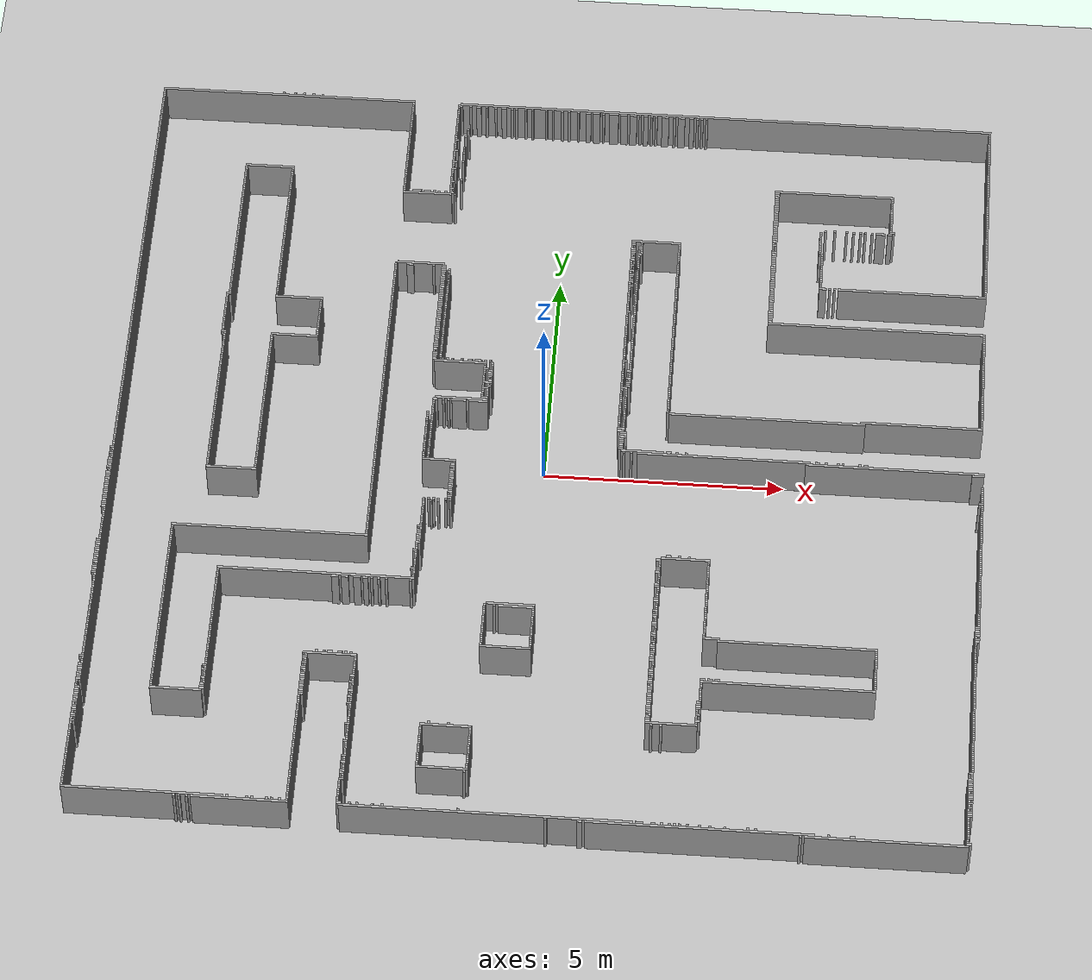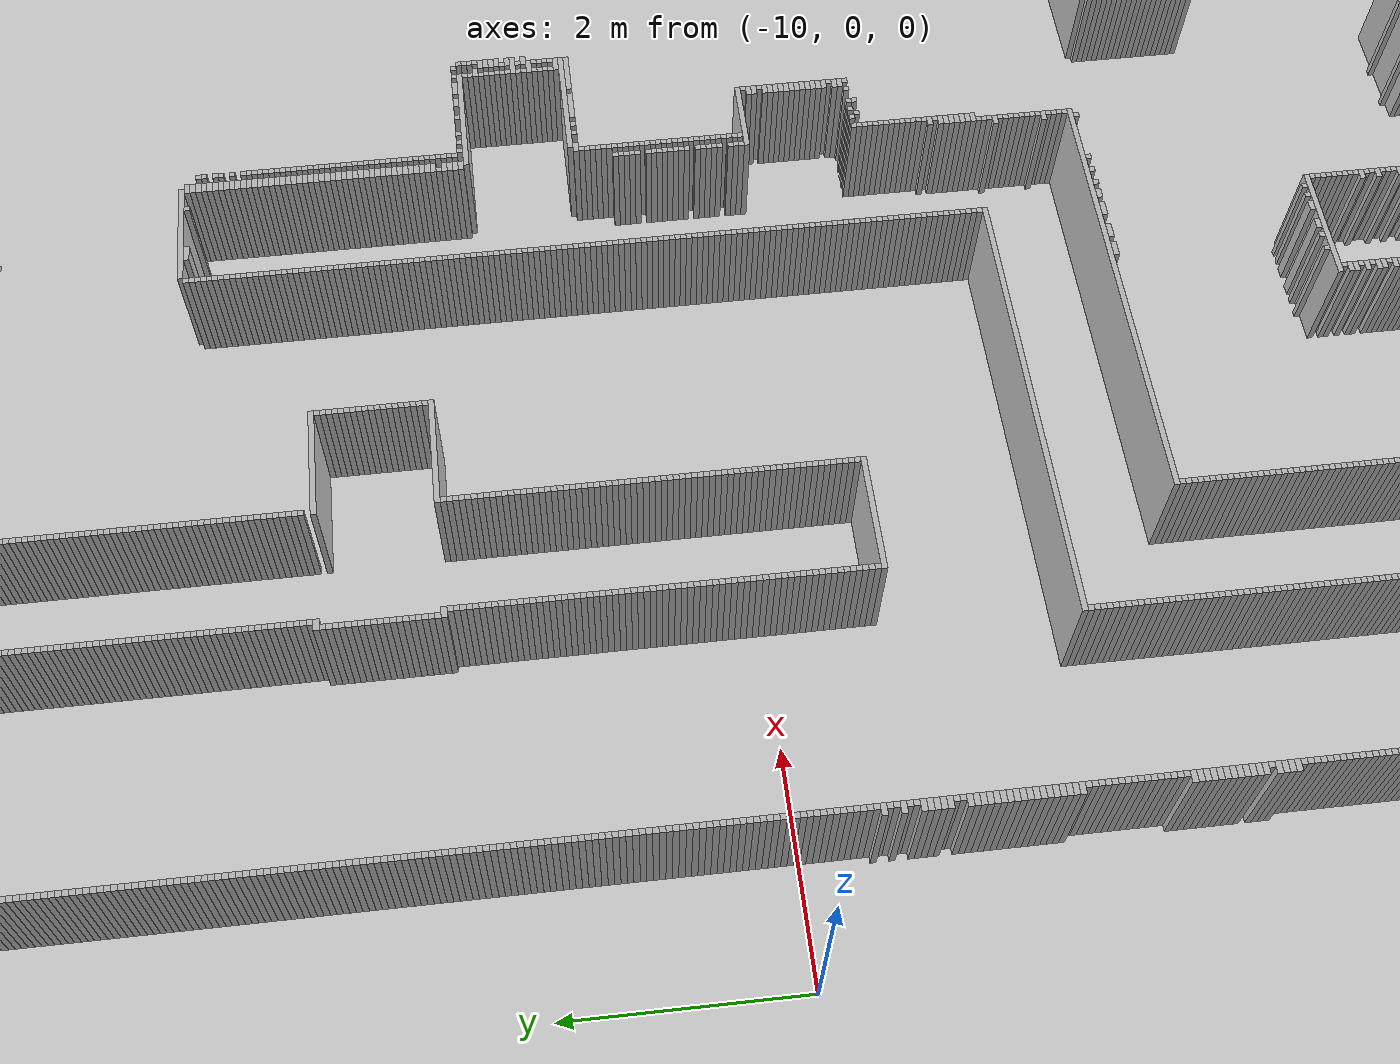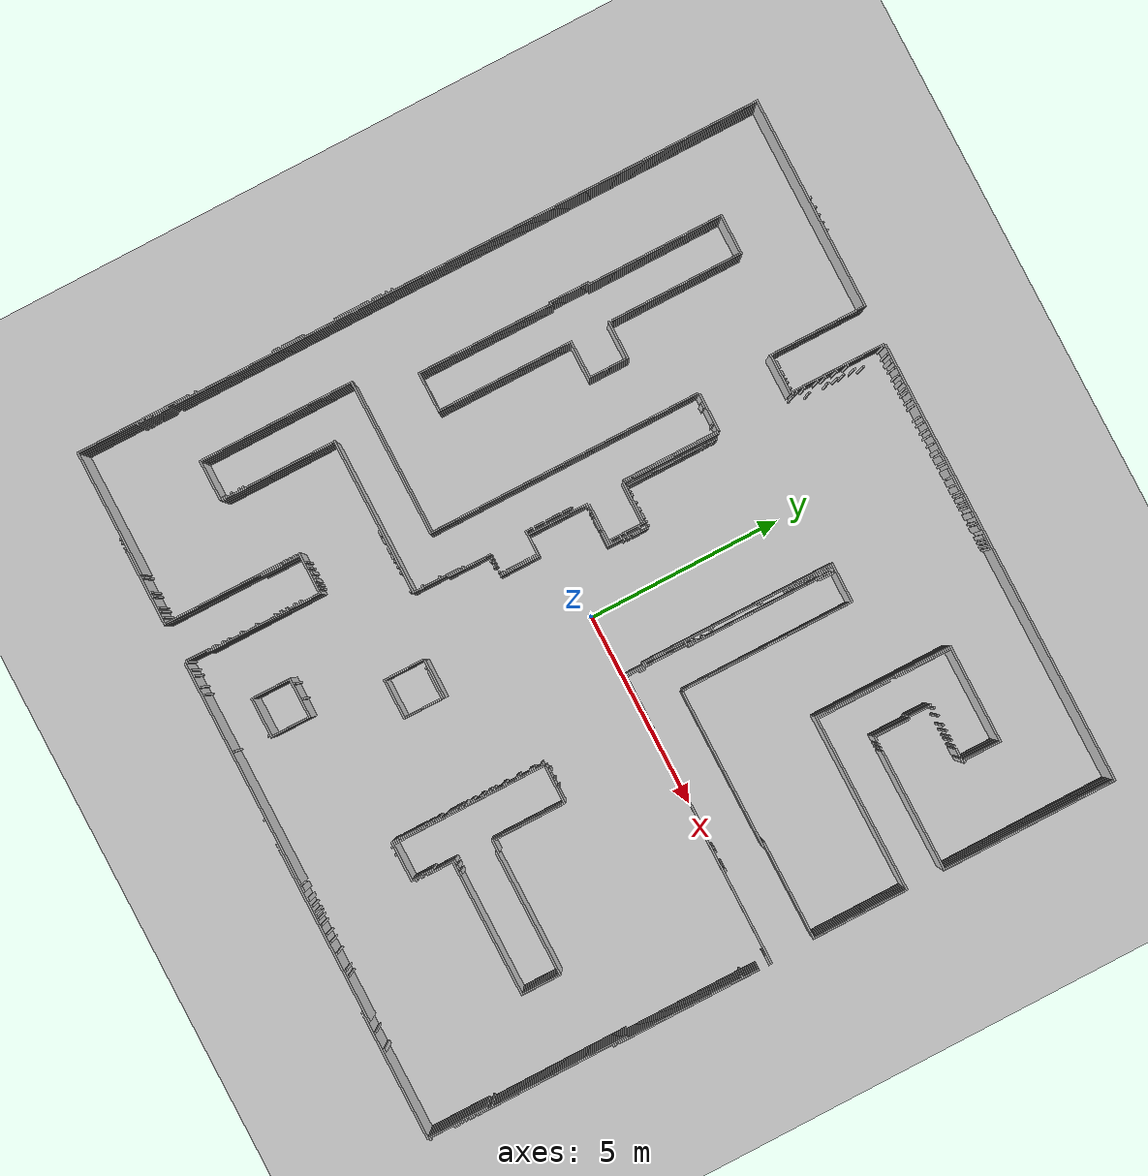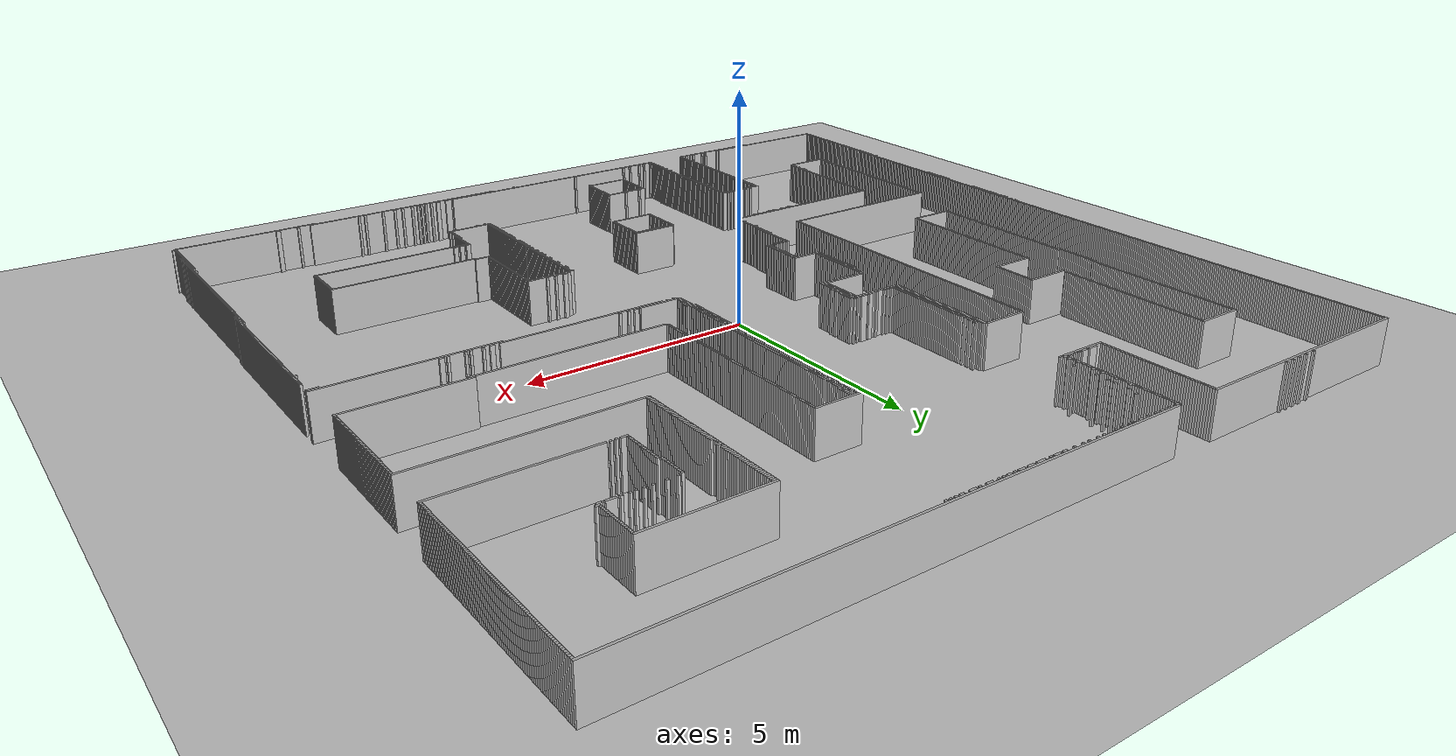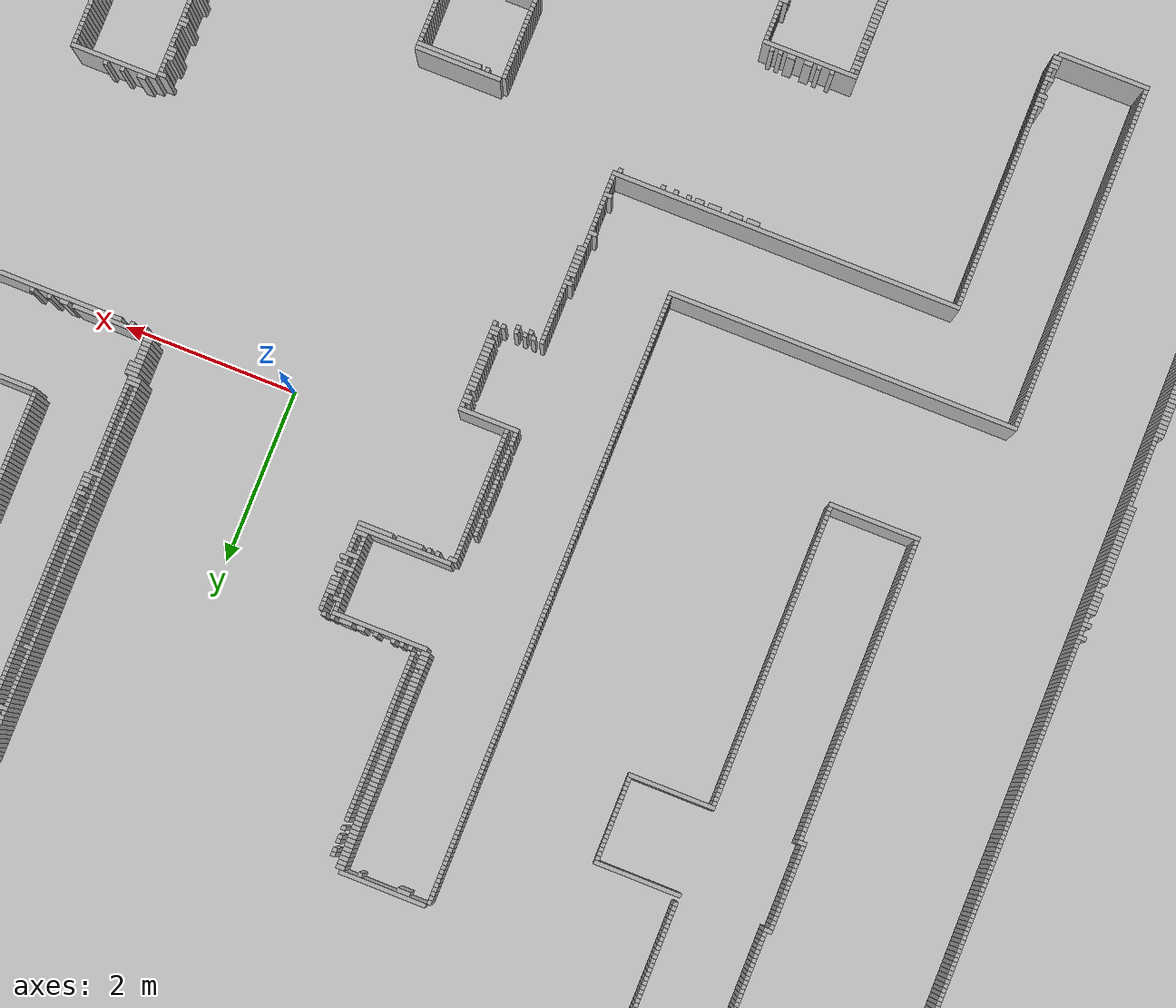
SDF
<?xml version="1.0" ?>
<sdf version="1.6">
  <world name="udh1_world">
    <include><uri>model://ground_plane</uri></include>
    <include><uri>model://sun</uri></include>

    <model name="wall_0">
      <static>true</static>
      <pose>-6.344999999999999 9.12 0.5 0 0 0</pose>
      <link name="link">
        <collision name="col"><geometry><box><size>0.05 0.05 1</size></box></geometry></collision>
        <visual name="vis"><geometry><box><size>0.05 0.05 1</size></box></geometry></visual>
      </link>
    </model>
    <model name="wall_1">
      <static>true</static>
      <pose>-6.094999999999999 9.12 0.5 0 0 0</pose>
      <link name="link">
        <collision name="col"><geometry><box><size>0.05 0.05 1</size></box></geometry></collision>
        <visual name="vis"><geometry><box><size>0.05 0.05 1</size></box></geometry></visual>
      </link>
    </model>
    <model name="wall_2">
      <static>true</static>
      <pose>-5.895 9.12 0.5 0 0 0</pose>
      <link name="link">
        <collision name="col"><geometry><box><size>0.05 0.05 1</size></box></geometry></collision>
        <visual name="vis"><geometry><box><size>0.05 0.05 1</size></box></geometry></visual>
      </link>
    </model>
    <model name="wall_3">
      <static>true</static>
      <pose>-5.694999999999999 9.12 0.5 0 0 0</pose>
      <link name="link">
        <collision name="col"><geometry><box><size>0.05 0.05 1</size></box></geometry></collision>
        <visual name="vis"><geometry><box><size>0.05 0.05 1</size></box></geometry></visual>
      </link>
    </model>
    <model name="wall_4">
      <static>true</static>
      <pose>-5.494999999999999 9.12 0.5 0 0 0</pose>
      <link name="link">
        <collision name="col"><geometry><box><size>0.05 0.05 1</size></box></geometry></collision>
        <visual name="vis"><geometry><box><size>0.05 0.05 1</size></box></geometry></visual>
      </link>
    </model>
    <model name="wall_5">
      <static>true</static>
      <pose>-6.219999999999999 9.069999999999999 0.5 0 0 0</pose>
      <link name="link">
        <collision name="col"><geometry><box><size>5.5 0.05 1</size></box></geometry></collision>
        <visual name="vis"><geometry><box><size>5.5 0.05 1</size></box></geometry></visual>
      </link>
    </model>
    <model name="wall_6">
      <static>true</static>
      <pose>3.3050000000000015 9.069999999999999 0.5 0 0 0</pose>
      <link name="link">
        <collision name="col"><geometry><box><size>11.55 0.05 1</size></box></geometry></collision>
        <visual name="vis"><geometry><box><size>11.55 0.05 1</size></box></geometry></visual>
      </link>
    </model>
    <model name="wall_7">
      <static>true</static>
      <pose>-8.945 9.020000000000001 0.5 0 0 0</pose>
      <link name="link">
        <collision name="col"><geometry><box><size>0.05 0.05 1</size></box></geometry></collision>
        <visual name="vis"><geometry><box><size>0.05 0.05 1</size></box></geometry></visual>
      </link>
    </model>
    <model name="wall_8">
      <static>true</static>
      <pose>-3.494999999999999 9.020000000000001 0.5 0 0 0</pose>
      <link name="link">
        <collision name="col"><geometry><box><size>0.05 0.05 1</size></box></geometry></collision>
        <visual name="vis"><geometry><box><size>0.05 0.05 1</size></box></geometry></visual>
      </link>
    </model>
    <model name="wall_9">
      <static>true</static>
      <pose>-2.469999999999999 9.020000000000001 0.5 0 0 0</pose>
      <link name="link">
        <collision name="col"><geometry><box><size>0.1 0.05 1</size></box></geometry></collision>
        <visual name="vis"><geometry><box><size>0.1 0.05 1</size></box></geometry></visual>
      </link>
    </model>
    <model name="wall_10">
      <static>true</static>
      <pose>-2.244999999999999 9.020000000000001 0.5 0 0 0</pose>
      <link name="link">
        <collision name="col"><geometry><box><size>0.05 0.05 1</size></box></geometry></collision>
        <visual name="vis"><geometry><box><size>0.05 0.05 1</size></box></geometry></visual>
      </link>
    </model>
    <model name="wall_11">
      <static>true</static>
      <pose>-2.0699999999999994 9.020000000000001 0.5 0 0 0</pose>
      <link name="link">
        <collision name="col"><geometry><box><size>0.1 0.05 1</size></box></geometry></collision>
        <visual name="vis"><geometry><box><size>0.1 0.05 1</size></box></geometry></visual>
      </link>
    </model>
    <model name="wall_12">
      <static>true</static>
      <pose>-1.8949999999999996 9.020000000000001 0.5 0 0 0</pose>
      <link name="link">
        <collision name="col"><geometry><box><size>0.05 0.05 1</size></box></geometry></collision>
        <visual name="vis"><geometry><box><size>0.05 0.05 1</size></box></geometry></visual>
      </link>
    </model>
    <model name="wall_13">
      <static>true</static>
      <pose>-1.6949999999999994 9.020000000000001 0.5 0 0 0</pose>
      <link name="link">
        <collision name="col"><geometry><box><size>0.05 0.05 1</size></box></geometry></collision>
        <visual name="vis"><geometry><box><size>0.05 0.05 1</size></box></geometry></visual>
      </link>
    </model>
    <model name="wall_14">
      <static>true</static>
      <pose>-1.5199999999999996 9.020000000000001 0.5 0 0 0</pose>
      <link name="link">
        <collision name="col"><geometry><box><size>0.1 0.05 1</size></box></geometry></collision>
        <visual name="vis"><geometry><box><size>0.1 0.05 1</size></box></geometry></visual>
      </link>
    </model>
    <model name="wall_15">
      <static>true</static>
      <pose>-1.3449999999999989 9.020000000000001 0.5 0 0 0</pose>
      <link name="link">
        <collision name="col"><geometry><box><size>0.05 0.05 1</size></box></geometry></collision>
        <visual name="vis"><geometry><box><size>0.05 0.05 1</size></box></geometry></visual>
      </link>
    </model>
    <model name="wall_16">
      <static>true</static>
      <pose>-1.2449999999999992 9.020000000000001 0.5 0 0 0</pose>
      <link name="link">
        <collision name="col"><geometry><box><size>0.05 0.05 1</size></box></geometry></collision>
        <visual name="vis"><geometry><box><size>0.05 0.05 1</size></box></geometry></visual>
      </link>
    </model>
    <model name="wall_17">
      <static>true</static>
      <pose>-1.044999999999999 9.020000000000001 0.5 0 0 0</pose>
      <link name="link">
        <collision name="col"><geometry><box><size>0.05 0.05 1</size></box></geometry></collision>
        <visual name="vis"><geometry><box><size>0.05 0.05 1</size></box></geometry></visual>
      </link>
    </model>
    <model name="wall_18">
      <static>true</static>
      <pose>-0.8949999999999996 9.020000000000001 0.5 0 0 0</pose>
      <link name="link">
        <collision name="col"><geometry><box><size>0.05 0.05 1</size></box></geometry></collision>
        <visual name="vis"><geometry><box><size>0.05 0.05 1</size></box></geometry></visual>
      </link>
    </model>
    <model name="wall_19">
      <static>true</static>
      <pose>-0.5949999999999989 9.020000000000001 0.5 0 0 0</pose>
      <link name="link">
        <collision name="col"><geometry><box><size>0.05 0.05 1</size></box></geometry></collision>
        <visual name="vis"><geometry><box><size>0.05 0.05 1</size></box></geometry></visual>
      </link>
    </model>
    <model name="wall_20">
      <static>true</static>
      <pose>-0.4449999999999985 9.020000000000001 0.5 0 0 0</pose>
      <link name="link">
        <collision name="col"><geometry><box><size>0.05 0.05 1</size></box></geometry></collision>
        <visual name="vis"><geometry><box><size>0.05 0.05 1</size></box></geometry></visual>
      </link>
    </model>
    <model name="wall_21">
      <static>true</static>
      <pose>-0.24499999999999922 9.020000000000001 0.5 0 0 0</pose>
      <link name="link">
        <collision name="col"><geometry><box><size>0.05 0.05 1</size></box></geometry></collision>
        <visual name="vis"><geometry><box><size>0.05 0.05 1</size></box></geometry></visual>
      </link>
    </model>
    <model name="wall_22">
      <static>true</static>
      <pose>-0.09499999999999886 9.020000000000001 0.5 0 0 0</pose>
      <link name="link">
        <collision name="col"><geometry><box><size>0.05 0.05 1</size></box></geometry></collision>
        <visual name="vis"><geometry><box><size>0.05 0.05 1</size></box></geometry></visual>
      </link>
    </model>
    <model name="wall_23">
      <static>true</static>
      <pose>0.10500000000000043 9.020000000000001 0.5 0 0 0</pose>
      <link name="link">
        <collision name="col"><geometry><box><size>0.05 0.05 1</size></box></geometry></collision>
        <visual name="vis"><geometry><box><size>0.05 0.05 1</size></box></geometry></visual>
      </link>
    </model>
    <model name="wall_24">
      <static>true</static>
      <pose>0.33000000000000007 9.020000000000001 0.5 0 0 0</pose>
      <link name="link">
        <collision name="col"><geometry><box><size>0.1 0.05 1</size></box></geometry></collision>
        <visual name="vis"><geometry><box><size>0.1 0.05 1</size></box></geometry></visual>
      </link>
    </model>
    <model name="wall_25">
      <static>true</static>
      <pose>0.5050000000000008 9.020000000000001 0.5 0 0 0</pose>
      <link name="link">
        <collision name="col"><geometry><box><size>0.15000000000000002 0.05 1</size></box></geometry></collision>
        <visual name="vis"><geometry><box><size>0.15000000000000002 0.05 1</size></box></geometry></visual>
      </link>
    </model>
    <model name="wall_26">
      <static>true</static>
      <pose>0.6550000000000011 9.020000000000001 0.5 0 0 0</pose>
      <link name="link">
        <collision name="col"><geometry><box><size>0.05 0.05 1</size></box></geometry></collision>
        <visual name="vis"><geometry><box><size>0.05 0.05 1</size></box></geometry></visual>
      </link>
    </model>
    <model name="wall_27">
      <static>true</static>
      <pose>0.8800000000000008 9.020000000000001 0.5 0 0 0</pose>
      <link name="link">
        <collision name="col"><geometry><box><size>0.2 0.05 1</size></box></geometry></collision>
        <visual name="vis"><geometry><box><size>0.2 0.05 1</size></box></geometry></visual>
      </link>
    </model>
    <model name="wall_28">
      <static>true</static>
      <pose>1.1050000000000004 9.020000000000001 0.5 0 0 0</pose>
      <link name="link">
        <collision name="col"><geometry><box><size>0.15000000000000002 0.05 1</size></box></geometry></collision>
        <visual name="vis"><geometry><box><size>0.15000000000000002 0.05 1</size></box></geometry></visual>
      </link>
    </model>
    <model name="wall_29">
      <static>true</static>
      <pose>1.3050000000000015 9.020000000000001 0.5 0 0 0</pose>
      <link name="link">
        <collision name="col"><geometry><box><size>0.15000000000000002 0.05 1</size></box></geometry></collision>
        <visual name="vis"><geometry><box><size>0.15000000000000002 0.05 1</size></box></geometry></visual>
      </link>
    </model>
    <model name="wall_30">
      <static>true</static>
      <pose>1.4550000000000018 9.020000000000001 0.5 0 0 0</pose>
      <link name="link">
        <collision name="col"><geometry><box><size>0.05 0.05 1</size></box></geometry></collision>
        <visual name="vis"><geometry><box><size>0.05 0.05 1</size></box></geometry></visual>
      </link>
    </model>
    <model name="wall_31">
      <static>true</static>
      <pose>1.5800000000000018 9.020000000000001 0.5 0 0 0</pose>
      <link name="link">
        <collision name="col"><geometry><box><size>0.1 0.05 1</size></box></geometry></collision>
        <visual name="vis"><geometry><box><size>0.1 0.05 1</size></box></geometry></visual>
      </link>
    </model>
    <model name="wall_32">
      <static>true</static>
      <pose>1.7050000000000018 9.020000000000001 0.5 0 0 0</pose>
      <link name="link">
        <collision name="col"><geometry><box><size>0.05 0.05 1</size></box></geometry></collision>
        <visual name="vis"><geometry><box><size>0.05 0.05 1</size></box></geometry></visual>
      </link>
    </model>
    <model name="wall_33">
      <static>true</static>
      <pose>1.8050000000000015 9.020000000000001 0.5 0 0 0</pose>
      <link name="link">
        <collision name="col"><geometry><box><size>0.05 0.05 1</size></box></geometry></collision>
        <visual name="vis"><geometry><box><size>0.05 0.05 1</size></box></geometry></visual>
      </link>
    </model>
    <model name="wall_34">
      <static>true</static>
      <pose>2.005000000000001 9.020000000000001 0.5 0 0 0</pose>
      <link name="link">
        <collision name="col"><geometry><box><size>0.15000000000000002 0.05 1</size></box></geometry></collision>
        <visual name="vis"><geometry><box><size>0.15000000000000002 0.05 1</size></box></geometry></visual>
      </link>
    </model>
    <model name="wall_35">
      <static>true</static>
      <pose>2.205000000000002 9.020000000000001 0.5 0 0 0</pose>
      <link name="link">
        <collision name="col"><geometry><box><size>0.05 0.05 1</size></box></geometry></collision>
        <visual name="vis"><geometry><box><size>0.05 0.05 1</size></box></geometry></visual>
      </link>
    </model>
    <model name="wall_36">
      <static>true</static>
      <pose>2.3550000000000004 9.020000000000001 0.5 0 0 0</pose>
      <link name="link">
        <collision name="col"><geometry><box><size>0.15000000000000002 0.05 1</size></box></geometry></collision>
        <visual name="vis"><geometry><box><size>0.15000000000000002 0.05 1</size></box></geometry></visual>
      </link>
    </model>
    <model name="wall_37">
      <static>true</static>
      <pose>2.580000000000002 9.020000000000001 0.5 0 0 0</pose>
      <link name="link">
        <collision name="col"><geometry><box><size>0.1 0.05 1</size></box></geometry></collision>
        <visual name="vis"><geometry><box><size>0.1 0.05 1</size></box></geometry></visual>
      </link>
    </model>
    <model name="wall_38">
      <static>true</static>
      <pose>2.705000000000002 9.020000000000001 0.5 0 0 0</pose>
      <link name="link">
        <collision name="col"><geometry><box><size>0.05 0.05 1</size></box></geometry></collision>
        <visual name="vis"><geometry><box><size>0.05 0.05 1</size></box></geometry></visual>
      </link>
    </model>
    <model name="wall_39">
      <static>true</static>
      <pose>2.8050000000000015 9.020000000000001 0.5 0 0 0</pose>
      <link name="link">
        <collision name="col"><geometry><box><size>0.05 0.05 1</size></box></geometry></collision>
        <visual name="vis"><geometry><box><size>0.05 0.05 1</size></box></geometry></visual>
      </link>
    </model>
    <model name="wall_40">
      <static>true</static>
      <pose>2.905000000000001 9.020000000000001 0.5 0 0 0</pose>
      <link name="link">
        <collision name="col"><geometry><box><size>0.05 0.05 1</size></box></geometry></collision>
        <visual name="vis"><geometry><box><size>0.05 0.05 1</size></box></geometry></visual>
      </link>
    </model>
    <model name="wall_41">
      <static>true</static>
      <pose>9.055 9.020000000000001 0.5 0 0 0</pose>
      <link name="link">
        <collision name="col"><geometry><box><size>0.05 0.05 1</size></box></geometry></collision>
        <visual name="vis"><geometry><box><size>0.05 0.05 1</size></box></geometry></visual>
      </link>
    </model>
    <model name="wall_42">
      <static>true</static>
      <pose>-8.945 8.97 0.5 0 0 0</pose>
      <link name="link">
        <collision name="col"><geometry><box><size>0.05 0.05 1</size></box></geometry></collision>
        <visual name="vis"><geometry><box><size>0.05 0.05 1</size></box></geometry></visual>
      </link>
    </model>
    <model name="wall_43">
      <static>true</static>
      <pose>-3.494999999999999 8.97 0.5 0 0 0</pose>
      <link name="link">
        <collision name="col"><geometry><box><size>0.05 0.05 1</size></box></geometry></collision>
        <visual name="vis"><geometry><box><size>0.05 0.05 1</size></box></geometry></visual>
      </link>
    </model>
    <model name="wall_44">
      <static>true</static>
      <pose>-2.494999999999999 8.97 0.5 0 0 0</pose>
      <link name="link">
        <collision name="col"><geometry><box><size>0.05 0.05 1</size></box></geometry></collision>
        <visual name="vis"><geometry><box><size>0.05 0.05 1</size></box></geometry></visual>
      </link>
    </model>
    <model name="wall_45">
      <static>true</static>
      <pose>9.055 8.97 0.5 0 0 0</pose>
      <link name="link">
        <collision name="col"><geometry><box><size>0.05 0.05 1</size></box></geometry></collision>
        <visual name="vis"><geometry><box><size>0.05 0.05 1</size></box></geometry></visual>
      </link>
    </model>
    <model name="wall_46">
      <static>true</static>
      <pose>-8.945 8.92 0.5 0 0 0</pose>
      <link name="link">
        <collision name="col"><geometry><box><size>0.05 0.05 1</size></box></geometry></collision>
        <visual name="vis"><geometry><box><size>0.05 0.05 1</size></box></geometry></visual>
      </link>
    </model>
    <model name="wall_47">
      <static>true</static>
      <pose>-3.494999999999999 8.92 0.5 0 0 0</pose>
      <link name="link">
        <collision name="col"><geometry><box><size>0.05 0.05 1</size></box></geometry></collision>
        <visual name="vis"><geometry><box><size>0.05 0.05 1</size></box></geometry></visual>
      </link>
    </model>
    <model name="wall_48">
      <static>true</static>
      <pose>-2.494999999999999 8.92 0.5 0 0 0</pose>
      <link name="link">
        <collision name="col"><geometry><box><size>0.05 0.05 1</size></box></geometry></collision>
        <visual name="vis"><geometry><box><size>0.05 0.05 1</size></box></geometry></visual>
      </link>
    </model>
    <model name="wall_49">
      <static>true</static>
      <pose>9.055 8.92 0.5 0 0 0</pose>
      <link name="link">
        <collision name="col"><geometry><box><size>0.05 0.05 1</size></box></geometry></collision>
        <visual name="vis"><geometry><box><size>0.05 0.05 1</size></box></geometry></visual>
      </link>
    </model>
    <model name="wall_50">
      <static>true</static>
      <pose>-8.945 8.87 0.5 0 0 0</pose>
      <link name="link">
        <collision name="col"><geometry><box><size>0.05 0.05 1</size></box></geometry></collision>
        <visual name="vis"><geometry><box><size>0.05 0.05 1</size></box></geometry></visual>
      </link>
    </model>
    <model name="wall_51">
      <static>true</static>
      <pose>-3.494999999999999 8.87 0.5 0 0 0</pose>
      <link name="link">
        <collision name="col"><geometry><box><size>0.05 0.05 1</size></box></geometry></collision>
        <visual name="vis"><geometry><box><size>0.05 0.05 1</size></box></geometry></visual>
      </link>
    </model>
    <model name="wall_52">
      <static>true</static>
      <pose>-2.494999999999999 8.87 0.5 0 0 0</pose>
      <link name="link">
        <collision name="col"><geometry><box><size>0.05 0.05 1</size></box></geometry></collision>
        <visual name="vis"><geometry><box><size>0.05 0.05 1</size></box></geometry></visual>
      </link>
    </model>
    <model name="wall_53">
      <static>true</static>
      <pose>9.055 8.87 0.5 0 0 0</pose>
      <link name="link">
        <collision name="col"><geometry><box><size>0.05 0.05 1</size></box></geometry></collision>
        <visual name="vis"><geometry><box><size>0.05 0.05 1</size></box></geometry></visual>
      </link>
    </model>
    <model name="wall_54">
      <static>true</static>
      <pose>-8.945 8.819999999999999 0.5 0 0 0</pose>
      <link name="link">
        <collision name="col"><geometry><box><size>0.05 0.05 1</size></box></geometry></collision>
        <visual name="vis"><geometry><box><size>0.05 0.05 1</size></box></geometry></visual>
      </link>
    </model>
    <model name="wall_55">
      <static>true</static>
      <pose>-3.494999999999999 8.819999999999999 0.5 0 0 0</pose>
      <link name="link">
        <collision name="col"><geometry><box><size>0.05 0.05 1</size></box></geometry></collision>
        <visual name="vis"><geometry><box><size>0.05 0.05 1</size></box></geometry></visual>
      </link>
    </model>
    <model name="wall_56">
      <static>true</static>
      <pose>-2.494999999999999 8.819999999999999 0.5 0 0 0</pose>
      <link name="link">
        <collision name="col"><geometry><box><size>0.05 0.05 1</size></box></geometry></collision>
        <visual name="vis"><geometry><box><size>0.05 0.05 1</size></box></geometry></visual>
      </link>
    </model>
    <model name="wall_57">
      <static>true</static>
      <pose>9.055 8.819999999999999 0.5 0 0 0</pose>
      <link name="link">
        <collision name="col"><geometry><box><size>0.05 0.05 1</size></box></geometry></collision>
        <visual name="vis"><geometry><box><size>0.05 0.05 1</size></box></geometry></visual>
      </link>
    </model>
    <model name="wall_58">
      <static>true</static>
      <pose>-8.945 8.770000000000001 0.5 0 0 0</pose>
      <link name="link">
        <collision name="col"><geometry><box><size>0.05 0.05 1</size></box></geometry></collision>
        <visual name="vis"><geometry><box><size>0.05 0.05 1</size></box></geometry></visual>
      </link>
    </model>
    <model name="wall_59">
      <static>true</static>
      <pose>-3.494999999999999 8.770000000000001 0.5 0 0 0</pose>
      <link name="link">
        <collision name="col"><geometry><box><size>0.05 0.05 1</size></box></geometry></collision>
        <visual name="vis"><geometry><box><size>0.05 0.05 1</size></box></geometry></visual>
      </link>
    </model>
    <model name="wall_60">
      <static>true</static>
      <pose>-2.494999999999999 8.770000000000001 0.5 0 0 0</pose>
      <link name="link">
        <collision name="col"><geometry><box><size>0.05 0.05 1</size></box></geometry></collision>
        <visual name="vis"><geometry><box><size>0.05 0.05 1</size></box></geometry></visual>
      </link>
    </model>
    <model name="wall_61">
      <static>true</static>
      <pose>9.055 8.770000000000001 0.5 0 0 0</pose>
      <link name="link">
        <collision name="col"><geometry><box><size>0.05 0.05 1</size></box></geometry></collision>
        <visual name="vis"><geometry><box><size>0.05 0.05 1</size></box></geometry></visual>
      </link>
    </model>
    <model name="wall_62">
      <static>true</static>
      <pose>-8.945 8.72 0.5 0 0 0</pose>
      <link name="link">
        <collision name="col"><geometry><box><size>0.05 0.05 1</size></box></geometry></collision>
        <visual name="vis"><geometry><box><size>0.05 0.05 1</size></box></geometry></visual>
      </link>
    </model>
    <model name="wall_63">
      <static>true</static>
      <pose>-3.494999999999999 8.72 0.5 0 0 0</pose>
      <link name="link">
        <collision name="col"><geometry><box><size>0.05 0.05 1</size></box></geometry></collision>
        <visual name="vis"><geometry><box><size>0.05 0.05 1</size></box></geometry></visual>
      </link>
    </model>
    <model name="wall_64">
      <static>true</static>
      <pose>-2.494999999999999 8.72 0.5 0 0 0</pose>
      <link name="link">
        <collision name="col"><geometry><box><size>0.05 0.05 1</size></box></geometry></collision>
        <visual name="vis"><geometry><box><size>0.05 0.05 1</size></box></geometry></visual>
      </link>
    </model>
    <model name="wall_65">
      <static>true</static>
      <pose>9.055 8.72 0.5 0 0 0</pose>
      <link name="link">
        <collision name="col"><geometry><box><size>0.05 0.05 1</size></box></geometry></collision>
        <visual name="vis"><geometry><box><size>0.05 0.05 1</size></box></geometry></visual>
      </link>
    </model>
    <model name="wall_66">
      <static>true</static>
      <pose>-8.945 8.67 0.5 0 0 0</pose>
      <link name="link">
        <collision name="col"><geometry><box><size>0.05 0.05 1</size></box></geometry></collision>
        <visual name="vis"><geometry><box><size>0.05 0.05 1</size></box></geometry></visual>
      </link>
    </model>
    <model name="wall_67">
      <static>true</static>
      <pose>-3.494999999999999 8.67 0.5 0 0 0</pose>
      <link name="link">
        <collision name="col"><geometry><box><size>0.05 0.05 1</size></box></geometry></collision>
        <visual name="vis"><geometry><box><size>0.05 0.05 1</size></box></geometry></visual>
      </link>
    </model>
    <model name="wall_68">
      <static>true</static>
      <pose>-2.494999999999999 8.67 0.5 0 0 0</pose>
      <link name="link">
        <collision name="col"><geometry><box><size>0.05 0.05 1</size></box></geometry></collision>
        <visual name="vis"><geometry><box><size>0.05 0.05 1</size></box></geometry></visual>
      </link>
    </model>
    <model name="wall_69">
      <static>true</static>
      <pose>9.055 8.67 0.5 0 0 0</pose>
      <link name="link">
        <collision name="col"><geometry><box><size>0.05 0.05 1</size></box></geometry></collision>
        <visual name="vis"><geometry><box><size>0.05 0.05 1</size></box></geometry></visual>
      </link>
    </model>
    <model name="wall_70">
      <static>true</static>
      <pose>-8.945 8.62 0.5 0 0 0</pose>
      <link name="link">
        <collision name="col"><geometry><box><size>0.05 0.05 1</size></box></geometry></collision>
        <visual name="vis"><geometry><box><size>0.05 0.05 1</size></box></geometry></visual>
      </link>
    </model>
    <model name="wall_71">
      <static>true</static>
      <pose>-3.494999999999999 8.62 0.5 0 0 0</pose>
      <link name="link">
        <collision name="col"><geometry><box><size>0.05 0.05 1</size></box></geometry></collision>
        <visual name="vis"><geometry><box><size>0.05 0.05 1</size></box></geometry></visual>
      </link>
    </model>
    <model name="wall_72">
      <static>true</static>
      <pose>-2.494999999999999 8.62 0.5 0 0 0</pose>
      <link name="link">
        <collision name="col"><geometry><box><size>0.05 0.05 1</size></box></geometry></collision>
        <visual name="vis"><geometry><box><size>0.05 0.05 1</size></box></geometry></visual>
      </link>
    </model>
    <model name="wall_73">
      <static>true</static>
      <pose>9.055 8.62 0.5 0 0 0</pose>
      <link name="link">
        <collision name="col"><geometry><box><size>0.05 0.05 1</size></box></geometry></collision>
        <visual name="vis"><geometry><box><size>0.05 0.05 1</size></box></geometry></visual>
      </link>
    </model>
    <model name="wall_74">
      <static>true</static>
      <pose>-8.945 8.569999999999999 0.5 0 0 0</pose>
      <link name="link">
        <collision name="col"><geometry><box><size>0.05 0.05 1</size></box></geometry></collision>
        <visual name="vis"><geometry><box><size>0.05 0.05 1</size></box></geometry></visual>
      </link>
    </model>
    <model name="wall_75">
      <static>true</static>
      <pose>-3.494999999999999 8.569999999999999 0.5 0 0 0</pose>
      <link name="link">
        <collision name="col"><geometry><box><size>0.05 0.05 1</size></box></geometry></collision>
        <visual name="vis"><geometry><box><size>0.05 0.05 1</size></box></geometry></visual>
      </link>
    </model>
    <model name="wall_76">
      <static>true</static>
      <pose>-2.494999999999999 8.569999999999999 0.5 0 0 0</pose>
      <link name="link">
        <collision name="col"><geometry><box><size>0.05 0.05 1</size></box></geometry></collision>
        <visual name="vis"><geometry><box><size>0.05 0.05 1</size></box></geometry></visual>
      </link>
    </model>
    <model name="wall_77">
      <static>true</static>
      <pose>9.055 8.569999999999999 0.5 0 0 0</pose>
      <link name="link">
        <collision name="col"><geometry><box><size>0.05 0.05 1</size></box></geometry></collision>
        <visual name="vis"><geometry><box><size>0.05 0.05 1</size></box></geometry></visual>
      </link>
    </model>
    <model name="wall_78">
      <static>true</static>
      <pose>-8.945 8.520000000000001 0.5 0 0 0</pose>
      <link name="link">
        <collision name="col"><geometry><box><size>0.05 0.05 1</size></box></geometry></collision>
        <visual name="vis"><geometry><box><size>0.05 0.05 1</size></box></geometry></visual>
      </link>
    </model>
    <model name="wall_79">
      <static>true</static>
      <pose>-3.494999999999999 8.520000000000001 0.5 0 0 0</pose>
      <link name="link">
        <collision name="col"><geometry><box><size>0.05 0.05 1</size></box></geometry></collision>
        <visual name="vis"><geometry><box><size>0.05 0.05 1</size></box></geometry></visual>
      </link>
    </model>
    <model name="wall_80">
      <static>true</static>
      <pose>-2.494999999999999 8.520000000000001 0.5 0 0 0</pose>
      <link name="link">
        <collision name="col"><geometry><box><size>0.05 0.05 1</size></box></geometry></collision>
        <visual name="vis"><geometry><box><size>0.05 0.05 1</size></box></geometry></visual>
      </link>
    </model>
    <model name="wall_81">
      <static>true</static>
      <pose>9.055 8.520000000000001 0.5 0 0 0</pose>
      <link name="link">
        <collision name="col"><geometry><box><size>0.05 0.05 1</size></box></geometry></collision>
        <visual name="vis"><geometry><box><size>0.05 0.05 1</size></box></geometry></visual>
      </link>
    </model>
    <model name="wall_82">
      <static>true</static>
      <pose>-8.945 8.47 0.5 0 0 0</pose>
      <link name="link">
        <collision name="col"><geometry><box><size>0.05 0.05 1</size></box></geometry></collision>
        <visual name="vis"><geometry><box><size>0.05 0.05 1</size></box></geometry></visual>
      </link>
    </model>
    <model name="wall_83">
      <static>true</static>
      <pose>-3.494999999999999 8.47 0.5 0 0 0</pose>
      <link name="link">
        <collision name="col"><geometry><box><size>0.05 0.05 1</size></box></geometry></collision>
        <visual name="vis"><geometry><box><size>0.05 0.05 1</size></box></geometry></visual>
      </link>
    </model>
    <model name="wall_84">
      <static>true</static>
      <pose>-2.494999999999999 8.47 0.5 0 0 0</pose>
      <link name="link">
        <collision name="col"><geometry><box><size>0.05 0.05 1</size></box></geometry></collision>
        <visual name="vis"><geometry><box><size>0.05 0.05 1</size></box></geometry></visual>
      </link>
    </model>
    <model name="wall_85">
      <static>true</static>
      <pose>9.055 8.47 0.5 0 0 0</pose>
      <link name="link">
        <collision name="col"><geometry><box><size>0.05 0.05 1</size></box></geometry></collision>
        <visual name="vis"><geometry><box><size>0.05 0.05 1</size></box></geometry></visual>
      </link>
    </model>
    <model name="wall_86">
      <static>true</static>
      <pose>-8.945 8.42 0.5 0 0 0</pose>
      <link name="link">
        <collision name="col"><geometry><box><size>0.05 0.05 1</size></box></geometry></collision>
        <visual name="vis"><geometry><box><size>0.05 0.05 1</size></box></geometry></visual>
      </link>
    </model>
    <model name="wall_87">
      <static>true</static>
      <pose>-3.494999999999999 8.42 0.5 0 0 0</pose>
      <link name="link">
        <collision name="col"><geometry><box><size>0.05 0.05 1</size></box></geometry></collision>
        <visual name="vis"><geometry><box><size>0.05 0.05 1</size></box></geometry></visual>
      </link>
    </model>
    <model name="wall_88">
      <static>true</static>
      <pose>-2.494999999999999 8.42 0.5 0 0 0</pose>
      <link name="link">
        <collision name="col"><geometry><box><size>0.05 0.05 1</size></box></geometry></collision>
        <visual name="vis"><geometry><box><size>0.05 0.05 1</size></box></geometry></visual>
      </link>
    </model>
    <model name="wall_89">
      <static>true</static>
      <pose>9.055 8.42 0.5 0 0 0</pose>
      <link name="link">
        <collision name="col"><geometry><box><size>0.05 0.05 1</size></box></geometry></collision>
        <visual name="vis"><geometry><box><size>0.05 0.05 1</size></box></geometry></visual>
      </link>
    </model>
    <model name="wall_90">
      <static>true</static>
      <pose>-8.945 8.37 0.5 0 0 0</pose>
      <link name="link">
        <collision name="col"><geometry><box><size>0.05 0.05 1</size></box></geometry></collision>
        <visual name="vis"><geometry><box><size>0.05 0.05 1</size></box></geometry></visual>
      </link>
    </model>
    <model name="wall_91">
      <static>true</static>
      <pose>-3.494999999999999 8.37 0.5 0 0 0</pose>
      <link name="link">
        <collision name="col"><geometry><box><size>0.05 0.05 1</size></box></geometry></collision>
        <visual name="vis"><geometry><box><size>0.05 0.05 1</size></box></geometry></visual>
      </link>
    </model>
    <model name="wall_92">
      <static>true</static>
      <pose>-2.494999999999999 8.37 0.5 0 0 0</pose>
      <link name="link">
        <collision name="col"><geometry><box><size>0.05 0.05 1</size></box></geometry></collision>
        <visual name="vis"><geometry><box><size>0.05 0.05 1</size></box></geometry></visual>
      </link>
    </model>
    <model name="wall_93">
      <static>true</static>
      <pose>-2.244999999999999 8.37 0.5 0 0 0</pose>
      <link name="link">
        <collision name="col"><geometry><box><size>0.05 0.05 1</size></box></geometry></collision>
        <visual name="vis"><geometry><box><size>0.05 0.05 1</size></box></geometry></visual>
      </link>
    </model>
    <model name="wall_94">
      <static>true</static>
      <pose>9.055 8.37 0.5 0 0 0</pose>
      <link name="link">
        <collision name="col"><geometry><box><size>0.05 0.05 1</size></box></geometry></collision>
        <visual name="vis"><geometry><box><size>0.05 0.05 1</size></box></geometry></visual>
      </link>
    </model>
    <model name="wall_95">
      <static>true</static>
      <pose>-8.945 8.319999999999999 0.5 0 0 0</pose>
      <link name="link">
        <collision name="col"><geometry><box><size>0.05 0.05 1</size></box></geometry></collision>
        <visual name="vis"><geometry><box><size>0.05 0.05 1</size></box></geometry></visual>
      </link>
    </model>
    <model name="wall_96">
      <static>true</static>
      <pose>-3.494999999999999 8.319999999999999 0.5 0 0 0</pose>
      <link name="link">
        <collision name="col"><geometry><box><size>0.05 0.05 1</size></box></geometry></collision>
        <visual name="vis"><geometry><box><size>0.05 0.05 1</size></box></geometry></visual>
      </link>
    </model>
    <model name="wall_97">
      <static>true</static>
      <pose>-2.494999999999999 8.319999999999999 0.5 0 0 0</pose>
      <link name="link">
        <collision name="col"><geometry><box><size>0.05 0.05 1</size></box></geometry></collision>
        <visual name="vis"><geometry><box><size>0.05 0.05 1</size></box></geometry></visual>
      </link>
    </model>
    <model name="wall_98">
      <static>true</static>
      <pose>9.055 8.319999999999999 0.5 0 0 0</pose>
      <link name="link">
        <collision name="col"><geometry><box><size>0.05 0.05 1</size></box></geometry></collision>
        <visual name="vis"><geometry><box><size>0.05 0.05 1</size></box></geometry></visual>
      </link>
    </model>
    <model name="wall_99">
      <static>true</static>
      <pose>-8.945 8.270000000000001 0.5 0 0 0</pose>
      <link name="link">
        <collision name="col"><geometry><box><size>0.05 0.05 1</size></box></geometry></collision>
        <visual name="vis"><geometry><box><size>0.05 0.05 1</size></box></geometry></visual>
      </link>
    </model>
    <model name="wall_100">
      <static>true</static>
      <pose>-3.494999999999999 8.270000000000001 0.5 0 0 0</pose>
      <link name="link">
        <collision name="col"><geometry><box><size>0.05 0.05 1</size></box></geometry></collision>
        <visual name="vis"><geometry><box><size>0.05 0.05 1</size></box></geometry></visual>
      </link>
    </model>
    <model name="wall_101">
      <static>true</static>
      <pose>-2.494999999999999 8.270000000000001 0.5 0 0 0</pose>
      <link name="link">
        <collision name="col"><geometry><box><size>0.05 0.05 1</size></box></geometry></collision>
        <visual name="vis"><geometry><box><size>0.05 0.05 1</size></box></geometry></visual>
      </link>
    </model>
    <model name="wall_102">
      <static>true</static>
      <pose>9.055 8.270000000000001 0.5 0 0 0</pose>
      <link name="link">
        <collision name="col"><geometry><box><size>0.05 0.05 1</size></box></geometry></collision>
        <visual name="vis"><geometry><box><size>0.05 0.05 1</size></box></geometry></visual>
      </link>
    </model>
    <model name="wall_103">
      <static>true</static>
      <pose>-8.945 8.22 0.5 0 0 0</pose>
      <link name="link">
        <collision name="col"><geometry><box><size>0.05 0.05 1</size></box></geometry></collision>
        <visual name="vis"><geometry><box><size>0.05 0.05 1</size></box></geometry></visual>
      </link>
    </model>
    <model name="wall_104">
      <static>true</static>
      <pose>-3.494999999999999 8.22 0.5 0 0 0</pose>
      <link name="link">
        <collision name="col"><geometry><box><size>0.05 0.05 1</size></box></geometry></collision>
        <visual name="vis"><geometry><box><size>0.05 0.05 1</size></box></geometry></visual>
      </link>
    </model>
    <model name="wall_105">
      <static>true</static>
      <pose>-2.494999999999999 8.22 0.5 0 0 0</pose>
      <link name="link">
        <collision name="col"><geometry><box><size>0.05 0.05 1</size></box></geometry></collision>
        <visual name="vis"><geometry><box><size>0.05 0.05 1</size></box></geometry></visual>
      </link>
    </model>
    <model name="wall_106">
      <static>true</static>
      <pose>9.055 8.22 0.5 0 0 0</pose>
      <link name="link">
        <collision name="col"><geometry><box><size>0.05 0.05 1</size></box></geometry></collision>
        <visual name="vis"><geometry><box><size>0.05 0.05 1</size></box></geometry></visual>
      </link>
    </model>
    <model name="wall_107">
      <static>true</static>
      <pose>-8.945 8.17 0.5 0 0 0</pose>
      <link name="link">
        <collision name="col"><geometry><box><size>0.05 0.05 1</size></box></geometry></collision>
        <visual name="vis"><geometry><box><size>0.05 0.05 1</size></box></geometry></visual>
      </link>
    </model>
    <model name="wall_108">
      <static>true</static>
      <pose>-3.494999999999999 8.17 0.5 0 0 0</pose>
      <link name="link">
        <collision name="col"><geometry><box><size>0.05 0.05 1</size></box></geometry></collision>
        <visual name="vis"><geometry><box><size>0.05 0.05 1</size></box></geometry></visual>
      </link>
    </model>
    <model name="wall_109">
      <static>true</static>
      <pose>-2.494999999999999 8.17 0.5 0 0 0</pose>
      <link name="link">
        <collision name="col"><geometry><box><size>0.05 0.05 1</size></box></geometry></collision>
        <visual name="vis"><geometry><box><size>0.05 0.05 1</size></box></geometry></visual>
      </link>
    </model>
    <model name="wall_110">
      <static>true</static>
      <pose>-2.294999999999999 8.17 0.5 0 0 0</pose>
      <link name="link">
        <collision name="col"><geometry><box><size>0.05 0.05 1</size></box></geometry></collision>
        <visual name="vis"><geometry><box><size>0.05 0.05 1</size></box></geometry></visual>
      </link>
    </model>
    <model name="wall_111">
      <static>true</static>
      <pose>9.055 8.17 0.5 0 0 0</pose>
      <link name="link">
        <collision name="col"><geometry><box><size>0.05 0.05 1</size></box></geometry></collision>
        <visual name="vis"><geometry><box><size>0.05 0.05 1</size></box></geometry></visual>
      </link>
    </model>
    <model name="wall_112">
      <static>true</static>
      <pose>-8.945 8.12 0.5 0 0 0</pose>
      <link name="link">
        <collision name="col"><geometry><box><size>0.05 0.05 1</size></box></geometry></collision>
        <visual name="vis"><geometry><box><size>0.05 0.05 1</size></box></geometry></visual>
      </link>
    </model>
    <model name="wall_113">
      <static>true</static>
      <pose>-3.494999999999999 8.12 0.5 0 0 0</pose>
      <link name="link">
        <collision name="col"><geometry><box><size>0.05 0.05 1</size></box></geometry></collision>
        <visual name="vis"><geometry><box><size>0.05 0.05 1</size></box></geometry></visual>
      </link>
    </model>
    <model name="wall_114">
      <static>true</static>
      <pose>-2.494999999999999 8.12 0.5 0 0 0</pose>
      <link name="link">
        <collision name="col"><geometry><box><size>0.05 0.05 1</size></box></geometry></collision>
        <visual name="vis"><geometry><box><size>0.05 0.05 1</size></box></geometry></visual>
      </link>
    </model>
    <model name="wall_115">
      <static>true</static>
      <pose>9.055 8.12 0.5 0 0 0</pose>
      <link name="link">
        <collision name="col"><geometry><box><size>0.05 0.05 1</size></box></geometry></collision>
        <visual name="vis"><geometry><box><size>0.05 0.05 1</size></box></geometry></visual>
      </link>
    </model>
    <model name="wall_116">
      <static>true</static>
      <pose>-8.945 8.069999999999999 0.5 0 0 0</pose>
      <link name="link">
        <collision name="col"><geometry><box><size>0.05 0.05 1</size></box></geometry></collision>
        <visual name="vis"><geometry><box><size>0.05 0.05 1</size></box></geometry></visual>
      </link>
    </model>
    <model name="wall_117">
      <static>true</static>
      <pose>-3.494999999999999 8.069999999999999 0.5 0 0 0</pose>
      <link name="link">
        <collision name="col"><geometry><box><size>0.05 0.05 1</size></box></geometry></collision>
        <visual name="vis"><geometry><box><size>0.05 0.05 1</size></box></geometry></visual>
      </link>
    </model>
    <model name="wall_118">
      <static>true</static>
      <pose>-2.469999999999999 8.069999999999999 0.5 0 0 0</pose>
      <link name="link">
        <collision name="col"><geometry><box><size>0.1 0.05 1</size></box></geometry></collision>
        <visual name="vis"><geometry><box><size>0.1 0.05 1</size></box></geometry></visual>
      </link>
    </model>
    <model name="wall_119">
      <static>true</static>
      <pose>9.055 8.069999999999999 0.5 0 0 0</pose>
      <link name="link">
        <collision name="col"><geometry><box><size>0.05 0.05 1</size></box></geometry></collision>
        <visual name="vis"><geometry><box><size>0.05 0.05 1</size></box></geometry></visual>
      </link>
    </model>
    <model name="wall_120">
      <static>true</static>
      <pose>-8.945 8.020000000000001 0.5 0 0 0</pose>
      <link name="link">
        <collision name="col"><geometry><box><size>0.05 0.05 1</size></box></geometry></collision>
        <visual name="vis"><geometry><box><size>0.05 0.05 1</size></box></geometry></visual>
      </link>
    </model>
    <model name="wall_121">
      <static>true</static>
      <pose>-3.494999999999999 8.020000000000001 0.5 0 0 0</pose>
      <link name="link">
        <collision name="col"><geometry><box><size>0.05 0.05 1</size></box></geometry></collision>
        <visual name="vis"><geometry><box><size>0.05 0.05 1</size></box></geometry></visual>
      </link>
    </model>
    <model name="wall_122">
      <static>true</static>
      <pose>-2.494999999999999 8.020000000000001 0.5 0 0 0</pose>
      <link name="link">
        <collision name="col"><geometry><box><size>0.05 0.05 1</size></box></geometry></collision>
        <visual name="vis"><geometry><box><size>0.05 0.05 1</size></box></geometry></visual>
      </link>
    </model>
    <model name="wall_123">
      <static>true</static>
      <pose>9.055 8.020000000000001 0.5 0 0 0</pose>
      <link name="link">
        <collision name="col"><geometry><box><size>0.05 0.05 1</size></box></geometry></collision>
        <visual name="vis"><geometry><box><size>0.05 0.05 1</size></box></geometry></visual>
      </link>
    </model>
    <model name="wall_124">
      <static>true</static>
      <pose>-8.945 7.970000000000001 0.5 0 0 0</pose>
      <link name="link">
        <collision name="col"><geometry><box><size>0.05 0.05 1</size></box></geometry></collision>
        <visual name="vis"><geometry><box><size>0.05 0.05 1</size></box></geometry></visual>
      </link>
    </model>
    <model name="wall_125">
      <static>true</static>
      <pose>-3.494999999999999 7.970000000000001 0.5 0 0 0</pose>
      <link name="link">
        <collision name="col"><geometry><box><size>0.05 0.05 1</size></box></geometry></collision>
        <visual name="vis"><geometry><box><size>0.05 0.05 1</size></box></geometry></visual>
      </link>
    </model>
    <model name="wall_126">
      <static>true</static>
      <pose>-2.494999999999999 7.970000000000001 0.5 0 0 0</pose>
      <link name="link">
        <collision name="col"><geometry><box><size>0.05 0.05 1</size></box></geometry></collision>
        <visual name="vis"><geometry><box><size>0.05 0.05 1</size></box></geometry></visual>
      </link>
    </model>
    <model name="wall_127">
      <static>true</static>
      <pose>9.055 7.970000000000001 0.5 0 0 0</pose>
      <link name="link">
        <collision name="col"><geometry><box><size>0.05 0.05 1</size></box></geometry></collision>
        <visual name="vis"><geometry><box><size>0.05 0.05 1</size></box></geometry></visual>
      </link>
    </model>
    <model name="wall_128">
      <static>true</static>
      <pose>-8.945 7.92 0.5 0 0 0</pose>
      <link name="link">
        <collision name="col"><geometry><box><size>0.05 0.05 1</size></box></geometry></collision>
        <visual name="vis"><geometry><box><size>0.05 0.05 1</size></box></geometry></visual>
      </link>
    </model>
    <model name="wall_129">
      <static>true</static>
      <pose>-3.494999999999999 7.92 0.5 0 0 0</pose>
      <link name="link">
        <collision name="col"><geometry><box><size>0.05 0.05 1</size></box></geometry></collision>
        <visual name="vis"><geometry><box><size>0.05 0.05 1</size></box></geometry></visual>
      </link>
    </model>
    <model name="wall_130">
      <static>true</static>
      <pose>-2.494999999999999 7.92 0.5 0 0 0</pose>
      <link name="link">
        <collision name="col"><geometry><box><size>0.05 0.05 1</size></box></geometry></collision>
        <visual name="vis"><geometry><box><size>0.05 0.05 1</size></box></geometry></visual>
      </link>
    </model>
    <model name="wall_131">
      <static>true</static>
      <pose>9.055 7.92 0.5 0 0 0</pose>
      <link name="link">
        <collision name="col"><geometry><box><size>0.05 0.05 1</size></box></geometry></collision>
        <visual name="vis"><geometry><box><size>0.05 0.05 1</size></box></geometry></visual>
      </link>
    </model>
    <model name="wall_132">
      <static>true</static>
      <pose>-8.945 7.869999999999999 0.5 0 0 0</pose>
      <link name="link">
        <collision name="col"><geometry><box><size>0.05 0.05 1</size></box></geometry></collision>
        <visual name="vis"><geometry><box><size>0.05 0.05 1</size></box></geometry></visual>
      </link>
    </model>
    <model name="wall_133">
      <static>true</static>
      <pose>-3.494999999999999 7.869999999999999 0.5 0 0 0</pose>
      <link name="link">
        <collision name="col"><geometry><box><size>0.05 0.05 1</size></box></geometry></collision>
        <visual name="vis"><geometry><box><size>0.05 0.05 1</size></box></geometry></visual>
      </link>
    </model>
    <model name="wall_134">
      <static>true</static>
      <pose>-2.494999999999999 7.869999999999999 0.5 0 0 0</pose>
      <link name="link">
        <collision name="col"><geometry><box><size>0.05 0.05 1</size></box></geometry></collision>
        <visual name="vis"><geometry><box><size>0.05 0.05 1</size></box></geometry></visual>
      </link>
    </model>
    <model name="wall_135">
      <static>true</static>
      <pose>-2.294999999999999 7.869999999999999 0.5 0 0 0</pose>
      <link name="link">
        <collision name="col"><geometry><box><size>0.05 0.05 1</size></box></geometry></collision>
        <visual name="vis"><geometry><box><size>0.05 0.05 1</size></box></geometry></visual>
      </link>
    </model>
    <model name="wall_136">
      <static>true</static>
      <pose>9.055 7.869999999999999 0.5 0 0 0</pose>
      <link name="link">
        <collision name="col"><geometry><box><size>0.05 0.05 1</size></box></geometry></collision>
        <visual name="vis"><geometry><box><size>0.05 0.05 1</size></box></geometry></visual>
      </link>
    </model>
    <model name="wall_137">
      <static>true</static>
      <pose>-8.945 7.8199999999999985 0.5 0 0 0</pose>
      <link name="link">
        <collision name="col"><geometry><box><size>0.05 0.05 1</size></box></geometry></collision>
        <visual name="vis"><geometry><box><size>0.05 0.05 1</size></box></geometry></visual>
      </link>
    </model>
    <model name="wall_138">
      <static>true</static>
      <pose>-3.494999999999999 7.8199999999999985 0.5 0 0 0</pose>
      <link name="link">
        <collision name="col"><geometry><box><size>0.05 0.05 1</size></box></geometry></collision>
        <visual name="vis"><geometry><box><size>0.05 0.05 1</size></box></geometry></visual>
      </link>
    </model>
    <model name="wall_139">
      <static>true</static>
      <pose>-2.494999999999999 7.8199999999999985 0.5 0 0 0</pose>
      <link name="link">
        <collision name="col"><geometry><box><size>0.05 0.05 1</size></box></geometry></collision>
        <visual name="vis"><geometry><box><size>0.05 0.05 1</size></box></geometry></visual>
      </link>
    </model>
    <model name="wall_140">
      <static>true</static>
      <pose>9.055 7.8199999999999985 0.5 0 0 0</pose>
      <link name="link">
        <collision name="col"><geometry><box><size>0.05 0.05 1</size></box></geometry></collision>
        <visual name="vis"><geometry><box><size>0.05 0.05 1</size></box></geometry></visual>
      </link>
    </model>
    <model name="wall_141">
      <static>true</static>
      <pose>-8.945 7.770000000000001 0.5 0 0 0</pose>
      <link name="link">
        <collision name="col"><geometry><box><size>0.05 0.05 1</size></box></geometry></collision>
        <visual name="vis"><geometry><box><size>0.05 0.05 1</size></box></geometry></visual>
      </link>
    </model>
    <model name="wall_142">
      <static>true</static>
      <pose>-3.494999999999999 7.770000000000001 0.5 0 0 0</pose>
      <link name="link">
        <collision name="col"><geometry><box><size>0.05 0.05 1</size></box></geometry></collision>
        <visual name="vis"><geometry><box><size>0.05 0.05 1</size></box></geometry></visual>
      </link>
    </model>
    <model name="wall_143">
      <static>true</static>
      <pose>-2.469999999999999 7.770000000000001 0.5 0 0 0</pose>
      <link name="link">
        <collision name="col"><geometry><box><size>0.1 0.05 1</size></box></geometry></collision>
        <visual name="vis"><geometry><box><size>0.1 0.05 1</size></box></geometry></visual>
      </link>
    </model>
    <model name="wall_144">
      <static>true</static>
      <pose>9.055 7.770000000000001 0.5 0 0 0</pose>
      <link name="link">
        <collision name="col"><geometry><box><size>0.05 0.05 1</size></box></geometry></collision>
        <visual name="vis"><geometry><box><size>0.05 0.05 1</size></box></geometry></visual>
      </link>
    </model>
    <model name="wall_145">
      <static>true</static>
      <pose>-8.945 7.720000000000001 0.5 0 0 0</pose>
      <link name="link">
        <collision name="col"><geometry><box><size>0.05 0.05 1</size></box></geometry></collision>
        <visual name="vis"><geometry><box><size>0.05 0.05 1</size></box></geometry></visual>
      </link>
    </model>
    <model name="wall_146">
      <static>true</static>
      <pose>-3.494999999999999 7.720000000000001 0.5 0 0 0</pose>
      <link name="link">
        <collision name="col"><geometry><box><size>0.05 0.05 1</size></box></geometry></collision>
        <visual name="vis"><geometry><box><size>0.05 0.05 1</size></box></geometry></visual>
      </link>
    </model>
    <model name="wall_147">
      <static>true</static>
      <pose>-2.494999999999999 7.720000000000001 0.5 0 0 0</pose>
      <link name="link">
        <collision name="col"><geometry><box><size>0.05 0.05 1</size></box></geometry></collision>
        <visual name="vis"><geometry><box><size>0.05 0.05 1</size></box></geometry></visual>
      </link>
    </model>
    <model name="wall_148">
      <static>true</static>
      <pose>-2.294999999999999 7.720000000000001 0.5 0 0 0</pose>
      <link name="link">
        <collision name="col"><geometry><box><size>0.05 0.05 1</size></box></geometry></collision>
        <visual name="vis"><geometry><box><size>0.05 0.05 1</size></box></geometry></visual>
      </link>
    </model>
    <model name="wall_149">
      <static>true</static>
      <pose>9.055 7.720000000000001 0.5 0 0 0</pose>
      <link name="link">
        <collision name="col"><geometry><box><size>0.05 0.05 1</size></box></geometry></collision>
        <visual name="vis"><geometry><box><size>0.05 0.05 1</size></box></geometry></visual>
      </link>
    </model>
    <model name="wall_150">
      <static>true</static>
      <pose>-8.945 7.67 0.5 0 0 0</pose>
      <link name="link">
        <collision name="col"><geometry><box><size>0.05 0.05 1</size></box></geometry></collision>
        <visual name="vis"><geometry><box><size>0.05 0.05 1</size></box></geometry></visual>
      </link>
    </model>
    <model name="wall_151">
      <static>true</static>
      <pose>-3.494999999999999 7.67 0.5 0 0 0</pose>
      <link name="link">
        <collision name="col"><geometry><box><size>0.05 0.05 1</size></box></geometry></collision>
        <visual name="vis"><geometry><box><size>0.05 0.05 1</size></box></geometry></visual>
      </link>
    </model>
    <model name="wall_152">
      <static>true</static>
      <pose>-2.494999999999999 7.67 0.5 0 0 0</pose>
      <link name="link">
        <collision name="col"><geometry><box><size>0.05 0.05 1</size></box></geometry></collision>
        <visual name="vis"><geometry><box><size>0.05 0.05 1</size></box></geometry></visual>
      </link>
    </model>
    <model name="wall_153">
      <static>true</static>
      <pose>9.055 7.67 0.5 0 0 0</pose>
      <link name="link">
        <collision name="col"><geometry><box><size>0.05 0.05 1</size></box></geometry></collision>
        <visual name="vis"><geometry><box><size>0.05 0.05 1</size></box></geometry></visual>
      </link>
    </model>
    <model name="wall_154">
      <static>true</static>
      <pose>-8.945 7.619999999999999 0.5 0 0 0</pose>
      <link name="link">
        <collision name="col"><geometry><box><size>0.05 0.05 1</size></box></geometry></collision>
        <visual name="vis"><geometry><box><size>0.05 0.05 1</size></box></geometry></visual>
      </link>
    </model>
    <model name="wall_155">
      <static>true</static>
      <pose>-3.494999999999999 7.619999999999999 0.5 0 0 0</pose>
      <link name="link">
        <collision name="col"><geometry><box><size>0.05 0.05 1</size></box></geometry></collision>
        <visual name="vis"><geometry><box><size>0.05 0.05 1</size></box></geometry></visual>
      </link>
    </model>
    <model name="wall_156">
      <static>true</static>
      <pose>-2.494999999999999 7.619999999999999 0.5 0 0 0</pose>
      <link name="link">
        <collision name="col"><geometry><box><size>0.05 0.05 1</size></box></geometry></collision>
        <visual name="vis"><geometry><box><size>0.05 0.05 1</size></box></geometry></visual>
      </link>
    </model>
    <model name="wall_157">
      <static>true</static>
      <pose>9.055 7.619999999999999 0.5 0 0 0</pose>
      <link name="link">
        <collision name="col"><geometry><box><size>0.05 0.05 1</size></box></geometry></collision>
        <visual name="vis"><geometry><box><size>0.05 0.05 1</size></box></geometry></visual>
      </link>
    </model>
    <model name="wall_158">
      <static>true</static>
      <pose>-8.945 7.5699999999999985 0.5 0 0 0</pose>
      <link name="link">
        <collision name="col"><geometry><box><size>0.05 0.05 1</size></box></geometry></collision>
        <visual name="vis"><geometry><box><size>0.05 0.05 1</size></box></geometry></visual>
      </link>
    </model>
    <model name="wall_159">
      <static>true</static>
      <pose>-3.494999999999999 7.5699999999999985 0.5 0 0 0</pose>
      <link name="link">
        <collision name="col"><geometry><box><size>0.05 0.05 1</size></box></geometry></collision>
        <visual name="vis"><geometry><box><size>0.05 0.05 1</size></box></geometry></visual>
      </link>
    </model>
    <model name="wall_160">
      <static>true</static>
      <pose>-2.494999999999999 7.5699999999999985 0.5 0 0 0</pose>
      <link name="link">
        <collision name="col"><geometry><box><size>0.05 0.05 1</size></box></geometry></collision>
        <visual name="vis"><geometry><box><size>0.05 0.05 1</size></box></geometry></visual>
      </link>
    </model>
    <model name="wall_161">
      <static>true</static>
      <pose>9.055 7.5699999999999985 0.5 0 0 0</pose>
      <link name="link">
        <collision name="col"><geometry><box><size>0.05 0.05 1</size></box></geometry></collision>
        <visual name="vis"><geometry><box><size>0.05 0.05 1</size></box></geometry></visual>
      </link>
    </model>
    <model name="wall_162">
      <static>true</static>
      <pose>-8.945 7.520000000000001 0.5 0 0 0</pose>
      <link name="link">
        <collision name="col"><geometry><box><size>0.05 0.05 1</size></box></geometry></collision>
        <visual name="vis"><geometry><box><size>0.05 0.05 1</size></box></geometry></visual>
      </link>
    </model>
    <model name="wall_163">
      <static>true</static>
      <pose>-3.494999999999999 7.520000000000001 0.5 0 0 0</pose>
      <link name="link">
        <collision name="col"><geometry><box><size>0.05 0.05 1</size></box></geometry></collision>
        <visual name="vis"><geometry><box><size>0.05 0.05 1</size></box></geometry></visual>
      </link>
    </model>
    <model name="wall_164">
      <static>true</static>
      <pose>-2.494999999999999 7.520000000000001 0.5 0 0 0</pose>
      <link name="link">
        <collision name="col"><geometry><box><size>0.05 0.05 1</size></box></geometry></collision>
        <visual name="vis"><geometry><box><size>0.05 0.05 1</size></box></geometry></visual>
      </link>
    </model>
    <model name="wall_165">
      <static>true</static>
      <pose>9.055 7.520000000000001 0.5 0 0 0</pose>
      <link name="link">
        <collision name="col"><geometry><box><size>0.05 0.05 1</size></box></geometry></collision>
        <visual name="vis"><geometry><box><size>0.05 0.05 1</size></box></geometry></visual>
      </link>
    </model>
    <model name="wall_166">
      <static>true</static>
      <pose>-8.945 7.470000000000001 0.5 0 0 0</pose>
      <link name="link">
        <collision name="col"><geometry><box><size>0.05 0.05 1</size></box></geometry></collision>
        <visual name="vis"><geometry><box><size>0.05 0.05 1</size></box></geometry></visual>
      </link>
    </model>
    <model name="wall_167">
      <static>true</static>
      <pose>-3.494999999999999 7.470000000000001 0.5 0 0 0</pose>
      <link name="link">
        <collision name="col"><geometry><box><size>0.05 0.05 1</size></box></geometry></collision>
        <visual name="vis"><geometry><box><size>0.05 0.05 1</size></box></geometry></visual>
      </link>
    </model>
    <model name="wall_168">
      <static>true</static>
      <pose>-2.469999999999999 7.470000000000001 0.5 0 0 0</pose>
      <link name="link">
        <collision name="col"><geometry><box><size>0.1 0.05 1</size></box></geometry></collision>
        <visual name="vis"><geometry><box><size>0.1 0.05 1</size></box></geometry></visual>
      </link>
    </model>
    <model name="wall_169">
      <static>true</static>
      <pose>-2.294999999999999 7.470000000000001 0.5 0 0 0</pose>
      <link name="link">
        <collision name="col"><geometry><box><size>0.05 0.05 1</size></box></geometry></collision>
        <visual name="vis"><geometry><box><size>0.05 0.05 1</size></box></geometry></visual>
      </link>
    </model>
    <model name="wall_170">
      <static>true</static>
      <pose>9.055 7.470000000000001 0.5 0 0 0</pose>
      <link name="link">
        <collision name="col"><geometry><box><size>0.05 0.05 1</size></box></geometry></collision>
        <visual name="vis"><geometry><box><size>0.05 0.05 1</size></box></geometry></visual>
      </link>
    </model>
    <model name="wall_171">
      <static>true</static>
      <pose>-8.945 7.42 0.5 0 0 0</pose>
      <link name="link">
        <collision name="col"><geometry><box><size>0.05 0.05 1</size></box></geometry></collision>
        <visual name="vis"><geometry><box><size>0.05 0.05 1</size></box></geometry></visual>
      </link>
    </model>
    <model name="wall_172">
      <static>true</static>
      <pose>-3.494999999999999 7.42 0.5 0 0 0</pose>
      <link name="link">
        <collision name="col"><geometry><box><size>0.05 0.05 1</size></box></geometry></collision>
        <visual name="vis"><geometry><box><size>0.05 0.05 1</size></box></geometry></visual>
      </link>
    </model>
    <model name="wall_173">
      <static>true</static>
      <pose>-2.494999999999999 7.42 0.5 0 0 0</pose>
      <link name="link">
        <collision name="col"><geometry><box><size>0.05 0.05 1</size></box></geometry></collision>
        <visual name="vis"><geometry><box><size>0.05 0.05 1</size></box></geometry></visual>
      </link>
    </model>
    <model name="wall_174">
      <static>true</static>
      <pose>9.055 7.42 0.5 0 0 0</pose>
      <link name="link">
        <collision name="col"><geometry><box><size>0.05 0.05 1</size></box></geometry></collision>
        <visual name="vis"><geometry><box><size>0.05 0.05 1</size></box></geometry></visual>
      </link>
    </model>
    <model name="wall_175">
      <static>true</static>
      <pose>-8.945 7.369999999999999 0.5 0 0 0</pose>
      <link name="link">
        <collision name="col"><geometry><box><size>0.05 0.05 1</size></box></geometry></collision>
        <visual name="vis"><geometry><box><size>0.05 0.05 1</size></box></geometry></visual>
      </link>
    </model>
    <model name="wall_176">
      <static>true</static>
      <pose>-3.494999999999999 7.369999999999999 0.5 0 0 0</pose>
      <link name="link">
        <collision name="col"><geometry><box><size>0.05 0.05 1</size></box></geometry></collision>
        <visual name="vis"><geometry><box><size>0.05 0.05 1</size></box></geometry></visual>
      </link>
    </model>
    <model name="wall_177">
      <static>true</static>
      <pose>-2.494999999999999 7.369999999999999 0.5 0 0 0</pose>
      <link name="link">
        <collision name="col"><geometry><box><size>0.05 0.05 1</size></box></geometry></collision>
        <visual name="vis"><geometry><box><size>0.05 0.05 1</size></box></geometry></visual>
      </link>
    </model>
    <model name="wall_178">
      <static>true</static>
      <pose>9.055 7.369999999999999 0.5 0 0 0</pose>
      <link name="link">
        <collision name="col"><geometry><box><size>0.05 0.05 1</size></box></geometry></collision>
        <visual name="vis"><geometry><box><size>0.05 0.05 1</size></box></geometry></visual>
      </link>
    </model>
    <model name="wall_179">
      <static>true</static>
      <pose>-8.945 7.3199999999999985 0.5 0 0 0</pose>
      <link name="link">
        <collision name="col"><geometry><box><size>0.05 0.05 1</size></box></geometry></collision>
        <visual name="vis"><geometry><box><size>0.05 0.05 1</size></box></geometry></visual>
      </link>
    </model>
    <model name="wall_180">
      <static>true</static>
      <pose>-3.494999999999999 7.3199999999999985 0.5 0 0 0</pose>
      <link name="link">
        <collision name="col"><geometry><box><size>0.05 0.05 1</size></box></geometry></collision>
        <visual name="vis"><geometry><box><size>0.05 0.05 1</size></box></geometry></visual>
      </link>
    </model>
    <model name="wall_181">
      <static>true</static>
      <pose>-2.494999999999999 7.3199999999999985 0.5 0 0 0</pose>
      <link name="link">
        <collision name="col"><geometry><box><size>0.05 0.05 1</size></box></geometry></collision>
        <visual name="vis"><geometry><box><size>0.05 0.05 1</size></box></geometry></visual>
      </link>
    </model>
    <model name="wall_182">
      <static>true</static>
      <pose>9.055 7.3199999999999985 0.5 0 0 0</pose>
      <link name="link">
        <collision name="col"><geometry><box><size>0.05 0.05 1</size></box></geometry></collision>
        <visual name="vis"><geometry><box><size>0.05 0.05 1</size></box></geometry></visual>
      </link>
    </model>
    <model name="wall_183">
      <static>true</static>
      <pose>-8.945 7.270000000000001 0.5 0 0 0</pose>
      <link name="link">
        <collision name="col"><geometry><box><size>0.05 0.05 1</size></box></geometry></collision>
        <visual name="vis"><geometry><box><size>0.05 0.05 1</size></box></geometry></visual>
      </link>
    </model>
    <model name="wall_184">
      <static>true</static>
      <pose>-3.494999999999999 7.270000000000001 0.5 0 0 0</pose>
      <link name="link">
        <collision name="col"><geometry><box><size>0.05 0.05 1</size></box></geometry></collision>
        <visual name="vis"><geometry><box><size>0.05 0.05 1</size></box></geometry></visual>
      </link>
    </model>
    <model name="wall_185">
      <static>true</static>
      <pose>-2.469999999999999 7.270000000000001 0.5 0 0 0</pose>
      <link name="link">
        <collision name="col"><geometry><box><size>0.1 0.05 1</size></box></geometry></collision>
        <visual name="vis"><geometry><box><size>0.1 0.05 1</size></box></geometry></visual>
      </link>
    </model>
    <model name="wall_186">
      <static>true</static>
      <pose>9.055 7.270000000000001 0.5 0 0 0</pose>
      <link name="link">
        <collision name="col"><geometry><box><size>0.05 0.05 1</size></box></geometry></collision>
        <visual name="vis"><geometry><box><size>0.05 0.05 1</size></box></geometry></visual>
      </link>
    </model>
    <model name="wall_187">
      <static>true</static>
      <pose>-8.945 7.220000000000001 0.5 0 0 0</pose>
      <link name="link">
        <collision name="col"><geometry><box><size>0.05 0.05 1</size></box></geometry></collision>
        <visual name="vis"><geometry><box><size>0.05 0.05 1</size></box></geometry></visual>
      </link>
    </model>
    <model name="wall_188">
      <static>true</static>
      <pose>-3.494999999999999 7.220000000000001 0.5 0 0 0</pose>
      <link name="link">
        <collision name="col"><geometry><box><size>0.05 0.05 1</size></box></geometry></collision>
        <visual name="vis"><geometry><box><size>0.05 0.05 1</size></box></geometry></visual>
      </link>
    </model>
    <model name="wall_189">
      <static>true</static>
      <pose>-2.494999999999999 7.220000000000001 0.5 0 0 0</pose>
      <link name="link">
        <collision name="col"><geometry><box><size>0.05 0.05 1</size></box></geometry></collision>
        <visual name="vis"><geometry><box><size>0.05 0.05 1</size></box></geometry></visual>
      </link>
    </model>
    <model name="wall_190">
      <static>true</static>
      <pose>9.055 7.220000000000001 0.5 0 0 0</pose>
      <link name="link">
        <collision name="col"><geometry><box><size>0.05 0.05 1</size></box></geometry></collision>
        <visual name="vis"><geometry><box><size>0.05 0.05 1</size></box></geometry></visual>
      </link>
    </model>
    <model name="wall_191">
      <static>true</static>
      <pose>-8.945 7.17 0.5 0 0 0</pose>
      <link name="link">
        <collision name="col"><geometry><box><size>0.05 0.05 1</size></box></geometry></collision>
        <visual name="vis"><geometry><box><size>0.05 0.05 1</size></box></geometry></visual>
      </link>
    </model>
    <model name="wall_192">
      <static>true</static>
      <pose>-3.494999999999999 7.17 0.5 0 0 0</pose>
      <link name="link">
        <collision name="col"><geometry><box><size>0.05 0.05 1</size></box></geometry></collision>
        <visual name="vis"><geometry><box><size>0.05 0.05 1</size></box></geometry></visual>
      </link>
    </model>
    <model name="wall_193">
      <static>true</static>
      <pose>-2.494999999999999 7.17 0.5 0 0 0</pose>
      <link name="link">
        <collision name="col"><geometry><box><size>0.05 0.05 1</size></box></geometry></collision>
        <visual name="vis"><geometry><box><size>0.05 0.05 1</size></box></geometry></visual>
      </link>
    </model>
    <model name="wall_194">
      <static>true</static>
      <pose>9.055 7.17 0.5 0 0 0</pose>
      <link name="link">
        <collision name="col"><geometry><box><size>0.05 0.05 1</size></box></geometry></collision>
        <visual name="vis"><geometry><box><size>0.05 0.05 1</size></box></geometry></visual>
      </link>
    </model>
    <model name="wall_195">
      <static>true</static>
      <pose>-8.945 7.119999999999999 0.5 0 0 0</pose>
      <link name="link">
        <collision name="col"><geometry><box><size>0.05 0.05 1</size></box></geometry></collision>
        <visual name="vis"><geometry><box><size>0.05 0.05 1</size></box></geometry></visual>
      </link>
    </model>
    <model name="wall_196">
      <static>true</static>
      <pose>-3.494999999999999 7.119999999999999 0.5 0 0 0</pose>
      <link name="link">
        <collision name="col"><geometry><box><size>0.05 0.05 1</size></box></geometry></collision>
        <visual name="vis"><geometry><box><size>0.05 0.05 1</size></box></geometry></visual>
      </link>
    </model>
    <model name="wall_197">
      <static>true</static>
      <pose>-2.494999999999999 7.119999999999999 0.5 0 0 0</pose>
      <link name="link">
        <collision name="col"><geometry><box><size>0.05 0.05 1</size></box></geometry></collision>
        <visual name="vis"><geometry><box><size>0.05 0.05 1</size></box></geometry></visual>
      </link>
    </model>
    <model name="wall_198">
      <static>true</static>
      <pose>5.755000000000001 7.119999999999999 0.5 0 0 0</pose>
      <link name="link">
        <collision name="col"><geometry><box><size>2.5500000000000003 0.05 1</size></box></geometry></collision>
        <visual name="vis"><geometry><box><size>2.5500000000000003 0.05 1</size></box></geometry></visual>
      </link>
    </model>
    <model name="wall_199">
      <static>true</static>
      <pose>9.055 7.119999999999999 0.5 0 0 0</pose>
      <link name="link">
        <collision name="col"><geometry><box><size>0.05 0.05 1</size></box></geometry></collision>
        <visual name="vis"><geometry><box><size>0.05 0.05 1</size></box></geometry></visual>
      </link>
    </model>
    <model name="wall_200">
      <static>true</static>
      <pose>-8.945 7.0699999999999985 0.5 0 0 0</pose>
      <link name="link">
        <collision name="col"><geometry><box><size>0.05 0.05 1</size></box></geometry></collision>
        <visual name="vis"><geometry><box><size>0.05 0.05 1</size></box></geometry></visual>
      </link>
    </model>
    <model name="wall_201">
      <static>true</static>
      <pose>-6.444999999999999 7.0699999999999985 0.5 0 0 0</pose>
      <link name="link">
        <collision name="col"><geometry><box><size>1.05 0.05 1</size></box></geometry></collision>
        <visual name="vis"><geometry><box><size>1.05 0.05 1</size></box></geometry></visual>
      </link>
    </model>
    <model name="wall_202">
      <static>true</static>
      <pose>-3.494999999999999 7.0699999999999985 0.5 0 0 0</pose>
      <link name="link">
        <collision name="col"><geometry><box><size>0.05 0.05 1</size></box></geometry></collision>
        <visual name="vis"><geometry><box><size>0.05 0.05 1</size></box></geometry></visual>
      </link>
    </model>
    <model name="wall_203">
      <static>true</static>
      <pose>-2.494999999999999 7.0699999999999985 0.5 0 0 0</pose>
      <link name="link">
        <collision name="col"><geometry><box><size>0.05 0.05 1</size></box></geometry></collision>
        <visual name="vis"><geometry><box><size>0.05 0.05 1</size></box></geometry></visual>
      </link>
    </model>
    <model name="wall_204">
      <static>true</static>
      <pose>4.530000000000001 7.0699999999999985 0.5 0 0 0</pose>
      <link name="link">
        <collision name="col"><geometry><box><size>0.1 0.05 1</size></box></geometry></collision>
        <visual name="vis"><geometry><box><size>0.1 0.05 1</size></box></geometry></visual>
      </link>
    </model>
    <model name="wall_205">
      <static>true</static>
      <pose>7.005000000000003 7.0699999999999985 0.5 0 0 0</pose>
      <link name="link">
        <collision name="col"><geometry><box><size>0.05 0.05 1</size></box></geometry></collision>
        <visual name="vis"><geometry><box><size>0.05 0.05 1</size></box></geometry></visual>
      </link>
    </model>
    <model name="wall_206">
      <static>true</static>
      <pose>9.055 7.0699999999999985 0.5 0 0 0</pose>
      <link name="link">
        <collision name="col"><geometry><box><size>0.05 0.05 1</size></box></geometry></collision>
        <visual name="vis"><geometry><box><size>0.05 0.05 1</size></box></geometry></visual>
      </link>
    </model>
    <model name="wall_207">
      <static>true</static>
      <pose>-8.945 7.020000000000001 0.5 0 0 0</pose>
      <link name="link">
        <collision name="col"><geometry><box><size>0.05 0.05 1</size></box></geometry></collision>
        <visual name="vis"><geometry><box><size>0.05 0.05 1</size></box></geometry></visual>
      </link>
    </model>
    <model name="wall_208">
      <static>true</static>
      <pose>-6.944999999999999 7.020000000000001 0.5 0 0 0</pose>
      <link name="link">
        <collision name="col"><geometry><box><size>0.05 0.05 1</size></box></geometry></collision>
        <visual name="vis"><geometry><box><size>0.05 0.05 1</size></box></geometry></visual>
      </link>
    </model>
    <model name="wall_209">
      <static>true</static>
      <pose>-5.944999999999999 7.020000000000001 0.5 0 0 0</pose>
      <link name="link">
        <collision name="col"><geometry><box><size>0.05 0.05 1</size></box></geometry></collision>
        <visual name="vis"><geometry><box><size>0.05 0.05 1</size></box></geometry></visual>
      </link>
    </model>
    <model name="wall_210">
      <static>true</static>
      <pose>-3.494999999999999 7.020000000000001 0.5 0 0 0</pose>
      <link name="link">
        <collision name="col"><geometry><box><size>0.05 0.05 1</size></box></geometry></collision>
        <visual name="vis"><geometry><box><size>0.05 0.05 1</size></box></geometry></visual>
      </link>
    </model>
    <model name="wall_211">
      <static>true</static>
      <pose>-2.494999999999999 7.020000000000001 0.5 0 0 0</pose>
      <link name="link">
        <collision name="col"><geometry><box><size>0.05 0.05 1</size></box></geometry></collision>
        <visual name="vis"><geometry><box><size>0.05 0.05 1</size></box></geometry></visual>
      </link>
    </model>
    <model name="wall_212">
      <static>true</static>
      <pose>4.530000000000001 7.020000000000001 0.5 0 0 0</pose>
      <link name="link">
        <collision name="col"><geometry><box><size>0.1 0.05 1</size></box></geometry></collision>
        <visual name="vis"><geometry><box><size>0.1 0.05 1</size></box></geometry></visual>
      </link>
    </model>
    <model name="wall_213">
      <static>true</static>
      <pose>7.005000000000003 7.020000000000001 0.5 0 0 0</pose>
      <link name="link">
        <collision name="col"><geometry><box><size>0.05 0.05 1</size></box></geometry></collision>
        <visual name="vis"><geometry><box><size>0.05 0.05 1</size></box></geometry></visual>
      </link>
    </model>
    <model name="wall_214">
      <static>true</static>
      <pose>9.055 7.020000000000001 0.5 0 0 0</pose>
      <link name="link">
        <collision name="col"><geometry><box><size>0.05 0.05 1</size></box></geometry></collision>
        <visual name="vis"><geometry><box><size>0.05 0.05 1</size></box></geometry></visual>
      </link>
    </model>
    <model name="wall_215">
      <static>true</static>
      <pose>-8.945 6.970000000000001 0.5 0 0 0</pose>
      <link name="link">
        <collision name="col"><geometry><box><size>0.05 0.05 1</size></box></geometry></collision>
        <visual name="vis"><geometry><box><size>0.05 0.05 1</size></box></geometry></visual>
      </link>
    </model>
    <model name="wall_216">
      <static>true</static>
      <pose>-6.944999999999999 6.970000000000001 0.5 0 0 0</pose>
      <link name="link">
        <collision name="col"><geometry><box><size>0.05 0.05 1</size></box></geometry></collision>
        <visual name="vis"><geometry><box><size>0.05 0.05 1</size></box></geometry></visual>
      </link>
    </model>
    <model name="wall_217">
      <static>true</static>
      <pose>-5.944999999999999 6.970000000000001 0.5 0 0 0</pose>
      <link name="link">
        <collision name="col"><geometry><box><size>0.05 0.05 1</size></box></geometry></collision>
        <visual name="vis"><geometry><box><size>0.05 0.05 1</size></box></geometry></visual>
      </link>
    </model>
    <model name="wall_218">
      <static>true</static>
      <pose>-3.494999999999999 6.970000000000001 0.5 0 0 0</pose>
      <link name="link">
        <collision name="col"><geometry><box><size>0.05 0.05 1</size></box></geometry></collision>
        <visual name="vis"><geometry><box><size>0.05 0.05 1</size></box></geometry></visual>
      </link>
    </model>
    <model name="wall_219">
      <static>true</static>
      <pose>-2.494999999999999 6.970000000000001 0.5 0 0 0</pose>
      <link name="link">
        <collision name="col"><geometry><box><size>0.05 0.05 1</size></box></geometry></collision>
        <visual name="vis"><geometry><box><size>0.05 0.05 1</size></box></geometry></visual>
      </link>
    </model>
    <model name="wall_220">
      <static>true</static>
      <pose>-2.294999999999999 6.970000000000001 0.5 0 0 0</pose>
      <link name="link">
        <collision name="col"><geometry><box><size>0.05 0.05 1</size></box></geometry></collision>
        <visual name="vis"><geometry><box><size>0.05 0.05 1</size></box></geometry></visual>
      </link>
    </model>
    <model name="wall_221">
      <static>true</static>
      <pose>4.530000000000001 6.970000000000001 0.5 0 0 0</pose>
      <link name="link">
        <collision name="col"><geometry><box><size>0.1 0.05 1</size></box></geometry></collision>
        <visual name="vis"><geometry><box><size>0.1 0.05 1</size></box></geometry></visual>
      </link>
    </model>
    <model name="wall_222">
      <static>true</static>
      <pose>7.005000000000003 6.970000000000001 0.5 0 0 0</pose>
      <link name="link">
        <collision name="col"><geometry><box><size>0.05 0.05 1</size></box></geometry></collision>
        <visual name="vis"><geometry><box><size>0.05 0.05 1</size></box></geometry></visual>
      </link>
    </model>
    <model name="wall_223">
      <static>true</static>
      <pose>9.055 6.970000000000001 0.5 0 0 0</pose>
      <link name="link">
        <collision name="col"><geometry><box><size>0.05 0.05 1</size></box></geometry></collision>
        <visual name="vis"><geometry><box><size>0.05 0.05 1</size></box></geometry></visual>
      </link>
    </model>
    <model name="wall_224">
      <static>true</static>
      <pose>-8.945 6.92 0.5 0 0 0</pose>
      <link name="link">
        <collision name="col"><geometry><box><size>0.05 0.05 1</size></box></geometry></collision>
        <visual name="vis"><geometry><box><size>0.05 0.05 1</size></box></geometry></visual>
      </link>
    </model>
    <model name="wall_225">
      <static>true</static>
      <pose>-6.944999999999999 6.92 0.5 0 0 0</pose>
      <link name="link">
        <collision name="col"><geometry><box><size>0.05 0.05 1</size></box></geometry></collision>
        <visual name="vis"><geometry><box><size>0.05 0.05 1</size></box></geometry></visual>
      </link>
    </model>
    <model name="wall_226">
      <static>true</static>
      <pose>-5.944999999999999 6.92 0.5 0 0 0</pose>
      <link name="link">
        <collision name="col"><geometry><box><size>0.05 0.05 1</size></box></geometry></collision>
        <visual name="vis"><geometry><box><size>0.05 0.05 1</size></box></geometry></visual>
      </link>
    </model>
    <model name="wall_227">
      <static>true</static>
      <pose>-3.494999999999999 6.92 0.5 0 0 0</pose>
      <link name="link">
        <collision name="col"><geometry><box><size>0.05 0.05 1</size></box></geometry></collision>
        <visual name="vis"><geometry><box><size>0.05 0.05 1</size></box></geometry></visual>
      </link>
    </model>
    <model name="wall_228">
      <static>true</static>
      <pose>-2.469999999999999 6.92 0.5 0 0 0</pose>
      <link name="link">
        <collision name="col"><geometry><box><size>0.1 0.05 1</size></box></geometry></collision>
        <visual name="vis"><geometry><box><size>0.1 0.05 1</size></box></geometry></visual>
      </link>
    </model>
    <model name="wall_229">
      <static>true</static>
      <pose>4.530000000000001 6.92 0.5 0 0 0</pose>
      <link name="link">
        <collision name="col"><geometry><box><size>0.1 0.05 1</size></box></geometry></collision>
        <visual name="vis"><geometry><box><size>0.1 0.05 1</size></box></geometry></visual>
      </link>
    </model>
    <model name="wall_230">
      <static>true</static>
      <pose>7.005000000000003 6.92 0.5 0 0 0</pose>
      <link name="link">
        <collision name="col"><geometry><box><size>0.05 0.05 1</size></box></geometry></collision>
        <visual name="vis"><geometry><box><size>0.05 0.05 1</size></box></geometry></visual>
      </link>
    </model>
    <model name="wall_231">
      <static>true</static>
      <pose>9.055 6.92 0.5 0 0 0</pose>
      <link name="link">
        <collision name="col"><geometry><box><size>0.05 0.05 1</size></box></geometry></collision>
        <visual name="vis"><geometry><box><size>0.05 0.05 1</size></box></geometry></visual>
      </link>
    </model>
    <model name="wall_232">
      <static>true</static>
      <pose>-8.945 6.869999999999999 0.5 0 0 0</pose>
      <link name="link">
        <collision name="col"><geometry><box><size>0.05 0.05 1</size></box></geometry></collision>
        <visual name="vis"><geometry><box><size>0.05 0.05 1</size></box></geometry></visual>
      </link>
    </model>
    <model name="wall_233">
      <static>true</static>
      <pose>-6.944999999999999 6.869999999999999 0.5 0 0 0</pose>
      <link name="link">
        <collision name="col"><geometry><box><size>0.05 0.05 1</size></box></geometry></collision>
        <visual name="vis"><geometry><box><size>0.05 0.05 1</size></box></geometry></visual>
      </link>
    </model>
    <model name="wall_234">
      <static>true</static>
      <pose>-5.944999999999999 6.869999999999999 0.5 0 0 0</pose>
      <link name="link">
        <collision name="col"><geometry><box><size>0.05 0.05 1</size></box></geometry></collision>
        <visual name="vis"><geometry><box><size>0.05 0.05 1</size></box></geometry></visual>
      </link>
    </model>
    <model name="wall_235">
      <static>true</static>
      <pose>-3.494999999999999 6.869999999999999 0.5 0 0 0</pose>
      <link name="link">
        <collision name="col"><geometry><box><size>0.05 0.05 1</size></box></geometry></collision>
        <visual name="vis"><geometry><box><size>0.05 0.05 1</size></box></geometry></visual>
      </link>
    </model>
    <model name="wall_236">
      <static>true</static>
      <pose>-2.494999999999999 6.869999999999999 0.5 0 0 0</pose>
      <link name="link">
        <collision name="col"><geometry><box><size>0.05 0.05 1</size></box></geometry></collision>
        <visual name="vis"><geometry><box><size>0.05 0.05 1</size></box></geometry></visual>
      </link>
    </model>
    <model name="wall_237">
      <static>true</static>
      <pose>4.530000000000001 6.869999999999999 0.5 0 0 0</pose>
      <link name="link">
        <collision name="col"><geometry><box><size>0.1 0.05 1</size></box></geometry></collision>
        <visual name="vis"><geometry><box><size>0.1 0.05 1</size></box></geometry></visual>
      </link>
    </model>
    <model name="wall_238">
      <static>true</static>
      <pose>7.005000000000003 6.869999999999999 0.5 0 0 0</pose>
      <link name="link">
        <collision name="col"><geometry><box><size>0.05 0.05 1</size></box></geometry></collision>
        <visual name="vis"><geometry><box><size>0.05 0.05 1</size></box></geometry></visual>
      </link>
    </model>
    <model name="wall_239">
      <static>true</static>
      <pose>9.055 6.869999999999999 0.5 0 0 0</pose>
      <link name="link">
        <collision name="col"><geometry><box><size>0.05 0.05 1</size></box></geometry></collision>
        <visual name="vis"><geometry><box><size>0.05 0.05 1</size></box></geometry></visual>
      </link>
    </model>
    <model name="wall_240">
      <static>true</static>
      <pose>-8.945 6.82 0.5 0 0 0</pose>
      <link name="link">
        <collision name="col"><geometry><box><size>0.05 0.05 1</size></box></geometry></collision>
        <visual name="vis"><geometry><box><size>0.05 0.05 1</size></box></geometry></visual>
      </link>
    </model>
    <model name="wall_241">
      <static>true</static>
      <pose>-6.944999999999999 6.82 0.5 0 0 0</pose>
      <link name="link">
        <collision name="col"><geometry><box><size>0.05 0.05 1</size></box></geometry></collision>
        <visual name="vis"><geometry><box><size>0.05 0.05 1</size></box></geometry></visual>
      </link>
    </model>
    <model name="wall_242">
      <static>true</static>
      <pose>-5.944999999999999 6.82 0.5 0 0 0</pose>
      <link name="link">
        <collision name="col"><geometry><box><size>0.05 0.05 1</size></box></geometry></collision>
        <visual name="vis"><geometry><box><size>0.05 0.05 1</size></box></geometry></visual>
      </link>
    </model>
    <model name="wall_243">
      <static>true</static>
      <pose>-3.494999999999999 6.82 0.5 0 0 0</pose>
      <link name="link">
        <collision name="col"><geometry><box><size>0.05 0.05 1</size></box></geometry></collision>
        <visual name="vis"><geometry><box><size>0.05 0.05 1</size></box></geometry></visual>
      </link>
    </model>
    <model name="wall_244">
      <static>true</static>
      <pose>-2.494999999999999 6.82 0.5 0 0 0</pose>
      <link name="link">
        <collision name="col"><geometry><box><size>0.05 0.05 1</size></box></geometry></collision>
        <visual name="vis"><geometry><box><size>0.05 0.05 1</size></box></geometry></visual>
      </link>
    </model>
    <model name="wall_245">
      <static>true</static>
      <pose>4.530000000000001 6.82 0.5 0 0 0</pose>
      <link name="link">
        <collision name="col"><geometry><box><size>0.1 0.05 1</size></box></geometry></collision>
        <visual name="vis"><geometry><box><size>0.1 0.05 1</size></box></geometry></visual>
      </link>
    </model>
    <model name="wall_246">
      <static>true</static>
      <pose>7.005000000000003 6.82 0.5 0 0 0</pose>
      <link name="link">
        <collision name="col"><geometry><box><size>0.05 0.05 1</size></box></geometry></collision>
        <visual name="vis"><geometry><box><size>0.05 0.05 1</size></box></geometry></visual>
      </link>
    </model>
    <model name="wall_247">
      <static>true</static>
      <pose>9.055 6.82 0.5 0 0 0</pose>
      <link name="link">
        <collision name="col"><geometry><box><size>0.05 0.05 1</size></box></geometry></collision>
        <visual name="vis"><geometry><box><size>0.05 0.05 1</size></box></geometry></visual>
      </link>
    </model>
    <model name="wall_248">
      <static>true</static>
      <pose>-8.945 6.77 0.5 0 0 0</pose>
      <link name="link">
        <collision name="col"><geometry><box><size>0.05 0.05 1</size></box></geometry></collision>
        <visual name="vis"><geometry><box><size>0.05 0.05 1</size></box></geometry></visual>
      </link>
    </model>
    <model name="wall_249">
      <static>true</static>
      <pose>-6.944999999999999 6.77 0.5 0 0 0</pose>
      <link name="link">
        <collision name="col"><geometry><box><size>0.05 0.05 1</size></box></geometry></collision>
        <visual name="vis"><geometry><box><size>0.05 0.05 1</size></box></geometry></visual>
      </link>
    </model>
    <model name="wall_250">
      <static>true</static>
      <pose>-5.944999999999999 6.77 0.5 0 0 0</pose>
      <link name="link">
        <collision name="col"><geometry><box><size>0.05 0.05 1</size></box></geometry></collision>
        <visual name="vis"><geometry><box><size>0.05 0.05 1</size></box></geometry></visual>
      </link>
    </model>
    <model name="wall_251">
      <static>true</static>
      <pose>-3.494999999999999 6.77 0.5 0 0 0</pose>
      <link name="link">
        <collision name="col"><geometry><box><size>0.05 0.05 1</size></box></geometry></collision>
        <visual name="vis"><geometry><box><size>0.05 0.05 1</size></box></geometry></visual>
      </link>
    </model>
    <model name="wall_252">
      <static>true</static>
      <pose>-2.494999999999999 6.77 0.5 0 0 0</pose>
      <link name="link">
        <collision name="col"><geometry><box><size>0.05 0.05 1</size></box></geometry></collision>
        <visual name="vis"><geometry><box><size>0.05 0.05 1</size></box></geometry></visual>
      </link>
    </model>
    <model name="wall_253">
      <static>true</static>
      <pose>4.530000000000001 6.77 0.5 0 0 0</pose>
      <link name="link">
        <collision name="col"><geometry><box><size>0.1 0.05 1</size></box></geometry></collision>
        <visual name="vis"><geometry><box><size>0.1 0.05 1</size></box></geometry></visual>
      </link>
    </model>
    <model name="wall_254">
      <static>true</static>
      <pose>7.005000000000003 6.77 0.5 0 0 0</pose>
      <link name="link">
        <collision name="col"><geometry><box><size>0.05 0.05 1</size></box></geometry></collision>
        <visual name="vis"><geometry><box><size>0.05 0.05 1</size></box></geometry></visual>
      </link>
    </model>
    <model name="wall_255">
      <static>true</static>
      <pose>9.055 6.77 0.5 0 0 0</pose>
      <link name="link">
        <collision name="col"><geometry><box><size>0.05 0.05 1</size></box></geometry></collision>
        <visual name="vis"><geometry><box><size>0.05 0.05 1</size></box></geometry></visual>
      </link>
    </model>
    <model name="wall_256">
      <static>true</static>
      <pose>-8.945 6.720000000000001 0.5 0 0 0</pose>
      <link name="link">
        <collision name="col"><geometry><box><size>0.05 0.05 1</size></box></geometry></collision>
        <visual name="vis"><geometry><box><size>0.05 0.05 1</size></box></geometry></visual>
      </link>
    </model>
    <model name="wall_257">
      <static>true</static>
      <pose>-6.944999999999999 6.720000000000001 0.5 0 0 0</pose>
      <link name="link">
        <collision name="col"><geometry><box><size>0.05 0.05 1</size></box></geometry></collision>
        <visual name="vis"><geometry><box><size>0.05 0.05 1</size></box></geometry></visual>
      </link>
    </model>
    <model name="wall_258">
      <static>true</static>
      <pose>-5.944999999999999 6.720000000000001 0.5 0 0 0</pose>
      <link name="link">
        <collision name="col"><geometry><box><size>0.05 0.05 1</size></box></geometry></collision>
        <visual name="vis"><geometry><box><size>0.05 0.05 1</size></box></geometry></visual>
      </link>
    </model>
    <model name="wall_259">
      <static>true</static>
      <pose>-3.494999999999999 6.720000000000001 0.5 0 0 0</pose>
      <link name="link">
        <collision name="col"><geometry><box><size>0.05 0.05 1</size></box></geometry></collision>
        <visual name="vis"><geometry><box><size>0.05 0.05 1</size></box></geometry></visual>
      </link>
    </model>
    <model name="wall_260">
      <static>true</static>
      <pose>-2.469999999999999 6.720000000000001 0.5 0 0 0</pose>
      <link name="link">
        <collision name="col"><geometry><box><size>0.1 0.05 1</size></box></geometry></collision>
        <visual name="vis"><geometry><box><size>0.1 0.05 1</size></box></geometry></visual>
      </link>
    </model>
    <model name="wall_261">
      <static>true</static>
      <pose>4.530000000000001 6.720000000000001 0.5 0 0 0</pose>
      <link name="link">
        <collision name="col"><geometry><box><size>0.1 0.05 1</size></box></geometry></collision>
        <visual name="vis"><geometry><box><size>0.1 0.05 1</size></box></geometry></visual>
      </link>
    </model>
    <model name="wall_262">
      <static>true</static>
      <pose>7.005000000000003 6.720000000000001 0.5 0 0 0</pose>
      <link name="link">
        <collision name="col"><geometry><box><size>0.05 0.05 1</size></box></geometry></collision>
        <visual name="vis"><geometry><box><size>0.05 0.05 1</size></box></geometry></visual>
      </link>
    </model>
    <model name="wall_263">
      <static>true</static>
      <pose>9.055 6.720000000000001 0.5 0 0 0</pose>
      <link name="link">
        <collision name="col"><geometry><box><size>0.05 0.05 1</size></box></geometry></collision>
        <visual name="vis"><geometry><box><size>0.05 0.05 1</size></box></geometry></visual>
      </link>
    </model>
    <model name="wall_264">
      <static>true</static>
      <pose>-8.945 6.67 0.5 0 0 0</pose>
      <link name="link">
        <collision name="col"><geometry><box><size>0.05 0.05 1</size></box></geometry></collision>
        <visual name="vis"><geometry><box><size>0.05 0.05 1</size></box></geometry></visual>
      </link>
    </model>
    <model name="wall_265">
      <static>true</static>
      <pose>-6.944999999999999 6.67 0.5 0 0 0</pose>
      <link name="link">
        <collision name="col"><geometry><box><size>0.05 0.05 1</size></box></geometry></collision>
        <visual name="vis"><geometry><box><size>0.05 0.05 1</size></box></geometry></visual>
      </link>
    </model>
    <model name="wall_266">
      <static>true</static>
      <pose>-5.944999999999999 6.67 0.5 0 0 0</pose>
      <link name="link">
        <collision name="col"><geometry><box><size>0.05 0.05 1</size></box></geometry></collision>
        <visual name="vis"><geometry><box><size>0.05 0.05 1</size></box></geometry></visual>
      </link>
    </model>
    <model name="wall_267">
      <static>true</static>
      <pose>-3.494999999999999 6.67 0.5 0 0 0</pose>
      <link name="link">
        <collision name="col"><geometry><box><size>0.05 0.05 1</size></box></geometry></collision>
        <visual name="vis"><geometry><box><size>0.05 0.05 1</size></box></geometry></visual>
      </link>
    </model>
    <model name="wall_268">
      <static>true</static>
      <pose>-2.494999999999999 6.67 0.5 0 0 0</pose>
      <link name="link">
        <collision name="col"><geometry><box><size>0.05 0.05 1</size></box></geometry></collision>
        <visual name="vis"><geometry><box><size>0.05 0.05 1</size></box></geometry></visual>
      </link>
    </model>
    <model name="wall_269">
      <static>true</static>
      <pose>4.530000000000001 6.67 0.5 0 0 0</pose>
      <link name="link">
        <collision name="col"><geometry><box><size>0.1 0.05 1</size></box></geometry></collision>
        <visual name="vis"><geometry><box><size>0.1 0.05 1</size></box></geometry></visual>
      </link>
    </model>
    <model name="wall_270">
      <static>true</static>
      <pose>7.005000000000003 6.67 0.5 0 0 0</pose>
      <link name="link">
        <collision name="col"><geometry><box><size>0.05 0.05 1</size></box></geometry></collision>
        <visual name="vis"><geometry><box><size>0.05 0.05 1</size></box></geometry></visual>
      </link>
    </model>
    <model name="wall_271">
      <static>true</static>
      <pose>9.055 6.67 0.5 0 0 0</pose>
      <link name="link">
        <collision name="col"><geometry><box><size>0.05 0.05 1</size></box></geometry></collision>
        <visual name="vis"><geometry><box><size>0.05 0.05 1</size></box></geometry></visual>
      </link>
    </model>
    <model name="wall_272">
      <static>true</static>
      <pose>-8.945 6.619999999999999 0.5 0 0 0</pose>
      <link name="link">
        <collision name="col"><geometry><box><size>0.05 0.05 1</size></box></geometry></collision>
        <visual name="vis"><geometry><box><size>0.05 0.05 1</size></box></geometry></visual>
      </link>
    </model>
    <model name="wall_273">
      <static>true</static>
      <pose>-6.944999999999999 6.619999999999999 0.5 0 0 0</pose>
      <link name="link">
        <collision name="col"><geometry><box><size>0.05 0.05 1</size></box></geometry></collision>
        <visual name="vis"><geometry><box><size>0.05 0.05 1</size></box></geometry></visual>
      </link>
    </model>
    <model name="wall_274">
      <static>true</static>
      <pose>-5.944999999999999 6.619999999999999 0.5 0 0 0</pose>
      <link name="link">
        <collision name="col"><geometry><box><size>0.05 0.05 1</size></box></geometry></collision>
        <visual name="vis"><geometry><box><size>0.05 0.05 1</size></box></geometry></visual>
      </link>
    </model>
    <model name="wall_275">
      <static>true</static>
      <pose>-3.494999999999999 6.619999999999999 0.5 0 0 0</pose>
      <link name="link">
        <collision name="col"><geometry><box><size>0.05 0.05 1</size></box></geometry></collision>
        <visual name="vis"><geometry><box><size>0.05 0.05 1</size></box></geometry></visual>
      </link>
    </model>
    <model name="wall_276">
      <static>true</static>
      <pose>-3.219999999999999 6.619999999999999 0.5 0 0 0</pose>
      <link name="link">
        <collision name="col"><geometry><box><size>0.2 0.05 1</size></box></geometry></collision>
        <visual name="vis"><geometry><box><size>0.2 0.05 1</size></box></geometry></visual>
      </link>
    </model>
    <model name="wall_277">
      <static>true</static>
      <pose>-2.994999999999999 6.619999999999999 0.5 0 0 0</pose>
      <link name="link">
        <collision name="col"><geometry><box><size>0.15000000000000002 0.05 1</size></box></geometry></collision>
        <visual name="vis"><geometry><box><size>0.15000000000000002 0.05 1</size></box></geometry></visual>
      </link>
    </model>
    <model name="wall_278">
      <static>true</static>
      <pose>-2.844999999999999 6.619999999999999 0.5 0 0 0</pose>
      <link name="link">
        <collision name="col"><geometry><box><size>0.05 0.05 1</size></box></geometry></collision>
        <visual name="vis"><geometry><box><size>0.05 0.05 1</size></box></geometry></visual>
      </link>
    </model>
    <model name="wall_279">
      <static>true</static>
      <pose>-2.744999999999999 6.619999999999999 0.5 0 0 0</pose>
      <link name="link">
        <collision name="col"><geometry><box><size>0.05 0.05 1</size></box></geometry></collision>
        <visual name="vis"><geometry><box><size>0.05 0.05 1</size></box></geometry></visual>
      </link>
    </model>
    <model name="wall_280">
      <static>true</static>
      <pose>-2.594999999999999 6.619999999999999 0.5 0 0 0</pose>
      <link name="link">
        <collision name="col"><geometry><box><size>0.05 0.05 1</size></box></geometry></collision>
        <visual name="vis"><geometry><box><size>0.05 0.05 1</size></box></geometry></visual>
      </link>
    </model>
    <model name="wall_281">
      <static>true</static>
      <pose>-2.469999999999999 6.619999999999999 0.5 0 0 0</pose>
      <link name="link">
        <collision name="col"><geometry><box><size>0.1 0.05 1</size></box></geometry></collision>
        <visual name="vis"><geometry><box><size>0.1 0.05 1</size></box></geometry></visual>
      </link>
    </model>
    <model name="wall_282">
      <static>true</static>
      <pose>4.530000000000001 6.619999999999999 0.5 0 0 0</pose>
      <link name="link">
        <collision name="col"><geometry><box><size>0.1 0.05 1</size></box></geometry></collision>
        <visual name="vis"><geometry><box><size>0.1 0.05 1</size></box></geometry></visual>
      </link>
    </model>
    <model name="wall_283">
      <static>true</static>
      <pose>7.005000000000003 6.619999999999999 0.5 0 0 0</pose>
      <link name="link">
        <collision name="col"><geometry><box><size>0.05 0.05 1</size></box></geometry></collision>
        <visual name="vis"><geometry><box><size>0.05 0.05 1</size></box></geometry></visual>
      </link>
    </model>
    <model name="wall_284">
      <static>true</static>
      <pose>9.055 6.619999999999999 0.5 0 0 0</pose>
      <link name="link">
        <collision name="col"><geometry><box><size>0.05 0.05 1</size></box></geometry></collision>
        <visual name="vis"><geometry><box><size>0.05 0.05 1</size></box></geometry></visual>
      </link>
    </model>
    <model name="wall_285">
      <static>true</static>
      <pose>-8.945 6.57 0.5 0 0 0</pose>
      <link name="link">
        <collision name="col"><geometry><box><size>0.05 0.05 1</size></box></geometry></collision>
        <visual name="vis"><geometry><box><size>0.05 0.05 1</size></box></geometry></visual>
      </link>
    </model>
    <model name="wall_286">
      <static>true</static>
      <pose>-6.944999999999999 6.57 0.5 0 0 0</pose>
      <link name="link">
        <collision name="col"><geometry><box><size>0.05 0.05 1</size></box></geometry></collision>
        <visual name="vis"><geometry><box><size>0.05 0.05 1</size></box></geometry></visual>
      </link>
    </model>
    <model name="wall_287">
      <static>true</static>
      <pose>-5.944999999999999 6.57 0.5 0 0 0</pose>
      <link name="link">
        <collision name="col"><geometry><box><size>0.05 0.05 1</size></box></geometry></collision>
        <visual name="vis"><geometry><box><size>0.05 0.05 1</size></box></geometry></visual>
      </link>
    </model>
    <model name="wall_288">
      <static>true</static>
      <pose>-2.994999999999999 6.57 0.5 0 0 0</pose>
      <link name="link">
        <collision name="col"><geometry><box><size>1.05 0.05 1</size></box></geometry></collision>
        <visual name="vis"><geometry><box><size>1.05 0.05 1</size></box></geometry></visual>
      </link>
    </model>
    <model name="wall_289">
      <static>true</static>
      <pose>-2.3949999999999996 6.57 0.5 0 0 0</pose>
      <link name="link">
        <collision name="col"><geometry><box><size>0.05 0.05 1</size></box></geometry></collision>
        <visual name="vis"><geometry><box><size>0.05 0.05 1</size></box></geometry></visual>
      </link>
    </model>
    <model name="wall_290">
      <static>true</static>
      <pose>4.530000000000001 6.57 0.5 0 0 0</pose>
      <link name="link">
        <collision name="col"><geometry><box><size>0.1 0.05 1</size></box></geometry></collision>
        <visual name="vis"><geometry><box><size>0.1 0.05 1</size></box></geometry></visual>
      </link>
    </model>
    <model name="wall_291">
      <static>true</static>
      <pose>7.005000000000003 6.57 0.5 0 0 0</pose>
      <link name="link">
        <collision name="col"><geometry><box><size>0.05 0.05 1</size></box></geometry></collision>
        <visual name="vis"><geometry><box><size>0.05 0.05 1</size></box></geometry></visual>
      </link>
    </model>
    <model name="wall_292">
      <static>true</static>
      <pose>9.055 6.57 0.5 0 0 0</pose>
      <link name="link">
        <collision name="col"><geometry><box><size>0.05 0.05 1</size></box></geometry></collision>
        <visual name="vis"><geometry><box><size>0.05 0.05 1</size></box></geometry></visual>
      </link>
    </model>
    <model name="wall_293">
      <static>true</static>
      <pose>-8.945 6.52 0.5 0 0 0</pose>
      <link name="link">
        <collision name="col"><geometry><box><size>0.05 0.05 1</size></box></geometry></collision>
        <visual name="vis"><geometry><box><size>0.05 0.05 1</size></box></geometry></visual>
      </link>
    </model>
    <model name="wall_294">
      <static>true</static>
      <pose>-6.944999999999999 6.52 0.5 0 0 0</pose>
      <link name="link">
        <collision name="col"><geometry><box><size>0.05 0.05 1</size></box></geometry></collision>
        <visual name="vis"><geometry><box><size>0.05 0.05 1</size></box></geometry></visual>
      </link>
    </model>
    <model name="wall_295">
      <static>true</static>
      <pose>-5.944999999999999 6.52 0.5 0 0 0</pose>
      <link name="link">
        <collision name="col"><geometry><box><size>0.05 0.05 1</size></box></geometry></collision>
        <visual name="vis"><geometry><box><size>0.05 0.05 1</size></box></geometry></visual>
      </link>
    </model>
    <model name="wall_296">
      <static>true</static>
      <pose>4.530000000000001 6.52 0.5 0 0 0</pose>
      <link name="link">
        <collision name="col"><geometry><box><size>0.1 0.05 1</size></box></geometry></collision>
        <visual name="vis"><geometry><box><size>0.1 0.05 1</size></box></geometry></visual>
      </link>
    </model>
    <model name="wall_297">
      <static>true</static>
      <pose>7.005000000000003 6.52 0.5 0 0 0</pose>
      <link name="link">
        <collision name="col"><geometry><box><size>0.05 0.05 1</size></box></geometry></collision>
        <visual name="vis"><geometry><box><size>0.05 0.05 1</size></box></geometry></visual>
      </link>
    </model>
    <model name="wall_298">
      <static>true</static>
      <pose>9.055 6.52 0.5 0 0 0</pose>
      <link name="link">
        <collision name="col"><geometry><box><size>0.05 0.05 1</size></box></geometry></collision>
        <visual name="vis"><geometry><box><size>0.05 0.05 1</size></box></geometry></visual>
      </link>
    </model>
    <model name="wall_299">
      <static>true</static>
      <pose>-8.945 6.470000000000001 0.5 0 0 0</pose>
      <link name="link">
        <collision name="col"><geometry><box><size>0.05 0.05 1</size></box></geometry></collision>
        <visual name="vis"><geometry><box><size>0.05 0.05 1</size></box></geometry></visual>
      </link>
    </model>
    <model name="wall_300">
      <static>true</static>
      <pose>-6.944999999999999 6.470000000000001 0.5 0 0 0</pose>
      <link name="link">
        <collision name="col"><geometry><box><size>0.05 0.05 1</size></box></geometry></collision>
        <visual name="vis"><geometry><box><size>0.05 0.05 1</size></box></geometry></visual>
      </link>
    </model>
    <model name="wall_301">
      <static>true</static>
      <pose>-5.944999999999999 6.470000000000001 0.5 0 0 0</pose>
      <link name="link">
        <collision name="col"><geometry><box><size>0.05 0.05 1</size></box></geometry></collision>
        <visual name="vis"><geometry><box><size>0.05 0.05 1</size></box></geometry></visual>
      </link>
    </model>
    <model name="wall_302">
      <static>true</static>
      <pose>4.530000000000001 6.470000000000001 0.5 0 0 0</pose>
      <link name="link">
        <collision name="col"><geometry><box><size>0.1 0.05 1</size></box></geometry></collision>
        <visual name="vis"><geometry><box><size>0.1 0.05 1</size></box></geometry></visual>
      </link>
    </model>
    <model name="wall_303">
      <static>true</static>
      <pose>7.005000000000003 6.470000000000001 0.5 0 0 0</pose>
      <link name="link">
        <collision name="col"><geometry><box><size>0.05 0.05 1</size></box></geometry></collision>
        <visual name="vis"><geometry><box><size>0.05 0.05 1</size></box></geometry></visual>
      </link>
    </model>
    <model name="wall_304">
      <static>true</static>
      <pose>9.055 6.470000000000001 0.5 0 0 0</pose>
      <link name="link">
        <collision name="col"><geometry><box><size>0.05 0.05 1</size></box></geometry></collision>
        <visual name="vis"><geometry><box><size>0.05 0.05 1</size></box></geometry></visual>
      </link>
    </model>
    <model name="wall_305">
      <static>true</static>
      <pose>-8.945 6.42 0.5 0 0 0</pose>
      <link name="link">
        <collision name="col"><geometry><box><size>0.05 0.05 1</size></box></geometry></collision>
        <visual name="vis"><geometry><box><size>0.05 0.05 1</size></box></geometry></visual>
      </link>
    </model>
    <model name="wall_306">
      <static>true</static>
      <pose>-6.944999999999999 6.42 0.5 0 0 0</pose>
      <link name="link">
        <collision name="col"><geometry><box><size>0.05 0.05 1</size></box></geometry></collision>
        <visual name="vis"><geometry><box><size>0.05 0.05 1</size></box></geometry></visual>
      </link>
    </model>
    <model name="wall_307">
      <static>true</static>
      <pose>-5.944999999999999 6.42 0.5 0 0 0</pose>
      <link name="link">
        <collision name="col"><geometry><box><size>0.05 0.05 1</size></box></geometry></collision>
        <visual name="vis"><geometry><box><size>0.05 0.05 1</size></box></geometry></visual>
      </link>
    </model>
    <model name="wall_308">
      <static>true</static>
      <pose>4.530000000000001 6.42 0.5 0 0 0</pose>
      <link name="link">
        <collision name="col"><geometry><box><size>0.1 0.05 1</size></box></geometry></collision>
        <visual name="vis"><geometry><box><size>0.1 0.05 1</size></box></geometry></visual>
      </link>
    </model>
    <model name="wall_309">
      <static>true</static>
      <pose>7.005000000000003 6.42 0.5 0 0 0</pose>
      <link name="link">
        <collision name="col"><geometry><box><size>0.05 0.05 1</size></box></geometry></collision>
        <visual name="vis"><geometry><box><size>0.05 0.05 1</size></box></geometry></visual>
      </link>
    </model>
    <model name="wall_310">
      <static>true</static>
      <pose>9.055 6.42 0.5 0 0 0</pose>
      <link name="link">
        <collision name="col"><geometry><box><size>0.05 0.05 1</size></box></geometry></collision>
        <visual name="vis"><geometry><box><size>0.05 0.05 1</size></box></geometry></visual>
      </link>
    </model>
    <model name="wall_311">
      <static>true</static>
      <pose>-8.945 6.369999999999999 0.5 0 0 0</pose>
      <link name="link">
        <collision name="col"><geometry><box><size>0.05 0.05 1</size></box></geometry></collision>
        <visual name="vis"><geometry><box><size>0.05 0.05 1</size></box></geometry></visual>
      </link>
    </model>
    <model name="wall_312">
      <static>true</static>
      <pose>-6.944999999999999 6.369999999999999 0.5 0 0 0</pose>
      <link name="link">
        <collision name="col"><geometry><box><size>0.05 0.05 1</size></box></geometry></collision>
        <visual name="vis"><geometry><box><size>0.05 0.05 1</size></box></geometry></visual>
      </link>
    </model>
    <model name="wall_313">
      <static>true</static>
      <pose>-5.944999999999999 6.369999999999999 0.5 0 0 0</pose>
      <link name="link">
        <collision name="col"><geometry><box><size>0.05 0.05 1</size></box></geometry></collision>
        <visual name="vis"><geometry><box><size>0.05 0.05 1</size></box></geometry></visual>
      </link>
    </model>
    <model name="wall_314">
      <static>true</static>
      <pose>4.530000000000001 6.369999999999999 0.5 0 0 0</pose>
      <link name="link">
        <collision name="col"><geometry><box><size>0.1 0.05 1</size></box></geometry></collision>
        <visual name="vis"><geometry><box><size>0.1 0.05 1</size></box></geometry></visual>
      </link>
    </model>
    <model name="wall_315">
      <static>true</static>
      <pose>7.005000000000003 6.369999999999999 0.5 0 0 0</pose>
      <link name="link">
        <collision name="col"><geometry><box><size>0.05 0.05 1</size></box></geometry></collision>
        <visual name="vis"><geometry><box><size>0.05 0.05 1</size></box></geometry></visual>
      </link>
    </model>
    <model name="wall_316">
      <static>true</static>
      <pose>9.055 6.369999999999999 0.5 0 0 0</pose>
      <link name="link">
        <collision name="col"><geometry><box><size>0.05 0.05 1</size></box></geometry></collision>
        <visual name="vis"><geometry><box><size>0.05 0.05 1</size></box></geometry></visual>
      </link>
    </model>
    <model name="wall_317">
      <static>true</static>
      <pose>-8.945 6.32 0.5 0 0 0</pose>
      <link name="link">
        <collision name="col"><geometry><box><size>0.05 0.05 1</size></box></geometry></collision>
        <visual name="vis"><geometry><box><size>0.05 0.05 1</size></box></geometry></visual>
      </link>
    </model>
    <model name="wall_318">
      <static>true</static>
      <pose>-6.944999999999999 6.32 0.5 0 0 0</pose>
      <link name="link">
        <collision name="col"><geometry><box><size>0.05 0.05 1</size></box></geometry></collision>
        <visual name="vis"><geometry><box><size>0.05 0.05 1</size></box></geometry></visual>
      </link>
    </model>
    <model name="wall_319">
      <static>true</static>
      <pose>-5.944999999999999 6.32 0.5 0 0 0</pose>
      <link name="link">
        <collision name="col"><geometry><box><size>0.05 0.05 1</size></box></geometry></collision>
        <visual name="vis"><geometry><box><size>0.05 0.05 1</size></box></geometry></visual>
      </link>
    </model>
    <model name="wall_320">
      <static>true</static>
      <pose>4.530000000000001 6.32 0.5 0 0 0</pose>
      <link name="link">
        <collision name="col"><geometry><box><size>0.1 0.05 1</size></box></geometry></collision>
        <visual name="vis"><geometry><box><size>0.1 0.05 1</size></box></geometry></visual>
      </link>
    </model>
    <model name="wall_321">
      <static>true</static>
      <pose>7.005000000000003 6.32 0.5 0 0 0</pose>
      <link name="link">
        <collision name="col"><geometry><box><size>0.05 0.05 1</size></box></geometry></collision>
        <visual name="vis"><geometry><box><size>0.05 0.05 1</size></box></geometry></visual>
      </link>
    </model>
    <model name="wall_322">
      <static>true</static>
      <pose>9.055 6.32 0.5 0 0 0</pose>
      <link name="link">
        <collision name="col"><geometry><box><size>0.05 0.05 1</size></box></geometry></collision>
        <visual name="vis"><geometry><box><size>0.05 0.05 1</size></box></geometry></visual>
      </link>
    </model>
    <model name="wall_323">
      <static>true</static>
      <pose>-8.945 6.27 0.5 0 0 0</pose>
      <link name="link">
        <collision name="col"><geometry><box><size>0.05 0.05 1</size></box></geometry></collision>
        <visual name="vis"><geometry><box><size>0.05 0.05 1</size></box></geometry></visual>
      </link>
    </model>
    <model name="wall_324">
      <static>true</static>
      <pose>-6.944999999999999 6.27 0.5 0 0 0</pose>
      <link name="link">
        <collision name="col"><geometry><box><size>0.05 0.05 1</size></box></geometry></collision>
        <visual name="vis"><geometry><box><size>0.05 0.05 1</size></box></geometry></visual>
      </link>
    </model>
    <model name="wall_325">
      <static>true</static>
      <pose>-5.944999999999999 6.27 0.5 0 0 0</pose>
      <link name="link">
        <collision name="col"><geometry><box><size>0.05 0.05 1</size></box></geometry></collision>
        <visual name="vis"><geometry><box><size>0.05 0.05 1</size></box></geometry></visual>
      </link>
    </model>
    <model name="wall_326">
      <static>true</static>
      <pose>4.530000000000001 6.27 0.5 0 0 0</pose>
      <link name="link">
        <collision name="col"><geometry><box><size>0.1 0.05 1</size></box></geometry></collision>
        <visual name="vis"><geometry><box><size>0.1 0.05 1</size></box></geometry></visual>
      </link>
    </model>
    <model name="wall_327">
      <static>true</static>
      <pose>7.005000000000003 6.27 0.5 0 0 0</pose>
      <link name="link">
        <collision name="col"><geometry><box><size>0.05 0.05 1</size></box></geometry></collision>
        <visual name="vis"><geometry><box><size>0.05 0.05 1</size></box></geometry></visual>
      </link>
    </model>
    <model name="wall_328">
      <static>true</static>
      <pose>9.055 6.27 0.5 0 0 0</pose>
      <link name="link">
        <collision name="col"><geometry><box><size>0.05 0.05 1</size></box></geometry></collision>
        <visual name="vis"><geometry><box><size>0.05 0.05 1</size></box></geometry></visual>
      </link>
    </model>
    <model name="wall_329">
      <static>true</static>
      <pose>-8.945 6.220000000000001 0.5 0 0 0</pose>
      <link name="link">
        <collision name="col"><geometry><box><size>0.05 0.05 1</size></box></geometry></collision>
        <visual name="vis"><geometry><box><size>0.05 0.05 1</size></box></geometry></visual>
      </link>
    </model>
    <model name="wall_330">
      <static>true</static>
      <pose>-6.944999999999999 6.220000000000001 0.5 0 0 0</pose>
      <link name="link">
        <collision name="col"><geometry><box><size>0.05 0.05 1</size></box></geometry></collision>
        <visual name="vis"><geometry><box><size>0.05 0.05 1</size></box></geometry></visual>
      </link>
    </model>
    <model name="wall_331">
      <static>true</static>
      <pose>-5.944999999999999 6.220000000000001 0.5 0 0 0</pose>
      <link name="link">
        <collision name="col"><geometry><box><size>0.05 0.05 1</size></box></geometry></collision>
        <visual name="vis"><geometry><box><size>0.05 0.05 1</size></box></geometry></visual>
      </link>
    </model>
    <model name="wall_332">
      <static>true</static>
      <pose>4.530000000000001 6.220000000000001 0.5 0 0 0</pose>
      <link name="link">
        <collision name="col"><geometry><box><size>0.1 0.05 1</size></box></geometry></collision>
        <visual name="vis"><geometry><box><size>0.1 0.05 1</size></box></geometry></visual>
      </link>
    </model>
    <model name="wall_333">
      <static>true</static>
      <pose>7.005000000000003 6.220000000000001 0.5 0 0 0</pose>
      <link name="link">
        <collision name="col"><geometry><box><size>0.05 0.05 1</size></box></geometry></collision>
        <visual name="vis"><geometry><box><size>0.05 0.05 1</size></box></geometry></visual>
      </link>
    </model>
    <model name="wall_334">
      <static>true</static>
      <pose>9.055 6.220000000000001 0.5 0 0 0</pose>
      <link name="link">
        <collision name="col"><geometry><box><size>0.05 0.05 1</size></box></geometry></collision>
        <visual name="vis"><geometry><box><size>0.05 0.05 1</size></box></geometry></visual>
      </link>
    </model>
    <model name="wall_335">
      <static>true</static>
      <pose>-8.945 6.17 0.5 0 0 0</pose>
      <link name="link">
        <collision name="col"><geometry><box><size>0.05 0.05 1</size></box></geometry></collision>
        <visual name="vis"><geometry><box><size>0.05 0.05 1</size></box></geometry></visual>
      </link>
    </model>
    <model name="wall_336">
      <static>true</static>
      <pose>-6.944999999999999 6.17 0.5 0 0 0</pose>
      <link name="link">
        <collision name="col"><geometry><box><size>0.05 0.05 1</size></box></geometry></collision>
        <visual name="vis"><geometry><box><size>0.05 0.05 1</size></box></geometry></visual>
      </link>
    </model>
    <model name="wall_337">
      <static>true</static>
      <pose>-5.944999999999999 6.17 0.5 0 0 0</pose>
      <link name="link">
        <collision name="col"><geometry><box><size>0.05 0.05 1</size></box></geometry></collision>
        <visual name="vis"><geometry><box><size>0.05 0.05 1</size></box></geometry></visual>
      </link>
    </model>
    <model name="wall_338">
      <static>true</static>
      <pose>4.530000000000001 6.17 0.5 0 0 0</pose>
      <link name="link">
        <collision name="col"><geometry><box><size>0.1 0.05 1</size></box></geometry></collision>
        <visual name="vis"><geometry><box><size>0.1 0.05 1</size></box></geometry></visual>
      </link>
    </model>
    <model name="wall_339">
      <static>true</static>
      <pose>7.030000000000001 6.17 0.5 0 0 0</pose>
      <link name="link">
        <collision name="col"><geometry><box><size>0.1 0.05 1</size></box></geometry></collision>
        <visual name="vis"><geometry><box><size>0.1 0.05 1</size></box></geometry></visual>
      </link>
    </model>
    <model name="wall_340">
      <static>true</static>
      <pose>9.055 6.17 0.5 0 0 0</pose>
      <link name="link">
        <collision name="col"><geometry><box><size>0.05 0.05 1</size></box></geometry></collision>
        <visual name="vis"><geometry><box><size>0.05 0.05 1</size></box></geometry></visual>
      </link>
    </model>
    <model name="wall_341">
      <static>true</static>
      <pose>-8.945 6.119999999999999 0.5 0 0 0</pose>
      <link name="link">
        <collision name="col"><geometry><box><size>0.05 0.05 1</size></box></geometry></collision>
        <visual name="vis"><geometry><box><size>0.05 0.05 1</size></box></geometry></visual>
      </link>
    </model>
    <model name="wall_342">
      <static>true</static>
      <pose>-6.944999999999999 6.119999999999999 0.5 0 0 0</pose>
      <link name="link">
        <collision name="col"><geometry><box><size>0.05 0.05 1</size></box></geometry></collision>
        <visual name="vis"><geometry><box><size>0.05 0.05 1</size></box></geometry></visual>
      </link>
    </model>
    <model name="wall_343">
      <static>true</static>
      <pose>-5.944999999999999 6.119999999999999 0.5 0 0 0</pose>
      <link name="link">
        <collision name="col"><geometry><box><size>0.05 0.05 1</size></box></geometry></collision>
        <visual name="vis"><geometry><box><size>0.05 0.05 1</size></box></geometry></visual>
      </link>
    </model>
    <model name="wall_344">
      <static>true</static>
      <pose>4.530000000000001 6.119999999999999 0.5 0 0 0</pose>
      <link name="link">
        <collision name="col"><geometry><box><size>0.1 0.05 1</size></box></geometry></collision>
        <visual name="vis"><geometry><box><size>0.1 0.05 1</size></box></geometry></visual>
      </link>
    </model>
    <model name="wall_345">
      <static>true</static>
      <pose>5.605 6.119999999999999 0.5 0 0 0</pose>
      <link name="link">
        <collision name="col"><geometry><box><size>0.05 0.05 1</size></box></geometry></collision>
        <visual name="vis"><geometry><box><size>0.05 0.05 1</size></box></geometry></visual>
      </link>
    </model>
    <model name="wall_346">
      <static>true</static>
      <pose>5.8050000000000015 6.119999999999999 0.5 0 0 0</pose>
      <link name="link">
        <collision name="col"><geometry><box><size>0.05 0.05 1</size></box></geometry></collision>
        <visual name="vis"><geometry><box><size>0.05 0.05 1</size></box></geometry></visual>
      </link>
    </model>
    <model name="wall_347">
      <static>true</static>
      <pose>6.0550000000000015 6.119999999999999 0.5 0 0 0</pose>
      <link name="link">
        <collision name="col"><geometry><box><size>0.05 0.05 1</size></box></geometry></collision>
        <visual name="vis"><geometry><box><size>0.05 0.05 1</size></box></geometry></visual>
      </link>
    </model>
    <model name="wall_348">
      <static>true</static>
      <pose>6.205000000000002 6.119999999999999 0.5 0 0 0</pose>
      <link name="link">
        <collision name="col"><geometry><box><size>0.05 0.05 1</size></box></geometry></collision>
        <visual name="vis"><geometry><box><size>0.05 0.05 1</size></box></geometry></visual>
      </link>
    </model>
    <model name="wall_349">
      <static>true</static>
      <pose>6.355 6.119999999999999 0.5 0 0 0</pose>
      <link name="link">
        <collision name="col"><geometry><box><size>0.05 0.05 1</size></box></geometry></collision>
        <visual name="vis"><geometry><box><size>0.05 0.05 1</size></box></geometry></visual>
      </link>
    </model>
    <model name="wall_350">
      <static>true</static>
      <pose>6.455000000000002 6.119999999999999 0.5 0 0 0</pose>
      <link name="link">
        <collision name="col"><geometry><box><size>0.05 0.05 1</size></box></geometry></collision>
        <visual name="vis"><geometry><box><size>0.05 0.05 1</size></box></geometry></visual>
      </link>
    </model>
    <model name="wall_351">
      <static>true</static>
      <pose>6.605 6.119999999999999 0.5 0 0 0</pose>
      <link name="link">
        <collision name="col"><geometry><box><size>0.05 0.05 1</size></box></geometry></collision>
        <visual name="vis"><geometry><box><size>0.05 0.05 1</size></box></geometry></visual>
      </link>
    </model>
    <model name="wall_352">
      <static>true</static>
      <pose>6.780000000000001 6.119999999999999 0.5 0 0 0</pose>
      <link name="link">
        <collision name="col"><geometry><box><size>0.2 0.05 1</size></box></geometry></collision>
        <visual name="vis"><geometry><box><size>0.2 0.05 1</size></box></geometry></visual>
      </link>
    </model>
    <model name="wall_353">
      <static>true</static>
      <pose>6.98 6.119999999999999 0.5 0 0 0</pose>
      <link name="link">
        <collision name="col"><geometry><box><size>0.1 0.05 1</size></box></geometry></collision>
        <visual name="vis"><geometry><box><size>0.1 0.05 1</size></box></geometry></visual>
      </link>
    </model>
    <model name="wall_354">
      <static>true</static>
      <pose>9.055 6.119999999999999 0.5 0 0 0</pose>
      <link name="link">
        <collision name="col"><geometry><box><size>0.05 0.05 1</size></box></geometry></collision>
        <visual name="vis"><geometry><box><size>0.05 0.05 1</size></box></geometry></visual>
      </link>
    </model>
    <model name="wall_355">
      <static>true</static>
      <pose>-8.945 6.07 0.5 0 0 0</pose>
      <link name="link">
        <collision name="col"><geometry><box><size>0.05 0.05 1</size></box></geometry></collision>
        <visual name="vis"><geometry><box><size>0.05 0.05 1</size></box></geometry></visual>
      </link>
    </model>
    <model name="wall_356">
      <static>true</static>
      <pose>-6.944999999999999 6.07 0.5 0 0 0</pose>
      <link name="link">
        <collision name="col"><geometry><box><size>0.05 0.05 1</size></box></geometry></collision>
        <visual name="vis"><geometry><box><size>0.05 0.05 1</size></box></geometry></visual>
      </link>
    </model>
    <model name="wall_357">
      <static>true</static>
      <pose>-5.944999999999999 6.07 0.5 0 0 0</pose>
      <link name="link">
        <collision name="col"><geometry><box><size>0.05 0.05 1</size></box></geometry></collision>
        <visual name="vis"><geometry><box><size>0.05 0.05 1</size></box></geometry></visual>
      </link>
    </model>
    <model name="wall_358">
      <static>true</static>
      <pose>4.530000000000001 6.07 0.5 0 0 0</pose>
      <link name="link">
        <collision name="col"><geometry><box><size>0.1 0.05 1</size></box></geometry></collision>
        <visual name="vis"><geometry><box><size>0.1 0.05 1</size></box></geometry></visual>
      </link>
    </model>
    <model name="wall_359">
      <static>true</static>
      <pose>5.505000000000001 6.07 0.5 0 0 0</pose>
      <link name="link">
        <collision name="col"><geometry><box><size>0.05 0.05 1</size></box></geometry></collision>
        <visual name="vis"><geometry><box><size>0.05 0.05 1</size></box></geometry></visual>
      </link>
    </model>
    <model name="wall_360">
      <static>true</static>
      <pose>9.055 6.07 0.5 0 0 0</pose>
      <link name="link">
        <collision name="col"><geometry><box><size>0.05 0.05 1</size></box></geometry></collision>
        <visual name="vis"><geometry><box><size>0.05 0.05 1</size></box></geometry></visual>
      </link>
    </model>
    <model name="wall_361">
      <static>true</static>
      <pose>-8.945 6.02 0.5 0 0 0</pose>
      <link name="link">
        <collision name="col"><geometry><box><size>0.05 0.05 1</size></box></geometry></collision>
        <visual name="vis"><geometry><box><size>0.05 0.05 1</size></box></geometry></visual>
      </link>
    </model>
    <model name="wall_362">
      <static>true</static>
      <pose>-6.944999999999999 6.02 0.5 0 0 0</pose>
      <link name="link">
        <collision name="col"><geometry><box><size>0.05 0.05 1</size></box></geometry></collision>
        <visual name="vis"><geometry><box><size>0.05 0.05 1</size></box></geometry></visual>
      </link>
    </model>
    <model name="wall_363">
      <static>true</static>
      <pose>-5.944999999999999 6.02 0.5 0 0 0</pose>
      <link name="link">
        <collision name="col"><geometry><box><size>0.05 0.05 1</size></box></geometry></collision>
        <visual name="vis"><geometry><box><size>0.05 0.05 1</size></box></geometry></visual>
      </link>
    </model>
    <model name="wall_364">
      <static>true</static>
      <pose>4.530000000000001 6.02 0.5 0 0 0</pose>
      <link name="link">
        <collision name="col"><geometry><box><size>0.1 0.05 1</size></box></geometry></collision>
        <visual name="vis"><geometry><box><size>0.1 0.05 1</size></box></geometry></visual>
      </link>
    </model>
    <model name="wall_365">
      <static>true</static>
      <pose>5.505000000000001 6.02 0.5 0 0 0</pose>
      <link name="link">
        <collision name="col"><geometry><box><size>0.05 0.05 1</size></box></geometry></collision>
        <visual name="vis"><geometry><box><size>0.05 0.05 1</size></box></geometry></visual>
      </link>
    </model>
    <model name="wall_366">
      <static>true</static>
      <pose>9.055 6.02 0.5 0 0 0</pose>
      <link name="link">
        <collision name="col"><geometry><box><size>0.05 0.05 1</size></box></geometry></collision>
        <visual name="vis"><geometry><box><size>0.05 0.05 1</size></box></geometry></visual>
      </link>
    </model>
    <model name="wall_367">
      <static>true</static>
      <pose>-8.945 5.970000000000001 0.5 0 0 0</pose>
      <link name="link">
        <collision name="col"><geometry><box><size>0.05 0.05 1</size></box></geometry></collision>
        <visual name="vis"><geometry><box><size>0.05 0.05 1</size></box></geometry></visual>
      </link>
    </model>
    <model name="wall_368">
      <static>true</static>
      <pose>-6.944999999999999 5.970000000000001 0.5 0 0 0</pose>
      <link name="link">
        <collision name="col"><geometry><box><size>0.05 0.05 1</size></box></geometry></collision>
        <visual name="vis"><geometry><box><size>0.05 0.05 1</size></box></geometry></visual>
      </link>
    </model>
    <model name="wall_369">
      <static>true</static>
      <pose>-5.944999999999999 5.970000000000001 0.5 0 0 0</pose>
      <link name="link">
        <collision name="col"><geometry><box><size>0.05 0.05 1</size></box></geometry></collision>
        <visual name="vis"><geometry><box><size>0.05 0.05 1</size></box></geometry></visual>
      </link>
    </model>
    <model name="wall_370">
      <static>true</static>
      <pose>4.530000000000001 5.970000000000001 0.5 0 0 0</pose>
      <link name="link">
        <collision name="col"><geometry><box><size>0.1 0.05 1</size></box></geometry></collision>
        <visual name="vis"><geometry><box><size>0.1 0.05 1</size></box></geometry></visual>
      </link>
    </model>
    <model name="wall_371">
      <static>true</static>
      <pose>5.505000000000001 5.970000000000001 0.5 0 0 0</pose>
      <link name="link">
        <collision name="col"><geometry><box><size>0.05 0.05 1</size></box></geometry></collision>
        <visual name="vis"><geometry><box><size>0.05 0.05 1</size></box></geometry></visual>
      </link>
    </model>
    <model name="wall_372">
      <static>true</static>
      <pose>9.055 5.970000000000001 0.5 0 0 0</pose>
      <link name="link">
        <collision name="col"><geometry><box><size>0.05 0.05 1</size></box></geometry></collision>
        <visual name="vis"><geometry><box><size>0.05 0.05 1</size></box></geometry></visual>
      </link>
    </model>
    <model name="wall_373">
      <static>true</static>
      <pose>-8.945 5.92 0.5 0 0 0</pose>
      <link name="link">
        <collision name="col"><geometry><box><size>0.05 0.05 1</size></box></geometry></collision>
        <visual name="vis"><geometry><box><size>0.05 0.05 1</size></box></geometry></visual>
      </link>
    </model>
    <model name="wall_374">
      <static>true</static>
      <pose>-6.944999999999999 5.92 0.5 0 0 0</pose>
      <link name="link">
        <collision name="col"><geometry><box><size>0.05 0.05 1</size></box></geometry></collision>
        <visual name="vis"><geometry><box><size>0.05 0.05 1</size></box></geometry></visual>
      </link>
    </model>
    <model name="wall_375">
      <static>true</static>
      <pose>-5.944999999999999 5.92 0.5 0 0 0</pose>
      <link name="link">
        <collision name="col"><geometry><box><size>0.05 0.05 1</size></box></geometry></collision>
        <visual name="vis"><geometry><box><size>0.05 0.05 1</size></box></geometry></visual>
      </link>
    </model>
    <model name="wall_376">
      <static>true</static>
      <pose>4.530000000000001 5.92 0.5 0 0 0</pose>
      <link name="link">
        <collision name="col"><geometry><box><size>0.1 0.05 1</size></box></geometry></collision>
        <visual name="vis"><geometry><box><size>0.1 0.05 1</size></box></geometry></visual>
      </link>
    </model>
    <model name="wall_377">
      <static>true</static>
      <pose>5.505000000000001 5.92 0.5 0 0 0</pose>
      <link name="link">
        <collision name="col"><geometry><box><size>0.05 0.05 1</size></box></geometry></collision>
        <visual name="vis"><geometry><box><size>0.05 0.05 1</size></box></geometry></visual>
      </link>
    </model>
    <model name="wall_378">
      <static>true</static>
      <pose>9.055 5.92 0.5 0 0 0</pose>
      <link name="link">
        <collision name="col"><geometry><box><size>0.05 0.05 1</size></box></geometry></collision>
        <visual name="vis"><geometry><box><size>0.05 0.05 1</size></box></geometry></visual>
      </link>
    </model>
    <model name="wall_379">
      <static>true</static>
      <pose>-8.945 5.869999999999999 0.5 0 0 0</pose>
      <link name="link">
        <collision name="col"><geometry><box><size>0.05 0.05 1</size></box></geometry></collision>
        <visual name="vis"><geometry><box><size>0.05 0.05 1</size></box></geometry></visual>
      </link>
    </model>
    <model name="wall_380">
      <static>true</static>
      <pose>-6.944999999999999 5.869999999999999 0.5 0 0 0</pose>
      <link name="link">
        <collision name="col"><geometry><box><size>0.05 0.05 1</size></box></geometry></collision>
        <visual name="vis"><geometry><box><size>0.05 0.05 1</size></box></geometry></visual>
      </link>
    </model>
    <model name="wall_381">
      <static>true</static>
      <pose>-5.944999999999999 5.869999999999999 0.5 0 0 0</pose>
      <link name="link">
        <collision name="col"><geometry><box><size>0.05 0.05 1</size></box></geometry></collision>
        <visual name="vis"><geometry><box><size>0.05 0.05 1</size></box></geometry></visual>
      </link>
    </model>
    <model name="wall_382">
      <static>true</static>
      <pose>4.530000000000001 5.869999999999999 0.5 0 0 0</pose>
      <link name="link">
        <collision name="col"><geometry><box><size>0.1 0.05 1</size></box></geometry></collision>
        <visual name="vis"><geometry><box><size>0.1 0.05 1</size></box></geometry></visual>
      </link>
    </model>
    <model name="wall_383">
      <static>true</static>
      <pose>5.505000000000001 5.869999999999999 0.5 0 0 0</pose>
      <link name="link">
        <collision name="col"><geometry><box><size>0.05 0.05 1</size></box></geometry></collision>
        <visual name="vis"><geometry><box><size>0.05 0.05 1</size></box></geometry></visual>
      </link>
    </model>
    <model name="wall_384">
      <static>true</static>
      <pose>9.055 5.869999999999999 0.5 0 0 0</pose>
      <link name="link">
        <collision name="col"><geometry><box><size>0.05 0.05 1</size></box></geometry></collision>
        <visual name="vis"><geometry><box><size>0.05 0.05 1</size></box></geometry></visual>
      </link>
    </model>
    <model name="wall_385">
      <static>true</static>
      <pose>-8.945 5.82 0.5 0 0 0</pose>
      <link name="link">
        <collision name="col"><geometry><box><size>0.05 0.05 1</size></box></geometry></collision>
        <visual name="vis"><geometry><box><size>0.05 0.05 1</size></box></geometry></visual>
      </link>
    </model>
    <model name="wall_386">
      <static>true</static>
      <pose>-6.944999999999999 5.82 0.5 0 0 0</pose>
      <link name="link">
        <collision name="col"><geometry><box><size>0.05 0.05 1</size></box></geometry></collision>
        <visual name="vis"><geometry><box><size>0.05 0.05 1</size></box></geometry></visual>
      </link>
    </model>
    <model name="wall_387">
      <static>true</static>
      <pose>-5.944999999999999 5.82 0.5 0 0 0</pose>
      <link name="link">
        <collision name="col"><geometry><box><size>0.05 0.05 1</size></box></geometry></collision>
        <visual name="vis"><geometry><box><size>0.05 0.05 1</size></box></geometry></visual>
      </link>
    </model>
    <model name="wall_388">
      <static>true</static>
      <pose>4.530000000000001 5.82 0.5 0 0 0</pose>
      <link name="link">
        <collision name="col"><geometry><box><size>0.1 0.05 1</size></box></geometry></collision>
        <visual name="vis"><geometry><box><size>0.1 0.05 1</size></box></geometry></visual>
      </link>
    </model>
    <model name="wall_389">
      <static>true</static>
      <pose>5.505000000000001 5.82 0.5 0 0 0</pose>
      <link name="link">
        <collision name="col"><geometry><box><size>0.05 0.05 1</size></box></geometry></collision>
        <visual name="vis"><geometry><box><size>0.05 0.05 1</size></box></geometry></visual>
      </link>
    </model>
    <model name="wall_390">
      <static>true</static>
      <pose>9.055 5.82 0.5 0 0 0</pose>
      <link name="link">
        <collision name="col"><geometry><box><size>0.05 0.05 1</size></box></geometry></collision>
        <visual name="vis"><geometry><box><size>0.05 0.05 1</size></box></geometry></visual>
      </link>
    </model>
    <model name="wall_391">
      <static>true</static>
      <pose>-8.945 5.77 0.5 0 0 0</pose>
      <link name="link">
        <collision name="col"><geometry><box><size>0.05 0.05 1</size></box></geometry></collision>
        <visual name="vis"><geometry><box><size>0.05 0.05 1</size></box></geometry></visual>
      </link>
    </model>
    <model name="wall_392">
      <static>true</static>
      <pose>-6.944999999999999 5.77 0.5 0 0 0</pose>
      <link name="link">
        <collision name="col"><geometry><box><size>0.05 0.05 1</size></box></geometry></collision>
        <visual name="vis"><geometry><box><size>0.05 0.05 1</size></box></geometry></visual>
      </link>
    </model>
    <model name="wall_393">
      <static>true</static>
      <pose>-5.944999999999999 5.77 0.5 0 0 0</pose>
      <link name="link">
        <collision name="col"><geometry><box><size>0.05 0.05 1</size></box></geometry></collision>
        <visual name="vis"><geometry><box><size>0.05 0.05 1</size></box></geometry></visual>
      </link>
    </model>
    <model name="wall_394">
      <static>true</static>
      <pose>4.530000000000001 5.77 0.5 0 0 0</pose>
      <link name="link">
        <collision name="col"><geometry><box><size>0.1 0.05 1</size></box></geometry></collision>
        <visual name="vis"><geometry><box><size>0.1 0.05 1</size></box></geometry></visual>
      </link>
    </model>
    <model name="wall_395">
      <static>true</static>
      <pose>5.505000000000001 5.77 0.5 0 0 0</pose>
      <link name="link">
        <collision name="col"><geometry><box><size>0.05 0.05 1</size></box></geometry></collision>
        <visual name="vis"><geometry><box><size>0.05 0.05 1</size></box></geometry></visual>
      </link>
    </model>
    <model name="wall_396">
      <static>true</static>
      <pose>9.055 5.77 0.5 0 0 0</pose>
      <link name="link">
        <collision name="col"><geometry><box><size>0.05 0.05 1</size></box></geometry></collision>
        <visual name="vis"><geometry><box><size>0.05 0.05 1</size></box></geometry></visual>
      </link>
    </model>
    <model name="wall_397">
      <static>true</static>
      <pose>-8.945 5.720000000000001 0.5 0 0 0</pose>
      <link name="link">
        <collision name="col"><geometry><box><size>0.05 0.05 1</size></box></geometry></collision>
        <visual name="vis"><geometry><box><size>0.05 0.05 1</size></box></geometry></visual>
      </link>
    </model>
    <model name="wall_398">
      <static>true</static>
      <pose>-6.944999999999999 5.720000000000001 0.5 0 0 0</pose>
      <link name="link">
        <collision name="col"><geometry><box><size>0.05 0.05 1</size></box></geometry></collision>
        <visual name="vis"><geometry><box><size>0.05 0.05 1</size></box></geometry></visual>
      </link>
    </model>
    <model name="wall_399">
      <static>true</static>
      <pose>-5.944999999999999 5.720000000000001 0.5 0 0 0</pose>
      <link name="link">
        <collision name="col"><geometry><box><size>0.05 0.05 1</size></box></geometry></collision>
        <visual name="vis"><geometry><box><size>0.05 0.05 1</size></box></geometry></visual>
      </link>
    </model>
    <model name="wall_400">
      <static>true</static>
      <pose>4.505000000000001 5.720000000000001 0.5 0 0 0</pose>
      <link name="link">
        <collision name="col"><geometry><box><size>0.05 0.05 1</size></box></geometry></collision>
        <visual name="vis"><geometry><box><size>0.05 0.05 1</size></box></geometry></visual>
      </link>
    </model>
    <model name="wall_401">
      <static>true</static>
      <pose>5.505000000000001 5.720000000000001 0.5 0 0 0</pose>
      <link name="link">
        <collision name="col"><geometry><box><size>0.05 0.05 1</size></box></geometry></collision>
        <visual name="vis"><geometry><box><size>0.05 0.05 1</size></box></geometry></visual>
      </link>
    </model>
    <model name="wall_402">
      <static>true</static>
      <pose>9.055 5.720000000000001 0.5 0 0 0</pose>
      <link name="link">
        <collision name="col"><geometry><box><size>0.05 0.05 1</size></box></geometry></collision>
        <visual name="vis"><geometry><box><size>0.05 0.05 1</size></box></geometry></visual>
      </link>
    </model>
    <model name="wall_403">
      <static>true</static>
      <pose>-8.945 5.67 0.5 0 0 0</pose>
      <link name="link">
        <collision name="col"><geometry><box><size>0.05 0.05 1</size></box></geometry></collision>
        <visual name="vis"><geometry><box><size>0.05 0.05 1</size></box></geometry></visual>
      </link>
    </model>
    <model name="wall_404">
      <static>true</static>
      <pose>-6.944999999999999 5.67 0.5 0 0 0</pose>
      <link name="link">
        <collision name="col"><geometry><box><size>0.05 0.05 1</size></box></geometry></collision>
        <visual name="vis"><geometry><box><size>0.05 0.05 1</size></box></geometry></visual>
      </link>
    </model>
    <model name="wall_405">
      <static>true</static>
      <pose>-5.944999999999999 5.67 0.5 0 0 0</pose>
      <link name="link">
        <collision name="col"><geometry><box><size>0.05 0.05 1</size></box></geometry></collision>
        <visual name="vis"><geometry><box><size>0.05 0.05 1</size></box></geometry></visual>
      </link>
    </model>
    <model name="wall_406">
      <static>true</static>
      <pose>4.530000000000001 5.67 0.5 0 0 0</pose>
      <link name="link">
        <collision name="col"><geometry><box><size>0.1 0.05 1</size></box></geometry></collision>
        <visual name="vis"><geometry><box><size>0.1 0.05 1</size></box></geometry></visual>
      </link>
    </model>
    <model name="wall_407">
      <static>true</static>
      <pose>5.505000000000001 5.67 0.5 0 0 0</pose>
      <link name="link">
        <collision name="col"><geometry><box><size>0.05 0.05 1</size></box></geometry></collision>
        <visual name="vis"><geometry><box><size>0.05 0.05 1</size></box></geometry></visual>
      </link>
    </model>
    <model name="wall_408">
      <static>true</static>
      <pose>9.055 5.67 0.5 0 0 0</pose>
      <link name="link">
        <collision name="col"><geometry><box><size>0.05 0.05 1</size></box></geometry></collision>
        <visual name="vis"><geometry><box><size>0.05 0.05 1</size></box></geometry></visual>
      </link>
    </model>
    <model name="wall_409">
      <static>true</static>
      <pose>-8.945 5.619999999999999 0.5 0 0 0</pose>
      <link name="link">
        <collision name="col"><geometry><box><size>0.05 0.05 1</size></box></geometry></collision>
        <visual name="vis"><geometry><box><size>0.05 0.05 1</size></box></geometry></visual>
      </link>
    </model>
    <model name="wall_410">
      <static>true</static>
      <pose>-6.944999999999999 5.619999999999999 0.5 0 0 0</pose>
      <link name="link">
        <collision name="col"><geometry><box><size>0.05 0.05 1</size></box></geometry></collision>
        <visual name="vis"><geometry><box><size>0.05 0.05 1</size></box></geometry></visual>
      </link>
    </model>
    <model name="wall_411">
      <static>true</static>
      <pose>-5.944999999999999 5.619999999999999 0.5 0 0 0</pose>
      <link name="link">
        <collision name="col"><geometry><box><size>0.05 0.05 1</size></box></geometry></collision>
        <visual name="vis"><geometry><box><size>0.05 0.05 1</size></box></geometry></visual>
      </link>
    </model>
    <model name="wall_412">
      <static>true</static>
      <pose>4.505000000000001 5.619999999999999 0.5 0 0 0</pose>
      <link name="link">
        <collision name="col"><geometry><box><size>0.05 0.05 1</size></box></geometry></collision>
        <visual name="vis"><geometry><box><size>0.05 0.05 1</size></box></geometry></visual>
      </link>
    </model>
    <model name="wall_413">
      <static>true</static>
      <pose>5.505000000000001 5.619999999999999 0.5 0 0 0</pose>
      <link name="link">
        <collision name="col"><geometry><box><size>0.05 0.05 1</size></box></geometry></collision>
        <visual name="vis"><geometry><box><size>0.05 0.05 1</size></box></geometry></visual>
      </link>
    </model>
    <model name="wall_414">
      <static>true</static>
      <pose>9.055 5.619999999999999 0.5 0 0 0</pose>
      <link name="link">
        <collision name="col"><geometry><box><size>0.05 0.05 1</size></box></geometry></collision>
        <visual name="vis"><geometry><box><size>0.05 0.05 1</size></box></geometry></visual>
      </link>
    </model>
    <model name="wall_415">
      <static>true</static>
      <pose>-8.945 5.57 0.5 0 0 0</pose>
      <link name="link">
        <collision name="col"><geometry><box><size>0.05 0.05 1</size></box></geometry></collision>
        <visual name="vis"><geometry><box><size>0.05 0.05 1</size></box></geometry></visual>
      </link>
    </model>
    <model name="wall_416">
      <static>true</static>
      <pose>-6.944999999999999 5.57 0.5 0 0 0</pose>
      <link name="link">
        <collision name="col"><geometry><box><size>0.05 0.05 1</size></box></geometry></collision>
        <visual name="vis"><geometry><box><size>0.05 0.05 1</size></box></geometry></visual>
      </link>
    </model>
    <model name="wall_417">
      <static>true</static>
      <pose>-5.944999999999999 5.57 0.5 0 0 0</pose>
      <link name="link">
        <collision name="col"><geometry><box><size>0.05 0.05 1</size></box></geometry></collision>
        <visual name="vis"><geometry><box><size>0.05 0.05 1</size></box></geometry></visual>
      </link>
    </model>
    <model name="wall_418">
      <static>true</static>
      <pose>2.005000000000001 5.57 0.5 0 0 0</pose>
      <link name="link">
        <collision name="col"><geometry><box><size>1.05 0.05 1</size></box></geometry></collision>
        <visual name="vis"><geometry><box><size>1.05 0.05 1</size></box></geometry></visual>
      </link>
    </model>
    <model name="wall_419">
      <static>true</static>
      <pose>4.505000000000001 5.57 0.5 0 0 0</pose>
      <link name="link">
        <collision name="col"><geometry><box><size>0.05 0.05 1</size></box></geometry></collision>
        <visual name="vis"><geometry><box><size>0.05 0.05 1</size></box></geometry></visual>
      </link>
    </model>
    <model name="wall_420">
      <static>true</static>
      <pose>5.505000000000001 5.57 0.5 0 0 0</pose>
      <link name="link">
        <collision name="col"><geometry><box><size>0.05 0.05 1</size></box></geometry></collision>
        <visual name="vis"><geometry><box><size>0.05 0.05 1</size></box></geometry></visual>
      </link>
    </model>
    <model name="wall_421">
      <static>true</static>
      <pose>9.055 5.57 0.5 0 0 0</pose>
      <link name="link">
        <collision name="col"><geometry><box><size>0.05 0.05 1</size></box></geometry></collision>
        <visual name="vis"><geometry><box><size>0.05 0.05 1</size></box></geometry></visual>
      </link>
    </model>
    <model name="wall_422">
      <static>true</static>
      <pose>-8.945 5.52 0.5 0 0 0</pose>
      <link name="link">
        <collision name="col"><geometry><box><size>0.05 0.05 1</size></box></geometry></collision>
        <visual name="vis"><geometry><box><size>0.05 0.05 1</size></box></geometry></visual>
      </link>
    </model>
    <model name="wall_423">
      <static>true</static>
      <pose>-6.944999999999999 5.52 0.5 0 0 0</pose>
      <link name="link">
        <collision name="col"><geometry><box><size>0.05 0.05 1</size></box></geometry></collision>
        <visual name="vis"><geometry><box><size>0.05 0.05 1</size></box></geometry></visual>
      </link>
    </model>
    <model name="wall_424">
      <static>true</static>
      <pose>-5.944999999999999 5.52 0.5 0 0 0</pose>
      <link name="link">
        <collision name="col"><geometry><box><size>0.05 0.05 1</size></box></geometry></collision>
        <visual name="vis"><geometry><box><size>0.05 0.05 1</size></box></geometry></visual>
      </link>
    </model>
    <model name="wall_425">
      <static>true</static>
      <pose>1.5300000000000011 5.52 0.5 0 0 0</pose>
      <link name="link">
        <collision name="col"><geometry><box><size>0.1 0.05 1</size></box></geometry></collision>
        <visual name="vis"><geometry><box><size>0.1 0.05 1</size></box></geometry></visual>
      </link>
    </model>
    <model name="wall_426">
      <static>true</static>
      <pose>1.7050000000000018 5.52 0.5 0 0 0</pose>
      <link name="link">
        <collision name="col"><geometry><box><size>0.05 0.05 1</size></box></geometry></collision>
        <visual name="vis"><geometry><box><size>0.05 0.05 1</size></box></geometry></visual>
      </link>
    </model>
    <model name="wall_427">
      <static>true</static>
      <pose>2.505000000000001 5.52 0.5 0 0 0</pose>
      <link name="link">
        <collision name="col"><geometry><box><size>0.05 0.05 1</size></box></geometry></collision>
        <visual name="vis"><geometry><box><size>0.05 0.05 1</size></box></geometry></visual>
      </link>
    </model>
    <model name="wall_428">
      <static>true</static>
      <pose>4.505000000000001 5.52 0.5 0 0 0</pose>
      <link name="link">
        <collision name="col"><geometry><box><size>0.05 0.05 1</size></box></geometry></collision>
        <visual name="vis"><geometry><box><size>0.05 0.05 1</size></box></geometry></visual>
      </link>
    </model>
    <model name="wall_429">
      <static>true</static>
      <pose>5.505000000000001 5.52 0.5 0 0 0</pose>
      <link name="link">
        <collision name="col"><geometry><box><size>0.05 0.05 1</size></box></geometry></collision>
        <visual name="vis"><geometry><box><size>0.05 0.05 1</size></box></geometry></visual>
      </link>
    </model>
    <model name="wall_430">
      <static>true</static>
      <pose>9.055 5.52 0.5 0 0 0</pose>
      <link name="link">
        <collision name="col"><geometry><box><size>0.05 0.05 1</size></box></geometry></collision>
        <visual name="vis"><geometry><box><size>0.05 0.05 1</size></box></geometry></visual>
      </link>
    </model>
    <model name="wall_431">
      <static>true</static>
      <pose>-8.945 5.470000000000001 0.5 0 0 0</pose>
      <link name="link">
        <collision name="col"><geometry><box><size>0.05 0.05 1</size></box></geometry></collision>
        <visual name="vis"><geometry><box><size>0.05 0.05 1</size></box></geometry></visual>
      </link>
    </model>
    <model name="wall_432">
      <static>true</static>
      <pose>-6.944999999999999 5.470000000000001 0.5 0 0 0</pose>
      <link name="link">
        <collision name="col"><geometry><box><size>0.05 0.05 1</size></box></geometry></collision>
        <visual name="vis"><geometry><box><size>0.05 0.05 1</size></box></geometry></visual>
      </link>
    </model>
    <model name="wall_433">
      <static>true</static>
      <pose>-5.944999999999999 5.470000000000001 0.5 0 0 0</pose>
      <link name="link">
        <collision name="col"><geometry><box><size>0.05 0.05 1</size></box></geometry></collision>
        <visual name="vis"><geometry><box><size>0.05 0.05 1</size></box></geometry></visual>
      </link>
    </model>
    <model name="wall_434">
      <static>true</static>
      <pose>1.5300000000000011 5.470000000000001 0.5 0 0 0</pose>
      <link name="link">
        <collision name="col"><geometry><box><size>0.1 0.05 1</size></box></geometry></collision>
        <visual name="vis"><geometry><box><size>0.1 0.05 1</size></box></geometry></visual>
      </link>
    </model>
    <model name="wall_435">
      <static>true</static>
      <pose>1.7050000000000018 5.470000000000001 0.5 0 0 0</pose>
      <link name="link">
        <collision name="col"><geometry><box><size>0.05 0.05 1</size></box></geometry></collision>
        <visual name="vis"><geometry><box><size>0.05 0.05 1</size></box></geometry></visual>
      </link>
    </model>
    <model name="wall_436">
      <static>true</static>
      <pose>2.505000000000001 5.470000000000001 0.5 0 0 0</pose>
      <link name="link">
        <collision name="col"><geometry><box><size>0.05 0.05 1</size></box></geometry></collision>
        <visual name="vis"><geometry><box><size>0.05 0.05 1</size></box></geometry></visual>
      </link>
    </model>
    <model name="wall_437">
      <static>true</static>
      <pose>4.530000000000001 5.470000000000001 0.5 0 0 0</pose>
      <link name="link">
        <collision name="col"><geometry><box><size>0.1 0.05 1</size></box></geometry></collision>
        <visual name="vis"><geometry><box><size>0.1 0.05 1</size></box></geometry></visual>
      </link>
    </model>
    <model name="wall_438">
      <static>true</static>
      <pose>5.5550000000000015 5.470000000000001 0.5 0 0 0</pose>
      <link name="link">
        <collision name="col"><geometry><box><size>0.05 0.05 1</size></box></geometry></collision>
        <visual name="vis"><geometry><box><size>0.05 0.05 1</size></box></geometry></visual>
      </link>
    </model>
    <model name="wall_439">
      <static>true</static>
      <pose>9.055 5.470000000000001 0.5 0 0 0</pose>
      <link name="link">
        <collision name="col"><geometry><box><size>0.05 0.05 1</size></box></geometry></collision>
        <visual name="vis"><geometry><box><size>0.05 0.05 1</size></box></geometry></visual>
      </link>
    </model>
    <model name="wall_440">
      <static>true</static>
      <pose>-8.945 5.42 0.5 0 0 0</pose>
      <link name="link">
        <collision name="col"><geometry><box><size>0.05 0.05 1</size></box></geometry></collision>
        <visual name="vis"><geometry><box><size>0.05 0.05 1</size></box></geometry></visual>
      </link>
    </model>
    <model name="wall_441">
      <static>true</static>
      <pose>-6.944999999999999 5.42 0.5 0 0 0</pose>
      <link name="link">
        <collision name="col"><geometry><box><size>0.05 0.05 1</size></box></geometry></collision>
        <visual name="vis"><geometry><box><size>0.05 0.05 1</size></box></geometry></visual>
      </link>
    </model>
    <model name="wall_442">
      <static>true</static>
      <pose>-5.944999999999999 5.42 0.5 0 0 0</pose>
      <link name="link">
        <collision name="col"><geometry><box><size>0.05 0.05 1</size></box></geometry></collision>
        <visual name="vis"><geometry><box><size>0.05 0.05 1</size></box></geometry></visual>
      </link>
    </model>
    <model name="wall_443">
      <static>true</static>
      <pose>1.5050000000000008 5.42 0.5 0 0 0</pose>
      <link name="link">
        <collision name="col"><geometry><box><size>0.05 0.05 1</size></box></geometry></collision>
        <visual name="vis"><geometry><box><size>0.05 0.05 1</size></box></geometry></visual>
      </link>
    </model>
    <model name="wall_444">
      <static>true</static>
      <pose>1.6800000000000015 5.42 0.5 0 0 0</pose>
      <link name="link">
        <collision name="col"><geometry><box><size>0.1 0.05 1</size></box></geometry></collision>
        <visual name="vis"><geometry><box><size>0.1 0.05 1</size></box></geometry></visual>
      </link>
    </model>
    <model name="wall_445">
      <static>true</static>
      <pose>2.505000000000001 5.42 0.5 0 0 0</pose>
      <link name="link">
        <collision name="col"><geometry><box><size>0.05 0.05 1</size></box></geometry></collision>
        <visual name="vis"><geometry><box><size>0.05 0.05 1</size></box></geometry></visual>
      </link>
    </model>
    <model name="wall_446">
      <static>true</static>
      <pose>4.530000000000001 5.42 0.5 0 0 0</pose>
      <link name="link">
        <collision name="col"><geometry><box><size>0.1 0.05 1</size></box></geometry></collision>
        <visual name="vis"><geometry><box><size>0.1 0.05 1</size></box></geometry></visual>
      </link>
    </model>
    <model name="wall_447">
      <static>true</static>
      <pose>5.5550000000000015 5.42 0.5 0 0 0</pose>
      <link name="link">
        <collision name="col"><geometry><box><size>0.05 0.05 1</size></box></geometry></collision>
        <visual name="vis"><geometry><box><size>0.05 0.05 1</size></box></geometry></visual>
      </link>
    </model>
    <model name="wall_448">
      <static>true</static>
      <pose>9.055 5.42 0.5 0 0 0</pose>
      <link name="link">
        <collision name="col"><geometry><box><size>0.05 0.05 1</size></box></geometry></collision>
        <visual name="vis"><geometry><box><size>0.05 0.05 1</size></box></geometry></visual>
      </link>
    </model>
    <model name="wall_449">
      <static>true</static>
      <pose>-8.945 5.369999999999999 0.5 0 0 0</pose>
      <link name="link">
        <collision name="col"><geometry><box><size>0.05 0.05 1</size></box></geometry></collision>
        <visual name="vis"><geometry><box><size>0.05 0.05 1</size></box></geometry></visual>
      </link>
    </model>
    <model name="wall_450">
      <static>true</static>
      <pose>-6.944999999999999 5.369999999999999 0.5 0 0 0</pose>
      <link name="link">
        <collision name="col"><geometry><box><size>0.05 0.05 1</size></box></geometry></collision>
        <visual name="vis"><geometry><box><size>0.05 0.05 1</size></box></geometry></visual>
      </link>
    </model>
    <model name="wall_451">
      <static>true</static>
      <pose>-5.944999999999999 5.369999999999999 0.5 0 0 0</pose>
      <link name="link">
        <collision name="col"><geometry><box><size>0.05 0.05 1</size></box></geometry></collision>
        <visual name="vis"><geometry><box><size>0.05 0.05 1</size></box></geometry></visual>
      </link>
    </model>
    <model name="wall_452">
      <static>true</static>
      <pose>1.5300000000000011 5.369999999999999 0.5 0 0 0</pose>
      <link name="link">
        <collision name="col"><geometry><box><size>0.1 0.05 1</size></box></geometry></collision>
        <visual name="vis"><geometry><box><size>0.1 0.05 1</size></box></geometry></visual>
      </link>
    </model>
    <model name="wall_453">
      <static>true</static>
      <pose>1.6800000000000015 5.369999999999999 0.5 0 0 0</pose>
      <link name="link">
        <collision name="col"><geometry><box><size>0.1 0.05 1</size></box></geometry></collision>
        <visual name="vis"><geometry><box><size>0.1 0.05 1</size></box></geometry></visual>
      </link>
    </model>
    <model name="wall_454">
      <static>true</static>
      <pose>2.505000000000001 5.369999999999999 0.5 0 0 0</pose>
      <link name="link">
        <collision name="col"><geometry><box><size>0.05 0.05 1</size></box></geometry></collision>
        <visual name="vis"><geometry><box><size>0.05 0.05 1</size></box></geometry></visual>
      </link>
    </model>
    <model name="wall_455">
      <static>true</static>
      <pose>4.530000000000001 5.369999999999999 0.5 0 0 0</pose>
      <link name="link">
        <collision name="col"><geometry><box><size>0.1 0.05 1</size></box></geometry></collision>
        <visual name="vis"><geometry><box><size>0.1 0.05 1</size></box></geometry></visual>
      </link>
    </model>
    <model name="wall_456">
      <static>true</static>
      <pose>5.5550000000000015 5.369999999999999 0.5 0 0 0</pose>
      <link name="link">
        <collision name="col"><geometry><box><size>0.05 0.05 1</size></box></geometry></collision>
        <visual name="vis"><geometry><box><size>0.05 0.05 1</size></box></geometry></visual>
      </link>
    </model>
    <model name="wall_457">
      <static>true</static>
      <pose>9.055 5.369999999999999 0.5 0 0 0</pose>
      <link name="link">
        <collision name="col"><geometry><box><size>0.05 0.05 1</size></box></geometry></collision>
        <visual name="vis"><geometry><box><size>0.05 0.05 1</size></box></geometry></visual>
      </link>
    </model>
    <model name="wall_458">
      <static>true</static>
      <pose>-8.945 5.32 0.5 0 0 0</pose>
      <link name="link">
        <collision name="col"><geometry><box><size>0.05 0.05 1</size></box></geometry></collision>
        <visual name="vis"><geometry><box><size>0.05 0.05 1</size></box></geometry></visual>
      </link>
    </model>
    <model name="wall_459">
      <static>true</static>
      <pose>-6.944999999999999 5.32 0.5 0 0 0</pose>
      <link name="link">
        <collision name="col"><geometry><box><size>0.05 0.05 1</size></box></geometry></collision>
        <visual name="vis"><geometry><box><size>0.05 0.05 1</size></box></geometry></visual>
      </link>
    </model>
    <model name="wall_460">
      <static>true</static>
      <pose>-5.944999999999999 5.32 0.5 0 0 0</pose>
      <link name="link">
        <collision name="col"><geometry><box><size>0.05 0.05 1</size></box></geometry></collision>
        <visual name="vis"><geometry><box><size>0.05 0.05 1</size></box></geometry></visual>
      </link>
    </model>
    <model name="wall_461">
      <static>true</static>
      <pose>1.5300000000000011 5.32 0.5 0 0 0</pose>
      <link name="link">
        <collision name="col"><geometry><box><size>0.1 0.05 1</size></box></geometry></collision>
        <visual name="vis"><geometry><box><size>0.1 0.05 1</size></box></geometry></visual>
      </link>
    </model>
    <model name="wall_462">
      <static>true</static>
      <pose>1.7050000000000018 5.32 0.5 0 0 0</pose>
      <link name="link">
        <collision name="col"><geometry><box><size>0.05 0.05 1</size></box></geometry></collision>
        <visual name="vis"><geometry><box><size>0.05 0.05 1</size></box></geometry></visual>
      </link>
    </model>
    <model name="wall_463">
      <static>true</static>
      <pose>2.505000000000001 5.32 0.5 0 0 0</pose>
      <link name="link">
        <collision name="col"><geometry><box><size>0.05 0.05 1</size></box></geometry></collision>
        <visual name="vis"><geometry><box><size>0.05 0.05 1</size></box></geometry></visual>
      </link>
    </model>
    <model name="wall_464">
      <static>true</static>
      <pose>4.530000000000001 5.32 0.5 0 0 0</pose>
      <link name="link">
        <collision name="col"><geometry><box><size>0.1 0.05 1</size></box></geometry></collision>
        <visual name="vis"><geometry><box><size>0.1 0.05 1</size></box></geometry></visual>
      </link>
    </model>
    <model name="wall_465">
      <static>true</static>
      <pose>5.5550000000000015 5.32 0.5 0 0 0</pose>
      <link name="link">
        <collision name="col"><geometry><box><size>0.05 0.05 1</size></box></geometry></collision>
        <visual name="vis"><geometry><box><size>0.05 0.05 1</size></box></geometry></visual>
      </link>
    </model>
    <model name="wall_466">
      <static>true</static>
      <pose>9.055 5.32 0.5 0 0 0</pose>
      <link name="link">
        <collision name="col"><geometry><box><size>0.05 0.05 1</size></box></geometry></collision>
        <visual name="vis"><geometry><box><size>0.05 0.05 1</size></box></geometry></visual>
      </link>
    </model>
    <model name="wall_467">
      <static>true</static>
      <pose>-8.945 5.27 0.5 0 0 0</pose>
      <link name="link">
        <collision name="col"><geometry><box><size>0.05 0.05 1</size></box></geometry></collision>
        <visual name="vis"><geometry><box><size>0.05 0.05 1</size></box></geometry></visual>
      </link>
    </model>
    <model name="wall_468">
      <static>true</static>
      <pose>-6.944999999999999 5.27 0.5 0 0 0</pose>
      <link name="link">
        <collision name="col"><geometry><box><size>0.05 0.05 1</size></box></geometry></collision>
        <visual name="vis"><geometry><box><size>0.05 0.05 1</size></box></geometry></visual>
      </link>
    </model>
    <model name="wall_469">
      <static>true</static>
      <pose>-5.944999999999999 5.27 0.5 0 0 0</pose>
      <link name="link">
        <collision name="col"><geometry><box><size>0.05 0.05 1</size></box></geometry></collision>
        <visual name="vis"><geometry><box><size>0.05 0.05 1</size></box></geometry></visual>
      </link>
    </model>
    <model name="wall_470">
      <static>true</static>
      <pose>1.5300000000000011 5.27 0.5 0 0 0</pose>
      <link name="link">
        <collision name="col"><geometry><box><size>0.1 0.05 1</size></box></geometry></collision>
        <visual name="vis"><geometry><box><size>0.1 0.05 1</size></box></geometry></visual>
      </link>
    </model>
    <model name="wall_471">
      <static>true</static>
      <pose>1.7050000000000018 5.27 0.5 0 0 0</pose>
      <link name="link">
        <collision name="col"><geometry><box><size>0.05 0.05 1</size></box></geometry></collision>
        <visual name="vis"><geometry><box><size>0.05 0.05 1</size></box></geometry></visual>
      </link>
    </model>
    <model name="wall_472">
      <static>true</static>
      <pose>2.505000000000001 5.27 0.5 0 0 0</pose>
      <link name="link">
        <collision name="col"><geometry><box><size>0.05 0.05 1</size></box></geometry></collision>
        <visual name="vis"><geometry><box><size>0.05 0.05 1</size></box></geometry></visual>
      </link>
    </model>
    <model name="wall_473">
      <static>true</static>
      <pose>4.530000000000001 5.27 0.5 0 0 0</pose>
      <link name="link">
        <collision name="col"><geometry><box><size>0.1 0.05 1</size></box></geometry></collision>
        <visual name="vis"><geometry><box><size>0.1 0.05 1</size></box></geometry></visual>
      </link>
    </model>
    <model name="wall_474">
      <static>true</static>
      <pose>5.5550000000000015 5.27 0.5 0 0 0</pose>
      <link name="link">
        <collision name="col"><geometry><box><size>0.05 0.05 1</size></box></geometry></collision>
        <visual name="vis"><geometry><box><size>0.05 0.05 1</size></box></geometry></visual>
      </link>
    </model>
    <model name="wall_475">
      <static>true</static>
      <pose>9.055 5.27 0.5 0 0 0</pose>
      <link name="link">
        <collision name="col"><geometry><box><size>0.05 0.05 1</size></box></geometry></collision>
        <visual name="vis"><geometry><box><size>0.05 0.05 1</size></box></geometry></visual>
      </link>
    </model>
    <model name="wall_476">
      <static>true</static>
      <pose>-8.945 5.220000000000001 0.5 0 0 0</pose>
      <link name="link">
        <collision name="col"><geometry><box><size>0.05 0.05 1</size></box></geometry></collision>
        <visual name="vis"><geometry><box><size>0.05 0.05 1</size></box></geometry></visual>
      </link>
    </model>
    <model name="wall_477">
      <static>true</static>
      <pose>-6.944999999999999 5.220000000000001 0.5 0 0 0</pose>
      <link name="link">
        <collision name="col"><geometry><box><size>0.05 0.05 1</size></box></geometry></collision>
        <visual name="vis"><geometry><box><size>0.05 0.05 1</size></box></geometry></visual>
      </link>
    </model>
    <model name="wall_478">
      <static>true</static>
      <pose>-5.944999999999999 5.220000000000001 0.5 0 0 0</pose>
      <link name="link">
        <collision name="col"><geometry><box><size>0.05 0.05 1</size></box></geometry></collision>
        <visual name="vis"><geometry><box><size>0.05 0.05 1</size></box></geometry></visual>
      </link>
    </model>
    <model name="wall_479">
      <static>true</static>
      <pose>1.5300000000000011 5.220000000000001 0.5 0 0 0</pose>
      <link name="link">
        <collision name="col"><geometry><box><size>0.1 0.05 1</size></box></geometry></collision>
        <visual name="vis"><geometry><box><size>0.1 0.05 1</size></box></geometry></visual>
      </link>
    </model>
    <model name="wall_480">
      <static>true</static>
      <pose>1.6800000000000015 5.220000000000001 0.5 0 0 0</pose>
      <link name="link">
        <collision name="col"><geometry><box><size>0.1 0.05 1</size></box></geometry></collision>
        <visual name="vis"><geometry><box><size>0.1 0.05 1</size></box></geometry></visual>
      </link>
    </model>
    <model name="wall_481">
      <static>true</static>
      <pose>2.505000000000001 5.220000000000001 0.5 0 0 0</pose>
      <link name="link">
        <collision name="col"><geometry><box><size>0.05 0.05 1</size></box></geometry></collision>
        <visual name="vis"><geometry><box><size>0.05 0.05 1</size></box></geometry></visual>
      </link>
    </model>
    <model name="wall_482">
      <static>true</static>
      <pose>4.530000000000001 5.220000000000001 0.5 0 0 0</pose>
      <link name="link">
        <collision name="col"><geometry><box><size>0.1 0.05 1</size></box></geometry></collision>
        <visual name="vis"><geometry><box><size>0.1 0.05 1</size></box></geometry></visual>
      </link>
    </model>
    <model name="wall_483">
      <static>true</static>
      <pose>5.5550000000000015 5.220000000000001 0.5 0 0 0</pose>
      <link name="link">
        <collision name="col"><geometry><box><size>0.05 0.05 1</size></box></geometry></collision>
        <visual name="vis"><geometry><box><size>0.05 0.05 1</size></box></geometry></visual>
      </link>
    </model>
    <model name="wall_484">
      <static>true</static>
      <pose>9.055 5.220000000000001 0.5 0 0 0</pose>
      <link name="link">
        <collision name="col"><geometry><box><size>0.05 0.05 1</size></box></geometry></collision>
        <visual name="vis"><geometry><box><size>0.05 0.05 1</size></box></geometry></visual>
      </link>
    </model>
    <model name="wall_485">
      <static>true</static>
      <pose>-8.945 5.17 0.5 0 0 0</pose>
      <link name="link">
        <collision name="col"><geometry><box><size>0.05 0.05 1</size></box></geometry></collision>
        <visual name="vis"><geometry><box><size>0.05 0.05 1</size></box></geometry></visual>
      </link>
    </model>
    <model name="wall_486">
      <static>true</static>
      <pose>-6.944999999999999 5.17 0.5 0 0 0</pose>
      <link name="link">
        <collision name="col"><geometry><box><size>0.05 0.05 1</size></box></geometry></collision>
        <visual name="vis"><geometry><box><size>0.05 0.05 1</size></box></geometry></visual>
      </link>
    </model>
    <model name="wall_487">
      <static>true</static>
      <pose>-5.944999999999999 5.17 0.5 0 0 0</pose>
      <link name="link">
        <collision name="col"><geometry><box><size>0.05 0.05 1</size></box></geometry></collision>
        <visual name="vis"><geometry><box><size>0.05 0.05 1</size></box></geometry></visual>
      </link>
    </model>
    <model name="wall_488">
      <static>true</static>
      <pose>1.5050000000000008 5.17 0.5 0 0 0</pose>
      <link name="link">
        <collision name="col"><geometry><box><size>0.05 0.05 1</size></box></geometry></collision>
        <visual name="vis"><geometry><box><size>0.05 0.05 1</size></box></geometry></visual>
      </link>
    </model>
    <model name="wall_489">
      <static>true</static>
      <pose>1.6550000000000011 5.17 0.5 0 0 0</pose>
      <link name="link">
        <collision name="col"><geometry><box><size>0.05 0.05 1</size></box></geometry></collision>
        <visual name="vis"><geometry><box><size>0.05 0.05 1</size></box></geometry></visual>
      </link>
    </model>
    <model name="wall_490">
      <static>true</static>
      <pose>2.505000000000001 5.17 0.5 0 0 0</pose>
      <link name="link">
        <collision name="col"><geometry><box><size>0.05 0.05 1</size></box></geometry></collision>
        <visual name="vis"><geometry><box><size>0.05 0.05 1</size></box></geometry></visual>
      </link>
    </model>
    <model name="wall_491">
      <static>true</static>
      <pose>4.530000000000001 5.17 0.5 0 0 0</pose>
      <link name="link">
        <collision name="col"><geometry><box><size>0.1 0.05 1</size></box></geometry></collision>
        <visual name="vis"><geometry><box><size>0.1 0.05 1</size></box></geometry></visual>
      </link>
    </model>
    <model name="wall_492">
      <static>true</static>
      <pose>5.5550000000000015 5.17 0.5 0 0 0</pose>
      <link name="link">
        <collision name="col"><geometry><box><size>0.05 0.05 1</size></box></geometry></collision>
        <visual name="vis"><geometry><box><size>0.05 0.05 1</size></box></geometry></visual>
      </link>
    </model>
    <model name="wall_493">
      <static>true</static>
      <pose>9.055 5.17 0.5 0 0 0</pose>
      <link name="link">
        <collision name="col"><geometry><box><size>0.05 0.05 1</size></box></geometry></collision>
        <visual name="vis"><geometry><box><size>0.05 0.05 1</size></box></geometry></visual>
      </link>
    </model>
    <model name="wall_494">
      <static>true</static>
      <pose>-8.945 5.119999999999999 0.5 0 0 0</pose>
      <link name="link">
        <collision name="col"><geometry><box><size>0.05 0.05 1</size></box></geometry></collision>
        <visual name="vis"><geometry><box><size>0.05 0.05 1</size></box></geometry></visual>
      </link>
    </model>
    <model name="wall_495">
      <static>true</static>
      <pose>-6.944999999999999 5.119999999999999 0.5 0 0 0</pose>
      <link name="link">
        <collision name="col"><geometry><box><size>0.05 0.05 1</size></box></geometry></collision>
        <visual name="vis"><geometry><box><size>0.05 0.05 1</size></box></geometry></visual>
      </link>
    </model>
    <model name="wall_496">
      <static>true</static>
      <pose>-5.944999999999999 5.119999999999999 0.5 0 0 0</pose>
      <link name="link">
        <collision name="col"><geometry><box><size>0.05 0.05 1</size></box></geometry></collision>
        <visual name="vis"><geometry><box><size>0.05 0.05 1</size></box></geometry></visual>
      </link>
    </model>
    <model name="wall_497">
      <static>true</static>
      <pose>1.5300000000000011 5.119999999999999 0.5 0 0 0</pose>
      <link name="link">
        <collision name="col"><geometry><box><size>0.1 0.05 1</size></box></geometry></collision>
        <visual name="vis"><geometry><box><size>0.1 0.05 1</size></box></geometry></visual>
      </link>
    </model>
    <model name="wall_498">
      <static>true</static>
      <pose>1.6550000000000011 5.119999999999999 0.5 0 0 0</pose>
      <link name="link">
        <collision name="col"><geometry><box><size>0.05 0.05 1</size></box></geometry></collision>
        <visual name="vis"><geometry><box><size>0.05 0.05 1</size></box></geometry></visual>
      </link>
    </model>
    <model name="wall_499">
      <static>true</static>
      <pose>2.505000000000001 5.119999999999999 0.5 0 0 0</pose>
      <link name="link">
        <collision name="col"><geometry><box><size>0.05 0.05 1</size></box></geometry></collision>
        <visual name="vis"><geometry><box><size>0.05 0.05 1</size></box></geometry></visual>
      </link>
    </model>
    <model name="wall_500">
      <static>true</static>
      <pose>4.530000000000001 5.119999999999999 0.5 0 0 0</pose>
      <link name="link">
        <collision name="col"><geometry><box><size>0.1 0.05 1</size></box></geometry></collision>
        <visual name="vis"><geometry><box><size>0.1 0.05 1</size></box></geometry></visual>
      </link>
    </model>
    <model name="wall_501">
      <static>true</static>
      <pose>5.5550000000000015 5.119999999999999 0.5 0 0 0</pose>
      <link name="link">
        <collision name="col"><geometry><box><size>0.05 0.05 1</size></box></geometry></collision>
        <visual name="vis"><geometry><box><size>0.05 0.05 1</size></box></geometry></visual>
      </link>
    </model>
    <model name="wall_502">
      <static>true</static>
      <pose>9.055 5.119999999999999 0.5 0 0 0</pose>
      <link name="link">
        <collision name="col"><geometry><box><size>0.05 0.05 1</size></box></geometry></collision>
        <visual name="vis"><geometry><box><size>0.05 0.05 1</size></box></geometry></visual>
      </link>
    </model>
    <model name="wall_503">
      <static>true</static>
      <pose>-8.945 5.07 0.5 0 0 0</pose>
      <link name="link">
        <collision name="col"><geometry><box><size>0.05 0.05 1</size></box></geometry></collision>
        <visual name="vis"><geometry><box><size>0.05 0.05 1</size></box></geometry></visual>
      </link>
    </model>
    <model name="wall_504">
      <static>true</static>
      <pose>-6.944999999999999 5.07 0.5 0 0 0</pose>
      <link name="link">
        <collision name="col"><geometry><box><size>0.05 0.05 1</size></box></geometry></collision>
        <visual name="vis"><geometry><box><size>0.05 0.05 1</size></box></geometry></visual>
      </link>
    </model>
    <model name="wall_505">
      <static>true</static>
      <pose>-5.944999999999999 5.07 0.5 0 0 0</pose>
      <link name="link">
        <collision name="col"><geometry><box><size>0.05 0.05 1</size></box></geometry></collision>
        <visual name="vis"><geometry><box><size>0.05 0.05 1</size></box></geometry></visual>
      </link>
    </model>
    <model name="wall_506">
      <static>true</static>
      <pose>1.5300000000000011 5.07 0.5 0 0 0</pose>
      <link name="link">
        <collision name="col"><geometry><box><size>0.1 0.05 1</size></box></geometry></collision>
        <visual name="vis"><geometry><box><size>0.1 0.05 1</size></box></geometry></visual>
      </link>
    </model>
    <model name="wall_507">
      <static>true</static>
      <pose>1.6550000000000011 5.07 0.5 0 0 0</pose>
      <link name="link">
        <collision name="col"><geometry><box><size>0.05 0.05 1</size></box></geometry></collision>
        <visual name="vis"><geometry><box><size>0.05 0.05 1</size></box></geometry></visual>
      </link>
    </model>
    <model name="wall_508">
      <static>true</static>
      <pose>2.505000000000001 5.07 0.5 0 0 0</pose>
      <link name="link">
        <collision name="col"><geometry><box><size>0.05 0.05 1</size></box></geometry></collision>
        <visual name="vis"><geometry><box><size>0.05 0.05 1</size></box></geometry></visual>
      </link>
    </model>
    <model name="wall_509">
      <static>true</static>
      <pose>4.530000000000001 5.07 0.5 0 0 0</pose>
      <link name="link">
        <collision name="col"><geometry><box><size>0.1 0.05 1</size></box></geometry></collision>
        <visual name="vis"><geometry><box><size>0.1 0.05 1</size></box></geometry></visual>
      </link>
    </model>
    <model name="wall_510">
      <static>true</static>
      <pose>5.5550000000000015 5.07 0.5 0 0 0</pose>
      <link name="link">
        <collision name="col"><geometry><box><size>0.05 0.05 1</size></box></geometry></collision>
        <visual name="vis"><geometry><box><size>0.05 0.05 1</size></box></geometry></visual>
      </link>
    </model>
    <model name="wall_511">
      <static>true</static>
      <pose>9.055 5.07 0.5 0 0 0</pose>
      <link name="link">
        <collision name="col"><geometry><box><size>0.05 0.05 1</size></box></geometry></collision>
        <visual name="vis"><geometry><box><size>0.05 0.05 1</size></box></geometry></visual>
      </link>
    </model>
    <model name="wall_512">
      <static>true</static>
      <pose>-8.945 5.02 0.5 0 0 0</pose>
      <link name="link">
        <collision name="col"><geometry><box><size>0.05 0.05 1</size></box></geometry></collision>
        <visual name="vis"><geometry><box><size>0.05 0.05 1</size></box></geometry></visual>
      </link>
    </model>
    <model name="wall_513">
      <static>true</static>
      <pose>-6.944999999999999 5.02 0.5 0 0 0</pose>
      <link name="link">
        <collision name="col"><geometry><box><size>0.05 0.05 1</size></box></geometry></collision>
        <visual name="vis"><geometry><box><size>0.05 0.05 1</size></box></geometry></visual>
      </link>
    </model>
    <model name="wall_514">
      <static>true</static>
      <pose>-5.944999999999999 5.02 0.5 0 0 0</pose>
      <link name="link">
        <collision name="col"><geometry><box><size>0.05 0.05 1</size></box></geometry></collision>
        <visual name="vis"><geometry><box><size>0.05 0.05 1</size></box></geometry></visual>
      </link>
    </model>
    <model name="wall_515">
      <static>true</static>
      <pose>1.5050000000000008 5.02 0.5 0 0 0</pose>
      <link name="link">
        <collision name="col"><geometry><box><size>0.05 0.05 1</size></box></geometry></collision>
        <visual name="vis"><geometry><box><size>0.05 0.05 1</size></box></geometry></visual>
      </link>
    </model>
    <model name="wall_516">
      <static>true</static>
      <pose>1.6550000000000011 5.02 0.5 0 0 0</pose>
      <link name="link">
        <collision name="col"><geometry><box><size>0.05 0.05 1</size></box></geometry></collision>
        <visual name="vis"><geometry><box><size>0.05 0.05 1</size></box></geometry></visual>
      </link>
    </model>
    <model name="wall_517">
      <static>true</static>
      <pose>2.505000000000001 5.02 0.5 0 0 0</pose>
      <link name="link">
        <collision name="col"><geometry><box><size>0.05 0.05 1</size></box></geometry></collision>
        <visual name="vis"><geometry><box><size>0.05 0.05 1</size></box></geometry></visual>
      </link>
    </model>
    <model name="wall_518">
      <static>true</static>
      <pose>4.530000000000001 5.02 0.5 0 0 0</pose>
      <link name="link">
        <collision name="col"><geometry><box><size>0.1 0.05 1</size></box></geometry></collision>
        <visual name="vis"><geometry><box><size>0.1 0.05 1</size></box></geometry></visual>
      </link>
    </model>
    <model name="wall_519">
      <static>true</static>
      <pose>5.5550000000000015 5.02 0.5 0 0 0</pose>
      <link name="link">
        <collision name="col"><geometry><box><size>0.05 0.05 1</size></box></geometry></collision>
        <visual name="vis"><geometry><box><size>0.05 0.05 1</size></box></geometry></visual>
      </link>
    </model>
    <model name="wall_520">
      <static>true</static>
      <pose>9.055 5.02 0.5 0 0 0</pose>
      <link name="link">
        <collision name="col"><geometry><box><size>0.05 0.05 1</size></box></geometry></collision>
        <visual name="vis"><geometry><box><size>0.05 0.05 1</size></box></geometry></visual>
      </link>
    </model>
    <model name="wall_521">
      <static>true</static>
      <pose>-8.945 4.970000000000001 0.5 0 0 0</pose>
      <link name="link">
        <collision name="col"><geometry><box><size>0.05 0.05 1</size></box></geometry></collision>
        <visual name="vis"><geometry><box><size>0.05 0.05 1</size></box></geometry></visual>
      </link>
    </model>
    <model name="wall_522">
      <static>true</static>
      <pose>-6.944999999999999 4.970000000000001 0.5 0 0 0</pose>
      <link name="link">
        <collision name="col"><geometry><box><size>0.05 0.05 1</size></box></geometry></collision>
        <visual name="vis"><geometry><box><size>0.05 0.05 1</size></box></geometry></visual>
      </link>
    </model>
    <model name="wall_523">
      <static>true</static>
      <pose>-5.944999999999999 4.970000000000001 0.5 0 0 0</pose>
      <link name="link">
        <collision name="col"><geometry><box><size>0.05 0.05 1</size></box></geometry></collision>
        <visual name="vis"><geometry><box><size>0.05 0.05 1</size></box></geometry></visual>
      </link>
    </model>
    <model name="wall_524">
      <static>true</static>
      <pose>1.5050000000000008 4.970000000000001 0.5 0 0 0</pose>
      <link name="link">
        <collision name="col"><geometry><box><size>0.05 0.05 1</size></box></geometry></collision>
        <visual name="vis"><geometry><box><size>0.05 0.05 1</size></box></geometry></visual>
      </link>
    </model>
    <model name="wall_525">
      <static>true</static>
      <pose>1.6550000000000011 4.970000000000001 0.5 0 0 0</pose>
      <link name="link">
        <collision name="col"><geometry><box><size>0.05 0.05 1</size></box></geometry></collision>
        <visual name="vis"><geometry><box><size>0.05 0.05 1</size></box></geometry></visual>
      </link>
    </model>
    <model name="wall_526">
      <static>true</static>
      <pose>2.505000000000001 4.970000000000001 0.5 0 0 0</pose>
      <link name="link">
        <collision name="col"><geometry><box><size>0.05 0.05 1</size></box></geometry></collision>
        <visual name="vis"><geometry><box><size>0.05 0.05 1</size></box></geometry></visual>
      </link>
    </model>
    <model name="wall_527">
      <static>true</static>
      <pose>4.530000000000001 4.970000000000001 0.5 0 0 0</pose>
      <link name="link">
        <collision name="col"><geometry><box><size>0.1 0.05 1</size></box></geometry></collision>
        <visual name="vis"><geometry><box><size>0.1 0.05 1</size></box></geometry></visual>
      </link>
    </model>
    <model name="wall_528">
      <static>true</static>
      <pose>5.5550000000000015 4.970000000000001 0.5 0 0 0</pose>
      <link name="link">
        <collision name="col"><geometry><box><size>0.05 0.05 1</size></box></geometry></collision>
        <visual name="vis"><geometry><box><size>0.05 0.05 1</size></box></geometry></visual>
      </link>
    </model>
    <model name="wall_529">
      <static>true</static>
      <pose>9.055 4.970000000000001 0.5 0 0 0</pose>
      <link name="link">
        <collision name="col"><geometry><box><size>0.05 0.05 1</size></box></geometry></collision>
        <visual name="vis"><geometry><box><size>0.05 0.05 1</size></box></geometry></visual>
      </link>
    </model>
    <model name="wall_530">
      <static>true</static>
      <pose>-8.945 4.92 0.5 0 0 0</pose>
      <link name="link">
        <collision name="col"><geometry><box><size>0.05 0.05 1</size></box></geometry></collision>
        <visual name="vis"><geometry><box><size>0.05 0.05 1</size></box></geometry></visual>
      </link>
    </model>
    <model name="wall_531">
      <static>true</static>
      <pose>-6.944999999999999 4.92 0.5 0 0 0</pose>
      <link name="link">
        <collision name="col"><geometry><box><size>0.05 0.05 1</size></box></geometry></collision>
        <visual name="vis"><geometry><box><size>0.05 0.05 1</size></box></geometry></visual>
      </link>
    </model>
    <model name="wall_532">
      <static>true</static>
      <pose>-5.944999999999999 4.92 0.5 0 0 0</pose>
      <link name="link">
        <collision name="col"><geometry><box><size>0.05 0.05 1</size></box></geometry></collision>
        <visual name="vis"><geometry><box><size>0.05 0.05 1</size></box></geometry></visual>
      </link>
    </model>
    <model name="wall_533">
      <static>true</static>
      <pose>1.5300000000000011 4.92 0.5 0 0 0</pose>
      <link name="link">
        <collision name="col"><geometry><box><size>0.1 0.05 1</size></box></geometry></collision>
        <visual name="vis"><geometry><box><size>0.1 0.05 1</size></box></geometry></visual>
      </link>
    </model>
    <model name="wall_534">
      <static>true</static>
      <pose>1.6550000000000011 4.92 0.5 0 0 0</pose>
      <link name="link">
        <collision name="col"><geometry><box><size>0.05 0.05 1</size></box></geometry></collision>
        <visual name="vis"><geometry><box><size>0.05 0.05 1</size></box></geometry></visual>
      </link>
    </model>
    <model name="wall_535">
      <static>true</static>
      <pose>2.505000000000001 4.92 0.5 0 0 0</pose>
      <link name="link">
        <collision name="col"><geometry><box><size>0.05 0.05 1</size></box></geometry></collision>
        <visual name="vis"><geometry><box><size>0.05 0.05 1</size></box></geometry></visual>
      </link>
    </model>
    <model name="wall_536">
      <static>true</static>
      <pose>4.530000000000001 4.92 0.5 0 0 0</pose>
      <link name="link">
        <collision name="col"><geometry><box><size>0.1 0.05 1</size></box></geometry></collision>
        <visual name="vis"><geometry><box><size>0.1 0.05 1</size></box></geometry></visual>
      </link>
    </model>
    <model name="wall_537">
      <static>true</static>
      <pose>5.5550000000000015 4.92 0.5 0 0 0</pose>
      <link name="link">
        <collision name="col"><geometry><box><size>0.05 0.05 1</size></box></geometry></collision>
        <visual name="vis"><geometry><box><size>0.05 0.05 1</size></box></geometry></visual>
      </link>
    </model>
    <model name="wall_538">
      <static>true</static>
      <pose>9.055 4.92 0.5 0 0 0</pose>
      <link name="link">
        <collision name="col"><geometry><box><size>0.05 0.05 1</size></box></geometry></collision>
        <visual name="vis"><geometry><box><size>0.05 0.05 1</size></box></geometry></visual>
      </link>
    </model>
    <model name="wall_539">
      <static>true</static>
      <pose>-8.945 4.869999999999999 0.5 0 0 0</pose>
      <link name="link">
        <collision name="col"><geometry><box><size>0.05 0.05 1</size></box></geometry></collision>
        <visual name="vis"><geometry><box><size>0.05 0.05 1</size></box></geometry></visual>
      </link>
    </model>
    <model name="wall_540">
      <static>true</static>
      <pose>-6.944999999999999 4.869999999999999 0.5 0 0 0</pose>
      <link name="link">
        <collision name="col"><geometry><box><size>0.05 0.05 1</size></box></geometry></collision>
        <visual name="vis"><geometry><box><size>0.05 0.05 1</size></box></geometry></visual>
      </link>
    </model>
    <model name="wall_541">
      <static>true</static>
      <pose>-5.944999999999999 4.869999999999999 0.5 0 0 0</pose>
      <link name="link">
        <collision name="col"><geometry><box><size>0.05 0.05 1</size></box></geometry></collision>
        <visual name="vis"><geometry><box><size>0.05 0.05 1</size></box></geometry></visual>
      </link>
    </model>
    <model name="wall_542">
      <static>true</static>
      <pose>1.5050000000000008 4.869999999999999 0.5 0 0 0</pose>
      <link name="link">
        <collision name="col"><geometry><box><size>0.05 0.05 1</size></box></geometry></collision>
        <visual name="vis"><geometry><box><size>0.05 0.05 1</size></box></geometry></visual>
      </link>
    </model>
    <model name="wall_543">
      <static>true</static>
      <pose>1.6550000000000011 4.869999999999999 0.5 0 0 0</pose>
      <link name="link">
        <collision name="col"><geometry><box><size>0.05 0.05 1</size></box></geometry></collision>
        <visual name="vis"><geometry><box><size>0.05 0.05 1</size></box></geometry></visual>
      </link>
    </model>
    <model name="wall_544">
      <static>true</static>
      <pose>2.505000000000001 4.869999999999999 0.5 0 0 0</pose>
      <link name="link">
        <collision name="col"><geometry><box><size>0.05 0.05 1</size></box></geometry></collision>
        <visual name="vis"><geometry><box><size>0.05 0.05 1</size></box></geometry></visual>
      </link>
    </model>
    <model name="wall_545">
      <static>true</static>
      <pose>4.530000000000001 4.869999999999999 0.5 0 0 0</pose>
      <link name="link">
        <collision name="col"><geometry><box><size>0.1 0.05 1</size></box></geometry></collision>
        <visual name="vis"><geometry><box><size>0.1 0.05 1</size></box></geometry></visual>
      </link>
    </model>
    <model name="wall_546">
      <static>true</static>
      <pose>5.5550000000000015 4.869999999999999 0.5 0 0 0</pose>
      <link name="link">
        <collision name="col"><geometry><box><size>0.05 0.05 1</size></box></geometry></collision>
        <visual name="vis"><geometry><box><size>0.05 0.05 1</size></box></geometry></visual>
      </link>
    </model>
    <model name="wall_547">
      <static>true</static>
      <pose>9.055 4.869999999999999 0.5 0 0 0</pose>
      <link name="link">
        <collision name="col"><geometry><box><size>0.05 0.05 1</size></box></geometry></collision>
        <visual name="vis"><geometry><box><size>0.05 0.05 1</size></box></geometry></visual>
      </link>
    </model>
    <model name="wall_548">
      <static>true</static>
      <pose>-8.945 4.82 0.5 0 0 0</pose>
      <link name="link">
        <collision name="col"><geometry><box><size>0.05 0.05 1</size></box></geometry></collision>
        <visual name="vis"><geometry><box><size>0.05 0.05 1</size></box></geometry></visual>
      </link>
    </model>
    <model name="wall_549">
      <static>true</static>
      <pose>-6.944999999999999 4.82 0.5 0 0 0</pose>
      <link name="link">
        <collision name="col"><geometry><box><size>0.05 0.05 1</size></box></geometry></collision>
        <visual name="vis"><geometry><box><size>0.05 0.05 1</size></box></geometry></visual>
      </link>
    </model>
    <model name="wall_550">
      <static>true</static>
      <pose>-5.944999999999999 4.82 0.5 0 0 0</pose>
      <link name="link">
        <collision name="col"><geometry><box><size>0.05 0.05 1</size></box></geometry></collision>
        <visual name="vis"><geometry><box><size>0.05 0.05 1</size></box></geometry></visual>
      </link>
    </model>
    <model name="wall_551">
      <static>true</static>
      <pose>1.5050000000000008 4.82 0.5 0 0 0</pose>
      <link name="link">
        <collision name="col"><geometry><box><size>0.05 0.05 1</size></box></geometry></collision>
        <visual name="vis"><geometry><box><size>0.05 0.05 1</size></box></geometry></visual>
      </link>
    </model>
    <model name="wall_552">
      <static>true</static>
      <pose>2.505000000000001 4.82 0.5 0 0 0</pose>
      <link name="link">
        <collision name="col"><geometry><box><size>0.05 0.05 1</size></box></geometry></collision>
        <visual name="vis"><geometry><box><size>0.05 0.05 1</size></box></geometry></visual>
      </link>
    </model>
    <model name="wall_553">
      <static>true</static>
      <pose>4.530000000000001 4.82 0.5 0 0 0</pose>
      <link name="link">
        <collision name="col"><geometry><box><size>0.1 0.05 1</size></box></geometry></collision>
        <visual name="vis"><geometry><box><size>0.1 0.05 1</size></box></geometry></visual>
      </link>
    </model>
    <model name="wall_554">
      <static>true</static>
      <pose>5.5550000000000015 4.82 0.5 0 0 0</pose>
      <link name="link">
        <collision name="col"><geometry><box><size>0.05 0.05 1</size></box></geometry></collision>
        <visual name="vis"><geometry><box><size>0.05 0.05 1</size></box></geometry></visual>
      </link>
    </model>
    <model name="wall_555">
      <static>true</static>
      <pose>9.055 4.82 0.5 0 0 0</pose>
      <link name="link">
        <collision name="col"><geometry><box><size>0.05 0.05 1</size></box></geometry></collision>
        <visual name="vis"><geometry><box><size>0.05 0.05 1</size></box></geometry></visual>
      </link>
    </model>
    <model name="wall_556">
      <static>true</static>
      <pose>-8.945 4.77 0.5 0 0 0</pose>
      <link name="link">
        <collision name="col"><geometry><box><size>0.05 0.05 1</size></box></geometry></collision>
        <visual name="vis"><geometry><box><size>0.05 0.05 1</size></box></geometry></visual>
      </link>
    </model>
    <model name="wall_557">
      <static>true</static>
      <pose>-6.944999999999999 4.77 0.5 0 0 0</pose>
      <link name="link">
        <collision name="col"><geometry><box><size>0.05 0.05 1</size></box></geometry></collision>
        <visual name="vis"><geometry><box><size>0.05 0.05 1</size></box></geometry></visual>
      </link>
    </model>
    <model name="wall_558">
      <static>true</static>
      <pose>-5.944999999999999 4.77 0.5 0 0 0</pose>
      <link name="link">
        <collision name="col"><geometry><box><size>0.05 0.05 1</size></box></geometry></collision>
        <visual name="vis"><geometry><box><size>0.05 0.05 1</size></box></geometry></visual>
      </link>
    </model>
    <model name="wall_559">
      <static>true</static>
      <pose>1.5300000000000011 4.77 0.5 0 0 0</pose>
      <link name="link">
        <collision name="col"><geometry><box><size>0.1 0.05 1</size></box></geometry></collision>
        <visual name="vis"><geometry><box><size>0.1 0.05 1</size></box></geometry></visual>
      </link>
    </model>
    <model name="wall_560">
      <static>true</static>
      <pose>1.6550000000000011 4.77 0.5 0 0 0</pose>
      <link name="link">
        <collision name="col"><geometry><box><size>0.05 0.05 1</size></box></geometry></collision>
        <visual name="vis"><geometry><box><size>0.05 0.05 1</size></box></geometry></visual>
      </link>
    </model>
    <model name="wall_561">
      <static>true</static>
      <pose>2.505000000000001 4.77 0.5 0 0 0</pose>
      <link name="link">
        <collision name="col"><geometry><box><size>0.05 0.05 1</size></box></geometry></collision>
        <visual name="vis"><geometry><box><size>0.05 0.05 1</size></box></geometry></visual>
      </link>
    </model>
    <model name="wall_562">
      <static>true</static>
      <pose>4.530000000000001 4.77 0.5 0 0 0</pose>
      <link name="link">
        <collision name="col"><geometry><box><size>0.1 0.05 1</size></box></geometry></collision>
        <visual name="vis"><geometry><box><size>0.1 0.05 1</size></box></geometry></visual>
      </link>
    </model>
    <model name="wall_563">
      <static>true</static>
      <pose>5.5550000000000015 4.77 0.5 0 0 0</pose>
      <link name="link">
        <collision name="col"><geometry><box><size>0.05 0.05 1</size></box></geometry></collision>
        <visual name="vis"><geometry><box><size>0.05 0.05 1</size></box></geometry></visual>
      </link>
    </model>
    <model name="wall_564">
      <static>true</static>
      <pose>9.055 4.77 0.5 0 0 0</pose>
      <link name="link">
        <collision name="col"><geometry><box><size>0.05 0.05 1</size></box></geometry></collision>
        <visual name="vis"><geometry><box><size>0.05 0.05 1</size></box></geometry></visual>
      </link>
    </model>
    <model name="wall_565">
      <static>true</static>
      <pose>-8.945 4.720000000000001 0.5 0 0 0</pose>
      <link name="link">
        <collision name="col"><geometry><box><size>0.05 0.05 1</size></box></geometry></collision>
        <visual name="vis"><geometry><box><size>0.05 0.05 1</size></box></geometry></visual>
      </link>
    </model>
    <model name="wall_566">
      <static>true</static>
      <pose>-6.944999999999999 4.720000000000001 0.5 0 0 0</pose>
      <link name="link">
        <collision name="col"><geometry><box><size>0.05 0.05 1</size></box></geometry></collision>
        <visual name="vis"><geometry><box><size>0.05 0.05 1</size></box></geometry></visual>
      </link>
    </model>
    <model name="wall_567">
      <static>true</static>
      <pose>-5.944999999999999 4.720000000000001 0.5 0 0 0</pose>
      <link name="link">
        <collision name="col"><geometry><box><size>0.05 0.05 1</size></box></geometry></collision>
        <visual name="vis"><geometry><box><size>0.05 0.05 1</size></box></geometry></visual>
      </link>
    </model>
    <model name="wall_568">
      <static>true</static>
      <pose>1.5050000000000008 4.720000000000001 0.5 0 0 0</pose>
      <link name="link">
        <collision name="col"><geometry><box><size>0.05 0.05 1</size></box></geometry></collision>
        <visual name="vis"><geometry><box><size>0.05 0.05 1</size></box></geometry></visual>
      </link>
    </model>
    <model name="wall_569">
      <static>true</static>
      <pose>1.6550000000000011 4.720000000000001 0.5 0 0 0</pose>
      <link name="link">
        <collision name="col"><geometry><box><size>0.05 0.05 1</size></box></geometry></collision>
        <visual name="vis"><geometry><box><size>0.05 0.05 1</size></box></geometry></visual>
      </link>
    </model>
    <model name="wall_570">
      <static>true</static>
      <pose>2.505000000000001 4.720000000000001 0.5 0 0 0</pose>
      <link name="link">
        <collision name="col"><geometry><box><size>0.05 0.05 1</size></box></geometry></collision>
        <visual name="vis"><geometry><box><size>0.05 0.05 1</size></box></geometry></visual>
      </link>
    </model>
    <model name="wall_571">
      <static>true</static>
      <pose>4.530000000000001 4.720000000000001 0.5 0 0 0</pose>
      <link name="link">
        <collision name="col"><geometry><box><size>0.1 0.05 1</size></box></geometry></collision>
        <visual name="vis"><geometry><box><size>0.1 0.05 1</size></box></geometry></visual>
      </link>
    </model>
    <model name="wall_572">
      <static>true</static>
      <pose>5.5550000000000015 4.720000000000001 0.5 0 0 0</pose>
      <link name="link">
        <collision name="col"><geometry><box><size>0.05 0.05 1</size></box></geometry></collision>
        <visual name="vis"><geometry><box><size>0.05 0.05 1</size></box></geometry></visual>
      </link>
    </model>
    <model name="wall_573">
      <static>true</static>
      <pose>9.055 4.720000000000001 0.5 0 0 0</pose>
      <link name="link">
        <collision name="col"><geometry><box><size>0.05 0.05 1</size></box></geometry></collision>
        <visual name="vis"><geometry><box><size>0.05 0.05 1</size></box></geometry></visual>
      </link>
    </model>
    <model name="wall_574">
      <static>true</static>
      <pose>-8.945 4.67 0.5 0 0 0</pose>
      <link name="link">
        <collision name="col"><geometry><box><size>0.05 0.05 1</size></box></geometry></collision>
        <visual name="vis"><geometry><box><size>0.05 0.05 1</size></box></geometry></visual>
      </link>
    </model>
    <model name="wall_575">
      <static>true</static>
      <pose>-6.944999999999999 4.67 0.5 0 0 0</pose>
      <link name="link">
        <collision name="col"><geometry><box><size>0.05 0.05 1</size></box></geometry></collision>
        <visual name="vis"><geometry><box><size>0.05 0.05 1</size></box></geometry></visual>
      </link>
    </model>
    <model name="wall_576">
      <static>true</static>
      <pose>-5.944999999999999 4.67 0.5 0 0 0</pose>
      <link name="link">
        <collision name="col"><geometry><box><size>0.05 0.05 1</size></box></geometry></collision>
        <visual name="vis"><geometry><box><size>0.05 0.05 1</size></box></geometry></visual>
      </link>
    </model>
    <model name="wall_577">
      <static>true</static>
      <pose>-2.969999999999999 4.67 0.5 0 0 0</pose>
      <link name="link">
        <collision name="col"><geometry><box><size>1.0 0.05 1</size></box></geometry></collision>
        <visual name="vis"><geometry><box><size>1.0 0.05 1</size></box></geometry></visual>
      </link>
    </model>
    <model name="wall_578">
      <static>true</static>
      <pose>1.5300000000000011 4.67 0.5 0 0 0</pose>
      <link name="link">
        <collision name="col"><geometry><box><size>0.1 0.05 1</size></box></geometry></collision>
        <visual name="vis"><geometry><box><size>0.1 0.05 1</size></box></geometry></visual>
      </link>
    </model>
    <model name="wall_579">
      <static>true</static>
      <pose>1.6550000000000011 4.67 0.5 0 0 0</pose>
      <link name="link">
        <collision name="col"><geometry><box><size>0.05 0.05 1</size></box></geometry></collision>
        <visual name="vis"><geometry><box><size>0.05 0.05 1</size></box></geometry></visual>
      </link>
    </model>
    <model name="wall_580">
      <static>true</static>
      <pose>2.505000000000001 4.67 0.5 0 0 0</pose>
      <link name="link">
        <collision name="col"><geometry><box><size>0.05 0.05 1</size></box></geometry></collision>
        <visual name="vis"><geometry><box><size>0.05 0.05 1</size></box></geometry></visual>
      </link>
    </model>
    <model name="wall_581">
      <static>true</static>
      <pose>4.530000000000001 4.67 0.5 0 0 0</pose>
      <link name="link">
        <collision name="col"><geometry><box><size>0.1 0.05 1</size></box></geometry></collision>
        <visual name="vis"><geometry><box><size>0.1 0.05 1</size></box></geometry></visual>
      </link>
    </model>
    <model name="wall_582">
      <static>true</static>
      <pose>5.5550000000000015 4.67 0.5 0 0 0</pose>
      <link name="link">
        <collision name="col"><geometry><box><size>0.05 0.05 1</size></box></geometry></collision>
        <visual name="vis"><geometry><box><size>0.05 0.05 1</size></box></geometry></visual>
      </link>
    </model>
    <model name="wall_583">
      <static>true</static>
      <pose>9.055 4.67 0.5 0 0 0</pose>
      <link name="link">
        <collision name="col"><geometry><box><size>0.05 0.05 1</size></box></geometry></collision>
        <visual name="vis"><geometry><box><size>0.05 0.05 1</size></box></geometry></visual>
      </link>
    </model>
    <model name="wall_584">
      <static>true</static>
      <pose>-8.945 4.619999999999999 0.5 0 0 0</pose>
      <link name="link">
        <collision name="col"><geometry><box><size>0.05 0.05 1</size></box></geometry></collision>
        <visual name="vis"><geometry><box><size>0.05 0.05 1</size></box></geometry></visual>
      </link>
    </model>
    <model name="wall_585">
      <static>true</static>
      <pose>-6.944999999999999 4.619999999999999 0.5 0 0 0</pose>
      <link name="link">
        <collision name="col"><geometry><box><size>0.05 0.05 1</size></box></geometry></collision>
        <visual name="vis"><geometry><box><size>0.05 0.05 1</size></box></geometry></visual>
      </link>
    </model>
    <model name="wall_586">
      <static>true</static>
      <pose>-5.944999999999999 4.619999999999999 0.5 0 0 0</pose>
      <link name="link">
        <collision name="col"><geometry><box><size>0.05 0.05 1</size></box></geometry></collision>
        <visual name="vis"><geometry><box><size>0.05 0.05 1</size></box></geometry></visual>
      </link>
    </model>
    <model name="wall_587">
      <static>true</static>
      <pose>-3.494999999999999 4.619999999999999 0.5 0 0 0</pose>
      <link name="link">
        <collision name="col"><geometry><box><size>0.05 0.05 1</size></box></geometry></collision>
        <visual name="vis"><geometry><box><size>0.05 0.05 1</size></box></geometry></visual>
      </link>
    </model>
    <model name="wall_588">
      <static>true</static>
      <pose>-3.1949999999999994 4.619999999999999 0.5 0 0 0</pose>
      <link name="link">
        <collision name="col"><geometry><box><size>0.15000000000000002 0.05 1</size></box></geometry></collision>
        <visual name="vis"><geometry><box><size>0.15000000000000002 0.05 1</size></box></geometry></visual>
      </link>
    </model>
    <model name="wall_589">
      <static>true</static>
      <pose>-2.6949999999999994 4.619999999999999 0.5 0 0 0</pose>
      <link name="link">
        <collision name="col"><geometry><box><size>0.05 0.05 1</size></box></geometry></collision>
        <visual name="vis"><geometry><box><size>0.05 0.05 1</size></box></geometry></visual>
      </link>
    </model>
    <model name="wall_590">
      <static>true</static>
      <pose>-2.469999999999999 4.619999999999999 0.5 0 0 0</pose>
      <link name="link">
        <collision name="col"><geometry><box><size>0.1 0.05 1</size></box></geometry></collision>
        <visual name="vis"><geometry><box><size>0.1 0.05 1</size></box></geometry></visual>
      </link>
    </model>
    <model name="wall_591">
      <static>true</static>
      <pose>1.5300000000000011 4.619999999999999 0.5 0 0 0</pose>
      <link name="link">
        <collision name="col"><geometry><box><size>0.1 0.05 1</size></box></geometry></collision>
        <visual name="vis"><geometry><box><size>0.1 0.05 1</size></box></geometry></visual>
      </link>
    </model>
    <model name="wall_592">
      <static>true</static>
      <pose>1.6550000000000011 4.619999999999999 0.5 0 0 0</pose>
      <link name="link">
        <collision name="col"><geometry><box><size>0.05 0.05 1</size></box></geometry></collision>
        <visual name="vis"><geometry><box><size>0.05 0.05 1</size></box></geometry></visual>
      </link>
    </model>
    <model name="wall_593">
      <static>true</static>
      <pose>2.505000000000001 4.619999999999999 0.5 0 0 0</pose>
      <link name="link">
        <collision name="col"><geometry><box><size>0.05 0.05 1</size></box></geometry></collision>
        <visual name="vis"><geometry><box><size>0.05 0.05 1</size></box></geometry></visual>
      </link>
    </model>
    <model name="wall_594">
      <static>true</static>
      <pose>4.530000000000001 4.619999999999999 0.5 0 0 0</pose>
      <link name="link">
        <collision name="col"><geometry><box><size>0.1 0.05 1</size></box></geometry></collision>
        <visual name="vis"><geometry><box><size>0.1 0.05 1</size></box></geometry></visual>
      </link>
    </model>
    <model name="wall_595">
      <static>true</static>
      <pose>5.5550000000000015 4.619999999999999 0.5 0 0 0</pose>
      <link name="link">
        <collision name="col"><geometry><box><size>0.05 0.05 1</size></box></geometry></collision>
        <visual name="vis"><geometry><box><size>0.05 0.05 1</size></box></geometry></visual>
      </link>
    </model>
    <model name="wall_596">
      <static>true</static>
      <pose>9.055 4.619999999999999 0.5 0 0 0</pose>
      <link name="link">
        <collision name="col"><geometry><box><size>0.05 0.05 1</size></box></geometry></collision>
        <visual name="vis"><geometry><box><size>0.05 0.05 1</size></box></geometry></visual>
      </link>
    </model>
    <model name="wall_597">
      <static>true</static>
      <pose>-8.945 4.57 0.5 0 0 0</pose>
      <link name="link">
        <collision name="col"><geometry><box><size>0.05 0.05 1</size></box></geometry></collision>
        <visual name="vis"><geometry><box><size>0.05 0.05 1</size></box></geometry></visual>
      </link>
    </model>
    <model name="wall_598">
      <static>true</static>
      <pose>-6.944999999999999 4.57 0.5 0 0 0</pose>
      <link name="link">
        <collision name="col"><geometry><box><size>0.05 0.05 1</size></box></geometry></collision>
        <visual name="vis"><geometry><box><size>0.05 0.05 1</size></box></geometry></visual>
      </link>
    </model>
    <model name="wall_599">
      <static>true</static>
      <pose>-5.944999999999999 4.57 0.5 0 0 0</pose>
      <link name="link">
        <collision name="col"><geometry><box><size>0.05 0.05 1</size></box></geometry></collision>
        <visual name="vis"><geometry><box><size>0.05 0.05 1</size></box></geometry></visual>
      </link>
    </model>
    <model name="wall_600">
      <static>true</static>
      <pose>-3.494999999999999 4.57 0.5 0 0 0</pose>
      <link name="link">
        <collision name="col"><geometry><box><size>0.05 0.05 1</size></box></geometry></collision>
        <visual name="vis"><geometry><box><size>0.05 0.05 1</size></box></geometry></visual>
      </link>
    </model>
    <model name="wall_601">
      <static>true</static>
      <pose>-2.469999999999999 4.57 0.5 0 0 0</pose>
      <link name="link">
        <collision name="col"><geometry><box><size>0.1 0.05 1</size></box></geometry></collision>
        <visual name="vis"><geometry><box><size>0.1 0.05 1</size></box></geometry></visual>
      </link>
    </model>
    <model name="wall_602">
      <static>true</static>
      <pose>1.5050000000000008 4.57 0.5 0 0 0</pose>
      <link name="link">
        <collision name="col"><geometry><box><size>0.05 0.05 1</size></box></geometry></collision>
        <visual name="vis"><geometry><box><size>0.05 0.05 1</size></box></geometry></visual>
      </link>
    </model>
    <model name="wall_603">
      <static>true</static>
      <pose>1.6550000000000011 4.57 0.5 0 0 0</pose>
      <link name="link">
        <collision name="col"><geometry><box><size>0.05 0.05 1</size></box></geometry></collision>
        <visual name="vis"><geometry><box><size>0.05 0.05 1</size></box></geometry></visual>
      </link>
    </model>
    <model name="wall_604">
      <static>true</static>
      <pose>2.505000000000001 4.57 0.5 0 0 0</pose>
      <link name="link">
        <collision name="col"><geometry><box><size>0.05 0.05 1</size></box></geometry></collision>
        <visual name="vis"><geometry><box><size>0.05 0.05 1</size></box></geometry></visual>
      </link>
    </model>
    <model name="wall_605">
      <static>true</static>
      <pose>4.530000000000001 4.57 0.5 0 0 0</pose>
      <link name="link">
        <collision name="col"><geometry><box><size>0.1 0.05 1</size></box></geometry></collision>
        <visual name="vis"><geometry><box><size>0.1 0.05 1</size></box></geometry></visual>
      </link>
    </model>
    <model name="wall_606">
      <static>true</static>
      <pose>5.605 4.57 0.5 0 0 0</pose>
      <link name="link">
        <collision name="col"><geometry><box><size>0.15000000000000002 0.05 1</size></box></geometry></collision>
        <visual name="vis"><geometry><box><size>0.15000000000000002 0.05 1</size></box></geometry></visual>
      </link>
    </model>
    <model name="wall_607">
      <static>true</static>
      <pose>5.755000000000001 4.57 0.5 0 0 0</pose>
      <link name="link">
        <collision name="col"><geometry><box><size>0.05 0.05 1</size></box></geometry></collision>
        <visual name="vis"><geometry><box><size>0.05 0.05 1</size></box></geometry></visual>
      </link>
    </model>
    <model name="wall_608">
      <static>true</static>
      <pose>5.855 4.57 0.5 0 0 0</pose>
      <link name="link">
        <collision name="col"><geometry><box><size>0.05 0.05 1</size></box></geometry></collision>
        <visual name="vis"><geometry><box><size>0.05 0.05 1</size></box></geometry></visual>
      </link>
    </model>
    <model name="wall_609">
      <static>true</static>
      <pose>7.505000000000003 4.57 0.5 0 0 0</pose>
      <link name="link">
        <collision name="col"><geometry><box><size>3.1500000000000004 0.05 1</size></box></geometry></collision>
        <visual name="vis"><geometry><box><size>3.1500000000000004 0.05 1</size></box></geometry></visual>
      </link>
    </model>
    <model name="wall_610">
      <static>true</static>
      <pose>-8.945 4.52 0.5 0 0 0</pose>
      <link name="link">
        <collision name="col"><geometry><box><size>0.05 0.05 1</size></box></geometry></collision>
        <visual name="vis"><geometry><box><size>0.05 0.05 1</size></box></geometry></visual>
      </link>
    </model>
    <model name="wall_611">
      <static>true</static>
      <pose>-6.944999999999999 4.52 0.5 0 0 0</pose>
      <link name="link">
        <collision name="col"><geometry><box><size>0.05 0.05 1</size></box></geometry></collision>
        <visual name="vis"><geometry><box><size>0.05 0.05 1</size></box></geometry></visual>
      </link>
    </model>
    <model name="wall_612">
      <static>true</static>
      <pose>-5.944999999999999 4.52 0.5 0 0 0</pose>
      <link name="link">
        <collision name="col"><geometry><box><size>0.05 0.05 1</size></box></geometry></collision>
        <visual name="vis"><geometry><box><size>0.05 0.05 1</size></box></geometry></visual>
      </link>
    </model>
    <model name="wall_613">
      <static>true</static>
      <pose>-3.494999999999999 4.52 0.5 0 0 0</pose>
      <link name="link">
        <collision name="col"><geometry><box><size>0.05 0.05 1</size></box></geometry></collision>
        <visual name="vis"><geometry><box><size>0.05 0.05 1</size></box></geometry></visual>
      </link>
    </model>
    <model name="wall_614">
      <static>true</static>
      <pose>-2.469999999999999 4.52 0.5 0 0 0</pose>
      <link name="link">
        <collision name="col"><geometry><box><size>0.1 0.05 1</size></box></geometry></collision>
        <visual name="vis"><geometry><box><size>0.1 0.05 1</size></box></geometry></visual>
      </link>
    </model>
    <model name="wall_615">
      <static>true</static>
      <pose>-2.344999999999999 4.52 0.5 0 0 0</pose>
      <link name="link">
        <collision name="col"><geometry><box><size>0.05 0.05 1</size></box></geometry></collision>
        <visual name="vis"><geometry><box><size>0.05 0.05 1</size></box></geometry></visual>
      </link>
    </model>
    <model name="wall_616">
      <static>true</static>
      <pose>1.5300000000000011 4.52 0.5 0 0 0</pose>
      <link name="link">
        <collision name="col"><geometry><box><size>0.1 0.05 1</size></box></geometry></collision>
        <visual name="vis"><geometry><box><size>0.1 0.05 1</size></box></geometry></visual>
      </link>
    </model>
    <model name="wall_617">
      <static>true</static>
      <pose>1.6550000000000011 4.52 0.5 0 0 0</pose>
      <link name="link">
        <collision name="col"><geometry><box><size>0.05 0.05 1</size></box></geometry></collision>
        <visual name="vis"><geometry><box><size>0.05 0.05 1</size></box></geometry></visual>
      </link>
    </model>
    <model name="wall_618">
      <static>true</static>
      <pose>2.505000000000001 4.52 0.5 0 0 0</pose>
      <link name="link">
        <collision name="col"><geometry><box><size>0.05 0.05 1</size></box></geometry></collision>
        <visual name="vis"><geometry><box><size>0.05 0.05 1</size></box></geometry></visual>
      </link>
    </model>
    <model name="wall_619">
      <static>true</static>
      <pose>4.530000000000001 4.52 0.5 0 0 0</pose>
      <link name="link">
        <collision name="col"><geometry><box><size>0.1 0.05 1</size></box></geometry></collision>
        <visual name="vis"><geometry><box><size>0.1 0.05 1</size></box></geometry></visual>
      </link>
    </model>
    <model name="wall_620">
      <static>true</static>
      <pose>-8.945 4.470000000000001 0.5 0 0 0</pose>
      <link name="link">
        <collision name="col"><geometry><box><size>0.05 0.05 1</size></box></geometry></collision>
        <visual name="vis"><geometry><box><size>0.05 0.05 1</size></box></geometry></visual>
      </link>
    </model>
    <model name="wall_621">
      <static>true</static>
      <pose>-6.944999999999999 4.470000000000001 0.5 0 0 0</pose>
      <link name="link">
        <collision name="col"><geometry><box><size>0.05 0.05 1</size></box></geometry></collision>
        <visual name="vis"><geometry><box><size>0.05 0.05 1</size></box></geometry></visual>
      </link>
    </model>
    <model name="wall_622">
      <static>true</static>
      <pose>-5.944999999999999 4.470000000000001 0.5 0 0 0</pose>
      <link name="link">
        <collision name="col"><geometry><box><size>0.05 0.05 1</size></box></geometry></collision>
        <visual name="vis"><geometry><box><size>0.05 0.05 1</size></box></geometry></visual>
      </link>
    </model>
    <model name="wall_623">
      <static>true</static>
      <pose>-3.494999999999999 4.470000000000001 0.5 0 0 0</pose>
      <link name="link">
        <collision name="col"><geometry><box><size>0.05 0.05 1</size></box></geometry></collision>
        <visual name="vis"><geometry><box><size>0.05 0.05 1</size></box></geometry></visual>
      </link>
    </model>
    <model name="wall_624">
      <static>true</static>
      <pose>-2.469999999999999 4.470000000000001 0.5 0 0 0</pose>
      <link name="link">
        <collision name="col"><geometry><box><size>0.1 0.05 1</size></box></geometry></collision>
        <visual name="vis"><geometry><box><size>0.1 0.05 1</size></box></geometry></visual>
      </link>
    </model>
    <model name="wall_625">
      <static>true</static>
      <pose>-2.344999999999999 4.470000000000001 0.5 0 0 0</pose>
      <link name="link">
        <collision name="col"><geometry><box><size>0.05 0.05 1</size></box></geometry></collision>
        <visual name="vis"><geometry><box><size>0.05 0.05 1</size></box></geometry></visual>
      </link>
    </model>
    <model name="wall_626">
      <static>true</static>
      <pose>1.5300000000000011 4.470000000000001 0.5 0 0 0</pose>
      <link name="link">
        <collision name="col"><geometry><box><size>0.1 0.05 1</size></box></geometry></collision>
        <visual name="vis"><geometry><box><size>0.1 0.05 1</size></box></geometry></visual>
      </link>
    </model>
    <model name="wall_627">
      <static>true</static>
      <pose>1.6550000000000011 4.470000000000001 0.5 0 0 0</pose>
      <link name="link">
        <collision name="col"><geometry><box><size>0.05 0.05 1</size></box></geometry></collision>
        <visual name="vis"><geometry><box><size>0.05 0.05 1</size></box></geometry></visual>
      </link>
    </model>
    <model name="wall_628">
      <static>true</static>
      <pose>2.505000000000001 4.470000000000001 0.5 0 0 0</pose>
      <link name="link">
        <collision name="col"><geometry><box><size>0.05 0.05 1</size></box></geometry></collision>
        <visual name="vis"><geometry><box><size>0.05 0.05 1</size></box></geometry></visual>
      </link>
    </model>
    <model name="wall_629">
      <static>true</static>
      <pose>4.530000000000001 4.470000000000001 0.5 0 0 0</pose>
      <link name="link">
        <collision name="col"><geometry><box><size>0.1 0.05 1</size></box></geometry></collision>
        <visual name="vis"><geometry><box><size>0.1 0.05 1</size></box></geometry></visual>
      </link>
    </model>
    <model name="wall_630">
      <static>true</static>
      <pose>-8.945 4.42 0.5 0 0 0</pose>
      <link name="link">
        <collision name="col"><geometry><box><size>0.05 0.05 1</size></box></geometry></collision>
        <visual name="vis"><geometry><box><size>0.05 0.05 1</size></box></geometry></visual>
      </link>
    </model>
    <model name="wall_631">
      <static>true</static>
      <pose>-6.944999999999999 4.42 0.5 0 0 0</pose>
      <link name="link">
        <collision name="col"><geometry><box><size>0.05 0.05 1</size></box></geometry></collision>
        <visual name="vis"><geometry><box><size>0.05 0.05 1</size></box></geometry></visual>
      </link>
    </model>
    <model name="wall_632">
      <static>true</static>
      <pose>-5.944999999999999 4.42 0.5 0 0 0</pose>
      <link name="link">
        <collision name="col"><geometry><box><size>0.05 0.05 1</size></box></geometry></collision>
        <visual name="vis"><geometry><box><size>0.05 0.05 1</size></box></geometry></visual>
      </link>
    </model>
    <model name="wall_633">
      <static>true</static>
      <pose>-3.494999999999999 4.42 0.5 0 0 0</pose>
      <link name="link">
        <collision name="col"><geometry><box><size>0.05 0.05 1</size></box></geometry></collision>
        <visual name="vis"><geometry><box><size>0.05 0.05 1</size></box></geometry></visual>
      </link>
    </model>
    <model name="wall_634">
      <static>true</static>
      <pose>-2.469999999999999 4.42 0.5 0 0 0</pose>
      <link name="link">
        <collision name="col"><geometry><box><size>0.1 0.05 1</size></box></geometry></collision>
        <visual name="vis"><geometry><box><size>0.1 0.05 1</size></box></geometry></visual>
      </link>
    </model>
    <model name="wall_635">
      <static>true</static>
      <pose>1.5050000000000008 4.42 0.5 0 0 0</pose>
      <link name="link">
        <collision name="col"><geometry><box><size>0.05 0.05 1</size></box></geometry></collision>
        <visual name="vis"><geometry><box><size>0.05 0.05 1</size></box></geometry></visual>
      </link>
    </model>
    <model name="wall_636">
      <static>true</static>
      <pose>1.6550000000000011 4.42 0.5 0 0 0</pose>
      <link name="link">
        <collision name="col"><geometry><box><size>0.05 0.05 1</size></box></geometry></collision>
        <visual name="vis"><geometry><box><size>0.05 0.05 1</size></box></geometry></visual>
      </link>
    </model>
    <model name="wall_637">
      <static>true</static>
      <pose>2.505000000000001 4.42 0.5 0 0 0</pose>
      <link name="link">
        <collision name="col"><geometry><box><size>0.05 0.05 1</size></box></geometry></collision>
        <visual name="vis"><geometry><box><size>0.05 0.05 1</size></box></geometry></visual>
      </link>
    </model>
    <model name="wall_638">
      <static>true</static>
      <pose>4.530000000000001 4.42 0.5 0 0 0</pose>
      <link name="link">
        <collision name="col"><geometry><box><size>0.1 0.05 1</size></box></geometry></collision>
        <visual name="vis"><geometry><box><size>0.1 0.05 1</size></box></geometry></visual>
      </link>
    </model>
    <model name="wall_639">
      <static>true</static>
      <pose>-8.945 4.369999999999999 0.5 0 0 0</pose>
      <link name="link">
        <collision name="col"><geometry><box><size>0.05 0.05 1</size></box></geometry></collision>
        <visual name="vis"><geometry><box><size>0.05 0.05 1</size></box></geometry></visual>
      </link>
    </model>
    <model name="wall_640">
      <static>true</static>
      <pose>-6.944999999999999 4.369999999999999 0.5 0 0 0</pose>
      <link name="link">
        <collision name="col"><geometry><box><size>0.05 0.05 1</size></box></geometry></collision>
        <visual name="vis"><geometry><box><size>0.05 0.05 1</size></box></geometry></visual>
      </link>
    </model>
    <model name="wall_641">
      <static>true</static>
      <pose>-5.944999999999999 4.369999999999999 0.5 0 0 0</pose>
      <link name="link">
        <collision name="col"><geometry><box><size>0.05 0.05 1</size></box></geometry></collision>
        <visual name="vis"><geometry><box><size>0.05 0.05 1</size></box></geometry></visual>
      </link>
    </model>
    <model name="wall_642">
      <static>true</static>
      <pose>-3.494999999999999 4.369999999999999 0.5 0 0 0</pose>
      <link name="link">
        <collision name="col"><geometry><box><size>0.05 0.05 1</size></box></geometry></collision>
        <visual name="vis"><geometry><box><size>0.05 0.05 1</size></box></geometry></visual>
      </link>
    </model>
    <model name="wall_643">
      <static>true</static>
      <pose>-2.469999999999999 4.369999999999999 0.5 0 0 0</pose>
      <link name="link">
        <collision name="col"><geometry><box><size>0.1 0.05 1</size></box></geometry></collision>
        <visual name="vis"><geometry><box><size>0.1 0.05 1</size></box></geometry></visual>
      </link>
    </model>
    <model name="wall_644">
      <static>true</static>
      <pose>-2.344999999999999 4.369999999999999 0.5 0 0 0</pose>
      <link name="link">
        <collision name="col"><geometry><box><size>0.05 0.05 1</size></box></geometry></collision>
        <visual name="vis"><geometry><box><size>0.05 0.05 1</size></box></geometry></visual>
      </link>
    </model>
    <model name="wall_645">
      <static>true</static>
      <pose>1.5300000000000011 4.369999999999999 0.5 0 0 0</pose>
      <link name="link">
        <collision name="col"><geometry><box><size>0.1 0.05 1</size></box></geometry></collision>
        <visual name="vis"><geometry><box><size>0.1 0.05 1</size></box></geometry></visual>
      </link>
    </model>
    <model name="wall_646">
      <static>true</static>
      <pose>1.6550000000000011 4.369999999999999 0.5 0 0 0</pose>
      <link name="link">
        <collision name="col"><geometry><box><size>0.05 0.05 1</size></box></geometry></collision>
        <visual name="vis"><geometry><box><size>0.05 0.05 1</size></box></geometry></visual>
      </link>
    </model>
    <model name="wall_647">
      <static>true</static>
      <pose>2.505000000000001 4.369999999999999 0.5 0 0 0</pose>
      <link name="link">
        <collision name="col"><geometry><box><size>0.05 0.05 1</size></box></geometry></collision>
        <visual name="vis"><geometry><box><size>0.05 0.05 1</size></box></geometry></visual>
      </link>
    </model>
    <model name="wall_648">
      <static>true</static>
      <pose>4.530000000000001 4.369999999999999 0.5 0 0 0</pose>
      <link name="link">
        <collision name="col"><geometry><box><size>0.1 0.05 1</size></box></geometry></collision>
        <visual name="vis"><geometry><box><size>0.1 0.05 1</size></box></geometry></visual>
      </link>
    </model>
    <model name="wall_649">
      <static>true</static>
      <pose>-8.945 4.32 0.5 0 0 0</pose>
      <link name="link">
        <collision name="col"><geometry><box><size>0.05 0.05 1</size></box></geometry></collision>
        <visual name="vis"><geometry><box><size>0.05 0.05 1</size></box></geometry></visual>
      </link>
    </model>
    <model name="wall_650">
      <static>true</static>
      <pose>-6.944999999999999 4.32 0.5 0 0 0</pose>
      <link name="link">
        <collision name="col"><geometry><box><size>0.05 0.05 1</size></box></geometry></collision>
        <visual name="vis"><geometry><box><size>0.05 0.05 1</size></box></geometry></visual>
      </link>
    </model>
    <model name="wall_651">
      <static>true</static>
      <pose>-5.944999999999999 4.32 0.5 0 0 0</pose>
      <link name="link">
        <collision name="col"><geometry><box><size>0.05 0.05 1</size></box></geometry></collision>
        <visual name="vis"><geometry><box><size>0.05 0.05 1</size></box></geometry></visual>
      </link>
    </model>
    <model name="wall_652">
      <static>true</static>
      <pose>-3.494999999999999 4.32 0.5 0 0 0</pose>
      <link name="link">
        <collision name="col"><geometry><box><size>0.05 0.05 1</size></box></geometry></collision>
        <visual name="vis"><geometry><box><size>0.05 0.05 1</size></box></geometry></visual>
      </link>
    </model>
    <model name="wall_653">
      <static>true</static>
      <pose>-2.469999999999999 4.32 0.5 0 0 0</pose>
      <link name="link">
        <collision name="col"><geometry><box><size>0.1 0.05 1</size></box></geometry></collision>
        <visual name="vis"><geometry><box><size>0.1 0.05 1</size></box></geometry></visual>
      </link>
    </model>
    <model name="wall_654">
      <static>true</static>
      <pose>-2.344999999999999 4.32 0.5 0 0 0</pose>
      <link name="link">
        <collision name="col"><geometry><box><size>0.05 0.05 1</size></box></geometry></collision>
        <visual name="vis"><geometry><box><size>0.05 0.05 1</size></box></geometry></visual>
      </link>
    </model>
    <model name="wall_655">
      <static>true</static>
      <pose>1.5050000000000008 4.32 0.5 0 0 0</pose>
      <link name="link">
        <collision name="col"><geometry><box><size>0.05 0.05 1</size></box></geometry></collision>
        <visual name="vis"><geometry><box><size>0.05 0.05 1</size></box></geometry></visual>
      </link>
    </model>
    <model name="wall_656">
      <static>true</static>
      <pose>1.6550000000000011 4.32 0.5 0 0 0</pose>
      <link name="link">
        <collision name="col"><geometry><box><size>0.05 0.05 1</size></box></geometry></collision>
        <visual name="vis"><geometry><box><size>0.05 0.05 1</size></box></geometry></visual>
      </link>
    </model>
    <model name="wall_657">
      <static>true</static>
      <pose>2.505000000000001 4.32 0.5 0 0 0</pose>
      <link name="link">
        <collision name="col"><geometry><box><size>0.05 0.05 1</size></box></geometry></collision>
        <visual name="vis"><geometry><box><size>0.05 0.05 1</size></box></geometry></visual>
      </link>
    </model>
    <model name="wall_658">
      <static>true</static>
      <pose>4.530000000000001 4.32 0.5 0 0 0</pose>
      <link name="link">
        <collision name="col"><geometry><box><size>0.1 0.05 1</size></box></geometry></collision>
        <visual name="vis"><geometry><box><size>0.1 0.05 1</size></box></geometry></visual>
      </link>
    </model>
    <model name="wall_659">
      <static>true</static>
      <pose>-8.945 4.27 0.5 0 0 0</pose>
      <link name="link">
        <collision name="col"><geometry><box><size>0.05 0.05 1</size></box></geometry></collision>
        <visual name="vis"><geometry><box><size>0.05 0.05 1</size></box></geometry></visual>
      </link>
    </model>
    <model name="wall_660">
      <static>true</static>
      <pose>-6.944999999999999 4.27 0.5 0 0 0</pose>
      <link name="link">
        <collision name="col"><geometry><box><size>0.05 0.05 1</size></box></geometry></collision>
        <visual name="vis"><geometry><box><size>0.05 0.05 1</size></box></geometry></visual>
      </link>
    </model>
    <model name="wall_661">
      <static>true</static>
      <pose>-5.944999999999999 4.27 0.5 0 0 0</pose>
      <link name="link">
        <collision name="col"><geometry><box><size>0.05 0.05 1</size></box></geometry></collision>
        <visual name="vis"><geometry><box><size>0.05 0.05 1</size></box></geometry></visual>
      </link>
    </model>
    <model name="wall_662">
      <static>true</static>
      <pose>-3.494999999999999 4.27 0.5 0 0 0</pose>
      <link name="link">
        <collision name="col"><geometry><box><size>0.05 0.05 1</size></box></geometry></collision>
        <visual name="vis"><geometry><box><size>0.05 0.05 1</size></box></geometry></visual>
      </link>
    </model>
    <model name="wall_663">
      <static>true</static>
      <pose>-2.469999999999999 4.27 0.5 0 0 0</pose>
      <link name="link">
        <collision name="col"><geometry><box><size>0.1 0.05 1</size></box></geometry></collision>
        <visual name="vis"><geometry><box><size>0.1 0.05 1</size></box></geometry></visual>
      </link>
    </model>
    <model name="wall_664">
      <static>true</static>
      <pose>1.5050000000000008 4.27 0.5 0 0 0</pose>
      <link name="link">
        <collision name="col"><geometry><box><size>0.05 0.05 1</size></box></geometry></collision>
        <visual name="vis"><geometry><box><size>0.05 0.05 1</size></box></geometry></visual>
      </link>
    </model>
    <model name="wall_665">
      <static>true</static>
      <pose>1.6550000000000011 4.27 0.5 0 0 0</pose>
      <link name="link">
        <collision name="col"><geometry><box><size>0.05 0.05 1</size></box></geometry></collision>
        <visual name="vis"><geometry><box><size>0.05 0.05 1</size></box></geometry></visual>
      </link>
    </model>
    <model name="wall_666">
      <static>true</static>
      <pose>2.505000000000001 4.27 0.5 0 0 0</pose>
      <link name="link">
        <collision name="col"><geometry><box><size>0.05 0.05 1</size></box></geometry></collision>
        <visual name="vis"><geometry><box><size>0.05 0.05 1</size></box></geometry></visual>
      </link>
    </model>
    <model name="wall_667">
      <static>true</static>
      <pose>4.530000000000001 4.27 0.5 0 0 0</pose>
      <link name="link">
        <collision name="col"><geometry><box><size>0.1 0.05 1</size></box></geometry></collision>
        <visual name="vis"><geometry><box><size>0.1 0.05 1</size></box></geometry></visual>
      </link>
    </model>
    <model name="wall_668">
      <static>true</static>
      <pose>-8.945 4.220000000000001 0.5 0 0 0</pose>
      <link name="link">
        <collision name="col"><geometry><box><size>0.05 0.05 1</size></box></geometry></collision>
        <visual name="vis"><geometry><box><size>0.05 0.05 1</size></box></geometry></visual>
      </link>
    </model>
    <model name="wall_669">
      <static>true</static>
      <pose>-6.944999999999999 4.220000000000001 0.5 0 0 0</pose>
      <link name="link">
        <collision name="col"><geometry><box><size>0.05 0.05 1</size></box></geometry></collision>
        <visual name="vis"><geometry><box><size>0.05 0.05 1</size></box></geometry></visual>
      </link>
    </model>
    <model name="wall_670">
      <static>true</static>
      <pose>-5.944999999999999 4.220000000000001 0.5 0 0 0</pose>
      <link name="link">
        <collision name="col"><geometry><box><size>0.05 0.05 1</size></box></geometry></collision>
        <visual name="vis"><geometry><box><size>0.05 0.05 1</size></box></geometry></visual>
      </link>
    </model>
    <model name="wall_671">
      <static>true</static>
      <pose>-3.494999999999999 4.220000000000001 0.5 0 0 0</pose>
      <link name="link">
        <collision name="col"><geometry><box><size>0.05 0.05 1</size></box></geometry></collision>
        <visual name="vis"><geometry><box><size>0.05 0.05 1</size></box></geometry></visual>
      </link>
    </model>
    <model name="wall_672">
      <static>true</static>
      <pose>-2.469999999999999 4.220000000000001 0.5 0 0 0</pose>
      <link name="link">
        <collision name="col"><geometry><box><size>0.1 0.05 1</size></box></geometry></collision>
        <visual name="vis"><geometry><box><size>0.1 0.05 1</size></box></geometry></visual>
      </link>
    </model>
    <model name="wall_673">
      <static>true</static>
      <pose>-2.344999999999999 4.220000000000001 0.5 0 0 0</pose>
      <link name="link">
        <collision name="col"><geometry><box><size>0.05 0.05 1</size></box></geometry></collision>
        <visual name="vis"><geometry><box><size>0.05 0.05 1</size></box></geometry></visual>
      </link>
    </model>
    <model name="wall_674">
      <static>true</static>
      <pose>1.5050000000000008 4.220000000000001 0.5 0 0 0</pose>
      <link name="link">
        <collision name="col"><geometry><box><size>0.05 0.05 1</size></box></geometry></collision>
        <visual name="vis"><geometry><box><size>0.05 0.05 1</size></box></geometry></visual>
      </link>
    </model>
    <model name="wall_675">
      <static>true</static>
      <pose>1.6550000000000011 4.220000000000001 0.5 0 0 0</pose>
      <link name="link">
        <collision name="col"><geometry><box><size>0.05 0.05 1</size></box></geometry></collision>
        <visual name="vis"><geometry><box><size>0.05 0.05 1</size></box></geometry></visual>
      </link>
    </model>
    <model name="wall_676">
      <static>true</static>
      <pose>2.505000000000001 4.220000000000001 0.5 0 0 0</pose>
      <link name="link">
        <collision name="col"><geometry><box><size>0.05 0.05 1</size></box></geometry></collision>
        <visual name="vis"><geometry><box><size>0.05 0.05 1</size></box></geometry></visual>
      </link>
    </model>
    <model name="wall_677">
      <static>true</static>
      <pose>4.530000000000001 4.220000000000001 0.5 0 0 0</pose>
      <link name="link">
        <collision name="col"><geometry><box><size>0.1 0.05 1</size></box></geometry></collision>
        <visual name="vis"><geometry><box><size>0.1 0.05 1</size></box></geometry></visual>
      </link>
    </model>
    <model name="wall_678">
      <static>true</static>
      <pose>-8.945 4.17 0.5 0 0 0</pose>
      <link name="link">
        <collision name="col"><geometry><box><size>0.05 0.05 1</size></box></geometry></collision>
        <visual name="vis"><geometry><box><size>0.05 0.05 1</size></box></geometry></visual>
      </link>
    </model>
    <model name="wall_679">
      <static>true</static>
      <pose>-6.944999999999999 4.17 0.5 0 0 0</pose>
      <link name="link">
        <collision name="col"><geometry><box><size>0.05 0.05 1</size></box></geometry></collision>
        <visual name="vis"><geometry><box><size>0.05 0.05 1</size></box></geometry></visual>
      </link>
    </model>
    <model name="wall_680">
      <static>true</static>
      <pose>-5.944999999999999 4.17 0.5 0 0 0</pose>
      <link name="link">
        <collision name="col"><geometry><box><size>0.05 0.05 1</size></box></geometry></collision>
        <visual name="vis"><geometry><box><size>0.05 0.05 1</size></box></geometry></visual>
      </link>
    </model>
    <model name="wall_681">
      <static>true</static>
      <pose>-3.494999999999999 4.17 0.5 0 0 0</pose>
      <link name="link">
        <collision name="col"><geometry><box><size>0.05 0.05 1</size></box></geometry></collision>
        <visual name="vis"><geometry><box><size>0.05 0.05 1</size></box></geometry></visual>
      </link>
    </model>
    <model name="wall_682">
      <static>true</static>
      <pose>-2.469999999999999 4.17 0.5 0 0 0</pose>
      <link name="link">
        <collision name="col"><geometry><box><size>0.1 0.05 1</size></box></geometry></collision>
        <visual name="vis"><geometry><box><size>0.1 0.05 1</size></box></geometry></visual>
      </link>
    </model>
    <model name="wall_683">
      <static>true</static>
      <pose>1.5050000000000008 4.17 0.5 0 0 0</pose>
      <link name="link">
        <collision name="col"><geometry><box><size>0.05 0.05 1</size></box></geometry></collision>
        <visual name="vis"><geometry><box><size>0.05 0.05 1</size></box></geometry></visual>
      </link>
    </model>
    <model name="wall_684">
      <static>true</static>
      <pose>1.6550000000000011 4.17 0.5 0 0 0</pose>
      <link name="link">
        <collision name="col"><geometry><box><size>0.05 0.05 1</size></box></geometry></collision>
        <visual name="vis"><geometry><box><size>0.05 0.05 1</size></box></geometry></visual>
      </link>
    </model>
    <model name="wall_685">
      <static>true</static>
      <pose>2.505000000000001 4.17 0.5 0 0 0</pose>
      <link name="link">
        <collision name="col"><geometry><box><size>0.05 0.05 1</size></box></geometry></collision>
        <visual name="vis"><geometry><box><size>0.05 0.05 1</size></box></geometry></visual>
      </link>
    </model>
    <model name="wall_686">
      <static>true</static>
      <pose>4.530000000000001 4.17 0.5 0 0 0</pose>
      <link name="link">
        <collision name="col"><geometry><box><size>0.1 0.05 1</size></box></geometry></collision>
        <visual name="vis"><geometry><box><size>0.1 0.05 1</size></box></geometry></visual>
      </link>
    </model>
    <model name="wall_687">
      <static>true</static>
      <pose>-8.945 4.119999999999999 0.5 0 0 0</pose>
      <link name="link">
        <collision name="col"><geometry><box><size>0.05 0.05 1</size></box></geometry></collision>
        <visual name="vis"><geometry><box><size>0.05 0.05 1</size></box></geometry></visual>
      </link>
    </model>
    <model name="wall_688">
      <static>true</static>
      <pose>-6.944999999999999 4.119999999999999 0.5 0 0 0</pose>
      <link name="link">
        <collision name="col"><geometry><box><size>0.05 0.05 1</size></box></geometry></collision>
        <visual name="vis"><geometry><box><size>0.05 0.05 1</size></box></geometry></visual>
      </link>
    </model>
    <model name="wall_689">
      <static>true</static>
      <pose>-5.944999999999999 4.119999999999999 0.5 0 0 0</pose>
      <link name="link">
        <collision name="col"><geometry><box><size>0.05 0.05 1</size></box></geometry></collision>
        <visual name="vis"><geometry><box><size>0.05 0.05 1</size></box></geometry></visual>
      </link>
    </model>
    <model name="wall_690">
      <static>true</static>
      <pose>-3.494999999999999 4.119999999999999 0.5 0 0 0</pose>
      <link name="link">
        <collision name="col"><geometry><box><size>0.05 0.05 1</size></box></geometry></collision>
        <visual name="vis"><geometry><box><size>0.05 0.05 1</size></box></geometry></visual>
      </link>
    </model>
    <model name="wall_691">
      <static>true</static>
      <pose>-2.469999999999999 4.119999999999999 0.5 0 0 0</pose>
      <link name="link">
        <collision name="col"><geometry><box><size>0.1 0.05 1</size></box></geometry></collision>
        <visual name="vis"><geometry><box><size>0.1 0.05 1</size></box></geometry></visual>
      </link>
    </model>
    <model name="wall_692">
      <static>true</static>
      <pose>-2.344999999999999 4.119999999999999 0.5 0 0 0</pose>
      <link name="link">
        <collision name="col"><geometry><box><size>0.05 0.05 1</size></box></geometry></collision>
        <visual name="vis"><geometry><box><size>0.05 0.05 1</size></box></geometry></visual>
      </link>
    </model>
    <model name="wall_693">
      <static>true</static>
      <pose>1.5050000000000008 4.119999999999999 0.5 0 0 0</pose>
      <link name="link">
        <collision name="col"><geometry><box><size>0.05 0.05 1</size></box></geometry></collision>
        <visual name="vis"><geometry><box><size>0.05 0.05 1</size></box></geometry></visual>
      </link>
    </model>
    <model name="wall_694">
      <static>true</static>
      <pose>1.6550000000000011 4.119999999999999 0.5 0 0 0</pose>
      <link name="link">
        <collision name="col"><geometry><box><size>0.05 0.05 1</size></box></geometry></collision>
        <visual name="vis"><geometry><box><size>0.05 0.05 1</size></box></geometry></visual>
      </link>
    </model>
    <model name="wall_695">
      <static>true</static>
      <pose>2.505000000000001 4.119999999999999 0.5 0 0 0</pose>
      <link name="link">
        <collision name="col"><geometry><box><size>0.05 0.05 1</size></box></geometry></collision>
        <visual name="vis"><geometry><box><size>0.05 0.05 1</size></box></geometry></visual>
      </link>
    </model>
    <model name="wall_696">
      <static>true</static>
      <pose>4.530000000000001 4.119999999999999 0.5 0 0 0</pose>
      <link name="link">
        <collision name="col"><geometry><box><size>0.1 0.05 1</size></box></geometry></collision>
        <visual name="vis"><geometry><box><size>0.1 0.05 1</size></box></geometry></visual>
      </link>
    </model>
    <model name="wall_697">
      <static>true</static>
      <pose>-8.945 4.07 0.5 0 0 0</pose>
      <link name="link">
        <collision name="col"><geometry><box><size>0.05 0.05 1</size></box></geometry></collision>
        <visual name="vis"><geometry><box><size>0.05 0.05 1</size></box></geometry></visual>
      </link>
    </model>
    <model name="wall_698">
      <static>true</static>
      <pose>-6.944999999999999 4.07 0.5 0 0 0</pose>
      <link name="link">
        <collision name="col"><geometry><box><size>0.05 0.05 1</size></box></geometry></collision>
        <visual name="vis"><geometry><box><size>0.05 0.05 1</size></box></geometry></visual>
      </link>
    </model>
    <model name="wall_699">
      <static>true</static>
      <pose>-5.944999999999999 4.07 0.5 0 0 0</pose>
      <link name="link">
        <collision name="col"><geometry><box><size>0.05 0.05 1</size></box></geometry></collision>
        <visual name="vis"><geometry><box><size>0.05 0.05 1</size></box></geometry></visual>
      </link>
    </model>
    <model name="wall_700">
      <static>true</static>
      <pose>-3.494999999999999 4.07 0.5 0 0 0</pose>
      <link name="link">
        <collision name="col"><geometry><box><size>0.05 0.05 1</size></box></geometry></collision>
        <visual name="vis"><geometry><box><size>0.05 0.05 1</size></box></geometry></visual>
      </link>
    </model>
    <model name="wall_701">
      <static>true</static>
      <pose>-2.469999999999999 4.07 0.5 0 0 0</pose>
      <link name="link">
        <collision name="col"><geometry><box><size>0.1 0.05 1</size></box></geometry></collision>
        <visual name="vis"><geometry><box><size>0.1 0.05 1</size></box></geometry></visual>
      </link>
    </model>
    <model name="wall_702">
      <static>true</static>
      <pose>-2.344999999999999 4.07 0.5 0 0 0</pose>
      <link name="link">
        <collision name="col"><geometry><box><size>0.05 0.05 1</size></box></geometry></collision>
        <visual name="vis"><geometry><box><size>0.05 0.05 1</size></box></geometry></visual>
      </link>
    </model>
    <model name="wall_703">
      <static>true</static>
      <pose>1.5050000000000008 4.07 0.5 0 0 0</pose>
      <link name="link">
        <collision name="col"><geometry><box><size>0.05 0.05 1</size></box></geometry></collision>
        <visual name="vis"><geometry><box><size>0.05 0.05 1</size></box></geometry></visual>
      </link>
    </model>
    <model name="wall_704">
      <static>true</static>
      <pose>1.6550000000000011 4.07 0.5 0 0 0</pose>
      <link name="link">
        <collision name="col"><geometry><box><size>0.05 0.05 1</size></box></geometry></collision>
        <visual name="vis"><geometry><box><size>0.05 0.05 1</size></box></geometry></visual>
      </link>
    </model>
    <model name="wall_705">
      <static>true</static>
      <pose>2.505000000000001 4.07 0.5 0 0 0</pose>
      <link name="link">
        <collision name="col"><geometry><box><size>0.05 0.05 1</size></box></geometry></collision>
        <visual name="vis"><geometry><box><size>0.05 0.05 1</size></box></geometry></visual>
      </link>
    </model>
    <model name="wall_706">
      <static>true</static>
      <pose>4.530000000000001 4.07 0.5 0 0 0</pose>
      <link name="link">
        <collision name="col"><geometry><box><size>0.1 0.05 1</size></box></geometry></collision>
        <visual name="vis"><geometry><box><size>0.1 0.05 1</size></box></geometry></visual>
      </link>
    </model>
    <model name="wall_707">
      <static>true</static>
      <pose>-8.945 4.02 0.5 0 0 0</pose>
      <link name="link">
        <collision name="col"><geometry><box><size>0.05 0.05 1</size></box></geometry></collision>
        <visual name="vis"><geometry><box><size>0.05 0.05 1</size></box></geometry></visual>
      </link>
    </model>
    <model name="wall_708">
      <static>true</static>
      <pose>-6.944999999999999 4.02 0.5 0 0 0</pose>
      <link name="link">
        <collision name="col"><geometry><box><size>0.05 0.05 1</size></box></geometry></collision>
        <visual name="vis"><geometry><box><size>0.05 0.05 1</size></box></geometry></visual>
      </link>
    </model>
    <model name="wall_709">
      <static>true</static>
      <pose>-5.944999999999999 4.02 0.5 0 0 0</pose>
      <link name="link">
        <collision name="col"><geometry><box><size>0.05 0.05 1</size></box></geometry></collision>
        <visual name="vis"><geometry><box><size>0.05 0.05 1</size></box></geometry></visual>
      </link>
    </model>
    <model name="wall_710">
      <static>true</static>
      <pose>-3.494999999999999 4.02 0.5 0 0 0</pose>
      <link name="link">
        <collision name="col"><geometry><box><size>0.05 0.05 1</size></box></geometry></collision>
        <visual name="vis"><geometry><box><size>0.05 0.05 1</size></box></geometry></visual>
      </link>
    </model>
    <model name="wall_711">
      <static>true</static>
      <pose>-2.469999999999999 4.02 0.5 0 0 0</pose>
      <link name="link">
        <collision name="col"><geometry><box><size>0.1 0.05 1</size></box></geometry></collision>
        <visual name="vis"><geometry><box><size>0.1 0.05 1</size></box></geometry></visual>
      </link>
    </model>
    <model name="wall_712">
      <static>true</static>
      <pose>-2.344999999999999 4.02 0.5 0 0 0</pose>
      <link name="link">
        <collision name="col"><geometry><box><size>0.05 0.05 1</size></box></geometry></collision>
        <visual name="vis"><geometry><box><size>0.05 0.05 1</size></box></geometry></visual>
      </link>
    </model>
    <model name="wall_713">
      <static>true</static>
      <pose>1.5050000000000008 4.02 0.5 0 0 0</pose>
      <link name="link">
        <collision name="col"><geometry><box><size>0.05 0.05 1</size></box></geometry></collision>
        <visual name="vis"><geometry><box><size>0.05 0.05 1</size></box></geometry></visual>
      </link>
    </model>
    <model name="wall_714">
      <static>true</static>
      <pose>1.6550000000000011 4.02 0.5 0 0 0</pose>
      <link name="link">
        <collision name="col"><geometry><box><size>0.05 0.05 1</size></box></geometry></collision>
        <visual name="vis"><geometry><box><size>0.05 0.05 1</size></box></geometry></visual>
      </link>
    </model>
    <model name="wall_715">
      <static>true</static>
      <pose>2.505000000000001 4.02 0.5 0 0 0</pose>
      <link name="link">
        <collision name="col"><geometry><box><size>0.05 0.05 1</size></box></geometry></collision>
        <visual name="vis"><geometry><box><size>0.05 0.05 1</size></box></geometry></visual>
      </link>
    </model>
    <model name="wall_716">
      <static>true</static>
      <pose>4.530000000000001 4.02 0.5 0 0 0</pose>
      <link name="link">
        <collision name="col"><geometry><box><size>0.1 0.05 1</size></box></geometry></collision>
        <visual name="vis"><geometry><box><size>0.1 0.05 1</size></box></geometry></visual>
      </link>
    </model>
    <model name="wall_717">
      <static>true</static>
      <pose>-8.945 3.9700000000000006 0.5 0 0 0</pose>
      <link name="link">
        <collision name="col"><geometry><box><size>0.05 0.05 1</size></box></geometry></collision>
        <visual name="vis"><geometry><box><size>0.05 0.05 1</size></box></geometry></visual>
      </link>
    </model>
    <model name="wall_718">
      <static>true</static>
      <pose>-6.944999999999999 3.9700000000000006 0.5 0 0 0</pose>
      <link name="link">
        <collision name="col"><geometry><box><size>0.05 0.05 1</size></box></geometry></collision>
        <visual name="vis"><geometry><box><size>0.05 0.05 1</size></box></geometry></visual>
      </link>
    </model>
    <model name="wall_719">
      <static>true</static>
      <pose>-5.944999999999999 3.9700000000000006 0.5 0 0 0</pose>
      <link name="link">
        <collision name="col"><geometry><box><size>0.05 0.05 1</size></box></geometry></collision>
        <visual name="vis"><geometry><box><size>0.05 0.05 1</size></box></geometry></visual>
      </link>
    </model>
    <model name="wall_720">
      <static>true</static>
      <pose>-3.494999999999999 3.9700000000000006 0.5 0 0 0</pose>
      <link name="link">
        <collision name="col"><geometry><box><size>0.05 0.05 1</size></box></geometry></collision>
        <visual name="vis"><geometry><box><size>0.05 0.05 1</size></box></geometry></visual>
      </link>
    </model>
    <model name="wall_721">
      <static>true</static>
      <pose>-2.469999999999999 3.9700000000000006 0.5 0 0 0</pose>
      <link name="link">
        <collision name="col"><geometry><box><size>0.1 0.05 1</size></box></geometry></collision>
        <visual name="vis"><geometry><box><size>0.1 0.05 1</size></box></geometry></visual>
      </link>
    </model>
    <model name="wall_722">
      <static>true</static>
      <pose>-2.344999999999999 3.9700000000000006 0.5 0 0 0</pose>
      <link name="link">
        <collision name="col"><geometry><box><size>0.05 0.05 1</size></box></geometry></collision>
        <visual name="vis"><geometry><box><size>0.05 0.05 1</size></box></geometry></visual>
      </link>
    </model>
    <model name="wall_723">
      <static>true</static>
      <pose>1.5050000000000008 3.9700000000000006 0.5 0 0 0</pose>
      <link name="link">
        <collision name="col"><geometry><box><size>0.05 0.05 1</size></box></geometry></collision>
        <visual name="vis"><geometry><box><size>0.05 0.05 1</size></box></geometry></visual>
      </link>
    </model>
    <model name="wall_724">
      <static>true</static>
      <pose>1.6550000000000011 3.9700000000000006 0.5 0 0 0</pose>
      <link name="link">
        <collision name="col"><geometry><box><size>0.05 0.05 1</size></box></geometry></collision>
        <visual name="vis"><geometry><box><size>0.05 0.05 1</size></box></geometry></visual>
      </link>
    </model>
    <model name="wall_725">
      <static>true</static>
      <pose>2.505000000000001 3.9700000000000006 0.5 0 0 0</pose>
      <link name="link">
        <collision name="col"><geometry><box><size>0.05 0.05 1</size></box></geometry></collision>
        <visual name="vis"><geometry><box><size>0.05 0.05 1</size></box></geometry></visual>
      </link>
    </model>
    <model name="wall_726">
      <static>true</static>
      <pose>4.530000000000001 3.9700000000000006 0.5 0 0 0</pose>
      <link name="link">
        <collision name="col"><geometry><box><size>0.1 0.05 1</size></box></geometry></collision>
        <visual name="vis"><geometry><box><size>0.1 0.05 1</size></box></geometry></visual>
      </link>
    </model>
    <model name="wall_727">
      <static>true</static>
      <pose>-8.945 3.92 0.5 0 0 0</pose>
      <link name="link">
        <collision name="col"><geometry><box><size>0.05 0.05 1</size></box></geometry></collision>
        <visual name="vis"><geometry><box><size>0.05 0.05 1</size></box></geometry></visual>
      </link>
    </model>
    <model name="wall_728">
      <static>true</static>
      <pose>-6.944999999999999 3.92 0.5 0 0 0</pose>
      <link name="link">
        <collision name="col"><geometry><box><size>0.05 0.05 1</size></box></geometry></collision>
        <visual name="vis"><geometry><box><size>0.05 0.05 1</size></box></geometry></visual>
      </link>
    </model>
    <model name="wall_729">
      <static>true</static>
      <pose>-5.944999999999999 3.92 0.5 0 0 0</pose>
      <link name="link">
        <collision name="col"><geometry><box><size>0.05 0.05 1</size></box></geometry></collision>
        <visual name="vis"><geometry><box><size>0.05 0.05 1</size></box></geometry></visual>
      </link>
    </model>
    <model name="wall_730">
      <static>true</static>
      <pose>-3.494999999999999 3.92 0.5 0 0 0</pose>
      <link name="link">
        <collision name="col"><geometry><box><size>0.05 0.05 1</size></box></geometry></collision>
        <visual name="vis"><geometry><box><size>0.05 0.05 1</size></box></geometry></visual>
      </link>
    </model>
    <model name="wall_731">
      <static>true</static>
      <pose>-2.469999999999999 3.92 0.5 0 0 0</pose>
      <link name="link">
        <collision name="col"><geometry><box><size>0.1 0.05 1</size></box></geometry></collision>
        <visual name="vis"><geometry><box><size>0.1 0.05 1</size></box></geometry></visual>
      </link>
    </model>
    <model name="wall_732">
      <static>true</static>
      <pose>-2.344999999999999 3.92 0.5 0 0 0</pose>
      <link name="link">
        <collision name="col"><geometry><box><size>0.05 0.05 1</size></box></geometry></collision>
        <visual name="vis"><geometry><box><size>0.05 0.05 1</size></box></geometry></visual>
      </link>
    </model>
    <model name="wall_733">
      <static>true</static>
      <pose>1.5050000000000008 3.92 0.5 0 0 0</pose>
      <link name="link">
        <collision name="col"><geometry><box><size>0.05 0.05 1</size></box></geometry></collision>
        <visual name="vis"><geometry><box><size>0.05 0.05 1</size></box></geometry></visual>
      </link>
    </model>
    <model name="wall_734">
      <static>true</static>
      <pose>1.6550000000000011 3.92 0.5 0 0 0</pose>
      <link name="link">
        <collision name="col"><geometry><box><size>0.05 0.05 1</size></box></geometry></collision>
        <visual name="vis"><geometry><box><size>0.05 0.05 1</size></box></geometry></visual>
      </link>
    </model>
    <model name="wall_735">
      <static>true</static>
      <pose>2.505000000000001 3.92 0.5 0 0 0</pose>
      <link name="link">
        <collision name="col"><geometry><box><size>0.05 0.05 1</size></box></geometry></collision>
        <visual name="vis"><geometry><box><size>0.05 0.05 1</size></box></geometry></visual>
      </link>
    </model>
    <model name="wall_736">
      <static>true</static>
      <pose>4.530000000000001 3.92 0.5 0 0 0</pose>
      <link name="link">
        <collision name="col"><geometry><box><size>0.1 0.05 1</size></box></geometry></collision>
        <visual name="vis"><geometry><box><size>0.1 0.05 1</size></box></geometry></visual>
      </link>
    </model>
    <model name="wall_737">
      <static>true</static>
      <pose>-8.945 3.869999999999999 0.5 0 0 0</pose>
      <link name="link">
        <collision name="col"><geometry><box><size>0.05 0.05 1</size></box></geometry></collision>
        <visual name="vis"><geometry><box><size>0.05 0.05 1</size></box></geometry></visual>
      </link>
    </model>
    <model name="wall_738">
      <static>true</static>
      <pose>-6.944999999999999 3.869999999999999 0.5 0 0 0</pose>
      <link name="link">
        <collision name="col"><geometry><box><size>0.05 0.05 1</size></box></geometry></collision>
        <visual name="vis"><geometry><box><size>0.05 0.05 1</size></box></geometry></visual>
      </link>
    </model>
    <model name="wall_739">
      <static>true</static>
      <pose>-5.944999999999999 3.869999999999999 0.5 0 0 0</pose>
      <link name="link">
        <collision name="col"><geometry><box><size>0.05 0.05 1</size></box></geometry></collision>
        <visual name="vis"><geometry><box><size>0.05 0.05 1</size></box></geometry></visual>
      </link>
    </model>
    <model name="wall_740">
      <static>true</static>
      <pose>-3.494999999999999 3.869999999999999 0.5 0 0 0</pose>
      <link name="link">
        <collision name="col"><geometry><box><size>0.05 0.05 1</size></box></geometry></collision>
        <visual name="vis"><geometry><box><size>0.05 0.05 1</size></box></geometry></visual>
      </link>
    </model>
    <model name="wall_741">
      <static>true</static>
      <pose>-2.469999999999999 3.869999999999999 0.5 0 0 0</pose>
      <link name="link">
        <collision name="col"><geometry><box><size>0.1 0.05 1</size></box></geometry></collision>
        <visual name="vis"><geometry><box><size>0.1 0.05 1</size></box></geometry></visual>
      </link>
    </model>
    <model name="wall_742">
      <static>true</static>
      <pose>-2.344999999999999 3.869999999999999 0.5 0 0 0</pose>
      <link name="link">
        <collision name="col"><geometry><box><size>0.05 0.05 1</size></box></geometry></collision>
        <visual name="vis"><geometry><box><size>0.05 0.05 1</size></box></geometry></visual>
      </link>
    </model>
    <model name="wall_743">
      <static>true</static>
      <pose>1.5050000000000008 3.869999999999999 0.5 0 0 0</pose>
      <link name="link">
        <collision name="col"><geometry><box><size>0.05 0.05 1</size></box></geometry></collision>
        <visual name="vis"><geometry><box><size>0.05 0.05 1</size></box></geometry></visual>
      </link>
    </model>
    <model name="wall_744">
      <static>true</static>
      <pose>1.6550000000000011 3.869999999999999 0.5 0 0 0</pose>
      <link name="link">
        <collision name="col"><geometry><box><size>0.05 0.05 1</size></box></geometry></collision>
        <visual name="vis"><geometry><box><size>0.05 0.05 1</size></box></geometry></visual>
      </link>
    </model>
    <model name="wall_745">
      <static>true</static>
      <pose>2.505000000000001 3.869999999999999 0.5 0 0 0</pose>
      <link name="link">
        <collision name="col"><geometry><box><size>0.05 0.05 1</size></box></geometry></collision>
        <visual name="vis"><geometry><box><size>0.05 0.05 1</size></box></geometry></visual>
      </link>
    </model>
    <model name="wall_746">
      <static>true</static>
      <pose>4.530000000000001 3.869999999999999 0.5 0 0 0</pose>
      <link name="link">
        <collision name="col"><geometry><box><size>0.1 0.05 1</size></box></geometry></collision>
        <visual name="vis"><geometry><box><size>0.1 0.05 1</size></box></geometry></visual>
      </link>
    </model>
    <model name="wall_747">
      <static>true</static>
      <pose>-8.945 3.8200000000000003 0.5 0 0 0</pose>
      <link name="link">
        <collision name="col"><geometry><box><size>0.05 0.05 1</size></box></geometry></collision>
        <visual name="vis"><geometry><box><size>0.05 0.05 1</size></box></geometry></visual>
      </link>
    </model>
    <model name="wall_748">
      <static>true</static>
      <pose>-6.944999999999999 3.8200000000000003 0.5 0 0 0</pose>
      <link name="link">
        <collision name="col"><geometry><box><size>0.05 0.05 1</size></box></geometry></collision>
        <visual name="vis"><geometry><box><size>0.05 0.05 1</size></box></geometry></visual>
      </link>
    </model>
    <model name="wall_749">
      <static>true</static>
      <pose>-5.944999999999999 3.8200000000000003 0.5 0 0 0</pose>
      <link name="link">
        <collision name="col"><geometry><box><size>0.05 0.05 1</size></box></geometry></collision>
        <visual name="vis"><geometry><box><size>0.05 0.05 1</size></box></geometry></visual>
      </link>
    </model>
    <model name="wall_750">
      <static>true</static>
      <pose>-3.494999999999999 3.8200000000000003 0.5 0 0 0</pose>
      <link name="link">
        <collision name="col"><geometry><box><size>0.05 0.05 1</size></box></geometry></collision>
        <visual name="vis"><geometry><box><size>0.05 0.05 1</size></box></geometry></visual>
      </link>
    </model>
    <model name="wall_751">
      <static>true</static>
      <pose>-2.469999999999999 3.8200000000000003 0.5 0 0 0</pose>
      <link name="link">
        <collision name="col"><geometry><box><size>0.1 0.05 1</size></box></geometry></collision>
        <visual name="vis"><geometry><box><size>0.1 0.05 1</size></box></geometry></visual>
      </link>
    </model>
    <model name="wall_752">
      <static>true</static>
      <pose>-2.344999999999999 3.8200000000000003 0.5 0 0 0</pose>
      <link name="link">
        <collision name="col"><geometry><box><size>0.05 0.05 1</size></box></geometry></collision>
        <visual name="vis"><geometry><box><size>0.05 0.05 1</size></box></geometry></visual>
      </link>
    </model>
    <model name="wall_753">
      <static>true</static>
      <pose>1.5050000000000008 3.8200000000000003 0.5 0 0 0</pose>
      <link name="link">
        <collision name="col"><geometry><box><size>0.05 0.05 1</size></box></geometry></collision>
        <visual name="vis"><geometry><box><size>0.05 0.05 1</size></box></geometry></visual>
      </link>
    </model>
    <model name="wall_754">
      <static>true</static>
      <pose>1.6550000000000011 3.8200000000000003 0.5 0 0 0</pose>
      <link name="link">
        <collision name="col"><geometry><box><size>0.05 0.05 1</size></box></geometry></collision>
        <visual name="vis"><geometry><box><size>0.05 0.05 1</size></box></geometry></visual>
      </link>
    </model>
    <model name="wall_755">
      <static>true</static>
      <pose>2.505000000000001 3.8200000000000003 0.5 0 0 0</pose>
      <link name="link">
        <collision name="col"><geometry><box><size>0.05 0.05 1</size></box></geometry></collision>
        <visual name="vis"><geometry><box><size>0.05 0.05 1</size></box></geometry></visual>
      </link>
    </model>
    <model name="wall_756">
      <static>true</static>
      <pose>4.530000000000001 3.8200000000000003 0.5 0 0 0</pose>
      <link name="link">
        <collision name="col"><geometry><box><size>0.1 0.05 1</size></box></geometry></collision>
        <visual name="vis"><geometry><box><size>0.1 0.05 1</size></box></geometry></visual>
      </link>
    </model>
    <model name="wall_757">
      <static>true</static>
      <pose>-8.945 3.7699999999999996 0.5 0 0 0</pose>
      <link name="link">
        <collision name="col"><geometry><box><size>0.05 0.05 1</size></box></geometry></collision>
        <visual name="vis"><geometry><box><size>0.05 0.05 1</size></box></geometry></visual>
      </link>
    </model>
    <model name="wall_758">
      <static>true</static>
      <pose>-6.944999999999999 3.7699999999999996 0.5 0 0 0</pose>
      <link name="link">
        <collision name="col"><geometry><box><size>0.05 0.05 1</size></box></geometry></collision>
        <visual name="vis"><geometry><box><size>0.05 0.05 1</size></box></geometry></visual>
      </link>
    </model>
    <model name="wall_759">
      <static>true</static>
      <pose>-5.944999999999999 3.7699999999999996 0.5 0 0 0</pose>
      <link name="link">
        <collision name="col"><geometry><box><size>0.05 0.05 1</size></box></geometry></collision>
        <visual name="vis"><geometry><box><size>0.05 0.05 1</size></box></geometry></visual>
      </link>
    </model>
    <model name="wall_760">
      <static>true</static>
      <pose>-3.494999999999999 3.7699999999999996 0.5 0 0 0</pose>
      <link name="link">
        <collision name="col"><geometry><box><size>0.05 0.05 1</size></box></geometry></collision>
        <visual name="vis"><geometry><box><size>0.05 0.05 1</size></box></geometry></visual>
      </link>
    </model>
    <model name="wall_761">
      <static>true</static>
      <pose>-2.469999999999999 3.7699999999999996 0.5 0 0 0</pose>
      <link name="link">
        <collision name="col"><geometry><box><size>0.1 0.05 1</size></box></geometry></collision>
        <visual name="vis"><geometry><box><size>0.1 0.05 1</size></box></geometry></visual>
      </link>
    </model>
    <model name="wall_762">
      <static>true</static>
      <pose>-2.344999999999999 3.7699999999999996 0.5 0 0 0</pose>
      <link name="link">
        <collision name="col"><geometry><box><size>0.05 0.05 1</size></box></geometry></collision>
        <visual name="vis"><geometry><box><size>0.05 0.05 1</size></box></geometry></visual>
      </link>
    </model>
    <model name="wall_763">
      <static>true</static>
      <pose>1.5050000000000008 3.7699999999999996 0.5 0 0 0</pose>
      <link name="link">
        <collision name="col"><geometry><box><size>0.05 0.05 1</size></box></geometry></collision>
        <visual name="vis"><geometry><box><size>0.05 0.05 1</size></box></geometry></visual>
      </link>
    </model>
    <model name="wall_764">
      <static>true</static>
      <pose>1.6550000000000011 3.7699999999999996 0.5 0 0 0</pose>
      <link name="link">
        <collision name="col"><geometry><box><size>0.05 0.05 1</size></box></geometry></collision>
        <visual name="vis"><geometry><box><size>0.05 0.05 1</size></box></geometry></visual>
      </link>
    </model>
    <model name="wall_765">
      <static>true</static>
      <pose>2.505000000000001 3.7699999999999996 0.5 0 0 0</pose>
      <link name="link">
        <collision name="col"><geometry><box><size>0.05 0.05 1</size></box></geometry></collision>
        <visual name="vis"><geometry><box><size>0.05 0.05 1</size></box></geometry></visual>
      </link>
    </model>
    <model name="wall_766">
      <static>true</static>
      <pose>4.530000000000001 3.7699999999999996 0.5 0 0 0</pose>
      <link name="link">
        <collision name="col"><geometry><box><size>0.1 0.05 1</size></box></geometry></collision>
        <visual name="vis"><geometry><box><size>0.1 0.05 1</size></box></geometry></visual>
      </link>
    </model>
    <model name="wall_767">
      <static>true</static>
      <pose>-8.945 3.7200000000000006 0.5 0 0 0</pose>
      <link name="link">
        <collision name="col"><geometry><box><size>0.05 0.05 1</size></box></geometry></collision>
        <visual name="vis"><geometry><box><size>0.05 0.05 1</size></box></geometry></visual>
      </link>
    </model>
    <model name="wall_768">
      <static>true</static>
      <pose>-6.944999999999999 3.7200000000000006 0.5 0 0 0</pose>
      <link name="link">
        <collision name="col"><geometry><box><size>0.05 0.05 1</size></box></geometry></collision>
        <visual name="vis"><geometry><box><size>0.05 0.05 1</size></box></geometry></visual>
      </link>
    </model>
    <model name="wall_769">
      <static>true</static>
      <pose>-5.944999999999999 3.7200000000000006 0.5 0 0 0</pose>
      <link name="link">
        <collision name="col"><geometry><box><size>0.05 0.05 1</size></box></geometry></collision>
        <visual name="vis"><geometry><box><size>0.05 0.05 1</size></box></geometry></visual>
      </link>
    </model>
    <model name="wall_770">
      <static>true</static>
      <pose>-3.494999999999999 3.7200000000000006 0.5 0 0 0</pose>
      <link name="link">
        <collision name="col"><geometry><box><size>0.05 0.05 1</size></box></geometry></collision>
        <visual name="vis"><geometry><box><size>0.05 0.05 1</size></box></geometry></visual>
      </link>
    </model>
    <model name="wall_771">
      <static>true</static>
      <pose>-2.469999999999999 3.7200000000000006 0.5 0 0 0</pose>
      <link name="link">
        <collision name="col"><geometry><box><size>0.1 0.05 1</size></box></geometry></collision>
        <visual name="vis"><geometry><box><size>0.1 0.05 1</size></box></geometry></visual>
      </link>
    </model>
    <model name="wall_772">
      <static>true</static>
      <pose>-2.344999999999999 3.7200000000000006 0.5 0 0 0</pose>
      <link name="link">
        <collision name="col"><geometry><box><size>0.05 0.05 1</size></box></geometry></collision>
        <visual name="vis"><geometry><box><size>0.05 0.05 1</size></box></geometry></visual>
      </link>
    </model>
    <model name="wall_773">
      <static>true</static>
      <pose>1.5050000000000008 3.7200000000000006 0.5 0 0 0</pose>
      <link name="link">
        <collision name="col"><geometry><box><size>0.05 0.05 1</size></box></geometry></collision>
        <visual name="vis"><geometry><box><size>0.05 0.05 1</size></box></geometry></visual>
      </link>
    </model>
    <model name="wall_774">
      <static>true</static>
      <pose>1.6550000000000011 3.7200000000000006 0.5 0 0 0</pose>
      <link name="link">
        <collision name="col"><geometry><box><size>0.05 0.05 1</size></box></geometry></collision>
        <visual name="vis"><geometry><box><size>0.05 0.05 1</size></box></geometry></visual>
      </link>
    </model>
    <model name="wall_775">
      <static>true</static>
      <pose>2.505000000000001 3.7200000000000006 0.5 0 0 0</pose>
      <link name="link">
        <collision name="col"><geometry><box><size>0.05 0.05 1</size></box></geometry></collision>
        <visual name="vis"><geometry><box><size>0.05 0.05 1</size></box></geometry></visual>
      </link>
    </model>
    <model name="wall_776">
      <static>true</static>
      <pose>4.530000000000001 3.7200000000000006 0.5 0 0 0</pose>
      <link name="link">
        <collision name="col"><geometry><box><size>0.1 0.05 1</size></box></geometry></collision>
        <visual name="vis"><geometry><box><size>0.1 0.05 1</size></box></geometry></visual>
      </link>
    </model>
    <model name="wall_777">
      <static>true</static>
      <pose>-8.945 3.67 0.5 0 0 0</pose>
      <link name="link">
        <collision name="col"><geometry><box><size>0.05 0.05 1</size></box></geometry></collision>
        <visual name="vis"><geometry><box><size>0.05 0.05 1</size></box></geometry></visual>
      </link>
    </model>
    <model name="wall_778">
      <static>true</static>
      <pose>-6.944999999999999 3.67 0.5 0 0 0</pose>
      <link name="link">
        <collision name="col"><geometry><box><size>0.05 0.05 1</size></box></geometry></collision>
        <visual name="vis"><geometry><box><size>0.05 0.05 1</size></box></geometry></visual>
      </link>
    </model>
    <model name="wall_779">
      <static>true</static>
      <pose>-5.944999999999999 3.67 0.5 0 0 0</pose>
      <link name="link">
        <collision name="col"><geometry><box><size>0.05 0.05 1</size></box></geometry></collision>
        <visual name="vis"><geometry><box><size>0.05 0.05 1</size></box></geometry></visual>
      </link>
    </model>
    <model name="wall_780">
      <static>true</static>
      <pose>-3.494999999999999 3.67 0.5 0 0 0</pose>
      <link name="link">
        <collision name="col"><geometry><box><size>0.05 0.05 1</size></box></geometry></collision>
        <visual name="vis"><geometry><box><size>0.05 0.05 1</size></box></geometry></visual>
      </link>
    </model>
    <model name="wall_781">
      <static>true</static>
      <pose>-2.469999999999999 3.67 0.5 0 0 0</pose>
      <link name="link">
        <collision name="col"><geometry><box><size>0.1 0.05 1</size></box></geometry></collision>
        <visual name="vis"><geometry><box><size>0.1 0.05 1</size></box></geometry></visual>
      </link>
    </model>
    <model name="wall_782">
      <static>true</static>
      <pose>-2.344999999999999 3.67 0.5 0 0 0</pose>
      <link name="link">
        <collision name="col"><geometry><box><size>0.05 0.05 1</size></box></geometry></collision>
        <visual name="vis"><geometry><box><size>0.05 0.05 1</size></box></geometry></visual>
      </link>
    </model>
    <model name="wall_783">
      <static>true</static>
      <pose>1.5300000000000011 3.67 0.5 0 0 0</pose>
      <link name="link">
        <collision name="col"><geometry><box><size>0.1 0.05 1</size></box></geometry></collision>
        <visual name="vis"><geometry><box><size>0.1 0.05 1</size></box></geometry></visual>
      </link>
    </model>
    <model name="wall_784">
      <static>true</static>
      <pose>1.6550000000000011 3.67 0.5 0 0 0</pose>
      <link name="link">
        <collision name="col"><geometry><box><size>0.05 0.05 1</size></box></geometry></collision>
        <visual name="vis"><geometry><box><size>0.05 0.05 1</size></box></geometry></visual>
      </link>
    </model>
    <model name="wall_785">
      <static>true</static>
      <pose>2.505000000000001 3.67 0.5 0 0 0</pose>
      <link name="link">
        <collision name="col"><geometry><box><size>0.05 0.05 1</size></box></geometry></collision>
        <visual name="vis"><geometry><box><size>0.05 0.05 1</size></box></geometry></visual>
      </link>
    </model>
    <model name="wall_786">
      <static>true</static>
      <pose>4.530000000000001 3.67 0.5 0 0 0</pose>
      <link name="link">
        <collision name="col"><geometry><box><size>0.1 0.05 1</size></box></geometry></collision>
        <visual name="vis"><geometry><box><size>0.1 0.05 1</size></box></geometry></visual>
      </link>
    </model>
    <model name="wall_787">
      <static>true</static>
      <pose>-8.945 3.619999999999999 0.5 0 0 0</pose>
      <link name="link">
        <collision name="col"><geometry><box><size>0.05 0.05 1</size></box></geometry></collision>
        <visual name="vis"><geometry><box><size>0.05 0.05 1</size></box></geometry></visual>
      </link>
    </model>
    <model name="wall_788">
      <static>true</static>
      <pose>-6.944999999999999 3.619999999999999 0.5 0 0 0</pose>
      <link name="link">
        <collision name="col"><geometry><box><size>0.05 0.05 1</size></box></geometry></collision>
        <visual name="vis"><geometry><box><size>0.05 0.05 1</size></box></geometry></visual>
      </link>
    </model>
    <model name="wall_789">
      <static>true</static>
      <pose>-3.494999999999999 3.619999999999999 0.5 0 0 0</pose>
      <link name="link">
        <collision name="col"><geometry><box><size>0.05 0.05 1</size></box></geometry></collision>
        <visual name="vis"><geometry><box><size>0.05 0.05 1</size></box></geometry></visual>
      </link>
    </model>
    <model name="wall_790">
      <static>true</static>
      <pose>-2.469999999999999 3.619999999999999 0.5 0 0 0</pose>
      <link name="link">
        <collision name="col"><geometry><box><size>0.1 0.05 1</size></box></geometry></collision>
        <visual name="vis"><geometry><box><size>0.1 0.05 1</size></box></geometry></visual>
      </link>
    </model>
    <model name="wall_791">
      <static>true</static>
      <pose>-2.344999999999999 3.619999999999999 0.5 0 0 0</pose>
      <link name="link">
        <collision name="col"><geometry><box><size>0.05 0.05 1</size></box></geometry></collision>
        <visual name="vis"><geometry><box><size>0.05 0.05 1</size></box></geometry></visual>
      </link>
    </model>
    <model name="wall_792">
      <static>true</static>
      <pose>1.5050000000000008 3.619999999999999 0.5 0 0 0</pose>
      <link name="link">
        <collision name="col"><geometry><box><size>0.05 0.05 1</size></box></geometry></collision>
        <visual name="vis"><geometry><box><size>0.05 0.05 1</size></box></geometry></visual>
      </link>
    </model>
    <model name="wall_793">
      <static>true</static>
      <pose>1.6550000000000011 3.619999999999999 0.5 0 0 0</pose>
      <link name="link">
        <collision name="col"><geometry><box><size>0.05 0.05 1</size></box></geometry></collision>
        <visual name="vis"><geometry><box><size>0.05 0.05 1</size></box></geometry></visual>
      </link>
    </model>
    <model name="wall_794">
      <static>true</static>
      <pose>2.505000000000001 3.619999999999999 0.5 0 0 0</pose>
      <link name="link">
        <collision name="col"><geometry><box><size>0.05 0.05 1</size></box></geometry></collision>
        <visual name="vis"><geometry><box><size>0.05 0.05 1</size></box></geometry></visual>
      </link>
    </model>
    <model name="wall_795">
      <static>true</static>
      <pose>4.530000000000001 3.619999999999999 0.5 0 0 0</pose>
      <link name="link">
        <collision name="col"><geometry><box><size>0.1 0.05 1</size></box></geometry></collision>
        <visual name="vis"><geometry><box><size>0.1 0.05 1</size></box></geometry></visual>
      </link>
    </model>
    <model name="wall_796">
      <static>true</static>
      <pose>-8.945 3.5700000000000003 0.5 0 0 0</pose>
      <link name="link">
        <collision name="col"><geometry><box><size>0.05 0.05 1</size></box></geometry></collision>
        <visual name="vis"><geometry><box><size>0.05 0.05 1</size></box></geometry></visual>
      </link>
    </model>
    <model name="wall_797">
      <static>true</static>
      <pose>-6.969999999999999 3.5700000000000003 0.5 0 0 0</pose>
      <link name="link">
        <collision name="col"><geometry><box><size>0.1 0.05 1</size></box></geometry></collision>
        <visual name="vis"><geometry><box><size>0.1 0.05 1</size></box></geometry></visual>
      </link>
    </model>
    <model name="wall_798">
      <static>true</static>
      <pose>-5.469999999999999 3.5700000000000003 0.5 0 0 0</pose>
      <link name="link">
        <collision name="col"><geometry><box><size>1.0 0.05 1</size></box></geometry></collision>
        <visual name="vis"><geometry><box><size>1.0 0.05 1</size></box></geometry></visual>
      </link>
    </model>
    <model name="wall_799">
      <static>true</static>
      <pose>-3.494999999999999 3.5700000000000003 0.5 0 0 0</pose>
      <link name="link">
        <collision name="col"><geometry><box><size>0.05 0.05 1</size></box></geometry></collision>
        <visual name="vis"><geometry><box><size>0.05 0.05 1</size></box></geometry></visual>
      </link>
    </model>
    <model name="wall_800">
      <static>true</static>
      <pose>-2.469999999999999 3.5700000000000003 0.5 0 0 0</pose>
      <link name="link">
        <collision name="col"><geometry><box><size>0.1 0.05 1</size></box></geometry></collision>
        <visual name="vis"><geometry><box><size>0.1 0.05 1</size></box></geometry></visual>
      </link>
    </model>
    <model name="wall_801">
      <static>true</static>
      <pose>-2.344999999999999 3.5700000000000003 0.5 0 0 0</pose>
      <link name="link">
        <collision name="col"><geometry><box><size>0.05 0.05 1</size></box></geometry></collision>
        <visual name="vis"><geometry><box><size>0.05 0.05 1</size></box></geometry></visual>
      </link>
    </model>
    <model name="wall_802">
      <static>true</static>
      <pose>1.5050000000000008 3.5700000000000003 0.5 0 0 0</pose>
      <link name="link">
        <collision name="col"><geometry><box><size>0.05 0.05 1</size></box></geometry></collision>
        <visual name="vis"><geometry><box><size>0.05 0.05 1</size></box></geometry></visual>
      </link>
    </model>
    <model name="wall_803">
      <static>true</static>
      <pose>1.6550000000000011 3.5700000000000003 0.5 0 0 0</pose>
      <link name="link">
        <collision name="col"><geometry><box><size>0.05 0.05 1</size></box></geometry></collision>
        <visual name="vis"><geometry><box><size>0.05 0.05 1</size></box></geometry></visual>
      </link>
    </model>
    <model name="wall_804">
      <static>true</static>
      <pose>2.505000000000001 3.5700000000000003 0.5 0 0 0</pose>
      <link name="link">
        <collision name="col"><geometry><box><size>0.05 0.05 1</size></box></geometry></collision>
        <visual name="vis"><geometry><box><size>0.05 0.05 1</size></box></geometry></visual>
      </link>
    </model>
    <model name="wall_805">
      <static>true</static>
      <pose>6.780000000000001 3.5700000000000003 0.5 0 0 0</pose>
      <link name="link">
        <collision name="col"><geometry><box><size>4.6000000000000005 0.05 1</size></box></geometry></collision>
        <visual name="vis"><geometry><box><size>4.6000000000000005 0.05 1</size></box></geometry></visual>
      </link>
    </model>
    <model name="wall_806">
      <static>true</static>
      <pose>-8.945 3.5199999999999996 0.5 0 0 0</pose>
      <link name="link">
        <collision name="col"><geometry><box><size>0.05 0.05 1</size></box></geometry></collision>
        <visual name="vis"><geometry><box><size>0.05 0.05 1</size></box></geometry></visual>
      </link>
    </model>
    <model name="wall_807">
      <static>true</static>
      <pose>-6.994999999999999 3.5199999999999996 0.5 0 0 0</pose>
      <link name="link">
        <collision name="col"><geometry><box><size>0.05 0.05 1</size></box></geometry></collision>
        <visual name="vis"><geometry><box><size>0.05 0.05 1</size></box></geometry></visual>
      </link>
    </model>
    <model name="wall_808">
      <static>true</static>
      <pose>-4.994999999999999 3.5199999999999996 0.5 0 0 0</pose>
      <link name="link">
        <collision name="col"><geometry><box><size>0.05 0.05 1</size></box></geometry></collision>
        <visual name="vis"><geometry><box><size>0.05 0.05 1</size></box></geometry></visual>
      </link>
    </model>
    <model name="wall_809">
      <static>true</static>
      <pose>-3.494999999999999 3.5199999999999996 0.5 0 0 0</pose>
      <link name="link">
        <collision name="col"><geometry><box><size>0.05 0.05 1</size></box></geometry></collision>
        <visual name="vis"><geometry><box><size>0.05 0.05 1</size></box></geometry></visual>
      </link>
    </model>
    <model name="wall_810">
      <static>true</static>
      <pose>-2.469999999999999 3.5199999999999996 0.5 0 0 0</pose>
      <link name="link">
        <collision name="col"><geometry><box><size>0.1 0.05 1</size></box></geometry></collision>
        <visual name="vis"><geometry><box><size>0.1 0.05 1</size></box></geometry></visual>
      </link>
    </model>
    <model name="wall_811">
      <static>true</static>
      <pose>-2.344999999999999 3.5199999999999996 0.5 0 0 0</pose>
      <link name="link">
        <collision name="col"><geometry><box><size>0.05 0.05 1</size></box></geometry></collision>
        <visual name="vis"><geometry><box><size>0.05 0.05 1</size></box></geometry></visual>
      </link>
    </model>
    <model name="wall_812">
      <static>true</static>
      <pose>1.5050000000000008 3.5199999999999996 0.5 0 0 0</pose>
      <link name="link">
        <collision name="col"><geometry><box><size>0.05 0.05 1</size></box></geometry></collision>
        <visual name="vis"><geometry><box><size>0.05 0.05 1</size></box></geometry></visual>
      </link>
    </model>
    <model name="wall_813">
      <static>true</static>
      <pose>1.6550000000000011 3.5199999999999996 0.5 0 0 0</pose>
      <link name="link">
        <collision name="col"><geometry><box><size>0.05 0.05 1</size></box></geometry></collision>
        <visual name="vis"><geometry><box><size>0.05 0.05 1</size></box></geometry></visual>
      </link>
    </model>
    <model name="wall_814">
      <static>true</static>
      <pose>2.505000000000001 3.5199999999999996 0.5 0 0 0</pose>
      <link name="link">
        <collision name="col"><geometry><box><size>0.05 0.05 1</size></box></geometry></collision>
        <visual name="vis"><geometry><box><size>0.05 0.05 1</size></box></geometry></visual>
      </link>
    </model>
    <model name="wall_815">
      <static>true</static>
      <pose>9.055 3.5199999999999996 0.5 0 0 0</pose>
      <link name="link">
        <collision name="col"><geometry><box><size>0.05 0.05 1</size></box></geometry></collision>
        <visual name="vis"><geometry><box><size>0.05 0.05 1</size></box></geometry></visual>
      </link>
    </model>
    <model name="wall_816">
      <static>true</static>
      <pose>-8.945 3.4700000000000006 0.5 0 0 0</pose>
      <link name="link">
        <collision name="col"><geometry><box><size>0.05 0.05 1</size></box></geometry></collision>
        <visual name="vis"><geometry><box><size>0.05 0.05 1</size></box></geometry></visual>
      </link>
    </model>
    <model name="wall_817">
      <static>true</static>
      <pose>-6.994999999999999 3.4700000000000006 0.5 0 0 0</pose>
      <link name="link">
        <collision name="col"><geometry><box><size>0.05 0.05 1</size></box></geometry></collision>
        <visual name="vis"><geometry><box><size>0.05 0.05 1</size></box></geometry></visual>
      </link>
    </model>
    <model name="wall_818">
      <static>true</static>
      <pose>-4.994999999999999 3.4700000000000006 0.5 0 0 0</pose>
      <link name="link">
        <collision name="col"><geometry><box><size>0.05 0.05 1</size></box></geometry></collision>
        <visual name="vis"><geometry><box><size>0.05 0.05 1</size></box></geometry></visual>
      </link>
    </model>
    <model name="wall_819">
      <static>true</static>
      <pose>-3.494999999999999 3.4700000000000006 0.5 0 0 0</pose>
      <link name="link">
        <collision name="col"><geometry><box><size>0.05 0.05 1</size></box></geometry></collision>
        <visual name="vis"><geometry><box><size>0.05 0.05 1</size></box></geometry></visual>
      </link>
    </model>
    <model name="wall_820">
      <static>true</static>
      <pose>-2.469999999999999 3.4700000000000006 0.5 0 0 0</pose>
      <link name="link">
        <collision name="col"><geometry><box><size>0.1 0.05 1</size></box></geometry></collision>
        <visual name="vis"><geometry><box><size>0.1 0.05 1</size></box></geometry></visual>
      </link>
    </model>
    <model name="wall_821">
      <static>true</static>
      <pose>-2.344999999999999 3.4700000000000006 0.5 0 0 0</pose>
      <link name="link">
        <collision name="col"><geometry><box><size>0.05 0.05 1</size></box></geometry></collision>
        <visual name="vis"><geometry><box><size>0.05 0.05 1</size></box></geometry></visual>
      </link>
    </model>
    <model name="wall_822">
      <static>true</static>
      <pose>1.5050000000000008 3.4700000000000006 0.5 0 0 0</pose>
      <link name="link">
        <collision name="col"><geometry><box><size>0.05 0.05 1</size></box></geometry></collision>
        <visual name="vis"><geometry><box><size>0.05 0.05 1</size></box></geometry></visual>
      </link>
    </model>
    <model name="wall_823">
      <static>true</static>
      <pose>1.6550000000000011 3.4700000000000006 0.5 0 0 0</pose>
      <link name="link">
        <collision name="col"><geometry><box><size>0.05 0.05 1</size></box></geometry></collision>
        <visual name="vis"><geometry><box><size>0.05 0.05 1</size></box></geometry></visual>
      </link>
    </model>
    <model name="wall_824">
      <static>true</static>
      <pose>2.505000000000001 3.4700000000000006 0.5 0 0 0</pose>
      <link name="link">
        <collision name="col"><geometry><box><size>0.05 0.05 1</size></box></geometry></collision>
        <visual name="vis"><geometry><box><size>0.05 0.05 1</size></box></geometry></visual>
      </link>
    </model>
    <model name="wall_825">
      <static>true</static>
      <pose>9.055 3.4700000000000006 0.5 0 0 0</pose>
      <link name="link">
        <collision name="col"><geometry><box><size>0.05 0.05 1</size></box></geometry></collision>
        <visual name="vis"><geometry><box><size>0.05 0.05 1</size></box></geometry></visual>
      </link>
    </model>
    <model name="wall_826">
      <static>true</static>
      <pose>-8.945 3.42 0.5 0 0 0</pose>
      <link name="link">
        <collision name="col"><geometry><box><size>0.05 0.05 1</size></box></geometry></collision>
        <visual name="vis"><geometry><box><size>0.05 0.05 1</size></box></geometry></visual>
      </link>
    </model>
    <model name="wall_827">
      <static>true</static>
      <pose>-6.994999999999999 3.42 0.5 0 0 0</pose>
      <link name="link">
        <collision name="col"><geometry><box><size>0.05 0.05 1</size></box></geometry></collision>
        <visual name="vis"><geometry><box><size>0.05 0.05 1</size></box></geometry></visual>
      </link>
    </model>
    <model name="wall_828">
      <static>true</static>
      <pose>-4.994999999999999 3.42 0.5 0 0 0</pose>
      <link name="link">
        <collision name="col"><geometry><box><size>0.05 0.05 1</size></box></geometry></collision>
        <visual name="vis"><geometry><box><size>0.05 0.05 1</size></box></geometry></visual>
      </link>
    </model>
    <model name="wall_829">
      <static>true</static>
      <pose>-3.494999999999999 3.42 0.5 0 0 0</pose>
      <link name="link">
        <collision name="col"><geometry><box><size>0.05 0.05 1</size></box></geometry></collision>
        <visual name="vis"><geometry><box><size>0.05 0.05 1</size></box></geometry></visual>
      </link>
    </model>
    <model name="wall_830">
      <static>true</static>
      <pose>-2.469999999999999 3.42 0.5 0 0 0</pose>
      <link name="link">
        <collision name="col"><geometry><box><size>0.1 0.05 1</size></box></geometry></collision>
        <visual name="vis"><geometry><box><size>0.1 0.05 1</size></box></geometry></visual>
      </link>
    </model>
    <model name="wall_831">
      <static>true</static>
      <pose>-2.344999999999999 3.42 0.5 0 0 0</pose>
      <link name="link">
        <collision name="col"><geometry><box><size>0.05 0.05 1</size></box></geometry></collision>
        <visual name="vis"><geometry><box><size>0.05 0.05 1</size></box></geometry></visual>
      </link>
    </model>
    <model name="wall_832">
      <static>true</static>
      <pose>1.5050000000000008 3.42 0.5 0 0 0</pose>
      <link name="link">
        <collision name="col"><geometry><box><size>0.05 0.05 1</size></box></geometry></collision>
        <visual name="vis"><geometry><box><size>0.05 0.05 1</size></box></geometry></visual>
      </link>
    </model>
    <model name="wall_833">
      <static>true</static>
      <pose>1.6550000000000011 3.42 0.5 0 0 0</pose>
      <link name="link">
        <collision name="col"><geometry><box><size>0.05 0.05 1</size></box></geometry></collision>
        <visual name="vis"><geometry><box><size>0.05 0.05 1</size></box></geometry></visual>
      </link>
    </model>
    <model name="wall_834">
      <static>true</static>
      <pose>2.505000000000001 3.42 0.5 0 0 0</pose>
      <link name="link">
        <collision name="col"><geometry><box><size>0.05 0.05 1</size></box></geometry></collision>
        <visual name="vis"><geometry><box><size>0.05 0.05 1</size></box></geometry></visual>
      </link>
    </model>
    <model name="wall_835">
      <static>true</static>
      <pose>9.055 3.42 0.5 0 0 0</pose>
      <link name="link">
        <collision name="col"><geometry><box><size>0.05 0.05 1</size></box></geometry></collision>
        <visual name="vis"><geometry><box><size>0.05 0.05 1</size></box></geometry></visual>
      </link>
    </model>
    <model name="wall_836">
      <static>true</static>
      <pose>-8.945 3.369999999999999 0.5 0 0 0</pose>
      <link name="link">
        <collision name="col"><geometry><box><size>0.05 0.05 1</size></box></geometry></collision>
        <visual name="vis"><geometry><box><size>0.05 0.05 1</size></box></geometry></visual>
      </link>
    </model>
    <model name="wall_837">
      <static>true</static>
      <pose>-6.994999999999999 3.369999999999999 0.5 0 0 0</pose>
      <link name="link">
        <collision name="col"><geometry><box><size>0.05 0.05 1</size></box></geometry></collision>
        <visual name="vis"><geometry><box><size>0.05 0.05 1</size></box></geometry></visual>
      </link>
    </model>
    <model name="wall_838">
      <static>true</static>
      <pose>-4.994999999999999 3.369999999999999 0.5 0 0 0</pose>
      <link name="link">
        <collision name="col"><geometry><box><size>0.05 0.05 1</size></box></geometry></collision>
        <visual name="vis"><geometry><box><size>0.05 0.05 1</size></box></geometry></visual>
      </link>
    </model>
    <model name="wall_839">
      <static>true</static>
      <pose>-3.494999999999999 3.369999999999999 0.5 0 0 0</pose>
      <link name="link">
        <collision name="col"><geometry><box><size>0.05 0.05 1</size></box></geometry></collision>
        <visual name="vis"><geometry><box><size>0.05 0.05 1</size></box></geometry></visual>
      </link>
    </model>
    <model name="wall_840">
      <static>true</static>
      <pose>-2.469999999999999 3.369999999999999 0.5 0 0 0</pose>
      <link name="link">
        <collision name="col"><geometry><box><size>0.1 0.05 1</size></box></geometry></collision>
        <visual name="vis"><geometry><box><size>0.1 0.05 1</size></box></geometry></visual>
      </link>
    </model>
    <model name="wall_841">
      <static>true</static>
      <pose>-2.344999999999999 3.369999999999999 0.5 0 0 0</pose>
      <link name="link">
        <collision name="col"><geometry><box><size>0.05 0.05 1</size></box></geometry></collision>
        <visual name="vis"><geometry><box><size>0.05 0.05 1</size></box></geometry></visual>
      </link>
    </model>
    <model name="wall_842">
      <static>true</static>
      <pose>1.5050000000000008 3.369999999999999 0.5 0 0 0</pose>
      <link name="link">
        <collision name="col"><geometry><box><size>0.05 0.05 1</size></box></geometry></collision>
        <visual name="vis"><geometry><box><size>0.05 0.05 1</size></box></geometry></visual>
      </link>
    </model>
    <model name="wall_843">
      <static>true</static>
      <pose>1.6550000000000011 3.369999999999999 0.5 0 0 0</pose>
      <link name="link">
        <collision name="col"><geometry><box><size>0.05 0.05 1</size></box></geometry></collision>
        <visual name="vis"><geometry><box><size>0.05 0.05 1</size></box></geometry></visual>
      </link>
    </model>
    <model name="wall_844">
      <static>true</static>
      <pose>2.505000000000001 3.369999999999999 0.5 0 0 0</pose>
      <link name="link">
        <collision name="col"><geometry><box><size>0.05 0.05 1</size></box></geometry></collision>
        <visual name="vis"><geometry><box><size>0.05 0.05 1</size></box></geometry></visual>
      </link>
    </model>
    <model name="wall_845">
      <static>true</static>
      <pose>9.055 3.369999999999999 0.5 0 0 0</pose>
      <link name="link">
        <collision name="col"><geometry><box><size>0.05 0.05 1</size></box></geometry></collision>
        <visual name="vis"><geometry><box><size>0.05 0.05 1</size></box></geometry></visual>
      </link>
    </model>
    <model name="wall_846">
      <static>true</static>
      <pose>-8.945 3.3200000000000003 0.5 0 0 0</pose>
      <link name="link">
        <collision name="col"><geometry><box><size>0.05 0.05 1</size></box></geometry></collision>
        <visual name="vis"><geometry><box><size>0.05 0.05 1</size></box></geometry></visual>
      </link>
    </model>
    <model name="wall_847">
      <static>true</static>
      <pose>-6.994999999999999 3.3200000000000003 0.5 0 0 0</pose>
      <link name="link">
        <collision name="col"><geometry><box><size>0.05 0.05 1</size></box></geometry></collision>
        <visual name="vis"><geometry><box><size>0.05 0.05 1</size></box></geometry></visual>
      </link>
    </model>
    <model name="wall_848">
      <static>true</static>
      <pose>-4.994999999999999 3.3200000000000003 0.5 0 0 0</pose>
      <link name="link">
        <collision name="col"><geometry><box><size>0.05 0.05 1</size></box></geometry></collision>
        <visual name="vis"><geometry><box><size>0.05 0.05 1</size></box></geometry></visual>
      </link>
    </model>
    <model name="wall_849">
      <static>true</static>
      <pose>-3.494999999999999 3.3200000000000003 0.5 0 0 0</pose>
      <link name="link">
        <collision name="col"><geometry><box><size>0.05 0.05 1</size></box></geometry></collision>
        <visual name="vis"><geometry><box><size>0.05 0.05 1</size></box></geometry></visual>
      </link>
    </model>
    <model name="wall_850">
      <static>true</static>
      <pose>-2.469999999999999 3.3200000000000003 0.5 0 0 0</pose>
      <link name="link">
        <collision name="col"><geometry><box><size>0.1 0.05 1</size></box></geometry></collision>
        <visual name="vis"><geometry><box><size>0.1 0.05 1</size></box></geometry></visual>
      </link>
    </model>
    <model name="wall_851">
      <static>true</static>
      <pose>-2.344999999999999 3.3200000000000003 0.5 0 0 0</pose>
      <link name="link">
        <collision name="col"><geometry><box><size>0.05 0.05 1</size></box></geometry></collision>
        <visual name="vis"><geometry><box><size>0.05 0.05 1</size></box></geometry></visual>
      </link>
    </model>
    <model name="wall_852">
      <static>true</static>
      <pose>1.5050000000000008 3.3200000000000003 0.5 0 0 0</pose>
      <link name="link">
        <collision name="col"><geometry><box><size>0.05 0.05 1</size></box></geometry></collision>
        <visual name="vis"><geometry><box><size>0.05 0.05 1</size></box></geometry></visual>
      </link>
    </model>
    <model name="wall_853">
      <static>true</static>
      <pose>1.6550000000000011 3.3200000000000003 0.5 0 0 0</pose>
      <link name="link">
        <collision name="col"><geometry><box><size>0.05 0.05 1</size></box></geometry></collision>
        <visual name="vis"><geometry><box><size>0.05 0.05 1</size></box></geometry></visual>
      </link>
    </model>
    <model name="wall_854">
      <static>true</static>
      <pose>2.505000000000001 3.3200000000000003 0.5 0 0 0</pose>
      <link name="link">
        <collision name="col"><geometry><box><size>0.05 0.05 1</size></box></geometry></collision>
        <visual name="vis"><geometry><box><size>0.05 0.05 1</size></box></geometry></visual>
      </link>
    </model>
    <model name="wall_855">
      <static>true</static>
      <pose>9.055 3.3200000000000003 0.5 0 0 0</pose>
      <link name="link">
        <collision name="col"><geometry><box><size>0.05 0.05 1</size></box></geometry></collision>
        <visual name="vis"><geometry><box><size>0.05 0.05 1</size></box></geometry></visual>
      </link>
    </model>
    <model name="wall_856">
      <static>true</static>
      <pose>-8.945 3.2699999999999996 0.5 0 0 0</pose>
      <link name="link">
        <collision name="col"><geometry><box><size>0.05 0.05 1</size></box></geometry></collision>
        <visual name="vis"><geometry><box><size>0.05 0.05 1</size></box></geometry></visual>
      </link>
    </model>
    <model name="wall_857">
      <static>true</static>
      <pose>-6.994999999999999 3.2699999999999996 0.5 0 0 0</pose>
      <link name="link">
        <collision name="col"><geometry><box><size>0.05 0.05 1</size></box></geometry></collision>
        <visual name="vis"><geometry><box><size>0.05 0.05 1</size></box></geometry></visual>
      </link>
    </model>
    <model name="wall_858">
      <static>true</static>
      <pose>-4.994999999999999 3.2699999999999996 0.5 0 0 0</pose>
      <link name="link">
        <collision name="col"><geometry><box><size>0.05 0.05 1</size></box></geometry></collision>
        <visual name="vis"><geometry><box><size>0.05 0.05 1</size></box></geometry></visual>
      </link>
    </model>
    <model name="wall_859">
      <static>true</static>
      <pose>-3.494999999999999 3.2699999999999996 0.5 0 0 0</pose>
      <link name="link">
        <collision name="col"><geometry><box><size>0.05 0.05 1</size></box></geometry></collision>
        <visual name="vis"><geometry><box><size>0.05 0.05 1</size></box></geometry></visual>
      </link>
    </model>
    <model name="wall_860">
      <static>true</static>
      <pose>-2.469999999999999 3.2699999999999996 0.5 0 0 0</pose>
      <link name="link">
        <collision name="col"><geometry><box><size>0.1 0.05 1</size></box></geometry></collision>
        <visual name="vis"><geometry><box><size>0.1 0.05 1</size></box></geometry></visual>
      </link>
    </model>
    <model name="wall_861">
      <static>true</static>
      <pose>-2.344999999999999 3.2699999999999996 0.5 0 0 0</pose>
      <link name="link">
        <collision name="col"><geometry><box><size>0.05 0.05 1</size></box></geometry></collision>
        <visual name="vis"><geometry><box><size>0.05 0.05 1</size></box></geometry></visual>
      </link>
    </model>
    <model name="wall_862">
      <static>true</static>
      <pose>1.5050000000000008 3.2699999999999996 0.5 0 0 0</pose>
      <link name="link">
        <collision name="col"><geometry><box><size>0.05 0.05 1</size></box></geometry></collision>
        <visual name="vis"><geometry><box><size>0.05 0.05 1</size></box></geometry></visual>
      </link>
    </model>
    <model name="wall_863">
      <static>true</static>
      <pose>1.6550000000000011 3.2699999999999996 0.5 0 0 0</pose>
      <link name="link">
        <collision name="col"><geometry><box><size>0.05 0.05 1</size></box></geometry></collision>
        <visual name="vis"><geometry><box><size>0.05 0.05 1</size></box></geometry></visual>
      </link>
    </model>
    <model name="wall_864">
      <static>true</static>
      <pose>2.505000000000001 3.2699999999999996 0.5 0 0 0</pose>
      <link name="link">
        <collision name="col"><geometry><box><size>0.05 0.05 1</size></box></geometry></collision>
        <visual name="vis"><geometry><box><size>0.05 0.05 1</size></box></geometry></visual>
      </link>
    </model>
    <model name="wall_865">
      <static>true</static>
      <pose>9.055 3.2699999999999996 0.5 0 0 0</pose>
      <link name="link">
        <collision name="col"><geometry><box><size>0.05 0.05 1</size></box></geometry></collision>
        <visual name="vis"><geometry><box><size>0.05 0.05 1</size></box></geometry></visual>
      </link>
    </model>
    <model name="wall_866">
      <static>true</static>
      <pose>-8.945 3.2200000000000006 0.5 0 0 0</pose>
      <link name="link">
        <collision name="col"><geometry><box><size>0.05 0.05 1</size></box></geometry></collision>
        <visual name="vis"><geometry><box><size>0.05 0.05 1</size></box></geometry></visual>
      </link>
    </model>
    <model name="wall_867">
      <static>true</static>
      <pose>-6.994999999999999 3.2200000000000006 0.5 0 0 0</pose>
      <link name="link">
        <collision name="col"><geometry><box><size>0.05 0.05 1</size></box></geometry></collision>
        <visual name="vis"><geometry><box><size>0.05 0.05 1</size></box></geometry></visual>
      </link>
    </model>
    <model name="wall_868">
      <static>true</static>
      <pose>-4.994999999999999 3.2200000000000006 0.5 0 0 0</pose>
      <link name="link">
        <collision name="col"><geometry><box><size>0.05 0.05 1</size></box></geometry></collision>
        <visual name="vis"><geometry><box><size>0.05 0.05 1</size></box></geometry></visual>
      </link>
    </model>
    <model name="wall_869">
      <static>true</static>
      <pose>-3.494999999999999 3.2200000000000006 0.5 0 0 0</pose>
      <link name="link">
        <collision name="col"><geometry><box><size>0.05 0.05 1</size></box></geometry></collision>
        <visual name="vis"><geometry><box><size>0.05 0.05 1</size></box></geometry></visual>
      </link>
    </model>
    <model name="wall_870">
      <static>true</static>
      <pose>-2.469999999999999 3.2200000000000006 0.5 0 0 0</pose>
      <link name="link">
        <collision name="col"><geometry><box><size>0.1 0.05 1</size></box></geometry></collision>
        <visual name="vis"><geometry><box><size>0.1 0.05 1</size></box></geometry></visual>
      </link>
    </model>
    <model name="wall_871">
      <static>true</static>
      <pose>-2.344999999999999 3.2200000000000006 0.5 0 0 0</pose>
      <link name="link">
        <collision name="col"><geometry><box><size>0.05 0.05 1</size></box></geometry></collision>
        <visual name="vis"><geometry><box><size>0.05 0.05 1</size></box></geometry></visual>
      </link>
    </model>
    <model name="wall_872">
      <static>true</static>
      <pose>1.5050000000000008 3.2200000000000006 0.5 0 0 0</pose>
      <link name="link">
        <collision name="col"><geometry><box><size>0.05 0.05 1</size></box></geometry></collision>
        <visual name="vis"><geometry><box><size>0.05 0.05 1</size></box></geometry></visual>
      </link>
    </model>
    <model name="wall_873">
      <static>true</static>
      <pose>1.6550000000000011 3.2200000000000006 0.5 0 0 0</pose>
      <link name="link">
        <collision name="col"><geometry><box><size>0.05 0.05 1</size></box></geometry></collision>
        <visual name="vis"><geometry><box><size>0.05 0.05 1</size></box></geometry></visual>
      </link>
    </model>
    <model name="wall_874">
      <static>true</static>
      <pose>2.505000000000001 3.2200000000000006 0.5 0 0 0</pose>
      <link name="link">
        <collision name="col"><geometry><box><size>0.05 0.05 1</size></box></geometry></collision>
        <visual name="vis"><geometry><box><size>0.05 0.05 1</size></box></geometry></visual>
      </link>
    </model>
    <model name="wall_875">
      <static>true</static>
      <pose>9.055 3.2200000000000006 0.5 0 0 0</pose>
      <link name="link">
        <collision name="col"><geometry><box><size>0.05 0.05 1</size></box></geometry></collision>
        <visual name="vis"><geometry><box><size>0.05 0.05 1</size></box></geometry></visual>
      </link>
    </model>
    <model name="wall_876">
      <static>true</static>
      <pose>-8.945 3.17 0.5 0 0 0</pose>
      <link name="link">
        <collision name="col"><geometry><box><size>0.05 0.05 1</size></box></geometry></collision>
        <visual name="vis"><geometry><box><size>0.05 0.05 1</size></box></geometry></visual>
      </link>
    </model>
    <model name="wall_877">
      <static>true</static>
      <pose>-6.994999999999999 3.17 0.5 0 0 0</pose>
      <link name="link">
        <collision name="col"><geometry><box><size>0.05 0.05 1</size></box></geometry></collision>
        <visual name="vis"><geometry><box><size>0.05 0.05 1</size></box></geometry></visual>
      </link>
    </model>
    <model name="wall_878">
      <static>true</static>
      <pose>-4.994999999999999 3.17 0.5 0 0 0</pose>
      <link name="link">
        <collision name="col"><geometry><box><size>0.05 0.05 1</size></box></geometry></collision>
        <visual name="vis"><geometry><box><size>0.05 0.05 1</size></box></geometry></visual>
      </link>
    </model>
    <model name="wall_879">
      <static>true</static>
      <pose>-3.494999999999999 3.17 0.5 0 0 0</pose>
      <link name="link">
        <collision name="col"><geometry><box><size>0.05 0.05 1</size></box></geometry></collision>
        <visual name="vis"><geometry><box><size>0.05 0.05 1</size></box></geometry></visual>
      </link>
    </model>
    <model name="wall_880">
      <static>true</static>
      <pose>-2.469999999999999 3.17 0.5 0 0 0</pose>
      <link name="link">
        <collision name="col"><geometry><box><size>0.1 0.05 1</size></box></geometry></collision>
        <visual name="vis"><geometry><box><size>0.1 0.05 1</size></box></geometry></visual>
      </link>
    </model>
    <model name="wall_881">
      <static>true</static>
      <pose>-2.344999999999999 3.17 0.5 0 0 0</pose>
      <link name="link">
        <collision name="col"><geometry><box><size>0.05 0.05 1</size></box></geometry></collision>
        <visual name="vis"><geometry><box><size>0.05 0.05 1</size></box></geometry></visual>
      </link>
    </model>
    <model name="wall_882">
      <static>true</static>
      <pose>1.5050000000000008 3.17 0.5 0 0 0</pose>
      <link name="link">
        <collision name="col"><geometry><box><size>0.05 0.05 1</size></box></geometry></collision>
        <visual name="vis"><geometry><box><size>0.05 0.05 1</size></box></geometry></visual>
      </link>
    </model>
    <model name="wall_883">
      <static>true</static>
      <pose>1.6550000000000011 3.17 0.5 0 0 0</pose>
      <link name="link">
        <collision name="col"><geometry><box><size>0.05 0.05 1</size></box></geometry></collision>
        <visual name="vis"><geometry><box><size>0.05 0.05 1</size></box></geometry></visual>
      </link>
    </model>
    <model name="wall_884">
      <static>true</static>
      <pose>2.505000000000001 3.17 0.5 0 0 0</pose>
      <link name="link">
        <collision name="col"><geometry><box><size>0.05 0.05 1</size></box></geometry></collision>
        <visual name="vis"><geometry><box><size>0.05 0.05 1</size></box></geometry></visual>
      </link>
    </model>
    <model name="wall_885">
      <static>true</static>
      <pose>9.055 3.17 0.5 0 0 0</pose>
      <link name="link">
        <collision name="col"><geometry><box><size>0.05 0.05 1</size></box></geometry></collision>
        <visual name="vis"><geometry><box><size>0.05 0.05 1</size></box></geometry></visual>
      </link>
    </model>
    <model name="wall_886">
      <static>true</static>
      <pose>-8.945 3.119999999999999 0.5 0 0 0</pose>
      <link name="link">
        <collision name="col"><geometry><box><size>0.05 0.05 1</size></box></geometry></collision>
        <visual name="vis"><geometry><box><size>0.05 0.05 1</size></box></geometry></visual>
      </link>
    </model>
    <model name="wall_887">
      <static>true</static>
      <pose>-6.994999999999999 3.119999999999999 0.5 0 0 0</pose>
      <link name="link">
        <collision name="col"><geometry><box><size>0.05 0.05 1</size></box></geometry></collision>
        <visual name="vis"><geometry><box><size>0.05 0.05 1</size></box></geometry></visual>
      </link>
    </model>
    <model name="wall_888">
      <static>true</static>
      <pose>-4.994999999999999 3.119999999999999 0.5 0 0 0</pose>
      <link name="link">
        <collision name="col"><geometry><box><size>0.05 0.05 1</size></box></geometry></collision>
        <visual name="vis"><geometry><box><size>0.05 0.05 1</size></box></geometry></visual>
      </link>
    </model>
    <model name="wall_889">
      <static>true</static>
      <pose>-3.494999999999999 3.119999999999999 0.5 0 0 0</pose>
      <link name="link">
        <collision name="col"><geometry><box><size>0.05 0.05 1</size></box></geometry></collision>
        <visual name="vis"><geometry><box><size>0.05 0.05 1</size></box></geometry></visual>
      </link>
    </model>
    <model name="wall_890">
      <static>true</static>
      <pose>-2.469999999999999 3.119999999999999 0.5 0 0 0</pose>
      <link name="link">
        <collision name="col"><geometry><box><size>0.1 0.05 1</size></box></geometry></collision>
        <visual name="vis"><geometry><box><size>0.1 0.05 1</size></box></geometry></visual>
      </link>
    </model>
    <model name="wall_891">
      <static>true</static>
      <pose>-2.344999999999999 3.119999999999999 0.5 0 0 0</pose>
      <link name="link">
        <collision name="col"><geometry><box><size>0.05 0.05 1</size></box></geometry></collision>
        <visual name="vis"><geometry><box><size>0.05 0.05 1</size></box></geometry></visual>
      </link>
    </model>
    <model name="wall_892">
      <static>true</static>
      <pose>1.5050000000000008 3.119999999999999 0.5 0 0 0</pose>
      <link name="link">
        <collision name="col"><geometry><box><size>0.05 0.05 1</size></box></geometry></collision>
        <visual name="vis"><geometry><box><size>0.05 0.05 1</size></box></geometry></visual>
      </link>
    </model>
    <model name="wall_893">
      <static>true</static>
      <pose>1.6550000000000011 3.119999999999999 0.5 0 0 0</pose>
      <link name="link">
        <collision name="col"><geometry><box><size>0.05 0.05 1</size></box></geometry></collision>
        <visual name="vis"><geometry><box><size>0.05 0.05 1</size></box></geometry></visual>
      </link>
    </model>
    <model name="wall_894">
      <static>true</static>
      <pose>2.505000000000001 3.119999999999999 0.5 0 0 0</pose>
      <link name="link">
        <collision name="col"><geometry><box><size>0.05 0.05 1</size></box></geometry></collision>
        <visual name="vis"><geometry><box><size>0.05 0.05 1</size></box></geometry></visual>
      </link>
    </model>
    <model name="wall_895">
      <static>true</static>
      <pose>9.055 3.119999999999999 0.5 0 0 0</pose>
      <link name="link">
        <collision name="col"><geometry><box><size>0.05 0.05 1</size></box></geometry></collision>
        <visual name="vis"><geometry><box><size>0.05 0.05 1</size></box></geometry></visual>
      </link>
    </model>
    <model name="wall_896">
      <static>true</static>
      <pose>-8.945 3.0700000000000003 0.5 0 0 0</pose>
      <link name="link">
        <collision name="col"><geometry><box><size>0.05 0.05 1</size></box></geometry></collision>
        <visual name="vis"><geometry><box><size>0.05 0.05 1</size></box></geometry></visual>
      </link>
    </model>
    <model name="wall_897">
      <static>true</static>
      <pose>-6.994999999999999 3.0700000000000003 0.5 0 0 0</pose>
      <link name="link">
        <collision name="col"><geometry><box><size>0.05 0.05 1</size></box></geometry></collision>
        <visual name="vis"><geometry><box><size>0.05 0.05 1</size></box></geometry></visual>
      </link>
    </model>
    <model name="wall_898">
      <static>true</static>
      <pose>-4.994999999999999 3.0700000000000003 0.5 0 0 0</pose>
      <link name="link">
        <collision name="col"><geometry><box><size>0.05 0.05 1</size></box></geometry></collision>
        <visual name="vis"><geometry><box><size>0.05 0.05 1</size></box></geometry></visual>
      </link>
    </model>
    <model name="wall_899">
      <static>true</static>
      <pose>-3.494999999999999 3.0700000000000003 0.5 0 0 0</pose>
      <link name="link">
        <collision name="col"><geometry><box><size>0.05 0.05 1</size></box></geometry></collision>
        <visual name="vis"><geometry><box><size>0.05 0.05 1</size></box></geometry></visual>
      </link>
    </model>
    <model name="wall_900">
      <static>true</static>
      <pose>-2.469999999999999 3.0700000000000003 0.5 0 0 0</pose>
      <link name="link">
        <collision name="col"><geometry><box><size>0.1 0.05 1</size></box></geometry></collision>
        <visual name="vis"><geometry><box><size>0.1 0.05 1</size></box></geometry></visual>
      </link>
    </model>
    <model name="wall_901">
      <static>true</static>
      <pose>-2.344999999999999 3.0700000000000003 0.5 0 0 0</pose>
      <link name="link">
        <collision name="col"><geometry><box><size>0.05 0.05 1</size></box></geometry></collision>
        <visual name="vis"><geometry><box><size>0.05 0.05 1</size></box></geometry></visual>
      </link>
    </model>
    <model name="wall_902">
      <static>true</static>
      <pose>1.5050000000000008 3.0700000000000003 0.5 0 0 0</pose>
      <link name="link">
        <collision name="col"><geometry><box><size>0.05 0.05 1</size></box></geometry></collision>
        <visual name="vis"><geometry><box><size>0.05 0.05 1</size></box></geometry></visual>
      </link>
    </model>
    <model name="wall_903">
      <static>true</static>
      <pose>1.6550000000000011 3.0700000000000003 0.5 0 0 0</pose>
      <link name="link">
        <collision name="col"><geometry><box><size>0.05 0.05 1</size></box></geometry></collision>
        <visual name="vis"><geometry><box><size>0.05 0.05 1</size></box></geometry></visual>
      </link>
    </model>
    <model name="wall_904">
      <static>true</static>
      <pose>2.505000000000001 3.0700000000000003 0.5 0 0 0</pose>
      <link name="link">
        <collision name="col"><geometry><box><size>0.05 0.05 1</size></box></geometry></collision>
        <visual name="vis"><geometry><box><size>0.05 0.05 1</size></box></geometry></visual>
      </link>
    </model>
    <model name="wall_905">
      <static>true</static>
      <pose>9.055 3.0700000000000003 0.5 0 0 0</pose>
      <link name="link">
        <collision name="col"><geometry><box><size>0.05 0.05 1</size></box></geometry></collision>
        <visual name="vis"><geometry><box><size>0.05 0.05 1</size></box></geometry></visual>
      </link>
    </model>
    <model name="wall_906">
      <static>true</static>
      <pose>-8.945 3.0199999999999996 0.5 0 0 0</pose>
      <link name="link">
        <collision name="col"><geometry><box><size>0.05 0.05 1</size></box></geometry></collision>
        <visual name="vis"><geometry><box><size>0.05 0.05 1</size></box></geometry></visual>
      </link>
    </model>
    <model name="wall_907">
      <static>true</static>
      <pose>-6.994999999999999 3.0199999999999996 0.5 0 0 0</pose>
      <link name="link">
        <collision name="col"><geometry><box><size>0.05 0.05 1</size></box></geometry></collision>
        <visual name="vis"><geometry><box><size>0.05 0.05 1</size></box></geometry></visual>
      </link>
    </model>
    <model name="wall_908">
      <static>true</static>
      <pose>-4.994999999999999 3.0199999999999996 0.5 0 0 0</pose>
      <link name="link">
        <collision name="col"><geometry><box><size>0.05 0.05 1</size></box></geometry></collision>
        <visual name="vis"><geometry><box><size>0.05 0.05 1</size></box></geometry></visual>
      </link>
    </model>
    <model name="wall_909">
      <static>true</static>
      <pose>-3.494999999999999 3.0199999999999996 0.5 0 0 0</pose>
      <link name="link">
        <collision name="col"><geometry><box><size>0.05 0.05 1</size></box></geometry></collision>
        <visual name="vis"><geometry><box><size>0.05 0.05 1</size></box></geometry></visual>
      </link>
    </model>
    <model name="wall_910">
      <static>true</static>
      <pose>-2.469999999999999 3.0199999999999996 0.5 0 0 0</pose>
      <link name="link">
        <collision name="col"><geometry><box><size>0.1 0.05 1</size></box></geometry></collision>
        <visual name="vis"><geometry><box><size>0.1 0.05 1</size></box></geometry></visual>
      </link>
    </model>
    <model name="wall_911">
      <static>true</static>
      <pose>-2.344999999999999 3.0199999999999996 0.5 0 0 0</pose>
      <link name="link">
        <collision name="col"><geometry><box><size>0.05 0.05 1</size></box></geometry></collision>
        <visual name="vis"><geometry><box><size>0.05 0.05 1</size></box></geometry></visual>
      </link>
    </model>
    <model name="wall_912">
      <static>true</static>
      <pose>1.5050000000000008 3.0199999999999996 0.5 0 0 0</pose>
      <link name="link">
        <collision name="col"><geometry><box><size>0.05 0.05 1</size></box></geometry></collision>
        <visual name="vis"><geometry><box><size>0.05 0.05 1</size></box></geometry></visual>
      </link>
    </model>
    <model name="wall_913">
      <static>true</static>
      <pose>1.6550000000000011 3.0199999999999996 0.5 0 0 0</pose>
      <link name="link">
        <collision name="col"><geometry><box><size>0.05 0.05 1</size></box></geometry></collision>
        <visual name="vis"><geometry><box><size>0.05 0.05 1</size></box></geometry></visual>
      </link>
    </model>
    <model name="wall_914">
      <static>true</static>
      <pose>2.505000000000001 3.0199999999999996 0.5 0 0 0</pose>
      <link name="link">
        <collision name="col"><geometry><box><size>0.05 0.05 1</size></box></geometry></collision>
        <visual name="vis"><geometry><box><size>0.05 0.05 1</size></box></geometry></visual>
      </link>
    </model>
    <model name="wall_915">
      <static>true</static>
      <pose>9.055 3.0199999999999996 0.5 0 0 0</pose>
      <link name="link">
        <collision name="col"><geometry><box><size>0.05 0.05 1</size></box></geometry></collision>
        <visual name="vis"><geometry><box><size>0.05 0.05 1</size></box></geometry></visual>
      </link>
    </model>
    <model name="wall_916">
      <static>true</static>
      <pose>-8.945 2.9700000000000006 0.5 0 0 0</pose>
      <link name="link">
        <collision name="col"><geometry><box><size>0.05 0.05 1</size></box></geometry></collision>
        <visual name="vis"><geometry><box><size>0.05 0.05 1</size></box></geometry></visual>
      </link>
    </model>
    <model name="wall_917">
      <static>true</static>
      <pose>-6.994999999999999 2.9700000000000006 0.5 0 0 0</pose>
      <link name="link">
        <collision name="col"><geometry><box><size>0.05 0.05 1</size></box></geometry></collision>
        <visual name="vis"><geometry><box><size>0.05 0.05 1</size></box></geometry></visual>
      </link>
    </model>
    <model name="wall_918">
      <static>true</static>
      <pose>-4.994999999999999 2.9700000000000006 0.5 0 0 0</pose>
      <link name="link">
        <collision name="col"><geometry><box><size>0.05 0.05 1</size></box></geometry></collision>
        <visual name="vis"><geometry><box><size>0.05 0.05 1</size></box></geometry></visual>
      </link>
    </model>
    <model name="wall_919">
      <static>true</static>
      <pose>-3.494999999999999 2.9700000000000006 0.5 0 0 0</pose>
      <link name="link">
        <collision name="col"><geometry><box><size>0.05 0.05 1</size></box></geometry></collision>
        <visual name="vis"><geometry><box><size>0.05 0.05 1</size></box></geometry></visual>
      </link>
    </model>
    <model name="wall_920">
      <static>true</static>
      <pose>-2.469999999999999 2.9700000000000006 0.5 0 0 0</pose>
      <link name="link">
        <collision name="col"><geometry><box><size>0.1 0.05 1</size></box></geometry></collision>
        <visual name="vis"><geometry><box><size>0.1 0.05 1</size></box></geometry></visual>
      </link>
    </model>
    <model name="wall_921">
      <static>true</static>
      <pose>-2.344999999999999 2.9700000000000006 0.5 0 0 0</pose>
      <link name="link">
        <collision name="col"><geometry><box><size>0.05 0.05 1</size></box></geometry></collision>
        <visual name="vis"><geometry><box><size>0.05 0.05 1</size></box></geometry></visual>
      </link>
    </model>
    <model name="wall_922">
      <static>true</static>
      <pose>1.5050000000000008 2.9700000000000006 0.5 0 0 0</pose>
      <link name="link">
        <collision name="col"><geometry><box><size>0.05 0.05 1</size></box></geometry></collision>
        <visual name="vis"><geometry><box><size>0.05 0.05 1</size></box></geometry></visual>
      </link>
    </model>
    <model name="wall_923">
      <static>true</static>
      <pose>1.6550000000000011 2.9700000000000006 0.5 0 0 0</pose>
      <link name="link">
        <collision name="col"><geometry><box><size>0.05 0.05 1</size></box></geometry></collision>
        <visual name="vis"><geometry><box><size>0.05 0.05 1</size></box></geometry></visual>
      </link>
    </model>
    <model name="wall_924">
      <static>true</static>
      <pose>2.505000000000001 2.9700000000000006 0.5 0 0 0</pose>
      <link name="link">
        <collision name="col"><geometry><box><size>0.05 0.05 1</size></box></geometry></collision>
        <visual name="vis"><geometry><box><size>0.05 0.05 1</size></box></geometry></visual>
      </link>
    </model>
    <model name="wall_925">
      <static>true</static>
      <pose>9.055 2.9700000000000006 0.5 0 0 0</pose>
      <link name="link">
        <collision name="col"><geometry><box><size>0.05 0.05 1</size></box></geometry></collision>
        <visual name="vis"><geometry><box><size>0.05 0.05 1</size></box></geometry></visual>
      </link>
    </model>
    <model name="wall_926">
      <static>true</static>
      <pose>-8.945 2.92 0.5 0 0 0</pose>
      <link name="link">
        <collision name="col"><geometry><box><size>0.05 0.05 1</size></box></geometry></collision>
        <visual name="vis"><geometry><box><size>0.05 0.05 1</size></box></geometry></visual>
      </link>
    </model>
    <model name="wall_927">
      <static>true</static>
      <pose>-6.994999999999999 2.92 0.5 0 0 0</pose>
      <link name="link">
        <collision name="col"><geometry><box><size>0.05 0.05 1</size></box></geometry></collision>
        <visual name="vis"><geometry><box><size>0.05 0.05 1</size></box></geometry></visual>
      </link>
    </model>
    <model name="wall_928">
      <static>true</static>
      <pose>-4.994999999999999 2.92 0.5 0 0 0</pose>
      <link name="link">
        <collision name="col"><geometry><box><size>0.05 0.05 1</size></box></geometry></collision>
        <visual name="vis"><geometry><box><size>0.05 0.05 1</size></box></geometry></visual>
      </link>
    </model>
    <model name="wall_929">
      <static>true</static>
      <pose>-3.494999999999999 2.92 0.5 0 0 0</pose>
      <link name="link">
        <collision name="col"><geometry><box><size>0.05 0.05 1</size></box></geometry></collision>
        <visual name="vis"><geometry><box><size>0.05 0.05 1</size></box></geometry></visual>
      </link>
    </model>
    <model name="wall_930">
      <static>true</static>
      <pose>-2.469999999999999 2.92 0.5 0 0 0</pose>
      <link name="link">
        <collision name="col"><geometry><box><size>0.1 0.05 1</size></box></geometry></collision>
        <visual name="vis"><geometry><box><size>0.1 0.05 1</size></box></geometry></visual>
      </link>
    </model>
    <model name="wall_931">
      <static>true</static>
      <pose>-2.344999999999999 2.92 0.5 0 0 0</pose>
      <link name="link">
        <collision name="col"><geometry><box><size>0.05 0.05 1</size></box></geometry></collision>
        <visual name="vis"><geometry><box><size>0.05 0.05 1</size></box></geometry></visual>
      </link>
    </model>
    <model name="wall_932">
      <static>true</static>
      <pose>1.5050000000000008 2.92 0.5 0 0 0</pose>
      <link name="link">
        <collision name="col"><geometry><box><size>0.05 0.05 1</size></box></geometry></collision>
        <visual name="vis"><geometry><box><size>0.05 0.05 1</size></box></geometry></visual>
      </link>
    </model>
    <model name="wall_933">
      <static>true</static>
      <pose>1.6550000000000011 2.92 0.5 0 0 0</pose>
      <link name="link">
        <collision name="col"><geometry><box><size>0.05 0.05 1</size></box></geometry></collision>
        <visual name="vis"><geometry><box><size>0.05 0.05 1</size></box></geometry></visual>
      </link>
    </model>
    <model name="wall_934">
      <static>true</static>
      <pose>2.505000000000001 2.92 0.5 0 0 0</pose>
      <link name="link">
        <collision name="col"><geometry><box><size>0.05 0.05 1</size></box></geometry></collision>
        <visual name="vis"><geometry><box><size>0.05 0.05 1</size></box></geometry></visual>
      </link>
    </model>
    <model name="wall_935">
      <static>true</static>
      <pose>9.055 2.92 0.5 0 0 0</pose>
      <link name="link">
        <collision name="col"><geometry><box><size>0.05 0.05 1</size></box></geometry></collision>
        <visual name="vis"><geometry><box><size>0.05 0.05 1</size></box></geometry></visual>
      </link>
    </model>
    <model name="wall_936">
      <static>true</static>
      <pose>-8.945 2.869999999999999 0.5 0 0 0</pose>
      <link name="link">
        <collision name="col"><geometry><box><size>0.05 0.05 1</size></box></geometry></collision>
        <visual name="vis"><geometry><box><size>0.05 0.05 1</size></box></geometry></visual>
      </link>
    </model>
    <model name="wall_937">
      <static>true</static>
      <pose>-6.994999999999999 2.869999999999999 0.5 0 0 0</pose>
      <link name="link">
        <collision name="col"><geometry><box><size>0.05 0.05 1</size></box></geometry></collision>
        <visual name="vis"><geometry><box><size>0.05 0.05 1</size></box></geometry></visual>
      </link>
    </model>
    <model name="wall_938">
      <static>true</static>
      <pose>-4.994999999999999 2.869999999999999 0.5 0 0 0</pose>
      <link name="link">
        <collision name="col"><geometry><box><size>0.05 0.05 1</size></box></geometry></collision>
        <visual name="vis"><geometry><box><size>0.05 0.05 1</size></box></geometry></visual>
      </link>
    </model>
    <model name="wall_939">
      <static>true</static>
      <pose>-3.494999999999999 2.869999999999999 0.5 0 0 0</pose>
      <link name="link">
        <collision name="col"><geometry><box><size>0.05 0.05 1</size></box></geometry></collision>
        <visual name="vis"><geometry><box><size>0.05 0.05 1</size></box></geometry></visual>
      </link>
    </model>
    <model name="wall_940">
      <static>true</static>
      <pose>-2.469999999999999 2.869999999999999 0.5 0 0 0</pose>
      <link name="link">
        <collision name="col"><geometry><box><size>0.1 0.05 1</size></box></geometry></collision>
        <visual name="vis"><geometry><box><size>0.1 0.05 1</size></box></geometry></visual>
      </link>
    </model>
    <model name="wall_941">
      <static>true</static>
      <pose>-2.344999999999999 2.869999999999999 0.5 0 0 0</pose>
      <link name="link">
        <collision name="col"><geometry><box><size>0.05 0.05 1</size></box></geometry></collision>
        <visual name="vis"><geometry><box><size>0.05 0.05 1</size></box></geometry></visual>
      </link>
    </model>
    <model name="wall_942">
      <static>true</static>
      <pose>1.5050000000000008 2.869999999999999 0.5 0 0 0</pose>
      <link name="link">
        <collision name="col"><geometry><box><size>0.05 0.05 1</size></box></geometry></collision>
        <visual name="vis"><geometry><box><size>0.05 0.05 1</size></box></geometry></visual>
      </link>
    </model>
    <model name="wall_943">
      <static>true</static>
      <pose>1.6550000000000011 2.869999999999999 0.5 0 0 0</pose>
      <link name="link">
        <collision name="col"><geometry><box><size>0.05 0.05 1</size></box></geometry></collision>
        <visual name="vis"><geometry><box><size>0.05 0.05 1</size></box></geometry></visual>
      </link>
    </model>
    <model name="wall_944">
      <static>true</static>
      <pose>2.505000000000001 2.869999999999999 0.5 0 0 0</pose>
      <link name="link">
        <collision name="col"><geometry><box><size>0.05 0.05 1</size></box></geometry></collision>
        <visual name="vis"><geometry><box><size>0.05 0.05 1</size></box></geometry></visual>
      </link>
    </model>
    <model name="wall_945">
      <static>true</static>
      <pose>9.055 2.869999999999999 0.5 0 0 0</pose>
      <link name="link">
        <collision name="col"><geometry><box><size>0.05 0.05 1</size></box></geometry></collision>
        <visual name="vis"><geometry><box><size>0.05 0.05 1</size></box></geometry></visual>
      </link>
    </model>
    <model name="wall_946">
      <static>true</static>
      <pose>-8.945 2.8200000000000003 0.5 0 0 0</pose>
      <link name="link">
        <collision name="col"><geometry><box><size>0.05 0.05 1</size></box></geometry></collision>
        <visual name="vis"><geometry><box><size>0.05 0.05 1</size></box></geometry></visual>
      </link>
    </model>
    <model name="wall_947">
      <static>true</static>
      <pose>-6.994999999999999 2.8200000000000003 0.5 0 0 0</pose>
      <link name="link">
        <collision name="col"><geometry><box><size>0.05 0.05 1</size></box></geometry></collision>
        <visual name="vis"><geometry><box><size>0.05 0.05 1</size></box></geometry></visual>
      </link>
    </model>
    <model name="wall_948">
      <static>true</static>
      <pose>-4.994999999999999 2.8200000000000003 0.5 0 0 0</pose>
      <link name="link">
        <collision name="col"><geometry><box><size>0.05 0.05 1</size></box></geometry></collision>
        <visual name="vis"><geometry><box><size>0.05 0.05 1</size></box></geometry></visual>
      </link>
    </model>
    <model name="wall_949">
      <static>true</static>
      <pose>-3.494999999999999 2.8200000000000003 0.5 0 0 0</pose>
      <link name="link">
        <collision name="col"><geometry><box><size>0.05 0.05 1</size></box></geometry></collision>
        <visual name="vis"><geometry><box><size>0.05 0.05 1</size></box></geometry></visual>
      </link>
    </model>
    <model name="wall_950">
      <static>true</static>
      <pose>-2.469999999999999 2.8200000000000003 0.5 0 0 0</pose>
      <link name="link">
        <collision name="col"><geometry><box><size>0.1 0.05 1</size></box></geometry></collision>
        <visual name="vis"><geometry><box><size>0.1 0.05 1</size></box></geometry></visual>
      </link>
    </model>
    <model name="wall_951">
      <static>true</static>
      <pose>-2.344999999999999 2.8200000000000003 0.5 0 0 0</pose>
      <link name="link">
        <collision name="col"><geometry><box><size>0.05 0.05 1</size></box></geometry></collision>
        <visual name="vis"><geometry><box><size>0.05 0.05 1</size></box></geometry></visual>
      </link>
    </model>
    <model name="wall_952">
      <static>true</static>
      <pose>1.5050000000000008 2.8200000000000003 0.5 0 0 0</pose>
      <link name="link">
        <collision name="col"><geometry><box><size>0.05 0.05 1</size></box></geometry></collision>
        <visual name="vis"><geometry><box><size>0.05 0.05 1</size></box></geometry></visual>
      </link>
    </model>
    <model name="wall_953">
      <static>true</static>
      <pose>1.6550000000000011 2.8200000000000003 0.5 0 0 0</pose>
      <link name="link">
        <collision name="col"><geometry><box><size>0.05 0.05 1</size></box></geometry></collision>
        <visual name="vis"><geometry><box><size>0.05 0.05 1</size></box></geometry></visual>
      </link>
    </model>
    <model name="wall_954">
      <static>true</static>
      <pose>2.505000000000001 2.8200000000000003 0.5 0 0 0</pose>
      <link name="link">
        <collision name="col"><geometry><box><size>0.05 0.05 1</size></box></geometry></collision>
        <visual name="vis"><geometry><box><size>0.05 0.05 1</size></box></geometry></visual>
      </link>
    </model>
    <model name="wall_955">
      <static>true</static>
      <pose>9.055 2.8200000000000003 0.5 0 0 0</pose>
      <link name="link">
        <collision name="col"><geometry><box><size>0.05 0.05 1</size></box></geometry></collision>
        <visual name="vis"><geometry><box><size>0.05 0.05 1</size></box></geometry></visual>
      </link>
    </model>
    <model name="wall_956">
      <static>true</static>
      <pose>-8.945 2.7699999999999996 0.5 0 0 0</pose>
      <link name="link">
        <collision name="col"><geometry><box><size>0.05 0.05 1</size></box></geometry></collision>
        <visual name="vis"><geometry><box><size>0.05 0.05 1</size></box></geometry></visual>
      </link>
    </model>
    <model name="wall_957">
      <static>true</static>
      <pose>-6.994999999999999 2.7699999999999996 0.5 0 0 0</pose>
      <link name="link">
        <collision name="col"><geometry><box><size>0.05 0.05 1</size></box></geometry></collision>
        <visual name="vis"><geometry><box><size>0.05 0.05 1</size></box></geometry></visual>
      </link>
    </model>
    <model name="wall_958">
      <static>true</static>
      <pose>-4.994999999999999 2.7699999999999996 0.5 0 0 0</pose>
      <link name="link">
        <collision name="col"><geometry><box><size>0.05 0.05 1</size></box></geometry></collision>
        <visual name="vis"><geometry><box><size>0.05 0.05 1</size></box></geometry></visual>
      </link>
    </model>
    <model name="wall_959">
      <static>true</static>
      <pose>-3.494999999999999 2.7699999999999996 0.5 0 0 0</pose>
      <link name="link">
        <collision name="col"><geometry><box><size>0.05 0.05 1</size></box></geometry></collision>
        <visual name="vis"><geometry><box><size>0.05 0.05 1</size></box></geometry></visual>
      </link>
    </model>
    <model name="wall_960">
      <static>true</static>
      <pose>-2.469999999999999 2.7699999999999996 0.5 0 0 0</pose>
      <link name="link">
        <collision name="col"><geometry><box><size>0.1 0.05 1</size></box></geometry></collision>
        <visual name="vis"><geometry><box><size>0.1 0.05 1</size></box></geometry></visual>
      </link>
    </model>
    <model name="wall_961">
      <static>true</static>
      <pose>-2.344999999999999 2.7699999999999996 0.5 0 0 0</pose>
      <link name="link">
        <collision name="col"><geometry><box><size>0.05 0.05 1</size></box></geometry></collision>
        <visual name="vis"><geometry><box><size>0.05 0.05 1</size></box></geometry></visual>
      </link>
    </model>
    <model name="wall_962">
      <static>true</static>
      <pose>1.5050000000000008 2.7699999999999996 0.5 0 0 0</pose>
      <link name="link">
        <collision name="col"><geometry><box><size>0.05 0.05 1</size></box></geometry></collision>
        <visual name="vis"><geometry><box><size>0.05 0.05 1</size></box></geometry></visual>
      </link>
    </model>
    <model name="wall_963">
      <static>true</static>
      <pose>1.6550000000000011 2.7699999999999996 0.5 0 0 0</pose>
      <link name="link">
        <collision name="col"><geometry><box><size>0.05 0.05 1</size></box></geometry></collision>
        <visual name="vis"><geometry><box><size>0.05 0.05 1</size></box></geometry></visual>
      </link>
    </model>
    <model name="wall_964">
      <static>true</static>
      <pose>2.505000000000001 2.7699999999999996 0.5 0 0 0</pose>
      <link name="link">
        <collision name="col"><geometry><box><size>0.05 0.05 1</size></box></geometry></collision>
        <visual name="vis"><geometry><box><size>0.05 0.05 1</size></box></geometry></visual>
      </link>
    </model>
    <model name="wall_965">
      <static>true</static>
      <pose>9.055 2.7699999999999996 0.5 0 0 0</pose>
      <link name="link">
        <collision name="col"><geometry><box><size>0.05 0.05 1</size></box></geometry></collision>
        <visual name="vis"><geometry><box><size>0.05 0.05 1</size></box></geometry></visual>
      </link>
    </model>
    <model name="wall_966">
      <static>true</static>
      <pose>-8.945 2.7200000000000006 0.5 0 0 0</pose>
      <link name="link">
        <collision name="col"><geometry><box><size>0.05 0.05 1</size></box></geometry></collision>
        <visual name="vis"><geometry><box><size>0.05 0.05 1</size></box></geometry></visual>
      </link>
    </model>
    <model name="wall_967">
      <static>true</static>
      <pose>-6.994999999999999 2.7200000000000006 0.5 0 0 0</pose>
      <link name="link">
        <collision name="col"><geometry><box><size>0.05 0.05 1</size></box></geometry></collision>
        <visual name="vis"><geometry><box><size>0.05 0.05 1</size></box></geometry></visual>
      </link>
    </model>
    <model name="wall_968">
      <static>true</static>
      <pose>-4.994999999999999 2.7200000000000006 0.5 0 0 0</pose>
      <link name="link">
        <collision name="col"><geometry><box><size>0.05 0.05 1</size></box></geometry></collision>
        <visual name="vis"><geometry><box><size>0.05 0.05 1</size></box></geometry></visual>
      </link>
    </model>
    <model name="wall_969">
      <static>true</static>
      <pose>-3.494999999999999 2.7200000000000006 0.5 0 0 0</pose>
      <link name="link">
        <collision name="col"><geometry><box><size>0.05 0.05 1</size></box></geometry></collision>
        <visual name="vis"><geometry><box><size>0.05 0.05 1</size></box></geometry></visual>
      </link>
    </model>
    <model name="wall_970">
      <static>true</static>
      <pose>-2.469999999999999 2.7200000000000006 0.5 0 0 0</pose>
      <link name="link">
        <collision name="col"><geometry><box><size>0.1 0.05 1</size></box></geometry></collision>
        <visual name="vis"><geometry><box><size>0.1 0.05 1</size></box></geometry></visual>
      </link>
    </model>
    <model name="wall_971">
      <static>true</static>
      <pose>-2.344999999999999 2.7200000000000006 0.5 0 0 0</pose>
      <link name="link">
        <collision name="col"><geometry><box><size>0.05 0.05 1</size></box></geometry></collision>
        <visual name="vis"><geometry><box><size>0.05 0.05 1</size></box></geometry></visual>
      </link>
    </model>
    <model name="wall_972">
      <static>true</static>
      <pose>1.5050000000000008 2.7200000000000006 0.5 0 0 0</pose>
      <link name="link">
        <collision name="col"><geometry><box><size>0.05 0.05 1</size></box></geometry></collision>
        <visual name="vis"><geometry><box><size>0.05 0.05 1</size></box></geometry></visual>
      </link>
    </model>
    <model name="wall_973">
      <static>true</static>
      <pose>1.6550000000000011 2.7200000000000006 0.5 0 0 0</pose>
      <link name="link">
        <collision name="col"><geometry><box><size>0.05 0.05 1</size></box></geometry></collision>
        <visual name="vis"><geometry><box><size>0.05 0.05 1</size></box></geometry></visual>
      </link>
    </model>
    <model name="wall_974">
      <static>true</static>
      <pose>2.505000000000001 2.7200000000000006 0.5 0 0 0</pose>
      <link name="link">
        <collision name="col"><geometry><box><size>0.05 0.05 1</size></box></geometry></collision>
        <visual name="vis"><geometry><box><size>0.05 0.05 1</size></box></geometry></visual>
      </link>
    </model>
    <model name="wall_975">
      <static>true</static>
      <pose>9.055 2.7200000000000006 0.5 0 0 0</pose>
      <link name="link">
        <collision name="col"><geometry><box><size>0.05 0.05 1</size></box></geometry></collision>
        <visual name="vis"><geometry><box><size>0.05 0.05 1</size></box></geometry></visual>
      </link>
    </model>
    <model name="wall_976">
      <static>true</static>
      <pose>-8.945 2.67 0.5 0 0 0</pose>
      <link name="link">
        <collision name="col"><geometry><box><size>0.05 0.05 1</size></box></geometry></collision>
        <visual name="vis"><geometry><box><size>0.05 0.05 1</size></box></geometry></visual>
      </link>
    </model>
    <model name="wall_977">
      <static>true</static>
      <pose>-6.994999999999999 2.67 0.5 0 0 0</pose>
      <link name="link">
        <collision name="col"><geometry><box><size>0.05 0.05 1</size></box></geometry></collision>
        <visual name="vis"><geometry><box><size>0.05 0.05 1</size></box></geometry></visual>
      </link>
    </model>
    <model name="wall_978">
      <static>true</static>
      <pose>-4.994999999999999 2.67 0.5 0 0 0</pose>
      <link name="link">
        <collision name="col"><geometry><box><size>0.05 0.05 1</size></box></geometry></collision>
        <visual name="vis"><geometry><box><size>0.05 0.05 1</size></box></geometry></visual>
      </link>
    </model>
    <model name="wall_979">
      <static>true</static>
      <pose>-3.494999999999999 2.67 0.5 0 0 0</pose>
      <link name="link">
        <collision name="col"><geometry><box><size>0.05 0.05 1</size></box></geometry></collision>
        <visual name="vis"><geometry><box><size>0.05 0.05 1</size></box></geometry></visual>
      </link>
    </model>
    <model name="wall_980">
      <static>true</static>
      <pose>-2.469999999999999 2.67 0.5 0 0 0</pose>
      <link name="link">
        <collision name="col"><geometry><box><size>0.1 0.05 1</size></box></geometry></collision>
        <visual name="vis"><geometry><box><size>0.1 0.05 1</size></box></geometry></visual>
      </link>
    </model>
    <model name="wall_981">
      <static>true</static>
      <pose>-2.344999999999999 2.67 0.5 0 0 0</pose>
      <link name="link">
        <collision name="col"><geometry><box><size>0.05 0.05 1</size></box></geometry></collision>
        <visual name="vis"><geometry><box><size>0.05 0.05 1</size></box></geometry></visual>
      </link>
    </model>
    <model name="wall_982">
      <static>true</static>
      <pose>1.5050000000000008 2.67 0.5 0 0 0</pose>
      <link name="link">
        <collision name="col"><geometry><box><size>0.05 0.05 1</size></box></geometry></collision>
        <visual name="vis"><geometry><box><size>0.05 0.05 1</size></box></geometry></visual>
      </link>
    </model>
    <model name="wall_983">
      <static>true</static>
      <pose>1.6550000000000011 2.67 0.5 0 0 0</pose>
      <link name="link">
        <collision name="col"><geometry><box><size>0.05 0.05 1</size></box></geometry></collision>
        <visual name="vis"><geometry><box><size>0.05 0.05 1</size></box></geometry></visual>
      </link>
    </model>
    <model name="wall_984">
      <static>true</static>
      <pose>2.505000000000001 2.67 0.5 0 0 0</pose>
      <link name="link">
        <collision name="col"><geometry><box><size>0.05 0.05 1</size></box></geometry></collision>
        <visual name="vis"><geometry><box><size>0.05 0.05 1</size></box></geometry></visual>
      </link>
    </model>
    <model name="wall_985">
      <static>true</static>
      <pose>9.055 2.67 0.5 0 0 0</pose>
      <link name="link">
        <collision name="col"><geometry><box><size>0.05 0.05 1</size></box></geometry></collision>
        <visual name="vis"><geometry><box><size>0.05 0.05 1</size></box></geometry></visual>
      </link>
    </model>
    <model name="wall_986">
      <static>true</static>
      <pose>-8.945 2.619999999999999 0.5 0 0 0</pose>
      <link name="link">
        <collision name="col"><geometry><box><size>0.05 0.05 1</size></box></geometry></collision>
        <visual name="vis"><geometry><box><size>0.05 0.05 1</size></box></geometry></visual>
      </link>
    </model>
    <model name="wall_987">
      <static>true</static>
      <pose>-6.994999999999999 2.619999999999999 0.5 0 0 0</pose>
      <link name="link">
        <collision name="col"><geometry><box><size>0.05 0.05 1</size></box></geometry></collision>
        <visual name="vis"><geometry><box><size>0.05 0.05 1</size></box></geometry></visual>
      </link>
    </model>
    <model name="wall_988">
      <static>true</static>
      <pose>-4.994999999999999 2.619999999999999 0.5 0 0 0</pose>
      <link name="link">
        <collision name="col"><geometry><box><size>0.05 0.05 1</size></box></geometry></collision>
        <visual name="vis"><geometry><box><size>0.05 0.05 1</size></box></geometry></visual>
      </link>
    </model>
    <model name="wall_989">
      <static>true</static>
      <pose>-3.494999999999999 2.619999999999999 0.5 0 0 0</pose>
      <link name="link">
        <collision name="col"><geometry><box><size>0.05 0.05 1</size></box></geometry></collision>
        <visual name="vis"><geometry><box><size>0.05 0.05 1</size></box></geometry></visual>
      </link>
    </model>
    <model name="wall_990">
      <static>true</static>
      <pose>-2.469999999999999 2.619999999999999 0.5 0 0 0</pose>
      <link name="link">
        <collision name="col"><geometry><box><size>0.1 0.05 1</size></box></geometry></collision>
        <visual name="vis"><geometry><box><size>0.1 0.05 1</size></box></geometry></visual>
      </link>
    </model>
    <model name="wall_991">
      <static>true</static>
      <pose>-2.344999999999999 2.619999999999999 0.5 0 0 0</pose>
      <link name="link">
        <collision name="col"><geometry><box><size>0.05 0.05 1</size></box></geometry></collision>
        <visual name="vis"><geometry><box><size>0.05 0.05 1</size></box></geometry></visual>
      </link>
    </model>
    <model name="wall_992">
      <static>true</static>
      <pose>1.5050000000000008 2.619999999999999 0.5 0 0 0</pose>
      <link name="link">
        <collision name="col"><geometry><box><size>0.05 0.05 1</size></box></geometry></collision>
        <visual name="vis"><geometry><box><size>0.05 0.05 1</size></box></geometry></visual>
      </link>
    </model>
    <model name="wall_993">
      <static>true</static>
      <pose>1.6550000000000011 2.619999999999999 0.5 0 0 0</pose>
      <link name="link">
        <collision name="col"><geometry><box><size>0.05 0.05 1</size></box></geometry></collision>
        <visual name="vis"><geometry><box><size>0.05 0.05 1</size></box></geometry></visual>
      </link>
    </model>
    <model name="wall_994">
      <static>true</static>
      <pose>2.505000000000001 2.619999999999999 0.5 0 0 0</pose>
      <link name="link">
        <collision name="col"><geometry><box><size>0.05 0.05 1</size></box></geometry></collision>
        <visual name="vis"><geometry><box><size>0.05 0.05 1</size></box></geometry></visual>
      </link>
    </model>
    <model name="wall_995">
      <static>true</static>
      <pose>9.055 2.619999999999999 0.5 0 0 0</pose>
      <link name="link">
        <collision name="col"><geometry><box><size>0.05 0.05 1</size></box></geometry></collision>
        <visual name="vis"><geometry><box><size>0.05 0.05 1</size></box></geometry></visual>
      </link>
    </model>
    <model name="wall_996">
      <static>true</static>
      <pose>-8.945 2.5700000000000003 0.5 0 0 0</pose>
      <link name="link">
        <collision name="col"><geometry><box><size>0.05 0.05 1</size></box></geometry></collision>
        <visual name="vis"><geometry><box><size>0.05 0.05 1</size></box></geometry></visual>
      </link>
    </model>
    <model name="wall_997">
      <static>true</static>
      <pose>-6.969999999999999 2.5700000000000003 0.5 0 0 0</pose>
      <link name="link">
        <collision name="col"><geometry><box><size>0.1 0.05 1</size></box></geometry></collision>
        <visual name="vis"><geometry><box><size>0.1 0.05 1</size></box></geometry></visual>
      </link>
    </model>
    <model name="wall_998">
      <static>true</static>
      <pose>-5.469999999999999 2.5700000000000003 0.5 0 0 0</pose>
      <link name="link">
        <collision name="col"><geometry><box><size>1.0 0.05 1</size></box></geometry></collision>
        <visual name="vis"><geometry><box><size>1.0 0.05 1</size></box></geometry></visual>
      </link>
    </model>
    <model name="wall_999">
      <static>true</static>
      <pose>-3.494999999999999 2.5700000000000003 0.5 0 0 0</pose>
      <link name="link">
        <collision name="col"><geometry><box><size>0.05 0.05 1</size></box></geometry></collision>
        <visual name="vis"><geometry><box><size>0.05 0.05 1</size></box></geometry></visual>
      </link>
    </model>
    <model name="wall_1000">
      <static>true</static>
      <pose>-2.469999999999999 2.5700000000000003 0.5 0 0 0</pose>
      <link name="link">
        <collision name="col"><geometry><box><size>0.1 0.05 1</size></box></geometry></collision>
        <visual name="vis"><geometry><box><size>0.1 0.05 1</size></box></geometry></visual>
      </link>
    </model>
    <model name="wall_1001">
      <static>true</static>
      <pose>-2.344999999999999 2.5700000000000003 0.5 0 0 0</pose>
      <link name="link">
        <collision name="col"><geometry><box><size>0.05 0.05 1</size></box></geometry></collision>
        <visual name="vis"><geometry><box><size>0.05 0.05 1</size></box></geometry></visual>
      </link>
    </model>
    <model name="wall_1002">
      <static>true</static>
      <pose>1.5050000000000008 2.5700000000000003 0.5 0 0 0</pose>
      <link name="link">
        <collision name="col"><geometry><box><size>0.05 0.05 1</size></box></geometry></collision>
        <visual name="vis"><geometry><box><size>0.05 0.05 1</size></box></geometry></visual>
      </link>
    </model>
    <model name="wall_1003">
      <static>true</static>
      <pose>1.6550000000000011 2.5700000000000003 0.5 0 0 0</pose>
      <link name="link">
        <collision name="col"><geometry><box><size>0.05 0.05 1</size></box></geometry></collision>
        <visual name="vis"><geometry><box><size>0.05 0.05 1</size></box></geometry></visual>
      </link>
    </model>
    <model name="wall_1004">
      <static>true</static>
      <pose>2.505000000000001 2.5700000000000003 0.5 0 0 0</pose>
      <link name="link">
        <collision name="col"><geometry><box><size>0.05 0.05 1</size></box></geometry></collision>
        <visual name="vis"><geometry><box><size>0.05 0.05 1</size></box></geometry></visual>
      </link>
    </model>
    <model name="wall_1005">
      <static>true</static>
      <pose>9.055 2.5700000000000003 0.5 0 0 0</pose>
      <link name="link">
        <collision name="col"><geometry><box><size>0.05 0.05 1</size></box></geometry></collision>
        <visual name="vis"><geometry><box><size>0.05 0.05 1</size></box></geometry></visual>
      </link>
    </model>
    <model name="wall_1006">
      <static>true</static>
      <pose>-8.945 2.5199999999999996 0.5 0 0 0</pose>
      <link name="link">
        <collision name="col"><geometry><box><size>0.05 0.05 1</size></box></geometry></collision>
        <visual name="vis"><geometry><box><size>0.05 0.05 1</size></box></geometry></visual>
      </link>
    </model>
    <model name="wall_1007">
      <static>true</static>
      <pose>-6.944999999999999 2.5199999999999996 0.5 0 0 0</pose>
      <link name="link">
        <collision name="col"><geometry><box><size>0.05 0.05 1</size></box></geometry></collision>
        <visual name="vis"><geometry><box><size>0.05 0.05 1</size></box></geometry></visual>
      </link>
    </model>
    <model name="wall_1008">
      <static>true</static>
      <pose>-5.944999999999999 2.5199999999999996 0.5 0 0 0</pose>
      <link name="link">
        <collision name="col"><geometry><box><size>0.05 0.05 1</size></box></geometry></collision>
        <visual name="vis"><geometry><box><size>0.05 0.05 1</size></box></geometry></visual>
      </link>
    </model>
    <model name="wall_1009">
      <static>true</static>
      <pose>-3.494999999999999 2.5199999999999996 0.5 0 0 0</pose>
      <link name="link">
        <collision name="col"><geometry><box><size>0.05 0.05 1</size></box></geometry></collision>
        <visual name="vis"><geometry><box><size>0.05 0.05 1</size></box></geometry></visual>
      </link>
    </model>
    <model name="wall_1010">
      <static>true</static>
      <pose>-2.469999999999999 2.5199999999999996 0.5 0 0 0</pose>
      <link name="link">
        <collision name="col"><geometry><box><size>0.1 0.05 1</size></box></geometry></collision>
        <visual name="vis"><geometry><box><size>0.1 0.05 1</size></box></geometry></visual>
      </link>
    </model>
    <model name="wall_1011">
      <static>true</static>
      <pose>-2.344999999999999 2.5199999999999996 0.5 0 0 0</pose>
      <link name="link">
        <collision name="col"><geometry><box><size>0.05 0.05 1</size></box></geometry></collision>
        <visual name="vis"><geometry><box><size>0.05 0.05 1</size></box></geometry></visual>
      </link>
    </model>
    <model name="wall_1012">
      <static>true</static>
      <pose>1.5050000000000008 2.5199999999999996 0.5 0 0 0</pose>
      <link name="link">
        <collision name="col"><geometry><box><size>0.05 0.05 1</size></box></geometry></collision>
        <visual name="vis"><geometry><box><size>0.05 0.05 1</size></box></geometry></visual>
      </link>
    </model>
    <model name="wall_1013">
      <static>true</static>
      <pose>1.6550000000000011 2.5199999999999996 0.5 0 0 0</pose>
      <link name="link">
        <collision name="col"><geometry><box><size>0.05 0.05 1</size></box></geometry></collision>
        <visual name="vis"><geometry><box><size>0.05 0.05 1</size></box></geometry></visual>
      </link>
    </model>
    <model name="wall_1014">
      <static>true</static>
      <pose>2.505000000000001 2.5199999999999996 0.5 0 0 0</pose>
      <link name="link">
        <collision name="col"><geometry><box><size>0.05 0.05 1</size></box></geometry></collision>
        <visual name="vis"><geometry><box><size>0.05 0.05 1</size></box></geometry></visual>
      </link>
    </model>
    <model name="wall_1015">
      <static>true</static>
      <pose>9.055 2.5199999999999996 0.5 0 0 0</pose>
      <link name="link">
        <collision name="col"><geometry><box><size>0.05 0.05 1</size></box></geometry></collision>
        <visual name="vis"><geometry><box><size>0.05 0.05 1</size></box></geometry></visual>
      </link>
    </model>
    <model name="wall_1016">
      <static>true</static>
      <pose>-8.945 2.4700000000000006 0.5 0 0 0</pose>
      <link name="link">
        <collision name="col"><geometry><box><size>0.05 0.05 1</size></box></geometry></collision>
        <visual name="vis"><geometry><box><size>0.05 0.05 1</size></box></geometry></visual>
      </link>
    </model>
    <model name="wall_1017">
      <static>true</static>
      <pose>-6.944999999999999 2.4700000000000006 0.5 0 0 0</pose>
      <link name="link">
        <collision name="col"><geometry><box><size>0.05 0.05 1</size></box></geometry></collision>
        <visual name="vis"><geometry><box><size>0.05 0.05 1</size></box></geometry></visual>
      </link>
    </model>
    <model name="wall_1018">
      <static>true</static>
      <pose>-5.944999999999999 2.4700000000000006 0.5 0 0 0</pose>
      <link name="link">
        <collision name="col"><geometry><box><size>0.05 0.05 1</size></box></geometry></collision>
        <visual name="vis"><geometry><box><size>0.05 0.05 1</size></box></geometry></visual>
      </link>
    </model>
    <model name="wall_1019">
      <static>true</static>
      <pose>-3.494999999999999 2.4700000000000006 0.5 0 0 0</pose>
      <link name="link">
        <collision name="col"><geometry><box><size>0.05 0.05 1</size></box></geometry></collision>
        <visual name="vis"><geometry><box><size>0.05 0.05 1</size></box></geometry></visual>
      </link>
    </model>
    <model name="wall_1020">
      <static>true</static>
      <pose>-2.469999999999999 2.4700000000000006 0.5 0 0 0</pose>
      <link name="link">
        <collision name="col"><geometry><box><size>0.1 0.05 1</size></box></geometry></collision>
        <visual name="vis"><geometry><box><size>0.1 0.05 1</size></box></geometry></visual>
      </link>
    </model>
    <model name="wall_1021">
      <static>true</static>
      <pose>-2.344999999999999 2.4700000000000006 0.5 0 0 0</pose>
      <link name="link">
        <collision name="col"><geometry><box><size>0.05 0.05 1</size></box></geometry></collision>
        <visual name="vis"><geometry><box><size>0.05 0.05 1</size></box></geometry></visual>
      </link>
    </model>
    <model name="wall_1022">
      <static>true</static>
      <pose>1.5050000000000008 2.4700000000000006 0.5 0 0 0</pose>
      <link name="link">
        <collision name="col"><geometry><box><size>0.05 0.05 1</size></box></geometry></collision>
        <visual name="vis"><geometry><box><size>0.05 0.05 1</size></box></geometry></visual>
      </link>
    </model>
    <model name="wall_1023">
      <static>true</static>
      <pose>1.6550000000000011 2.4700000000000006 0.5 0 0 0</pose>
      <link name="link">
        <collision name="col"><geometry><box><size>0.05 0.05 1</size></box></geometry></collision>
        <visual name="vis"><geometry><box><size>0.05 0.05 1</size></box></geometry></visual>
      </link>
    </model>
    <model name="wall_1024">
      <static>true</static>
      <pose>2.505000000000001 2.4700000000000006 0.5 0 0 0</pose>
      <link name="link">
        <collision name="col"><geometry><box><size>0.05 0.05 1</size></box></geometry></collision>
        <visual name="vis"><geometry><box><size>0.05 0.05 1</size></box></geometry></visual>
      </link>
    </model>
    <model name="wall_1025">
      <static>true</static>
      <pose>9.055 2.4700000000000006 0.5 0 0 0</pose>
      <link name="link">
        <collision name="col"><geometry><box><size>0.05 0.05 1</size></box></geometry></collision>
        <visual name="vis"><geometry><box><size>0.05 0.05 1</size></box></geometry></visual>
      </link>
    </model>
    <model name="wall_1026">
      <static>true</static>
      <pose>-8.945 2.42 0.5 0 0 0</pose>
      <link name="link">
        <collision name="col"><geometry><box><size>0.05 0.05 1</size></box></geometry></collision>
        <visual name="vis"><geometry><box><size>0.05 0.05 1</size></box></geometry></visual>
      </link>
    </model>
    <model name="wall_1027">
      <static>true</static>
      <pose>-6.944999999999999 2.42 0.5 0 0 0</pose>
      <link name="link">
        <collision name="col"><geometry><box><size>0.05 0.05 1</size></box></geometry></collision>
        <visual name="vis"><geometry><box><size>0.05 0.05 1</size></box></geometry></visual>
      </link>
    </model>
    <model name="wall_1028">
      <static>true</static>
      <pose>-5.944999999999999 2.42 0.5 0 0 0</pose>
      <link name="link">
        <collision name="col"><geometry><box><size>0.05 0.05 1</size></box></geometry></collision>
        <visual name="vis"><geometry><box><size>0.05 0.05 1</size></box></geometry></visual>
      </link>
    </model>
    <model name="wall_1029">
      <static>true</static>
      <pose>-3.494999999999999 2.42 0.5 0 0 0</pose>
      <link name="link">
        <collision name="col"><geometry><box><size>0.05 0.05 1</size></box></geometry></collision>
        <visual name="vis"><geometry><box><size>0.05 0.05 1</size></box></geometry></visual>
      </link>
    </model>
    <model name="wall_1030">
      <static>true</static>
      <pose>-2.469999999999999 2.42 0.5 0 0 0</pose>
      <link name="link">
        <collision name="col"><geometry><box><size>0.1 0.05 1</size></box></geometry></collision>
        <visual name="vis"><geometry><box><size>0.1 0.05 1</size></box></geometry></visual>
      </link>
    </model>
    <model name="wall_1031">
      <static>true</static>
      <pose>-2.344999999999999 2.42 0.5 0 0 0</pose>
      <link name="link">
        <collision name="col"><geometry><box><size>0.05 0.05 1</size></box></geometry></collision>
        <visual name="vis"><geometry><box><size>0.05 0.05 1</size></box></geometry></visual>
      </link>
    </model>
    <model name="wall_1032">
      <static>true</static>
      <pose>1.5050000000000008 2.42 0.5 0 0 0</pose>
      <link name="link">
        <collision name="col"><geometry><box><size>0.05 0.05 1</size></box></geometry></collision>
        <visual name="vis"><geometry><box><size>0.05 0.05 1</size></box></geometry></visual>
      </link>
    </model>
    <model name="wall_1033">
      <static>true</static>
      <pose>1.6550000000000011 2.42 0.5 0 0 0</pose>
      <link name="link">
        <collision name="col"><geometry><box><size>0.05 0.05 1</size></box></geometry></collision>
        <visual name="vis"><geometry><box><size>0.05 0.05 1</size></box></geometry></visual>
      </link>
    </model>
    <model name="wall_1034">
      <static>true</static>
      <pose>2.505000000000001 2.42 0.5 0 0 0</pose>
      <link name="link">
        <collision name="col"><geometry><box><size>0.05 0.05 1</size></box></geometry></collision>
        <visual name="vis"><geometry><box><size>0.05 0.05 1</size></box></geometry></visual>
      </link>
    </model>
    <model name="wall_1035">
      <static>true</static>
      <pose>9.055 2.42 0.5 0 0 0</pose>
      <link name="link">
        <collision name="col"><geometry><box><size>0.05 0.05 1</size></box></geometry></collision>
        <visual name="vis"><geometry><box><size>0.05 0.05 1</size></box></geometry></visual>
      </link>
    </model>
    <model name="wall_1036">
      <static>true</static>
      <pose>-8.945 2.369999999999999 0.5 0 0 0</pose>
      <link name="link">
        <collision name="col"><geometry><box><size>0.05 0.05 1</size></box></geometry></collision>
        <visual name="vis"><geometry><box><size>0.05 0.05 1</size></box></geometry></visual>
      </link>
    </model>
    <model name="wall_1037">
      <static>true</static>
      <pose>-6.944999999999999 2.369999999999999 0.5 0 0 0</pose>
      <link name="link">
        <collision name="col"><geometry><box><size>0.05 0.05 1</size></box></geometry></collision>
        <visual name="vis"><geometry><box><size>0.05 0.05 1</size></box></geometry></visual>
      </link>
    </model>
    <model name="wall_1038">
      <static>true</static>
      <pose>-5.944999999999999 2.369999999999999 0.5 0 0 0</pose>
      <link name="link">
        <collision name="col"><geometry><box><size>0.05 0.05 1</size></box></geometry></collision>
        <visual name="vis"><geometry><box><size>0.05 0.05 1</size></box></geometry></visual>
      </link>
    </model>
    <model name="wall_1039">
      <static>true</static>
      <pose>-3.494999999999999 2.369999999999999 0.5 0 0 0</pose>
      <link name="link">
        <collision name="col"><geometry><box><size>0.05 0.05 1</size></box></geometry></collision>
        <visual name="vis"><geometry><box><size>0.05 0.05 1</size></box></geometry></visual>
      </link>
    </model>
    <model name="wall_1040">
      <static>true</static>
      <pose>-2.494999999999999 2.369999999999999 0.5 0 0 0</pose>
      <link name="link">
        <collision name="col"><geometry><box><size>0.05 0.05 1</size></box></geometry></collision>
        <visual name="vis"><geometry><box><size>0.05 0.05 1</size></box></geometry></visual>
      </link>
    </model>
    <model name="wall_1041">
      <static>true</static>
      <pose>-2.344999999999999 2.369999999999999 0.5 0 0 0</pose>
      <link name="link">
        <collision name="col"><geometry><box><size>0.05 0.05 1</size></box></geometry></collision>
        <visual name="vis"><geometry><box><size>0.05 0.05 1</size></box></geometry></visual>
      </link>
    </model>
    <model name="wall_1042">
      <static>true</static>
      <pose>1.5300000000000011 2.369999999999999 0.5 0 0 0</pose>
      <link name="link">
        <collision name="col"><geometry><box><size>0.1 0.05 1</size></box></geometry></collision>
        <visual name="vis"><geometry><box><size>0.1 0.05 1</size></box></geometry></visual>
      </link>
    </model>
    <model name="wall_1043">
      <static>true</static>
      <pose>1.6550000000000011 2.369999999999999 0.5 0 0 0</pose>
      <link name="link">
        <collision name="col"><geometry><box><size>0.05 0.05 1</size></box></geometry></collision>
        <visual name="vis"><geometry><box><size>0.05 0.05 1</size></box></geometry></visual>
      </link>
    </model>
    <model name="wall_1044">
      <static>true</static>
      <pose>2.505000000000001 2.369999999999999 0.5 0 0 0</pose>
      <link name="link">
        <collision name="col"><geometry><box><size>0.05 0.05 1</size></box></geometry></collision>
        <visual name="vis"><geometry><box><size>0.05 0.05 1</size></box></geometry></visual>
      </link>
    </model>
    <model name="wall_1045">
      <static>true</static>
      <pose>9.055 2.369999999999999 0.5 0 0 0</pose>
      <link name="link">
        <collision name="col"><geometry><box><size>0.05 0.05 1</size></box></geometry></collision>
        <visual name="vis"><geometry><box><size>0.05 0.05 1</size></box></geometry></visual>
      </link>
    </model>
    <model name="wall_1046">
      <static>true</static>
      <pose>-8.945 2.3200000000000003 0.5 0 0 0</pose>
      <link name="link">
        <collision name="col"><geometry><box><size>0.05 0.05 1</size></box></geometry></collision>
        <visual name="vis"><geometry><box><size>0.05 0.05 1</size></box></geometry></visual>
      </link>
    </model>
    <model name="wall_1047">
      <static>true</static>
      <pose>-6.944999999999999 2.3200000000000003 0.5 0 0 0</pose>
      <link name="link">
        <collision name="col"><geometry><box><size>0.05 0.05 1</size></box></geometry></collision>
        <visual name="vis"><geometry><box><size>0.05 0.05 1</size></box></geometry></visual>
      </link>
    </model>
    <model name="wall_1048">
      <static>true</static>
      <pose>-5.944999999999999 2.3200000000000003 0.5 0 0 0</pose>
      <link name="link">
        <collision name="col"><geometry><box><size>0.05 0.05 1</size></box></geometry></collision>
        <visual name="vis"><geometry><box><size>0.05 0.05 1</size></box></geometry></visual>
      </link>
    </model>
    <model name="wall_1049">
      <static>true</static>
      <pose>-3.494999999999999 2.3200000000000003 0.5 0 0 0</pose>
      <link name="link">
        <collision name="col"><geometry><box><size>0.05 0.05 1</size></box></geometry></collision>
        <visual name="vis"><geometry><box><size>0.05 0.05 1</size></box></geometry></visual>
      </link>
    </model>
    <model name="wall_1050">
      <static>true</static>
      <pose>-2.469999999999999 2.3200000000000003 0.5 0 0 0</pose>
      <link name="link">
        <collision name="col"><geometry><box><size>0.1 0.05 1</size></box></geometry></collision>
        <visual name="vis"><geometry><box><size>0.1 0.05 1</size></box></geometry></visual>
      </link>
    </model>
    <model name="wall_1051">
      <static>true</static>
      <pose>-2.344999999999999 2.3200000000000003 0.5 0 0 0</pose>
      <link name="link">
        <collision name="col"><geometry><box><size>0.05 0.05 1</size></box></geometry></collision>
        <visual name="vis"><geometry><box><size>0.05 0.05 1</size></box></geometry></visual>
      </link>
    </model>
    <model name="wall_1052">
      <static>true</static>
      <pose>1.5050000000000008 2.3200000000000003 0.5 0 0 0</pose>
      <link name="link">
        <collision name="col"><geometry><box><size>0.05 0.05 1</size></box></geometry></collision>
        <visual name="vis"><geometry><box><size>0.05 0.05 1</size></box></geometry></visual>
      </link>
    </model>
    <model name="wall_1053">
      <static>true</static>
      <pose>1.6550000000000011 2.3200000000000003 0.5 0 0 0</pose>
      <link name="link">
        <collision name="col"><geometry><box><size>0.05 0.05 1</size></box></geometry></collision>
        <visual name="vis"><geometry><box><size>0.05 0.05 1</size></box></geometry></visual>
      </link>
    </model>
    <model name="wall_1054">
      <static>true</static>
      <pose>2.505000000000001 2.3200000000000003 0.5 0 0 0</pose>
      <link name="link">
        <collision name="col"><geometry><box><size>0.05 0.05 1</size></box></geometry></collision>
        <visual name="vis"><geometry><box><size>0.05 0.05 1</size></box></geometry></visual>
      </link>
    </model>
    <model name="wall_1055">
      <static>true</static>
      <pose>9.055 2.3200000000000003 0.5 0 0 0</pose>
      <link name="link">
        <collision name="col"><geometry><box><size>0.05 0.05 1</size></box></geometry></collision>
        <visual name="vis"><geometry><box><size>0.05 0.05 1</size></box></geometry></visual>
      </link>
    </model>
    <model name="wall_1056">
      <static>true</static>
      <pose>-8.945 2.2699999999999996 0.5 0 0 0</pose>
      <link name="link">
        <collision name="col"><geometry><box><size>0.05 0.05 1</size></box></geometry></collision>
        <visual name="vis"><geometry><box><size>0.05 0.05 1</size></box></geometry></visual>
      </link>
    </model>
    <model name="wall_1057">
      <static>true</static>
      <pose>-6.944999999999999 2.2699999999999996 0.5 0 0 0</pose>
      <link name="link">
        <collision name="col"><geometry><box><size>0.05 0.05 1</size></box></geometry></collision>
        <visual name="vis"><geometry><box><size>0.05 0.05 1</size></box></geometry></visual>
      </link>
    </model>
    <model name="wall_1058">
      <static>true</static>
      <pose>-5.944999999999999 2.2699999999999996 0.5 0 0 0</pose>
      <link name="link">
        <collision name="col"><geometry><box><size>0.05 0.05 1</size></box></geometry></collision>
        <visual name="vis"><geometry><box><size>0.05 0.05 1</size></box></geometry></visual>
      </link>
    </model>
    <model name="wall_1059">
      <static>true</static>
      <pose>-3.494999999999999 2.2699999999999996 0.5 0 0 0</pose>
      <link name="link">
        <collision name="col"><geometry><box><size>0.05 0.05 1</size></box></geometry></collision>
        <visual name="vis"><geometry><box><size>0.05 0.05 1</size></box></geometry></visual>
      </link>
    </model>
    <model name="wall_1060">
      <static>true</static>
      <pose>-2.469999999999999 2.2699999999999996 0.5 0 0 0</pose>
      <link name="link">
        <collision name="col"><geometry><box><size>0.1 0.05 1</size></box></geometry></collision>
        <visual name="vis"><geometry><box><size>0.1 0.05 1</size></box></geometry></visual>
      </link>
    </model>
    <model name="wall_1061">
      <static>true</static>
      <pose>-2.344999999999999 2.2699999999999996 0.5 0 0 0</pose>
      <link name="link">
        <collision name="col"><geometry><box><size>0.05 0.05 1</size></box></geometry></collision>
        <visual name="vis"><geometry><box><size>0.05 0.05 1</size></box></geometry></visual>
      </link>
    </model>
    <model name="wall_1062">
      <static>true</static>
      <pose>1.5050000000000008 2.2699999999999996 0.5 0 0 0</pose>
      <link name="link">
        <collision name="col"><geometry><box><size>0.05 0.05 1</size></box></geometry></collision>
        <visual name="vis"><geometry><box><size>0.05 0.05 1</size></box></geometry></visual>
      </link>
    </model>
    <model name="wall_1063">
      <static>true</static>
      <pose>1.6550000000000011 2.2699999999999996 0.5 0 0 0</pose>
      <link name="link">
        <collision name="col"><geometry><box><size>0.05 0.05 1</size></box></geometry></collision>
        <visual name="vis"><geometry><box><size>0.05 0.05 1</size></box></geometry></visual>
      </link>
    </model>
    <model name="wall_1064">
      <static>true</static>
      <pose>2.505000000000001 2.2699999999999996 0.5 0 0 0</pose>
      <link name="link">
        <collision name="col"><geometry><box><size>0.05 0.05 1</size></box></geometry></collision>
        <visual name="vis"><geometry><box><size>0.05 0.05 1</size></box></geometry></visual>
      </link>
    </model>
    <model name="wall_1065">
      <static>true</static>
      <pose>9.055 2.2699999999999996 0.5 0 0 0</pose>
      <link name="link">
        <collision name="col"><geometry><box><size>0.05 0.05 1</size></box></geometry></collision>
        <visual name="vis"><geometry><box><size>0.05 0.05 1</size></box></geometry></visual>
      </link>
    </model>
    <model name="wall_1066">
      <static>true</static>
      <pose>-8.945 2.2200000000000006 0.5 0 0 0</pose>
      <link name="link">
        <collision name="col"><geometry><box><size>0.05 0.05 1</size></box></geometry></collision>
        <visual name="vis"><geometry><box><size>0.05 0.05 1</size></box></geometry></visual>
      </link>
    </model>
    <model name="wall_1067">
      <static>true</static>
      <pose>-6.944999999999999 2.2200000000000006 0.5 0 0 0</pose>
      <link name="link">
        <collision name="col"><geometry><box><size>0.05 0.05 1</size></box></geometry></collision>
        <visual name="vis"><geometry><box><size>0.05 0.05 1</size></box></geometry></visual>
      </link>
    </model>
    <model name="wall_1068">
      <static>true</static>
      <pose>-5.944999999999999 2.2200000000000006 0.5 0 0 0</pose>
      <link name="link">
        <collision name="col"><geometry><box><size>0.05 0.05 1</size></box></geometry></collision>
        <visual name="vis"><geometry><box><size>0.05 0.05 1</size></box></geometry></visual>
      </link>
    </model>
    <model name="wall_1069">
      <static>true</static>
      <pose>-3.494999999999999 2.2200000000000006 0.5 0 0 0</pose>
      <link name="link">
        <collision name="col"><geometry><box><size>0.05 0.05 1</size></box></geometry></collision>
        <visual name="vis"><geometry><box><size>0.05 0.05 1</size></box></geometry></visual>
      </link>
    </model>
    <model name="wall_1070">
      <static>true</static>
      <pose>-2.469999999999999 2.2200000000000006 0.5 0 0 0</pose>
      <link name="link">
        <collision name="col"><geometry><box><size>0.1 0.05 1</size></box></geometry></collision>
        <visual name="vis"><geometry><box><size>0.1 0.05 1</size></box></geometry></visual>
      </link>
    </model>
    <model name="wall_1071">
      <static>true</static>
      <pose>-2.344999999999999 2.2200000000000006 0.5 0 0 0</pose>
      <link name="link">
        <collision name="col"><geometry><box><size>0.05 0.05 1</size></box></geometry></collision>
        <visual name="vis"><geometry><box><size>0.05 0.05 1</size></box></geometry></visual>
      </link>
    </model>
    <model name="wall_1072">
      <static>true</static>
      <pose>1.5050000000000008 2.2200000000000006 0.5 0 0 0</pose>
      <link name="link">
        <collision name="col"><geometry><box><size>0.05 0.05 1</size></box></geometry></collision>
        <visual name="vis"><geometry><box><size>0.05 0.05 1</size></box></geometry></visual>
      </link>
    </model>
    <model name="wall_1073">
      <static>true</static>
      <pose>1.6550000000000011 2.2200000000000006 0.5 0 0 0</pose>
      <link name="link">
        <collision name="col"><geometry><box><size>0.05 0.05 1</size></box></geometry></collision>
        <visual name="vis"><geometry><box><size>0.05 0.05 1</size></box></geometry></visual>
      </link>
    </model>
    <model name="wall_1074">
      <static>true</static>
      <pose>2.505000000000001 2.2200000000000006 0.5 0 0 0</pose>
      <link name="link">
        <collision name="col"><geometry><box><size>0.05 0.05 1</size></box></geometry></collision>
        <visual name="vis"><geometry><box><size>0.05 0.05 1</size></box></geometry></visual>
      </link>
    </model>
    <model name="wall_1075">
      <static>true</static>
      <pose>9.055 2.2200000000000006 0.5 0 0 0</pose>
      <link name="link">
        <collision name="col"><geometry><box><size>0.05 0.05 1</size></box></geometry></collision>
        <visual name="vis"><geometry><box><size>0.05 0.05 1</size></box></geometry></visual>
      </link>
    </model>
    <model name="wall_1076">
      <static>true</static>
      <pose>-8.945 2.17 0.5 0 0 0</pose>
      <link name="link">
        <collision name="col"><geometry><box><size>0.05 0.05 1</size></box></geometry></collision>
        <visual name="vis"><geometry><box><size>0.05 0.05 1</size></box></geometry></visual>
      </link>
    </model>
    <model name="wall_1077">
      <static>true</static>
      <pose>-6.944999999999999 2.17 0.5 0 0 0</pose>
      <link name="link">
        <collision name="col"><geometry><box><size>0.05 0.05 1</size></box></geometry></collision>
        <visual name="vis"><geometry><box><size>0.05 0.05 1</size></box></geometry></visual>
      </link>
    </model>
    <model name="wall_1078">
      <static>true</static>
      <pose>-5.944999999999999 2.17 0.5 0 0 0</pose>
      <link name="link">
        <collision name="col"><geometry><box><size>0.05 0.05 1</size></box></geometry></collision>
        <visual name="vis"><geometry><box><size>0.05 0.05 1</size></box></geometry></visual>
      </link>
    </model>
    <model name="wall_1079">
      <static>true</static>
      <pose>-3.494999999999999 2.17 0.5 0 0 0</pose>
      <link name="link">
        <collision name="col"><geometry><box><size>0.05 0.05 1</size></box></geometry></collision>
        <visual name="vis"><geometry><box><size>0.05 0.05 1</size></box></geometry></visual>
      </link>
    </model>
    <model name="wall_1080">
      <static>true</static>
      <pose>-2.469999999999999 2.17 0.5 0 0 0</pose>
      <link name="link">
        <collision name="col"><geometry><box><size>0.1 0.05 1</size></box></geometry></collision>
        <visual name="vis"><geometry><box><size>0.1 0.05 1</size></box></geometry></visual>
      </link>
    </model>
    <model name="wall_1081">
      <static>true</static>
      <pose>-2.294999999999999 2.17 0.5 0 0 0</pose>
      <link name="link">
        <collision name="col"><geometry><box><size>0.05 0.05 1</size></box></geometry></collision>
        <visual name="vis"><geometry><box><size>0.05 0.05 1</size></box></geometry></visual>
      </link>
    </model>
    <model name="wall_1082">
      <static>true</static>
      <pose>-2.1949999999999994 2.17 0.5 0 0 0</pose>
      <link name="link">
        <collision name="col"><geometry><box><size>0.05 0.05 1</size></box></geometry></collision>
        <visual name="vis"><geometry><box><size>0.05 0.05 1</size></box></geometry></visual>
      </link>
    </model>
    <model name="wall_1083">
      <static>true</static>
      <pose>-2.094999999999999 2.17 0.5 0 0 0</pose>
      <link name="link">
        <collision name="col"><geometry><box><size>0.05 0.05 1</size></box></geometry></collision>
        <visual name="vis"><geometry><box><size>0.05 0.05 1</size></box></geometry></visual>
      </link>
    </model>
    <model name="wall_1084">
      <static>true</static>
      <pose>-1.8949999999999996 2.17 0.5 0 0 0</pose>
      <link name="link">
        <collision name="col"><geometry><box><size>0.05 0.05 1</size></box></geometry></collision>
        <visual name="vis"><geometry><box><size>0.05 0.05 1</size></box></geometry></visual>
      </link>
    </model>
    <model name="wall_1085">
      <static>true</static>
      <pose>-1.7199999999999989 2.17 0.5 0 0 0</pose>
      <link name="link">
        <collision name="col"><geometry><box><size>0.1 0.05 1</size></box></geometry></collision>
        <visual name="vis"><geometry><box><size>0.1 0.05 1</size></box></geometry></visual>
      </link>
    </model>
    <model name="wall_1086">
      <static>true</static>
      <pose>-1.544999999999999 2.17 0.5 0 0 0</pose>
      <link name="link">
        <collision name="col"><geometry><box><size>0.15000000000000002 0.05 1</size></box></geometry></collision>
        <visual name="vis"><geometry><box><size>0.15000000000000002 0.05 1</size></box></geometry></visual>
      </link>
    </model>
    <model name="wall_1087">
      <static>true</static>
      <pose>-1.3949999999999996 2.17 0.5 0 0 0</pose>
      <link name="link">
        <collision name="col"><geometry><box><size>0.05 0.05 1</size></box></geometry></collision>
        <visual name="vis"><geometry><box><size>0.05 0.05 1</size></box></geometry></visual>
      </link>
    </model>
    <model name="wall_1088">
      <static>true</static>
      <pose>-1.294999999999999 2.17 0.5 0 0 0</pose>
      <link name="link">
        <collision name="col"><geometry><box><size>0.05 0.05 1</size></box></geometry></collision>
        <visual name="vis"><geometry><box><size>0.05 0.05 1</size></box></geometry></visual>
      </link>
    </model>
    <model name="wall_1089">
      <static>true</static>
      <pose>1.5050000000000008 2.17 0.5 0 0 0</pose>
      <link name="link">
        <collision name="col"><geometry><box><size>0.05 0.05 1</size></box></geometry></collision>
        <visual name="vis"><geometry><box><size>0.05 0.05 1</size></box></geometry></visual>
      </link>
    </model>
    <model name="wall_1090">
      <static>true</static>
      <pose>1.6550000000000011 2.17 0.5 0 0 0</pose>
      <link name="link">
        <collision name="col"><geometry><box><size>0.05 0.05 1</size></box></geometry></collision>
        <visual name="vis"><geometry><box><size>0.05 0.05 1</size></box></geometry></visual>
      </link>
    </model>
    <model name="wall_1091">
      <static>true</static>
      <pose>2.505000000000001 2.17 0.5 0 0 0</pose>
      <link name="link">
        <collision name="col"><geometry><box><size>0.05 0.05 1</size></box></geometry></collision>
        <visual name="vis"><geometry><box><size>0.05 0.05 1</size></box></geometry></visual>
      </link>
    </model>
    <model name="wall_1092">
      <static>true</static>
      <pose>9.055 2.17 0.5 0 0 0</pose>
      <link name="link">
        <collision name="col"><geometry><box><size>0.05 0.05 1</size></box></geometry></collision>
        <visual name="vis"><geometry><box><size>0.05 0.05 1</size></box></geometry></visual>
      </link>
    </model>
    <model name="wall_1093">
      <static>true</static>
      <pose>-8.945 2.119999999999999 0.5 0 0 0</pose>
      <link name="link">
        <collision name="col"><geometry><box><size>0.05 0.05 1</size></box></geometry></collision>
        <visual name="vis"><geometry><box><size>0.05 0.05 1</size></box></geometry></visual>
      </link>
    </model>
    <model name="wall_1094">
      <static>true</static>
      <pose>-6.944999999999999 2.119999999999999 0.5 0 0 0</pose>
      <link name="link">
        <collision name="col"><geometry><box><size>0.05 0.05 1</size></box></geometry></collision>
        <visual name="vis"><geometry><box><size>0.05 0.05 1</size></box></geometry></visual>
      </link>
    </model>
    <model name="wall_1095">
      <static>true</static>
      <pose>-5.944999999999999 2.119999999999999 0.5 0 0 0</pose>
      <link name="link">
        <collision name="col"><geometry><box><size>0.05 0.05 1</size></box></geometry></collision>
        <visual name="vis"><geometry><box><size>0.05 0.05 1</size></box></geometry></visual>
      </link>
    </model>
    <model name="wall_1096">
      <static>true</static>
      <pose>-3.494999999999999 2.119999999999999 0.5 0 0 0</pose>
      <link name="link">
        <collision name="col"><geometry><box><size>0.05 0.05 1</size></box></geometry></collision>
        <visual name="vis"><geometry><box><size>0.05 0.05 1</size></box></geometry></visual>
      </link>
    </model>
    <model name="wall_1097">
      <static>true</static>
      <pose>-1.919999999999999 2.119999999999999 0.5 0 0 0</pose>
      <link name="link">
        <collision name="col"><geometry><box><size>1.1 0.05 1</size></box></geometry></collision>
        <visual name="vis"><geometry><box><size>1.1 0.05 1</size></box></geometry></visual>
      </link>
    </model>
    <model name="wall_1098">
      <static>true</static>
      <pose>-1.2449999999999992 2.119999999999999 0.5 0 0 0</pose>
      <link name="link">
        <collision name="col"><geometry><box><size>0.05 0.05 1</size></box></geometry></collision>
        <visual name="vis"><geometry><box><size>0.05 0.05 1</size></box></geometry></visual>
      </link>
    </model>
    <model name="wall_1099">
      <static>true</static>
      <pose>1.5050000000000008 2.119999999999999 0.5 0 0 0</pose>
      <link name="link">
        <collision name="col"><geometry><box><size>0.05 0.05 1</size></box></geometry></collision>
        <visual name="vis"><geometry><box><size>0.05 0.05 1</size></box></geometry></visual>
      </link>
    </model>
    <model name="wall_1100">
      <static>true</static>
      <pose>1.6300000000000008 2.119999999999999 0.5 0 0 0</pose>
      <link name="link">
        <collision name="col"><geometry><box><size>0.1 0.05 1</size></box></geometry></collision>
        <visual name="vis"><geometry><box><size>0.1 0.05 1</size></box></geometry></visual>
      </link>
    </model>
    <model name="wall_1101">
      <static>true</static>
      <pose>2.505000000000001 2.119999999999999 0.5 0 0 0</pose>
      <link name="link">
        <collision name="col"><geometry><box><size>0.05 0.05 1</size></box></geometry></collision>
        <visual name="vis"><geometry><box><size>0.05 0.05 1</size></box></geometry></visual>
      </link>
    </model>
    <model name="wall_1102">
      <static>true</static>
      <pose>9.055 2.119999999999999 0.5 0 0 0</pose>
      <link name="link">
        <collision name="col"><geometry><box><size>0.05 0.05 1</size></box></geometry></collision>
        <visual name="vis"><geometry><box><size>0.05 0.05 1</size></box></geometry></visual>
      </link>
    </model>
    <model name="wall_1103">
      <static>true</static>
      <pose>-8.945 2.0700000000000003 0.5 0 0 0</pose>
      <link name="link">
        <collision name="col"><geometry><box><size>0.05 0.05 1</size></box></geometry></collision>
        <visual name="vis"><geometry><box><size>0.05 0.05 1</size></box></geometry></visual>
      </link>
    </model>
    <model name="wall_1104">
      <static>true</static>
      <pose>-6.944999999999999 2.0700000000000003 0.5 0 0 0</pose>
      <link name="link">
        <collision name="col"><geometry><box><size>0.05 0.05 1</size></box></geometry></collision>
        <visual name="vis"><geometry><box><size>0.05 0.05 1</size></box></geometry></visual>
      </link>
    </model>
    <model name="wall_1105">
      <static>true</static>
      <pose>-5.944999999999999 2.0700000000000003 0.5 0 0 0</pose>
      <link name="link">
        <collision name="col"><geometry><box><size>0.05 0.05 1</size></box></geometry></collision>
        <visual name="vis"><geometry><box><size>0.05 0.05 1</size></box></geometry></visual>
      </link>
    </model>
    <model name="wall_1106">
      <static>true</static>
      <pose>-3.494999999999999 2.0700000000000003 0.5 0 0 0</pose>
      <link name="link">
        <collision name="col"><geometry><box><size>0.05 0.05 1</size></box></geometry></collision>
        <visual name="vis"><geometry><box><size>0.05 0.05 1</size></box></geometry></visual>
      </link>
    </model>
    <model name="wall_1107">
      <static>true</static>
      <pose>-1.3949999999999996 2.0700000000000003 0.5 0 0 0</pose>
      <link name="link">
        <collision name="col"><geometry><box><size>0.05 0.05 1</size></box></geometry></collision>
        <visual name="vis"><geometry><box><size>0.05 0.05 1</size></box></geometry></visual>
      </link>
    </model>
    <model name="wall_1108">
      <static>true</static>
      <pose>-1.2449999999999992 2.0700000000000003 0.5 0 0 0</pose>
      <link name="link">
        <collision name="col"><geometry><box><size>0.05 0.05 1</size></box></geometry></collision>
        <visual name="vis"><geometry><box><size>0.05 0.05 1</size></box></geometry></visual>
      </link>
    </model>
    <model name="wall_1109">
      <static>true</static>
      <pose>1.5050000000000008 2.0700000000000003 0.5 0 0 0</pose>
      <link name="link">
        <collision name="col"><geometry><box><size>0.05 0.05 1</size></box></geometry></collision>
        <visual name="vis"><geometry><box><size>0.05 0.05 1</size></box></geometry></visual>
      </link>
    </model>
    <model name="wall_1110">
      <static>true</static>
      <pose>1.6550000000000011 2.0700000000000003 0.5 0 0 0</pose>
      <link name="link">
        <collision name="col"><geometry><box><size>0.05 0.05 1</size></box></geometry></collision>
        <visual name="vis"><geometry><box><size>0.05 0.05 1</size></box></geometry></visual>
      </link>
    </model>
    <model name="wall_1111">
      <static>true</static>
      <pose>2.505000000000001 2.0700000000000003 0.5 0 0 0</pose>
      <link name="link">
        <collision name="col"><geometry><box><size>0.05 0.05 1</size></box></geometry></collision>
        <visual name="vis"><geometry><box><size>0.05 0.05 1</size></box></geometry></visual>
      </link>
    </model>
    <model name="wall_1112">
      <static>true</static>
      <pose>9.055 2.0700000000000003 0.5 0 0 0</pose>
      <link name="link">
        <collision name="col"><geometry><box><size>0.05 0.05 1</size></box></geometry></collision>
        <visual name="vis"><geometry><box><size>0.05 0.05 1</size></box></geometry></visual>
      </link>
    </model>
    <model name="wall_1113">
      <static>true</static>
      <pose>-8.945 2.0199999999999996 0.5 0 0 0</pose>
      <link name="link">
        <collision name="col"><geometry><box><size>0.05 0.05 1</size></box></geometry></collision>
        <visual name="vis"><geometry><box><size>0.05 0.05 1</size></box></geometry></visual>
      </link>
    </model>
    <model name="wall_1114">
      <static>true</static>
      <pose>-6.944999999999999 2.0199999999999996 0.5 0 0 0</pose>
      <link name="link">
        <collision name="col"><geometry><box><size>0.05 0.05 1</size></box></geometry></collision>
        <visual name="vis"><geometry><box><size>0.05 0.05 1</size></box></geometry></visual>
      </link>
    </model>
    <model name="wall_1115">
      <static>true</static>
      <pose>-5.944999999999999 2.0199999999999996 0.5 0 0 0</pose>
      <link name="link">
        <collision name="col"><geometry><box><size>0.05 0.05 1</size></box></geometry></collision>
        <visual name="vis"><geometry><box><size>0.05 0.05 1</size></box></geometry></visual>
      </link>
    </model>
    <model name="wall_1116">
      <static>true</static>
      <pose>-3.494999999999999 2.0199999999999996 0.5 0 0 0</pose>
      <link name="link">
        <collision name="col"><geometry><box><size>0.05 0.05 1</size></box></geometry></collision>
        <visual name="vis"><geometry><box><size>0.05 0.05 1</size></box></geometry></visual>
      </link>
    </model>
    <model name="wall_1117">
      <static>true</static>
      <pose>-1.3949999999999996 2.0199999999999996 0.5 0 0 0</pose>
      <link name="link">
        <collision name="col"><geometry><box><size>0.05 0.05 1</size></box></geometry></collision>
        <visual name="vis"><geometry><box><size>0.05 0.05 1</size></box></geometry></visual>
      </link>
    </model>
    <model name="wall_1118">
      <static>true</static>
      <pose>-1.2449999999999992 2.0199999999999996 0.5 0 0 0</pose>
      <link name="link">
        <collision name="col"><geometry><box><size>0.05 0.05 1</size></box></geometry></collision>
        <visual name="vis"><geometry><box><size>0.05 0.05 1</size></box></geometry></visual>
      </link>
    </model>
    <model name="wall_1119">
      <static>true</static>
      <pose>1.5050000000000008 2.0199999999999996 0.5 0 0 0</pose>
      <link name="link">
        <collision name="col"><geometry><box><size>0.05 0.05 1</size></box></geometry></collision>
        <visual name="vis"><geometry><box><size>0.05 0.05 1</size></box></geometry></visual>
      </link>
    </model>
    <model name="wall_1120">
      <static>true</static>
      <pose>1.6550000000000011 2.0199999999999996 0.5 0 0 0</pose>
      <link name="link">
        <collision name="col"><geometry><box><size>0.05 0.05 1</size></box></geometry></collision>
        <visual name="vis"><geometry><box><size>0.05 0.05 1</size></box></geometry></visual>
      </link>
    </model>
    <model name="wall_1121">
      <static>true</static>
      <pose>2.505000000000001 2.0199999999999996 0.5 0 0 0</pose>
      <link name="link">
        <collision name="col"><geometry><box><size>0.05 0.05 1</size></box></geometry></collision>
        <visual name="vis"><geometry><box><size>0.05 0.05 1</size></box></geometry></visual>
      </link>
    </model>
    <model name="wall_1122">
      <static>true</static>
      <pose>9.055 2.0199999999999996 0.5 0 0 0</pose>
      <link name="link">
        <collision name="col"><geometry><box><size>0.05 0.05 1</size></box></geometry></collision>
        <visual name="vis"><geometry><box><size>0.05 0.05 1</size></box></geometry></visual>
      </link>
    </model>
    <model name="wall_1123">
      <static>true</static>
      <pose>-8.945 1.9700000000000006 0.5 0 0 0</pose>
      <link name="link">
        <collision name="col"><geometry><box><size>0.05 0.05 1</size></box></geometry></collision>
        <visual name="vis"><geometry><box><size>0.05 0.05 1</size></box></geometry></visual>
      </link>
    </model>
    <model name="wall_1124">
      <static>true</static>
      <pose>-6.944999999999999 1.9700000000000006 0.5 0 0 0</pose>
      <link name="link">
        <collision name="col"><geometry><box><size>0.05 0.05 1</size></box></geometry></collision>
        <visual name="vis"><geometry><box><size>0.05 0.05 1</size></box></geometry></visual>
      </link>
    </model>
    <model name="wall_1125">
      <static>true</static>
      <pose>-5.944999999999999 1.9700000000000006 0.5 0 0 0</pose>
      <link name="link">
        <collision name="col"><geometry><box><size>0.05 0.05 1</size></box></geometry></collision>
        <visual name="vis"><geometry><box><size>0.05 0.05 1</size></box></geometry></visual>
      </link>
    </model>
    <model name="wall_1126">
      <static>true</static>
      <pose>-3.494999999999999 1.9700000000000006 0.5 0 0 0</pose>
      <link name="link">
        <collision name="col"><geometry><box><size>0.05 0.05 1</size></box></geometry></collision>
        <visual name="vis"><geometry><box><size>0.05 0.05 1</size></box></geometry></visual>
      </link>
    </model>
    <model name="wall_1127">
      <static>true</static>
      <pose>-1.3699999999999992 1.9700000000000006 0.5 0 0 0</pose>
      <link name="link">
        <collision name="col"><geometry><box><size>0.1 0.05 1</size></box></geometry></collision>
        <visual name="vis"><geometry><box><size>0.1 0.05 1</size></box></geometry></visual>
      </link>
    </model>
    <model name="wall_1128">
      <static>true</static>
      <pose>-1.2449999999999992 1.9700000000000006 0.5 0 0 0</pose>
      <link name="link">
        <collision name="col"><geometry><box><size>0.05 0.05 1</size></box></geometry></collision>
        <visual name="vis"><geometry><box><size>0.05 0.05 1</size></box></geometry></visual>
      </link>
    </model>
    <model name="wall_1129">
      <static>true</static>
      <pose>1.5050000000000008 1.9700000000000006 0.5 0 0 0</pose>
      <link name="link">
        <collision name="col"><geometry><box><size>0.05 0.05 1</size></box></geometry></collision>
        <visual name="vis"><geometry><box><size>0.05 0.05 1</size></box></geometry></visual>
      </link>
    </model>
    <model name="wall_1130">
      <static>true</static>
      <pose>1.6550000000000011 1.9700000000000006 0.5 0 0 0</pose>
      <link name="link">
        <collision name="col"><geometry><box><size>0.05 0.05 1</size></box></geometry></collision>
        <visual name="vis"><geometry><box><size>0.05 0.05 1</size></box></geometry></visual>
      </link>
    </model>
    <model name="wall_1131">
      <static>true</static>
      <pose>2.505000000000001 1.9700000000000006 0.5 0 0 0</pose>
      <link name="link">
        <collision name="col"><geometry><box><size>0.05 0.05 1</size></box></geometry></collision>
        <visual name="vis"><geometry><box><size>0.05 0.05 1</size></box></geometry></visual>
      </link>
    </model>
    <model name="wall_1132">
      <static>true</static>
      <pose>9.055 1.9700000000000006 0.5 0 0 0</pose>
      <link name="link">
        <collision name="col"><geometry><box><size>0.05 0.05 1</size></box></geometry></collision>
        <visual name="vis"><geometry><box><size>0.05 0.05 1</size></box></geometry></visual>
      </link>
    </model>
    <model name="wall_1133">
      <static>true</static>
      <pose>-8.945 1.92 0.5 0 0 0</pose>
      <link name="link">
        <collision name="col"><geometry><box><size>0.05 0.05 1</size></box></geometry></collision>
        <visual name="vis"><geometry><box><size>0.05 0.05 1</size></box></geometry></visual>
      </link>
    </model>
    <model name="wall_1134">
      <static>true</static>
      <pose>-6.944999999999999 1.92 0.5 0 0 0</pose>
      <link name="link">
        <collision name="col"><geometry><box><size>0.05 0.05 1</size></box></geometry></collision>
        <visual name="vis"><geometry><box><size>0.05 0.05 1</size></box></geometry></visual>
      </link>
    </model>
    <model name="wall_1135">
      <static>true</static>
      <pose>-5.944999999999999 1.92 0.5 0 0 0</pose>
      <link name="link">
        <collision name="col"><geometry><box><size>0.05 0.05 1</size></box></geometry></collision>
        <visual name="vis"><geometry><box><size>0.05 0.05 1</size></box></geometry></visual>
      </link>
    </model>
    <model name="wall_1136">
      <static>true</static>
      <pose>-3.494999999999999 1.92 0.5 0 0 0</pose>
      <link name="link">
        <collision name="col"><geometry><box><size>0.05 0.05 1</size></box></geometry></collision>
        <visual name="vis"><geometry><box><size>0.05 0.05 1</size></box></geometry></visual>
      </link>
    </model>
    <model name="wall_1137">
      <static>true</static>
      <pose>-1.3949999999999996 1.92 0.5 0 0 0</pose>
      <link name="link">
        <collision name="col"><geometry><box><size>0.05 0.05 1</size></box></geometry></collision>
        <visual name="vis"><geometry><box><size>0.05 0.05 1</size></box></geometry></visual>
      </link>
    </model>
    <model name="wall_1138">
      <static>true</static>
      <pose>-1.2699999999999996 1.92 0.5 0 0 0</pose>
      <link name="link">
        <collision name="col"><geometry><box><size>0.1 0.05 1</size></box></geometry></collision>
        <visual name="vis"><geometry><box><size>0.1 0.05 1</size></box></geometry></visual>
      </link>
    </model>
    <model name="wall_1139">
      <static>true</static>
      <pose>1.5050000000000008 1.92 0.5 0 0 0</pose>
      <link name="link">
        <collision name="col"><geometry><box><size>0.05 0.05 1</size></box></geometry></collision>
        <visual name="vis"><geometry><box><size>0.05 0.05 1</size></box></geometry></visual>
      </link>
    </model>
    <model name="wall_1140">
      <static>true</static>
      <pose>1.6300000000000008 1.92 0.5 0 0 0</pose>
      <link name="link">
        <collision name="col"><geometry><box><size>0.1 0.05 1</size></box></geometry></collision>
        <visual name="vis"><geometry><box><size>0.1 0.05 1</size></box></geometry></visual>
      </link>
    </model>
    <model name="wall_1141">
      <static>true</static>
      <pose>2.505000000000001 1.92 0.5 0 0 0</pose>
      <link name="link">
        <collision name="col"><geometry><box><size>0.05 0.05 1</size></box></geometry></collision>
        <visual name="vis"><geometry><box><size>0.05 0.05 1</size></box></geometry></visual>
      </link>
    </model>
    <model name="wall_1142">
      <static>true</static>
      <pose>9.055 1.92 0.5 0 0 0</pose>
      <link name="link">
        <collision name="col"><geometry><box><size>0.05 0.05 1</size></box></geometry></collision>
        <visual name="vis"><geometry><box><size>0.05 0.05 1</size></box></geometry></visual>
      </link>
    </model>
    <model name="wall_1143">
      <static>true</static>
      <pose>-8.945 1.8699999999999992 0.5 0 0 0</pose>
      <link name="link">
        <collision name="col"><geometry><box><size>0.05 0.05 1</size></box></geometry></collision>
        <visual name="vis"><geometry><box><size>0.05 0.05 1</size></box></geometry></visual>
      </link>
    </model>
    <model name="wall_1144">
      <static>true</static>
      <pose>-6.944999999999999 1.8699999999999992 0.5 0 0 0</pose>
      <link name="link">
        <collision name="col"><geometry><box><size>0.05 0.05 1</size></box></geometry></collision>
        <visual name="vis"><geometry><box><size>0.05 0.05 1</size></box></geometry></visual>
      </link>
    </model>
    <model name="wall_1145">
      <static>true</static>
      <pose>-5.944999999999999 1.8699999999999992 0.5 0 0 0</pose>
      <link name="link">
        <collision name="col"><geometry><box><size>0.05 0.05 1</size></box></geometry></collision>
        <visual name="vis"><geometry><box><size>0.05 0.05 1</size></box></geometry></visual>
      </link>
    </model>
    <model name="wall_1146">
      <static>true</static>
      <pose>-3.494999999999999 1.8699999999999992 0.5 0 0 0</pose>
      <link name="link">
        <collision name="col"><geometry><box><size>0.05 0.05 1</size></box></geometry></collision>
        <visual name="vis"><geometry><box><size>0.05 0.05 1</size></box></geometry></visual>
      </link>
    </model>
    <model name="wall_1147">
      <static>true</static>
      <pose>-1.3949999999999996 1.8699999999999992 0.5 0 0 0</pose>
      <link name="link">
        <collision name="col"><geometry><box><size>0.05 0.05 1</size></box></geometry></collision>
        <visual name="vis"><geometry><box><size>0.05 0.05 1</size></box></geometry></visual>
      </link>
    </model>
    <model name="wall_1148">
      <static>true</static>
      <pose>-1.2699999999999996 1.8699999999999992 0.5 0 0 0</pose>
      <link name="link">
        <collision name="col"><geometry><box><size>0.1 0.05 1</size></box></geometry></collision>
        <visual name="vis"><geometry><box><size>0.1 0.05 1</size></box></geometry></visual>
      </link>
    </model>
    <model name="wall_1149">
      <static>true</static>
      <pose>1.5050000000000008 1.8699999999999992 0.5 0 0 0</pose>
      <link name="link">
        <collision name="col"><geometry><box><size>0.05 0.05 1</size></box></geometry></collision>
        <visual name="vis"><geometry><box><size>0.05 0.05 1</size></box></geometry></visual>
      </link>
    </model>
    <model name="wall_1150">
      <static>true</static>
      <pose>1.6550000000000011 1.8699999999999992 0.5 0 0 0</pose>
      <link name="link">
        <collision name="col"><geometry><box><size>0.05 0.05 1</size></box></geometry></collision>
        <visual name="vis"><geometry><box><size>0.05 0.05 1</size></box></geometry></visual>
      </link>
    </model>
    <model name="wall_1151">
      <static>true</static>
      <pose>2.505000000000001 1.8699999999999992 0.5 0 0 0</pose>
      <link name="link">
        <collision name="col"><geometry><box><size>0.05 0.05 1</size></box></geometry></collision>
        <visual name="vis"><geometry><box><size>0.05 0.05 1</size></box></geometry></visual>
      </link>
    </model>
    <model name="wall_1152">
      <static>true</static>
      <pose>9.055 1.8699999999999992 0.5 0 0 0</pose>
      <link name="link">
        <collision name="col"><geometry><box><size>0.05 0.05 1</size></box></geometry></collision>
        <visual name="vis"><geometry><box><size>0.05 0.05 1</size></box></geometry></visual>
      </link>
    </model>
    <model name="wall_1153">
      <static>true</static>
      <pose>-8.945 1.8200000000000003 0.5 0 0 0</pose>
      <link name="link">
        <collision name="col"><geometry><box><size>0.05 0.05 1</size></box></geometry></collision>
        <visual name="vis"><geometry><box><size>0.05 0.05 1</size></box></geometry></visual>
      </link>
    </model>
    <model name="wall_1154">
      <static>true</static>
      <pose>-6.944999999999999 1.8200000000000003 0.5 0 0 0</pose>
      <link name="link">
        <collision name="col"><geometry><box><size>0.05 0.05 1</size></box></geometry></collision>
        <visual name="vis"><geometry><box><size>0.05 0.05 1</size></box></geometry></visual>
      </link>
    </model>
    <model name="wall_1155">
      <static>true</static>
      <pose>-5.944999999999999 1.8200000000000003 0.5 0 0 0</pose>
      <link name="link">
        <collision name="col"><geometry><box><size>0.05 0.05 1</size></box></geometry></collision>
        <visual name="vis"><geometry><box><size>0.05 0.05 1</size></box></geometry></visual>
      </link>
    </model>
    <model name="wall_1156">
      <static>true</static>
      <pose>-3.494999999999999 1.8200000000000003 0.5 0 0 0</pose>
      <link name="link">
        <collision name="col"><geometry><box><size>0.05 0.05 1</size></box></geometry></collision>
        <visual name="vis"><geometry><box><size>0.05 0.05 1</size></box></geometry></visual>
      </link>
    </model>
    <model name="wall_1157">
      <static>true</static>
      <pose>-1.3949999999999996 1.8200000000000003 0.5 0 0 0</pose>
      <link name="link">
        <collision name="col"><geometry><box><size>0.05 0.05 1</size></box></geometry></collision>
        <visual name="vis"><geometry><box><size>0.05 0.05 1</size></box></geometry></visual>
      </link>
    </model>
    <model name="wall_1158">
      <static>true</static>
      <pose>-1.2699999999999996 1.8200000000000003 0.5 0 0 0</pose>
      <link name="link">
        <collision name="col"><geometry><box><size>0.1 0.05 1</size></box></geometry></collision>
        <visual name="vis"><geometry><box><size>0.1 0.05 1</size></box></geometry></visual>
      </link>
    </model>
    <model name="wall_1159">
      <static>true</static>
      <pose>1.5050000000000008 1.8200000000000003 0.5 0 0 0</pose>
      <link name="link">
        <collision name="col"><geometry><box><size>0.05 0.05 1</size></box></geometry></collision>
        <visual name="vis"><geometry><box><size>0.05 0.05 1</size></box></geometry></visual>
      </link>
    </model>
    <model name="wall_1160">
      <static>true</static>
      <pose>1.6300000000000008 1.8200000000000003 0.5 0 0 0</pose>
      <link name="link">
        <collision name="col"><geometry><box><size>0.1 0.05 1</size></box></geometry></collision>
        <visual name="vis"><geometry><box><size>0.1 0.05 1</size></box></geometry></visual>
      </link>
    </model>
    <model name="wall_1161">
      <static>true</static>
      <pose>2.505000000000001 1.8200000000000003 0.5 0 0 0</pose>
      <link name="link">
        <collision name="col"><geometry><box><size>0.05 0.05 1</size></box></geometry></collision>
        <visual name="vis"><geometry><box><size>0.05 0.05 1</size></box></geometry></visual>
      </link>
    </model>
    <model name="wall_1162">
      <static>true</static>
      <pose>9.055 1.8200000000000003 0.5 0 0 0</pose>
      <link name="link">
        <collision name="col"><geometry><box><size>0.05 0.05 1</size></box></geometry></collision>
        <visual name="vis"><geometry><box><size>0.05 0.05 1</size></box></geometry></visual>
      </link>
    </model>
    <model name="wall_1163">
      <static>true</static>
      <pose>-8.945 1.7699999999999996 0.5 0 0 0</pose>
      <link name="link">
        <collision name="col"><geometry><box><size>0.05 0.05 1</size></box></geometry></collision>
        <visual name="vis"><geometry><box><size>0.05 0.05 1</size></box></geometry></visual>
      </link>
    </model>
    <model name="wall_1164">
      <static>true</static>
      <pose>-6.944999999999999 1.7699999999999996 0.5 0 0 0</pose>
      <link name="link">
        <collision name="col"><geometry><box><size>0.05 0.05 1</size></box></geometry></collision>
        <visual name="vis"><geometry><box><size>0.05 0.05 1</size></box></geometry></visual>
      </link>
    </model>
    <model name="wall_1165">
      <static>true</static>
      <pose>-5.944999999999999 1.7699999999999996 0.5 0 0 0</pose>
      <link name="link">
        <collision name="col"><geometry><box><size>0.05 0.05 1</size></box></geometry></collision>
        <visual name="vis"><geometry><box><size>0.05 0.05 1</size></box></geometry></visual>
      </link>
    </model>
    <model name="wall_1166">
      <static>true</static>
      <pose>-3.494999999999999 1.7699999999999996 0.5 0 0 0</pose>
      <link name="link">
        <collision name="col"><geometry><box><size>0.05 0.05 1</size></box></geometry></collision>
        <visual name="vis"><geometry><box><size>0.05 0.05 1</size></box></geometry></visual>
      </link>
    </model>
    <model name="wall_1167">
      <static>true</static>
      <pose>-1.3949999999999996 1.7699999999999996 0.5 0 0 0</pose>
      <link name="link">
        <collision name="col"><geometry><box><size>0.05 0.05 1</size></box></geometry></collision>
        <visual name="vis"><geometry><box><size>0.05 0.05 1</size></box></geometry></visual>
      </link>
    </model>
    <model name="wall_1168">
      <static>true</static>
      <pose>-1.2699999999999996 1.7699999999999996 0.5 0 0 0</pose>
      <link name="link">
        <collision name="col"><geometry><box><size>0.1 0.05 1</size></box></geometry></collision>
        <visual name="vis"><geometry><box><size>0.1 0.05 1</size></box></geometry></visual>
      </link>
    </model>
    <model name="wall_1169">
      <static>true</static>
      <pose>1.5050000000000008 1.7699999999999996 0.5 0 0 0</pose>
      <link name="link">
        <collision name="col"><geometry><box><size>0.05 0.05 1</size></box></geometry></collision>
        <visual name="vis"><geometry><box><size>0.05 0.05 1</size></box></geometry></visual>
      </link>
    </model>
    <model name="wall_1170">
      <static>true</static>
      <pose>1.6300000000000008 1.7699999999999996 0.5 0 0 0</pose>
      <link name="link">
        <collision name="col"><geometry><box><size>0.1 0.05 1</size></box></geometry></collision>
        <visual name="vis"><geometry><box><size>0.1 0.05 1</size></box></geometry></visual>
      </link>
    </model>
    <model name="wall_1171">
      <static>true</static>
      <pose>2.505000000000001 1.7699999999999996 0.5 0 0 0</pose>
      <link name="link">
        <collision name="col"><geometry><box><size>0.05 0.05 1</size></box></geometry></collision>
        <visual name="vis"><geometry><box><size>0.05 0.05 1</size></box></geometry></visual>
      </link>
    </model>
    <model name="wall_1172">
      <static>true</static>
      <pose>9.055 1.7699999999999996 0.5 0 0 0</pose>
      <link name="link">
        <collision name="col"><geometry><box><size>0.05 0.05 1</size></box></geometry></collision>
        <visual name="vis"><geometry><box><size>0.05 0.05 1</size></box></geometry></visual>
      </link>
    </model>
    <model name="wall_1173">
      <static>true</static>
      <pose>-8.945 1.7200000000000006 0.5 0 0 0</pose>
      <link name="link">
        <collision name="col"><geometry><box><size>0.05 0.05 1</size></box></geometry></collision>
        <visual name="vis"><geometry><box><size>0.05 0.05 1</size></box></geometry></visual>
      </link>
    </model>
    <model name="wall_1174">
      <static>true</static>
      <pose>-6.944999999999999 1.7200000000000006 0.5 0 0 0</pose>
      <link name="link">
        <collision name="col"><geometry><box><size>0.05 0.05 1</size></box></geometry></collision>
        <visual name="vis"><geometry><box><size>0.05 0.05 1</size></box></geometry></visual>
      </link>
    </model>
    <model name="wall_1175">
      <static>true</static>
      <pose>-5.944999999999999 1.7200000000000006 0.5 0 0 0</pose>
      <link name="link">
        <collision name="col"><geometry><box><size>0.05 0.05 1</size></box></geometry></collision>
        <visual name="vis"><geometry><box><size>0.05 0.05 1</size></box></geometry></visual>
      </link>
    </model>
    <model name="wall_1176">
      <static>true</static>
      <pose>-3.494999999999999 1.7200000000000006 0.5 0 0 0</pose>
      <link name="link">
        <collision name="col"><geometry><box><size>0.05 0.05 1</size></box></geometry></collision>
        <visual name="vis"><geometry><box><size>0.05 0.05 1</size></box></geometry></visual>
      </link>
    </model>
    <model name="wall_1177">
      <static>true</static>
      <pose>-1.3949999999999996 1.7200000000000006 0.5 0 0 0</pose>
      <link name="link">
        <collision name="col"><geometry><box><size>0.05 0.05 1</size></box></geometry></collision>
        <visual name="vis"><geometry><box><size>0.05 0.05 1</size></box></geometry></visual>
      </link>
    </model>
    <model name="wall_1178">
      <static>true</static>
      <pose>-1.294999999999999 1.7200000000000006 0.5 0 0 0</pose>
      <link name="link">
        <collision name="col"><geometry><box><size>0.05 0.05 1</size></box></geometry></collision>
        <visual name="vis"><geometry><box><size>0.05 0.05 1</size></box></geometry></visual>
      </link>
    </model>
    <model name="wall_1179">
      <static>true</static>
      <pose>1.5050000000000008 1.7200000000000006 0.5 0 0 0</pose>
      <link name="link">
        <collision name="col"><geometry><box><size>0.05 0.05 1</size></box></geometry></collision>
        <visual name="vis"><geometry><box><size>0.05 0.05 1</size></box></geometry></visual>
      </link>
    </model>
    <model name="wall_1180">
      <static>true</static>
      <pose>1.6300000000000008 1.7200000000000006 0.5 0 0 0</pose>
      <link name="link">
        <collision name="col"><geometry><box><size>0.1 0.05 1</size></box></geometry></collision>
        <visual name="vis"><geometry><box><size>0.1 0.05 1</size></box></geometry></visual>
      </link>
    </model>
    <model name="wall_1181">
      <static>true</static>
      <pose>2.505000000000001 1.7200000000000006 0.5 0 0 0</pose>
      <link name="link">
        <collision name="col"><geometry><box><size>0.05 0.05 1</size></box></geometry></collision>
        <visual name="vis"><geometry><box><size>0.05 0.05 1</size></box></geometry></visual>
      </link>
    </model>
    <model name="wall_1182">
      <static>true</static>
      <pose>9.055 1.7200000000000006 0.5 0 0 0</pose>
      <link name="link">
        <collision name="col"><geometry><box><size>0.05 0.05 1</size></box></geometry></collision>
        <visual name="vis"><geometry><box><size>0.05 0.05 1</size></box></geometry></visual>
      </link>
    </model>
    <model name="wall_1183">
      <static>true</static>
      <pose>-8.945 1.67 0.5 0 0 0</pose>
      <link name="link">
        <collision name="col"><geometry><box><size>0.05 0.05 1</size></box></geometry></collision>
        <visual name="vis"><geometry><box><size>0.05 0.05 1</size></box></geometry></visual>
      </link>
    </model>
    <model name="wall_1184">
      <static>true</static>
      <pose>-6.944999999999999 1.67 0.5 0 0 0</pose>
      <link name="link">
        <collision name="col"><geometry><box><size>0.05 0.05 1</size></box></geometry></collision>
        <visual name="vis"><geometry><box><size>0.05 0.05 1</size></box></geometry></visual>
      </link>
    </model>
    <model name="wall_1185">
      <static>true</static>
      <pose>-5.944999999999999 1.67 0.5 0 0 0</pose>
      <link name="link">
        <collision name="col"><geometry><box><size>0.05 0.05 1</size></box></geometry></collision>
        <visual name="vis"><geometry><box><size>0.05 0.05 1</size></box></geometry></visual>
      </link>
    </model>
    <model name="wall_1186">
      <static>true</static>
      <pose>-3.494999999999999 1.67 0.5 0 0 0</pose>
      <link name="link">
        <collision name="col"><geometry><box><size>0.05 0.05 1</size></box></geometry></collision>
        <visual name="vis"><geometry><box><size>0.05 0.05 1</size></box></geometry></visual>
      </link>
    </model>
    <model name="wall_1187">
      <static>true</static>
      <pose>-1.3949999999999996 1.67 0.5 0 0 0</pose>
      <link name="link">
        <collision name="col"><geometry><box><size>0.05 0.05 1</size></box></geometry></collision>
        <visual name="vis"><geometry><box><size>0.05 0.05 1</size></box></geometry></visual>
      </link>
    </model>
    <model name="wall_1188">
      <static>true</static>
      <pose>-1.2699999999999996 1.67 0.5 0 0 0</pose>
      <link name="link">
        <collision name="col"><geometry><box><size>0.1 0.05 1</size></box></geometry></collision>
        <visual name="vis"><geometry><box><size>0.1 0.05 1</size></box></geometry></visual>
      </link>
    </model>
    <model name="wall_1189">
      <static>true</static>
      <pose>1.5550000000000015 1.67 0.5 0 0 0</pose>
      <link name="link">
        <collision name="col"><geometry><box><size>0.15000000000000002 0.05 1</size></box></geometry></collision>
        <visual name="vis"><geometry><box><size>0.15000000000000002 0.05 1</size></box></geometry></visual>
      </link>
    </model>
    <model name="wall_1190">
      <static>true</static>
      <pose>2.505000000000001 1.67 0.5 0 0 0</pose>
      <link name="link">
        <collision name="col"><geometry><box><size>0.05 0.05 1</size></box></geometry></collision>
        <visual name="vis"><geometry><box><size>0.05 0.05 1</size></box></geometry></visual>
      </link>
    </model>
    <model name="wall_1191">
      <static>true</static>
      <pose>9.055 1.67 0.5 0 0 0</pose>
      <link name="link">
        <collision name="col"><geometry><box><size>0.05 0.05 1</size></box></geometry></collision>
        <visual name="vis"><geometry><box><size>0.05 0.05 1</size></box></geometry></visual>
      </link>
    </model>
    <model name="wall_1192">
      <static>true</static>
      <pose>-8.945 1.6199999999999992 0.5 0 0 0</pose>
      <link name="link">
        <collision name="col"><geometry><box><size>0.05 0.05 1</size></box></geometry></collision>
        <visual name="vis"><geometry><box><size>0.05 0.05 1</size></box></geometry></visual>
      </link>
    </model>
    <model name="wall_1193">
      <static>true</static>
      <pose>-6.944999999999999 1.6199999999999992 0.5 0 0 0</pose>
      <link name="link">
        <collision name="col"><geometry><box><size>0.05 0.05 1</size></box></geometry></collision>
        <visual name="vis"><geometry><box><size>0.05 0.05 1</size></box></geometry></visual>
      </link>
    </model>
    <model name="wall_1194">
      <static>true</static>
      <pose>-5.944999999999999 1.6199999999999992 0.5 0 0 0</pose>
      <link name="link">
        <collision name="col"><geometry><box><size>0.05 0.05 1</size></box></geometry></collision>
        <visual name="vis"><geometry><box><size>0.05 0.05 1</size></box></geometry></visual>
      </link>
    </model>
    <model name="wall_1195">
      <static>true</static>
      <pose>-3.494999999999999 1.6199999999999992 0.5 0 0 0</pose>
      <link name="link">
        <collision name="col"><geometry><box><size>0.05 0.05 1</size></box></geometry></collision>
        <visual name="vis"><geometry><box><size>0.05 0.05 1</size></box></geometry></visual>
      </link>
    </model>
    <model name="wall_1196">
      <static>true</static>
      <pose>-1.3199999999999994 1.6199999999999992 0.5 0 0 0</pose>
      <link name="link">
        <collision name="col"><geometry><box><size>0.2 0.05 1</size></box></geometry></collision>
        <visual name="vis"><geometry><box><size>0.2 0.05 1</size></box></geometry></visual>
      </link>
    </model>
    <model name="wall_1197">
      <static>true</static>
      <pose>1.5050000000000008 1.6199999999999992 0.5 0 0 0</pose>
      <link name="link">
        <collision name="col"><geometry><box><size>0.05 0.05 1</size></box></geometry></collision>
        <visual name="vis"><geometry><box><size>0.05 0.05 1</size></box></geometry></visual>
      </link>
    </model>
    <model name="wall_1198">
      <static>true</static>
      <pose>1.6050000000000004 1.6199999999999992 0.5 0 0 0</pose>
      <link name="link">
        <collision name="col"><geometry><box><size>0.05 0.05 1</size></box></geometry></collision>
        <visual name="vis"><geometry><box><size>0.05 0.05 1</size></box></geometry></visual>
      </link>
    </model>
    <model name="wall_1199">
      <static>true</static>
      <pose>2.505000000000001 1.6199999999999992 0.5 0 0 0</pose>
      <link name="link">
        <collision name="col"><geometry><box><size>0.05 0.05 1</size></box></geometry></collision>
        <visual name="vis"><geometry><box><size>0.05 0.05 1</size></box></geometry></visual>
      </link>
    </model>
    <model name="wall_1200">
      <static>true</static>
      <pose>9.055 1.6199999999999992 0.5 0 0 0</pose>
      <link name="link">
        <collision name="col"><geometry><box><size>0.05 0.05 1</size></box></geometry></collision>
        <visual name="vis"><geometry><box><size>0.05 0.05 1</size></box></geometry></visual>
      </link>
    </model>
    <model name="wall_1201">
      <static>true</static>
      <pose>-8.945 1.5700000000000003 0.5 0 0 0</pose>
      <link name="link">
        <collision name="col"><geometry><box><size>0.05 0.05 1</size></box></geometry></collision>
        <visual name="vis"><geometry><box><size>0.05 0.05 1</size></box></geometry></visual>
      </link>
    </model>
    <model name="wall_1202">
      <static>true</static>
      <pose>-6.944999999999999 1.5700000000000003 0.5 0 0 0</pose>
      <link name="link">
        <collision name="col"><geometry><box><size>0.05 0.05 1</size></box></geometry></collision>
        <visual name="vis"><geometry><box><size>0.05 0.05 1</size></box></geometry></visual>
      </link>
    </model>
    <model name="wall_1203">
      <static>true</static>
      <pose>-5.944999999999999 1.5700000000000003 0.5 0 0 0</pose>
      <link name="link">
        <collision name="col"><geometry><box><size>0.05 0.05 1</size></box></geometry></collision>
        <visual name="vis"><geometry><box><size>0.05 0.05 1</size></box></geometry></visual>
      </link>
    </model>
    <model name="wall_1204">
      <static>true</static>
      <pose>-3.494999999999999 1.5700000000000003 0.5 0 0 0</pose>
      <link name="link">
        <collision name="col"><geometry><box><size>0.05 0.05 1</size></box></geometry></collision>
        <visual name="vis"><geometry><box><size>0.05 0.05 1</size></box></geometry></visual>
      </link>
    </model>
    <model name="wall_1205">
      <static>true</static>
      <pose>-1.3949999999999996 1.5700000000000003 0.5 0 0 0</pose>
      <link name="link">
        <collision name="col"><geometry><box><size>0.05 0.05 1</size></box></geometry></collision>
        <visual name="vis"><geometry><box><size>0.05 0.05 1</size></box></geometry></visual>
      </link>
    </model>
    <model name="wall_1206">
      <static>true</static>
      <pose>-1.294999999999999 1.5700000000000003 0.5 0 0 0</pose>
      <link name="link">
        <collision name="col"><geometry><box><size>0.05 0.05 1</size></box></geometry></collision>
        <visual name="vis"><geometry><box><size>0.05 0.05 1</size></box></geometry></visual>
      </link>
    </model>
    <model name="wall_1207">
      <static>true</static>
      <pose>1.5050000000000008 1.5700000000000003 0.5 0 0 0</pose>
      <link name="link">
        <collision name="col"><geometry><box><size>0.05 0.05 1</size></box></geometry></collision>
        <visual name="vis"><geometry><box><size>0.05 0.05 1</size></box></geometry></visual>
      </link>
    </model>
    <model name="wall_1208">
      <static>true</static>
      <pose>1.6050000000000004 1.5700000000000003 0.5 0 0 0</pose>
      <link name="link">
        <collision name="col"><geometry><box><size>0.05 0.05 1</size></box></geometry></collision>
        <visual name="vis"><geometry><box><size>0.05 0.05 1</size></box></geometry></visual>
      </link>
    </model>
    <model name="wall_1209">
      <static>true</static>
      <pose>2.505000000000001 1.5700000000000003 0.5 0 0 0</pose>
      <link name="link">
        <collision name="col"><geometry><box><size>0.05 0.05 1</size></box></geometry></collision>
        <visual name="vis"><geometry><box><size>0.05 0.05 1</size></box></geometry></visual>
      </link>
    </model>
    <model name="wall_1210">
      <static>true</static>
      <pose>9.055 1.5700000000000003 0.5 0 0 0</pose>
      <link name="link">
        <collision name="col"><geometry><box><size>0.05 0.05 1</size></box></geometry></collision>
        <visual name="vis"><geometry><box><size>0.05 0.05 1</size></box></geometry></visual>
      </link>
    </model>
    <model name="wall_1211">
      <static>true</static>
      <pose>-8.945 1.5199999999999996 0.5 0 0 0</pose>
      <link name="link">
        <collision name="col"><geometry><box><size>0.05 0.05 1</size></box></geometry></collision>
        <visual name="vis"><geometry><box><size>0.05 0.05 1</size></box></geometry></visual>
      </link>
    </model>
    <model name="wall_1212">
      <static>true</static>
      <pose>-6.944999999999999 1.5199999999999996 0.5 0 0 0</pose>
      <link name="link">
        <collision name="col"><geometry><box><size>0.05 0.05 1</size></box></geometry></collision>
        <visual name="vis"><geometry><box><size>0.05 0.05 1</size></box></geometry></visual>
      </link>
    </model>
    <model name="wall_1213">
      <static>true</static>
      <pose>-5.944999999999999 1.5199999999999996 0.5 0 0 0</pose>
      <link name="link">
        <collision name="col"><geometry><box><size>0.05 0.05 1</size></box></geometry></collision>
        <visual name="vis"><geometry><box><size>0.05 0.05 1</size></box></geometry></visual>
      </link>
    </model>
    <model name="wall_1214">
      <static>true</static>
      <pose>-3.494999999999999 1.5199999999999996 0.5 0 0 0</pose>
      <link name="link">
        <collision name="col"><geometry><box><size>0.05 0.05 1</size></box></geometry></collision>
        <visual name="vis"><geometry><box><size>0.05 0.05 1</size></box></geometry></visual>
      </link>
    </model>
    <model name="wall_1215">
      <static>true</static>
      <pose>-1.3949999999999996 1.5199999999999996 0.5 0 0 0</pose>
      <link name="link">
        <collision name="col"><geometry><box><size>0.05 0.05 1</size></box></geometry></collision>
        <visual name="vis"><geometry><box><size>0.05 0.05 1</size></box></geometry></visual>
      </link>
    </model>
    <model name="wall_1216">
      <static>true</static>
      <pose>-1.2699999999999996 1.5199999999999996 0.5 0 0 0</pose>
      <link name="link">
        <collision name="col"><geometry><box><size>0.1 0.05 1</size></box></geometry></collision>
        <visual name="vis"><geometry><box><size>0.1 0.05 1</size></box></geometry></visual>
      </link>
    </model>
    <model name="wall_1217">
      <static>true</static>
      <pose>1.5050000000000008 1.5199999999999996 0.5 0 0 0</pose>
      <link name="link">
        <collision name="col"><geometry><box><size>0.05 0.05 1</size></box></geometry></collision>
        <visual name="vis"><geometry><box><size>0.05 0.05 1</size></box></geometry></visual>
      </link>
    </model>
    <model name="wall_1218">
      <static>true</static>
      <pose>1.6050000000000004 1.5199999999999996 0.5 0 0 0</pose>
      <link name="link">
        <collision name="col"><geometry><box><size>0.05 0.05 1</size></box></geometry></collision>
        <visual name="vis"><geometry><box><size>0.05 0.05 1</size></box></geometry></visual>
      </link>
    </model>
    <model name="wall_1219">
      <static>true</static>
      <pose>2.505000000000001 1.5199999999999996 0.5 0 0 0</pose>
      <link name="link">
        <collision name="col"><geometry><box><size>0.05 0.05 1</size></box></geometry></collision>
        <visual name="vis"><geometry><box><size>0.05 0.05 1</size></box></geometry></visual>
      </link>
    </model>
    <model name="wall_1220">
      <static>true</static>
      <pose>9.055 1.5199999999999996 0.5 0 0 0</pose>
      <link name="link">
        <collision name="col"><geometry><box><size>0.05 0.05 1</size></box></geometry></collision>
        <visual name="vis"><geometry><box><size>0.05 0.05 1</size></box></geometry></visual>
      </link>
    </model>
    <model name="wall_1221">
      <static>true</static>
      <pose>-8.945 1.4700000000000006 0.5 0 0 0</pose>
      <link name="link">
        <collision name="col"><geometry><box><size>0.05 0.05 1</size></box></geometry></collision>
        <visual name="vis"><geometry><box><size>0.05 0.05 1</size></box></geometry></visual>
      </link>
    </model>
    <model name="wall_1222">
      <static>true</static>
      <pose>-6.944999999999999 1.4700000000000006 0.5 0 0 0</pose>
      <link name="link">
        <collision name="col"><geometry><box><size>0.05 0.05 1</size></box></geometry></collision>
        <visual name="vis"><geometry><box><size>0.05 0.05 1</size></box></geometry></visual>
      </link>
    </model>
    <model name="wall_1223">
      <static>true</static>
      <pose>-5.944999999999999 1.4700000000000006 0.5 0 0 0</pose>
      <link name="link">
        <collision name="col"><geometry><box><size>0.05 0.05 1</size></box></geometry></collision>
        <visual name="vis"><geometry><box><size>0.05 0.05 1</size></box></geometry></visual>
      </link>
    </model>
    <model name="wall_1224">
      <static>true</static>
      <pose>-3.494999999999999 1.4700000000000006 0.5 0 0 0</pose>
      <link name="link">
        <collision name="col"><geometry><box><size>0.05 0.05 1</size></box></geometry></collision>
        <visual name="vis"><geometry><box><size>0.05 0.05 1</size></box></geometry></visual>
      </link>
    </model>
    <model name="wall_1225">
      <static>true</static>
      <pose>-1.3449999999999989 1.4700000000000006 0.5 0 0 0</pose>
      <link name="link">
        <collision name="col"><geometry><box><size>0.15000000000000002 0.05 1</size></box></geometry></collision>
        <visual name="vis"><geometry><box><size>0.15000000000000002 0.05 1</size></box></geometry></visual>
      </link>
    </model>
    <model name="wall_1226">
      <static>true</static>
      <pose>1.5050000000000008 1.4700000000000006 0.5 0 0 0</pose>
      <link name="link">
        <collision name="col"><geometry><box><size>0.05 0.05 1</size></box></geometry></collision>
        <visual name="vis"><geometry><box><size>0.05 0.05 1</size></box></geometry></visual>
      </link>
    </model>
    <model name="wall_1227">
      <static>true</static>
      <pose>1.6050000000000004 1.4700000000000006 0.5 0 0 0</pose>
      <link name="link">
        <collision name="col"><geometry><box><size>0.05 0.05 1</size></box></geometry></collision>
        <visual name="vis"><geometry><box><size>0.05 0.05 1</size></box></geometry></visual>
      </link>
    </model>
    <model name="wall_1228">
      <static>true</static>
      <pose>2.505000000000001 1.4700000000000006 0.5 0 0 0</pose>
      <link name="link">
        <collision name="col"><geometry><box><size>0.05 0.05 1</size></box></geometry></collision>
        <visual name="vis"><geometry><box><size>0.05 0.05 1</size></box></geometry></visual>
      </link>
    </model>
    <model name="wall_1229">
      <static>true</static>
      <pose>9.055 1.4700000000000006 0.5 0 0 0</pose>
      <link name="link">
        <collision name="col"><geometry><box><size>0.05 0.05 1</size></box></geometry></collision>
        <visual name="vis"><geometry><box><size>0.05 0.05 1</size></box></geometry></visual>
      </link>
    </model>
    <model name="wall_1230">
      <static>true</static>
      <pose>-8.945 1.42 0.5 0 0 0</pose>
      <link name="link">
        <collision name="col"><geometry><box><size>0.05 0.05 1</size></box></geometry></collision>
        <visual name="vis"><geometry><box><size>0.05 0.05 1</size></box></geometry></visual>
      </link>
    </model>
    <model name="wall_1231">
      <static>true</static>
      <pose>-6.944999999999999 1.42 0.5 0 0 0</pose>
      <link name="link">
        <collision name="col"><geometry><box><size>0.05 0.05 1</size></box></geometry></collision>
        <visual name="vis"><geometry><box><size>0.05 0.05 1</size></box></geometry></visual>
      </link>
    </model>
    <model name="wall_1232">
      <static>true</static>
      <pose>-5.944999999999999 1.42 0.5 0 0 0</pose>
      <link name="link">
        <collision name="col"><geometry><box><size>0.05 0.05 1</size></box></geometry></collision>
        <visual name="vis"><geometry><box><size>0.05 0.05 1</size></box></geometry></visual>
      </link>
    </model>
    <model name="wall_1233">
      <static>true</static>
      <pose>-3.494999999999999 1.42 0.5 0 0 0</pose>
      <link name="link">
        <collision name="col"><geometry><box><size>0.05 0.05 1</size></box></geometry></collision>
        <visual name="vis"><geometry><box><size>0.05 0.05 1</size></box></geometry></visual>
      </link>
    </model>
    <model name="wall_1234">
      <static>true</static>
      <pose>-1.3949999999999996 1.42 0.5 0 0 0</pose>
      <link name="link">
        <collision name="col"><geometry><box><size>0.05 0.05 1</size></box></geometry></collision>
        <visual name="vis"><geometry><box><size>0.05 0.05 1</size></box></geometry></visual>
      </link>
    </model>
    <model name="wall_1235">
      <static>true</static>
      <pose>-1.294999999999999 1.42 0.5 0 0 0</pose>
      <link name="link">
        <collision name="col"><geometry><box><size>0.05 0.05 1</size></box></geometry></collision>
        <visual name="vis"><geometry><box><size>0.05 0.05 1</size></box></geometry></visual>
      </link>
    </model>
    <model name="wall_1236">
      <static>true</static>
      <pose>1.5050000000000008 1.42 0.5 0 0 0</pose>
      <link name="link">
        <collision name="col"><geometry><box><size>0.05 0.05 1</size></box></geometry></collision>
        <visual name="vis"><geometry><box><size>0.05 0.05 1</size></box></geometry></visual>
      </link>
    </model>
    <model name="wall_1237">
      <static>true</static>
      <pose>1.6050000000000004 1.42 0.5 0 0 0</pose>
      <link name="link">
        <collision name="col"><geometry><box><size>0.05 0.05 1</size></box></geometry></collision>
        <visual name="vis"><geometry><box><size>0.05 0.05 1</size></box></geometry></visual>
      </link>
    </model>
    <model name="wall_1238">
      <static>true</static>
      <pose>2.505000000000001 1.42 0.5 0 0 0</pose>
      <link name="link">
        <collision name="col"><geometry><box><size>0.05 0.05 1</size></box></geometry></collision>
        <visual name="vis"><geometry><box><size>0.05 0.05 1</size></box></geometry></visual>
      </link>
    </model>
    <model name="wall_1239">
      <static>true</static>
      <pose>9.055 1.42 0.5 0 0 0</pose>
      <link name="link">
        <collision name="col"><geometry><box><size>0.05 0.05 1</size></box></geometry></collision>
        <visual name="vis"><geometry><box><size>0.05 0.05 1</size></box></geometry></visual>
      </link>
    </model>
    <model name="wall_1240">
      <static>true</static>
      <pose>-8.945 1.3699999999999992 0.5 0 0 0</pose>
      <link name="link">
        <collision name="col"><geometry><box><size>0.05 0.05 1</size></box></geometry></collision>
        <visual name="vis"><geometry><box><size>0.05 0.05 1</size></box></geometry></visual>
      </link>
    </model>
    <model name="wall_1241">
      <static>true</static>
      <pose>-6.944999999999999 1.3699999999999992 0.5 0 0 0</pose>
      <link name="link">
        <collision name="col"><geometry><box><size>0.05 0.05 1</size></box></geometry></collision>
        <visual name="vis"><geometry><box><size>0.05 0.05 1</size></box></geometry></visual>
      </link>
    </model>
    <model name="wall_1242">
      <static>true</static>
      <pose>-5.944999999999999 1.3699999999999992 0.5 0 0 0</pose>
      <link name="link">
        <collision name="col"><geometry><box><size>0.05 0.05 1</size></box></geometry></collision>
        <visual name="vis"><geometry><box><size>0.05 0.05 1</size></box></geometry></visual>
      </link>
    </model>
    <model name="wall_1243">
      <static>true</static>
      <pose>-3.494999999999999 1.3699999999999992 0.5 0 0 0</pose>
      <link name="link">
        <collision name="col"><geometry><box><size>0.05 0.05 1</size></box></geometry></collision>
        <visual name="vis"><geometry><box><size>0.05 0.05 1</size></box></geometry></visual>
      </link>
    </model>
    <model name="wall_1244">
      <static>true</static>
      <pose>-1.3949999999999996 1.3699999999999992 0.5 0 0 0</pose>
      <link name="link">
        <collision name="col"><geometry><box><size>0.05 0.05 1</size></box></geometry></collision>
        <visual name="vis"><geometry><box><size>0.05 0.05 1</size></box></geometry></visual>
      </link>
    </model>
    <model name="wall_1245">
      <static>true</static>
      <pose>-1.294999999999999 1.3699999999999992 0.5 0 0 0</pose>
      <link name="link">
        <collision name="col"><geometry><box><size>0.05 0.05 1</size></box></geometry></collision>
        <visual name="vis"><geometry><box><size>0.05 0.05 1</size></box></geometry></visual>
      </link>
    </model>
    <model name="wall_1246">
      <static>true</static>
      <pose>1.5050000000000008 1.3699999999999992 0.5 0 0 0</pose>
      <link name="link">
        <collision name="col"><geometry><box><size>0.05 0.05 1</size></box></geometry></collision>
        <visual name="vis"><geometry><box><size>0.05 0.05 1</size></box></geometry></visual>
      </link>
    </model>
    <model name="wall_1247">
      <static>true</static>
      <pose>1.6050000000000004 1.3699999999999992 0.5 0 0 0</pose>
      <link name="link">
        <collision name="col"><geometry><box><size>0.05 0.05 1</size></box></geometry></collision>
        <visual name="vis"><geometry><box><size>0.05 0.05 1</size></box></geometry></visual>
      </link>
    </model>
    <model name="wall_1248">
      <static>true</static>
      <pose>2.505000000000001 1.3699999999999992 0.5 0 0 0</pose>
      <link name="link">
        <collision name="col"><geometry><box><size>0.05 0.05 1</size></box></geometry></collision>
        <visual name="vis"><geometry><box><size>0.05 0.05 1</size></box></geometry></visual>
      </link>
    </model>
    <model name="wall_1249">
      <static>true</static>
      <pose>9.055 1.3699999999999992 0.5 0 0 0</pose>
      <link name="link">
        <collision name="col"><geometry><box><size>0.05 0.05 1</size></box></geometry></collision>
        <visual name="vis"><geometry><box><size>0.05 0.05 1</size></box></geometry></visual>
      </link>
    </model>
    <model name="wall_1250">
      <static>true</static>
      <pose>-8.945 1.3200000000000003 0.5 0 0 0</pose>
      <link name="link">
        <collision name="col"><geometry><box><size>0.05 0.05 1</size></box></geometry></collision>
        <visual name="vis"><geometry><box><size>0.05 0.05 1</size></box></geometry></visual>
      </link>
    </model>
    <model name="wall_1251">
      <static>true</static>
      <pose>-6.944999999999999 1.3200000000000003 0.5 0 0 0</pose>
      <link name="link">
        <collision name="col"><geometry><box><size>0.05 0.05 1</size></box></geometry></collision>
        <visual name="vis"><geometry><box><size>0.05 0.05 1</size></box></geometry></visual>
      </link>
    </model>
    <model name="wall_1252">
      <static>true</static>
      <pose>-5.944999999999999 1.3200000000000003 0.5 0 0 0</pose>
      <link name="link">
        <collision name="col"><geometry><box><size>0.05 0.05 1</size></box></geometry></collision>
        <visual name="vis"><geometry><box><size>0.05 0.05 1</size></box></geometry></visual>
      </link>
    </model>
    <model name="wall_1253">
      <static>true</static>
      <pose>-3.494999999999999 1.3200000000000003 0.5 0 0 0</pose>
      <link name="link">
        <collision name="col"><geometry><box><size>0.05 0.05 1</size></box></geometry></collision>
        <visual name="vis"><geometry><box><size>0.05 0.05 1</size></box></geometry></visual>
      </link>
    </model>
    <model name="wall_1254">
      <static>true</static>
      <pose>-1.3949999999999996 1.3200000000000003 0.5 0 0 0</pose>
      <link name="link">
        <collision name="col"><geometry><box><size>0.05 0.05 1</size></box></geometry></collision>
        <visual name="vis"><geometry><box><size>0.05 0.05 1</size></box></geometry></visual>
      </link>
    </model>
    <model name="wall_1255">
      <static>true</static>
      <pose>-1.294999999999999 1.3200000000000003 0.5 0 0 0</pose>
      <link name="link">
        <collision name="col"><geometry><box><size>0.05 0.05 1</size></box></geometry></collision>
        <visual name="vis"><geometry><box><size>0.05 0.05 1</size></box></geometry></visual>
      </link>
    </model>
    <model name="wall_1256">
      <static>true</static>
      <pose>1.5050000000000008 1.3200000000000003 0.5 0 0 0</pose>
      <link name="link">
        <collision name="col"><geometry><box><size>0.05 0.05 1</size></box></geometry></collision>
        <visual name="vis"><geometry><box><size>0.05 0.05 1</size></box></geometry></visual>
      </link>
    </model>
    <model name="wall_1257">
      <static>true</static>
      <pose>1.6050000000000004 1.3200000000000003 0.5 0 0 0</pose>
      <link name="link">
        <collision name="col"><geometry><box><size>0.05 0.05 1</size></box></geometry></collision>
        <visual name="vis"><geometry><box><size>0.05 0.05 1</size></box></geometry></visual>
      </link>
    </model>
    <model name="wall_1258">
      <static>true</static>
      <pose>2.505000000000001 1.3200000000000003 0.5 0 0 0</pose>
      <link name="link">
        <collision name="col"><geometry><box><size>0.05 0.05 1</size></box></geometry></collision>
        <visual name="vis"><geometry><box><size>0.05 0.05 1</size></box></geometry></visual>
      </link>
    </model>
    <model name="wall_1259">
      <static>true</static>
      <pose>9.055 1.3200000000000003 0.5 0 0 0</pose>
      <link name="link">
        <collision name="col"><geometry><box><size>0.05 0.05 1</size></box></geometry></collision>
        <visual name="vis"><geometry><box><size>0.05 0.05 1</size></box></geometry></visual>
      </link>
    </model>
    <model name="wall_1260">
      <static>true</static>
      <pose>-8.945 1.2699999999999996 0.5 0 0 0</pose>
      <link name="link">
        <collision name="col"><geometry><box><size>0.05 0.05 1</size></box></geometry></collision>
        <visual name="vis"><geometry><box><size>0.05 0.05 1</size></box></geometry></visual>
      </link>
    </model>
    <model name="wall_1261">
      <static>true</static>
      <pose>-6.944999999999999 1.2699999999999996 0.5 0 0 0</pose>
      <link name="link">
        <collision name="col"><geometry><box><size>0.05 0.05 1</size></box></geometry></collision>
        <visual name="vis"><geometry><box><size>0.05 0.05 1</size></box></geometry></visual>
      </link>
    </model>
    <model name="wall_1262">
      <static>true</static>
      <pose>-5.944999999999999 1.2699999999999996 0.5 0 0 0</pose>
      <link name="link">
        <collision name="col"><geometry><box><size>0.05 0.05 1</size></box></geometry></collision>
        <visual name="vis"><geometry><box><size>0.05 0.05 1</size></box></geometry></visual>
      </link>
    </model>
    <model name="wall_1263">
      <static>true</static>
      <pose>-3.494999999999999 1.2699999999999996 0.5 0 0 0</pose>
      <link name="link">
        <collision name="col"><geometry><box><size>0.05 0.05 1</size></box></geometry></collision>
        <visual name="vis"><geometry><box><size>0.05 0.05 1</size></box></geometry></visual>
      </link>
    </model>
    <model name="wall_1264">
      <static>true</static>
      <pose>-1.3949999999999996 1.2699999999999996 0.5 0 0 0</pose>
      <link name="link">
        <collision name="col"><geometry><box><size>0.05 0.05 1</size></box></geometry></collision>
        <visual name="vis"><geometry><box><size>0.05 0.05 1</size></box></geometry></visual>
      </link>
    </model>
    <model name="wall_1265">
      <static>true</static>
      <pose>-1.294999999999999 1.2699999999999996 0.5 0 0 0</pose>
      <link name="link">
        <collision name="col"><geometry><box><size>0.05 0.05 1</size></box></geometry></collision>
        <visual name="vis"><geometry><box><size>0.05 0.05 1</size></box></geometry></visual>
      </link>
    </model>
    <model name="wall_1266">
      <static>true</static>
      <pose>1.5050000000000008 1.2699999999999996 0.5 0 0 0</pose>
      <link name="link">
        <collision name="col"><geometry><box><size>0.05 0.05 1</size></box></geometry></collision>
        <visual name="vis"><geometry><box><size>0.05 0.05 1</size></box></geometry></visual>
      </link>
    </model>
    <model name="wall_1267">
      <static>true</static>
      <pose>1.6050000000000004 1.2699999999999996 0.5 0 0 0</pose>
      <link name="link">
        <collision name="col"><geometry><box><size>0.05 0.05 1</size></box></geometry></collision>
        <visual name="vis"><geometry><box><size>0.05 0.05 1</size></box></geometry></visual>
      </link>
    </model>
    <model name="wall_1268">
      <static>true</static>
      <pose>2.505000000000001 1.2699999999999996 0.5 0 0 0</pose>
      <link name="link">
        <collision name="col"><geometry><box><size>0.05 0.05 1</size></box></geometry></collision>
        <visual name="vis"><geometry><box><size>0.05 0.05 1</size></box></geometry></visual>
      </link>
    </model>
    <model name="wall_1269">
      <static>true</static>
      <pose>9.055 1.2699999999999996 0.5 0 0 0</pose>
      <link name="link">
        <collision name="col"><geometry><box><size>0.05 0.05 1</size></box></geometry></collision>
        <visual name="vis"><geometry><box><size>0.05 0.05 1</size></box></geometry></visual>
      </link>
    </model>
    <model name="wall_1270">
      <static>true</static>
      <pose>-8.945 1.2200000000000006 0.5 0 0 0</pose>
      <link name="link">
        <collision name="col"><geometry><box><size>0.05 0.05 1</size></box></geometry></collision>
        <visual name="vis"><geometry><box><size>0.05 0.05 1</size></box></geometry></visual>
      </link>
    </model>
    <model name="wall_1271">
      <static>true</static>
      <pose>-6.944999999999999 1.2200000000000006 0.5 0 0 0</pose>
      <link name="link">
        <collision name="col"><geometry><box><size>0.05 0.05 1</size></box></geometry></collision>
        <visual name="vis"><geometry><box><size>0.05 0.05 1</size></box></geometry></visual>
      </link>
    </model>
    <model name="wall_1272">
      <static>true</static>
      <pose>-5.944999999999999 1.2200000000000006 0.5 0 0 0</pose>
      <link name="link">
        <collision name="col"><geometry><box><size>0.05 0.05 1</size></box></geometry></collision>
        <visual name="vis"><geometry><box><size>0.05 0.05 1</size></box></geometry></visual>
      </link>
    </model>
    <model name="wall_1273">
      <static>true</static>
      <pose>-3.494999999999999 1.2200000000000006 0.5 0 0 0</pose>
      <link name="link">
        <collision name="col"><geometry><box><size>0.05 0.05 1</size></box></geometry></collision>
        <visual name="vis"><geometry><box><size>0.05 0.05 1</size></box></geometry></visual>
      </link>
    </model>
    <model name="wall_1274">
      <static>true</static>
      <pose>-1.3449999999999989 1.2200000000000006 0.5 0 0 0</pose>
      <link name="link">
        <collision name="col"><geometry><box><size>0.15000000000000002 0.05 1</size></box></geometry></collision>
        <visual name="vis"><geometry><box><size>0.15000000000000002 0.05 1</size></box></geometry></visual>
      </link>
    </model>
    <model name="wall_1275">
      <static>true</static>
      <pose>1.5050000000000008 1.2200000000000006 0.5 0 0 0</pose>
      <link name="link">
        <collision name="col"><geometry><box><size>0.05 0.05 1</size></box></geometry></collision>
        <visual name="vis"><geometry><box><size>0.05 0.05 1</size></box></geometry></visual>
      </link>
    </model>
    <model name="wall_1276">
      <static>true</static>
      <pose>1.6050000000000004 1.2200000000000006 0.5 0 0 0</pose>
      <link name="link">
        <collision name="col"><geometry><box><size>0.05 0.05 1</size></box></geometry></collision>
        <visual name="vis"><geometry><box><size>0.05 0.05 1</size></box></geometry></visual>
      </link>
    </model>
    <model name="wall_1277">
      <static>true</static>
      <pose>2.505000000000001 1.2200000000000006 0.5 0 0 0</pose>
      <link name="link">
        <collision name="col"><geometry><box><size>0.05 0.05 1</size></box></geometry></collision>
        <visual name="vis"><geometry><box><size>0.05 0.05 1</size></box></geometry></visual>
      </link>
    </model>
    <model name="wall_1278">
      <static>true</static>
      <pose>9.055 1.2200000000000006 0.5 0 0 0</pose>
      <link name="link">
        <collision name="col"><geometry><box><size>0.05 0.05 1</size></box></geometry></collision>
        <visual name="vis"><geometry><box><size>0.05 0.05 1</size></box></geometry></visual>
      </link>
    </model>
    <model name="wall_1279">
      <static>true</static>
      <pose>-8.945 1.17 0.5 0 0 0</pose>
      <link name="link">
        <collision name="col"><geometry><box><size>0.05 0.05 1</size></box></geometry></collision>
        <visual name="vis"><geometry><box><size>0.05 0.05 1</size></box></geometry></visual>
      </link>
    </model>
    <model name="wall_1280">
      <static>true</static>
      <pose>-6.944999999999999 1.17 0.5 0 0 0</pose>
      <link name="link">
        <collision name="col"><geometry><box><size>0.05 0.05 1</size></box></geometry></collision>
        <visual name="vis"><geometry><box><size>0.05 0.05 1</size></box></geometry></visual>
      </link>
    </model>
    <model name="wall_1281">
      <static>true</static>
      <pose>-5.944999999999999 1.17 0.5 0 0 0</pose>
      <link name="link">
        <collision name="col"><geometry><box><size>0.05 0.05 1</size></box></geometry></collision>
        <visual name="vis"><geometry><box><size>0.05 0.05 1</size></box></geometry></visual>
      </link>
    </model>
    <model name="wall_1282">
      <static>true</static>
      <pose>-3.494999999999999 1.17 0.5 0 0 0</pose>
      <link name="link">
        <collision name="col"><geometry><box><size>0.05 0.05 1</size></box></geometry></collision>
        <visual name="vis"><geometry><box><size>0.05 0.05 1</size></box></geometry></visual>
      </link>
    </model>
    <model name="wall_1283">
      <static>true</static>
      <pose>-1.8199999999999994 1.17 0.5 0 0 0</pose>
      <link name="link">
        <collision name="col"><geometry><box><size>1.1 0.05 1</size></box></geometry></collision>
        <visual name="vis"><geometry><box><size>1.1 0.05 1</size></box></geometry></visual>
      </link>
    </model>
    <model name="wall_1284">
      <static>true</static>
      <pose>1.5050000000000008 1.17 0.5 0 0 0</pose>
      <link name="link">
        <collision name="col"><geometry><box><size>0.05 0.05 1</size></box></geometry></collision>
        <visual name="vis"><geometry><box><size>0.05 0.05 1</size></box></geometry></visual>
      </link>
    </model>
    <model name="wall_1285">
      <static>true</static>
      <pose>1.6050000000000004 1.17 0.5 0 0 0</pose>
      <link name="link">
        <collision name="col"><geometry><box><size>0.05 0.05 1</size></box></geometry></collision>
        <visual name="vis"><geometry><box><size>0.05 0.05 1</size></box></geometry></visual>
      </link>
    </model>
    <model name="wall_1286">
      <static>true</static>
      <pose>2.505000000000001 1.17 0.5 0 0 0</pose>
      <link name="link">
        <collision name="col"><geometry><box><size>0.05 0.05 1</size></box></geometry></collision>
        <visual name="vis"><geometry><box><size>0.05 0.05 1</size></box></geometry></visual>
      </link>
    </model>
    <model name="wall_1287">
      <static>true</static>
      <pose>9.055 1.17 0.5 0 0 0</pose>
      <link name="link">
        <collision name="col"><geometry><box><size>0.05 0.05 1</size></box></geometry></collision>
        <visual name="vis"><geometry><box><size>0.05 0.05 1</size></box></geometry></visual>
      </link>
    </model>
    <model name="wall_1288">
      <static>true</static>
      <pose>-8.945 1.1199999999999992 0.5 0 0 0</pose>
      <link name="link">
        <collision name="col"><geometry><box><size>0.05 0.05 1</size></box></geometry></collision>
        <visual name="vis"><geometry><box><size>0.05 0.05 1</size></box></geometry></visual>
      </link>
    </model>
    <model name="wall_1289">
      <static>true</static>
      <pose>-6.944999999999999 1.1199999999999992 0.5 0 0 0</pose>
      <link name="link">
        <collision name="col"><geometry><box><size>0.05 0.05 1</size></box></geometry></collision>
        <visual name="vis"><geometry><box><size>0.05 0.05 1</size></box></geometry></visual>
      </link>
    </model>
    <model name="wall_1290">
      <static>true</static>
      <pose>-5.944999999999999 1.1199999999999992 0.5 0 0 0</pose>
      <link name="link">
        <collision name="col"><geometry><box><size>0.05 0.05 1</size></box></geometry></collision>
        <visual name="vis"><geometry><box><size>0.05 0.05 1</size></box></geometry></visual>
      </link>
    </model>
    <model name="wall_1291">
      <static>true</static>
      <pose>-3.494999999999999 1.1199999999999992 0.5 0 0 0</pose>
      <link name="link">
        <collision name="col"><geometry><box><size>0.05 0.05 1</size></box></geometry></collision>
        <visual name="vis"><geometry><box><size>0.05 0.05 1</size></box></geometry></visual>
      </link>
    </model>
    <model name="wall_1292">
      <static>true</static>
      <pose>-2.369999999999999 1.1199999999999992 0.5 0 0 0</pose>
      <link name="link">
        <collision name="col"><geometry><box><size>0.1 0.05 1</size></box></geometry></collision>
        <visual name="vis"><geometry><box><size>0.1 0.05 1</size></box></geometry></visual>
      </link>
    </model>
    <model name="wall_1293">
      <static>true</static>
      <pose>-2.1949999999999994 1.1199999999999992 0.5 0 0 0</pose>
      <link name="link">
        <collision name="col"><geometry><box><size>0.05 0.05 1</size></box></geometry></collision>
        <visual name="vis"><geometry><box><size>0.05 0.05 1</size></box></geometry></visual>
      </link>
    </model>
    <model name="wall_1294">
      <static>true</static>
      <pose>-2.094999999999999 1.1199999999999992 0.5 0 0 0</pose>
      <link name="link">
        <collision name="col"><geometry><box><size>0.05 0.05 1</size></box></geometry></collision>
        <visual name="vis"><geometry><box><size>0.05 0.05 1</size></box></geometry></visual>
      </link>
    </model>
    <model name="wall_1295">
      <static>true</static>
      <pose>-1.8699999999999992 1.1199999999999992 0.5 0 0 0</pose>
      <link name="link">
        <collision name="col"><geometry><box><size>0.30000000000000004 0.05 1</size></box></geometry></collision>
        <visual name="vis"><geometry><box><size>0.30000000000000004 0.05 1</size></box></geometry></visual>
      </link>
    </model>
    <model name="wall_1296">
      <static>true</static>
      <pose>-1.4699999999999989 1.1199999999999992 0.5 0 0 0</pose>
      <link name="link">
        <collision name="col"><geometry><box><size>0.4 0.05 1</size></box></geometry></collision>
        <visual name="vis"><geometry><box><size>0.4 0.05 1</size></box></geometry></visual>
      </link>
    </model>
    <model name="wall_1297">
      <static>true</static>
      <pose>1.5050000000000008 1.1199999999999992 0.5 0 0 0</pose>
      <link name="link">
        <collision name="col"><geometry><box><size>0.05 0.05 1</size></box></geometry></collision>
        <visual name="vis"><geometry><box><size>0.05 0.05 1</size></box></geometry></visual>
      </link>
    </model>
    <model name="wall_1298">
      <static>true</static>
      <pose>1.6050000000000004 1.1199999999999992 0.5 0 0 0</pose>
      <link name="link">
        <collision name="col"><geometry><box><size>0.05 0.05 1</size></box></geometry></collision>
        <visual name="vis"><geometry><box><size>0.05 0.05 1</size></box></geometry></visual>
      </link>
    </model>
    <model name="wall_1299">
      <static>true</static>
      <pose>2.505000000000001 1.1199999999999992 0.5 0 0 0</pose>
      <link name="link">
        <collision name="col"><geometry><box><size>0.05 0.05 1</size></box></geometry></collision>
        <visual name="vis"><geometry><box><size>0.05 0.05 1</size></box></geometry></visual>
      </link>
    </model>
    <model name="wall_1300">
      <static>true</static>
      <pose>7.805 1.1199999999999992 0.5 0 0 0</pose>
      <link name="link">
        <collision name="col"><geometry><box><size>2.5500000000000003 0.05 1</size></box></geometry></collision>
        <visual name="vis"><geometry><box><size>2.5500000000000003 0.05 1</size></box></geometry></visual>
      </link>
    </model>
    <model name="wall_1301">
      <static>true</static>
      <pose>-8.945 1.0700000000000003 0.5 0 0 0</pose>
      <link name="link">
        <collision name="col"><geometry><box><size>0.05 0.05 1</size></box></geometry></collision>
        <visual name="vis"><geometry><box><size>0.05 0.05 1</size></box></geometry></visual>
      </link>
    </model>
    <model name="wall_1302">
      <static>true</static>
      <pose>-6.944999999999999 1.0700000000000003 0.5 0 0 0</pose>
      <link name="link">
        <collision name="col"><geometry><box><size>0.05 0.05 1</size></box></geometry></collision>
        <visual name="vis"><geometry><box><size>0.05 0.05 1</size></box></geometry></visual>
      </link>
    </model>
    <model name="wall_1303">
      <static>true</static>
      <pose>-5.944999999999999 1.0700000000000003 0.5 0 0 0</pose>
      <link name="link">
        <collision name="col"><geometry><box><size>0.05 0.05 1</size></box></geometry></collision>
        <visual name="vis"><geometry><box><size>0.05 0.05 1</size></box></geometry></visual>
      </link>
    </model>
    <model name="wall_1304">
      <static>true</static>
      <pose>-3.494999999999999 1.0700000000000003 0.5 0 0 0</pose>
      <link name="link">
        <collision name="col"><geometry><box><size>0.05 0.05 1</size></box></geometry></collision>
        <visual name="vis"><geometry><box><size>0.05 0.05 1</size></box></geometry></visual>
      </link>
    </model>
    <model name="wall_1305">
      <static>true</static>
      <pose>-2.3949999999999996 1.0700000000000003 0.5 0 0 0</pose>
      <link name="link">
        <collision name="col"><geometry><box><size>0.05 0.05 1</size></box></geometry></collision>
        <visual name="vis"><geometry><box><size>0.05 0.05 1</size></box></geometry></visual>
      </link>
    </model>
    <model name="wall_1306">
      <static>true</static>
      <pose>1.5050000000000008 1.0700000000000003 0.5 0 0 0</pose>
      <link name="link">
        <collision name="col"><geometry><box><size>0.05 0.05 1</size></box></geometry></collision>
        <visual name="vis"><geometry><box><size>0.05 0.05 1</size></box></geometry></visual>
      </link>
    </model>
    <model name="wall_1307">
      <static>true</static>
      <pose>1.6050000000000004 1.0700000000000003 0.5 0 0 0</pose>
      <link name="link">
        <collision name="col"><geometry><box><size>0.05 0.05 1</size></box></geometry></collision>
        <visual name="vis"><geometry><box><size>0.05 0.05 1</size></box></geometry></visual>
      </link>
    </model>
    <model name="wall_1308">
      <static>true</static>
      <pose>4.580000000000002 1.0700000000000003 0.5 0 0 0</pose>
      <link name="link">
        <collision name="col"><geometry><box><size>4.1000000000000005 0.05 1</size></box></geometry></collision>
        <visual name="vis"><geometry><box><size>4.1000000000000005 0.05 1</size></box></geometry></visual>
      </link>
    </model>
    <model name="wall_1309">
      <static>true</static>
      <pose>-8.945 1.0199999999999996 0.5 0 0 0</pose>
      <link name="link">
        <collision name="col"><geometry><box><size>0.05 0.05 1</size></box></geometry></collision>
        <visual name="vis"><geometry><box><size>0.05 0.05 1</size></box></geometry></visual>
      </link>
    </model>
    <model name="wall_1310">
      <static>true</static>
      <pose>-6.944999999999999 1.0199999999999996 0.5 0 0 0</pose>
      <link name="link">
        <collision name="col"><geometry><box><size>0.05 0.05 1</size></box></geometry></collision>
        <visual name="vis"><geometry><box><size>0.05 0.05 1</size></box></geometry></visual>
      </link>
    </model>
    <model name="wall_1311">
      <static>true</static>
      <pose>-5.944999999999999 1.0199999999999996 0.5 0 0 0</pose>
      <link name="link">
        <collision name="col"><geometry><box><size>0.05 0.05 1</size></box></geometry></collision>
        <visual name="vis"><geometry><box><size>0.05 0.05 1</size></box></geometry></visual>
      </link>
    </model>
    <model name="wall_1312">
      <static>true</static>
      <pose>-3.494999999999999 1.0199999999999996 0.5 0 0 0</pose>
      <link name="link">
        <collision name="col"><geometry><box><size>0.05 0.05 1</size></box></geometry></collision>
        <visual name="vis"><geometry><box><size>0.05 0.05 1</size></box></geometry></visual>
      </link>
    </model>
    <model name="wall_1313">
      <static>true</static>
      <pose>-2.3949999999999996 1.0199999999999996 0.5 0 0 0</pose>
      <link name="link">
        <collision name="col"><geometry><box><size>0.05 0.05 1</size></box></geometry></collision>
        <visual name="vis"><geometry><box><size>0.05 0.05 1</size></box></geometry></visual>
      </link>
    </model>
    <model name="wall_1314">
      <static>true</static>
      <pose>1.5050000000000008 1.0199999999999996 0.5 0 0 0</pose>
      <link name="link">
        <collision name="col"><geometry><box><size>0.05 0.05 1</size></box></geometry></collision>
        <visual name="vis"><geometry><box><size>0.05 0.05 1</size></box></geometry></visual>
      </link>
    </model>
    <model name="wall_1315">
      <static>true</static>
      <pose>1.6050000000000004 1.0199999999999996 0.5 0 0 0</pose>
      <link name="link">
        <collision name="col"><geometry><box><size>0.05 0.05 1</size></box></geometry></collision>
        <visual name="vis"><geometry><box><size>0.05 0.05 1</size></box></geometry></visual>
      </link>
    </model>
    <model name="wall_1316">
      <static>true</static>
      <pose>-8.945 0.9700000000000006 0.5 0 0 0</pose>
      <link name="link">
        <collision name="col"><geometry><box><size>0.05 0.05 1</size></box></geometry></collision>
        <visual name="vis"><geometry><box><size>0.05 0.05 1</size></box></geometry></visual>
      </link>
    </model>
    <model name="wall_1317">
      <static>true</static>
      <pose>-6.944999999999999 0.9700000000000006 0.5 0 0 0</pose>
      <link name="link">
        <collision name="col"><geometry><box><size>0.05 0.05 1</size></box></geometry></collision>
        <visual name="vis"><geometry><box><size>0.05 0.05 1</size></box></geometry></visual>
      </link>
    </model>
    <model name="wall_1318">
      <static>true</static>
      <pose>-5.944999999999999 0.9700000000000006 0.5 0 0 0</pose>
      <link name="link">
        <collision name="col"><geometry><box><size>0.05 0.05 1</size></box></geometry></collision>
        <visual name="vis"><geometry><box><size>0.05 0.05 1</size></box></geometry></visual>
      </link>
    </model>
    <model name="wall_1319">
      <static>true</static>
      <pose>-3.494999999999999 0.9700000000000006 0.5 0 0 0</pose>
      <link name="link">
        <collision name="col"><geometry><box><size>0.05 0.05 1</size></box></geometry></collision>
        <visual name="vis"><geometry><box><size>0.05 0.05 1</size></box></geometry></visual>
      </link>
    </model>
    <model name="wall_1320">
      <static>true</static>
      <pose>-2.3949999999999996 0.9700000000000006 0.5 0 0 0</pose>
      <link name="link">
        <collision name="col"><geometry><box><size>0.05 0.05 1</size></box></geometry></collision>
        <visual name="vis"><geometry><box><size>0.05 0.05 1</size></box></geometry></visual>
      </link>
    </model>
    <model name="wall_1321">
      <static>true</static>
      <pose>1.5050000000000008 0.9700000000000006 0.5 0 0 0</pose>
      <link name="link">
        <collision name="col"><geometry><box><size>0.05 0.05 1</size></box></geometry></collision>
        <visual name="vis"><geometry><box><size>0.05 0.05 1</size></box></geometry></visual>
      </link>
    </model>
    <model name="wall_1322">
      <static>true</static>
      <pose>1.6050000000000004 0.9700000000000006 0.5 0 0 0</pose>
      <link name="link">
        <collision name="col"><geometry><box><size>0.05 0.05 1</size></box></geometry></collision>
        <visual name="vis"><geometry><box><size>0.05 0.05 1</size></box></geometry></visual>
      </link>
    </model>
    <model name="wall_1323">
      <static>true</static>
      <pose>-8.945 0.9199999999999999 0.5 0 0 0</pose>
      <link name="link">
        <collision name="col"><geometry><box><size>0.05 0.05 1</size></box></geometry></collision>
        <visual name="vis"><geometry><box><size>0.05 0.05 1</size></box></geometry></visual>
      </link>
    </model>
    <model name="wall_1324">
      <static>true</static>
      <pose>-6.944999999999999 0.9199999999999999 0.5 0 0 0</pose>
      <link name="link">
        <collision name="col"><geometry><box><size>0.05 0.05 1</size></box></geometry></collision>
        <visual name="vis"><geometry><box><size>0.05 0.05 1</size></box></geometry></visual>
      </link>
    </model>
    <model name="wall_1325">
      <static>true</static>
      <pose>-5.944999999999999 0.9199999999999999 0.5 0 0 0</pose>
      <link name="link">
        <collision name="col"><geometry><box><size>0.05 0.05 1</size></box></geometry></collision>
        <visual name="vis"><geometry><box><size>0.05 0.05 1</size></box></geometry></visual>
      </link>
    </model>
    <model name="wall_1326">
      <static>true</static>
      <pose>-3.494999999999999 0.9199999999999999 0.5 0 0 0</pose>
      <link name="link">
        <collision name="col"><geometry><box><size>0.05 0.05 1</size></box></geometry></collision>
        <visual name="vis"><geometry><box><size>0.05 0.05 1</size></box></geometry></visual>
      </link>
    </model>
    <model name="wall_1327">
      <static>true</static>
      <pose>-2.3949999999999996 0.9199999999999999 0.5 0 0 0</pose>
      <link name="link">
        <collision name="col"><geometry><box><size>0.05 0.05 1</size></box></geometry></collision>
        <visual name="vis"><geometry><box><size>0.05 0.05 1</size></box></geometry></visual>
      </link>
    </model>
    <model name="wall_1328">
      <static>true</static>
      <pose>1.5050000000000008 0.9199999999999999 0.5 0 0 0</pose>
      <link name="link">
        <collision name="col"><geometry><box><size>0.05 0.05 1</size></box></geometry></collision>
        <visual name="vis"><geometry><box><size>0.05 0.05 1</size></box></geometry></visual>
      </link>
    </model>
    <model name="wall_1329">
      <static>true</static>
      <pose>1.6050000000000004 0.9199999999999999 0.5 0 0 0</pose>
      <link name="link">
        <collision name="col"><geometry><box><size>0.05 0.05 1</size></box></geometry></collision>
        <visual name="vis"><geometry><box><size>0.05 0.05 1</size></box></geometry></visual>
      </link>
    </model>
    <model name="wall_1330">
      <static>true</static>
      <pose>-8.945 0.8699999999999992 0.5 0 0 0</pose>
      <link name="link">
        <collision name="col"><geometry><box><size>0.05 0.05 1</size></box></geometry></collision>
        <visual name="vis"><geometry><box><size>0.05 0.05 1</size></box></geometry></visual>
      </link>
    </model>
    <model name="wall_1331">
      <static>true</static>
      <pose>-6.944999999999999 0.8699999999999992 0.5 0 0 0</pose>
      <link name="link">
        <collision name="col"><geometry><box><size>0.05 0.05 1</size></box></geometry></collision>
        <visual name="vis"><geometry><box><size>0.05 0.05 1</size></box></geometry></visual>
      </link>
    </model>
    <model name="wall_1332">
      <static>true</static>
      <pose>-5.944999999999999 0.8699999999999992 0.5 0 0 0</pose>
      <link name="link">
        <collision name="col"><geometry><box><size>0.05 0.05 1</size></box></geometry></collision>
        <visual name="vis"><geometry><box><size>0.05 0.05 1</size></box></geometry></visual>
      </link>
    </model>
    <model name="wall_1333">
      <static>true</static>
      <pose>-3.494999999999999 0.8699999999999992 0.5 0 0 0</pose>
      <link name="link">
        <collision name="col"><geometry><box><size>0.05 0.05 1</size></box></geometry></collision>
        <visual name="vis"><geometry><box><size>0.05 0.05 1</size></box></geometry></visual>
      </link>
    </model>
    <model name="wall_1334">
      <static>true</static>
      <pose>-2.3949999999999996 0.8699999999999992 0.5 0 0 0</pose>
      <link name="link">
        <collision name="col"><geometry><box><size>0.05 0.05 1</size></box></geometry></collision>
        <visual name="vis"><geometry><box><size>0.05 0.05 1</size></box></geometry></visual>
      </link>
    </model>
    <model name="wall_1335">
      <static>true</static>
      <pose>1.5050000000000008 0.8699999999999992 0.5 0 0 0</pose>
      <link name="link">
        <collision name="col"><geometry><box><size>0.05 0.05 1</size></box></geometry></collision>
        <visual name="vis"><geometry><box><size>0.05 0.05 1</size></box></geometry></visual>
      </link>
    </model>
    <model name="wall_1336">
      <static>true</static>
      <pose>1.6050000000000004 0.8699999999999992 0.5 0 0 0</pose>
      <link name="link">
        <collision name="col"><geometry><box><size>0.05 0.05 1</size></box></geometry></collision>
        <visual name="vis"><geometry><box><size>0.05 0.05 1</size></box></geometry></visual>
      </link>
    </model>
    <model name="wall_1337">
      <static>true</static>
      <pose>-8.945 0.8200000000000003 0.5 0 0 0</pose>
      <link name="link">
        <collision name="col"><geometry><box><size>0.05 0.05 1</size></box></geometry></collision>
        <visual name="vis"><geometry><box><size>0.05 0.05 1</size></box></geometry></visual>
      </link>
    </model>
    <model name="wall_1338">
      <static>true</static>
      <pose>-6.944999999999999 0.8200000000000003 0.5 0 0 0</pose>
      <link name="link">
        <collision name="col"><geometry><box><size>0.05 0.05 1</size></box></geometry></collision>
        <visual name="vis"><geometry><box><size>0.05 0.05 1</size></box></geometry></visual>
      </link>
    </model>
    <model name="wall_1339">
      <static>true</static>
      <pose>-5.944999999999999 0.8200000000000003 0.5 0 0 0</pose>
      <link name="link">
        <collision name="col"><geometry><box><size>0.05 0.05 1</size></box></geometry></collision>
        <visual name="vis"><geometry><box><size>0.05 0.05 1</size></box></geometry></visual>
      </link>
    </model>
    <model name="wall_1340">
      <static>true</static>
      <pose>-3.494999999999999 0.8200000000000003 0.5 0 0 0</pose>
      <link name="link">
        <collision name="col"><geometry><box><size>0.05 0.05 1</size></box></geometry></collision>
        <visual name="vis"><geometry><box><size>0.05 0.05 1</size></box></geometry></visual>
      </link>
    </model>
    <model name="wall_1341">
      <static>true</static>
      <pose>-2.3949999999999996 0.8200000000000003 0.5 0 0 0</pose>
      <link name="link">
        <collision name="col"><geometry><box><size>0.05 0.05 1</size></box></geometry></collision>
        <visual name="vis"><geometry><box><size>0.05 0.05 1</size></box></geometry></visual>
      </link>
    </model>
    <model name="wall_1342">
      <static>true</static>
      <pose>1.5050000000000008 0.8200000000000003 0.5 0 0 0</pose>
      <link name="link">
        <collision name="col"><geometry><box><size>0.05 0.05 1</size></box></geometry></collision>
        <visual name="vis"><geometry><box><size>0.05 0.05 1</size></box></geometry></visual>
      </link>
    </model>
    <model name="wall_1343">
      <static>true</static>
      <pose>1.6050000000000004 0.8200000000000003 0.5 0 0 0</pose>
      <link name="link">
        <collision name="col"><geometry><box><size>0.05 0.05 1</size></box></geometry></collision>
        <visual name="vis"><geometry><box><size>0.05 0.05 1</size></box></geometry></visual>
      </link>
    </model>
    <model name="wall_1344">
      <static>true</static>
      <pose>-8.945 0.7699999999999996 0.5 0 0 0</pose>
      <link name="link">
        <collision name="col"><geometry><box><size>0.05 0.05 1</size></box></geometry></collision>
        <visual name="vis"><geometry><box><size>0.05 0.05 1</size></box></geometry></visual>
      </link>
    </model>
    <model name="wall_1345">
      <static>true</static>
      <pose>-6.944999999999999 0.7699999999999996 0.5 0 0 0</pose>
      <link name="link">
        <collision name="col"><geometry><box><size>0.05 0.05 1</size></box></geometry></collision>
        <visual name="vis"><geometry><box><size>0.05 0.05 1</size></box></geometry></visual>
      </link>
    </model>
    <model name="wall_1346">
      <static>true</static>
      <pose>-5.944999999999999 0.7699999999999996 0.5 0 0 0</pose>
      <link name="link">
        <collision name="col"><geometry><box><size>0.05 0.05 1</size></box></geometry></collision>
        <visual name="vis"><geometry><box><size>0.05 0.05 1</size></box></geometry></visual>
      </link>
    </model>
    <model name="wall_1347">
      <static>true</static>
      <pose>-3.494999999999999 0.7699999999999996 0.5 0 0 0</pose>
      <link name="link">
        <collision name="col"><geometry><box><size>0.05 0.05 1</size></box></geometry></collision>
        <visual name="vis"><geometry><box><size>0.05 0.05 1</size></box></geometry></visual>
      </link>
    </model>
    <model name="wall_1348">
      <static>true</static>
      <pose>-2.494999999999999 0.7699999999999996 0.5 0 0 0</pose>
      <link name="link">
        <collision name="col"><geometry><box><size>0.05 0.05 1</size></box></geometry></collision>
        <visual name="vis"><geometry><box><size>0.05 0.05 1</size></box></geometry></visual>
      </link>
    </model>
    <model name="wall_1349">
      <static>true</static>
      <pose>-2.3949999999999996 0.7699999999999996 0.5 0 0 0</pose>
      <link name="link">
        <collision name="col"><geometry><box><size>0.05 0.05 1</size></box></geometry></collision>
        <visual name="vis"><geometry><box><size>0.05 0.05 1</size></box></geometry></visual>
      </link>
    </model>
    <model name="wall_1350">
      <static>true</static>
      <pose>1.5050000000000008 0.7699999999999996 0.5 0 0 0</pose>
      <link name="link">
        <collision name="col"><geometry><box><size>0.05 0.05 1</size></box></geometry></collision>
        <visual name="vis"><geometry><box><size>0.05 0.05 1</size></box></geometry></visual>
      </link>
    </model>
    <model name="wall_1351">
      <static>true</static>
      <pose>1.6050000000000004 0.7699999999999996 0.5 0 0 0</pose>
      <link name="link">
        <collision name="col"><geometry><box><size>0.05 0.05 1</size></box></geometry></collision>
        <visual name="vis"><geometry><box><size>0.05 0.05 1</size></box></geometry></visual>
      </link>
    </model>
    <model name="wall_1352">
      <static>true</static>
      <pose>-8.945 0.7200000000000006 0.5 0 0 0</pose>
      <link name="link">
        <collision name="col"><geometry><box><size>0.05 0.05 1</size></box></geometry></collision>
        <visual name="vis"><geometry><box><size>0.05 0.05 1</size></box></geometry></visual>
      </link>
    </model>
    <model name="wall_1353">
      <static>true</static>
      <pose>-6.944999999999999 0.7200000000000006 0.5 0 0 0</pose>
      <link name="link">
        <collision name="col"><geometry><box><size>0.05 0.05 1</size></box></geometry></collision>
        <visual name="vis"><geometry><box><size>0.05 0.05 1</size></box></geometry></visual>
      </link>
    </model>
    <model name="wall_1354">
      <static>true</static>
      <pose>-5.944999999999999 0.7200000000000006 0.5 0 0 0</pose>
      <link name="link">
        <collision name="col"><geometry><box><size>0.05 0.05 1</size></box></geometry></collision>
        <visual name="vis"><geometry><box><size>0.05 0.05 1</size></box></geometry></visual>
      </link>
    </model>
    <model name="wall_1355">
      <static>true</static>
      <pose>-3.494999999999999 0.7200000000000006 0.5 0 0 0</pose>
      <link name="link">
        <collision name="col"><geometry><box><size>0.05 0.05 1</size></box></geometry></collision>
        <visual name="vis"><geometry><box><size>0.05 0.05 1</size></box></geometry></visual>
      </link>
    </model>
    <model name="wall_1356">
      <static>true</static>
      <pose>-2.494999999999999 0.7200000000000006 0.5 0 0 0</pose>
      <link name="link">
        <collision name="col"><geometry><box><size>0.05 0.05 1</size></box></geometry></collision>
        <visual name="vis"><geometry><box><size>0.05 0.05 1</size></box></geometry></visual>
      </link>
    </model>
    <model name="wall_1357">
      <static>true</static>
      <pose>-2.3949999999999996 0.7200000000000006 0.5 0 0 0</pose>
      <link name="link">
        <collision name="col"><geometry><box><size>0.05 0.05 1</size></box></geometry></collision>
        <visual name="vis"><geometry><box><size>0.05 0.05 1</size></box></geometry></visual>
      </link>
    </model>
    <model name="wall_1358">
      <static>true</static>
      <pose>1.5050000000000008 0.7200000000000006 0.5 0 0 0</pose>
      <link name="link">
        <collision name="col"><geometry><box><size>0.05 0.05 1</size></box></geometry></collision>
        <visual name="vis"><geometry><box><size>0.05 0.05 1</size></box></geometry></visual>
      </link>
    </model>
    <model name="wall_1359">
      <static>true</static>
      <pose>1.6050000000000004 0.7200000000000006 0.5 0 0 0</pose>
      <link name="link">
        <collision name="col"><geometry><box><size>0.05 0.05 1</size></box></geometry></collision>
        <visual name="vis"><geometry><box><size>0.05 0.05 1</size></box></geometry></visual>
      </link>
    </model>
    <model name="wall_1360">
      <static>true</static>
      <pose>-8.945 0.6699999999999999 0.5 0 0 0</pose>
      <link name="link">
        <collision name="col"><geometry><box><size>0.05 0.05 1</size></box></geometry></collision>
        <visual name="vis"><geometry><box><size>0.05 0.05 1</size></box></geometry></visual>
      </link>
    </model>
    <model name="wall_1361">
      <static>true</static>
      <pose>-6.944999999999999 0.6699999999999999 0.5 0 0 0</pose>
      <link name="link">
        <collision name="col"><geometry><box><size>0.05 0.05 1</size></box></geometry></collision>
        <visual name="vis"><geometry><box><size>0.05 0.05 1</size></box></geometry></visual>
      </link>
    </model>
    <model name="wall_1362">
      <static>true</static>
      <pose>-5.944999999999999 0.6699999999999999 0.5 0 0 0</pose>
      <link name="link">
        <collision name="col"><geometry><box><size>0.05 0.05 1</size></box></geometry></collision>
        <visual name="vis"><geometry><box><size>0.05 0.05 1</size></box></geometry></visual>
      </link>
    </model>
    <model name="wall_1363">
      <static>true</static>
      <pose>-3.494999999999999 0.6699999999999999 0.5 0 0 0</pose>
      <link name="link">
        <collision name="col"><geometry><box><size>0.05 0.05 1</size></box></geometry></collision>
        <visual name="vis"><geometry><box><size>0.05 0.05 1</size></box></geometry></visual>
      </link>
    </model>
    <model name="wall_1364">
      <static>true</static>
      <pose>-2.494999999999999 0.6699999999999999 0.5 0 0 0</pose>
      <link name="link">
        <collision name="col"><geometry><box><size>0.05 0.05 1</size></box></geometry></collision>
        <visual name="vis"><geometry><box><size>0.05 0.05 1</size></box></geometry></visual>
      </link>
    </model>
    <model name="wall_1365">
      <static>true</static>
      <pose>-2.3949999999999996 0.6699999999999999 0.5 0 0 0</pose>
      <link name="link">
        <collision name="col"><geometry><box><size>0.05 0.05 1</size></box></geometry></collision>
        <visual name="vis"><geometry><box><size>0.05 0.05 1</size></box></geometry></visual>
      </link>
    </model>
    <model name="wall_1366">
      <static>true</static>
      <pose>1.5050000000000008 0.6699999999999999 0.5 0 0 0</pose>
      <link name="link">
        <collision name="col"><geometry><box><size>0.05 0.05 1</size></box></geometry></collision>
        <visual name="vis"><geometry><box><size>0.05 0.05 1</size></box></geometry></visual>
      </link>
    </model>
    <model name="wall_1367">
      <static>true</static>
      <pose>1.6050000000000004 0.6699999999999999 0.5 0 0 0</pose>
      <link name="link">
        <collision name="col"><geometry><box><size>0.05 0.05 1</size></box></geometry></collision>
        <visual name="vis"><geometry><box><size>0.05 0.05 1</size></box></geometry></visual>
      </link>
    </model>
    <model name="wall_1368">
      <static>true</static>
      <pose>-8.945 0.6199999999999992 0.5 0 0 0</pose>
      <link name="link">
        <collision name="col"><geometry><box><size>0.05 0.05 1</size></box></geometry></collision>
        <visual name="vis"><geometry><box><size>0.05 0.05 1</size></box></geometry></visual>
      </link>
    </model>
    <model name="wall_1369">
      <static>true</static>
      <pose>-6.944999999999999 0.6199999999999992 0.5 0 0 0</pose>
      <link name="link">
        <collision name="col"><geometry><box><size>0.05 0.05 1</size></box></geometry></collision>
        <visual name="vis"><geometry><box><size>0.05 0.05 1</size></box></geometry></visual>
      </link>
    </model>
    <model name="wall_1370">
      <static>true</static>
      <pose>-5.944999999999999 0.6199999999999992 0.5 0 0 0</pose>
      <link name="link">
        <collision name="col"><geometry><box><size>0.05 0.05 1</size></box></geometry></collision>
        <visual name="vis"><geometry><box><size>0.05 0.05 1</size></box></geometry></visual>
      </link>
    </model>
    <model name="wall_1371">
      <static>true</static>
      <pose>-3.494999999999999 0.6199999999999992 0.5 0 0 0</pose>
      <link name="link">
        <collision name="col"><geometry><box><size>0.05 0.05 1</size></box></geometry></collision>
        <visual name="vis"><geometry><box><size>0.05 0.05 1</size></box></geometry></visual>
      </link>
    </model>
    <model name="wall_1372">
      <static>true</static>
      <pose>-2.494999999999999 0.6199999999999992 0.5 0 0 0</pose>
      <link name="link">
        <collision name="col"><geometry><box><size>0.05 0.05 1</size></box></geometry></collision>
        <visual name="vis"><geometry><box><size>0.05 0.05 1</size></box></geometry></visual>
      </link>
    </model>
    <model name="wall_1373">
      <static>true</static>
      <pose>-2.3949999999999996 0.6199999999999992 0.5 0 0 0</pose>
      <link name="link">
        <collision name="col"><geometry><box><size>0.05 0.05 1</size></box></geometry></collision>
        <visual name="vis"><geometry><box><size>0.05 0.05 1</size></box></geometry></visual>
      </link>
    </model>
    <model name="wall_1374">
      <static>true</static>
      <pose>1.5550000000000015 0.6199999999999992 0.5 0 0 0</pose>
      <link name="link">
        <collision name="col"><geometry><box><size>0.15000000000000002 0.05 1</size></box></geometry></collision>
        <visual name="vis"><geometry><box><size>0.15000000000000002 0.05 1</size></box></geometry></visual>
      </link>
    </model>
    <model name="wall_1375">
      <static>true</static>
      <pose>-8.945 0.5700000000000003 0.5 0 0 0</pose>
      <link name="link">
        <collision name="col"><geometry><box><size>0.05 0.05 1</size></box></geometry></collision>
        <visual name="vis"><geometry><box><size>0.05 0.05 1</size></box></geometry></visual>
      </link>
    </model>
    <model name="wall_1376">
      <static>true</static>
      <pose>-6.944999999999999 0.5700000000000003 0.5 0 0 0</pose>
      <link name="link">
        <collision name="col"><geometry><box><size>0.05 0.05 1</size></box></geometry></collision>
        <visual name="vis"><geometry><box><size>0.05 0.05 1</size></box></geometry></visual>
      </link>
    </model>
    <model name="wall_1377">
      <static>true</static>
      <pose>-5.944999999999999 0.5700000000000003 0.5 0 0 0</pose>
      <link name="link">
        <collision name="col"><geometry><box><size>0.05 0.05 1</size></box></geometry></collision>
        <visual name="vis"><geometry><box><size>0.05 0.05 1</size></box></geometry></visual>
      </link>
    </model>
    <model name="wall_1378">
      <static>true</static>
      <pose>-3.494999999999999 0.5700000000000003 0.5 0 0 0</pose>
      <link name="link">
        <collision name="col"><geometry><box><size>0.05 0.05 1</size></box></geometry></collision>
        <visual name="vis"><geometry><box><size>0.05 0.05 1</size></box></geometry></visual>
      </link>
    </model>
    <model name="wall_1379">
      <static>true</static>
      <pose>-2.494999999999999 0.5700000000000003 0.5 0 0 0</pose>
      <link name="link">
        <collision name="col"><geometry><box><size>0.05 0.05 1</size></box></geometry></collision>
        <visual name="vis"><geometry><box><size>0.05 0.05 1</size></box></geometry></visual>
      </link>
    </model>
    <model name="wall_1380">
      <static>true</static>
      <pose>-2.3949999999999996 0.5700000000000003 0.5 0 0 0</pose>
      <link name="link">
        <collision name="col"><geometry><box><size>0.05 0.05 1</size></box></geometry></collision>
        <visual name="vis"><geometry><box><size>0.05 0.05 1</size></box></geometry></visual>
      </link>
    </model>
    <model name="wall_1381">
      <static>true</static>
      <pose>1.5550000000000015 0.5700000000000003 0.5 0 0 0</pose>
      <link name="link">
        <collision name="col"><geometry><box><size>0.15000000000000002 0.05 1</size></box></geometry></collision>
        <visual name="vis"><geometry><box><size>0.15000000000000002 0.05 1</size></box></geometry></visual>
      </link>
    </model>
    <model name="wall_1382">
      <static>true</static>
      <pose>-8.945 0.5199999999999996 0.5 0 0 0</pose>
      <link name="link">
        <collision name="col"><geometry><box><size>0.05 0.05 1</size></box></geometry></collision>
        <visual name="vis"><geometry><box><size>0.05 0.05 1</size></box></geometry></visual>
      </link>
    </model>
    <model name="wall_1383">
      <static>true</static>
      <pose>-6.944999999999999 0.5199999999999996 0.5 0 0 0</pose>
      <link name="link">
        <collision name="col"><geometry><box><size>0.05 0.05 1</size></box></geometry></collision>
        <visual name="vis"><geometry><box><size>0.05 0.05 1</size></box></geometry></visual>
      </link>
    </model>
    <model name="wall_1384">
      <static>true</static>
      <pose>-5.944999999999999 0.5199999999999996 0.5 0 0 0</pose>
      <link name="link">
        <collision name="col"><geometry><box><size>0.05 0.05 1</size></box></geometry></collision>
        <visual name="vis"><geometry><box><size>0.05 0.05 1</size></box></geometry></visual>
      </link>
    </model>
    <model name="wall_1385">
      <static>true</static>
      <pose>-3.494999999999999 0.5199999999999996 0.5 0 0 0</pose>
      <link name="link">
        <collision name="col"><geometry><box><size>0.05 0.05 1</size></box></geometry></collision>
        <visual name="vis"><geometry><box><size>0.05 0.05 1</size></box></geometry></visual>
      </link>
    </model>
    <model name="wall_1386">
      <static>true</static>
      <pose>-2.3949999999999996 0.5199999999999996 0.5 0 0 0</pose>
      <link name="link">
        <collision name="col"><geometry><box><size>0.05 0.05 1</size></box></geometry></collision>
        <visual name="vis"><geometry><box><size>0.05 0.05 1</size></box></geometry></visual>
      </link>
    </model>
    <model name="wall_1387">
      <static>true</static>
      <pose>1.6050000000000004 0.5199999999999996 0.5 0 0 0</pose>
      <link name="link">
        <collision name="col"><geometry><box><size>0.15000000000000002 0.05 1</size></box></geometry></collision>
        <visual name="vis"><geometry><box><size>0.15000000000000002 0.05 1</size></box></geometry></visual>
      </link>
    </model>
    <model name="wall_1388">
      <static>true</static>
      <pose>-8.945 0.47000000000000064 0.5 0 0 0</pose>
      <link name="link">
        <collision name="col"><geometry><box><size>0.05 0.05 1</size></box></geometry></collision>
        <visual name="vis"><geometry><box><size>0.05 0.05 1</size></box></geometry></visual>
      </link>
    </model>
    <model name="wall_1389">
      <static>true</static>
      <pose>-6.944999999999999 0.47000000000000064 0.5 0 0 0</pose>
      <link name="link">
        <collision name="col"><geometry><box><size>0.05 0.05 1</size></box></geometry></collision>
        <visual name="vis"><geometry><box><size>0.05 0.05 1</size></box></geometry></visual>
      </link>
    </model>
    <model name="wall_1390">
      <static>true</static>
      <pose>-5.944999999999999 0.47000000000000064 0.5 0 0 0</pose>
      <link name="link">
        <collision name="col"><geometry><box><size>0.05 0.05 1</size></box></geometry></collision>
        <visual name="vis"><geometry><box><size>0.05 0.05 1</size></box></geometry></visual>
      </link>
    </model>
    <model name="wall_1391">
      <static>true</static>
      <pose>-3.494999999999999 0.47000000000000064 0.5 0 0 0</pose>
      <link name="link">
        <collision name="col"><geometry><box><size>0.05 0.05 1</size></box></geometry></collision>
        <visual name="vis"><geometry><box><size>0.05 0.05 1</size></box></geometry></visual>
      </link>
    </model>
    <model name="wall_1392">
      <static>true</static>
      <pose>-2.494999999999999 0.47000000000000064 0.5 0 0 0</pose>
      <link name="link">
        <collision name="col"><geometry><box><size>0.05 0.05 1</size></box></geometry></collision>
        <visual name="vis"><geometry><box><size>0.05 0.05 1</size></box></geometry></visual>
      </link>
    </model>
    <model name="wall_1393">
      <static>true</static>
      <pose>-2.3949999999999996 0.47000000000000064 0.5 0 0 0</pose>
      <link name="link">
        <collision name="col"><geometry><box><size>0.05 0.05 1</size></box></geometry></collision>
        <visual name="vis"><geometry><box><size>0.05 0.05 1</size></box></geometry></visual>
      </link>
    </model>
    <model name="wall_1394">
      <static>true</static>
      <pose>1.6050000000000004 0.47000000000000064 0.5 0 0 0</pose>
      <link name="link">
        <collision name="col"><geometry><box><size>0.15000000000000002 0.05 1</size></box></geometry></collision>
        <visual name="vis"><geometry><box><size>0.15000000000000002 0.05 1</size></box></geometry></visual>
      </link>
    </model>
    <model name="wall_1395">
      <static>true</static>
      <pose>-8.945 0.41999999999999993 0.5 0 0 0</pose>
      <link name="link">
        <collision name="col"><geometry><box><size>0.05 0.05 1</size></box></geometry></collision>
        <visual name="vis"><geometry><box><size>0.05 0.05 1</size></box></geometry></visual>
      </link>
    </model>
    <model name="wall_1396">
      <static>true</static>
      <pose>-6.944999999999999 0.41999999999999993 0.5 0 0 0</pose>
      <link name="link">
        <collision name="col"><geometry><box><size>0.05 0.05 1</size></box></geometry></collision>
        <visual name="vis"><geometry><box><size>0.05 0.05 1</size></box></geometry></visual>
      </link>
    </model>
    <model name="wall_1397">
      <static>true</static>
      <pose>-5.944999999999999 0.41999999999999993 0.5 0 0 0</pose>
      <link name="link">
        <collision name="col"><geometry><box><size>0.05 0.05 1</size></box></geometry></collision>
        <visual name="vis"><geometry><box><size>0.05 0.05 1</size></box></geometry></visual>
      </link>
    </model>
    <model name="wall_1398">
      <static>true</static>
      <pose>-3.494999999999999 0.41999999999999993 0.5 0 0 0</pose>
      <link name="link">
        <collision name="col"><geometry><box><size>0.05 0.05 1</size></box></geometry></collision>
        <visual name="vis"><geometry><box><size>0.05 0.05 1</size></box></geometry></visual>
      </link>
    </model>
    <model name="wall_1399">
      <static>true</static>
      <pose>-2.494999999999999 0.41999999999999993 0.5 0 0 0</pose>
      <link name="link">
        <collision name="col"><geometry><box><size>0.05 0.05 1</size></box></geometry></collision>
        <visual name="vis"><geometry><box><size>0.05 0.05 1</size></box></geometry></visual>
      </link>
    </model>
    <model name="wall_1400">
      <static>true</static>
      <pose>-2.3949999999999996 0.41999999999999993 0.5 0 0 0</pose>
      <link name="link">
        <collision name="col"><geometry><box><size>0.05 0.05 1</size></box></geometry></collision>
        <visual name="vis"><geometry><box><size>0.05 0.05 1</size></box></geometry></visual>
      </link>
    </model>
    <model name="wall_1401">
      <static>true</static>
      <pose>1.6050000000000004 0.41999999999999993 0.5 0 0 0</pose>
      <link name="link">
        <collision name="col"><geometry><box><size>0.15000000000000002 0.05 1</size></box></geometry></collision>
        <visual name="vis"><geometry><box><size>0.15000000000000002 0.05 1</size></box></geometry></visual>
      </link>
    </model>
    <model name="wall_1402">
      <static>true</static>
      <pose>-8.945 0.3699999999999992 0.5 0 0 0</pose>
      <link name="link">
        <collision name="col"><geometry><box><size>0.05 0.05 1</size></box></geometry></collision>
        <visual name="vis"><geometry><box><size>0.05 0.05 1</size></box></geometry></visual>
      </link>
    </model>
    <model name="wall_1403">
      <static>true</static>
      <pose>-6.944999999999999 0.3699999999999992 0.5 0 0 0</pose>
      <link name="link">
        <collision name="col"><geometry><box><size>0.05 0.05 1</size></box></geometry></collision>
        <visual name="vis"><geometry><box><size>0.05 0.05 1</size></box></geometry></visual>
      </link>
    </model>
    <model name="wall_1404">
      <static>true</static>
      <pose>-5.944999999999999 0.3699999999999992 0.5 0 0 0</pose>
      <link name="link">
        <collision name="col"><geometry><box><size>0.05 0.05 1</size></box></geometry></collision>
        <visual name="vis"><geometry><box><size>0.05 0.05 1</size></box></geometry></visual>
      </link>
    </model>
    <model name="wall_1405">
      <static>true</static>
      <pose>-3.494999999999999 0.3699999999999992 0.5 0 0 0</pose>
      <link name="link">
        <collision name="col"><geometry><box><size>0.05 0.05 1</size></box></geometry></collision>
        <visual name="vis"><geometry><box><size>0.05 0.05 1</size></box></geometry></visual>
      </link>
    </model>
    <model name="wall_1406">
      <static>true</static>
      <pose>-2.494999999999999 0.3699999999999992 0.5 0 0 0</pose>
      <link name="link">
        <collision name="col"><geometry><box><size>0.05 0.05 1</size></box></geometry></collision>
        <visual name="vis"><geometry><box><size>0.05 0.05 1</size></box></geometry></visual>
      </link>
    </model>
    <model name="wall_1407">
      <static>true</static>
      <pose>-2.3949999999999996 0.3699999999999992 0.5 0 0 0</pose>
      <link name="link">
        <collision name="col"><geometry><box><size>0.05 0.05 1</size></box></geometry></collision>
        <visual name="vis"><geometry><box><size>0.05 0.05 1</size></box></geometry></visual>
      </link>
    </model>
    <model name="wall_1408">
      <static>true</static>
      <pose>1.5800000000000018 0.3699999999999992 0.5 0 0 0</pose>
      <link name="link">
        <collision name="col"><geometry><box><size>0.1 0.05 1</size></box></geometry></collision>
        <visual name="vis"><geometry><box><size>0.1 0.05 1</size></box></geometry></visual>
      </link>
    </model>
    <model name="wall_1409">
      <static>true</static>
      <pose>-8.945 0.3200000000000003 0.5 0 0 0</pose>
      <link name="link">
        <collision name="col"><geometry><box><size>0.05 0.05 1</size></box></geometry></collision>
        <visual name="vis"><geometry><box><size>0.05 0.05 1</size></box></geometry></visual>
      </link>
    </model>
    <model name="wall_1410">
      <static>true</static>
      <pose>-6.944999999999999 0.3200000000000003 0.5 0 0 0</pose>
      <link name="link">
        <collision name="col"><geometry><box><size>0.05 0.05 1</size></box></geometry></collision>
        <visual name="vis"><geometry><box><size>0.05 0.05 1</size></box></geometry></visual>
      </link>
    </model>
    <model name="wall_1411">
      <static>true</static>
      <pose>-5.944999999999999 0.3200000000000003 0.5 0 0 0</pose>
      <link name="link">
        <collision name="col"><geometry><box><size>0.05 0.05 1</size></box></geometry></collision>
        <visual name="vis"><geometry><box><size>0.05 0.05 1</size></box></geometry></visual>
      </link>
    </model>
    <model name="wall_1412">
      <static>true</static>
      <pose>-3.494999999999999 0.3200000000000003 0.5 0 0 0</pose>
      <link name="link">
        <collision name="col"><geometry><box><size>0.05 0.05 1</size></box></geometry></collision>
        <visual name="vis"><geometry><box><size>0.05 0.05 1</size></box></geometry></visual>
      </link>
    </model>
    <model name="wall_1413">
      <static>true</static>
      <pose>-2.494999999999999 0.3200000000000003 0.5 0 0 0</pose>
      <link name="link">
        <collision name="col"><geometry><box><size>0.05 0.05 1</size></box></geometry></collision>
        <visual name="vis"><geometry><box><size>0.05 0.05 1</size></box></geometry></visual>
      </link>
    </model>
    <model name="wall_1414">
      <static>true</static>
      <pose>-2.3949999999999996 0.3200000000000003 0.5 0 0 0</pose>
      <link name="link">
        <collision name="col"><geometry><box><size>0.05 0.05 1</size></box></geometry></collision>
        <visual name="vis"><geometry><box><size>0.05 0.05 1</size></box></geometry></visual>
      </link>
    </model>
    <model name="wall_1415">
      <static>true</static>
      <pose>1.5800000000000018 0.3200000000000003 0.5 0 0 0</pose>
      <link name="link">
        <collision name="col"><geometry><box><size>0.1 0.05 1</size></box></geometry></collision>
        <visual name="vis"><geometry><box><size>0.1 0.05 1</size></box></geometry></visual>
      </link>
    </model>
    <model name="wall_1416">
      <static>true</static>
      <pose>-8.945 0.2699999999999996 0.5 0 0 0</pose>
      <link name="link">
        <collision name="col"><geometry><box><size>0.05 0.05 1</size></box></geometry></collision>
        <visual name="vis"><geometry><box><size>0.05 0.05 1</size></box></geometry></visual>
      </link>
    </model>
    <model name="wall_1417">
      <static>true</static>
      <pose>-6.944999999999999 0.2699999999999996 0.5 0 0 0</pose>
      <link name="link">
        <collision name="col"><geometry><box><size>0.05 0.05 1</size></box></geometry></collision>
        <visual name="vis"><geometry><box><size>0.05 0.05 1</size></box></geometry></visual>
      </link>
    </model>
    <model name="wall_1418">
      <static>true</static>
      <pose>-5.944999999999999 0.2699999999999996 0.5 0 0 0</pose>
      <link name="link">
        <collision name="col"><geometry><box><size>0.05 0.05 1</size></box></geometry></collision>
        <visual name="vis"><geometry><box><size>0.05 0.05 1</size></box></geometry></visual>
      </link>
    </model>
    <model name="wall_1419">
      <static>true</static>
      <pose>-3.494999999999999 0.2699999999999996 0.5 0 0 0</pose>
      <link name="link">
        <collision name="col"><geometry><box><size>0.05 0.05 1</size></box></geometry></collision>
        <visual name="vis"><geometry><box><size>0.05 0.05 1</size></box></geometry></visual>
      </link>
    </model>
    <model name="wall_1420">
      <static>true</static>
      <pose>-2.494999999999999 0.2699999999999996 0.5 0 0 0</pose>
      <link name="link">
        <collision name="col"><geometry><box><size>0.05 0.05 1</size></box></geometry></collision>
        <visual name="vis"><geometry><box><size>0.05 0.05 1</size></box></geometry></visual>
      </link>
    </model>
    <model name="wall_1421">
      <static>true</static>
      <pose>-2.3949999999999996 0.2699999999999996 0.5 0 0 0</pose>
      <link name="link">
        <collision name="col"><geometry><box><size>0.05 0.05 1</size></box></geometry></collision>
        <visual name="vis"><geometry><box><size>0.05 0.05 1</size></box></geometry></visual>
      </link>
    </model>
    <model name="wall_1422">
      <static>true</static>
      <pose>1.5800000000000018 0.2699999999999996 0.5 0 0 0</pose>
      <link name="link">
        <collision name="col"><geometry><box><size>0.1 0.05 1</size></box></geometry></collision>
        <visual name="vis"><geometry><box><size>0.1 0.05 1</size></box></geometry></visual>
      </link>
    </model>
    <model name="wall_1423">
      <static>true</static>
      <pose>-8.945 0.21999999999999886 0.5 0 0 0</pose>
      <link name="link">
        <collision name="col"><geometry><box><size>0.05 0.05 1</size></box></geometry></collision>
        <visual name="vis"><geometry><box><size>0.05 0.05 1</size></box></geometry></visual>
      </link>
    </model>
    <model name="wall_1424">
      <static>true</static>
      <pose>-6.944999999999999 0.21999999999999886 0.5 0 0 0</pose>
      <link name="link">
        <collision name="col"><geometry><box><size>0.05 0.05 1</size></box></geometry></collision>
        <visual name="vis"><geometry><box><size>0.05 0.05 1</size></box></geometry></visual>
      </link>
    </model>
    <model name="wall_1425">
      <static>true</static>
      <pose>-5.944999999999999 0.21999999999999886 0.5 0 0 0</pose>
      <link name="link">
        <collision name="col"><geometry><box><size>0.05 0.05 1</size></box></geometry></collision>
        <visual name="vis"><geometry><box><size>0.05 0.05 1</size></box></geometry></visual>
      </link>
    </model>
    <model name="wall_1426">
      <static>true</static>
      <pose>-3.494999999999999 0.21999999999999886 0.5 0 0 0</pose>
      <link name="link">
        <collision name="col"><geometry><box><size>0.05 0.05 1</size></box></geometry></collision>
        <visual name="vis"><geometry><box><size>0.05 0.05 1</size></box></geometry></visual>
      </link>
    </model>
    <model name="wall_1427">
      <static>true</static>
      <pose>-2.494999999999999 0.21999999999999886 0.5 0 0 0</pose>
      <link name="link">
        <collision name="col"><geometry><box><size>0.05 0.05 1</size></box></geometry></collision>
        <visual name="vis"><geometry><box><size>0.05 0.05 1</size></box></geometry></visual>
      </link>
    </model>
    <model name="wall_1428">
      <static>true</static>
      <pose>-2.3949999999999996 0.21999999999999886 0.5 0 0 0</pose>
      <link name="link">
        <collision name="col"><geometry><box><size>0.05 0.05 1</size></box></geometry></collision>
        <visual name="vis"><geometry><box><size>0.05 0.05 1</size></box></geometry></visual>
      </link>
    </model>
    <model name="wall_1429">
      <static>true</static>
      <pose>1.5800000000000018 0.21999999999999886 0.5 0 0 0</pose>
      <link name="link">
        <collision name="col"><geometry><box><size>0.1 0.05 1</size></box></geometry></collision>
        <visual name="vis"><geometry><box><size>0.1 0.05 1</size></box></geometry></visual>
      </link>
    </model>
    <model name="wall_1430">
      <static>true</static>
      <pose>-8.945 0.16999999999999993 0.5 0 0 0</pose>
      <link name="link">
        <collision name="col"><geometry><box><size>0.05 0.05 1</size></box></geometry></collision>
        <visual name="vis"><geometry><box><size>0.05 0.05 1</size></box></geometry></visual>
      </link>
    </model>
    <model name="wall_1431">
      <static>true</static>
      <pose>-6.944999999999999 0.16999999999999993 0.5 0 0 0</pose>
      <link name="link">
        <collision name="col"><geometry><box><size>0.05 0.05 1</size></box></geometry></collision>
        <visual name="vis"><geometry><box><size>0.05 0.05 1</size></box></geometry></visual>
      </link>
    </model>
    <model name="wall_1432">
      <static>true</static>
      <pose>-5.944999999999999 0.16999999999999993 0.5 0 0 0</pose>
      <link name="link">
        <collision name="col"><geometry><box><size>0.05 0.05 1</size></box></geometry></collision>
        <visual name="vis"><geometry><box><size>0.05 0.05 1</size></box></geometry></visual>
      </link>
    </model>
    <model name="wall_1433">
      <static>true</static>
      <pose>-3.494999999999999 0.16999999999999993 0.5 0 0 0</pose>
      <link name="link">
        <collision name="col"><geometry><box><size>0.05 0.05 1</size></box></geometry></collision>
        <visual name="vis"><geometry><box><size>0.05 0.05 1</size></box></geometry></visual>
      </link>
    </model>
    <model name="wall_1434">
      <static>true</static>
      <pose>-2.494999999999999 0.16999999999999993 0.5 0 0 0</pose>
      <link name="link">
        <collision name="col"><geometry><box><size>0.05 0.05 1</size></box></geometry></collision>
        <visual name="vis"><geometry><box><size>0.05 0.05 1</size></box></geometry></visual>
      </link>
    </model>
    <model name="wall_1435">
      <static>true</static>
      <pose>-2.3949999999999996 0.16999999999999993 0.5 0 0 0</pose>
      <link name="link">
        <collision name="col"><geometry><box><size>0.05 0.05 1</size></box></geometry></collision>
        <visual name="vis"><geometry><box><size>0.05 0.05 1</size></box></geometry></visual>
      </link>
    </model>
    <model name="wall_1436">
      <static>true</static>
      <pose>1.5800000000000018 0.16999999999999993 0.5 0 0 0</pose>
      <link name="link">
        <collision name="col"><geometry><box><size>0.1 0.05 1</size></box></geometry></collision>
        <visual name="vis"><geometry><box><size>0.1 0.05 1</size></box></geometry></visual>
      </link>
    </model>
    <model name="wall_1437">
      <static>true</static>
      <pose>-8.945 0.11999999999999922 0.5 0 0 0</pose>
      <link name="link">
        <collision name="col"><geometry><box><size>0.05 0.05 1</size></box></geometry></collision>
        <visual name="vis"><geometry><box><size>0.05 0.05 1</size></box></geometry></visual>
      </link>
    </model>
    <model name="wall_1438">
      <static>true</static>
      <pose>-6.944999999999999 0.11999999999999922 0.5 0 0 0</pose>
      <link name="link">
        <collision name="col"><geometry><box><size>0.05 0.05 1</size></box></geometry></collision>
        <visual name="vis"><geometry><box><size>0.05 0.05 1</size></box></geometry></visual>
      </link>
    </model>
    <model name="wall_1439">
      <static>true</static>
      <pose>-5.944999999999999 0.11999999999999922 0.5 0 0 0</pose>
      <link name="link">
        <collision name="col"><geometry><box><size>0.05 0.05 1</size></box></geometry></collision>
        <visual name="vis"><geometry><box><size>0.05 0.05 1</size></box></geometry></visual>
      </link>
    </model>
    <model name="wall_1440">
      <static>true</static>
      <pose>-3.494999999999999 0.11999999999999922 0.5 0 0 0</pose>
      <link name="link">
        <collision name="col"><geometry><box><size>0.05 0.05 1</size></box></geometry></collision>
        <visual name="vis"><geometry><box><size>0.05 0.05 1</size></box></geometry></visual>
      </link>
    </model>
    <model name="wall_1441">
      <static>true</static>
      <pose>-2.494999999999999 0.11999999999999922 0.5 0 0 0</pose>
      <link name="link">
        <collision name="col"><geometry><box><size>0.05 0.05 1</size></box></geometry></collision>
        <visual name="vis"><geometry><box><size>0.05 0.05 1</size></box></geometry></visual>
      </link>
    </model>
    <model name="wall_1442">
      <static>true</static>
      <pose>-2.3949999999999996 0.11999999999999922 0.5 0 0 0</pose>
      <link name="link">
        <collision name="col"><geometry><box><size>0.05 0.05 1</size></box></geometry></collision>
        <visual name="vis"><geometry><box><size>0.05 0.05 1</size></box></geometry></visual>
      </link>
    </model>
    <model name="wall_1443">
      <static>true</static>
      <pose>1.5800000000000018 0.11999999999999922 0.5 0 0 0</pose>
      <link name="link">
        <collision name="col"><geometry><box><size>0.1 0.05 1</size></box></geometry></collision>
        <visual name="vis"><geometry><box><size>0.1 0.05 1</size></box></geometry></visual>
      </link>
    </model>
    <model name="wall_1444">
      <static>true</static>
      <pose>-8.945 0.07000000000000028 0.5 0 0 0</pose>
      <link name="link">
        <collision name="col"><geometry><box><size>0.05 0.05 1</size></box></geometry></collision>
        <visual name="vis"><geometry><box><size>0.05 0.05 1</size></box></geometry></visual>
      </link>
    </model>
    <model name="wall_1445">
      <static>true</static>
      <pose>-6.944999999999999 0.07000000000000028 0.5 0 0 0</pose>
      <link name="link">
        <collision name="col"><geometry><box><size>0.05 0.05 1</size></box></geometry></collision>
        <visual name="vis"><geometry><box><size>0.05 0.05 1</size></box></geometry></visual>
      </link>
    </model>
    <model name="wall_1446">
      <static>true</static>
      <pose>-5.944999999999999 0.07000000000000028 0.5 0 0 0</pose>
      <link name="link">
        <collision name="col"><geometry><box><size>0.05 0.05 1</size></box></geometry></collision>
        <visual name="vis"><geometry><box><size>0.05 0.05 1</size></box></geometry></visual>
      </link>
    </model>
    <model name="wall_1447">
      <static>true</static>
      <pose>-3.494999999999999 0.07000000000000028 0.5 0 0 0</pose>
      <link name="link">
        <collision name="col"><geometry><box><size>0.05 0.05 1</size></box></geometry></collision>
        <visual name="vis"><geometry><box><size>0.05 0.05 1</size></box></geometry></visual>
      </link>
    </model>
    <model name="wall_1448">
      <static>true</static>
      <pose>-2.3949999999999996 0.07000000000000028 0.5 0 0 0</pose>
      <link name="link">
        <collision name="col"><geometry><box><size>0.05 0.05 1</size></box></geometry></collision>
        <visual name="vis"><geometry><box><size>0.05 0.05 1</size></box></geometry></visual>
      </link>
    </model>
    <model name="wall_1449">
      <static>true</static>
      <pose>2.030000000000001 0.07000000000000028 0.5 0 0 0</pose>
      <link name="link">
        <collision name="col"><geometry><box><size>0.9 0.05 1</size></box></geometry></collision>
        <visual name="vis"><geometry><box><size>0.9 0.05 1</size></box></geometry></visual>
      </link>
    </model>
    <model name="wall_1450">
      <static>true</static>
      <pose>2.580000000000002 0.07000000000000028 0.5 0 0 0</pose>
      <link name="link">
        <collision name="col"><geometry><box><size>0.1 0.05 1</size></box></geometry></collision>
        <visual name="vis"><geometry><box><size>0.1 0.05 1</size></box></geometry></visual>
      </link>
    </model>
    <model name="wall_1451">
      <static>true</static>
      <pose>2.755000000000001 0.07000000000000028 0.5 0 0 0</pose>
      <link name="link">
        <collision name="col"><geometry><box><size>0.05 0.05 1</size></box></geometry></collision>
        <visual name="vis"><geometry><box><size>0.05 0.05 1</size></box></geometry></visual>
      </link>
    </model>
    <model name="wall_1452">
      <static>true</static>
      <pose>2.955000000000002 0.07000000000000028 0.5 0 0 0</pose>
      <link name="link">
        <collision name="col"><geometry><box><size>0.05 0.05 1</size></box></geometry></collision>
        <visual name="vis"><geometry><box><size>0.05 0.05 1</size></box></geometry></visual>
      </link>
    </model>
    <model name="wall_1453">
      <static>true</static>
      <pose>-8.945 0.019999999999999574 0.5 0 0 0</pose>
      <link name="link">
        <collision name="col"><geometry><box><size>0.05 0.05 1</size></box></geometry></collision>
        <visual name="vis"><geometry><box><size>0.05 0.05 1</size></box></geometry></visual>
      </link>
    </model>
    <model name="wall_1454">
      <static>true</static>
      <pose>-6.944999999999999 0.019999999999999574 0.5 0 0 0</pose>
      <link name="link">
        <collision name="col"><geometry><box><size>0.05 0.05 1</size></box></geometry></collision>
        <visual name="vis"><geometry><box><size>0.05 0.05 1</size></box></geometry></visual>
      </link>
    </model>
    <model name="wall_1455">
      <static>true</static>
      <pose>-5.944999999999999 0.019999999999999574 0.5 0 0 0</pose>
      <link name="link">
        <collision name="col"><geometry><box><size>0.05 0.05 1</size></box></geometry></collision>
        <visual name="vis"><geometry><box><size>0.05 0.05 1</size></box></geometry></visual>
      </link>
    </model>
    <model name="wall_1456">
      <static>true</static>
      <pose>-3.494999999999999 0.019999999999999574 0.5 0 0 0</pose>
      <link name="link">
        <collision name="col"><geometry><box><size>0.05 0.05 1</size></box></geometry></collision>
        <visual name="vis"><geometry><box><size>0.05 0.05 1</size></box></geometry></visual>
      </link>
    </model>
    <model name="wall_1457">
      <static>true</static>
      <pose>-2.494999999999999 0.019999999999999574 0.5 0 0 0</pose>
      <link name="link">
        <collision name="col"><geometry><box><size>0.05 0.05 1</size></box></geometry></collision>
        <visual name="vis"><geometry><box><size>0.05 0.05 1</size></box></geometry></visual>
      </link>
    </model>
    <model name="wall_1458">
      <static>true</static>
      <pose>-2.3949999999999996 0.019999999999999574 0.5 0 0 0</pose>
      <link name="link">
        <collision name="col"><geometry><box><size>0.05 0.05 1</size></box></geometry></collision>
        <visual name="vis"><geometry><box><size>0.05 0.05 1</size></box></geometry></visual>
      </link>
    </model>
    <model name="wall_1459">
      <static>true</static>
      <pose>1.6550000000000011 0.019999999999999574 0.5 0 0 0</pose>
      <link name="link">
        <collision name="col"><geometry><box><size>0.05 0.05 1</size></box></geometry></collision>
        <visual name="vis"><geometry><box><size>0.05 0.05 1</size></box></geometry></visual>
      </link>
    </model>
    <model name="wall_1460">
      <static>true</static>
      <pose>1.8050000000000015 0.019999999999999574 0.5 0 0 0</pose>
      <link name="link">
        <collision name="col"><geometry><box><size>0.05 0.05 1</size></box></geometry></collision>
        <visual name="vis"><geometry><box><size>0.05 0.05 1</size></box></geometry></visual>
      </link>
    </model>
    <model name="wall_1461">
      <static>true</static>
      <pose>3.7300000000000004 0.019999999999999574 0.5 0 0 0</pose>
      <link name="link">
        <collision name="col"><geometry><box><size>3.6 0.05 1</size></box></geometry></collision>
        <visual name="vis"><geometry><box><size>3.6 0.05 1</size></box></geometry></visual>
      </link>
    </model>
    <model name="wall_1462">
      <static>true</static>
      <pose>5.6800000000000015 0.019999999999999574 0.5 0 0 0</pose>
      <link name="link">
        <collision name="col"><geometry><box><size>0.1 0.05 1</size></box></geometry></collision>
        <visual name="vis"><geometry><box><size>0.1 0.05 1</size></box></geometry></visual>
      </link>
    </model>
    <model name="wall_1463">
      <static>true</static>
      <pose>5.855 0.019999999999999574 0.5 0 0 0</pose>
      <link name="link">
        <collision name="col"><geometry><box><size>0.05 0.05 1</size></box></geometry></collision>
        <visual name="vis"><geometry><box><size>0.05 0.05 1</size></box></geometry></visual>
      </link>
    </model>
    <model name="wall_1464">
      <static>true</static>
      <pose>6.105 0.019999999999999574 0.5 0 0 0</pose>
      <link name="link">
        <collision name="col"><geometry><box><size>0.05 0.05 1</size></box></geometry></collision>
        <visual name="vis"><geometry><box><size>0.05 0.05 1</size></box></geometry></visual>
      </link>
    </model>
    <model name="wall_1465">
      <static>true</static>
      <pose>6.205000000000002 0.019999999999999574 0.5 0 0 0</pose>
      <link name="link">
        <collision name="col"><geometry><box><size>0.05 0.05 1</size></box></geometry></collision>
        <visual name="vis"><geometry><box><size>0.05 0.05 1</size></box></geometry></visual>
      </link>
    </model>
    <model name="wall_1466">
      <static>true</static>
      <pose>6.5550000000000015 0.019999999999999574 0.5 0 0 0</pose>
      <link name="link">
        <collision name="col"><geometry><box><size>0.05 0.05 1</size></box></geometry></collision>
        <visual name="vis"><geometry><box><size>0.05 0.05 1</size></box></geometry></visual>
      </link>
    </model>
    <model name="wall_1467">
      <static>true</static>
      <pose>6.6800000000000015 0.019999999999999574 0.5 0 0 0</pose>
      <link name="link">
        <collision name="col"><geometry><box><size>0.1 0.05 1</size></box></geometry></collision>
        <visual name="vis"><geometry><box><size>0.1 0.05 1</size></box></geometry></visual>
      </link>
    </model>
    <model name="wall_1468">
      <static>true</static>
      <pose>-8.945 -0.030000000000001137 0.5 0 0 0</pose>
      <link name="link">
        <collision name="col"><geometry><box><size>0.05 0.05 1</size></box></geometry></collision>
        <visual name="vis"><geometry><box><size>0.05 0.05 1</size></box></geometry></visual>
      </link>
    </model>
    <model name="wall_1469">
      <static>true</static>
      <pose>-6.944999999999999 -0.030000000000001137 0.5 0 0 0</pose>
      <link name="link">
        <collision name="col"><geometry><box><size>0.05 0.05 1</size></box></geometry></collision>
        <visual name="vis"><geometry><box><size>0.05 0.05 1</size></box></geometry></visual>
      </link>
    </model>
    <model name="wall_1470">
      <static>true</static>
      <pose>-5.944999999999999 -0.030000000000001137 0.5 0 0 0</pose>
      <link name="link">
        <collision name="col"><geometry><box><size>0.05 0.05 1</size></box></geometry></collision>
        <visual name="vis"><geometry><box><size>0.05 0.05 1</size></box></geometry></visual>
      </link>
    </model>
    <model name="wall_1471">
      <static>true</static>
      <pose>-3.494999999999999 -0.030000000000001137 0.5 0 0 0</pose>
      <link name="link">
        <collision name="col"><geometry><box><size>0.05 0.05 1</size></box></geometry></collision>
        <visual name="vis"><geometry><box><size>0.05 0.05 1</size></box></geometry></visual>
      </link>
    </model>
    <model name="wall_1472">
      <static>true</static>
      <pose>-2.494999999999999 -0.030000000000001137 0.5 0 0 0</pose>
      <link name="link">
        <collision name="col"><geometry><box><size>0.05 0.05 1</size></box></geometry></collision>
        <visual name="vis"><geometry><box><size>0.05 0.05 1</size></box></geometry></visual>
      </link>
    </model>
    <model name="wall_1473">
      <static>true</static>
      <pose>-2.3949999999999996 -0.030000000000001137 0.5 0 0 0</pose>
      <link name="link">
        <collision name="col"><geometry><box><size>0.05 0.05 1</size></box></geometry></collision>
        <visual name="vis"><geometry><box><size>0.05 0.05 1</size></box></geometry></visual>
      </link>
    </model>
    <model name="wall_1474">
      <static>true</static>
      <pose>7.280000000000001 -0.030000000000001137 0.5 0 0 0</pose>
      <link name="link">
        <collision name="col"><geometry><box><size>3.7 0.05 1</size></box></geometry></collision>
        <visual name="vis"><geometry><box><size>3.7 0.05 1</size></box></geometry></visual>
      </link>
    </model>
    <model name="wall_1475">
      <static>true</static>
      <pose>-8.945 -0.08000000000000007 0.5 0 0 0</pose>
      <link name="link">
        <collision name="col"><geometry><box><size>0.05 0.05 1</size></box></geometry></collision>
        <visual name="vis"><geometry><box><size>0.05 0.05 1</size></box></geometry></visual>
      </link>
    </model>
    <model name="wall_1476">
      <static>true</static>
      <pose>-6.944999999999999 -0.08000000000000007 0.5 0 0 0</pose>
      <link name="link">
        <collision name="col"><geometry><box><size>0.05 0.05 1</size></box></geometry></collision>
        <visual name="vis"><geometry><box><size>0.05 0.05 1</size></box></geometry></visual>
      </link>
    </model>
    <model name="wall_1477">
      <static>true</static>
      <pose>-5.944999999999999 -0.08000000000000007 0.5 0 0 0</pose>
      <link name="link">
        <collision name="col"><geometry><box><size>0.05 0.05 1</size></box></geometry></collision>
        <visual name="vis"><geometry><box><size>0.05 0.05 1</size></box></geometry></visual>
      </link>
    </model>
    <model name="wall_1478">
      <static>true</static>
      <pose>-3.494999999999999 -0.08000000000000007 0.5 0 0 0</pose>
      <link name="link">
        <collision name="col"><geometry><box><size>0.05 0.05 1</size></box></geometry></collision>
        <visual name="vis"><geometry><box><size>0.05 0.05 1</size></box></geometry></visual>
      </link>
    </model>
    <model name="wall_1479">
      <static>true</static>
      <pose>-2.494999999999999 -0.08000000000000007 0.5 0 0 0</pose>
      <link name="link">
        <collision name="col"><geometry><box><size>0.05 0.05 1</size></box></geometry></collision>
        <visual name="vis"><geometry><box><size>0.05 0.05 1</size></box></geometry></visual>
      </link>
    </model>
    <model name="wall_1480">
      <static>true</static>
      <pose>-2.3949999999999996 -0.08000000000000007 0.5 0 0 0</pose>
      <link name="link">
        <collision name="col"><geometry><box><size>0.05 0.05 1</size></box></geometry></collision>
        <visual name="vis"><geometry><box><size>0.05 0.05 1</size></box></geometry></visual>
      </link>
    </model>
    <model name="wall_1481">
      <static>true</static>
      <pose>9.005000000000003 -0.08000000000000007 0.5 0 0 0</pose>
      <link name="link">
        <collision name="col"><geometry><box><size>0.25 0.05 1</size></box></geometry></collision>
        <visual name="vis"><geometry><box><size>0.25 0.05 1</size></box></geometry></visual>
      </link>
    </model>
    <model name="wall_1482">
      <static>true</static>
      <pose>-8.945 -0.13000000000000078 0.5 0 0 0</pose>
      <link name="link">
        <collision name="col"><geometry><box><size>0.05 0.05 1</size></box></geometry></collision>
        <visual name="vis"><geometry><box><size>0.05 0.05 1</size></box></geometry></visual>
      </link>
    </model>
    <model name="wall_1483">
      <static>true</static>
      <pose>-6.944999999999999 -0.13000000000000078 0.5 0 0 0</pose>
      <link name="link">
        <collision name="col"><geometry><box><size>0.05 0.05 1</size></box></geometry></collision>
        <visual name="vis"><geometry><box><size>0.05 0.05 1</size></box></geometry></visual>
      </link>
    </model>
    <model name="wall_1484">
      <static>true</static>
      <pose>-5.944999999999999 -0.13000000000000078 0.5 0 0 0</pose>
      <link name="link">
        <collision name="col"><geometry><box><size>0.05 0.05 1</size></box></geometry></collision>
        <visual name="vis"><geometry><box><size>0.05 0.05 1</size></box></geometry></visual>
      </link>
    </model>
    <model name="wall_1485">
      <static>true</static>
      <pose>-3.494999999999999 -0.13000000000000078 0.5 0 0 0</pose>
      <link name="link">
        <collision name="col"><geometry><box><size>0.05 0.05 1</size></box></geometry></collision>
        <visual name="vis"><geometry><box><size>0.05 0.05 1</size></box></geometry></visual>
      </link>
    </model>
    <model name="wall_1486">
      <static>true</static>
      <pose>-2.494999999999999 -0.13000000000000078 0.5 0 0 0</pose>
      <link name="link">
        <collision name="col"><geometry><box><size>0.05 0.05 1</size></box></geometry></collision>
        <visual name="vis"><geometry><box><size>0.05 0.05 1</size></box></geometry></visual>
      </link>
    </model>
    <model name="wall_1487">
      <static>true</static>
      <pose>-2.3949999999999996 -0.13000000000000078 0.5 0 0 0</pose>
      <link name="link">
        <collision name="col"><geometry><box><size>0.05 0.05 1</size></box></geometry></collision>
        <visual name="vis"><geometry><box><size>0.05 0.05 1</size></box></geometry></visual>
      </link>
    </model>
    <model name="wall_1488">
      <static>true</static>
      <pose>-8.945 -0.17999999999999972 0.5 0 0 0</pose>
      <link name="link">
        <collision name="col"><geometry><box><size>0.05 0.05 1</size></box></geometry></collision>
        <visual name="vis"><geometry><box><size>0.05 0.05 1</size></box></geometry></visual>
      </link>
    </model>
    <model name="wall_1489">
      <static>true</static>
      <pose>-6.944999999999999 -0.17999999999999972 0.5 0 0 0</pose>
      <link name="link">
        <collision name="col"><geometry><box><size>0.05 0.05 1</size></box></geometry></collision>
        <visual name="vis"><geometry><box><size>0.05 0.05 1</size></box></geometry></visual>
      </link>
    </model>
    <model name="wall_1490">
      <static>true</static>
      <pose>-5.944999999999999 -0.17999999999999972 0.5 0 0 0</pose>
      <link name="link">
        <collision name="col"><geometry><box><size>0.05 0.05 1</size></box></geometry></collision>
        <visual name="vis"><geometry><box><size>0.05 0.05 1</size></box></geometry></visual>
      </link>
    </model>
    <model name="wall_1491">
      <static>true</static>
      <pose>-3.494999999999999 -0.17999999999999972 0.5 0 0 0</pose>
      <link name="link">
        <collision name="col"><geometry><box><size>0.05 0.05 1</size></box></geometry></collision>
        <visual name="vis"><geometry><box><size>0.05 0.05 1</size></box></geometry></visual>
      </link>
    </model>
    <model name="wall_1492">
      <static>true</static>
      <pose>-2.494999999999999 -0.17999999999999972 0.5 0 0 0</pose>
      <link name="link">
        <collision name="col"><geometry><box><size>0.05 0.05 1</size></box></geometry></collision>
        <visual name="vis"><geometry><box><size>0.05 0.05 1</size></box></geometry></visual>
      </link>
    </model>
    <model name="wall_1493">
      <static>true</static>
      <pose>-2.3949999999999996 -0.17999999999999972 0.5 0 0 0</pose>
      <link name="link">
        <collision name="col"><geometry><box><size>0.05 0.05 1</size></box></geometry></collision>
        <visual name="vis"><geometry><box><size>0.05 0.05 1</size></box></geometry></visual>
      </link>
    </model>
    <model name="wall_1494">
      <static>true</static>
      <pose>-8.945 -0.23000000000000043 0.5 0 0 0</pose>
      <link name="link">
        <collision name="col"><geometry><box><size>0.05 0.05 1</size></box></geometry></collision>
        <visual name="vis"><geometry><box><size>0.05 0.05 1</size></box></geometry></visual>
      </link>
    </model>
    <model name="wall_1495">
      <static>true</static>
      <pose>-6.944999999999999 -0.23000000000000043 0.5 0 0 0</pose>
      <link name="link">
        <collision name="col"><geometry><box><size>0.05 0.05 1</size></box></geometry></collision>
        <visual name="vis"><geometry><box><size>0.05 0.05 1</size></box></geometry></visual>
      </link>
    </model>
    <model name="wall_1496">
      <static>true</static>
      <pose>-5.944999999999999 -0.23000000000000043 0.5 0 0 0</pose>
      <link name="link">
        <collision name="col"><geometry><box><size>0.05 0.05 1</size></box></geometry></collision>
        <visual name="vis"><geometry><box><size>0.05 0.05 1</size></box></geometry></visual>
      </link>
    </model>
    <model name="wall_1497">
      <static>true</static>
      <pose>-3.494999999999999 -0.23000000000000043 0.5 0 0 0</pose>
      <link name="link">
        <collision name="col"><geometry><box><size>0.05 0.05 1</size></box></geometry></collision>
        <visual name="vis"><geometry><box><size>0.05 0.05 1</size></box></geometry></visual>
      </link>
    </model>
    <model name="wall_1498">
      <static>true</static>
      <pose>-2.3949999999999996 -0.23000000000000043 0.5 0 0 0</pose>
      <link name="link">
        <collision name="col"><geometry><box><size>0.05 0.05 1</size></box></geometry></collision>
        <visual name="vis"><geometry><box><size>0.05 0.05 1</size></box></geometry></visual>
      </link>
    </model>
    <model name="wall_1499">
      <static>true</static>
      <pose>-8.945 -0.28000000000000114 0.5 0 0 0</pose>
      <link name="link">
        <collision name="col"><geometry><box><size>0.05 0.05 1</size></box></geometry></collision>
        <visual name="vis"><geometry><box><size>0.05 0.05 1</size></box></geometry></visual>
      </link>
    </model>
    <model name="wall_1500">
      <static>true</static>
      <pose>-6.944999999999999 -0.28000000000000114 0.5 0 0 0</pose>
      <link name="link">
        <collision name="col"><geometry><box><size>0.05 0.05 1</size></box></geometry></collision>
        <visual name="vis"><geometry><box><size>0.05 0.05 1</size></box></geometry></visual>
      </link>
    </model>
    <model name="wall_1501">
      <static>true</static>
      <pose>-5.944999999999999 -0.28000000000000114 0.5 0 0 0</pose>
      <link name="link">
        <collision name="col"><geometry><box><size>0.05 0.05 1</size></box></geometry></collision>
        <visual name="vis"><geometry><box><size>0.05 0.05 1</size></box></geometry></visual>
      </link>
    </model>
    <model name="wall_1502">
      <static>true</static>
      <pose>-3.494999999999999 -0.28000000000000114 0.5 0 0 0</pose>
      <link name="link">
        <collision name="col"><geometry><box><size>0.05 0.05 1</size></box></geometry></collision>
        <visual name="vis"><geometry><box><size>0.05 0.05 1</size></box></geometry></visual>
      </link>
    </model>
    <model name="wall_1503">
      <static>true</static>
      <pose>-2.494999999999999 -0.28000000000000114 0.5 0 0 0</pose>
      <link name="link">
        <collision name="col"><geometry><box><size>0.05 0.05 1</size></box></geometry></collision>
        <visual name="vis"><geometry><box><size>0.05 0.05 1</size></box></geometry></visual>
      </link>
    </model>
    <model name="wall_1504">
      <static>true</static>
      <pose>-2.3949999999999996 -0.28000000000000114 0.5 0 0 0</pose>
      <link name="link">
        <collision name="col"><geometry><box><size>0.05 0.05 1</size></box></geometry></collision>
        <visual name="vis"><geometry><box><size>0.05 0.05 1</size></box></geometry></visual>
      </link>
    </model>
    <model name="wall_1505">
      <static>true</static>
      <pose>-8.945 -0.33000000000000007 0.5 0 0 0</pose>
      <link name="link">
        <collision name="col"><geometry><box><size>0.05 0.05 1</size></box></geometry></collision>
        <visual name="vis"><geometry><box><size>0.05 0.05 1</size></box></geometry></visual>
      </link>
    </model>
    <model name="wall_1506">
      <static>true</static>
      <pose>-6.944999999999999 -0.33000000000000007 0.5 0 0 0</pose>
      <link name="link">
        <collision name="col"><geometry><box><size>0.05 0.05 1</size></box></geometry></collision>
        <visual name="vis"><geometry><box><size>0.05 0.05 1</size></box></geometry></visual>
      </link>
    </model>
    <model name="wall_1507">
      <static>true</static>
      <pose>-5.944999999999999 -0.33000000000000007 0.5 0 0 0</pose>
      <link name="link">
        <collision name="col"><geometry><box><size>0.05 0.05 1</size></box></geometry></collision>
        <visual name="vis"><geometry><box><size>0.05 0.05 1</size></box></geometry></visual>
      </link>
    </model>
    <model name="wall_1508">
      <static>true</static>
      <pose>-3.494999999999999 -0.33000000000000007 0.5 0 0 0</pose>
      <link name="link">
        <collision name="col"><geometry><box><size>0.05 0.05 1</size></box></geometry></collision>
        <visual name="vis"><geometry><box><size>0.05 0.05 1</size></box></geometry></visual>
      </link>
    </model>
    <model name="wall_1509">
      <static>true</static>
      <pose>-2.494999999999999 -0.33000000000000007 0.5 0 0 0</pose>
      <link name="link">
        <collision name="col"><geometry><box><size>0.05 0.05 1</size></box></geometry></collision>
        <visual name="vis"><geometry><box><size>0.05 0.05 1</size></box></geometry></visual>
      </link>
    </model>
    <model name="wall_1510">
      <static>true</static>
      <pose>-2.3949999999999996 -0.33000000000000007 0.5 0 0 0</pose>
      <link name="link">
        <collision name="col"><geometry><box><size>0.05 0.05 1</size></box></geometry></collision>
        <visual name="vis"><geometry><box><size>0.05 0.05 1</size></box></geometry></visual>
      </link>
    </model>
    <model name="wall_1511">
      <static>true</static>
      <pose>-8.945 -0.3800000000000008 0.5 0 0 0</pose>
      <link name="link">
        <collision name="col"><geometry><box><size>0.05 0.05 1</size></box></geometry></collision>
        <visual name="vis"><geometry><box><size>0.05 0.05 1</size></box></geometry></visual>
      </link>
    </model>
    <model name="wall_1512">
      <static>true</static>
      <pose>-6.944999999999999 -0.3800000000000008 0.5 0 0 0</pose>
      <link name="link">
        <collision name="col"><geometry><box><size>0.05 0.05 1</size></box></geometry></collision>
        <visual name="vis"><geometry><box><size>0.05 0.05 1</size></box></geometry></visual>
      </link>
    </model>
    <model name="wall_1513">
      <static>true</static>
      <pose>-5.944999999999999 -0.3800000000000008 0.5 0 0 0</pose>
      <link name="link">
        <collision name="col"><geometry><box><size>0.05 0.05 1</size></box></geometry></collision>
        <visual name="vis"><geometry><box><size>0.05 0.05 1</size></box></geometry></visual>
      </link>
    </model>
    <model name="wall_1514">
      <static>true</static>
      <pose>-3.494999999999999 -0.3800000000000008 0.5 0 0 0</pose>
      <link name="link">
        <collision name="col"><geometry><box><size>0.05 0.05 1</size></box></geometry></collision>
        <visual name="vis"><geometry><box><size>0.05 0.05 1</size></box></geometry></visual>
      </link>
    </model>
    <model name="wall_1515">
      <static>true</static>
      <pose>-2.494999999999999 -0.3800000000000008 0.5 0 0 0</pose>
      <link name="link">
        <collision name="col"><geometry><box><size>0.05 0.05 1</size></box></geometry></collision>
        <visual name="vis"><geometry><box><size>0.05 0.05 1</size></box></geometry></visual>
      </link>
    </model>
    <model name="wall_1516">
      <static>true</static>
      <pose>-2.3949999999999996 -0.3800000000000008 0.5 0 0 0</pose>
      <link name="link">
        <collision name="col"><geometry><box><size>0.05 0.05 1</size></box></geometry></collision>
        <visual name="vis"><geometry><box><size>0.05 0.05 1</size></box></geometry></visual>
      </link>
    </model>
    <model name="wall_1517">
      <static>true</static>
      <pose>9.105 -0.3800000000000008 0.5 0 0 0</pose>
      <link name="link">
        <collision name="col"><geometry><box><size>0.05 0.05 1</size></box></geometry></collision>
        <visual name="vis"><geometry><box><size>0.05 0.05 1</size></box></geometry></visual>
      </link>
    </model>
    <model name="wall_1518">
      <static>true</static>
      <pose>-8.945 -0.4299999999999997 0.5 0 0 0</pose>
      <link name="link">
        <collision name="col"><geometry><box><size>0.05 0.05 1</size></box></geometry></collision>
        <visual name="vis"><geometry><box><size>0.05 0.05 1</size></box></geometry></visual>
      </link>
    </model>
    <model name="wall_1519">
      <static>true</static>
      <pose>-6.944999999999999 -0.4299999999999997 0.5 0 0 0</pose>
      <link name="link">
        <collision name="col"><geometry><box><size>0.05 0.05 1</size></box></geometry></collision>
        <visual name="vis"><geometry><box><size>0.05 0.05 1</size></box></geometry></visual>
      </link>
    </model>
    <model name="wall_1520">
      <static>true</static>
      <pose>-5.944999999999999 -0.4299999999999997 0.5 0 0 0</pose>
      <link name="link">
        <collision name="col"><geometry><box><size>0.05 0.05 1</size></box></geometry></collision>
        <visual name="vis"><geometry><box><size>0.05 0.05 1</size></box></geometry></visual>
      </link>
    </model>
    <model name="wall_1521">
      <static>true</static>
      <pose>-3.494999999999999 -0.4299999999999997 0.5 0 0 0</pose>
      <link name="link">
        <collision name="col"><geometry><box><size>0.05 0.05 1</size></box></geometry></collision>
        <visual name="vis"><geometry><box><size>0.05 0.05 1</size></box></geometry></visual>
      </link>
    </model>
    <model name="wall_1522">
      <static>true</static>
      <pose>-2.169999999999999 -0.4299999999999997 0.5 0 0 0</pose>
      <link name="link">
        <collision name="col"><geometry><box><size>0.7000000000000001 0.05 1</size></box></geometry></collision>
        <visual name="vis"><geometry><box><size>0.7000000000000001 0.05 1</size></box></geometry></visual>
      </link>
    </model>
    <model name="wall_1523">
      <static>true</static>
      <pose>9.105 -0.4299999999999997 0.5 0 0 0</pose>
      <link name="link">
        <collision name="col"><geometry><box><size>0.05 0.05 1</size></box></geometry></collision>
        <visual name="vis"><geometry><box><size>0.05 0.05 1</size></box></geometry></visual>
      </link>
    </model>
    <model name="wall_1524">
      <static>true</static>
      <pose>-8.945 -0.4800000000000004 0.5 0 0 0</pose>
      <link name="link">
        <collision name="col"><geometry><box><size>0.05 0.05 1</size></box></geometry></collision>
        <visual name="vis"><geometry><box><size>0.05 0.05 1</size></box></geometry></visual>
      </link>
    </model>
    <model name="wall_1525">
      <static>true</static>
      <pose>-6.944999999999999 -0.4800000000000004 0.5 0 0 0</pose>
      <link name="link">
        <collision name="col"><geometry><box><size>0.05 0.05 1</size></box></geometry></collision>
        <visual name="vis"><geometry><box><size>0.05 0.05 1</size></box></geometry></visual>
      </link>
    </model>
    <model name="wall_1526">
      <static>true</static>
      <pose>-5.944999999999999 -0.4800000000000004 0.5 0 0 0</pose>
      <link name="link">
        <collision name="col"><geometry><box><size>0.05 0.05 1</size></box></geometry></collision>
        <visual name="vis"><geometry><box><size>0.05 0.05 1</size></box></geometry></visual>
      </link>
    </model>
    <model name="wall_1527">
      <static>true</static>
      <pose>-3.494999999999999 -0.4800000000000004 0.5 0 0 0</pose>
      <link name="link">
        <collision name="col"><geometry><box><size>0.05 0.05 1</size></box></geometry></collision>
        <visual name="vis"><geometry><box><size>0.05 0.05 1</size></box></geometry></visual>
      </link>
    </model>
    <model name="wall_1528">
      <static>true</static>
      <pose>-1.8449999999999989 -0.4800000000000004 0.5 0 0 0</pose>
      <link name="link">
        <collision name="col"><geometry><box><size>0.05 0.05 1</size></box></geometry></collision>
        <visual name="vis"><geometry><box><size>0.05 0.05 1</size></box></geometry></visual>
      </link>
    </model>
    <model name="wall_1529">
      <static>true</static>
      <pose>9.105 -0.4800000000000004 0.5 0 0 0</pose>
      <link name="link">
        <collision name="col"><geometry><box><size>0.05 0.05 1</size></box></geometry></collision>
        <visual name="vis"><geometry><box><size>0.05 0.05 1</size></box></geometry></visual>
      </link>
    </model>
    <model name="wall_1530">
      <static>true</static>
      <pose>-8.945 -0.5300000000000011 0.5 0 0 0</pose>
      <link name="link">
        <collision name="col"><geometry><box><size>0.05 0.05 1</size></box></geometry></collision>
        <visual name="vis"><geometry><box><size>0.05 0.05 1</size></box></geometry></visual>
      </link>
    </model>
    <model name="wall_1531">
      <static>true</static>
      <pose>-6.944999999999999 -0.5300000000000011 0.5 0 0 0</pose>
      <link name="link">
        <collision name="col"><geometry><box><size>0.05 0.05 1</size></box></geometry></collision>
        <visual name="vis"><geometry><box><size>0.05 0.05 1</size></box></geometry></visual>
      </link>
    </model>
    <model name="wall_1532">
      <static>true</static>
      <pose>-5.944999999999999 -0.5300000000000011 0.5 0 0 0</pose>
      <link name="link">
        <collision name="col"><geometry><box><size>0.05 0.05 1</size></box></geometry></collision>
        <visual name="vis"><geometry><box><size>0.05 0.05 1</size></box></geometry></visual>
      </link>
    </model>
    <model name="wall_1533">
      <static>true</static>
      <pose>-3.494999999999999 -0.5300000000000011 0.5 0 0 0</pose>
      <link name="link">
        <collision name="col"><geometry><box><size>0.05 0.05 1</size></box></geometry></collision>
        <visual name="vis"><geometry><box><size>0.05 0.05 1</size></box></geometry></visual>
      </link>
    </model>
    <model name="wall_1534">
      <static>true</static>
      <pose>-1.8699999999999992 -0.5300000000000011 0.5 0 0 0</pose>
      <link name="link">
        <collision name="col"><geometry><box><size>0.1 0.05 1</size></box></geometry></collision>
        <visual name="vis"><geometry><box><size>0.1 0.05 1</size></box></geometry></visual>
      </link>
    </model>
    <model name="wall_1535">
      <static>true</static>
      <pose>9.105 -0.5300000000000011 0.5 0 0 0</pose>
      <link name="link">
        <collision name="col"><geometry><box><size>0.05 0.05 1</size></box></geometry></collision>
        <visual name="vis"><geometry><box><size>0.05 0.05 1</size></box></geometry></visual>
      </link>
    </model>
    <model name="wall_1536">
      <static>true</static>
      <pose>-8.969999999999999 -0.5800000000000001 0.5 0 0 0</pose>
      <link name="link">
        <collision name="col"><geometry><box><size>0.1 0.05 1</size></box></geometry></collision>
        <visual name="vis"><geometry><box><size>0.1 0.05 1</size></box></geometry></visual>
      </link>
    </model>
    <model name="wall_1537">
      <static>true</static>
      <pose>-6.944999999999999 -0.5800000000000001 0.5 0 0 0</pose>
      <link name="link">
        <collision name="col"><geometry><box><size>0.05 0.05 1</size></box></geometry></collision>
        <visual name="vis"><geometry><box><size>0.05 0.05 1</size></box></geometry></visual>
      </link>
    </model>
    <model name="wall_1538">
      <static>true</static>
      <pose>-5.944999999999999 -0.5800000000000001 0.5 0 0 0</pose>
      <link name="link">
        <collision name="col"><geometry><box><size>0.05 0.05 1</size></box></geometry></collision>
        <visual name="vis"><geometry><box><size>0.05 0.05 1</size></box></geometry></visual>
      </link>
    </model>
    <model name="wall_1539">
      <static>true</static>
      <pose>-3.494999999999999 -0.5800000000000001 0.5 0 0 0</pose>
      <link name="link">
        <collision name="col"><geometry><box><size>0.05 0.05 1</size></box></geometry></collision>
        <visual name="vis"><geometry><box><size>0.05 0.05 1</size></box></geometry></visual>
      </link>
    </model>
    <model name="wall_1540">
      <static>true</static>
      <pose>-1.8699999999999992 -0.5800000000000001 0.5 0 0 0</pose>
      <link name="link">
        <collision name="col"><geometry><box><size>0.1 0.05 1</size></box></geometry></collision>
        <visual name="vis"><geometry><box><size>0.1 0.05 1</size></box></geometry></visual>
      </link>
    </model>
    <model name="wall_1541">
      <static>true</static>
      <pose>9.105 -0.5800000000000001 0.5 0 0 0</pose>
      <link name="link">
        <collision name="col"><geometry><box><size>0.05 0.05 1</size></box></geometry></collision>
        <visual name="vis"><geometry><box><size>0.05 0.05 1</size></box></geometry></visual>
      </link>
    </model>
    <model name="wall_1542">
      <static>true</static>
      <pose>-8.945 -0.6300000000000008 0.5 0 0 0</pose>
      <link name="link">
        <collision name="col"><geometry><box><size>0.05 0.05 1</size></box></geometry></collision>
        <visual name="vis"><geometry><box><size>0.05 0.05 1</size></box></geometry></visual>
      </link>
    </model>
    <model name="wall_1543">
      <static>true</static>
      <pose>-6.944999999999999 -0.6300000000000008 0.5 0 0 0</pose>
      <link name="link">
        <collision name="col"><geometry><box><size>0.05 0.05 1</size></box></geometry></collision>
        <visual name="vis"><geometry><box><size>0.05 0.05 1</size></box></geometry></visual>
      </link>
    </model>
    <model name="wall_1544">
      <static>true</static>
      <pose>-5.944999999999999 -0.6300000000000008 0.5 0 0 0</pose>
      <link name="link">
        <collision name="col"><geometry><box><size>0.05 0.05 1</size></box></geometry></collision>
        <visual name="vis"><geometry><box><size>0.05 0.05 1</size></box></geometry></visual>
      </link>
    </model>
    <model name="wall_1545">
      <static>true</static>
      <pose>-3.494999999999999 -0.6300000000000008 0.5 0 0 0</pose>
      <link name="link">
        <collision name="col"><geometry><box><size>0.05 0.05 1</size></box></geometry></collision>
        <visual name="vis"><geometry><box><size>0.05 0.05 1</size></box></geometry></visual>
      </link>
    </model>
    <model name="wall_1546">
      <static>true</static>
      <pose>-1.8449999999999989 -0.6300000000000008 0.5 0 0 0</pose>
      <link name="link">
        <collision name="col"><geometry><box><size>0.05 0.05 1</size></box></geometry></collision>
        <visual name="vis"><geometry><box><size>0.05 0.05 1</size></box></geometry></visual>
      </link>
    </model>
    <model name="wall_1547">
      <static>true</static>
      <pose>9.105 -0.6300000000000008 0.5 0 0 0</pose>
      <link name="link">
        <collision name="col"><geometry><box><size>0.05 0.05 1</size></box></geometry></collision>
        <visual name="vis"><geometry><box><size>0.05 0.05 1</size></box></geometry></visual>
      </link>
    </model>
    <model name="wall_1548">
      <static>true</static>
      <pose>-8.945 -0.6799999999999997 0.5 0 0 0</pose>
      <link name="link">
        <collision name="col"><geometry><box><size>0.05 0.05 1</size></box></geometry></collision>
        <visual name="vis"><geometry><box><size>0.05 0.05 1</size></box></geometry></visual>
      </link>
    </model>
    <model name="wall_1549">
      <static>true</static>
      <pose>-6.944999999999999 -0.6799999999999997 0.5 0 0 0</pose>
      <link name="link">
        <collision name="col"><geometry><box><size>0.05 0.05 1</size></box></geometry></collision>
        <visual name="vis"><geometry><box><size>0.05 0.05 1</size></box></geometry></visual>
      </link>
    </model>
    <model name="wall_1550">
      <static>true</static>
      <pose>-5.944999999999999 -0.6799999999999997 0.5 0 0 0</pose>
      <link name="link">
        <collision name="col"><geometry><box><size>0.05 0.05 1</size></box></geometry></collision>
        <visual name="vis"><geometry><box><size>0.05 0.05 1</size></box></geometry></visual>
      </link>
    </model>
    <model name="wall_1551">
      <static>true</static>
      <pose>-3.494999999999999 -0.6799999999999997 0.5 0 0 0</pose>
      <link name="link">
        <collision name="col"><geometry><box><size>0.05 0.05 1</size></box></geometry></collision>
        <visual name="vis"><geometry><box><size>0.05 0.05 1</size></box></geometry></visual>
      </link>
    </model>
    <model name="wall_1552">
      <static>true</static>
      <pose>-1.8699999999999992 -0.6799999999999997 0.5 0 0 0</pose>
      <link name="link">
        <collision name="col"><geometry><box><size>0.1 0.05 1</size></box></geometry></collision>
        <visual name="vis"><geometry><box><size>0.1 0.05 1</size></box></geometry></visual>
      </link>
    </model>
    <model name="wall_1553">
      <static>true</static>
      <pose>9.105 -0.6799999999999997 0.5 0 0 0</pose>
      <link name="link">
        <collision name="col"><geometry><box><size>0.05 0.05 1</size></box></geometry></collision>
        <visual name="vis"><geometry><box><size>0.05 0.05 1</size></box></geometry></visual>
      </link>
    </model>
    <model name="wall_1554">
      <static>true</static>
      <pose>-8.969999999999999 -0.7300000000000004 0.5 0 0 0</pose>
      <link name="link">
        <collision name="col"><geometry><box><size>0.1 0.05 1</size></box></geometry></collision>
        <visual name="vis"><geometry><box><size>0.1 0.05 1</size></box></geometry></visual>
      </link>
    </model>
    <model name="wall_1555">
      <static>true</static>
      <pose>-6.944999999999999 -0.7300000000000004 0.5 0 0 0</pose>
      <link name="link">
        <collision name="col"><geometry><box><size>0.05 0.05 1</size></box></geometry></collision>
        <visual name="vis"><geometry><box><size>0.05 0.05 1</size></box></geometry></visual>
      </link>
    </model>
    <model name="wall_1556">
      <static>true</static>
      <pose>-5.944999999999999 -0.7300000000000004 0.5 0 0 0</pose>
      <link name="link">
        <collision name="col"><geometry><box><size>0.05 0.05 1</size></box></geometry></collision>
        <visual name="vis"><geometry><box><size>0.05 0.05 1</size></box></geometry></visual>
      </link>
    </model>
    <model name="wall_1557">
      <static>true</static>
      <pose>-3.494999999999999 -0.7300000000000004 0.5 0 0 0</pose>
      <link name="link">
        <collision name="col"><geometry><box><size>0.05 0.05 1</size></box></geometry></collision>
        <visual name="vis"><geometry><box><size>0.05 0.05 1</size></box></geometry></visual>
      </link>
    </model>
    <model name="wall_1558">
      <static>true</static>
      <pose>-1.8699999999999992 -0.7300000000000004 0.5 0 0 0</pose>
      <link name="link">
        <collision name="col"><geometry><box><size>0.1 0.05 1</size></box></geometry></collision>
        <visual name="vis"><geometry><box><size>0.1 0.05 1</size></box></geometry></visual>
      </link>
    </model>
    <model name="wall_1559">
      <static>true</static>
      <pose>9.105 -0.7300000000000004 0.5 0 0 0</pose>
      <link name="link">
        <collision name="col"><geometry><box><size>0.05 0.05 1</size></box></geometry></collision>
        <visual name="vis"><geometry><box><size>0.05 0.05 1</size></box></geometry></visual>
      </link>
    </model>
    <model name="wall_1560">
      <static>true</static>
      <pose>-8.945 -0.7800000000000011 0.5 0 0 0</pose>
      <link name="link">
        <collision name="col"><geometry><box><size>0.05 0.05 1</size></box></geometry></collision>
        <visual name="vis"><geometry><box><size>0.05 0.05 1</size></box></geometry></visual>
      </link>
    </model>
    <model name="wall_1561">
      <static>true</static>
      <pose>-6.944999999999999 -0.7800000000000011 0.5 0 0 0</pose>
      <link name="link">
        <collision name="col"><geometry><box><size>0.05 0.05 1</size></box></geometry></collision>
        <visual name="vis"><geometry><box><size>0.05 0.05 1</size></box></geometry></visual>
      </link>
    </model>
    <model name="wall_1562">
      <static>true</static>
      <pose>-5.944999999999999 -0.7800000000000011 0.5 0 0 0</pose>
      <link name="link">
        <collision name="col"><geometry><box><size>0.05 0.05 1</size></box></geometry></collision>
        <visual name="vis"><geometry><box><size>0.05 0.05 1</size></box></geometry></visual>
      </link>
    </model>
    <model name="wall_1563">
      <static>true</static>
      <pose>-3.494999999999999 -0.7800000000000011 0.5 0 0 0</pose>
      <link name="link">
        <collision name="col"><geometry><box><size>0.05 0.05 1</size></box></geometry></collision>
        <visual name="vis"><geometry><box><size>0.05 0.05 1</size></box></geometry></visual>
      </link>
    </model>
    <model name="wall_1564">
      <static>true</static>
      <pose>-1.8699999999999992 -0.7800000000000011 0.5 0 0 0</pose>
      <link name="link">
        <collision name="col"><geometry><box><size>0.1 0.05 1</size></box></geometry></collision>
        <visual name="vis"><geometry><box><size>0.1 0.05 1</size></box></geometry></visual>
      </link>
    </model>
    <model name="wall_1565">
      <static>true</static>
      <pose>9.080000000000002 -0.7800000000000011 0.5 0 0 0</pose>
      <link name="link">
        <collision name="col"><geometry><box><size>0.1 0.05 1</size></box></geometry></collision>
        <visual name="vis"><geometry><box><size>0.1 0.05 1</size></box></geometry></visual>
      </link>
    </model>
    <model name="wall_1566">
      <static>true</static>
      <pose>-8.945 -0.8300000000000001 0.5 0 0 0</pose>
      <link name="link">
        <collision name="col"><geometry><box><size>0.05 0.05 1</size></box></geometry></collision>
        <visual name="vis"><geometry><box><size>0.05 0.05 1</size></box></geometry></visual>
      </link>
    </model>
    <model name="wall_1567">
      <static>true</static>
      <pose>-6.944999999999999 -0.8300000000000001 0.5 0 0 0</pose>
      <link name="link">
        <collision name="col"><geometry><box><size>0.05 0.05 1</size></box></geometry></collision>
        <visual name="vis"><geometry><box><size>0.05 0.05 1</size></box></geometry></visual>
      </link>
    </model>
    <model name="wall_1568">
      <static>true</static>
      <pose>-5.944999999999999 -0.8300000000000001 0.5 0 0 0</pose>
      <link name="link">
        <collision name="col"><geometry><box><size>0.05 0.05 1</size></box></geometry></collision>
        <visual name="vis"><geometry><box><size>0.05 0.05 1</size></box></geometry></visual>
      </link>
    </model>
    <model name="wall_1569">
      <static>true</static>
      <pose>-3.494999999999999 -0.8300000000000001 0.5 0 0 0</pose>
      <link name="link">
        <collision name="col"><geometry><box><size>0.05 0.05 1</size></box></geometry></collision>
        <visual name="vis"><geometry><box><size>0.05 0.05 1</size></box></geometry></visual>
      </link>
    </model>
    <model name="wall_1570">
      <static>true</static>
      <pose>-1.8699999999999992 -0.8300000000000001 0.5 0 0 0</pose>
      <link name="link">
        <collision name="col"><geometry><box><size>0.1 0.05 1</size></box></geometry></collision>
        <visual name="vis"><geometry><box><size>0.1 0.05 1</size></box></geometry></visual>
      </link>
    </model>
    <model name="wall_1571">
      <static>true</static>
      <pose>9.105 -0.8300000000000001 0.5 0 0 0</pose>
      <link name="link">
        <collision name="col"><geometry><box><size>0.05 0.05 1</size></box></geometry></collision>
        <visual name="vis"><geometry><box><size>0.05 0.05 1</size></box></geometry></visual>
      </link>
    </model>
    <model name="wall_1572">
      <static>true</static>
      <pose>-8.969999999999999 -0.8800000000000008 0.5 0 0 0</pose>
      <link name="link">
        <collision name="col"><geometry><box><size>0.1 0.05 1</size></box></geometry></collision>
        <visual name="vis"><geometry><box><size>0.1 0.05 1</size></box></geometry></visual>
      </link>
    </model>
    <model name="wall_1573">
      <static>true</static>
      <pose>-6.944999999999999 -0.8800000000000008 0.5 0 0 0</pose>
      <link name="link">
        <collision name="col"><geometry><box><size>0.05 0.05 1</size></box></geometry></collision>
        <visual name="vis"><geometry><box><size>0.05 0.05 1</size></box></geometry></visual>
      </link>
    </model>
    <model name="wall_1574">
      <static>true</static>
      <pose>-5.944999999999999 -0.8800000000000008 0.5 0 0 0</pose>
      <link name="link">
        <collision name="col"><geometry><box><size>0.05 0.05 1</size></box></geometry></collision>
        <visual name="vis"><geometry><box><size>0.05 0.05 1</size></box></geometry></visual>
      </link>
    </model>
    <model name="wall_1575">
      <static>true</static>
      <pose>-3.494999999999999 -0.8800000000000008 0.5 0 0 0</pose>
      <link name="link">
        <collision name="col"><geometry><box><size>0.05 0.05 1</size></box></geometry></collision>
        <visual name="vis"><geometry><box><size>0.05 0.05 1</size></box></geometry></visual>
      </link>
    </model>
    <model name="wall_1576">
      <static>true</static>
      <pose>-1.8699999999999992 -0.8800000000000008 0.5 0 0 0</pose>
      <link name="link">
        <collision name="col"><geometry><box><size>0.1 0.05 1</size></box></geometry></collision>
        <visual name="vis"><geometry><box><size>0.1 0.05 1</size></box></geometry></visual>
      </link>
    </model>
    <model name="wall_1577">
      <static>true</static>
      <pose>9.105 -0.8800000000000008 0.5 0 0 0</pose>
      <link name="link">
        <collision name="col"><geometry><box><size>0.05 0.05 1</size></box></geometry></collision>
        <visual name="vis"><geometry><box><size>0.05 0.05 1</size></box></geometry></visual>
      </link>
    </model>
    <model name="wall_1578">
      <static>true</static>
      <pose>-8.969999999999999 -0.9299999999999997 0.5 0 0 0</pose>
      <link name="link">
        <collision name="col"><geometry><box><size>0.1 0.05 1</size></box></geometry></collision>
        <visual name="vis"><geometry><box><size>0.1 0.05 1</size></box></geometry></visual>
      </link>
    </model>
    <model name="wall_1579">
      <static>true</static>
      <pose>-6.444999999999999 -0.9299999999999997 0.5 0 0 0</pose>
      <link name="link">
        <collision name="col"><geometry><box><size>1.05 0.05 1</size></box></geometry></collision>
        <visual name="vis"><geometry><box><size>1.05 0.05 1</size></box></geometry></visual>
      </link>
    </model>
    <model name="wall_1580">
      <static>true</static>
      <pose>-3.494999999999999 -0.9299999999999997 0.5 0 0 0</pose>
      <link name="link">
        <collision name="col"><geometry><box><size>0.05 0.05 1</size></box></geometry></collision>
        <visual name="vis"><geometry><box><size>0.05 0.05 1</size></box></geometry></visual>
      </link>
    </model>
    <model name="wall_1581">
      <static>true</static>
      <pose>-1.8699999999999992 -0.9299999999999997 0.5 0 0 0</pose>
      <link name="link">
        <collision name="col"><geometry><box><size>0.1 0.05 1</size></box></geometry></collision>
        <visual name="vis"><geometry><box><size>0.1 0.05 1</size></box></geometry></visual>
      </link>
    </model>
    <model name="wall_1582">
      <static>true</static>
      <pose>9.105 -0.9299999999999997 0.5 0 0 0</pose>
      <link name="link">
        <collision name="col"><geometry><box><size>0.05 0.05 1</size></box></geometry></collision>
        <visual name="vis"><geometry><box><size>0.05 0.05 1</size></box></geometry></visual>
      </link>
    </model>
    <model name="wall_1583">
      <static>true</static>
      <pose>-8.969999999999999 -0.9800000000000004 0.5 0 0 0</pose>
      <link name="link">
        <collision name="col"><geometry><box><size>0.1 0.05 1</size></box></geometry></collision>
        <visual name="vis"><geometry><box><size>0.1 0.05 1</size></box></geometry></visual>
      </link>
    </model>
    <model name="wall_1584">
      <static>true</static>
      <pose>-3.494999999999999 -0.9800000000000004 0.5 0 0 0</pose>
      <link name="link">
        <collision name="col"><geometry><box><size>0.05 0.05 1</size></box></geometry></collision>
        <visual name="vis"><geometry><box><size>0.05 0.05 1</size></box></geometry></visual>
      </link>
    </model>
    <model name="wall_1585">
      <static>true</static>
      <pose>-1.8699999999999992 -0.9800000000000004 0.5 0 0 0</pose>
      <link name="link">
        <collision name="col"><geometry><box><size>0.1 0.05 1</size></box></geometry></collision>
        <visual name="vis"><geometry><box><size>0.1 0.05 1</size></box></geometry></visual>
      </link>
    </model>
    <model name="wall_1586">
      <static>true</static>
      <pose>9.105 -0.9800000000000004 0.5 0 0 0</pose>
      <link name="link">
        <collision name="col"><geometry><box><size>0.05 0.05 1</size></box></geometry></collision>
        <visual name="vis"><geometry><box><size>0.05 0.05 1</size></box></geometry></visual>
      </link>
    </model>
    <model name="wall_1587">
      <static>true</static>
      <pose>-8.969999999999999 -1.0300000000000011 0.5 0 0 0</pose>
      <link name="link">
        <collision name="col"><geometry><box><size>0.1 0.05 1</size></box></geometry></collision>
        <visual name="vis"><geometry><box><size>0.1 0.05 1</size></box></geometry></visual>
      </link>
    </model>
    <model name="wall_1588">
      <static>true</static>
      <pose>-3.494999999999999 -1.0300000000000011 0.5 0 0 0</pose>
      <link name="link">
        <collision name="col"><geometry><box><size>0.05 0.05 1</size></box></geometry></collision>
        <visual name="vis"><geometry><box><size>0.05 0.05 1</size></box></geometry></visual>
      </link>
    </model>
    <model name="wall_1589">
      <static>true</static>
      <pose>-1.8699999999999992 -1.0300000000000011 0.5 0 0 0</pose>
      <link name="link">
        <collision name="col"><geometry><box><size>0.1 0.05 1</size></box></geometry></collision>
        <visual name="vis"><geometry><box><size>0.1 0.05 1</size></box></geometry></visual>
      </link>
    </model>
    <model name="wall_1590">
      <static>true</static>
      <pose>9.105 -1.0300000000000011 0.5 0 0 0</pose>
      <link name="link">
        <collision name="col"><geometry><box><size>0.05 0.05 1</size></box></geometry></collision>
        <visual name="vis"><geometry><box><size>0.05 0.05 1</size></box></geometry></visual>
      </link>
    </model>
    <model name="wall_1591">
      <static>true</static>
      <pose>-8.969999999999999 -1.08 0.5 0 0 0</pose>
      <link name="link">
        <collision name="col"><geometry><box><size>0.1 0.05 1</size></box></geometry></collision>
        <visual name="vis"><geometry><box><size>0.1 0.05 1</size></box></geometry></visual>
      </link>
    </model>
    <model name="wall_1592">
      <static>true</static>
      <pose>-3.494999999999999 -1.08 0.5 0 0 0</pose>
      <link name="link">
        <collision name="col"><geometry><box><size>0.05 0.05 1</size></box></geometry></collision>
        <visual name="vis"><geometry><box><size>0.05 0.05 1</size></box></geometry></visual>
      </link>
    </model>
    <model name="wall_1593">
      <static>true</static>
      <pose>-1.8699999999999992 -1.08 0.5 0 0 0</pose>
      <link name="link">
        <collision name="col"><geometry><box><size>0.1 0.05 1</size></box></geometry></collision>
        <visual name="vis"><geometry><box><size>0.1 0.05 1</size></box></geometry></visual>
      </link>
    </model>
    <model name="wall_1594">
      <static>true</static>
      <pose>9.105 -1.08 0.5 0 0 0</pose>
      <link name="link">
        <collision name="col"><geometry><box><size>0.05 0.05 1</size></box></geometry></collision>
        <visual name="vis"><geometry><box><size>0.05 0.05 1</size></box></geometry></visual>
      </link>
    </model>
    <model name="wall_1595">
      <static>true</static>
      <pose>-8.945 -1.1300000000000008 0.5 0 0 0</pose>
      <link name="link">
        <collision name="col"><geometry><box><size>0.05 0.05 1</size></box></geometry></collision>
        <visual name="vis"><geometry><box><size>0.05 0.05 1</size></box></geometry></visual>
      </link>
    </model>
    <model name="wall_1596">
      <static>true</static>
      <pose>-3.494999999999999 -1.1300000000000008 0.5 0 0 0</pose>
      <link name="link">
        <collision name="col"><geometry><box><size>0.05 0.05 1</size></box></geometry></collision>
        <visual name="vis"><geometry><box><size>0.05 0.05 1</size></box></geometry></visual>
      </link>
    </model>
    <model name="wall_1597">
      <static>true</static>
      <pose>-1.8699999999999992 -1.1300000000000008 0.5 0 0 0</pose>
      <link name="link">
        <collision name="col"><geometry><box><size>0.1 0.05 1</size></box></geometry></collision>
        <visual name="vis"><geometry><box><size>0.1 0.05 1</size></box></geometry></visual>
      </link>
    </model>
    <model name="wall_1598">
      <static>true</static>
      <pose>9.105 -1.1300000000000008 0.5 0 0 0</pose>
      <link name="link">
        <collision name="col"><geometry><box><size>0.05 0.05 1</size></box></geometry></collision>
        <visual name="vis"><geometry><box><size>0.05 0.05 1</size></box></geometry></visual>
      </link>
    </model>
    <model name="wall_1599">
      <static>true</static>
      <pose>-8.945 -1.1800000000000006 0.5 0 0 0</pose>
      <link name="link">
        <collision name="col"><geometry><box><size>0.05 0.05 1</size></box></geometry></collision>
        <visual name="vis"><geometry><box><size>0.05 0.05 1</size></box></geometry></visual>
      </link>
    </model>
    <model name="wall_1600">
      <static>true</static>
      <pose>-3.494999999999999 -1.1800000000000006 0.5 0 0 0</pose>
      <link name="link">
        <collision name="col"><geometry><box><size>0.05 0.05 1</size></box></geometry></collision>
        <visual name="vis"><geometry><box><size>0.05 0.05 1</size></box></geometry></visual>
      </link>
    </model>
    <model name="wall_1601">
      <static>true</static>
      <pose>-1.8699999999999992 -1.1800000000000006 0.5 0 0 0</pose>
      <link name="link">
        <collision name="col"><geometry><box><size>0.1 0.05 1</size></box></geometry></collision>
        <visual name="vis"><geometry><box><size>0.1 0.05 1</size></box></geometry></visual>
      </link>
    </model>
    <model name="wall_1602">
      <static>true</static>
      <pose>9.105 -1.1800000000000006 0.5 0 0 0</pose>
      <link name="link">
        <collision name="col"><geometry><box><size>0.05 0.05 1</size></box></geometry></collision>
        <visual name="vis"><geometry><box><size>0.05 0.05 1</size></box></geometry></visual>
      </link>
    </model>
    <model name="wall_1603">
      <static>true</static>
      <pose>-8.969999999999999 -1.2300000000000004 0.5 0 0 0</pose>
      <link name="link">
        <collision name="col"><geometry><box><size>0.1 0.05 1</size></box></geometry></collision>
        <visual name="vis"><geometry><box><size>0.1 0.05 1</size></box></geometry></visual>
      </link>
    </model>
    <model name="wall_1604">
      <static>true</static>
      <pose>-3.494999999999999 -1.2300000000000004 0.5 0 0 0</pose>
      <link name="link">
        <collision name="col"><geometry><box><size>0.05 0.05 1</size></box></geometry></collision>
        <visual name="vis"><geometry><box><size>0.05 0.05 1</size></box></geometry></visual>
      </link>
    </model>
    <model name="wall_1605">
      <static>true</static>
      <pose>-1.8699999999999992 -1.2300000000000004 0.5 0 0 0</pose>
      <link name="link">
        <collision name="col"><geometry><box><size>0.1 0.05 1</size></box></geometry></collision>
        <visual name="vis"><geometry><box><size>0.1 0.05 1</size></box></geometry></visual>
      </link>
    </model>
    <model name="wall_1606">
      <static>true</static>
      <pose>9.105 -1.2300000000000004 0.5 0 0 0</pose>
      <link name="link">
        <collision name="col"><geometry><box><size>0.05 0.05 1</size></box></geometry></collision>
        <visual name="vis"><geometry><box><size>0.05 0.05 1</size></box></geometry></visual>
      </link>
    </model>
    <model name="wall_1607">
      <static>true</static>
      <pose>-8.969999999999999 -1.2800000000000002 0.5 0 0 0</pose>
      <link name="link">
        <collision name="col"><geometry><box><size>0.1 0.05 1</size></box></geometry></collision>
        <visual name="vis"><geometry><box><size>0.1 0.05 1</size></box></geometry></visual>
      </link>
    </model>
    <model name="wall_1608">
      <static>true</static>
      <pose>-3.494999999999999 -1.2800000000000002 0.5 0 0 0</pose>
      <link name="link">
        <collision name="col"><geometry><box><size>0.05 0.05 1</size></box></geometry></collision>
        <visual name="vis"><geometry><box><size>0.05 0.05 1</size></box></geometry></visual>
      </link>
    </model>
    <model name="wall_1609">
      <static>true</static>
      <pose>-1.8449999999999989 -1.2800000000000002 0.5 0 0 0</pose>
      <link name="link">
        <collision name="col"><geometry><box><size>0.05 0.05 1</size></box></geometry></collision>
        <visual name="vis"><geometry><box><size>0.05 0.05 1</size></box></geometry></visual>
      </link>
    </model>
    <model name="wall_1610">
      <static>true</static>
      <pose>9.105 -1.2800000000000002 0.5 0 0 0</pose>
      <link name="link">
        <collision name="col"><geometry><box><size>0.05 0.05 1</size></box></geometry></collision>
        <visual name="vis"><geometry><box><size>0.05 0.05 1</size></box></geometry></visual>
      </link>
    </model>
    <model name="wall_1611">
      <static>true</static>
      <pose>-8.969999999999999 -1.33 0.5 0 0 0</pose>
      <link name="link">
        <collision name="col"><geometry><box><size>0.1 0.05 1</size></box></geometry></collision>
        <visual name="vis"><geometry><box><size>0.1 0.05 1</size></box></geometry></visual>
      </link>
    </model>
    <model name="wall_1612">
      <static>true</static>
      <pose>-3.494999999999999 -1.33 0.5 0 0 0</pose>
      <link name="link">
        <collision name="col"><geometry><box><size>0.05 0.05 1</size></box></geometry></collision>
        <visual name="vis"><geometry><box><size>0.05 0.05 1</size></box></geometry></visual>
      </link>
    </model>
    <model name="wall_1613">
      <static>true</static>
      <pose>-1.8699999999999992 -1.33 0.5 0 0 0</pose>
      <link name="link">
        <collision name="col"><geometry><box><size>0.1 0.05 1</size></box></geometry></collision>
        <visual name="vis"><geometry><box><size>0.1 0.05 1</size></box></geometry></visual>
      </link>
    </model>
    <model name="wall_1614">
      <static>true</static>
      <pose>9.105 -1.33 0.5 0 0 0</pose>
      <link name="link">
        <collision name="col"><geometry><box><size>0.05 0.05 1</size></box></geometry></collision>
        <visual name="vis"><geometry><box><size>0.05 0.05 1</size></box></geometry></visual>
      </link>
    </model>
    <model name="wall_1615">
      <static>true</static>
      <pose>-8.969999999999999 -1.3800000000000008 0.5 0 0 0</pose>
      <link name="link">
        <collision name="col"><geometry><box><size>0.1 0.05 1</size></box></geometry></collision>
        <visual name="vis"><geometry><box><size>0.1 0.05 1</size></box></geometry></visual>
      </link>
    </model>
    <model name="wall_1616">
      <static>true</static>
      <pose>-3.494999999999999 -1.3800000000000008 0.5 0 0 0</pose>
      <link name="link">
        <collision name="col"><geometry><box><size>0.05 0.05 1</size></box></geometry></collision>
        <visual name="vis"><geometry><box><size>0.05 0.05 1</size></box></geometry></visual>
      </link>
    </model>
    <model name="wall_1617">
      <static>true</static>
      <pose>-1.8699999999999992 -1.3800000000000008 0.5 0 0 0</pose>
      <link name="link">
        <collision name="col"><geometry><box><size>0.1 0.05 1</size></box></geometry></collision>
        <visual name="vis"><geometry><box><size>0.1 0.05 1</size></box></geometry></visual>
      </link>
    </model>
    <model name="wall_1618">
      <static>true</static>
      <pose>9.105 -1.3800000000000008 0.5 0 0 0</pose>
      <link name="link">
        <collision name="col"><geometry><box><size>0.05 0.05 1</size></box></geometry></collision>
        <visual name="vis"><geometry><box><size>0.05 0.05 1</size></box></geometry></visual>
      </link>
    </model>
    <model name="wall_1619">
      <static>true</static>
      <pose>-8.969999999999999 -1.4300000000000006 0.5 0 0 0</pose>
      <link name="link">
        <collision name="col"><geometry><box><size>0.1 0.05 1</size></box></geometry></collision>
        <visual name="vis"><geometry><box><size>0.1 0.05 1</size></box></geometry></visual>
      </link>
    </model>
    <model name="wall_1620">
      <static>true</static>
      <pose>-3.494999999999999 -1.4300000000000006 0.5 0 0 0</pose>
      <link name="link">
        <collision name="col"><geometry><box><size>0.05 0.05 1</size></box></geometry></collision>
        <visual name="vis"><geometry><box><size>0.05 0.05 1</size></box></geometry></visual>
      </link>
    </model>
    <model name="wall_1621">
      <static>true</static>
      <pose>-2.3949999999999996 -1.4300000000000006 0.5 0 0 0</pose>
      <link name="link">
        <collision name="col"><geometry><box><size>0.05 0.05 1</size></box></geometry></collision>
        <visual name="vis"><geometry><box><size>0.05 0.05 1</size></box></geometry></visual>
      </link>
    </model>
    <model name="wall_1622">
      <static>true</static>
      <pose>-2.294999999999999 -1.4300000000000006 0.5 0 0 0</pose>
      <link name="link">
        <collision name="col"><geometry><box><size>0.05 0.05 1</size></box></geometry></collision>
        <visual name="vis"><geometry><box><size>0.05 0.05 1</size></box></geometry></visual>
      </link>
    </model>
    <model name="wall_1623">
      <static>true</static>
      <pose>-2.1949999999999994 -1.4300000000000006 0.5 0 0 0</pose>
      <link name="link">
        <collision name="col"><geometry><box><size>0.05 0.05 1</size></box></geometry></collision>
        <visual name="vis"><geometry><box><size>0.05 0.05 1</size></box></geometry></visual>
      </link>
    </model>
    <model name="wall_1624">
      <static>true</static>
      <pose>-2.094999999999999 -1.4300000000000006 0.5 0 0 0</pose>
      <link name="link">
        <collision name="col"><geometry><box><size>0.05 0.05 1</size></box></geometry></collision>
        <visual name="vis"><geometry><box><size>0.05 0.05 1</size></box></geometry></visual>
      </link>
    </model>
    <model name="wall_1625">
      <static>true</static>
      <pose>-1.9449999999999994 -1.4300000000000006 0.5 0 0 0</pose>
      <link name="link">
        <collision name="col"><geometry><box><size>0.05 0.05 1</size></box></geometry></collision>
        <visual name="vis"><geometry><box><size>0.05 0.05 1</size></box></geometry></visual>
      </link>
    </model>
    <model name="wall_1626">
      <static>true</static>
      <pose>-1.8449999999999989 -1.4300000000000006 0.5 0 0 0</pose>
      <link name="link">
        <collision name="col"><geometry><box><size>0.05 0.05 1</size></box></geometry></collision>
        <visual name="vis"><geometry><box><size>0.05 0.05 1</size></box></geometry></visual>
      </link>
    </model>
    <model name="wall_1627">
      <static>true</static>
      <pose>9.105 -1.4300000000000006 0.5 0 0 0</pose>
      <link name="link">
        <collision name="col"><geometry><box><size>0.05 0.05 1</size></box></geometry></collision>
        <visual name="vis"><geometry><box><size>0.05 0.05 1</size></box></geometry></visual>
      </link>
    </model>
    <model name="wall_1628">
      <static>true</static>
      <pose>-8.969999999999999 -1.4800000000000004 0.5 0 0 0</pose>
      <link name="link">
        <collision name="col"><geometry><box><size>0.1 0.05 1</size></box></geometry></collision>
        <visual name="vis"><geometry><box><size>0.1 0.05 1</size></box></geometry></visual>
      </link>
    </model>
    <model name="wall_1629">
      <static>true</static>
      <pose>-3.494999999999999 -1.4800000000000004 0.5 0 0 0</pose>
      <link name="link">
        <collision name="col"><geometry><box><size>0.05 0.05 1</size></box></geometry></collision>
        <visual name="vis"><geometry><box><size>0.05 0.05 1</size></box></geometry></visual>
      </link>
    </model>
    <model name="wall_1630">
      <static>true</static>
      <pose>-2.3949999999999996 -1.4800000000000004 0.5 0 0 0</pose>
      <link name="link">
        <collision name="col"><geometry><box><size>0.05 0.05 1</size></box></geometry></collision>
        <visual name="vis"><geometry><box><size>0.05 0.05 1</size></box></geometry></visual>
      </link>
    </model>
    <model name="wall_1631">
      <static>true</static>
      <pose>-2.244999999999999 -1.4800000000000004 0.5 0 0 0</pose>
      <link name="link">
        <collision name="col"><geometry><box><size>0.05 0.05 1</size></box></geometry></collision>
        <visual name="vis"><geometry><box><size>0.05 0.05 1</size></box></geometry></visual>
      </link>
    </model>
    <model name="wall_1632">
      <static>true</static>
      <pose>-2.094999999999999 -1.4800000000000004 0.5 0 0 0</pose>
      <link name="link">
        <collision name="col"><geometry><box><size>0.05 0.05 1</size></box></geometry></collision>
        <visual name="vis"><geometry><box><size>0.05 0.05 1</size></box></geometry></visual>
      </link>
    </model>
    <model name="wall_1633">
      <static>true</static>
      <pose>9.105 -1.4800000000000004 0.5 0 0 0</pose>
      <link name="link">
        <collision name="col"><geometry><box><size>0.05 0.05 1</size></box></geometry></collision>
        <visual name="vis"><geometry><box><size>0.05 0.05 1</size></box></geometry></visual>
      </link>
    </model>
    <model name="wall_1634">
      <static>true</static>
      <pose>-8.969999999999999 -1.5300000000000002 0.5 0 0 0</pose>
      <link name="link">
        <collision name="col"><geometry><box><size>0.1 0.05 1</size></box></geometry></collision>
        <visual name="vis"><geometry><box><size>0.1 0.05 1</size></box></geometry></visual>
      </link>
    </model>
    <model name="wall_1635">
      <static>true</static>
      <pose>-3.494999999999999 -1.5300000000000002 0.5 0 0 0</pose>
      <link name="link">
        <collision name="col"><geometry><box><size>0.05 0.05 1</size></box></geometry></collision>
        <visual name="vis"><geometry><box><size>0.05 0.05 1</size></box></geometry></visual>
      </link>
    </model>
    <model name="wall_1636">
      <static>true</static>
      <pose>-2.3949999999999996 -1.5300000000000002 0.5 0 0 0</pose>
      <link name="link">
        <collision name="col"><geometry><box><size>0.05 0.05 1</size></box></geometry></collision>
        <visual name="vis"><geometry><box><size>0.05 0.05 1</size></box></geometry></visual>
      </link>
    </model>
    <model name="wall_1637">
      <static>true</static>
      <pose>9.105 -1.5300000000000002 0.5 0 0 0</pose>
      <link name="link">
        <collision name="col"><geometry><box><size>0.05 0.05 1</size></box></geometry></collision>
        <visual name="vis"><geometry><box><size>0.05 0.05 1</size></box></geometry></visual>
      </link>
    </model>
    <model name="wall_1638">
      <static>true</static>
      <pose>-8.969999999999999 -1.58 0.5 0 0 0</pose>
      <link name="link">
        <collision name="col"><geometry><box><size>0.1 0.05 1</size></box></geometry></collision>
        <visual name="vis"><geometry><box><size>0.1 0.05 1</size></box></geometry></visual>
      </link>
    </model>
    <model name="wall_1639">
      <static>true</static>
      <pose>-3.494999999999999 -1.58 0.5 0 0 0</pose>
      <link name="link">
        <collision name="col"><geometry><box><size>0.05 0.05 1</size></box></geometry></collision>
        <visual name="vis"><geometry><box><size>0.05 0.05 1</size></box></geometry></visual>
      </link>
    </model>
    <model name="wall_1640">
      <static>true</static>
      <pose>-2.3949999999999996 -1.58 0.5 0 0 0</pose>
      <link name="link">
        <collision name="col"><geometry><box><size>0.05 0.05 1</size></box></geometry></collision>
        <visual name="vis"><geometry><box><size>0.05 0.05 1</size></box></geometry></visual>
      </link>
    </model>
    <model name="wall_1641">
      <static>true</static>
      <pose>9.105 -1.58 0.5 0 0 0</pose>
      <link name="link">
        <collision name="col"><geometry><box><size>0.05 0.05 1</size></box></geometry></collision>
        <visual name="vis"><geometry><box><size>0.05 0.05 1</size></box></geometry></visual>
      </link>
    </model>
    <model name="wall_1642">
      <static>true</static>
      <pose>-8.969999999999999 -1.6300000000000008 0.5 0 0 0</pose>
      <link name="link">
        <collision name="col"><geometry><box><size>0.1 0.05 1</size></box></geometry></collision>
        <visual name="vis"><geometry><box><size>0.1 0.05 1</size></box></geometry></visual>
      </link>
    </model>
    <model name="wall_1643">
      <static>true</static>
      <pose>-3.494999999999999 -1.6300000000000008 0.5 0 0 0</pose>
      <link name="link">
        <collision name="col"><geometry><box><size>0.05 0.05 1</size></box></geometry></collision>
        <visual name="vis"><geometry><box><size>0.05 0.05 1</size></box></geometry></visual>
      </link>
    </model>
    <model name="wall_1644">
      <static>true</static>
      <pose>-2.3949999999999996 -1.6300000000000008 0.5 0 0 0</pose>
      <link name="link">
        <collision name="col"><geometry><box><size>0.05 0.05 1</size></box></geometry></collision>
        <visual name="vis"><geometry><box><size>0.05 0.05 1</size></box></geometry></visual>
      </link>
    </model>
    <model name="wall_1645">
      <static>true</static>
      <pose>9.105 -1.6300000000000008 0.5 0 0 0</pose>
      <link name="link">
        <collision name="col"><geometry><box><size>0.05 0.05 1</size></box></geometry></collision>
        <visual name="vis"><geometry><box><size>0.05 0.05 1</size></box></geometry></visual>
      </link>
    </model>
    <model name="wall_1646">
      <static>true</static>
      <pose>-8.969999999999999 -1.6800000000000006 0.5 0 0 0</pose>
      <link name="link">
        <collision name="col"><geometry><box><size>0.1 0.05 1</size></box></geometry></collision>
        <visual name="vis"><geometry><box><size>0.1 0.05 1</size></box></geometry></visual>
      </link>
    </model>
    <model name="wall_1647">
      <static>true</static>
      <pose>-3.494999999999999 -1.6800000000000006 0.5 0 0 0</pose>
      <link name="link">
        <collision name="col"><geometry><box><size>0.05 0.05 1</size></box></geometry></collision>
        <visual name="vis"><geometry><box><size>0.05 0.05 1</size></box></geometry></visual>
      </link>
    </model>
    <model name="wall_1648">
      <static>true</static>
      <pose>-2.3949999999999996 -1.6800000000000006 0.5 0 0 0</pose>
      <link name="link">
        <collision name="col"><geometry><box><size>0.05 0.05 1</size></box></geometry></collision>
        <visual name="vis"><geometry><box><size>0.05 0.05 1</size></box></geometry></visual>
      </link>
    </model>
    <model name="wall_1649">
      <static>true</static>
      <pose>9.105 -1.6800000000000006 0.5 0 0 0</pose>
      <link name="link">
        <collision name="col"><geometry><box><size>0.05 0.05 1</size></box></geometry></collision>
        <visual name="vis"><geometry><box><size>0.05 0.05 1</size></box></geometry></visual>
      </link>
    </model>
    <model name="wall_1650">
      <static>true</static>
      <pose>-8.969999999999999 -1.7300000000000004 0.5 0 0 0</pose>
      <link name="link">
        <collision name="col"><geometry><box><size>0.1 0.05 1</size></box></geometry></collision>
        <visual name="vis"><geometry><box><size>0.1 0.05 1</size></box></geometry></visual>
      </link>
    </model>
    <model name="wall_1651">
      <static>true</static>
      <pose>-3.494999999999999 -1.7300000000000004 0.5 0 0 0</pose>
      <link name="link">
        <collision name="col"><geometry><box><size>0.05 0.05 1</size></box></geometry></collision>
        <visual name="vis"><geometry><box><size>0.05 0.05 1</size></box></geometry></visual>
      </link>
    </model>
    <model name="wall_1652">
      <static>true</static>
      <pose>-2.3949999999999996 -1.7300000000000004 0.5 0 0 0</pose>
      <link name="link">
        <collision name="col"><geometry><box><size>0.05 0.05 1</size></box></geometry></collision>
        <visual name="vis"><geometry><box><size>0.05 0.05 1</size></box></geometry></visual>
      </link>
    </model>
    <model name="wall_1653">
      <static>true</static>
      <pose>9.105 -1.7300000000000004 0.5 0 0 0</pose>
      <link name="link">
        <collision name="col"><geometry><box><size>0.05 0.05 1</size></box></geometry></collision>
        <visual name="vis"><geometry><box><size>0.05 0.05 1</size></box></geometry></visual>
      </link>
    </model>
    <model name="wall_1654">
      <static>true</static>
      <pose>-8.969999999999999 -1.7800000000000002 0.5 0 0 0</pose>
      <link name="link">
        <collision name="col"><geometry><box><size>0.1 0.05 1</size></box></geometry></collision>
        <visual name="vis"><geometry><box><size>0.1 0.05 1</size></box></geometry></visual>
      </link>
    </model>
    <model name="wall_1655">
      <static>true</static>
      <pose>-3.494999999999999 -1.7800000000000002 0.5 0 0 0</pose>
      <link name="link">
        <collision name="col"><geometry><box><size>0.05 0.05 1</size></box></geometry></collision>
        <visual name="vis"><geometry><box><size>0.05 0.05 1</size></box></geometry></visual>
      </link>
    </model>
    <model name="wall_1656">
      <static>true</static>
      <pose>-2.3949999999999996 -1.7800000000000002 0.5 0 0 0</pose>
      <link name="link">
        <collision name="col"><geometry><box><size>0.05 0.05 1</size></box></geometry></collision>
        <visual name="vis"><geometry><box><size>0.05 0.05 1</size></box></geometry></visual>
      </link>
    </model>
    <model name="wall_1657">
      <static>true</static>
      <pose>9.105 -1.7800000000000002 0.5 0 0 0</pose>
      <link name="link">
        <collision name="col"><geometry><box><size>0.05 0.05 1</size></box></geometry></collision>
        <visual name="vis"><geometry><box><size>0.05 0.05 1</size></box></geometry></visual>
      </link>
    </model>
    <model name="wall_1658">
      <static>true</static>
      <pose>-8.969999999999999 -1.83 0.5 0 0 0</pose>
      <link name="link">
        <collision name="col"><geometry><box><size>0.1 0.05 1</size></box></geometry></collision>
        <visual name="vis"><geometry><box><size>0.1 0.05 1</size></box></geometry></visual>
      </link>
    </model>
    <model name="wall_1659">
      <static>true</static>
      <pose>-3.494999999999999 -1.83 0.5 0 0 0</pose>
      <link name="link">
        <collision name="col"><geometry><box><size>0.05 0.05 1</size></box></geometry></collision>
        <visual name="vis"><geometry><box><size>0.05 0.05 1</size></box></geometry></visual>
      </link>
    </model>
    <model name="wall_1660">
      <static>true</static>
      <pose>-2.3949999999999996 -1.83 0.5 0 0 0</pose>
      <link name="link">
        <collision name="col"><geometry><box><size>0.05 0.05 1</size></box></geometry></collision>
        <visual name="vis"><geometry><box><size>0.05 0.05 1</size></box></geometry></visual>
      </link>
    </model>
    <model name="wall_1661">
      <static>true</static>
      <pose>9.105 -1.83 0.5 0 0 0</pose>
      <link name="link">
        <collision name="col"><geometry><box><size>0.05 0.05 1</size></box></geometry></collision>
        <visual name="vis"><geometry><box><size>0.05 0.05 1</size></box></geometry></visual>
      </link>
    </model>
    <model name="wall_1662">
      <static>true</static>
      <pose>-8.969999999999999 -1.8800000000000008 0.5 0 0 0</pose>
      <link name="link">
        <collision name="col"><geometry><box><size>0.1 0.05 1</size></box></geometry></collision>
        <visual name="vis"><geometry><box><size>0.1 0.05 1</size></box></geometry></visual>
      </link>
    </model>
    <model name="wall_1663">
      <static>true</static>
      <pose>-3.494999999999999 -1.8800000000000008 0.5 0 0 0</pose>
      <link name="link">
        <collision name="col"><geometry><box><size>0.05 0.05 1</size></box></geometry></collision>
        <visual name="vis"><geometry><box><size>0.05 0.05 1</size></box></geometry></visual>
      </link>
    </model>
    <model name="wall_1664">
      <static>true</static>
      <pose>-2.3949999999999996 -1.8800000000000008 0.5 0 0 0</pose>
      <link name="link">
        <collision name="col"><geometry><box><size>0.05 0.05 1</size></box></geometry></collision>
        <visual name="vis"><geometry><box><size>0.05 0.05 1</size></box></geometry></visual>
      </link>
    </model>
    <model name="wall_1665">
      <static>true</static>
      <pose>9.105 -1.8800000000000008 0.5 0 0 0</pose>
      <link name="link">
        <collision name="col"><geometry><box><size>0.05 0.05 1</size></box></geometry></collision>
        <visual name="vis"><geometry><box><size>0.05 0.05 1</size></box></geometry></visual>
      </link>
    </model>
    <model name="wall_1666">
      <static>true</static>
      <pose>-8.969999999999999 -1.9300000000000006 0.5 0 0 0</pose>
      <link name="link">
        <collision name="col"><geometry><box><size>0.1 0.05 1</size></box></geometry></collision>
        <visual name="vis"><geometry><box><size>0.1 0.05 1</size></box></geometry></visual>
      </link>
    </model>
    <model name="wall_1667">
      <static>true</static>
      <pose>-3.494999999999999 -1.9300000000000006 0.5 0 0 0</pose>
      <link name="link">
        <collision name="col"><geometry><box><size>0.05 0.05 1</size></box></geometry></collision>
        <visual name="vis"><geometry><box><size>0.05 0.05 1</size></box></geometry></visual>
      </link>
    </model>
    <model name="wall_1668">
      <static>true</static>
      <pose>-2.3949999999999996 -1.9300000000000006 0.5 0 0 0</pose>
      <link name="link">
        <collision name="col"><geometry><box><size>0.05 0.05 1</size></box></geometry></collision>
        <visual name="vis"><geometry><box><size>0.05 0.05 1</size></box></geometry></visual>
      </link>
    </model>
    <model name="wall_1669">
      <static>true</static>
      <pose>9.105 -1.9300000000000006 0.5 0 0 0</pose>
      <link name="link">
        <collision name="col"><geometry><box><size>0.05 0.05 1</size></box></geometry></collision>
        <visual name="vis"><geometry><box><size>0.05 0.05 1</size></box></geometry></visual>
      </link>
    </model>
    <model name="wall_1670">
      <static>true</static>
      <pose>-8.969999999999999 -1.9800000000000004 0.5 0 0 0</pose>
      <link name="link">
        <collision name="col"><geometry><box><size>0.1 0.05 1</size></box></geometry></collision>
        <visual name="vis"><geometry><box><size>0.1 0.05 1</size></box></geometry></visual>
      </link>
    </model>
    <model name="wall_1671">
      <static>true</static>
      <pose>-3.494999999999999 -1.9800000000000004 0.5 0 0 0</pose>
      <link name="link">
        <collision name="col"><geometry><box><size>0.05 0.05 1</size></box></geometry></collision>
        <visual name="vis"><geometry><box><size>0.05 0.05 1</size></box></geometry></visual>
      </link>
    </model>
    <model name="wall_1672">
      <static>true</static>
      <pose>-2.3949999999999996 -1.9800000000000004 0.5 0 0 0</pose>
      <link name="link">
        <collision name="col"><geometry><box><size>0.05 0.05 1</size></box></geometry></collision>
        <visual name="vis"><geometry><box><size>0.05 0.05 1</size></box></geometry></visual>
      </link>
    </model>
    <model name="wall_1673">
      <static>true</static>
      <pose>9.105 -1.9800000000000004 0.5 0 0 0</pose>
      <link name="link">
        <collision name="col"><geometry><box><size>0.05 0.05 1</size></box></geometry></collision>
        <visual name="vis"><geometry><box><size>0.05 0.05 1</size></box></geometry></visual>
      </link>
    </model>
    <model name="wall_1674">
      <static>true</static>
      <pose>-8.969999999999999 -2.0300000000000002 0.5 0 0 0</pose>
      <link name="link">
        <collision name="col"><geometry><box><size>0.1 0.05 1</size></box></geometry></collision>
        <visual name="vis"><geometry><box><size>0.1 0.05 1</size></box></geometry></visual>
      </link>
    </model>
    <model name="wall_1675">
      <static>true</static>
      <pose>-3.494999999999999 -2.0300000000000002 0.5 0 0 0</pose>
      <link name="link">
        <collision name="col"><geometry><box><size>0.05 0.05 1</size></box></geometry></collision>
        <visual name="vis"><geometry><box><size>0.05 0.05 1</size></box></geometry></visual>
      </link>
    </model>
    <model name="wall_1676">
      <static>true</static>
      <pose>-2.3949999999999996 -2.0300000000000002 0.5 0 0 0</pose>
      <link name="link">
        <collision name="col"><geometry><box><size>0.05 0.05 1</size></box></geometry></collision>
        <visual name="vis"><geometry><box><size>0.05 0.05 1</size></box></geometry></visual>
      </link>
    </model>
    <model name="wall_1677">
      <static>true</static>
      <pose>9.105 -2.0300000000000002 0.5 0 0 0</pose>
      <link name="link">
        <collision name="col"><geometry><box><size>0.05 0.05 1</size></box></geometry></collision>
        <visual name="vis"><geometry><box><size>0.05 0.05 1</size></box></geometry></visual>
      </link>
    </model>
    <model name="wall_1678">
      <static>true</static>
      <pose>-8.969999999999999 -2.08 0.5 0 0 0</pose>
      <link name="link">
        <collision name="col"><geometry><box><size>0.1 0.05 1</size></box></geometry></collision>
        <visual name="vis"><geometry><box><size>0.1 0.05 1</size></box></geometry></visual>
      </link>
    </model>
    <model name="wall_1679">
      <static>true</static>
      <pose>-3.494999999999999 -2.08 0.5 0 0 0</pose>
      <link name="link">
        <collision name="col"><geometry><box><size>0.05 0.05 1</size></box></geometry></collision>
        <visual name="vis"><geometry><box><size>0.05 0.05 1</size></box></geometry></visual>
      </link>
    </model>
    <model name="wall_1680">
      <static>true</static>
      <pose>-2.3949999999999996 -2.08 0.5 0 0 0</pose>
      <link name="link">
        <collision name="col"><geometry><box><size>0.05 0.05 1</size></box></geometry></collision>
        <visual name="vis"><geometry><box><size>0.05 0.05 1</size></box></geometry></visual>
      </link>
    </model>
    <model name="wall_1681">
      <static>true</static>
      <pose>9.105 -2.08 0.5 0 0 0</pose>
      <link name="link">
        <collision name="col"><geometry><box><size>0.05 0.05 1</size></box></geometry></collision>
        <visual name="vis"><geometry><box><size>0.05 0.05 1</size></box></geometry></visual>
      </link>
    </model>
    <model name="wall_1682">
      <static>true</static>
      <pose>-8.945 -2.130000000000001 0.5 0 0 0</pose>
      <link name="link">
        <collision name="col"><geometry><box><size>0.05 0.05 1</size></box></geometry></collision>
        <visual name="vis"><geometry><box><size>0.05 0.05 1</size></box></geometry></visual>
      </link>
    </model>
    <model name="wall_1683">
      <static>true</static>
      <pose>-3.494999999999999 -2.130000000000001 0.5 0 0 0</pose>
      <link name="link">
        <collision name="col"><geometry><box><size>0.05 0.05 1</size></box></geometry></collision>
        <visual name="vis"><geometry><box><size>0.05 0.05 1</size></box></geometry></visual>
      </link>
    </model>
    <model name="wall_1684">
      <static>true</static>
      <pose>-2.419999999999999 -2.130000000000001 0.5 0 0 0</pose>
      <link name="link">
        <collision name="col"><geometry><box><size>0.1 0.05 1</size></box></geometry></collision>
        <visual name="vis"><geometry><box><size>0.1 0.05 1</size></box></geometry></visual>
      </link>
    </model>
    <model name="wall_1685">
      <static>true</static>
      <pose>9.105 -2.130000000000001 0.5 0 0 0</pose>
      <link name="link">
        <collision name="col"><geometry><box><size>0.05 0.05 1</size></box></geometry></collision>
        <visual name="vis"><geometry><box><size>0.05 0.05 1</size></box></geometry></visual>
      </link>
    </model>
    <model name="wall_1686">
      <static>true</static>
      <pose>-8.945 -2.1800000000000006 0.5 0 0 0</pose>
      <link name="link">
        <collision name="col"><geometry><box><size>0.05 0.05 1</size></box></geometry></collision>
        <visual name="vis"><geometry><box><size>0.05 0.05 1</size></box></geometry></visual>
      </link>
    </model>
    <model name="wall_1687">
      <static>true</static>
      <pose>-3.494999999999999 -2.1800000000000006 0.5 0 0 0</pose>
      <link name="link">
        <collision name="col"><geometry><box><size>0.05 0.05 1</size></box></geometry></collision>
        <visual name="vis"><geometry><box><size>0.05 0.05 1</size></box></geometry></visual>
      </link>
    </model>
    <model name="wall_1688">
      <static>true</static>
      <pose>-2.3949999999999996 -2.1800000000000006 0.5 0 0 0</pose>
      <link name="link">
        <collision name="col"><geometry><box><size>0.05 0.05 1</size></box></geometry></collision>
        <visual name="vis"><geometry><box><size>0.05 0.05 1</size></box></geometry></visual>
      </link>
    </model>
    <model name="wall_1689">
      <static>true</static>
      <pose>9.105 -2.1800000000000006 0.5 0 0 0</pose>
      <link name="link">
        <collision name="col"><geometry><box><size>0.05 0.05 1</size></box></geometry></collision>
        <visual name="vis"><geometry><box><size>0.05 0.05 1</size></box></geometry></visual>
      </link>
    </model>
    <model name="wall_1690">
      <static>true</static>
      <pose>-8.945 -2.2300000000000004 0.5 0 0 0</pose>
      <link name="link">
        <collision name="col"><geometry><box><size>0.05 0.05 1</size></box></geometry></collision>
        <visual name="vis"><geometry><box><size>0.05 0.05 1</size></box></geometry></visual>
      </link>
    </model>
    <model name="wall_1691">
      <static>true</static>
      <pose>-3.494999999999999 -2.2300000000000004 0.5 0 0 0</pose>
      <link name="link">
        <collision name="col"><geometry><box><size>0.05 0.05 1</size></box></geometry></collision>
        <visual name="vis"><geometry><box><size>0.05 0.05 1</size></box></geometry></visual>
      </link>
    </model>
    <model name="wall_1692">
      <static>true</static>
      <pose>-2.419999999999999 -2.2300000000000004 0.5 0 0 0</pose>
      <link name="link">
        <collision name="col"><geometry><box><size>0.1 0.05 1</size></box></geometry></collision>
        <visual name="vis"><geometry><box><size>0.1 0.05 1</size></box></geometry></visual>
      </link>
    </model>
    <model name="wall_1693">
      <static>true</static>
      <pose>9.105 -2.2300000000000004 0.5 0 0 0</pose>
      <link name="link">
        <collision name="col"><geometry><box><size>0.05 0.05 1</size></box></geometry></collision>
        <visual name="vis"><geometry><box><size>0.05 0.05 1</size></box></geometry></visual>
      </link>
    </model>
    <model name="wall_1694">
      <static>true</static>
      <pose>-8.945 -2.2800000000000002 0.5 0 0 0</pose>
      <link name="link">
        <collision name="col"><geometry><box><size>0.05 0.05 1</size></box></geometry></collision>
        <visual name="vis"><geometry><box><size>0.05 0.05 1</size></box></geometry></visual>
      </link>
    </model>
    <model name="wall_1695">
      <static>true</static>
      <pose>-3.494999999999999 -2.2800000000000002 0.5 0 0 0</pose>
      <link name="link">
        <collision name="col"><geometry><box><size>0.05 0.05 1</size></box></geometry></collision>
        <visual name="vis"><geometry><box><size>0.05 0.05 1</size></box></geometry></visual>
      </link>
    </model>
    <model name="wall_1696">
      <static>true</static>
      <pose>-2.419999999999999 -2.2800000000000002 0.5 0 0 0</pose>
      <link name="link">
        <collision name="col"><geometry><box><size>0.1 0.05 1</size></box></geometry></collision>
        <visual name="vis"><geometry><box><size>0.1 0.05 1</size></box></geometry></visual>
      </link>
    </model>
    <model name="wall_1697">
      <static>true</static>
      <pose>9.105 -2.2800000000000002 0.5 0 0 0</pose>
      <link name="link">
        <collision name="col"><geometry><box><size>0.05 0.05 1</size></box></geometry></collision>
        <visual name="vis"><geometry><box><size>0.05 0.05 1</size></box></geometry></visual>
      </link>
    </model>
    <model name="wall_1698">
      <static>true</static>
      <pose>-8.945 -2.33 0.5 0 0 0</pose>
      <link name="link">
        <collision name="col"><geometry><box><size>0.05 0.05 1</size></box></geometry></collision>
        <visual name="vis"><geometry><box><size>0.05 0.05 1</size></box></geometry></visual>
      </link>
    </model>
    <model name="wall_1699">
      <static>true</static>
      <pose>-3.494999999999999 -2.33 0.5 0 0 0</pose>
      <link name="link">
        <collision name="col"><geometry><box><size>0.05 0.05 1</size></box></geometry></collision>
        <visual name="vis"><geometry><box><size>0.05 0.05 1</size></box></geometry></visual>
      </link>
    </model>
    <model name="wall_1700">
      <static>true</static>
      <pose>-2.419999999999999 -2.33 0.5 0 0 0</pose>
      <link name="link">
        <collision name="col"><geometry><box><size>0.1 0.05 1</size></box></geometry></collision>
        <visual name="vis"><geometry><box><size>0.1 0.05 1</size></box></geometry></visual>
      </link>
    </model>
    <model name="wall_1701">
      <static>true</static>
      <pose>9.105 -2.33 0.5 0 0 0</pose>
      <link name="link">
        <collision name="col"><geometry><box><size>0.05 0.05 1</size></box></geometry></collision>
        <visual name="vis"><geometry><box><size>0.05 0.05 1</size></box></geometry></visual>
      </link>
    </model>
    <model name="wall_1702">
      <static>true</static>
      <pose>-8.945 -2.380000000000001 0.5 0 0 0</pose>
      <link name="link">
        <collision name="col"><geometry><box><size>0.05 0.05 1</size></box></geometry></collision>
        <visual name="vis"><geometry><box><size>0.05 0.05 1</size></box></geometry></visual>
      </link>
    </model>
    <model name="wall_1703">
      <static>true</static>
      <pose>-3.494999999999999 -2.380000000000001 0.5 0 0 0</pose>
      <link name="link">
        <collision name="col"><geometry><box><size>0.05 0.05 1</size></box></geometry></collision>
        <visual name="vis"><geometry><box><size>0.05 0.05 1</size></box></geometry></visual>
      </link>
    </model>
    <model name="wall_1704">
      <static>true</static>
      <pose>-2.419999999999999 -2.380000000000001 0.5 0 0 0</pose>
      <link name="link">
        <collision name="col"><geometry><box><size>0.1 0.05 1</size></box></geometry></collision>
        <visual name="vis"><geometry><box><size>0.1 0.05 1</size></box></geometry></visual>
      </link>
    </model>
    <model name="wall_1705">
      <static>true</static>
      <pose>9.105 -2.380000000000001 0.5 0 0 0</pose>
      <link name="link">
        <collision name="col"><geometry><box><size>0.05 0.05 1</size></box></geometry></collision>
        <visual name="vis"><geometry><box><size>0.05 0.05 1</size></box></geometry></visual>
      </link>
    </model>
    <model name="wall_1706">
      <static>true</static>
      <pose>-8.945 -2.4300000000000006 0.5 0 0 0</pose>
      <link name="link">
        <collision name="col"><geometry><box><size>0.05 0.05 1</size></box></geometry></collision>
        <visual name="vis"><geometry><box><size>0.05 0.05 1</size></box></geometry></visual>
      </link>
    </model>
    <model name="wall_1707">
      <static>true</static>
      <pose>-5.494999999999999 -2.4300000000000006 0.5 0 0 0</pose>
      <link name="link">
        <collision name="col"><geometry><box><size>4.05 0.05 1</size></box></geometry></collision>
        <visual name="vis"><geometry><box><size>4.05 0.05 1</size></box></geometry></visual>
      </link>
    </model>
    <model name="wall_1708">
      <static>true</static>
      <pose>-2.419999999999999 -2.4300000000000006 0.5 0 0 0</pose>
      <link name="link">
        <collision name="col"><geometry><box><size>0.1 0.05 1</size></box></geometry></collision>
        <visual name="vis"><geometry><box><size>0.1 0.05 1</size></box></geometry></visual>
      </link>
    </model>
    <model name="wall_1709">
      <static>true</static>
      <pose>9.105 -2.4300000000000006 0.5 0 0 0</pose>
      <link name="link">
        <collision name="col"><geometry><box><size>0.05 0.05 1</size></box></geometry></collision>
        <visual name="vis"><geometry><box><size>0.05 0.05 1</size></box></geometry></visual>
      </link>
    </model>
    <model name="wall_1710">
      <static>true</static>
      <pose>-8.945 -2.4800000000000004 0.5 0 0 0</pose>
      <link name="link">
        <collision name="col"><geometry><box><size>0.05 0.05 1</size></box></geometry></collision>
        <visual name="vis"><geometry><box><size>0.05 0.05 1</size></box></geometry></visual>
      </link>
    </model>
    <model name="wall_1711">
      <static>true</static>
      <pose>-7.494999999999999 -2.4800000000000004 0.5 0 0 0</pose>
      <link name="link">
        <collision name="col"><geometry><box><size>0.05 0.05 1</size></box></geometry></collision>
        <visual name="vis"><geometry><box><size>0.05 0.05 1</size></box></geometry></visual>
      </link>
    </model>
    <model name="wall_1712">
      <static>true</static>
      <pose>-2.419999999999999 -2.4800000000000004 0.5 0 0 0</pose>
      <link name="link">
        <collision name="col"><geometry><box><size>0.1 0.05 1</size></box></geometry></collision>
        <visual name="vis"><geometry><box><size>0.1 0.05 1</size></box></geometry></visual>
      </link>
    </model>
    <model name="wall_1713">
      <static>true</static>
      <pose>9.105 -2.4800000000000004 0.5 0 0 0</pose>
      <link name="link">
        <collision name="col"><geometry><box><size>0.05 0.05 1</size></box></geometry></collision>
        <visual name="vis"><geometry><box><size>0.05 0.05 1</size></box></geometry></visual>
      </link>
    </model>
    <model name="wall_1714">
      <static>true</static>
      <pose>-8.945 -2.5300000000000002 0.5 0 0 0</pose>
      <link name="link">
        <collision name="col"><geometry><box><size>0.05 0.05 1</size></box></geometry></collision>
        <visual name="vis"><geometry><box><size>0.05 0.05 1</size></box></geometry></visual>
      </link>
    </model>
    <model name="wall_1715">
      <static>true</static>
      <pose>-7.494999999999999 -2.5300000000000002 0.5 0 0 0</pose>
      <link name="link">
        <collision name="col"><geometry><box><size>0.05 0.05 1</size></box></geometry></collision>
        <visual name="vis"><geometry><box><size>0.05 0.05 1</size></box></geometry></visual>
      </link>
    </model>
    <model name="wall_1716">
      <static>true</static>
      <pose>-2.419999999999999 -2.5300000000000002 0.5 0 0 0</pose>
      <link name="link">
        <collision name="col"><geometry><box><size>0.1 0.05 1</size></box></geometry></collision>
        <visual name="vis"><geometry><box><size>0.1 0.05 1</size></box></geometry></visual>
      </link>
    </model>
    <model name="wall_1717">
      <static>true</static>
      <pose>2.7300000000000004 -2.5300000000000002 0.5 0 0 0</pose>
      <link name="link">
        <collision name="col"><geometry><box><size>0.1 0.05 1</size></box></geometry></collision>
        <visual name="vis"><geometry><box><size>0.1 0.05 1</size></box></geometry></visual>
      </link>
    </model>
    <model name="wall_1718">
      <static>true</static>
      <pose>2.955000000000002 -2.5300000000000002 0.5 0 0 0</pose>
      <link name="link">
        <collision name="col"><geometry><box><size>0.05 0.05 1</size></box></geometry></collision>
        <visual name="vis"><geometry><box><size>0.05 0.05 1</size></box></geometry></visual>
      </link>
    </model>
    <model name="wall_1719">
      <static>true</static>
      <pose>3.155000000000001 -2.5300000000000002 0.5 0 0 0</pose>
      <link name="link">
        <collision name="col"><geometry><box><size>0.05 0.05 1</size></box></geometry></collision>
        <visual name="vis"><geometry><box><size>0.05 0.05 1</size></box></geometry></visual>
      </link>
    </model>
    <model name="wall_1720">
      <static>true</static>
      <pose>9.105 -2.5300000000000002 0.5 0 0 0</pose>
      <link name="link">
        <collision name="col"><geometry><box><size>0.05 0.05 1</size></box></geometry></collision>
        <visual name="vis"><geometry><box><size>0.05 0.05 1</size></box></geometry></visual>
      </link>
    </model>
    <model name="wall_1721">
      <static>true</static>
      <pose>-8.945 -2.58 0.5 0 0 0</pose>
      <link name="link">
        <collision name="col"><geometry><box><size>0.05 0.05 1</size></box></geometry></collision>
        <visual name="vis"><geometry><box><size>0.05 0.05 1</size></box></geometry></visual>
      </link>
    </model>
    <model name="wall_1722">
      <static>true</static>
      <pose>-7.494999999999999 -2.58 0.5 0 0 0</pose>
      <link name="link">
        <collision name="col"><geometry><box><size>0.05 0.05 1</size></box></geometry></collision>
        <visual name="vis"><geometry><box><size>0.05 0.05 1</size></box></geometry></visual>
      </link>
    </model>
    <model name="wall_1723">
      <static>true</static>
      <pose>-2.4449999999999994 -2.58 0.5 0 0 0</pose>
      <link name="link">
        <collision name="col"><geometry><box><size>0.05 0.05 1</size></box></geometry></collision>
        <visual name="vis"><geometry><box><size>0.05 0.05 1</size></box></geometry></visual>
      </link>
    </model>
    <model name="wall_1724">
      <static>true</static>
      <pose>3.080000000000002 -2.58 0.5 0 0 0</pose>
      <link name="link">
        <collision name="col"><geometry><box><size>1.0 0.05 1</size></box></geometry></collision>
        <visual name="vis"><geometry><box><size>1.0 0.05 1</size></box></geometry></visual>
      </link>
    </model>
    <model name="wall_1725">
      <static>true</static>
      <pose>9.105 -2.58 0.5 0 0 0</pose>
      <link name="link">
        <collision name="col"><geometry><box><size>0.05 0.05 1</size></box></geometry></collision>
        <visual name="vis"><geometry><box><size>0.05 0.05 1</size></box></geometry></visual>
      </link>
    </model>
    <model name="wall_1726">
      <static>true</static>
      <pose>-8.945 -2.630000000000001 0.5 0 0 0</pose>
      <link name="link">
        <collision name="col"><geometry><box><size>0.05 0.05 1</size></box></geometry></collision>
        <visual name="vis"><geometry><box><size>0.05 0.05 1</size></box></geometry></visual>
      </link>
    </model>
    <model name="wall_1727">
      <static>true</static>
      <pose>-7.494999999999999 -2.630000000000001 0.5 0 0 0</pose>
      <link name="link">
        <collision name="col"><geometry><box><size>0.05 0.05 1</size></box></geometry></collision>
        <visual name="vis"><geometry><box><size>0.05 0.05 1</size></box></geometry></visual>
      </link>
    </model>
    <model name="wall_1728">
      <static>true</static>
      <pose>-2.4449999999999994 -2.630000000000001 0.5 0 0 0</pose>
      <link name="link">
        <collision name="col"><geometry><box><size>0.05 0.05 1</size></box></geometry></collision>
        <visual name="vis"><geometry><box><size>0.05 0.05 1</size></box></geometry></visual>
      </link>
    </model>
    <model name="wall_1729">
      <static>true</static>
      <pose>2.530000000000001 -2.630000000000001 0.5 0 0 0</pose>
      <link name="link">
        <collision name="col"><geometry><box><size>0.1 0.05 1</size></box></geometry></collision>
        <visual name="vis"><geometry><box><size>0.1 0.05 1</size></box></geometry></visual>
      </link>
    </model>
    <model name="wall_1730">
      <static>true</static>
      <pose>3.5550000000000015 -2.630000000000001 0.5 0 0 0</pose>
      <link name="link">
        <collision name="col"><geometry><box><size>0.05 0.05 1</size></box></geometry></collision>
        <visual name="vis"><geometry><box><size>0.05 0.05 1</size></box></geometry></visual>
      </link>
    </model>
    <model name="wall_1731">
      <static>true</static>
      <pose>9.105 -2.630000000000001 0.5 0 0 0</pose>
      <link name="link">
        <collision name="col"><geometry><box><size>0.05 0.05 1</size></box></geometry></collision>
        <visual name="vis"><geometry><box><size>0.05 0.05 1</size></box></geometry></visual>
      </link>
    </model>
    <model name="wall_1732">
      <static>true</static>
      <pose>-8.945 -2.6800000000000006 0.5 0 0 0</pose>
      <link name="link">
        <collision name="col"><geometry><box><size>0.05 0.05 1</size></box></geometry></collision>
        <visual name="vis"><geometry><box><size>0.05 0.05 1</size></box></geometry></visual>
      </link>
    </model>
    <model name="wall_1733">
      <static>true</static>
      <pose>-7.494999999999999 -2.6800000000000006 0.5 0 0 0</pose>
      <link name="link">
        <collision name="col"><geometry><box><size>0.05 0.05 1</size></box></geometry></collision>
        <visual name="vis"><geometry><box><size>0.05 0.05 1</size></box></geometry></visual>
      </link>
    </model>
    <model name="wall_1734">
      <static>true</static>
      <pose>-2.4449999999999994 -2.6800000000000006 0.5 0 0 0</pose>
      <link name="link">
        <collision name="col"><geometry><box><size>0.05 0.05 1</size></box></geometry></collision>
        <visual name="vis"><geometry><box><size>0.05 0.05 1</size></box></geometry></visual>
      </link>
    </model>
    <model name="wall_1735">
      <static>true</static>
      <pose>2.5550000000000015 -2.6800000000000006 0.5 0 0 0</pose>
      <link name="link">
        <collision name="col"><geometry><box><size>0.05 0.05 1</size></box></geometry></collision>
        <visual name="vis"><geometry><box><size>0.05 0.05 1</size></box></geometry></visual>
      </link>
    </model>
    <model name="wall_1736">
      <static>true</static>
      <pose>3.5550000000000015 -2.6800000000000006 0.5 0 0 0</pose>
      <link name="link">
        <collision name="col"><geometry><box><size>0.05 0.05 1</size></box></geometry></collision>
        <visual name="vis"><geometry><box><size>0.05 0.05 1</size></box></geometry></visual>
      </link>
    </model>
    <model name="wall_1737">
      <static>true</static>
      <pose>9.105 -2.6800000000000006 0.5 0 0 0</pose>
      <link name="link">
        <collision name="col"><geometry><box><size>0.05 0.05 1</size></box></geometry></collision>
        <visual name="vis"><geometry><box><size>0.05 0.05 1</size></box></geometry></visual>
      </link>
    </model>
    <model name="wall_1738">
      <static>true</static>
      <pose>-8.945 -2.7300000000000004 0.5 0 0 0</pose>
      <link name="link">
        <collision name="col"><geometry><box><size>0.05 0.05 1</size></box></geometry></collision>
        <visual name="vis"><geometry><box><size>0.05 0.05 1</size></box></geometry></visual>
      </link>
    </model>
    <model name="wall_1739">
      <static>true</static>
      <pose>-7.494999999999999 -2.7300000000000004 0.5 0 0 0</pose>
      <link name="link">
        <collision name="col"><geometry><box><size>0.05 0.05 1</size></box></geometry></collision>
        <visual name="vis"><geometry><box><size>0.05 0.05 1</size></box></geometry></visual>
      </link>
    </model>
    <model name="wall_1740">
      <static>true</static>
      <pose>-2.469999999999999 -2.7300000000000004 0.5 0 0 0</pose>
      <link name="link">
        <collision name="col"><geometry><box><size>0.1 0.05 1</size></box></geometry></collision>
        <visual name="vis"><geometry><box><size>0.1 0.05 1</size></box></geometry></visual>
      </link>
    </model>
    <model name="wall_1741">
      <static>true</static>
      <pose>2.5550000000000015 -2.7300000000000004 0.5 0 0 0</pose>
      <link name="link">
        <collision name="col"><geometry><box><size>0.05 0.05 1</size></box></geometry></collision>
        <visual name="vis"><geometry><box><size>0.05 0.05 1</size></box></geometry></visual>
      </link>
    </model>
    <model name="wall_1742">
      <static>true</static>
      <pose>3.5550000000000015 -2.7300000000000004 0.5 0 0 0</pose>
      <link name="link">
        <collision name="col"><geometry><box><size>0.05 0.05 1</size></box></geometry></collision>
        <visual name="vis"><geometry><box><size>0.05 0.05 1</size></box></geometry></visual>
      </link>
    </model>
    <model name="wall_1743">
      <static>true</static>
      <pose>9.105 -2.7300000000000004 0.5 0 0 0</pose>
      <link name="link">
        <collision name="col"><geometry><box><size>0.05 0.05 1</size></box></geometry></collision>
        <visual name="vis"><geometry><box><size>0.05 0.05 1</size></box></geometry></visual>
      </link>
    </model>
    <model name="wall_1744">
      <static>true</static>
      <pose>-8.945 -2.7800000000000002 0.5 0 0 0</pose>
      <link name="link">
        <collision name="col"><geometry><box><size>0.05 0.05 1</size></box></geometry></collision>
        <visual name="vis"><geometry><box><size>0.05 0.05 1</size></box></geometry></visual>
      </link>
    </model>
    <model name="wall_1745">
      <static>true</static>
      <pose>-7.494999999999999 -2.7800000000000002 0.5 0 0 0</pose>
      <link name="link">
        <collision name="col"><geometry><box><size>0.05 0.05 1</size></box></geometry></collision>
        <visual name="vis"><geometry><box><size>0.05 0.05 1</size></box></geometry></visual>
      </link>
    </model>
    <model name="wall_1746">
      <static>true</static>
      <pose>-2.4449999999999994 -2.7800000000000002 0.5 0 0 0</pose>
      <link name="link">
        <collision name="col"><geometry><box><size>0.05 0.05 1</size></box></geometry></collision>
        <visual name="vis"><geometry><box><size>0.05 0.05 1</size></box></geometry></visual>
      </link>
    </model>
    <model name="wall_1747">
      <static>true</static>
      <pose>2.5550000000000015 -2.7800000000000002 0.5 0 0 0</pose>
      <link name="link">
        <collision name="col"><geometry><box><size>0.05 0.05 1</size></box></geometry></collision>
        <visual name="vis"><geometry><box><size>0.05 0.05 1</size></box></geometry></visual>
      </link>
    </model>
    <model name="wall_1748">
      <static>true</static>
      <pose>3.5550000000000015 -2.7800000000000002 0.5 0 0 0</pose>
      <link name="link">
        <collision name="col"><geometry><box><size>0.05 0.05 1</size></box></geometry></collision>
        <visual name="vis"><geometry><box><size>0.05 0.05 1</size></box></geometry></visual>
      </link>
    </model>
    <model name="wall_1749">
      <static>true</static>
      <pose>9.105 -2.7800000000000002 0.5 0 0 0</pose>
      <link name="link">
        <collision name="col"><geometry><box><size>0.05 0.05 1</size></box></geometry></collision>
        <visual name="vis"><geometry><box><size>0.05 0.05 1</size></box></geometry></visual>
      </link>
    </model>
    <model name="wall_1750">
      <static>true</static>
      <pose>-8.945 -2.83 0.5 0 0 0</pose>
      <link name="link">
        <collision name="col"><geometry><box><size>0.05 0.05 1</size></box></geometry></collision>
        <visual name="vis"><geometry><box><size>0.05 0.05 1</size></box></geometry></visual>
      </link>
    </model>
    <model name="wall_1751">
      <static>true</static>
      <pose>-7.494999999999999 -2.83 0.5 0 0 0</pose>
      <link name="link">
        <collision name="col"><geometry><box><size>0.05 0.05 1</size></box></geometry></collision>
        <visual name="vis"><geometry><box><size>0.05 0.05 1</size></box></geometry></visual>
      </link>
    </model>
    <model name="wall_1752">
      <static>true</static>
      <pose>-2.4449999999999994 -2.83 0.5 0 0 0</pose>
      <link name="link">
        <collision name="col"><geometry><box><size>0.05 0.05 1</size></box></geometry></collision>
        <visual name="vis"><geometry><box><size>0.05 0.05 1</size></box></geometry></visual>
      </link>
    </model>
    <model name="wall_1753">
      <static>true</static>
      <pose>2.530000000000001 -2.83 0.5 0 0 0</pose>
      <link name="link">
        <collision name="col"><geometry><box><size>0.1 0.05 1</size></box></geometry></collision>
        <visual name="vis"><geometry><box><size>0.1 0.05 1</size></box></geometry></visual>
      </link>
    </model>
    <model name="wall_1754">
      <static>true</static>
      <pose>3.5550000000000015 -2.83 0.5 0 0 0</pose>
      <link name="link">
        <collision name="col"><geometry><box><size>0.05 0.05 1</size></box></geometry></collision>
        <visual name="vis"><geometry><box><size>0.05 0.05 1</size></box></geometry></visual>
      </link>
    </model>
    <model name="wall_1755">
      <static>true</static>
      <pose>9.105 -2.83 0.5 0 0 0</pose>
      <link name="link">
        <collision name="col"><geometry><box><size>0.05 0.05 1</size></box></geometry></collision>
        <visual name="vis"><geometry><box><size>0.05 0.05 1</size></box></geometry></visual>
      </link>
    </model>
    <model name="wall_1756">
      <static>true</static>
      <pose>-8.945 -2.880000000000001 0.5 0 0 0</pose>
      <link name="link">
        <collision name="col"><geometry><box><size>0.05 0.05 1</size></box></geometry></collision>
        <visual name="vis"><geometry><box><size>0.05 0.05 1</size></box></geometry></visual>
      </link>
    </model>
    <model name="wall_1757">
      <static>true</static>
      <pose>-7.494999999999999 -2.880000000000001 0.5 0 0 0</pose>
      <link name="link">
        <collision name="col"><geometry><box><size>0.05 0.05 1</size></box></geometry></collision>
        <visual name="vis"><geometry><box><size>0.05 0.05 1</size></box></geometry></visual>
      </link>
    </model>
    <model name="wall_1758">
      <static>true</static>
      <pose>-2.4449999999999994 -2.880000000000001 0.5 0 0 0</pose>
      <link name="link">
        <collision name="col"><geometry><box><size>0.05 0.05 1</size></box></geometry></collision>
        <visual name="vis"><geometry><box><size>0.05 0.05 1</size></box></geometry></visual>
      </link>
    </model>
    <model name="wall_1759">
      <static>true</static>
      <pose>2.530000000000001 -2.880000000000001 0.5 0 0 0</pose>
      <link name="link">
        <collision name="col"><geometry><box><size>0.1 0.05 1</size></box></geometry></collision>
        <visual name="vis"><geometry><box><size>0.1 0.05 1</size></box></geometry></visual>
      </link>
    </model>
    <model name="wall_1760">
      <static>true</static>
      <pose>3.5550000000000015 -2.880000000000001 0.5 0 0 0</pose>
      <link name="link">
        <collision name="col"><geometry><box><size>0.05 0.05 1</size></box></geometry></collision>
        <visual name="vis"><geometry><box><size>0.05 0.05 1</size></box></geometry></visual>
      </link>
    </model>
    <model name="wall_1761">
      <static>true</static>
      <pose>9.105 -2.880000000000001 0.5 0 0 0</pose>
      <link name="link">
        <collision name="col"><geometry><box><size>0.05 0.05 1</size></box></geometry></collision>
        <visual name="vis"><geometry><box><size>0.05 0.05 1</size></box></geometry></visual>
      </link>
    </model>
    <model name="wall_1762">
      <static>true</static>
      <pose>-8.969999999999999 -2.9300000000000006 0.5 0 0 0</pose>
      <link name="link">
        <collision name="col"><geometry><box><size>0.1 0.05 1</size></box></geometry></collision>
        <visual name="vis"><geometry><box><size>0.1 0.05 1</size></box></geometry></visual>
      </link>
    </model>
    <model name="wall_1763">
      <static>true</static>
      <pose>-7.494999999999999 -2.9300000000000006 0.5 0 0 0</pose>
      <link name="link">
        <collision name="col"><geometry><box><size>0.05 0.05 1</size></box></geometry></collision>
        <visual name="vis"><geometry><box><size>0.05 0.05 1</size></box></geometry></visual>
      </link>
    </model>
    <model name="wall_1764">
      <static>true</static>
      <pose>-2.4449999999999994 -2.9300000000000006 0.5 0 0 0</pose>
      <link name="link">
        <collision name="col"><geometry><box><size>0.05 0.05 1</size></box></geometry></collision>
        <visual name="vis"><geometry><box><size>0.05 0.05 1</size></box></geometry></visual>
      </link>
    </model>
    <model name="wall_1765">
      <static>true</static>
      <pose>2.530000000000001 -2.9300000000000006 0.5 0 0 0</pose>
      <link name="link">
        <collision name="col"><geometry><box><size>0.1 0.05 1</size></box></geometry></collision>
        <visual name="vis"><geometry><box><size>0.1 0.05 1</size></box></geometry></visual>
      </link>
    </model>
    <model name="wall_1766">
      <static>true</static>
      <pose>3.5550000000000015 -2.9300000000000006 0.5 0 0 0</pose>
      <link name="link">
        <collision name="col"><geometry><box><size>0.05 0.05 1</size></box></geometry></collision>
        <visual name="vis"><geometry><box><size>0.05 0.05 1</size></box></geometry></visual>
      </link>
    </model>
    <model name="wall_1767">
      <static>true</static>
      <pose>9.105 -2.9300000000000006 0.5 0 0 0</pose>
      <link name="link">
        <collision name="col"><geometry><box><size>0.05 0.05 1</size></box></geometry></collision>
        <visual name="vis"><geometry><box><size>0.05 0.05 1</size></box></geometry></visual>
      </link>
    </model>
    <model name="wall_1768">
      <static>true</static>
      <pose>-8.969999999999999 -2.9800000000000004 0.5 0 0 0</pose>
      <link name="link">
        <collision name="col"><geometry><box><size>0.1 0.05 1</size></box></geometry></collision>
        <visual name="vis"><geometry><box><size>0.1 0.05 1</size></box></geometry></visual>
      </link>
    </model>
    <model name="wall_1769">
      <static>true</static>
      <pose>-7.494999999999999 -2.9800000000000004 0.5 0 0 0</pose>
      <link name="link">
        <collision name="col"><geometry><box><size>0.05 0.05 1</size></box></geometry></collision>
        <visual name="vis"><geometry><box><size>0.05 0.05 1</size></box></geometry></visual>
      </link>
    </model>
    <model name="wall_1770">
      <static>true</static>
      <pose>-2.4449999999999994 -2.9800000000000004 0.5 0 0 0</pose>
      <link name="link">
        <collision name="col"><geometry><box><size>0.05 0.05 1</size></box></geometry></collision>
        <visual name="vis"><geometry><box><size>0.05 0.05 1</size></box></geometry></visual>
      </link>
    </model>
    <model name="wall_1771">
      <static>true</static>
      <pose>2.5550000000000015 -2.9800000000000004 0.5 0 0 0</pose>
      <link name="link">
        <collision name="col"><geometry><box><size>0.05 0.05 1</size></box></geometry></collision>
        <visual name="vis"><geometry><box><size>0.05 0.05 1</size></box></geometry></visual>
      </link>
    </model>
    <model name="wall_1772">
      <static>true</static>
      <pose>3.5550000000000015 -2.9800000000000004 0.5 0 0 0</pose>
      <link name="link">
        <collision name="col"><geometry><box><size>0.05 0.05 1</size></box></geometry></collision>
        <visual name="vis"><geometry><box><size>0.05 0.05 1</size></box></geometry></visual>
      </link>
    </model>
    <model name="wall_1773">
      <static>true</static>
      <pose>9.105 -2.9800000000000004 0.5 0 0 0</pose>
      <link name="link">
        <collision name="col"><geometry><box><size>0.05 0.05 1</size></box></geometry></collision>
        <visual name="vis"><geometry><box><size>0.05 0.05 1</size></box></geometry></visual>
      </link>
    </model>
    <model name="wall_1774">
      <static>true</static>
      <pose>-8.969999999999999 -3.0300000000000002 0.5 0 0 0</pose>
      <link name="link">
        <collision name="col"><geometry><box><size>0.1 0.05 1</size></box></geometry></collision>
        <visual name="vis"><geometry><box><size>0.1 0.05 1</size></box></geometry></visual>
      </link>
    </model>
    <model name="wall_1775">
      <static>true</static>
      <pose>-7.494999999999999 -3.0300000000000002 0.5 0 0 0</pose>
      <link name="link">
        <collision name="col"><geometry><box><size>0.05 0.05 1</size></box></geometry></collision>
        <visual name="vis"><geometry><box><size>0.05 0.05 1</size></box></geometry></visual>
      </link>
    </model>
    <model name="wall_1776">
      <static>true</static>
      <pose>-2.4449999999999994 -3.0300000000000002 0.5 0 0 0</pose>
      <link name="link">
        <collision name="col"><geometry><box><size>0.05 0.05 1</size></box></geometry></collision>
        <visual name="vis"><geometry><box><size>0.05 0.05 1</size></box></geometry></visual>
      </link>
    </model>
    <model name="wall_1777">
      <static>true</static>
      <pose>2.5550000000000015 -3.0300000000000002 0.5 0 0 0</pose>
      <link name="link">
        <collision name="col"><geometry><box><size>0.05 0.05 1</size></box></geometry></collision>
        <visual name="vis"><geometry><box><size>0.05 0.05 1</size></box></geometry></visual>
      </link>
    </model>
    <model name="wall_1778">
      <static>true</static>
      <pose>3.5550000000000015 -3.0300000000000002 0.5 0 0 0</pose>
      <link name="link">
        <collision name="col"><geometry><box><size>0.05 0.05 1</size></box></geometry></collision>
        <visual name="vis"><geometry><box><size>0.05 0.05 1</size></box></geometry></visual>
      </link>
    </model>
    <model name="wall_1779">
      <static>true</static>
      <pose>9.105 -3.0300000000000002 0.5 0 0 0</pose>
      <link name="link">
        <collision name="col"><geometry><box><size>0.05 0.05 1</size></box></geometry></collision>
        <visual name="vis"><geometry><box><size>0.05 0.05 1</size></box></geometry></visual>
      </link>
    </model>
    <model name="wall_1780">
      <static>true</static>
      <pose>-8.969999999999999 -3.08 0.5 0 0 0</pose>
      <link name="link">
        <collision name="col"><geometry><box><size>0.1 0.05 1</size></box></geometry></collision>
        <visual name="vis"><geometry><box><size>0.1 0.05 1</size></box></geometry></visual>
      </link>
    </model>
    <model name="wall_1781">
      <static>true</static>
      <pose>-7.494999999999999 -3.08 0.5 0 0 0</pose>
      <link name="link">
        <collision name="col"><geometry><box><size>0.05 0.05 1</size></box></geometry></collision>
        <visual name="vis"><geometry><box><size>0.05 0.05 1</size></box></geometry></visual>
      </link>
    </model>
    <model name="wall_1782">
      <static>true</static>
      <pose>-2.4449999999999994 -3.08 0.5 0 0 0</pose>
      <link name="link">
        <collision name="col"><geometry><box><size>0.05 0.05 1</size></box></geometry></collision>
        <visual name="vis"><geometry><box><size>0.05 0.05 1</size></box></geometry></visual>
      </link>
    </model>
    <model name="wall_1783">
      <static>true</static>
      <pose>2.5550000000000015 -3.08 0.5 0 0 0</pose>
      <link name="link">
        <collision name="col"><geometry><box><size>0.05 0.05 1</size></box></geometry></collision>
        <visual name="vis"><geometry><box><size>0.05 0.05 1</size></box></geometry></visual>
      </link>
    </model>
    <model name="wall_1784">
      <static>true</static>
      <pose>3.5550000000000015 -3.08 0.5 0 0 0</pose>
      <link name="link">
        <collision name="col"><geometry><box><size>0.05 0.05 1</size></box></geometry></collision>
        <visual name="vis"><geometry><box><size>0.05 0.05 1</size></box></geometry></visual>
      </link>
    </model>
    <model name="wall_1785">
      <static>true</static>
      <pose>9.105 -3.08 0.5 0 0 0</pose>
      <link name="link">
        <collision name="col"><geometry><box><size>0.05 0.05 1</size></box></geometry></collision>
        <visual name="vis"><geometry><box><size>0.05 0.05 1</size></box></geometry></visual>
      </link>
    </model>
    <model name="wall_1786">
      <static>true</static>
      <pose>-8.969999999999999 -3.130000000000001 0.5 0 0 0</pose>
      <link name="link">
        <collision name="col"><geometry><box><size>0.1 0.05 1</size></box></geometry></collision>
        <visual name="vis"><geometry><box><size>0.1 0.05 1</size></box></geometry></visual>
      </link>
    </model>
    <model name="wall_1787">
      <static>true</static>
      <pose>-7.494999999999999 -3.130000000000001 0.5 0 0 0</pose>
      <link name="link">
        <collision name="col"><geometry><box><size>0.05 0.05 1</size></box></geometry></collision>
        <visual name="vis"><geometry><box><size>0.05 0.05 1</size></box></geometry></visual>
      </link>
    </model>
    <model name="wall_1788">
      <static>true</static>
      <pose>-2.4449999999999994 -3.130000000000001 0.5 0 0 0</pose>
      <link name="link">
        <collision name="col"><geometry><box><size>0.05 0.05 1</size></box></geometry></collision>
        <visual name="vis"><geometry><box><size>0.05 0.05 1</size></box></geometry></visual>
      </link>
    </model>
    <model name="wall_1789">
      <static>true</static>
      <pose>2.5550000000000015 -3.130000000000001 0.5 0 0 0</pose>
      <link name="link">
        <collision name="col"><geometry><box><size>0.05 0.05 1</size></box></geometry></collision>
        <visual name="vis"><geometry><box><size>0.05 0.05 1</size></box></geometry></visual>
      </link>
    </model>
    <model name="wall_1790">
      <static>true</static>
      <pose>3.5550000000000015 -3.130000000000001 0.5 0 0 0</pose>
      <link name="link">
        <collision name="col"><geometry><box><size>0.05 0.05 1</size></box></geometry></collision>
        <visual name="vis"><geometry><box><size>0.05 0.05 1</size></box></geometry></visual>
      </link>
    </model>
    <model name="wall_1791">
      <static>true</static>
      <pose>9.105 -3.130000000000001 0.5 0 0 0</pose>
      <link name="link">
        <collision name="col"><geometry><box><size>0.05 0.05 1</size></box></geometry></collision>
        <visual name="vis"><geometry><box><size>0.05 0.05 1</size></box></geometry></visual>
      </link>
    </model>
    <model name="wall_1792">
      <static>true</static>
      <pose>-8.969999999999999 -3.1800000000000006 0.5 0 0 0</pose>
      <link name="link">
        <collision name="col"><geometry><box><size>0.1 0.05 1</size></box></geometry></collision>
        <visual name="vis"><geometry><box><size>0.1 0.05 1</size></box></geometry></visual>
      </link>
    </model>
    <model name="wall_1793">
      <static>true</static>
      <pose>-7.494999999999999 -3.1800000000000006 0.5 0 0 0</pose>
      <link name="link">
        <collision name="col"><geometry><box><size>0.05 0.05 1</size></box></geometry></collision>
        <visual name="vis"><geometry><box><size>0.05 0.05 1</size></box></geometry></visual>
      </link>
    </model>
    <model name="wall_1794">
      <static>true</static>
      <pose>-2.469999999999999 -3.1800000000000006 0.5 0 0 0</pose>
      <link name="link">
        <collision name="col"><geometry><box><size>0.1 0.05 1</size></box></geometry></collision>
        <visual name="vis"><geometry><box><size>0.1 0.05 1</size></box></geometry></visual>
      </link>
    </model>
    <model name="wall_1795">
      <static>true</static>
      <pose>2.5550000000000015 -3.1800000000000006 0.5 0 0 0</pose>
      <link name="link">
        <collision name="col"><geometry><box><size>0.05 0.05 1</size></box></geometry></collision>
        <visual name="vis"><geometry><box><size>0.05 0.05 1</size></box></geometry></visual>
      </link>
    </model>
    <model name="wall_1796">
      <static>true</static>
      <pose>3.5550000000000015 -3.1800000000000006 0.5 0 0 0</pose>
      <link name="link">
        <collision name="col"><geometry><box><size>0.05 0.05 1</size></box></geometry></collision>
        <visual name="vis"><geometry><box><size>0.05 0.05 1</size></box></geometry></visual>
      </link>
    </model>
    <model name="wall_1797">
      <static>true</static>
      <pose>9.105 -3.1800000000000006 0.5 0 0 0</pose>
      <link name="link">
        <collision name="col"><geometry><box><size>0.05 0.05 1</size></box></geometry></collision>
        <visual name="vis"><geometry><box><size>0.05 0.05 1</size></box></geometry></visual>
      </link>
    </model>
    <model name="wall_1798">
      <static>true</static>
      <pose>-8.969999999999999 -3.2300000000000004 0.5 0 0 0</pose>
      <link name="link">
        <collision name="col"><geometry><box><size>0.1 0.05 1</size></box></geometry></collision>
        <visual name="vis"><geometry><box><size>0.1 0.05 1</size></box></geometry></visual>
      </link>
    </model>
    <model name="wall_1799">
      <static>true</static>
      <pose>-7.494999999999999 -3.2300000000000004 0.5 0 0 0</pose>
      <link name="link">
        <collision name="col"><geometry><box><size>0.05 0.05 1</size></box></geometry></collision>
        <visual name="vis"><geometry><box><size>0.05 0.05 1</size></box></geometry></visual>
      </link>
    </model>
    <model name="wall_1800">
      <static>true</static>
      <pose>-2.4449999999999994 -3.2300000000000004 0.5 0 0 0</pose>
      <link name="link">
        <collision name="col"><geometry><box><size>0.05 0.05 1</size></box></geometry></collision>
        <visual name="vis"><geometry><box><size>0.05 0.05 1</size></box></geometry></visual>
      </link>
    </model>
    <model name="wall_1801">
      <static>true</static>
      <pose>2.530000000000001 -3.2300000000000004 0.5 0 0 0</pose>
      <link name="link">
        <collision name="col"><geometry><box><size>0.1 0.05 1</size></box></geometry></collision>
        <visual name="vis"><geometry><box><size>0.1 0.05 1</size></box></geometry></visual>
      </link>
    </model>
    <model name="wall_1802">
      <static>true</static>
      <pose>3.5550000000000015 -3.2300000000000004 0.5 0 0 0</pose>
      <link name="link">
        <collision name="col"><geometry><box><size>0.05 0.05 1</size></box></geometry></collision>
        <visual name="vis"><geometry><box><size>0.05 0.05 1</size></box></geometry></visual>
      </link>
    </model>
    <model name="wall_1803">
      <static>true</static>
      <pose>9.105 -3.2300000000000004 0.5 0 0 0</pose>
      <link name="link">
        <collision name="col"><geometry><box><size>0.05 0.05 1</size></box></geometry></collision>
        <visual name="vis"><geometry><box><size>0.05 0.05 1</size></box></geometry></visual>
      </link>
    </model>
    <model name="wall_1804">
      <static>true</static>
      <pose>-8.969999999999999 -3.2800000000000002 0.5 0 0 0</pose>
      <link name="link">
        <collision name="col"><geometry><box><size>0.1 0.05 1</size></box></geometry></collision>
        <visual name="vis"><geometry><box><size>0.1 0.05 1</size></box></geometry></visual>
      </link>
    </model>
    <model name="wall_1805">
      <static>true</static>
      <pose>-7.494999999999999 -3.2800000000000002 0.5 0 0 0</pose>
      <link name="link">
        <collision name="col"><geometry><box><size>0.05 0.05 1</size></box></geometry></collision>
        <visual name="vis"><geometry><box><size>0.05 0.05 1</size></box></geometry></visual>
      </link>
    </model>
    <model name="wall_1806">
      <static>true</static>
      <pose>-2.4449999999999994 -3.2800000000000002 0.5 0 0 0</pose>
      <link name="link">
        <collision name="col"><geometry><box><size>0.05 0.05 1</size></box></geometry></collision>
        <visual name="vis"><geometry><box><size>0.05 0.05 1</size></box></geometry></visual>
      </link>
    </model>
    <model name="wall_1807">
      <static>true</static>
      <pose>2.530000000000001 -3.2800000000000002 0.5 0 0 0</pose>
      <link name="link">
        <collision name="col"><geometry><box><size>0.1 0.05 1</size></box></geometry></collision>
        <visual name="vis"><geometry><box><size>0.1 0.05 1</size></box></geometry></visual>
      </link>
    </model>
    <model name="wall_1808">
      <static>true</static>
      <pose>3.5550000000000015 -3.2800000000000002 0.5 0 0 0</pose>
      <link name="link">
        <collision name="col"><geometry><box><size>0.05 0.05 1</size></box></geometry></collision>
        <visual name="vis"><geometry><box><size>0.05 0.05 1</size></box></geometry></visual>
      </link>
    </model>
    <model name="wall_1809">
      <static>true</static>
      <pose>9.105 -3.2800000000000002 0.5 0 0 0</pose>
      <link name="link">
        <collision name="col"><geometry><box><size>0.05 0.05 1</size></box></geometry></collision>
        <visual name="vis"><geometry><box><size>0.05 0.05 1</size></box></geometry></visual>
      </link>
    </model>
    <model name="wall_1810">
      <static>true</static>
      <pose>-8.969999999999999 -3.33 0.5 0 0 0</pose>
      <link name="link">
        <collision name="col"><geometry><box><size>0.1 0.05 1</size></box></geometry></collision>
        <visual name="vis"><geometry><box><size>0.1 0.05 1</size></box></geometry></visual>
      </link>
    </model>
    <model name="wall_1811">
      <static>true</static>
      <pose>-7.494999999999999 -3.33 0.5 0 0 0</pose>
      <link name="link">
        <collision name="col"><geometry><box><size>0.05 0.05 1</size></box></geometry></collision>
        <visual name="vis"><geometry><box><size>0.05 0.05 1</size></box></geometry></visual>
      </link>
    </model>
    <model name="wall_1812">
      <static>true</static>
      <pose>-2.4449999999999994 -3.33 0.5 0 0 0</pose>
      <link name="link">
        <collision name="col"><geometry><box><size>0.05 0.05 1</size></box></geometry></collision>
        <visual name="vis"><geometry><box><size>0.05 0.05 1</size></box></geometry></visual>
      </link>
    </model>
    <model name="wall_1813">
      <static>true</static>
      <pose>2.5550000000000015 -3.33 0.5 0 0 0</pose>
      <link name="link">
        <collision name="col"><geometry><box><size>0.05 0.05 1</size></box></geometry></collision>
        <visual name="vis"><geometry><box><size>0.05 0.05 1</size></box></geometry></visual>
      </link>
    </model>
    <model name="wall_1814">
      <static>true</static>
      <pose>3.5550000000000015 -3.33 0.5 0 0 0</pose>
      <link name="link">
        <collision name="col"><geometry><box><size>0.05 0.05 1</size></box></geometry></collision>
        <visual name="vis"><geometry><box><size>0.05 0.05 1</size></box></geometry></visual>
      </link>
    </model>
    <model name="wall_1815">
      <static>true</static>
      <pose>9.105 -3.33 0.5 0 0 0</pose>
      <link name="link">
        <collision name="col"><geometry><box><size>0.05 0.05 1</size></box></geometry></collision>
        <visual name="vis"><geometry><box><size>0.05 0.05 1</size></box></geometry></visual>
      </link>
    </model>
    <model name="wall_1816">
      <static>true</static>
      <pose>-8.969999999999999 -3.380000000000001 0.5 0 0 0</pose>
      <link name="link">
        <collision name="col"><geometry><box><size>0.1 0.05 1</size></box></geometry></collision>
        <visual name="vis"><geometry><box><size>0.1 0.05 1</size></box></geometry></visual>
      </link>
    </model>
    <model name="wall_1817">
      <static>true</static>
      <pose>-7.494999999999999 -3.380000000000001 0.5 0 0 0</pose>
      <link name="link">
        <collision name="col"><geometry><box><size>0.05 0.05 1</size></box></geometry></collision>
        <visual name="vis"><geometry><box><size>0.05 0.05 1</size></box></geometry></visual>
      </link>
    </model>
    <model name="wall_1818">
      <static>true</static>
      <pose>-2.4449999999999994 -3.380000000000001 0.5 0 0 0</pose>
      <link name="link">
        <collision name="col"><geometry><box><size>0.05 0.05 1</size></box></geometry></collision>
        <visual name="vis"><geometry><box><size>0.05 0.05 1</size></box></geometry></visual>
      </link>
    </model>
    <model name="wall_1819">
      <static>true</static>
      <pose>2.5550000000000015 -3.380000000000001 0.5 0 0 0</pose>
      <link name="link">
        <collision name="col"><geometry><box><size>0.05 0.05 1</size></box></geometry></collision>
        <visual name="vis"><geometry><box><size>0.05 0.05 1</size></box></geometry></visual>
      </link>
    </model>
    <model name="wall_1820">
      <static>true</static>
      <pose>3.5550000000000015 -3.380000000000001 0.5 0 0 0</pose>
      <link name="link">
        <collision name="col"><geometry><box><size>0.05 0.05 1</size></box></geometry></collision>
        <visual name="vis"><geometry><box><size>0.05 0.05 1</size></box></geometry></visual>
      </link>
    </model>
    <model name="wall_1821">
      <static>true</static>
      <pose>9.105 -3.380000000000001 0.5 0 0 0</pose>
      <link name="link">
        <collision name="col"><geometry><box><size>0.05 0.05 1</size></box></geometry></collision>
        <visual name="vis"><geometry><box><size>0.05 0.05 1</size></box></geometry></visual>
      </link>
    </model>
    <model name="wall_1822">
      <static>true</static>
      <pose>-8.969999999999999 -3.4300000000000006 0.5 0 0 0</pose>
      <link name="link">
        <collision name="col"><geometry><box><size>0.1 0.05 1</size></box></geometry></collision>
        <visual name="vis"><geometry><box><size>0.1 0.05 1</size></box></geometry></visual>
      </link>
    </model>
    <model name="wall_1823">
      <static>true</static>
      <pose>-7.494999999999999 -3.4300000000000006 0.5 0 0 0</pose>
      <link name="link">
        <collision name="col"><geometry><box><size>0.05 0.05 1</size></box></geometry></collision>
        <visual name="vis"><geometry><box><size>0.05 0.05 1</size></box></geometry></visual>
      </link>
    </model>
    <model name="wall_1824">
      <static>true</static>
      <pose>-4.444999999999999 -3.4300000000000006 0.5 0 0 0</pose>
      <link name="link">
        <collision name="col"><geometry><box><size>4.05 0.05 1</size></box></geometry></collision>
        <visual name="vis"><geometry><box><size>4.05 0.05 1</size></box></geometry></visual>
      </link>
    </model>
    <model name="wall_1825">
      <static>true</static>
      <pose>2.5550000000000015 -3.4300000000000006 0.5 0 0 0</pose>
      <link name="link">
        <collision name="col"><geometry><box><size>0.05 0.05 1</size></box></geometry></collision>
        <visual name="vis"><geometry><box><size>0.05 0.05 1</size></box></geometry></visual>
      </link>
    </model>
    <model name="wall_1826">
      <static>true</static>
      <pose>3.5550000000000015 -3.4300000000000006 0.5 0 0 0</pose>
      <link name="link">
        <collision name="col"><geometry><box><size>0.05 0.05 1</size></box></geometry></collision>
        <visual name="vis"><geometry><box><size>0.05 0.05 1</size></box></geometry></visual>
      </link>
    </model>
    <model name="wall_1827">
      <static>true</static>
      <pose>9.105 -3.4300000000000006 0.5 0 0 0</pose>
      <link name="link">
        <collision name="col"><geometry><box><size>0.05 0.05 1</size></box></geometry></collision>
        <visual name="vis"><geometry><box><size>0.05 0.05 1</size></box></geometry></visual>
      </link>
    </model>
    <model name="wall_1828">
      <static>true</static>
      <pose>-8.969999999999999 -3.4800000000000004 0.5 0 0 0</pose>
      <link name="link">
        <collision name="col"><geometry><box><size>0.1 0.05 1</size></box></geometry></collision>
        <visual name="vis"><geometry><box><size>0.1 0.05 1</size></box></geometry></visual>
      </link>
    </model>
    <model name="wall_1829">
      <static>true</static>
      <pose>-7.494999999999999 -3.4800000000000004 0.5 0 0 0</pose>
      <link name="link">
        <collision name="col"><geometry><box><size>0.05 0.05 1</size></box></geometry></collision>
        <visual name="vis"><geometry><box><size>0.05 0.05 1</size></box></geometry></visual>
      </link>
    </model>
    <model name="wall_1830">
      <static>true</static>
      <pose>-6.444999999999999 -3.4800000000000004 0.5 0 0 0</pose>
      <link name="link">
        <collision name="col"><geometry><box><size>0.05 0.05 1</size></box></geometry></collision>
        <visual name="vis"><geometry><box><size>0.05 0.05 1</size></box></geometry></visual>
      </link>
    </model>
    <model name="wall_1831">
      <static>true</static>
      <pose>-4.044999999999999 -3.4800000000000004 0.5 0 0 0</pose>
      <link name="link">
        <collision name="col"><geometry><box><size>0.15000000000000002 0.05 1</size></box></geometry></collision>
        <visual name="vis"><geometry><box><size>0.15000000000000002 0.05 1</size></box></geometry></visual>
      </link>
    </model>
    <model name="wall_1832">
      <static>true</static>
      <pose>-3.844999999999999 -3.4800000000000004 0.5 0 0 0</pose>
      <link name="link">
        <collision name="col"><geometry><box><size>0.15000000000000002 0.05 1</size></box></geometry></collision>
        <visual name="vis"><geometry><box><size>0.15000000000000002 0.05 1</size></box></geometry></visual>
      </link>
    </model>
    <model name="wall_1833">
      <static>true</static>
      <pose>-3.594999999999999 -3.4800000000000004 0.5 0 0 0</pose>
      <link name="link">
        <collision name="col"><geometry><box><size>0.15000000000000002 0.05 1</size></box></geometry></collision>
        <visual name="vis"><geometry><box><size>0.15000000000000002 0.05 1</size></box></geometry></visual>
      </link>
    </model>
    <model name="wall_1834">
      <static>true</static>
      <pose>-3.419999999999999 -3.4800000000000004 0.5 0 0 0</pose>
      <link name="link">
        <collision name="col"><geometry><box><size>0.1 0.05 1</size></box></geometry></collision>
        <visual name="vis"><geometry><box><size>0.1 0.05 1</size></box></geometry></visual>
      </link>
    </model>
    <model name="wall_1835">
      <static>true</static>
      <pose>-3.294999999999999 -3.4800000000000004 0.5 0 0 0</pose>
      <link name="link">
        <collision name="col"><geometry><box><size>0.05 0.05 1</size></box></geometry></collision>
        <visual name="vis"><geometry><box><size>0.05 0.05 1</size></box></geometry></visual>
      </link>
    </model>
    <model name="wall_1836">
      <static>true</static>
      <pose>-3.1449999999999996 -3.4800000000000004 0.5 0 0 0</pose>
      <link name="link">
        <collision name="col"><geometry><box><size>0.05 0.05 1</size></box></geometry></collision>
        <visual name="vis"><geometry><box><size>0.05 0.05 1</size></box></geometry></visual>
      </link>
    </model>
    <model name="wall_1837">
      <static>true</static>
      <pose>-2.994999999999999 -3.4800000000000004 0.5 0 0 0</pose>
      <link name="link">
        <collision name="col"><geometry><box><size>0.05 0.05 1</size></box></geometry></collision>
        <visual name="vis"><geometry><box><size>0.05 0.05 1</size></box></geometry></visual>
      </link>
    </model>
    <model name="wall_1838">
      <static>true</static>
      <pose>-2.494999999999999 -3.4800000000000004 0.5 0 0 0</pose>
      <link name="link">
        <collision name="col"><geometry><box><size>0.05 0.05 1</size></box></geometry></collision>
        <visual name="vis"><geometry><box><size>0.05 0.05 1</size></box></geometry></visual>
      </link>
    </model>
    <model name="wall_1839">
      <static>true</static>
      <pose>2.5550000000000015 -3.4800000000000004 0.5 0 0 0</pose>
      <link name="link">
        <collision name="col"><geometry><box><size>0.05 0.05 1</size></box></geometry></collision>
        <visual name="vis"><geometry><box><size>0.05 0.05 1</size></box></geometry></visual>
      </link>
    </model>
    <model name="wall_1840">
      <static>true</static>
      <pose>3.5550000000000015 -3.4800000000000004 0.5 0 0 0</pose>
      <link name="link">
        <collision name="col"><geometry><box><size>0.05 0.05 1</size></box></geometry></collision>
        <visual name="vis"><geometry><box><size>0.05 0.05 1</size></box></geometry></visual>
      </link>
    </model>
    <model name="wall_1841">
      <static>true</static>
      <pose>9.105 -3.4800000000000004 0.5 0 0 0</pose>
      <link name="link">
        <collision name="col"><geometry><box><size>0.05 0.05 1</size></box></geometry></collision>
        <visual name="vis"><geometry><box><size>0.05 0.05 1</size></box></geometry></visual>
      </link>
    </model>
    <model name="wall_1842">
      <static>true</static>
      <pose>-8.945 -3.5300000000000002 0.5 0 0 0</pose>
      <link name="link">
        <collision name="col"><geometry><box><size>0.05 0.05 1</size></box></geometry></collision>
        <visual name="vis"><geometry><box><size>0.05 0.05 1</size></box></geometry></visual>
      </link>
    </model>
    <model name="wall_1843">
      <static>true</static>
      <pose>-7.494999999999999 -3.5300000000000002 0.5 0 0 0</pose>
      <link name="link">
        <collision name="col"><geometry><box><size>0.05 0.05 1</size></box></geometry></collision>
        <visual name="vis"><geometry><box><size>0.05 0.05 1</size></box></geometry></visual>
      </link>
    </model>
    <model name="wall_1844">
      <static>true</static>
      <pose>-6.444999999999999 -3.5300000000000002 0.5 0 0 0</pose>
      <link name="link">
        <collision name="col"><geometry><box><size>0.05 0.05 1</size></box></geometry></collision>
        <visual name="vis"><geometry><box><size>0.05 0.05 1</size></box></geometry></visual>
      </link>
    </model>
    <model name="wall_1845">
      <static>true</static>
      <pose>2.5550000000000015 -3.5300000000000002 0.5 0 0 0</pose>
      <link name="link">
        <collision name="col"><geometry><box><size>0.05 0.05 1</size></box></geometry></collision>
        <visual name="vis"><geometry><box><size>0.05 0.05 1</size></box></geometry></visual>
      </link>
    </model>
    <model name="wall_1846">
      <static>true</static>
      <pose>3.5550000000000015 -3.5300000000000002 0.5 0 0 0</pose>
      <link name="link">
        <collision name="col"><geometry><box><size>0.05 0.05 1</size></box></geometry></collision>
        <visual name="vis"><geometry><box><size>0.05 0.05 1</size></box></geometry></visual>
      </link>
    </model>
    <model name="wall_1847">
      <static>true</static>
      <pose>9.105 -3.5300000000000002 0.5 0 0 0</pose>
      <link name="link">
        <collision name="col"><geometry><box><size>0.05 0.05 1</size></box></geometry></collision>
        <visual name="vis"><geometry><box><size>0.05 0.05 1</size></box></geometry></visual>
      </link>
    </model>
    <model name="wall_1848">
      <static>true</static>
      <pose>-8.969999999999999 -3.58 0.5 0 0 0</pose>
      <link name="link">
        <collision name="col"><geometry><box><size>0.1 0.05 1</size></box></geometry></collision>
        <visual name="vis"><geometry><box><size>0.1 0.05 1</size></box></geometry></visual>
      </link>
    </model>
    <model name="wall_1849">
      <static>true</static>
      <pose>-7.494999999999999 -3.58 0.5 0 0 0</pose>
      <link name="link">
        <collision name="col"><geometry><box><size>0.05 0.05 1</size></box></geometry></collision>
        <visual name="vis"><geometry><box><size>0.05 0.05 1</size></box></geometry></visual>
      </link>
    </model>
    <model name="wall_1850">
      <static>true</static>
      <pose>-6.444999999999999 -3.58 0.5 0 0 0</pose>
      <link name="link">
        <collision name="col"><geometry><box><size>0.05 0.05 1</size></box></geometry></collision>
        <visual name="vis"><geometry><box><size>0.05 0.05 1</size></box></geometry></visual>
      </link>
    </model>
    <model name="wall_1851">
      <static>true</static>
      <pose>2.530000000000001 -3.58 0.5 0 0 0</pose>
      <link name="link">
        <collision name="col"><geometry><box><size>0.1 0.05 1</size></box></geometry></collision>
        <visual name="vis"><geometry><box><size>0.1 0.05 1</size></box></geometry></visual>
      </link>
    </model>
    <model name="wall_1852">
      <static>true</static>
      <pose>3.5550000000000015 -3.58 0.5 0 0 0</pose>
      <link name="link">
        <collision name="col"><geometry><box><size>0.05 0.05 1</size></box></geometry></collision>
        <visual name="vis"><geometry><box><size>0.05 0.05 1</size></box></geometry></visual>
      </link>
    </model>
    <model name="wall_1853">
      <static>true</static>
      <pose>9.105 -3.58 0.5 0 0 0</pose>
      <link name="link">
        <collision name="col"><geometry><box><size>0.05 0.05 1</size></box></geometry></collision>
        <visual name="vis"><geometry><box><size>0.05 0.05 1</size></box></geometry></visual>
      </link>
    </model>
    <model name="wall_1854">
      <static>true</static>
      <pose>-8.969999999999999 -3.630000000000001 0.5 0 0 0</pose>
      <link name="link">
        <collision name="col"><geometry><box><size>0.1 0.05 1</size></box></geometry></collision>
        <visual name="vis"><geometry><box><size>0.1 0.05 1</size></box></geometry></visual>
      </link>
    </model>
    <model name="wall_1855">
      <static>true</static>
      <pose>-7.494999999999999 -3.630000000000001 0.5 0 0 0</pose>
      <link name="link">
        <collision name="col"><geometry><box><size>0.05 0.05 1</size></box></geometry></collision>
        <visual name="vis"><geometry><box><size>0.05 0.05 1</size></box></geometry></visual>
      </link>
    </model>
    <model name="wall_1856">
      <static>true</static>
      <pose>-6.444999999999999 -3.630000000000001 0.5 0 0 0</pose>
      <link name="link">
        <collision name="col"><geometry><box><size>0.05 0.05 1</size></box></geometry></collision>
        <visual name="vis"><geometry><box><size>0.05 0.05 1</size></box></geometry></visual>
      </link>
    </model>
    <model name="wall_1857">
      <static>true</static>
      <pose>2.530000000000001 -3.630000000000001 0.5 0 0 0</pose>
      <link name="link">
        <collision name="col"><geometry><box><size>0.1 0.05 1</size></box></geometry></collision>
        <visual name="vis"><geometry><box><size>0.1 0.05 1</size></box></geometry></visual>
      </link>
    </model>
    <model name="wall_1858">
      <static>true</static>
      <pose>3.5550000000000015 -3.630000000000001 0.5 0 0 0</pose>
      <link name="link">
        <collision name="col"><geometry><box><size>0.05 0.05 1</size></box></geometry></collision>
        <visual name="vis"><geometry><box><size>0.05 0.05 1</size></box></geometry></visual>
      </link>
    </model>
    <model name="wall_1859">
      <static>true</static>
      <pose>9.105 -3.630000000000001 0.5 0 0 0</pose>
      <link name="link">
        <collision name="col"><geometry><box><size>0.05 0.05 1</size></box></geometry></collision>
        <visual name="vis"><geometry><box><size>0.05 0.05 1</size></box></geometry></visual>
      </link>
    </model>
    <model name="wall_1860">
      <static>true</static>
      <pose>-8.969999999999999 -3.6800000000000006 0.5 0 0 0</pose>
      <link name="link">
        <collision name="col"><geometry><box><size>0.1 0.05 1</size></box></geometry></collision>
        <visual name="vis"><geometry><box><size>0.1 0.05 1</size></box></geometry></visual>
      </link>
    </model>
    <model name="wall_1861">
      <static>true</static>
      <pose>-7.494999999999999 -3.6800000000000006 0.5 0 0 0</pose>
      <link name="link">
        <collision name="col"><geometry><box><size>0.05 0.05 1</size></box></geometry></collision>
        <visual name="vis"><geometry><box><size>0.05 0.05 1</size></box></geometry></visual>
      </link>
    </model>
    <model name="wall_1862">
      <static>true</static>
      <pose>-6.444999999999999 -3.6800000000000006 0.5 0 0 0</pose>
      <link name="link">
        <collision name="col"><geometry><box><size>0.05 0.05 1</size></box></geometry></collision>
        <visual name="vis"><geometry><box><size>0.05 0.05 1</size></box></geometry></visual>
      </link>
    </model>
    <model name="wall_1863">
      <static>true</static>
      <pose>2.5550000000000015 -3.6800000000000006 0.5 0 0 0</pose>
      <link name="link">
        <collision name="col"><geometry><box><size>0.05 0.05 1</size></box></geometry></collision>
        <visual name="vis"><geometry><box><size>0.05 0.05 1</size></box></geometry></visual>
      </link>
    </model>
    <model name="wall_1864">
      <static>true</static>
      <pose>3.5550000000000015 -3.6800000000000006 0.5 0 0 0</pose>
      <link name="link">
        <collision name="col"><geometry><box><size>0.05 0.05 1</size></box></geometry></collision>
        <visual name="vis"><geometry><box><size>0.05 0.05 1</size></box></geometry></visual>
      </link>
    </model>
    <model name="wall_1865">
      <static>true</static>
      <pose>9.105 -3.6800000000000006 0.5 0 0 0</pose>
      <link name="link">
        <collision name="col"><geometry><box><size>0.05 0.05 1</size></box></geometry></collision>
        <visual name="vis"><geometry><box><size>0.05 0.05 1</size></box></geometry></visual>
      </link>
    </model>
    <model name="wall_1866">
      <static>true</static>
      <pose>-8.969999999999999 -3.7300000000000004 0.5 0 0 0</pose>
      <link name="link">
        <collision name="col"><geometry><box><size>0.1 0.05 1</size></box></geometry></collision>
        <visual name="vis"><geometry><box><size>0.1 0.05 1</size></box></geometry></visual>
      </link>
    </model>
    <model name="wall_1867">
      <static>true</static>
      <pose>-7.494999999999999 -3.7300000000000004 0.5 0 0 0</pose>
      <link name="link">
        <collision name="col"><geometry><box><size>0.05 0.05 1</size></box></geometry></collision>
        <visual name="vis"><geometry><box><size>0.05 0.05 1</size></box></geometry></visual>
      </link>
    </model>
    <model name="wall_1868">
      <static>true</static>
      <pose>-6.444999999999999 -3.7300000000000004 0.5 0 0 0</pose>
      <link name="link">
        <collision name="col"><geometry><box><size>0.05 0.05 1</size></box></geometry></collision>
        <visual name="vis"><geometry><box><size>0.05 0.05 1</size></box></geometry></visual>
      </link>
    </model>
    <model name="wall_1869">
      <static>true</static>
      <pose>2.5550000000000015 -3.7300000000000004 0.5 0 0 0</pose>
      <link name="link">
        <collision name="col"><geometry><box><size>0.05 0.05 1</size></box></geometry></collision>
        <visual name="vis"><geometry><box><size>0.05 0.05 1</size></box></geometry></visual>
      </link>
    </model>
    <model name="wall_1870">
      <static>true</static>
      <pose>3.5550000000000015 -3.7300000000000004 0.5 0 0 0</pose>
      <link name="link">
        <collision name="col"><geometry><box><size>0.05 0.05 1</size></box></geometry></collision>
        <visual name="vis"><geometry><box><size>0.05 0.05 1</size></box></geometry></visual>
      </link>
    </model>
    <model name="wall_1871">
      <static>true</static>
      <pose>9.105 -3.7300000000000004 0.5 0 0 0</pose>
      <link name="link">
        <collision name="col"><geometry><box><size>0.05 0.05 1</size></box></geometry></collision>
        <visual name="vis"><geometry><box><size>0.05 0.05 1</size></box></geometry></visual>
      </link>
    </model>
    <model name="wall_1872">
      <static>true</static>
      <pose>-8.945 -3.7800000000000002 0.5 0 0 0</pose>
      <link name="link">
        <collision name="col"><geometry><box><size>0.05 0.05 1</size></box></geometry></collision>
        <visual name="vis"><geometry><box><size>0.05 0.05 1</size></box></geometry></visual>
      </link>
    </model>
    <model name="wall_1873">
      <static>true</static>
      <pose>-7.494999999999999 -3.7800000000000002 0.5 0 0 0</pose>
      <link name="link">
        <collision name="col"><geometry><box><size>0.05 0.05 1</size></box></geometry></collision>
        <visual name="vis"><geometry><box><size>0.05 0.05 1</size></box></geometry></visual>
      </link>
    </model>
    <model name="wall_1874">
      <static>true</static>
      <pose>-6.444999999999999 -3.7800000000000002 0.5 0 0 0</pose>
      <link name="link">
        <collision name="col"><geometry><box><size>0.05 0.05 1</size></box></geometry></collision>
        <visual name="vis"><geometry><box><size>0.05 0.05 1</size></box></geometry></visual>
      </link>
    </model>
    <model name="wall_1875">
      <static>true</static>
      <pose>2.5550000000000015 -3.7800000000000002 0.5 0 0 0</pose>
      <link name="link">
        <collision name="col"><geometry><box><size>0.05 0.05 1</size></box></geometry></collision>
        <visual name="vis"><geometry><box><size>0.05 0.05 1</size></box></geometry></visual>
      </link>
    </model>
    <model name="wall_1876">
      <static>true</static>
      <pose>3.5550000000000015 -3.7800000000000002 0.5 0 0 0</pose>
      <link name="link">
        <collision name="col"><geometry><box><size>0.05 0.05 1</size></box></geometry></collision>
        <visual name="vis"><geometry><box><size>0.05 0.05 1</size></box></geometry></visual>
      </link>
    </model>
    <model name="wall_1877">
      <static>true</static>
      <pose>9.105 -3.7800000000000002 0.5 0 0 0</pose>
      <link name="link">
        <collision name="col"><geometry><box><size>0.05 0.05 1</size></box></geometry></collision>
        <visual name="vis"><geometry><box><size>0.05 0.05 1</size></box></geometry></visual>
      </link>
    </model>
    <model name="wall_1878">
      <static>true</static>
      <pose>-8.945 -3.83 0.5 0 0 0</pose>
      <link name="link">
        <collision name="col"><geometry><box><size>0.05 0.05 1</size></box></geometry></collision>
        <visual name="vis"><geometry><box><size>0.05 0.05 1</size></box></geometry></visual>
      </link>
    </model>
    <model name="wall_1879">
      <static>true</static>
      <pose>-7.494999999999999 -3.83 0.5 0 0 0</pose>
      <link name="link">
        <collision name="col"><geometry><box><size>0.05 0.05 1</size></box></geometry></collision>
        <visual name="vis"><geometry><box><size>0.05 0.05 1</size></box></geometry></visual>
      </link>
    </model>
    <model name="wall_1880">
      <static>true</static>
      <pose>-6.444999999999999 -3.83 0.5 0 0 0</pose>
      <link name="link">
        <collision name="col"><geometry><box><size>0.05 0.05 1</size></box></geometry></collision>
        <visual name="vis"><geometry><box><size>0.05 0.05 1</size></box></geometry></visual>
      </link>
    </model>
    <model name="wall_1881">
      <static>true</static>
      <pose>2.5550000000000015 -3.83 0.5 0 0 0</pose>
      <link name="link">
        <collision name="col"><geometry><box><size>0.05 0.05 1</size></box></geometry></collision>
        <visual name="vis"><geometry><box><size>0.05 0.05 1</size></box></geometry></visual>
      </link>
    </model>
    <model name="wall_1882">
      <static>true</static>
      <pose>3.5550000000000015 -3.83 0.5 0 0 0</pose>
      <link name="link">
        <collision name="col"><geometry><box><size>0.05 0.05 1</size></box></geometry></collision>
        <visual name="vis"><geometry><box><size>0.05 0.05 1</size></box></geometry></visual>
      </link>
    </model>
    <model name="wall_1883">
      <static>true</static>
      <pose>9.080000000000002 -3.83 0.5 0 0 0</pose>
      <link name="link">
        <collision name="col"><geometry><box><size>0.1 0.05 1</size></box></geometry></collision>
        <visual name="vis"><geometry><box><size>0.1 0.05 1</size></box></geometry></visual>
      </link>
    </model>
    <model name="wall_1884">
      <static>true</static>
      <pose>-8.945 -3.880000000000001 0.5 0 0 0</pose>
      <link name="link">
        <collision name="col"><geometry><box><size>0.05 0.05 1</size></box></geometry></collision>
        <visual name="vis"><geometry><box><size>0.05 0.05 1</size></box></geometry></visual>
      </link>
    </model>
    <model name="wall_1885">
      <static>true</static>
      <pose>-7.494999999999999 -3.880000000000001 0.5 0 0 0</pose>
      <link name="link">
        <collision name="col"><geometry><box><size>0.05 0.05 1</size></box></geometry></collision>
        <visual name="vis"><geometry><box><size>0.05 0.05 1</size></box></geometry></visual>
      </link>
    </model>
    <model name="wall_1886">
      <static>true</static>
      <pose>-6.444999999999999 -3.880000000000001 0.5 0 0 0</pose>
      <link name="link">
        <collision name="col"><geometry><box><size>0.05 0.05 1</size></box></geometry></collision>
        <visual name="vis"><geometry><box><size>0.05 0.05 1</size></box></geometry></visual>
      </link>
    </model>
    <model name="wall_1887">
      <static>true</static>
      <pose>2.530000000000001 -3.880000000000001 0.5 0 0 0</pose>
      <link name="link">
        <collision name="col"><geometry><box><size>0.1 0.05 1</size></box></geometry></collision>
        <visual name="vis"><geometry><box><size>0.1 0.05 1</size></box></geometry></visual>
      </link>
    </model>
    <model name="wall_1888">
      <static>true</static>
      <pose>3.5550000000000015 -3.880000000000001 0.5 0 0 0</pose>
      <link name="link">
        <collision name="col"><geometry><box><size>0.05 0.05 1</size></box></geometry></collision>
        <visual name="vis"><geometry><box><size>0.05 0.05 1</size></box></geometry></visual>
      </link>
    </model>
    <model name="wall_1889">
      <static>true</static>
      <pose>9.080000000000002 -3.880000000000001 0.5 0 0 0</pose>
      <link name="link">
        <collision name="col"><geometry><box><size>0.1 0.05 1</size></box></geometry></collision>
        <visual name="vis"><geometry><box><size>0.1 0.05 1</size></box></geometry></visual>
      </link>
    </model>
    <model name="wall_1890">
      <static>true</static>
      <pose>-8.945 -3.9300000000000006 0.5 0 0 0</pose>
      <link name="link">
        <collision name="col"><geometry><box><size>0.05 0.05 1</size></box></geometry></collision>
        <visual name="vis"><geometry><box><size>0.05 0.05 1</size></box></geometry></visual>
      </link>
    </model>
    <model name="wall_1891">
      <static>true</static>
      <pose>-7.494999999999999 -3.9300000000000006 0.5 0 0 0</pose>
      <link name="link">
        <collision name="col"><geometry><box><size>0.05 0.05 1</size></box></geometry></collision>
        <visual name="vis"><geometry><box><size>0.05 0.05 1</size></box></geometry></visual>
      </link>
    </model>
    <model name="wall_1892">
      <static>true</static>
      <pose>-6.444999999999999 -3.9300000000000006 0.5 0 0 0</pose>
      <link name="link">
        <collision name="col"><geometry><box><size>0.05 0.05 1</size></box></geometry></collision>
        <visual name="vis"><geometry><box><size>0.05 0.05 1</size></box></geometry></visual>
      </link>
    </model>
    <model name="wall_1893">
      <static>true</static>
      <pose>-0.41999999999999993 -3.9300000000000006 0.5 0 0 0</pose>
      <link name="link">
        <collision name="col"><geometry><box><size>1.0 0.05 1</size></box></geometry></collision>
        <visual name="vis"><geometry><box><size>1.0 0.05 1</size></box></geometry></visual>
      </link>
    </model>
    <model name="wall_1894">
      <static>true</static>
      <pose>2.5550000000000015 -3.9300000000000006 0.5 0 0 0</pose>
      <link name="link">
        <collision name="col"><geometry><box><size>0.05 0.05 1</size></box></geometry></collision>
        <visual name="vis"><geometry><box><size>0.05 0.05 1</size></box></geometry></visual>
      </link>
    </model>
    <model name="wall_1895">
      <static>true</static>
      <pose>3.5550000000000015 -3.9300000000000006 0.5 0 0 0</pose>
      <link name="link">
        <collision name="col"><geometry><box><size>0.05 0.05 1</size></box></geometry></collision>
        <visual name="vis"><geometry><box><size>0.05 0.05 1</size></box></geometry></visual>
      </link>
    </model>
    <model name="wall_1896">
      <static>true</static>
      <pose>9.080000000000002 -3.9300000000000006 0.5 0 0 0</pose>
      <link name="link">
        <collision name="col"><geometry><box><size>0.1 0.05 1</size></box></geometry></collision>
        <visual name="vis"><geometry><box><size>0.1 0.05 1</size></box></geometry></visual>
      </link>
    </model>
    <model name="wall_1897">
      <static>true</static>
      <pose>-8.945 -3.9800000000000004 0.5 0 0 0</pose>
      <link name="link">
        <collision name="col"><geometry><box><size>0.05 0.05 1</size></box></geometry></collision>
        <visual name="vis"><geometry><box><size>0.05 0.05 1</size></box></geometry></visual>
      </link>
    </model>
    <model name="wall_1898">
      <static>true</static>
      <pose>-7.494999999999999 -3.9800000000000004 0.5 0 0 0</pose>
      <link name="link">
        <collision name="col"><geometry><box><size>0.05 0.05 1</size></box></geometry></collision>
        <visual name="vis"><geometry><box><size>0.05 0.05 1</size></box></geometry></visual>
      </link>
    </model>
    <model name="wall_1899">
      <static>true</static>
      <pose>-6.444999999999999 -3.9800000000000004 0.5 0 0 0</pose>
      <link name="link">
        <collision name="col"><geometry><box><size>0.05 0.05 1</size></box></geometry></collision>
        <visual name="vis"><geometry><box><size>0.05 0.05 1</size></box></geometry></visual>
      </link>
    </model>
    <model name="wall_1900">
      <static>true</static>
      <pose>-0.9449999999999985 -3.9800000000000004 0.5 0 0 0</pose>
      <link name="link">
        <collision name="col"><geometry><box><size>0.05 0.05 1</size></box></geometry></collision>
        <visual name="vis"><geometry><box><size>0.05 0.05 1</size></box></geometry></visual>
      </link>
    </model>
    <model name="wall_1901">
      <static>true</static>
      <pose>-0.7449999999999992 -3.9800000000000004 0.5 0 0 0</pose>
      <link name="link">
        <collision name="col"><geometry><box><size>0.05 0.05 1</size></box></geometry></collision>
        <visual name="vis"><geometry><box><size>0.05 0.05 1</size></box></geometry></visual>
      </link>
    </model>
    <model name="wall_1902">
      <static>true</static>
      <pose>-0.29499999999999993 -3.9800000000000004 0.5 0 0 0</pose>
      <link name="link">
        <collision name="col"><geometry><box><size>0.75 0.05 1</size></box></geometry></collision>
        <visual name="vis"><geometry><box><size>0.75 0.05 1</size></box></geometry></visual>
      </link>
    </model>
    <model name="wall_1903">
      <static>true</static>
      <pose>2.530000000000001 -3.9800000000000004 0.5 0 0 0</pose>
      <link name="link">
        <collision name="col"><geometry><box><size>0.1 0.05 1</size></box></geometry></collision>
        <visual name="vis"><geometry><box><size>0.1 0.05 1</size></box></geometry></visual>
      </link>
    </model>
    <model name="wall_1904">
      <static>true</static>
      <pose>3.5550000000000015 -3.9800000000000004 0.5 0 0 0</pose>
      <link name="link">
        <collision name="col"><geometry><box><size>0.05 0.05 1</size></box></geometry></collision>
        <visual name="vis"><geometry><box><size>0.05 0.05 1</size></box></geometry></visual>
      </link>
    </model>
    <model name="wall_1905">
      <static>true</static>
      <pose>9.080000000000002 -3.9800000000000004 0.5 0 0 0</pose>
      <link name="link">
        <collision name="col"><geometry><box><size>0.1 0.05 1</size></box></geometry></collision>
        <visual name="vis"><geometry><box><size>0.1 0.05 1</size></box></geometry></visual>
      </link>
    </model>
    <model name="wall_1906">
      <static>true</static>
      <pose>-8.945 -4.03 0.5 0 0 0</pose>
      <link name="link">
        <collision name="col"><geometry><box><size>0.05 0.05 1</size></box></geometry></collision>
        <visual name="vis"><geometry><box><size>0.05 0.05 1</size></box></geometry></visual>
      </link>
    </model>
    <model name="wall_1907">
      <static>true</static>
      <pose>-7.494999999999999 -4.03 0.5 0 0 0</pose>
      <link name="link">
        <collision name="col"><geometry><box><size>0.05 0.05 1</size></box></geometry></collision>
        <visual name="vis"><geometry><box><size>0.05 0.05 1</size></box></geometry></visual>
      </link>
    </model>
    <model name="wall_1908">
      <static>true</static>
      <pose>-6.444999999999999 -4.03 0.5 0 0 0</pose>
      <link name="link">
        <collision name="col"><geometry><box><size>0.05 0.05 1</size></box></geometry></collision>
        <visual name="vis"><geometry><box><size>0.05 0.05 1</size></box></geometry></visual>
      </link>
    </model>
    <model name="wall_1909">
      <static>true</static>
      <pose>-0.9449999999999985 -4.03 0.5 0 0 0</pose>
      <link name="link">
        <collision name="col"><geometry><box><size>0.05 0.05 1</size></box></geometry></collision>
        <visual name="vis"><geometry><box><size>0.05 0.05 1</size></box></geometry></visual>
      </link>
    </model>
    <model name="wall_1910">
      <static>true</static>
      <pose>0.05500000000000149 -4.03 0.5 0 0 0</pose>
      <link name="link">
        <collision name="col"><geometry><box><size>0.05 0.05 1</size></box></geometry></collision>
        <visual name="vis"><geometry><box><size>0.05 0.05 1</size></box></geometry></visual>
      </link>
    </model>
    <model name="wall_1911">
      <static>true</static>
      <pose>2.530000000000001 -4.03 0.5 0 0 0</pose>
      <link name="link">
        <collision name="col"><geometry><box><size>0.1 0.05 1</size></box></geometry></collision>
        <visual name="vis"><geometry><box><size>0.1 0.05 1</size></box></geometry></visual>
      </link>
    </model>
    <model name="wall_1912">
      <static>true</static>
      <pose>3.5550000000000015 -4.03 0.5 0 0 0</pose>
      <link name="link">
        <collision name="col"><geometry><box><size>0.05 0.05 1</size></box></geometry></collision>
        <visual name="vis"><geometry><box><size>0.05 0.05 1</size></box></geometry></visual>
      </link>
    </model>
    <model name="wall_1913">
      <static>true</static>
      <pose>9.080000000000002 -4.03 0.5 0 0 0</pose>
      <link name="link">
        <collision name="col"><geometry><box><size>0.1 0.05 1</size></box></geometry></collision>
        <visual name="vis"><geometry><box><size>0.1 0.05 1</size></box></geometry></visual>
      </link>
    </model>
    <model name="wall_1914">
      <static>true</static>
      <pose>-8.945 -4.08 0.5 0 0 0</pose>
      <link name="link">
        <collision name="col"><geometry><box><size>0.05 0.05 1</size></box></geometry></collision>
        <visual name="vis"><geometry><box><size>0.05 0.05 1</size></box></geometry></visual>
      </link>
    </model>
    <model name="wall_1915">
      <static>true</static>
      <pose>-7.494999999999999 -4.08 0.5 0 0 0</pose>
      <link name="link">
        <collision name="col"><geometry><box><size>0.05 0.05 1</size></box></geometry></collision>
        <visual name="vis"><geometry><box><size>0.05 0.05 1</size></box></geometry></visual>
      </link>
    </model>
    <model name="wall_1916">
      <static>true</static>
      <pose>-6.444999999999999 -4.08 0.5 0 0 0</pose>
      <link name="link">
        <collision name="col"><geometry><box><size>0.05 0.05 1</size></box></geometry></collision>
        <visual name="vis"><geometry><box><size>0.05 0.05 1</size></box></geometry></visual>
      </link>
    </model>
    <model name="wall_1917">
      <static>true</static>
      <pose>-0.9449999999999985 -4.08 0.5 0 0 0</pose>
      <link name="link">
        <collision name="col"><geometry><box><size>0.05 0.05 1</size></box></geometry></collision>
        <visual name="vis"><geometry><box><size>0.05 0.05 1</size></box></geometry></visual>
      </link>
    </model>
    <model name="wall_1918">
      <static>true</static>
      <pose>0.05500000000000149 -4.08 0.5 0 0 0</pose>
      <link name="link">
        <collision name="col"><geometry><box><size>0.05 0.05 1</size></box></geometry></collision>
        <visual name="vis"><geometry><box><size>0.05 0.05 1</size></box></geometry></visual>
      </link>
    </model>
    <model name="wall_1919">
      <static>true</static>
      <pose>2.5550000000000015 -4.08 0.5 0 0 0</pose>
      <link name="link">
        <collision name="col"><geometry><box><size>0.05 0.05 1</size></box></geometry></collision>
        <visual name="vis"><geometry><box><size>0.05 0.05 1</size></box></geometry></visual>
      </link>
    </model>
    <model name="wall_1920">
      <static>true</static>
      <pose>3.5550000000000015 -4.08 0.5 0 0 0</pose>
      <link name="link">
        <collision name="col"><geometry><box><size>0.05 0.05 1</size></box></geometry></collision>
        <visual name="vis"><geometry><box><size>0.05 0.05 1</size></box></geometry></visual>
      </link>
    </model>
    <model name="wall_1921">
      <static>true</static>
      <pose>9.055 -4.08 0.5 0 0 0</pose>
      <link name="link">
        <collision name="col"><geometry><box><size>0.05 0.05 1</size></box></geometry></collision>
        <visual name="vis"><geometry><box><size>0.05 0.05 1</size></box></geometry></visual>
      </link>
    </model>
    <model name="wall_1922">
      <static>true</static>
      <pose>-8.945 -4.130000000000001 0.5 0 0 0</pose>
      <link name="link">
        <collision name="col"><geometry><box><size>0.05 0.05 1</size></box></geometry></collision>
        <visual name="vis"><geometry><box><size>0.05 0.05 1</size></box></geometry></visual>
      </link>
    </model>
    <model name="wall_1923">
      <static>true</static>
      <pose>-7.494999999999999 -4.130000000000001 0.5 0 0 0</pose>
      <link name="link">
        <collision name="col"><geometry><box><size>0.05 0.05 1</size></box></geometry></collision>
        <visual name="vis"><geometry><box><size>0.05 0.05 1</size></box></geometry></visual>
      </link>
    </model>
    <model name="wall_1924">
      <static>true</static>
      <pose>-6.444999999999999 -4.130000000000001 0.5 0 0 0</pose>
      <link name="link">
        <collision name="col"><geometry><box><size>0.05 0.05 1</size></box></geometry></collision>
        <visual name="vis"><geometry><box><size>0.05 0.05 1</size></box></geometry></visual>
      </link>
    </model>
    <model name="wall_1925">
      <static>true</static>
      <pose>-0.9449999999999985 -4.130000000000001 0.5 0 0 0</pose>
      <link name="link">
        <collision name="col"><geometry><box><size>0.05 0.05 1</size></box></geometry></collision>
        <visual name="vis"><geometry><box><size>0.05 0.05 1</size></box></geometry></visual>
      </link>
    </model>
    <model name="wall_1926">
      <static>true</static>
      <pose>0.05500000000000149 -4.130000000000001 0.5 0 0 0</pose>
      <link name="link">
        <collision name="col"><geometry><box><size>0.05 0.05 1</size></box></geometry></collision>
        <visual name="vis"><geometry><box><size>0.05 0.05 1</size></box></geometry></visual>
      </link>
    </model>
    <model name="wall_1927">
      <static>true</static>
      <pose>2.5550000000000015 -4.130000000000001 0.5 0 0 0</pose>
      <link name="link">
        <collision name="col"><geometry><box><size>0.05 0.05 1</size></box></geometry></collision>
        <visual name="vis"><geometry><box><size>0.05 0.05 1</size></box></geometry></visual>
      </link>
    </model>
    <model name="wall_1928">
      <static>true</static>
      <pose>3.5550000000000015 -4.130000000000001 0.5 0 0 0</pose>
      <link name="link">
        <collision name="col"><geometry><box><size>0.05 0.05 1</size></box></geometry></collision>
        <visual name="vis"><geometry><box><size>0.05 0.05 1</size></box></geometry></visual>
      </link>
    </model>
    <model name="wall_1929">
      <static>true</static>
      <pose>9.080000000000002 -4.130000000000001 0.5 0 0 0</pose>
      <link name="link">
        <collision name="col"><geometry><box><size>0.1 0.05 1</size></box></geometry></collision>
        <visual name="vis"><geometry><box><size>0.1 0.05 1</size></box></geometry></visual>
      </link>
    </model>
    <model name="wall_1930">
      <static>true</static>
      <pose>-8.945 -4.180000000000001 0.5 0 0 0</pose>
      <link name="link">
        <collision name="col"><geometry><box><size>0.05 0.05 1</size></box></geometry></collision>
        <visual name="vis"><geometry><box><size>0.05 0.05 1</size></box></geometry></visual>
      </link>
    </model>
    <model name="wall_1931">
      <static>true</static>
      <pose>-7.494999999999999 -4.180000000000001 0.5 0 0 0</pose>
      <link name="link">
        <collision name="col"><geometry><box><size>0.05 0.05 1</size></box></geometry></collision>
        <visual name="vis"><geometry><box><size>0.05 0.05 1</size></box></geometry></visual>
      </link>
    </model>
    <model name="wall_1932">
      <static>true</static>
      <pose>-6.444999999999999 -4.180000000000001 0.5 0 0 0</pose>
      <link name="link">
        <collision name="col"><geometry><box><size>0.05 0.05 1</size></box></geometry></collision>
        <visual name="vis"><geometry><box><size>0.05 0.05 1</size></box></geometry></visual>
      </link>
    </model>
    <model name="wall_1933">
      <static>true</static>
      <pose>-0.9449999999999985 -4.180000000000001 0.5 0 0 0</pose>
      <link name="link">
        <collision name="col"><geometry><box><size>0.05 0.05 1</size></box></geometry></collision>
        <visual name="vis"><geometry><box><size>0.05 0.05 1</size></box></geometry></visual>
      </link>
    </model>
    <model name="wall_1934">
      <static>true</static>
      <pose>0.05500000000000149 -4.180000000000001 0.5 0 0 0</pose>
      <link name="link">
        <collision name="col"><geometry><box><size>0.05 0.05 1</size></box></geometry></collision>
        <visual name="vis"><geometry><box><size>0.05 0.05 1</size></box></geometry></visual>
      </link>
    </model>
    <model name="wall_1935">
      <static>true</static>
      <pose>2.530000000000001 -4.180000000000001 0.5 0 0 0</pose>
      <link name="link">
        <collision name="col"><geometry><box><size>0.1 0.05 1</size></box></geometry></collision>
        <visual name="vis"><geometry><box><size>0.1 0.05 1</size></box></geometry></visual>
      </link>
    </model>
    <model name="wall_1936">
      <static>true</static>
      <pose>3.5550000000000015 -4.180000000000001 0.5 0 0 0</pose>
      <link name="link">
        <collision name="col"><geometry><box><size>0.05 0.05 1</size></box></geometry></collision>
        <visual name="vis"><geometry><box><size>0.05 0.05 1</size></box></geometry></visual>
      </link>
    </model>
    <model name="wall_1937">
      <static>true</static>
      <pose>9.080000000000002 -4.180000000000001 0.5 0 0 0</pose>
      <link name="link">
        <collision name="col"><geometry><box><size>0.1 0.05 1</size></box></geometry></collision>
        <visual name="vis"><geometry><box><size>0.1 0.05 1</size></box></geometry></visual>
      </link>
    </model>
    <model name="wall_1938">
      <static>true</static>
      <pose>-8.945 -4.23 0.5 0 0 0</pose>
      <link name="link">
        <collision name="col"><geometry><box><size>0.05 0.05 1</size></box></geometry></collision>
        <visual name="vis"><geometry><box><size>0.05 0.05 1</size></box></geometry></visual>
      </link>
    </model>
    <model name="wall_1939">
      <static>true</static>
      <pose>-7.494999999999999 -4.23 0.5 0 0 0</pose>
      <link name="link">
        <collision name="col"><geometry><box><size>0.05 0.05 1</size></box></geometry></collision>
        <visual name="vis"><geometry><box><size>0.05 0.05 1</size></box></geometry></visual>
      </link>
    </model>
    <model name="wall_1940">
      <static>true</static>
      <pose>-6.444999999999999 -4.23 0.5 0 0 0</pose>
      <link name="link">
        <collision name="col"><geometry><box><size>0.05 0.05 1</size></box></geometry></collision>
        <visual name="vis"><geometry><box><size>0.05 0.05 1</size></box></geometry></visual>
      </link>
    </model>
    <model name="wall_1941">
      <static>true</static>
      <pose>-0.9449999999999985 -4.23 0.5 0 0 0</pose>
      <link name="link">
        <collision name="col"><geometry><box><size>0.05 0.05 1</size></box></geometry></collision>
        <visual name="vis"><geometry><box><size>0.05 0.05 1</size></box></geometry></visual>
      </link>
    </model>
    <model name="wall_1942">
      <static>true</static>
      <pose>0.05500000000000149 -4.23 0.5 0 0 0</pose>
      <link name="link">
        <collision name="col"><geometry><box><size>0.05 0.05 1</size></box></geometry></collision>
        <visual name="vis"><geometry><box><size>0.05 0.05 1</size></box></geometry></visual>
      </link>
    </model>
    <model name="wall_1943">
      <static>true</static>
      <pose>2.530000000000001 -4.23 0.5 0 0 0</pose>
      <link name="link">
        <collision name="col"><geometry><box><size>0.1 0.05 1</size></box></geometry></collision>
        <visual name="vis"><geometry><box><size>0.1 0.05 1</size></box></geometry></visual>
      </link>
    </model>
    <model name="wall_1944">
      <static>true</static>
      <pose>3.5550000000000015 -4.23 0.5 0 0 0</pose>
      <link name="link">
        <collision name="col"><geometry><box><size>0.05 0.05 1</size></box></geometry></collision>
        <visual name="vis"><geometry><box><size>0.05 0.05 1</size></box></geometry></visual>
      </link>
    </model>
    <model name="wall_1945">
      <static>true</static>
      <pose>9.055 -4.23 0.5 0 0 0</pose>
      <link name="link">
        <collision name="col"><geometry><box><size>0.05 0.05 1</size></box></geometry></collision>
        <visual name="vis"><geometry><box><size>0.05 0.05 1</size></box></geometry></visual>
      </link>
    </model>
    <model name="wall_1946">
      <static>true</static>
      <pose>-8.945 -4.28 0.5 0 0 0</pose>
      <link name="link">
        <collision name="col"><geometry><box><size>0.05 0.05 1</size></box></geometry></collision>
        <visual name="vis"><geometry><box><size>0.05 0.05 1</size></box></geometry></visual>
      </link>
    </model>
    <model name="wall_1947">
      <static>true</static>
      <pose>-7.494999999999999 -4.28 0.5 0 0 0</pose>
      <link name="link">
        <collision name="col"><geometry><box><size>0.05 0.05 1</size></box></geometry></collision>
        <visual name="vis"><geometry><box><size>0.05 0.05 1</size></box></geometry></visual>
      </link>
    </model>
    <model name="wall_1948">
      <static>true</static>
      <pose>-6.444999999999999 -4.28 0.5 0 0 0</pose>
      <link name="link">
        <collision name="col"><geometry><box><size>0.05 0.05 1</size></box></geometry></collision>
        <visual name="vis"><geometry><box><size>0.05 0.05 1</size></box></geometry></visual>
      </link>
    </model>
    <model name="wall_1949">
      <static>true</static>
      <pose>-0.9449999999999985 -4.28 0.5 0 0 0</pose>
      <link name="link">
        <collision name="col"><geometry><box><size>0.05 0.05 1</size></box></geometry></collision>
        <visual name="vis"><geometry><box><size>0.05 0.05 1</size></box></geometry></visual>
      </link>
    </model>
    <model name="wall_1950">
      <static>true</static>
      <pose>0.05500000000000149 -4.28 0.5 0 0 0</pose>
      <link name="link">
        <collision name="col"><geometry><box><size>0.05 0.05 1</size></box></geometry></collision>
        <visual name="vis"><geometry><box><size>0.05 0.05 1</size></box></geometry></visual>
      </link>
    </model>
    <model name="wall_1951">
      <static>true</static>
      <pose>2.5550000000000015 -4.28 0.5 0 0 0</pose>
      <link name="link">
        <collision name="col"><geometry><box><size>0.05 0.05 1</size></box></geometry></collision>
        <visual name="vis"><geometry><box><size>0.05 0.05 1</size></box></geometry></visual>
      </link>
    </model>
    <model name="wall_1952">
      <static>true</static>
      <pose>3.5550000000000015 -4.28 0.5 0 0 0</pose>
      <link name="link">
        <collision name="col"><geometry><box><size>0.05 0.05 1</size></box></geometry></collision>
        <visual name="vis"><geometry><box><size>0.05 0.05 1</size></box></geometry></visual>
      </link>
    </model>
    <model name="wall_1953">
      <static>true</static>
      <pose>9.055 -4.28 0.5 0 0 0</pose>
      <link name="link">
        <collision name="col"><geometry><box><size>0.05 0.05 1</size></box></geometry></collision>
        <visual name="vis"><geometry><box><size>0.05 0.05 1</size></box></geometry></visual>
      </link>
    </model>
    <model name="wall_1954">
      <static>true</static>
      <pose>-8.945 -4.33 0.5 0 0 0</pose>
      <link name="link">
        <collision name="col"><geometry><box><size>0.05 0.05 1</size></box></geometry></collision>
        <visual name="vis"><geometry><box><size>0.05 0.05 1</size></box></geometry></visual>
      </link>
    </model>
    <model name="wall_1955">
      <static>true</static>
      <pose>-7.494999999999999 -4.33 0.5 0 0 0</pose>
      <link name="link">
        <collision name="col"><geometry><box><size>0.05 0.05 1</size></box></geometry></collision>
        <visual name="vis"><geometry><box><size>0.05 0.05 1</size></box></geometry></visual>
      </link>
    </model>
    <model name="wall_1956">
      <static>true</static>
      <pose>-6.444999999999999 -4.33 0.5 0 0 0</pose>
      <link name="link">
        <collision name="col"><geometry><box><size>0.05 0.05 1</size></box></geometry></collision>
        <visual name="vis"><geometry><box><size>0.05 0.05 1</size></box></geometry></visual>
      </link>
    </model>
    <model name="wall_1957">
      <static>true</static>
      <pose>-0.9449999999999985 -4.33 0.5 0 0 0</pose>
      <link name="link">
        <collision name="col"><geometry><box><size>0.05 0.05 1</size></box></geometry></collision>
        <visual name="vis"><geometry><box><size>0.05 0.05 1</size></box></geometry></visual>
      </link>
    </model>
    <model name="wall_1958">
      <static>true</static>
      <pose>0.05500000000000149 -4.33 0.5 0 0 0</pose>
      <link name="link">
        <collision name="col"><geometry><box><size>0.05 0.05 1</size></box></geometry></collision>
        <visual name="vis"><geometry><box><size>0.05 0.05 1</size></box></geometry></visual>
      </link>
    </model>
    <model name="wall_1959">
      <static>true</static>
      <pose>2.5550000000000015 -4.33 0.5 0 0 0</pose>
      <link name="link">
        <collision name="col"><geometry><box><size>0.05 0.05 1</size></box></geometry></collision>
        <visual name="vis"><geometry><box><size>0.05 0.05 1</size></box></geometry></visual>
      </link>
    </model>
    <model name="wall_1960">
      <static>true</static>
      <pose>3.5550000000000015 -4.33 0.5 0 0 0</pose>
      <link name="link">
        <collision name="col"><geometry><box><size>0.05 0.05 1</size></box></geometry></collision>
        <visual name="vis"><geometry><box><size>0.05 0.05 1</size></box></geometry></visual>
      </link>
    </model>
    <model name="wall_1961">
      <static>true</static>
      <pose>9.055 -4.33 0.5 0 0 0</pose>
      <link name="link">
        <collision name="col"><geometry><box><size>0.05 0.05 1</size></box></geometry></collision>
        <visual name="vis"><geometry><box><size>0.05 0.05 1</size></box></geometry></visual>
      </link>
    </model>
    <model name="wall_1962">
      <static>true</static>
      <pose>-8.945 -4.380000000000001 0.5 0 0 0</pose>
      <link name="link">
        <collision name="col"><geometry><box><size>0.05 0.05 1</size></box></geometry></collision>
        <visual name="vis"><geometry><box><size>0.05 0.05 1</size></box></geometry></visual>
      </link>
    </model>
    <model name="wall_1963">
      <static>true</static>
      <pose>-7.494999999999999 -4.380000000000001 0.5 0 0 0</pose>
      <link name="link">
        <collision name="col"><geometry><box><size>0.05 0.05 1</size></box></geometry></collision>
        <visual name="vis"><geometry><box><size>0.05 0.05 1</size></box></geometry></visual>
      </link>
    </model>
    <model name="wall_1964">
      <static>true</static>
      <pose>-6.444999999999999 -4.380000000000001 0.5 0 0 0</pose>
      <link name="link">
        <collision name="col"><geometry><box><size>0.05 0.05 1</size></box></geometry></collision>
        <visual name="vis"><geometry><box><size>0.05 0.05 1</size></box></geometry></visual>
      </link>
    </model>
    <model name="wall_1965">
      <static>true</static>
      <pose>-0.9449999999999985 -4.380000000000001 0.5 0 0 0</pose>
      <link name="link">
        <collision name="col"><geometry><box><size>0.05 0.05 1</size></box></geometry></collision>
        <visual name="vis"><geometry><box><size>0.05 0.05 1</size></box></geometry></visual>
      </link>
    </model>
    <model name="wall_1966">
      <static>true</static>
      <pose>0.05500000000000149 -4.380000000000001 0.5 0 0 0</pose>
      <link name="link">
        <collision name="col"><geometry><box><size>0.05 0.05 1</size></box></geometry></collision>
        <visual name="vis"><geometry><box><size>0.05 0.05 1</size></box></geometry></visual>
      </link>
    </model>
    <model name="wall_1967">
      <static>true</static>
      <pose>2.5550000000000015 -4.380000000000001 0.5 0 0 0</pose>
      <link name="link">
        <collision name="col"><geometry><box><size>0.05 0.05 1</size></box></geometry></collision>
        <visual name="vis"><geometry><box><size>0.05 0.05 1</size></box></geometry></visual>
      </link>
    </model>
    <model name="wall_1968">
      <static>true</static>
      <pose>3.5550000000000015 -4.380000000000001 0.5 0 0 0</pose>
      <link name="link">
        <collision name="col"><geometry><box><size>0.05 0.05 1</size></box></geometry></collision>
        <visual name="vis"><geometry><box><size>0.05 0.05 1</size></box></geometry></visual>
      </link>
    </model>
    <model name="wall_1969">
      <static>true</static>
      <pose>9.055 -4.380000000000001 0.5 0 0 0</pose>
      <link name="link">
        <collision name="col"><geometry><box><size>0.05 0.05 1</size></box></geometry></collision>
        <visual name="vis"><geometry><box><size>0.05 0.05 1</size></box></geometry></visual>
      </link>
    </model>
    <model name="wall_1970">
      <static>true</static>
      <pose>-8.945 -4.430000000000001 0.5 0 0 0</pose>
      <link name="link">
        <collision name="col"><geometry><box><size>0.05 0.05 1</size></box></geometry></collision>
        <visual name="vis"><geometry><box><size>0.05 0.05 1</size></box></geometry></visual>
      </link>
    </model>
    <model name="wall_1971">
      <static>true</static>
      <pose>-7.494999999999999 -4.430000000000001 0.5 0 0 0</pose>
      <link name="link">
        <collision name="col"><geometry><box><size>0.05 0.05 1</size></box></geometry></collision>
        <visual name="vis"><geometry><box><size>0.05 0.05 1</size></box></geometry></visual>
      </link>
    </model>
    <model name="wall_1972">
      <static>true</static>
      <pose>-6.444999999999999 -4.430000000000001 0.5 0 0 0</pose>
      <link name="link">
        <collision name="col"><geometry><box><size>0.05 0.05 1</size></box></geometry></collision>
        <visual name="vis"><geometry><box><size>0.05 0.05 1</size></box></geometry></visual>
      </link>
    </model>
    <model name="wall_1973">
      <static>true</static>
      <pose>-0.9449999999999985 -4.430000000000001 0.5 0 0 0</pose>
      <link name="link">
        <collision name="col"><geometry><box><size>0.05 0.05 1</size></box></geometry></collision>
        <visual name="vis"><geometry><box><size>0.05 0.05 1</size></box></geometry></visual>
      </link>
    </model>
    <model name="wall_1974">
      <static>true</static>
      <pose>0.05500000000000149 -4.430000000000001 0.5 0 0 0</pose>
      <link name="link">
        <collision name="col"><geometry><box><size>0.05 0.05 1</size></box></geometry></collision>
        <visual name="vis"><geometry><box><size>0.05 0.05 1</size></box></geometry></visual>
      </link>
    </model>
    <model name="wall_1975">
      <static>true</static>
      <pose>2.530000000000001 -4.430000000000001 0.5 0 0 0</pose>
      <link name="link">
        <collision name="col"><geometry><box><size>0.1 0.05 1</size></box></geometry></collision>
        <visual name="vis"><geometry><box><size>0.1 0.05 1</size></box></geometry></visual>
      </link>
    </model>
    <model name="wall_1976">
      <static>true</static>
      <pose>3.5550000000000015 -4.430000000000001 0.5 0 0 0</pose>
      <link name="link">
        <collision name="col"><geometry><box><size>0.05 0.05 1</size></box></geometry></collision>
        <visual name="vis"><geometry><box><size>0.05 0.05 1</size></box></geometry></visual>
      </link>
    </model>
    <model name="wall_1977">
      <static>true</static>
      <pose>9.055 -4.430000000000001 0.5 0 0 0</pose>
      <link name="link">
        <collision name="col"><geometry><box><size>0.05 0.05 1</size></box></geometry></collision>
        <visual name="vis"><geometry><box><size>0.05 0.05 1</size></box></geometry></visual>
      </link>
    </model>
    <model name="wall_1978">
      <static>true</static>
      <pose>-8.945 -4.48 0.5 0 0 0</pose>
      <link name="link">
        <collision name="col"><geometry><box><size>0.05 0.05 1</size></box></geometry></collision>
        <visual name="vis"><geometry><box><size>0.05 0.05 1</size></box></geometry></visual>
      </link>
    </model>
    <model name="wall_1979">
      <static>true</static>
      <pose>-7.494999999999999 -4.48 0.5 0 0 0</pose>
      <link name="link">
        <collision name="col"><geometry><box><size>0.05 0.05 1</size></box></geometry></collision>
        <visual name="vis"><geometry><box><size>0.05 0.05 1</size></box></geometry></visual>
      </link>
    </model>
    <model name="wall_1980">
      <static>true</static>
      <pose>-6.444999999999999 -4.48 0.5 0 0 0</pose>
      <link name="link">
        <collision name="col"><geometry><box><size>0.05 0.05 1</size></box></geometry></collision>
        <visual name="vis"><geometry><box><size>0.05 0.05 1</size></box></geometry></visual>
      </link>
    </model>
    <model name="wall_1981">
      <static>true</static>
      <pose>-0.9449999999999985 -4.48 0.5 0 0 0</pose>
      <link name="link">
        <collision name="col"><geometry><box><size>0.05 0.05 1</size></box></geometry></collision>
        <visual name="vis"><geometry><box><size>0.05 0.05 1</size></box></geometry></visual>
      </link>
    </model>
    <model name="wall_1982">
      <static>true</static>
      <pose>0.05500000000000149 -4.48 0.5 0 0 0</pose>
      <link name="link">
        <collision name="col"><geometry><box><size>0.05 0.05 1</size></box></geometry></collision>
        <visual name="vis"><geometry><box><size>0.05 0.05 1</size></box></geometry></visual>
      </link>
    </model>
    <model name="wall_1983">
      <static>true</static>
      <pose>2.530000000000001 -4.48 0.5 0 0 0</pose>
      <link name="link">
        <collision name="col"><geometry><box><size>0.1 0.05 1</size></box></geometry></collision>
        <visual name="vis"><geometry><box><size>0.1 0.05 1</size></box></geometry></visual>
      </link>
    </model>
    <model name="wall_1984">
      <static>true</static>
      <pose>3.705000000000002 -4.48 0.5 0 0 0</pose>
      <link name="link">
        <collision name="col"><geometry><box><size>0.35000000000000003 0.05 1</size></box></geometry></collision>
        <visual name="vis"><geometry><box><size>0.35000000000000003 0.05 1</size></box></geometry></visual>
      </link>
    </model>
    <model name="wall_1985">
      <static>true</static>
      <pose>9.055 -4.48 0.5 0 0 0</pose>
      <link name="link">
        <collision name="col"><geometry><box><size>0.05 0.05 1</size></box></geometry></collision>
        <visual name="vis"><geometry><box><size>0.05 0.05 1</size></box></geometry></visual>
      </link>
    </model>
    <model name="wall_1986">
      <static>true</static>
      <pose>-8.945 -4.53 0.5 0 0 0</pose>
      <link name="link">
        <collision name="col"><geometry><box><size>0.05 0.05 1</size></box></geometry></collision>
        <visual name="vis"><geometry><box><size>0.05 0.05 1</size></box></geometry></visual>
      </link>
    </model>
    <model name="wall_1987">
      <static>true</static>
      <pose>-7.494999999999999 -4.53 0.5 0 0 0</pose>
      <link name="link">
        <collision name="col"><geometry><box><size>0.05 0.05 1</size></box></geometry></collision>
        <visual name="vis"><geometry><box><size>0.05 0.05 1</size></box></geometry></visual>
      </link>
    </model>
    <model name="wall_1988">
      <static>true</static>
      <pose>-6.444999999999999 -4.53 0.5 0 0 0</pose>
      <link name="link">
        <collision name="col"><geometry><box><size>0.05 0.05 1</size></box></geometry></collision>
        <visual name="vis"><geometry><box><size>0.05 0.05 1</size></box></geometry></visual>
      </link>
    </model>
    <model name="wall_1989">
      <static>true</static>
      <pose>-0.9449999999999985 -4.53 0.5 0 0 0</pose>
      <link name="link">
        <collision name="col"><geometry><box><size>0.05 0.05 1</size></box></geometry></collision>
        <visual name="vis"><geometry><box><size>0.05 0.05 1</size></box></geometry></visual>
      </link>
    </model>
    <model name="wall_1990">
      <static>true</static>
      <pose>0.05500000000000149 -4.53 0.5 0 0 0</pose>
      <link name="link">
        <collision name="col"><geometry><box><size>0.05 0.05 1</size></box></geometry></collision>
        <visual name="vis"><geometry><box><size>0.05 0.05 1</size></box></geometry></visual>
      </link>
    </model>
    <model name="wall_1991">
      <static>true</static>
      <pose>2.5550000000000015 -4.53 0.5 0 0 0</pose>
      <link name="link">
        <collision name="col"><geometry><box><size>0.05 0.05 1</size></box></geometry></collision>
        <visual name="vis"><geometry><box><size>0.05 0.05 1</size></box></geometry></visual>
      </link>
    </model>
    <model name="wall_1992">
      <static>true</static>
      <pose>5.455000000000002 -4.53 0.5 0 0 0</pose>
      <link name="link">
        <collision name="col"><geometry><box><size>3.25 0.05 1</size></box></geometry></collision>
        <visual name="vis"><geometry><box><size>3.25 0.05 1</size></box></geometry></visual>
      </link>
    </model>
    <model name="wall_1993">
      <static>true</static>
      <pose>9.055 -4.53 0.5 0 0 0</pose>
      <link name="link">
        <collision name="col"><geometry><box><size>0.05 0.05 1</size></box></geometry></collision>
        <visual name="vis"><geometry><box><size>0.05 0.05 1</size></box></geometry></visual>
      </link>
    </model>
    <model name="wall_1994">
      <static>true</static>
      <pose>-8.945 -4.580000000000001 0.5 0 0 0</pose>
      <link name="link">
        <collision name="col"><geometry><box><size>0.05 0.05 1</size></box></geometry></collision>
        <visual name="vis"><geometry><box><size>0.05 0.05 1</size></box></geometry></visual>
      </link>
    </model>
    <model name="wall_1995">
      <static>true</static>
      <pose>-7.494999999999999 -4.580000000000001 0.5 0 0 0</pose>
      <link name="link">
        <collision name="col"><geometry><box><size>0.05 0.05 1</size></box></geometry></collision>
        <visual name="vis"><geometry><box><size>0.05 0.05 1</size></box></geometry></visual>
      </link>
    </model>
    <model name="wall_1996">
      <static>true</static>
      <pose>-6.444999999999999 -4.580000000000001 0.5 0 0 0</pose>
      <link name="link">
        <collision name="col"><geometry><box><size>0.05 0.05 1</size></box></geometry></collision>
        <visual name="vis"><geometry><box><size>0.05 0.05 1</size></box></geometry></visual>
      </link>
    </model>
    <model name="wall_1997">
      <static>true</static>
      <pose>-0.9449999999999985 -4.580000000000001 0.5 0 0 0</pose>
      <link name="link">
        <collision name="col"><geometry><box><size>0.05 0.05 1</size></box></geometry></collision>
        <visual name="vis"><geometry><box><size>0.05 0.05 1</size></box></geometry></visual>
      </link>
    </model>
    <model name="wall_1998">
      <static>true</static>
      <pose>0.05500000000000149 -4.580000000000001 0.5 0 0 0</pose>
      <link name="link">
        <collision name="col"><geometry><box><size>0.05 0.05 1</size></box></geometry></collision>
        <visual name="vis"><geometry><box><size>0.05 0.05 1</size></box></geometry></visual>
      </link>
    </model>
    <model name="wall_1999">
      <static>true</static>
      <pose>7.055 -4.580000000000001 0.5 0 0 0</pose>
      <link name="link">
        <collision name="col"><geometry><box><size>0.05 0.05 1</size></box></geometry></collision>
        <visual name="vis"><geometry><box><size>0.05 0.05 1</size></box></geometry></visual>
      </link>
    </model>
    <model name="wall_2000">
      <static>true</static>
      <pose>9.055 -4.580000000000001 0.5 0 0 0</pose>
      <link name="link">
        <collision name="col"><geometry><box><size>0.05 0.05 1</size></box></geometry></collision>
        <visual name="vis"><geometry><box><size>0.05 0.05 1</size></box></geometry></visual>
      </link>
    </model>
    <model name="wall_2001">
      <static>true</static>
      <pose>-8.945 -4.630000000000001 0.5 0 0 0</pose>
      <link name="link">
        <collision name="col"><geometry><box><size>0.05 0.05 1</size></box></geometry></collision>
        <visual name="vis"><geometry><box><size>0.05 0.05 1</size></box></geometry></visual>
      </link>
    </model>
    <model name="wall_2002">
      <static>true</static>
      <pose>-7.494999999999999 -4.630000000000001 0.5 0 0 0</pose>
      <link name="link">
        <collision name="col"><geometry><box><size>0.05 0.05 1</size></box></geometry></collision>
        <visual name="vis"><geometry><box><size>0.05 0.05 1</size></box></geometry></visual>
      </link>
    </model>
    <model name="wall_2003">
      <static>true</static>
      <pose>-6.444999999999999 -4.630000000000001 0.5 0 0 0</pose>
      <link name="link">
        <collision name="col"><geometry><box><size>0.05 0.05 1</size></box></geometry></collision>
        <visual name="vis"><geometry><box><size>0.05 0.05 1</size></box></geometry></visual>
      </link>
    </model>
    <model name="wall_2004">
      <static>true</static>
      <pose>-0.9449999999999985 -4.630000000000001 0.5 0 0 0</pose>
      <link name="link">
        <collision name="col"><geometry><box><size>0.05 0.05 1</size></box></geometry></collision>
        <visual name="vis"><geometry><box><size>0.05 0.05 1</size></box></geometry></visual>
      </link>
    </model>
    <model name="wall_2005">
      <static>true</static>
      <pose>0.05500000000000149 -4.630000000000001 0.5 0 0 0</pose>
      <link name="link">
        <collision name="col"><geometry><box><size>0.05 0.05 1</size></box></geometry></collision>
        <visual name="vis"><geometry><box><size>0.05 0.05 1</size></box></geometry></visual>
      </link>
    </model>
    <model name="wall_2006">
      <static>true</static>
      <pose>2.530000000000001 -4.630000000000001 0.5 0 0 0</pose>
      <link name="link">
        <collision name="col"><geometry><box><size>0.1 0.05 1</size></box></geometry></collision>
        <visual name="vis"><geometry><box><size>0.1 0.05 1</size></box></geometry></visual>
      </link>
    </model>
    <model name="wall_2007">
      <static>true</static>
      <pose>7.055 -4.630000000000001 0.5 0 0 0</pose>
      <link name="link">
        <collision name="col"><geometry><box><size>0.05 0.05 1</size></box></geometry></collision>
        <visual name="vis"><geometry><box><size>0.05 0.05 1</size></box></geometry></visual>
      </link>
    </model>
    <model name="wall_2008">
      <static>true</static>
      <pose>9.055 -4.630000000000001 0.5 0 0 0</pose>
      <link name="link">
        <collision name="col"><geometry><box><size>0.05 0.05 1</size></box></geometry></collision>
        <visual name="vis"><geometry><box><size>0.05 0.05 1</size></box></geometry></visual>
      </link>
    </model>
    <model name="wall_2009">
      <static>true</static>
      <pose>-8.945 -4.680000000000001 0.5 0 0 0</pose>
      <link name="link">
        <collision name="col"><geometry><box><size>0.05 0.05 1</size></box></geometry></collision>
        <visual name="vis"><geometry><box><size>0.05 0.05 1</size></box></geometry></visual>
      </link>
    </model>
    <model name="wall_2010">
      <static>true</static>
      <pose>-7.494999999999999 -4.680000000000001 0.5 0 0 0</pose>
      <link name="link">
        <collision name="col"><geometry><box><size>0.05 0.05 1</size></box></geometry></collision>
        <visual name="vis"><geometry><box><size>0.05 0.05 1</size></box></geometry></visual>
      </link>
    </model>
    <model name="wall_2011">
      <static>true</static>
      <pose>-6.444999999999999 -4.680000000000001 0.5 0 0 0</pose>
      <link name="link">
        <collision name="col"><geometry><box><size>0.05 0.05 1</size></box></geometry></collision>
        <visual name="vis"><geometry><box><size>0.05 0.05 1</size></box></geometry></visual>
      </link>
    </model>
    <model name="wall_2012">
      <static>true</static>
      <pose>-0.9449999999999985 -4.680000000000001 0.5 0 0 0</pose>
      <link name="link">
        <collision name="col"><geometry><box><size>0.05 0.05 1</size></box></geometry></collision>
        <visual name="vis"><geometry><box><size>0.05 0.05 1</size></box></geometry></visual>
      </link>
    </model>
    <model name="wall_2013">
      <static>true</static>
      <pose>0.05500000000000149 -4.680000000000001 0.5 0 0 0</pose>
      <link name="link">
        <collision name="col"><geometry><box><size>0.05 0.05 1</size></box></geometry></collision>
        <visual name="vis"><geometry><box><size>0.05 0.05 1</size></box></geometry></visual>
      </link>
    </model>
    <model name="wall_2014">
      <static>true</static>
      <pose>2.5550000000000015 -4.680000000000001 0.5 0 0 0</pose>
      <link name="link">
        <collision name="col"><geometry><box><size>0.05 0.05 1</size></box></geometry></collision>
        <visual name="vis"><geometry><box><size>0.05 0.05 1</size></box></geometry></visual>
      </link>
    </model>
    <model name="wall_2015">
      <static>true</static>
      <pose>7.055 -4.680000000000001 0.5 0 0 0</pose>
      <link name="link">
        <collision name="col"><geometry><box><size>0.05 0.05 1</size></box></geometry></collision>
        <visual name="vis"><geometry><box><size>0.05 0.05 1</size></box></geometry></visual>
      </link>
    </model>
    <model name="wall_2016">
      <static>true</static>
      <pose>9.055 -4.680000000000001 0.5 0 0 0</pose>
      <link name="link">
        <collision name="col"><geometry><box><size>0.05 0.05 1</size></box></geometry></collision>
        <visual name="vis"><geometry><box><size>0.05 0.05 1</size></box></geometry></visual>
      </link>
    </model>
    <model name="wall_2017">
      <static>true</static>
      <pose>-8.945 -4.73 0.5 0 0 0</pose>
      <link name="link">
        <collision name="col"><geometry><box><size>0.05 0.05 1</size></box></geometry></collision>
        <visual name="vis"><geometry><box><size>0.05 0.05 1</size></box></geometry></visual>
      </link>
    </model>
    <model name="wall_2018">
      <static>true</static>
      <pose>-7.494999999999999 -4.73 0.5 0 0 0</pose>
      <link name="link">
        <collision name="col"><geometry><box><size>0.05 0.05 1</size></box></geometry></collision>
        <visual name="vis"><geometry><box><size>0.05 0.05 1</size></box></geometry></visual>
      </link>
    </model>
    <model name="wall_2019">
      <static>true</static>
      <pose>-6.444999999999999 -4.73 0.5 0 0 0</pose>
      <link name="link">
        <collision name="col"><geometry><box><size>0.05 0.05 1</size></box></geometry></collision>
        <visual name="vis"><geometry><box><size>0.05 0.05 1</size></box></geometry></visual>
      </link>
    </model>
    <model name="wall_2020">
      <static>true</static>
      <pose>-0.9449999999999985 -4.73 0.5 0 0 0</pose>
      <link name="link">
        <collision name="col"><geometry><box><size>0.05 0.05 1</size></box></geometry></collision>
        <visual name="vis"><geometry><box><size>0.05 0.05 1</size></box></geometry></visual>
      </link>
    </model>
    <model name="wall_2021">
      <static>true</static>
      <pose>0.05500000000000149 -4.73 0.5 0 0 0</pose>
      <link name="link">
        <collision name="col"><geometry><box><size>0.05 0.05 1</size></box></geometry></collision>
        <visual name="vis"><geometry><box><size>0.05 0.05 1</size></box></geometry></visual>
      </link>
    </model>
    <model name="wall_2022">
      <static>true</static>
      <pose>2.530000000000001 -4.73 0.5 0 0 0</pose>
      <link name="link">
        <collision name="col"><geometry><box><size>0.1 0.05 1</size></box></geometry></collision>
        <visual name="vis"><geometry><box><size>0.1 0.05 1</size></box></geometry></visual>
      </link>
    </model>
    <model name="wall_2023">
      <static>true</static>
      <pose>7.055 -4.73 0.5 0 0 0</pose>
      <link name="link">
        <collision name="col"><geometry><box><size>0.05 0.05 1</size></box></geometry></collision>
        <visual name="vis"><geometry><box><size>0.05 0.05 1</size></box></geometry></visual>
      </link>
    </model>
    <model name="wall_2024">
      <static>true</static>
      <pose>9.055 -4.73 0.5 0 0 0</pose>
      <link name="link">
        <collision name="col"><geometry><box><size>0.05 0.05 1</size></box></geometry></collision>
        <visual name="vis"><geometry><box><size>0.05 0.05 1</size></box></geometry></visual>
      </link>
    </model>
    <model name="wall_2025">
      <static>true</static>
      <pose>-8.945 -4.78 0.5 0 0 0</pose>
      <link name="link">
        <collision name="col"><geometry><box><size>0.05 0.05 1</size></box></geometry></collision>
        <visual name="vis"><geometry><box><size>0.05 0.05 1</size></box></geometry></visual>
      </link>
    </model>
    <model name="wall_2026">
      <static>true</static>
      <pose>-7.494999999999999 -4.78 0.5 0 0 0</pose>
      <link name="link">
        <collision name="col"><geometry><box><size>0.05 0.05 1</size></box></geometry></collision>
        <visual name="vis"><geometry><box><size>0.05 0.05 1</size></box></geometry></visual>
      </link>
    </model>
    <model name="wall_2027">
      <static>true</static>
      <pose>-6.444999999999999 -4.78 0.5 0 0 0</pose>
      <link name="link">
        <collision name="col"><geometry><box><size>0.05 0.05 1</size></box></geometry></collision>
        <visual name="vis"><geometry><box><size>0.05 0.05 1</size></box></geometry></visual>
      </link>
    </model>
    <model name="wall_2028">
      <static>true</static>
      <pose>-0.9449999999999985 -4.78 0.5 0 0 0</pose>
      <link name="link">
        <collision name="col"><geometry><box><size>0.05 0.05 1</size></box></geometry></collision>
        <visual name="vis"><geometry><box><size>0.05 0.05 1</size></box></geometry></visual>
      </link>
    </model>
    <model name="wall_2029">
      <static>true</static>
      <pose>0.05500000000000149 -4.78 0.5 0 0 0</pose>
      <link name="link">
        <collision name="col"><geometry><box><size>0.05 0.05 1</size></box></geometry></collision>
        <visual name="vis"><geometry><box><size>0.05 0.05 1</size></box></geometry></visual>
      </link>
    </model>
    <model name="wall_2030">
      <static>true</static>
      <pose>2.530000000000001 -4.78 0.5 0 0 0</pose>
      <link name="link">
        <collision name="col"><geometry><box><size>0.1 0.05 1</size></box></geometry></collision>
        <visual name="vis"><geometry><box><size>0.1 0.05 1</size></box></geometry></visual>
      </link>
    </model>
    <model name="wall_2031">
      <static>true</static>
      <pose>7.055 -4.78 0.5 0 0 0</pose>
      <link name="link">
        <collision name="col"><geometry><box><size>0.05 0.05 1</size></box></geometry></collision>
        <visual name="vis"><geometry><box><size>0.05 0.05 1</size></box></geometry></visual>
      </link>
    </model>
    <model name="wall_2032">
      <static>true</static>
      <pose>9.055 -4.78 0.5 0 0 0</pose>
      <link name="link">
        <collision name="col"><geometry><box><size>0.05 0.05 1</size></box></geometry></collision>
        <visual name="vis"><geometry><box><size>0.05 0.05 1</size></box></geometry></visual>
      </link>
    </model>
    <model name="wall_2033">
      <static>true</static>
      <pose>-8.945 -4.830000000000001 0.5 0 0 0</pose>
      <link name="link">
        <collision name="col"><geometry><box><size>0.05 0.05 1</size></box></geometry></collision>
        <visual name="vis"><geometry><box><size>0.05 0.05 1</size></box></geometry></visual>
      </link>
    </model>
    <model name="wall_2034">
      <static>true</static>
      <pose>-7.494999999999999 -4.830000000000001 0.5 0 0 0</pose>
      <link name="link">
        <collision name="col"><geometry><box><size>0.05 0.05 1</size></box></geometry></collision>
        <visual name="vis"><geometry><box><size>0.05 0.05 1</size></box></geometry></visual>
      </link>
    </model>
    <model name="wall_2035">
      <static>true</static>
      <pose>-6.444999999999999 -4.830000000000001 0.5 0 0 0</pose>
      <link name="link">
        <collision name="col"><geometry><box><size>0.05 0.05 1</size></box></geometry></collision>
        <visual name="vis"><geometry><box><size>0.05 0.05 1</size></box></geometry></visual>
      </link>
    </model>
    <model name="wall_2036">
      <static>true</static>
      <pose>-0.9449999999999985 -4.830000000000001 0.5 0 0 0</pose>
      <link name="link">
        <collision name="col"><geometry><box><size>0.05 0.05 1</size></box></geometry></collision>
        <visual name="vis"><geometry><box><size>0.05 0.05 1</size></box></geometry></visual>
      </link>
    </model>
    <model name="wall_2037">
      <static>true</static>
      <pose>0.05500000000000149 -4.830000000000001 0.5 0 0 0</pose>
      <link name="link">
        <collision name="col"><geometry><box><size>0.05 0.05 1</size></box></geometry></collision>
        <visual name="vis"><geometry><box><size>0.05 0.05 1</size></box></geometry></visual>
      </link>
    </model>
    <model name="wall_2038">
      <static>true</static>
      <pose>2.5550000000000015 -4.830000000000001 0.5 0 0 0</pose>
      <link name="link">
        <collision name="col"><geometry><box><size>0.05 0.05 1</size></box></geometry></collision>
        <visual name="vis"><geometry><box><size>0.05 0.05 1</size></box></geometry></visual>
      </link>
    </model>
    <model name="wall_2039">
      <static>true</static>
      <pose>7.055 -4.830000000000001 0.5 0 0 0</pose>
      <link name="link">
        <collision name="col"><geometry><box><size>0.05 0.05 1</size></box></geometry></collision>
        <visual name="vis"><geometry><box><size>0.05 0.05 1</size></box></geometry></visual>
      </link>
    </model>
    <model name="wall_2040">
      <static>true</static>
      <pose>9.055 -4.830000000000001 0.5 0 0 0</pose>
      <link name="link">
        <collision name="col"><geometry><box><size>0.05 0.05 1</size></box></geometry></collision>
        <visual name="vis"><geometry><box><size>0.05 0.05 1</size></box></geometry></visual>
      </link>
    </model>
    <model name="wall_2041">
      <static>true</static>
      <pose>-8.945 -4.880000000000001 0.5 0 0 0</pose>
      <link name="link">
        <collision name="col"><geometry><box><size>0.05 0.05 1</size></box></geometry></collision>
        <visual name="vis"><geometry><box><size>0.05 0.05 1</size></box></geometry></visual>
      </link>
    </model>
    <model name="wall_2042">
      <static>true</static>
      <pose>-7.494999999999999 -4.880000000000001 0.5 0 0 0</pose>
      <link name="link">
        <collision name="col"><geometry><box><size>0.05 0.05 1</size></box></geometry></collision>
        <visual name="vis"><geometry><box><size>0.05 0.05 1</size></box></geometry></visual>
      </link>
    </model>
    <model name="wall_2043">
      <static>true</static>
      <pose>-6.444999999999999 -4.880000000000001 0.5 0 0 0</pose>
      <link name="link">
        <collision name="col"><geometry><box><size>0.05 0.05 1</size></box></geometry></collision>
        <visual name="vis"><geometry><box><size>0.05 0.05 1</size></box></geometry></visual>
      </link>
    </model>
    <model name="wall_2044">
      <static>true</static>
      <pose>-0.9449999999999985 -4.880000000000001 0.5 0 0 0</pose>
      <link name="link">
        <collision name="col"><geometry><box><size>0.05 0.05 1</size></box></geometry></collision>
        <visual name="vis"><geometry><box><size>0.05 0.05 1</size></box></geometry></visual>
      </link>
    </model>
    <model name="wall_2045">
      <static>true</static>
      <pose>0.05500000000000149 -4.880000000000001 0.5 0 0 0</pose>
      <link name="link">
        <collision name="col"><geometry><box><size>0.05 0.05 1</size></box></geometry></collision>
        <visual name="vis"><geometry><box><size>0.05 0.05 1</size></box></geometry></visual>
      </link>
    </model>
    <model name="wall_2046">
      <static>true</static>
      <pose>2.530000000000001 -4.880000000000001 0.5 0 0 0</pose>
      <link name="link">
        <collision name="col"><geometry><box><size>0.1 0.05 1</size></box></geometry></collision>
        <visual name="vis"><geometry><box><size>0.1 0.05 1</size></box></geometry></visual>
      </link>
    </model>
    <model name="wall_2047">
      <static>true</static>
      <pose>7.055 -4.880000000000001 0.5 0 0 0</pose>
      <link name="link">
        <collision name="col"><geometry><box><size>0.05 0.05 1</size></box></geometry></collision>
        <visual name="vis"><geometry><box><size>0.05 0.05 1</size></box></geometry></visual>
      </link>
    </model>
    <model name="wall_2048">
      <static>true</static>
      <pose>9.055 -4.880000000000001 0.5 0 0 0</pose>
      <link name="link">
        <collision name="col"><geometry><box><size>0.05 0.05 1</size></box></geometry></collision>
        <visual name="vis"><geometry><box><size>0.05 0.05 1</size></box></geometry></visual>
      </link>
    </model>
    <model name="wall_2049">
      <static>true</static>
      <pose>-8.945 -4.930000000000001 0.5 0 0 0</pose>
      <link name="link">
        <collision name="col"><geometry><box><size>0.05 0.05 1</size></box></geometry></collision>
        <visual name="vis"><geometry><box><size>0.05 0.05 1</size></box></geometry></visual>
      </link>
    </model>
    <model name="wall_2050">
      <static>true</static>
      <pose>-7.494999999999999 -4.930000000000001 0.5 0 0 0</pose>
      <link name="link">
        <collision name="col"><geometry><box><size>0.05 0.05 1</size></box></geometry></collision>
        <visual name="vis"><geometry><box><size>0.05 0.05 1</size></box></geometry></visual>
      </link>
    </model>
    <model name="wall_2051">
      <static>true</static>
      <pose>-6.444999999999999 -4.930000000000001 0.5 0 0 0</pose>
      <link name="link">
        <collision name="col"><geometry><box><size>0.05 0.05 1</size></box></geometry></collision>
        <visual name="vis"><geometry><box><size>0.05 0.05 1</size></box></geometry></visual>
      </link>
    </model>
    <model name="wall_2052">
      <static>true</static>
      <pose>-0.9449999999999985 -4.930000000000001 0.5 0 0 0</pose>
      <link name="link">
        <collision name="col"><geometry><box><size>0.05 0.05 1</size></box></geometry></collision>
        <visual name="vis"><geometry><box><size>0.05 0.05 1</size></box></geometry></visual>
      </link>
    </model>
    <model name="wall_2053">
      <static>true</static>
      <pose>0.05500000000000149 -4.930000000000001 0.5 0 0 0</pose>
      <link name="link">
        <collision name="col"><geometry><box><size>0.05 0.05 1</size></box></geometry></collision>
        <visual name="vis"><geometry><box><size>0.05 0.05 1</size></box></geometry></visual>
      </link>
    </model>
    <model name="wall_2054">
      <static>true</static>
      <pose>2.530000000000001 -4.930000000000001 0.5 0 0 0</pose>
      <link name="link">
        <collision name="col"><geometry><box><size>0.1 0.05 1</size></box></geometry></collision>
        <visual name="vis"><geometry><box><size>0.1 0.05 1</size></box></geometry></visual>
      </link>
    </model>
    <model name="wall_2055">
      <static>true</static>
      <pose>7.055 -4.930000000000001 0.5 0 0 0</pose>
      <link name="link">
        <collision name="col"><geometry><box><size>0.05 0.05 1</size></box></geometry></collision>
        <visual name="vis"><geometry><box><size>0.05 0.05 1</size></box></geometry></visual>
      </link>
    </model>
    <model name="wall_2056">
      <static>true</static>
      <pose>9.055 -4.930000000000001 0.5 0 0 0</pose>
      <link name="link">
        <collision name="col"><geometry><box><size>0.05 0.05 1</size></box></geometry></collision>
        <visual name="vis"><geometry><box><size>0.05 0.05 1</size></box></geometry></visual>
      </link>
    </model>
    <model name="wall_2057">
      <static>true</static>
      <pose>-8.945 -4.98 0.5 0 0 0</pose>
      <link name="link">
        <collision name="col"><geometry><box><size>0.05 0.05 1</size></box></geometry></collision>
        <visual name="vis"><geometry><box><size>0.05 0.05 1</size></box></geometry></visual>
      </link>
    </model>
    <model name="wall_2058">
      <static>true</static>
      <pose>-7.494999999999999 -4.98 0.5 0 0 0</pose>
      <link name="link">
        <collision name="col"><geometry><box><size>0.05 0.05 1</size></box></geometry></collision>
        <visual name="vis"><geometry><box><size>0.05 0.05 1</size></box></geometry></visual>
      </link>
    </model>
    <model name="wall_2059">
      <static>true</static>
      <pose>-6.444999999999999 -4.98 0.5 0 0 0</pose>
      <link name="link">
        <collision name="col"><geometry><box><size>0.05 0.05 1</size></box></geometry></collision>
        <visual name="vis"><geometry><box><size>0.05 0.05 1</size></box></geometry></visual>
      </link>
    </model>
    <model name="wall_2060">
      <static>true</static>
      <pose>-0.4449999999999985 -4.98 0.5 0 0 0</pose>
      <link name="link">
        <collision name="col"><geometry><box><size>1.05 0.05 1</size></box></geometry></collision>
        <visual name="vis"><geometry><box><size>1.05 0.05 1</size></box></geometry></visual>
      </link>
    </model>
    <model name="wall_2061">
      <static>true</static>
      <pose>2.530000000000001 -4.98 0.5 0 0 0</pose>
      <link name="link">
        <collision name="col"><geometry><box><size>0.1 0.05 1</size></box></geometry></collision>
        <visual name="vis"><geometry><box><size>0.1 0.05 1</size></box></geometry></visual>
      </link>
    </model>
    <model name="wall_2062">
      <static>true</static>
      <pose>7.055 -4.98 0.5 0 0 0</pose>
      <link name="link">
        <collision name="col"><geometry><box><size>0.05 0.05 1</size></box></geometry></collision>
        <visual name="vis"><geometry><box><size>0.05 0.05 1</size></box></geometry></visual>
      </link>
    </model>
    <model name="wall_2063">
      <static>true</static>
      <pose>9.055 -4.98 0.5 0 0 0</pose>
      <link name="link">
        <collision name="col"><geometry><box><size>0.05 0.05 1</size></box></geometry></collision>
        <visual name="vis"><geometry><box><size>0.05 0.05 1</size></box></geometry></visual>
      </link>
    </model>
    <model name="wall_2064">
      <static>true</static>
      <pose>-8.945 -5.03 0.5 0 0 0</pose>
      <link name="link">
        <collision name="col"><geometry><box><size>0.05 0.05 1</size></box></geometry></collision>
        <visual name="vis"><geometry><box><size>0.05 0.05 1</size></box></geometry></visual>
      </link>
    </model>
    <model name="wall_2065">
      <static>true</static>
      <pose>-7.494999999999999 -5.03 0.5 0 0 0</pose>
      <link name="link">
        <collision name="col"><geometry><box><size>0.05 0.05 1</size></box></geometry></collision>
        <visual name="vis"><geometry><box><size>0.05 0.05 1</size></box></geometry></visual>
      </link>
    </model>
    <model name="wall_2066">
      <static>true</static>
      <pose>-6.444999999999999 -5.03 0.5 0 0 0</pose>
      <link name="link">
        <collision name="col"><geometry><box><size>0.05 0.05 1</size></box></geometry></collision>
        <visual name="vis"><geometry><box><size>0.05 0.05 1</size></box></geometry></visual>
      </link>
    </model>
    <model name="wall_2067">
      <static>true</static>
      <pose>2.530000000000001 -5.03 0.5 0 0 0</pose>
      <link name="link">
        <collision name="col"><geometry><box><size>0.1 0.05 1</size></box></geometry></collision>
        <visual name="vis"><geometry><box><size>0.1 0.05 1</size></box></geometry></visual>
      </link>
    </model>
    <model name="wall_2068">
      <static>true</static>
      <pose>7.055 -5.03 0.5 0 0 0</pose>
      <link name="link">
        <collision name="col"><geometry><box><size>0.05 0.05 1</size></box></geometry></collision>
        <visual name="vis"><geometry><box><size>0.05 0.05 1</size></box></geometry></visual>
      </link>
    </model>
    <model name="wall_2069">
      <static>true</static>
      <pose>9.055 -5.03 0.5 0 0 0</pose>
      <link name="link">
        <collision name="col"><geometry><box><size>0.05 0.05 1</size></box></geometry></collision>
        <visual name="vis"><geometry><box><size>0.05 0.05 1</size></box></geometry></visual>
      </link>
    </model>
    <model name="wall_2070">
      <static>true</static>
      <pose>-8.945 -5.080000000000001 0.5 0 0 0</pose>
      <link name="link">
        <collision name="col"><geometry><box><size>0.05 0.05 1</size></box></geometry></collision>
        <visual name="vis"><geometry><box><size>0.05 0.05 1</size></box></geometry></visual>
      </link>
    </model>
    <model name="wall_2071">
      <static>true</static>
      <pose>-7.494999999999999 -5.080000000000001 0.5 0 0 0</pose>
      <link name="link">
        <collision name="col"><geometry><box><size>0.05 0.05 1</size></box></geometry></collision>
        <visual name="vis"><geometry><box><size>0.05 0.05 1</size></box></geometry></visual>
      </link>
    </model>
    <model name="wall_2072">
      <static>true</static>
      <pose>-6.444999999999999 -5.080000000000001 0.5 0 0 0</pose>
      <link name="link">
        <collision name="col"><geometry><box><size>0.05 0.05 1</size></box></geometry></collision>
        <visual name="vis"><geometry><box><size>0.05 0.05 1</size></box></geometry></visual>
      </link>
    </model>
    <model name="wall_2073">
      <static>true</static>
      <pose>2.530000000000001 -5.080000000000001 0.5 0 0 0</pose>
      <link name="link">
        <collision name="col"><geometry><box><size>0.1 0.05 1</size></box></geometry></collision>
        <visual name="vis"><geometry><box><size>0.1 0.05 1</size></box></geometry></visual>
      </link>
    </model>
    <model name="wall_2074">
      <static>true</static>
      <pose>7.055 -5.080000000000001 0.5 0 0 0</pose>
      <link name="link">
        <collision name="col"><geometry><box><size>0.05 0.05 1</size></box></geometry></collision>
        <visual name="vis"><geometry><box><size>0.05 0.05 1</size></box></geometry></visual>
      </link>
    </model>
    <model name="wall_2075">
      <static>true</static>
      <pose>9.055 -5.080000000000001 0.5 0 0 0</pose>
      <link name="link">
        <collision name="col"><geometry><box><size>0.05 0.05 1</size></box></geometry></collision>
        <visual name="vis"><geometry><box><size>0.05 0.05 1</size></box></geometry></visual>
      </link>
    </model>
    <model name="wall_2076">
      <static>true</static>
      <pose>-8.945 -5.130000000000001 0.5 0 0 0</pose>
      <link name="link">
        <collision name="col"><geometry><box><size>0.05 0.05 1</size></box></geometry></collision>
        <visual name="vis"><geometry><box><size>0.05 0.05 1</size></box></geometry></visual>
      </link>
    </model>
    <model name="wall_2077">
      <static>true</static>
      <pose>-7.494999999999999 -5.130000000000001 0.5 0 0 0</pose>
      <link name="link">
        <collision name="col"><geometry><box><size>0.05 0.05 1</size></box></geometry></collision>
        <visual name="vis"><geometry><box><size>0.05 0.05 1</size></box></geometry></visual>
      </link>
    </model>
    <model name="wall_2078">
      <static>true</static>
      <pose>-6.444999999999999 -5.130000000000001 0.5 0 0 0</pose>
      <link name="link">
        <collision name="col"><geometry><box><size>0.05 0.05 1</size></box></geometry></collision>
        <visual name="vis"><geometry><box><size>0.05 0.05 1</size></box></geometry></visual>
      </link>
    </model>
    <model name="wall_2079">
      <static>true</static>
      <pose>2.5550000000000015 -5.130000000000001 0.5 0 0 0</pose>
      <link name="link">
        <collision name="col"><geometry><box><size>0.05 0.05 1</size></box></geometry></collision>
        <visual name="vis"><geometry><box><size>0.05 0.05 1</size></box></geometry></visual>
      </link>
    </model>
    <model name="wall_2080">
      <static>true</static>
      <pose>7.055 -5.130000000000001 0.5 0 0 0</pose>
      <link name="link">
        <collision name="col"><geometry><box><size>0.05 0.05 1</size></box></geometry></collision>
        <visual name="vis"><geometry><box><size>0.05 0.05 1</size></box></geometry></visual>
      </link>
    </model>
    <model name="wall_2081">
      <static>true</static>
      <pose>9.055 -5.130000000000001 0.5 0 0 0</pose>
      <link name="link">
        <collision name="col"><geometry><box><size>0.05 0.05 1</size></box></geometry></collision>
        <visual name="vis"><geometry><box><size>0.05 0.05 1</size></box></geometry></visual>
      </link>
    </model>
    <model name="wall_2082">
      <static>true</static>
      <pose>-8.945 -5.180000000000001 0.5 0 0 0</pose>
      <link name="link">
        <collision name="col"><geometry><box><size>0.05 0.05 1</size></box></geometry></collision>
        <visual name="vis"><geometry><box><size>0.05 0.05 1</size></box></geometry></visual>
      </link>
    </model>
    <model name="wall_2083">
      <static>true</static>
      <pose>-7.494999999999999 -5.180000000000001 0.5 0 0 0</pose>
      <link name="link">
        <collision name="col"><geometry><box><size>0.05 0.05 1</size></box></geometry></collision>
        <visual name="vis"><geometry><box><size>0.05 0.05 1</size></box></geometry></visual>
      </link>
    </model>
    <model name="wall_2084">
      <static>true</static>
      <pose>-6.444999999999999 -5.180000000000001 0.5 0 0 0</pose>
      <link name="link">
        <collision name="col"><geometry><box><size>0.05 0.05 1</size></box></geometry></collision>
        <visual name="vis"><geometry><box><size>0.05 0.05 1</size></box></geometry></visual>
      </link>
    </model>
    <model name="wall_2085">
      <static>true</static>
      <pose>2.5550000000000015 -5.180000000000001 0.5 0 0 0</pose>
      <link name="link">
        <collision name="col"><geometry><box><size>0.05 0.05 1</size></box></geometry></collision>
        <visual name="vis"><geometry><box><size>0.05 0.05 1</size></box></geometry></visual>
      </link>
    </model>
    <model name="wall_2086">
      <static>true</static>
      <pose>7.055 -5.180000000000001 0.5 0 0 0</pose>
      <link name="link">
        <collision name="col"><geometry><box><size>0.05 0.05 1</size></box></geometry></collision>
        <visual name="vis"><geometry><box><size>0.05 0.05 1</size></box></geometry></visual>
      </link>
    </model>
    <model name="wall_2087">
      <static>true</static>
      <pose>9.055 -5.180000000000001 0.5 0 0 0</pose>
      <link name="link">
        <collision name="col"><geometry><box><size>0.05 0.05 1</size></box></geometry></collision>
        <visual name="vis"><geometry><box><size>0.05 0.05 1</size></box></geometry></visual>
      </link>
    </model>
    <model name="wall_2088">
      <static>true</static>
      <pose>-8.945 -5.23 0.5 0 0 0</pose>
      <link name="link">
        <collision name="col"><geometry><box><size>0.05 0.05 1</size></box></geometry></collision>
        <visual name="vis"><geometry><box><size>0.05 0.05 1</size></box></geometry></visual>
      </link>
    </model>
    <model name="wall_2089">
      <static>true</static>
      <pose>-7.494999999999999 -5.23 0.5 0 0 0</pose>
      <link name="link">
        <collision name="col"><geometry><box><size>0.05 0.05 1</size></box></geometry></collision>
        <visual name="vis"><geometry><box><size>0.05 0.05 1</size></box></geometry></visual>
      </link>
    </model>
    <model name="wall_2090">
      <static>true</static>
      <pose>-6.444999999999999 -5.23 0.5 0 0 0</pose>
      <link name="link">
        <collision name="col"><geometry><box><size>0.05 0.05 1</size></box></geometry></collision>
        <visual name="vis"><geometry><box><size>0.05 0.05 1</size></box></geometry></visual>
      </link>
    </model>
    <model name="wall_2091">
      <static>true</static>
      <pose>2.5550000000000015 -5.23 0.5 0 0 0</pose>
      <link name="link">
        <collision name="col"><geometry><box><size>0.05 0.05 1</size></box></geometry></collision>
        <visual name="vis"><geometry><box><size>0.05 0.05 1</size></box></geometry></visual>
      </link>
    </model>
    <model name="wall_2092">
      <static>true</static>
      <pose>7.055 -5.23 0.5 0 0 0</pose>
      <link name="link">
        <collision name="col"><geometry><box><size>0.05 0.05 1</size></box></geometry></collision>
        <visual name="vis"><geometry><box><size>0.05 0.05 1</size></box></geometry></visual>
      </link>
    </model>
    <model name="wall_2093">
      <static>true</static>
      <pose>9.055 -5.23 0.5 0 0 0</pose>
      <link name="link">
        <collision name="col"><geometry><box><size>0.05 0.05 1</size></box></geometry></collision>
        <visual name="vis"><geometry><box><size>0.05 0.05 1</size></box></geometry></visual>
      </link>
    </model>
    <model name="wall_2094">
      <static>true</static>
      <pose>-8.945 -5.280000000000001 0.5 0 0 0</pose>
      <link name="link">
        <collision name="col"><geometry><box><size>0.05 0.05 1</size></box></geometry></collision>
        <visual name="vis"><geometry><box><size>0.05 0.05 1</size></box></geometry></visual>
      </link>
    </model>
    <model name="wall_2095">
      <static>true</static>
      <pose>-7.494999999999999 -5.280000000000001 0.5 0 0 0</pose>
      <link name="link">
        <collision name="col"><geometry><box><size>0.05 0.05 1</size></box></geometry></collision>
        <visual name="vis"><geometry><box><size>0.05 0.05 1</size></box></geometry></visual>
      </link>
    </model>
    <model name="wall_2096">
      <static>true</static>
      <pose>-6.444999999999999 -5.280000000000001 0.5 0 0 0</pose>
      <link name="link">
        <collision name="col"><geometry><box><size>0.05 0.05 1</size></box></geometry></collision>
        <visual name="vis"><geometry><box><size>0.05 0.05 1</size></box></geometry></visual>
      </link>
    </model>
    <model name="wall_2097">
      <static>true</static>
      <pose>2.5550000000000015 -5.280000000000001 0.5 0 0 0</pose>
      <link name="link">
        <collision name="col"><geometry><box><size>0.05 0.05 1</size></box></geometry></collision>
        <visual name="vis"><geometry><box><size>0.05 0.05 1</size></box></geometry></visual>
      </link>
    </model>
    <model name="wall_2098">
      <static>true</static>
      <pose>7.055 -5.280000000000001 0.5 0 0 0</pose>
      <link name="link">
        <collision name="col"><geometry><box><size>0.05 0.05 1</size></box></geometry></collision>
        <visual name="vis"><geometry><box><size>0.05 0.05 1</size></box></geometry></visual>
      </link>
    </model>
    <model name="wall_2099">
      <static>true</static>
      <pose>9.055 -5.280000000000001 0.5 0 0 0</pose>
      <link name="link">
        <collision name="col"><geometry><box><size>0.05 0.05 1</size></box></geometry></collision>
        <visual name="vis"><geometry><box><size>0.05 0.05 1</size></box></geometry></visual>
      </link>
    </model>
    <model name="wall_2100">
      <static>true</static>
      <pose>-8.945 -5.33 0.5 0 0 0</pose>
      <link name="link">
        <collision name="col"><geometry><box><size>0.05 0.05 1</size></box></geometry></collision>
        <visual name="vis"><geometry><box><size>0.05 0.05 1</size></box></geometry></visual>
      </link>
    </model>
    <model name="wall_2101">
      <static>true</static>
      <pose>-7.494999999999999 -5.33 0.5 0 0 0</pose>
      <link name="link">
        <collision name="col"><geometry><box><size>0.05 0.05 1</size></box></geometry></collision>
        <visual name="vis"><geometry><box><size>0.05 0.05 1</size></box></geometry></visual>
      </link>
    </model>
    <model name="wall_2102">
      <static>true</static>
      <pose>-6.444999999999999 -5.33 0.5 0 0 0</pose>
      <link name="link">
        <collision name="col"><geometry><box><size>0.05 0.05 1</size></box></geometry></collision>
        <visual name="vis"><geometry><box><size>0.05 0.05 1</size></box></geometry></visual>
      </link>
    </model>
    <model name="wall_2103">
      <static>true</static>
      <pose>-4.244999999999999 -5.33 0.5 0 0 0</pose>
      <link name="link">
        <collision name="col"><geometry><box><size>0.05 0.05 1</size></box></geometry></collision>
        <visual name="vis"><geometry><box><size>0.05 0.05 1</size></box></geometry></visual>
      </link>
    </model>
    <model name="wall_2104">
      <static>true</static>
      <pose>-4.094999999999999 -5.33 0.5 0 0 0</pose>
      <link name="link">
        <collision name="col"><geometry><box><size>0.05 0.05 1</size></box></geometry></collision>
        <visual name="vis"><geometry><box><size>0.05 0.05 1</size></box></geometry></visual>
      </link>
    </model>
    <model name="wall_2105">
      <static>true</static>
      <pose>-3.969999999999999 -5.33 0.5 0 0 0</pose>
      <link name="link">
        <collision name="col"><geometry><box><size>0.1 0.05 1</size></box></geometry></collision>
        <visual name="vis"><geometry><box><size>0.1 0.05 1</size></box></geometry></visual>
      </link>
    </model>
    <model name="wall_2106">
      <static>true</static>
      <pose>-3.7699999999999996 -5.33 0.5 0 0 0</pose>
      <link name="link">
        <collision name="col"><geometry><box><size>0.1 0.05 1</size></box></geometry></collision>
        <visual name="vis"><geometry><box><size>0.1 0.05 1</size></box></geometry></visual>
      </link>
    </model>
    <model name="wall_2107">
      <static>true</static>
      <pose>-3.6449999999999996 -5.33 0.5 0 0 0</pose>
      <link name="link">
        <collision name="col"><geometry><box><size>0.05 0.05 1</size></box></geometry></collision>
        <visual name="vis"><geometry><box><size>0.05 0.05 1</size></box></geometry></visual>
      </link>
    </model>
    <model name="wall_2108">
      <static>true</static>
      <pose>-3.544999999999999 -5.33 0.5 0 0 0</pose>
      <link name="link">
        <collision name="col"><geometry><box><size>0.05 0.05 1</size></box></geometry></collision>
        <visual name="vis"><geometry><box><size>0.05 0.05 1</size></box></geometry></visual>
      </link>
    </model>
    <model name="wall_2109">
      <static>true</static>
      <pose>2.530000000000001 -5.33 0.5 0 0 0</pose>
      <link name="link">
        <collision name="col"><geometry><box><size>0.1 0.05 1</size></box></geometry></collision>
        <visual name="vis"><geometry><box><size>0.1 0.05 1</size></box></geometry></visual>
      </link>
    </model>
    <model name="wall_2110">
      <static>true</static>
      <pose>7.055 -5.33 0.5 0 0 0</pose>
      <link name="link">
        <collision name="col"><geometry><box><size>0.05 0.05 1</size></box></geometry></collision>
        <visual name="vis"><geometry><box><size>0.05 0.05 1</size></box></geometry></visual>
      </link>
    </model>
    <model name="wall_2111">
      <static>true</static>
      <pose>9.055 -5.33 0.5 0 0 0</pose>
      <link name="link">
        <collision name="col"><geometry><box><size>0.05 0.05 1</size></box></geometry></collision>
        <visual name="vis"><geometry><box><size>0.05 0.05 1</size></box></geometry></visual>
      </link>
    </model>
    <model name="wall_2112">
      <static>true</static>
      <pose>-8.945 -5.380000000000001 0.5 0 0 0</pose>
      <link name="link">
        <collision name="col"><geometry><box><size>0.05 0.05 1</size></box></geometry></collision>
        <visual name="vis"><geometry><box><size>0.05 0.05 1</size></box></geometry></visual>
      </link>
    </model>
    <model name="wall_2113">
      <static>true</static>
      <pose>-7.494999999999999 -5.380000000000001 0.5 0 0 0</pose>
      <link name="link">
        <collision name="col"><geometry><box><size>0.05 0.05 1</size></box></geometry></collision>
        <visual name="vis"><geometry><box><size>0.05 0.05 1</size></box></geometry></visual>
      </link>
    </model>
    <model name="wall_2114">
      <static>true</static>
      <pose>-6.444999999999999 -5.380000000000001 0.5 0 0 0</pose>
      <link name="link">
        <collision name="col"><geometry><box><size>0.05 0.05 1</size></box></geometry></collision>
        <visual name="vis"><geometry><box><size>0.05 0.05 1</size></box></geometry></visual>
      </link>
    </model>
    <model name="wall_2115">
      <static>true</static>
      <pose>-3.969999999999999 -5.380000000000001 0.5 0 0 0</pose>
      <link name="link">
        <collision name="col"><geometry><box><size>1.1 0.05 1</size></box></geometry></collision>
        <visual name="vis"><geometry><box><size>1.1 0.05 1</size></box></geometry></visual>
      </link>
    </model>
    <model name="wall_2116">
      <static>true</static>
      <pose>2.530000000000001 -5.380000000000001 0.5 0 0 0</pose>
      <link name="link">
        <collision name="col"><geometry><box><size>0.1 0.05 1</size></box></geometry></collision>
        <visual name="vis"><geometry><box><size>0.1 0.05 1</size></box></geometry></visual>
      </link>
    </model>
    <model name="wall_2117">
      <static>true</static>
      <pose>7.055 -5.380000000000001 0.5 0 0 0</pose>
      <link name="link">
        <collision name="col"><geometry><box><size>0.05 0.05 1</size></box></geometry></collision>
        <visual name="vis"><geometry><box><size>0.05 0.05 1</size></box></geometry></visual>
      </link>
    </model>
    <model name="wall_2118">
      <static>true</static>
      <pose>9.055 -5.380000000000001 0.5 0 0 0</pose>
      <link name="link">
        <collision name="col"><geometry><box><size>0.05 0.05 1</size></box></geometry></collision>
        <visual name="vis"><geometry><box><size>0.05 0.05 1</size></box></geometry></visual>
      </link>
    </model>
    <model name="wall_2119">
      <static>true</static>
      <pose>-8.945 -5.430000000000001 0.5 0 0 0</pose>
      <link name="link">
        <collision name="col"><geometry><box><size>0.05 0.05 1</size></box></geometry></collision>
        <visual name="vis"><geometry><box><size>0.05 0.05 1</size></box></geometry></visual>
      </link>
    </model>
    <model name="wall_2120">
      <static>true</static>
      <pose>-7.494999999999999 -5.430000000000001 0.5 0 0 0</pose>
      <link name="link">
        <collision name="col"><geometry><box><size>0.05 0.05 1</size></box></geometry></collision>
        <visual name="vis"><geometry><box><size>0.05 0.05 1</size></box></geometry></visual>
      </link>
    </model>
    <model name="wall_2121">
      <static>true</static>
      <pose>-6.444999999999999 -5.430000000000001 0.5 0 0 0</pose>
      <link name="link">
        <collision name="col"><geometry><box><size>0.05 0.05 1</size></box></geometry></collision>
        <visual name="vis"><geometry><box><size>0.05 0.05 1</size></box></geometry></visual>
      </link>
    </model>
    <model name="wall_2122">
      <static>true</static>
      <pose>-4.444999999999999 -5.430000000000001 0.5 0 0 0</pose>
      <link name="link">
        <collision name="col"><geometry><box><size>0.05 0.05 1</size></box></geometry></collision>
        <visual name="vis"><geometry><box><size>0.05 0.05 1</size></box></geometry></visual>
      </link>
    </model>
    <model name="wall_2123">
      <static>true</static>
      <pose>-3.4449999999999994 -5.430000000000001 0.5 0 0 0</pose>
      <link name="link">
        <collision name="col"><geometry><box><size>0.05 0.05 1</size></box></geometry></collision>
        <visual name="vis"><geometry><box><size>0.05 0.05 1</size></box></geometry></visual>
      </link>
    </model>
    <model name="wall_2124">
      <static>true</static>
      <pose>2.530000000000001 -5.430000000000001 0.5 0 0 0</pose>
      <link name="link">
        <collision name="col"><geometry><box><size>0.1 0.05 1</size></box></geometry></collision>
        <visual name="vis"><geometry><box><size>0.1 0.05 1</size></box></geometry></visual>
      </link>
    </model>
    <model name="wall_2125">
      <static>true</static>
      <pose>7.055 -5.430000000000001 0.5 0 0 0</pose>
      <link name="link">
        <collision name="col"><geometry><box><size>0.05 0.05 1</size></box></geometry></collision>
        <visual name="vis"><geometry><box><size>0.05 0.05 1</size></box></geometry></visual>
      </link>
    </model>
    <model name="wall_2126">
      <static>true</static>
      <pose>9.055 -5.430000000000001 0.5 0 0 0</pose>
      <link name="link">
        <collision name="col"><geometry><box><size>0.05 0.05 1</size></box></geometry></collision>
        <visual name="vis"><geometry><box><size>0.05 0.05 1</size></box></geometry></visual>
      </link>
    </model>
    <model name="wall_2127">
      <static>true</static>
      <pose>-8.945 -5.48 0.5 0 0 0</pose>
      <link name="link">
        <collision name="col"><geometry><box><size>0.05 0.05 1</size></box></geometry></collision>
        <visual name="vis"><geometry><box><size>0.05 0.05 1</size></box></geometry></visual>
      </link>
    </model>
    <model name="wall_2128">
      <static>true</static>
      <pose>-7.494999999999999 -5.48 0.5 0 0 0</pose>
      <link name="link">
        <collision name="col"><geometry><box><size>0.05 0.05 1</size></box></geometry></collision>
        <visual name="vis"><geometry><box><size>0.05 0.05 1</size></box></geometry></visual>
      </link>
    </model>
    <model name="wall_2129">
      <static>true</static>
      <pose>-6.444999999999999 -5.48 0.5 0 0 0</pose>
      <link name="link">
        <collision name="col"><geometry><box><size>0.05 0.05 1</size></box></geometry></collision>
        <visual name="vis"><geometry><box><size>0.05 0.05 1</size></box></geometry></visual>
      </link>
    </model>
    <model name="wall_2130">
      <static>true</static>
      <pose>-4.47 -5.48 0.5 0 0 0</pose>
      <link name="link">
        <collision name="col"><geometry><box><size>0.1 0.05 1</size></box></geometry></collision>
        <visual name="vis"><geometry><box><size>0.1 0.05 1</size></box></geometry></visual>
      </link>
    </model>
    <model name="wall_2131">
      <static>true</static>
      <pose>-3.4449999999999994 -5.48 0.5 0 0 0</pose>
      <link name="link">
        <collision name="col"><geometry><box><size>0.05 0.05 1</size></box></geometry></collision>
        <visual name="vis"><geometry><box><size>0.05 0.05 1</size></box></geometry></visual>
      </link>
    </model>
    <model name="wall_2132">
      <static>true</static>
      <pose>2.5550000000000015 -5.48 0.5 0 0 0</pose>
      <link name="link">
        <collision name="col"><geometry><box><size>0.05 0.05 1</size></box></geometry></collision>
        <visual name="vis"><geometry><box><size>0.05 0.05 1</size></box></geometry></visual>
      </link>
    </model>
    <model name="wall_2133">
      <static>true</static>
      <pose>3.580000000000002 -5.48 0.5 0 0 0</pose>
      <link name="link">
        <collision name="col"><geometry><box><size>0.1 0.05 1</size></box></geometry></collision>
        <visual name="vis"><geometry><box><size>0.1 0.05 1</size></box></geometry></visual>
      </link>
    </model>
    <model name="wall_2134">
      <static>true</static>
      <pose>3.7300000000000004 -5.48 0.5 0 0 0</pose>
      <link name="link">
        <collision name="col"><geometry><box><size>0.1 0.05 1</size></box></geometry></collision>
        <visual name="vis"><geometry><box><size>0.1 0.05 1</size></box></geometry></visual>
      </link>
    </model>
    <model name="wall_2135">
      <static>true</static>
      <pose>3.880000000000001 -5.48 0.5 0 0 0</pose>
      <link name="link">
        <collision name="col"><geometry><box><size>0.1 0.05 1</size></box></geometry></collision>
        <visual name="vis"><geometry><box><size>0.1 0.05 1</size></box></geometry></visual>
      </link>
    </model>
    <model name="wall_2136">
      <static>true</static>
      <pose>7.055 -5.48 0.5 0 0 0</pose>
      <link name="link">
        <collision name="col"><geometry><box><size>0.05 0.05 1</size></box></geometry></collision>
        <visual name="vis"><geometry><box><size>0.05 0.05 1</size></box></geometry></visual>
      </link>
    </model>
    <model name="wall_2137">
      <static>true</static>
      <pose>9.055 -5.48 0.5 0 0 0</pose>
      <link name="link">
        <collision name="col"><geometry><box><size>0.05 0.05 1</size></box></geometry></collision>
        <visual name="vis"><geometry><box><size>0.05 0.05 1</size></box></geometry></visual>
      </link>
    </model>
    <model name="wall_2138">
      <static>true</static>
      <pose>-8.945 -5.530000000000001 0.5 0 0 0</pose>
      <link name="link">
        <collision name="col"><geometry><box><size>0.05 0.05 1</size></box></geometry></collision>
        <visual name="vis"><geometry><box><size>0.05 0.05 1</size></box></geometry></visual>
      </link>
    </model>
    <model name="wall_2139">
      <static>true</static>
      <pose>-7.494999999999999 -5.530000000000001 0.5 0 0 0</pose>
      <link name="link">
        <collision name="col"><geometry><box><size>0.05 0.05 1</size></box></geometry></collision>
        <visual name="vis"><geometry><box><size>0.05 0.05 1</size></box></geometry></visual>
      </link>
    </model>
    <model name="wall_2140">
      <static>true</static>
      <pose>-6.444999999999999 -5.530000000000001 0.5 0 0 0</pose>
      <link name="link">
        <collision name="col"><geometry><box><size>0.05 0.05 1</size></box></geometry></collision>
        <visual name="vis"><geometry><box><size>0.05 0.05 1</size></box></geometry></visual>
      </link>
    </model>
    <model name="wall_2141">
      <static>true</static>
      <pose>-4.47 -5.530000000000001 0.5 0 0 0</pose>
      <link name="link">
        <collision name="col"><geometry><box><size>0.1 0.05 1</size></box></geometry></collision>
        <visual name="vis"><geometry><box><size>0.1 0.05 1</size></box></geometry></visual>
      </link>
    </model>
    <model name="wall_2142">
      <static>true</static>
      <pose>-3.4449999999999994 -5.530000000000001 0.5 0 0 0</pose>
      <link name="link">
        <collision name="col"><geometry><box><size>0.05 0.05 1</size></box></geometry></collision>
        <visual name="vis"><geometry><box><size>0.05 0.05 1</size></box></geometry></visual>
      </link>
    </model>
    <model name="wall_2143">
      <static>true</static>
      <pose>2.530000000000001 -5.530000000000001 0.5 0 0 0</pose>
      <link name="link">
        <collision name="col"><geometry><box><size>0.1 0.05 1</size></box></geometry></collision>
        <visual name="vis"><geometry><box><size>0.1 0.05 1</size></box></geometry></visual>
      </link>
    </model>
    <model name="wall_2144">
      <static>true</static>
      <pose>5.3050000000000015 -5.530000000000001 0.5 0 0 0</pose>
      <link name="link">
        <collision name="col"><geometry><box><size>3.5500000000000003 0.05 1</size></box></geometry></collision>
        <visual name="vis"><geometry><box><size>3.5500000000000003 0.05 1</size></box></geometry></visual>
      </link>
    </model>
    <model name="wall_2145">
      <static>true</static>
      <pose>9.055 -5.530000000000001 0.5 0 0 0</pose>
      <link name="link">
        <collision name="col"><geometry><box><size>0.05 0.05 1</size></box></geometry></collision>
        <visual name="vis"><geometry><box><size>0.05 0.05 1</size></box></geometry></visual>
      </link>
    </model>
    <model name="wall_2146">
      <static>true</static>
      <pose>-8.945 -5.58 0.5 0 0 0</pose>
      <link name="link">
        <collision name="col"><geometry><box><size>0.05 0.05 1</size></box></geometry></collision>
        <visual name="vis"><geometry><box><size>0.05 0.05 1</size></box></geometry></visual>
      </link>
    </model>
    <model name="wall_2147">
      <static>true</static>
      <pose>-7.494999999999999 -5.58 0.5 0 0 0</pose>
      <link name="link">
        <collision name="col"><geometry><box><size>0.05 0.05 1</size></box></geometry></collision>
        <visual name="vis"><geometry><box><size>0.05 0.05 1</size></box></geometry></visual>
      </link>
    </model>
    <model name="wall_2148">
      <static>true</static>
      <pose>-6.444999999999999 -5.58 0.5 0 0 0</pose>
      <link name="link">
        <collision name="col"><geometry><box><size>0.05 0.05 1</size></box></geometry></collision>
        <visual name="vis"><geometry><box><size>0.05 0.05 1</size></box></geometry></visual>
      </link>
    </model>
    <model name="wall_2149">
      <static>true</static>
      <pose>-4.444999999999999 -5.58 0.5 0 0 0</pose>
      <link name="link">
        <collision name="col"><geometry><box><size>0.05 0.05 1</size></box></geometry></collision>
        <visual name="vis"><geometry><box><size>0.05 0.05 1</size></box></geometry></visual>
      </link>
    </model>
    <model name="wall_2150">
      <static>true</static>
      <pose>-3.4449999999999994 -5.58 0.5 0 0 0</pose>
      <link name="link">
        <collision name="col"><geometry><box><size>0.05 0.05 1</size></box></geometry></collision>
        <visual name="vis"><geometry><box><size>0.05 0.05 1</size></box></geometry></visual>
      </link>
    </model>
    <model name="wall_2151">
      <static>true</static>
      <pose>2.530000000000001 -5.58 0.5 0 0 0</pose>
      <link name="link">
        <collision name="col"><geometry><box><size>0.1 0.05 1</size></box></geometry></collision>
        <visual name="vis"><geometry><box><size>0.1 0.05 1</size></box></geometry></visual>
      </link>
    </model>
    <model name="wall_2152">
      <static>true</static>
      <pose>3.5550000000000015 -5.58 0.5 0 0 0</pose>
      <link name="link">
        <collision name="col"><geometry><box><size>0.05 0.05 1</size></box></geometry></collision>
        <visual name="vis"><geometry><box><size>0.05 0.05 1</size></box></geometry></visual>
      </link>
    </model>
    <model name="wall_2153">
      <static>true</static>
      <pose>9.055 -5.58 0.5 0 0 0</pose>
      <link name="link">
        <collision name="col"><geometry><box><size>0.05 0.05 1</size></box></geometry></collision>
        <visual name="vis"><geometry><box><size>0.05 0.05 1</size></box></geometry></visual>
      </link>
    </model>
    <model name="wall_2154">
      <static>true</static>
      <pose>-8.945 -5.630000000000001 0.5 0 0 0</pose>
      <link name="link">
        <collision name="col"><geometry><box><size>0.05 0.05 1</size></box></geometry></collision>
        <visual name="vis"><geometry><box><size>0.05 0.05 1</size></box></geometry></visual>
      </link>
    </model>
    <model name="wall_2155">
      <static>true</static>
      <pose>-7.494999999999999 -5.630000000000001 0.5 0 0 0</pose>
      <link name="link">
        <collision name="col"><geometry><box><size>0.05 0.05 1</size></box></geometry></collision>
        <visual name="vis"><geometry><box><size>0.05 0.05 1</size></box></geometry></visual>
      </link>
    </model>
    <model name="wall_2156">
      <static>true</static>
      <pose>-6.444999999999999 -5.630000000000001 0.5 0 0 0</pose>
      <link name="link">
        <collision name="col"><geometry><box><size>0.05 0.05 1</size></box></geometry></collision>
        <visual name="vis"><geometry><box><size>0.05 0.05 1</size></box></geometry></visual>
      </link>
    </model>
    <model name="wall_2157">
      <static>true</static>
      <pose>-4.47 -5.630000000000001 0.5 0 0 0</pose>
      <link name="link">
        <collision name="col"><geometry><box><size>0.1 0.05 1</size></box></geometry></collision>
        <visual name="vis"><geometry><box><size>0.1 0.05 1</size></box></geometry></visual>
      </link>
    </model>
    <model name="wall_2158">
      <static>true</static>
      <pose>-3.4449999999999994 -5.630000000000001 0.5 0 0 0</pose>
      <link name="link">
        <collision name="col"><geometry><box><size>0.05 0.05 1</size></box></geometry></collision>
        <visual name="vis"><geometry><box><size>0.05 0.05 1</size></box></geometry></visual>
      </link>
    </model>
    <model name="wall_2159">
      <static>true</static>
      <pose>2.530000000000001 -5.630000000000001 0.5 0 0 0</pose>
      <link name="link">
        <collision name="col"><geometry><box><size>0.1 0.05 1</size></box></geometry></collision>
        <visual name="vis"><geometry><box><size>0.1 0.05 1</size></box></geometry></visual>
      </link>
    </model>
    <model name="wall_2160">
      <static>true</static>
      <pose>3.5550000000000015 -5.630000000000001 0.5 0 0 0</pose>
      <link name="link">
        <collision name="col"><geometry><box><size>0.05 0.05 1</size></box></geometry></collision>
        <visual name="vis"><geometry><box><size>0.05 0.05 1</size></box></geometry></visual>
      </link>
    </model>
    <model name="wall_2161">
      <static>true</static>
      <pose>9.055 -5.630000000000001 0.5 0 0 0</pose>
      <link name="link">
        <collision name="col"><geometry><box><size>0.05 0.05 1</size></box></geometry></collision>
        <visual name="vis"><geometry><box><size>0.05 0.05 1</size></box></geometry></visual>
      </link>
    </model>
    <model name="wall_2162">
      <static>true</static>
      <pose>-8.945 -5.680000000000001 0.5 0 0 0</pose>
      <link name="link">
        <collision name="col"><geometry><box><size>0.05 0.05 1</size></box></geometry></collision>
        <visual name="vis"><geometry><box><size>0.05 0.05 1</size></box></geometry></visual>
      </link>
    </model>
    <model name="wall_2163">
      <static>true</static>
      <pose>-7.494999999999999 -5.680000000000001 0.5 0 0 0</pose>
      <link name="link">
        <collision name="col"><geometry><box><size>0.05 0.05 1</size></box></geometry></collision>
        <visual name="vis"><geometry><box><size>0.05 0.05 1</size></box></geometry></visual>
      </link>
    </model>
    <model name="wall_2164">
      <static>true</static>
      <pose>-6.444999999999999 -5.680000000000001 0.5 0 0 0</pose>
      <link name="link">
        <collision name="col"><geometry><box><size>0.05 0.05 1</size></box></geometry></collision>
        <visual name="vis"><geometry><box><size>0.05 0.05 1</size></box></geometry></visual>
      </link>
    </model>
    <model name="wall_2165">
      <static>true</static>
      <pose>-4.444999999999999 -5.680000000000001 0.5 0 0 0</pose>
      <link name="link">
        <collision name="col"><geometry><box><size>0.05 0.05 1</size></box></geometry></collision>
        <visual name="vis"><geometry><box><size>0.05 0.05 1</size></box></geometry></visual>
      </link>
    </model>
    <model name="wall_2166">
      <static>true</static>
      <pose>-3.4449999999999994 -5.680000000000001 0.5 0 0 0</pose>
      <link name="link">
        <collision name="col"><geometry><box><size>0.05 0.05 1</size></box></geometry></collision>
        <visual name="vis"><geometry><box><size>0.05 0.05 1</size></box></geometry></visual>
      </link>
    </model>
    <model name="wall_2167">
      <static>true</static>
      <pose>2.5550000000000015 -5.680000000000001 0.5 0 0 0</pose>
      <link name="link">
        <collision name="col"><geometry><box><size>0.05 0.05 1</size></box></geometry></collision>
        <visual name="vis"><geometry><box><size>0.05 0.05 1</size></box></geometry></visual>
      </link>
    </model>
    <model name="wall_2168">
      <static>true</static>
      <pose>3.5550000000000015 -5.680000000000001 0.5 0 0 0</pose>
      <link name="link">
        <collision name="col"><geometry><box><size>0.05 0.05 1</size></box></geometry></collision>
        <visual name="vis"><geometry><box><size>0.05 0.05 1</size></box></geometry></visual>
      </link>
    </model>
    <model name="wall_2169">
      <static>true</static>
      <pose>9.055 -5.680000000000001 0.5 0 0 0</pose>
      <link name="link">
        <collision name="col"><geometry><box><size>0.05 0.05 1</size></box></geometry></collision>
        <visual name="vis"><geometry><box><size>0.05 0.05 1</size></box></geometry></visual>
      </link>
    </model>
    <model name="wall_2170">
      <static>true</static>
      <pose>-8.945 -5.73 0.5 0 0 0</pose>
      <link name="link">
        <collision name="col"><geometry><box><size>0.05 0.05 1</size></box></geometry></collision>
        <visual name="vis"><geometry><box><size>0.05 0.05 1</size></box></geometry></visual>
      </link>
    </model>
    <model name="wall_2171">
      <static>true</static>
      <pose>-7.494999999999999 -5.73 0.5 0 0 0</pose>
      <link name="link">
        <collision name="col"><geometry><box><size>0.05 0.05 1</size></box></geometry></collision>
        <visual name="vis"><geometry><box><size>0.05 0.05 1</size></box></geometry></visual>
      </link>
    </model>
    <model name="wall_2172">
      <static>true</static>
      <pose>-6.444999999999999 -5.73 0.5 0 0 0</pose>
      <link name="link">
        <collision name="col"><geometry><box><size>0.05 0.05 1</size></box></geometry></collision>
        <visual name="vis"><geometry><box><size>0.05 0.05 1</size></box></geometry></visual>
      </link>
    </model>
    <model name="wall_2173">
      <static>true</static>
      <pose>-4.47 -5.73 0.5 0 0 0</pose>
      <link name="link">
        <collision name="col"><geometry><box><size>0.1 0.05 1</size></box></geometry></collision>
        <visual name="vis"><geometry><box><size>0.1 0.05 1</size></box></geometry></visual>
      </link>
    </model>
    <model name="wall_2174">
      <static>true</static>
      <pose>-3.4449999999999994 -5.73 0.5 0 0 0</pose>
      <link name="link">
        <collision name="col"><geometry><box><size>0.05 0.05 1</size></box></geometry></collision>
        <visual name="vis"><geometry><box><size>0.05 0.05 1</size></box></geometry></visual>
      </link>
    </model>
    <model name="wall_2175">
      <static>true</static>
      <pose>2.530000000000001 -5.73 0.5 0 0 0</pose>
      <link name="link">
        <collision name="col"><geometry><box><size>0.1 0.05 1</size></box></geometry></collision>
        <visual name="vis"><geometry><box><size>0.1 0.05 1</size></box></geometry></visual>
      </link>
    </model>
    <model name="wall_2176">
      <static>true</static>
      <pose>3.5550000000000015 -5.73 0.5 0 0 0</pose>
      <link name="link">
        <collision name="col"><geometry><box><size>0.05 0.05 1</size></box></geometry></collision>
        <visual name="vis"><geometry><box><size>0.05 0.05 1</size></box></geometry></visual>
      </link>
    </model>
    <model name="wall_2177">
      <static>true</static>
      <pose>9.055 -5.73 0.5 0 0 0</pose>
      <link name="link">
        <collision name="col"><geometry><box><size>0.05 0.05 1</size></box></geometry></collision>
        <visual name="vis"><geometry><box><size>0.05 0.05 1</size></box></geometry></visual>
      </link>
    </model>
    <model name="wall_2178">
      <static>true</static>
      <pose>-8.969999999999999 -5.780000000000001 0.5 0 0 0</pose>
      <link name="link">
        <collision name="col"><geometry><box><size>0.1 0.05 1</size></box></geometry></collision>
        <visual name="vis"><geometry><box><size>0.1 0.05 1</size></box></geometry></visual>
      </link>
    </model>
    <model name="wall_2179">
      <static>true</static>
      <pose>-7.494999999999999 -5.780000000000001 0.5 0 0 0</pose>
      <link name="link">
        <collision name="col"><geometry><box><size>0.05 0.05 1</size></box></geometry></collision>
        <visual name="vis"><geometry><box><size>0.05 0.05 1</size></box></geometry></visual>
      </link>
    </model>
    <model name="wall_2180">
      <static>true</static>
      <pose>-6.444999999999999 -5.780000000000001 0.5 0 0 0</pose>
      <link name="link">
        <collision name="col"><geometry><box><size>0.05 0.05 1</size></box></geometry></collision>
        <visual name="vis"><geometry><box><size>0.05 0.05 1</size></box></geometry></visual>
      </link>
    </model>
    <model name="wall_2181">
      <static>true</static>
      <pose>-4.47 -5.780000000000001 0.5 0 0 0</pose>
      <link name="link">
        <collision name="col"><geometry><box><size>0.1 0.05 1</size></box></geometry></collision>
        <visual name="vis"><geometry><box><size>0.1 0.05 1</size></box></geometry></visual>
      </link>
    </model>
    <model name="wall_2182">
      <static>true</static>
      <pose>-3.4449999999999994 -5.780000000000001 0.5 0 0 0</pose>
      <link name="link">
        <collision name="col"><geometry><box><size>0.05 0.05 1</size></box></geometry></collision>
        <visual name="vis"><geometry><box><size>0.05 0.05 1</size></box></geometry></visual>
      </link>
    </model>
    <model name="wall_2183">
      <static>true</static>
      <pose>2.530000000000001 -5.780000000000001 0.5 0 0 0</pose>
      <link name="link">
        <collision name="col"><geometry><box><size>0.1 0.05 1</size></box></geometry></collision>
        <visual name="vis"><geometry><box><size>0.1 0.05 1</size></box></geometry></visual>
      </link>
    </model>
    <model name="wall_2184">
      <static>true</static>
      <pose>3.5550000000000015 -5.780000000000001 0.5 0 0 0</pose>
      <link name="link">
        <collision name="col"><geometry><box><size>0.05 0.05 1</size></box></geometry></collision>
        <visual name="vis"><geometry><box><size>0.05 0.05 1</size></box></geometry></visual>
      </link>
    </model>
    <model name="wall_2185">
      <static>true</static>
      <pose>9.055 -5.780000000000001 0.5 0 0 0</pose>
      <link name="link">
        <collision name="col"><geometry><box><size>0.05 0.05 1</size></box></geometry></collision>
        <visual name="vis"><geometry><box><size>0.05 0.05 1</size></box></geometry></visual>
      </link>
    </model>
    <model name="wall_2186">
      <static>true</static>
      <pose>-8.945 -5.83 0.5 0 0 0</pose>
      <link name="link">
        <collision name="col"><geometry><box><size>0.05 0.05 1</size></box></geometry></collision>
        <visual name="vis"><geometry><box><size>0.05 0.05 1</size></box></geometry></visual>
      </link>
    </model>
    <model name="wall_2187">
      <static>true</static>
      <pose>-7.494999999999999 -5.83 0.5 0 0 0</pose>
      <link name="link">
        <collision name="col"><geometry><box><size>0.05 0.05 1</size></box></geometry></collision>
        <visual name="vis"><geometry><box><size>0.05 0.05 1</size></box></geometry></visual>
      </link>
    </model>
    <model name="wall_2188">
      <static>true</static>
      <pose>-6.469999999999999 -5.83 0.5 0 0 0</pose>
      <link name="link">
        <collision name="col"><geometry><box><size>0.1 0.05 1</size></box></geometry></collision>
        <visual name="vis"><geometry><box><size>0.1 0.05 1</size></box></geometry></visual>
      </link>
    </model>
    <model name="wall_2189">
      <static>true</static>
      <pose>-4.444999999999999 -5.83 0.5 0 0 0</pose>
      <link name="link">
        <collision name="col"><geometry><box><size>0.05 0.05 1</size></box></geometry></collision>
        <visual name="vis"><geometry><box><size>0.05 0.05 1</size></box></geometry></visual>
      </link>
    </model>
    <model name="wall_2190">
      <static>true</static>
      <pose>-3.4449999999999994 -5.83 0.5 0 0 0</pose>
      <link name="link">
        <collision name="col"><geometry><box><size>0.05 0.05 1</size></box></geometry></collision>
        <visual name="vis"><geometry><box><size>0.05 0.05 1</size></box></geometry></visual>
      </link>
    </model>
    <model name="wall_2191">
      <static>true</static>
      <pose>2.530000000000001 -5.83 0.5 0 0 0</pose>
      <link name="link">
        <collision name="col"><geometry><box><size>0.1 0.05 1</size></box></geometry></collision>
        <visual name="vis"><geometry><box><size>0.1 0.05 1</size></box></geometry></visual>
      </link>
    </model>
    <model name="wall_2192">
      <static>true</static>
      <pose>3.5550000000000015 -5.83 0.5 0 0 0</pose>
      <link name="link">
        <collision name="col"><geometry><box><size>0.05 0.05 1</size></box></geometry></collision>
        <visual name="vis"><geometry><box><size>0.05 0.05 1</size></box></geometry></visual>
      </link>
    </model>
    <model name="wall_2193">
      <static>true</static>
      <pose>9.055 -5.83 0.5 0 0 0</pose>
      <link name="link">
        <collision name="col"><geometry><box><size>0.05 0.05 1</size></box></geometry></collision>
        <visual name="vis"><geometry><box><size>0.05 0.05 1</size></box></geometry></visual>
      </link>
    </model>
    <model name="wall_2194">
      <static>true</static>
      <pose>-8.945 -5.880000000000001 0.5 0 0 0</pose>
      <link name="link">
        <collision name="col"><geometry><box><size>0.05 0.05 1</size></box></geometry></collision>
        <visual name="vis"><geometry><box><size>0.05 0.05 1</size></box></geometry></visual>
      </link>
    </model>
    <model name="wall_2195">
      <static>true</static>
      <pose>-7.494999999999999 -5.880000000000001 0.5 0 0 0</pose>
      <link name="link">
        <collision name="col"><geometry><box><size>0.05 0.05 1</size></box></geometry></collision>
        <visual name="vis"><geometry><box><size>0.05 0.05 1</size></box></geometry></visual>
      </link>
    </model>
    <model name="wall_2196">
      <static>true</static>
      <pose>-6.444999999999999 -5.880000000000001 0.5 0 0 0</pose>
      <link name="link">
        <collision name="col"><geometry><box><size>0.05 0.05 1</size></box></geometry></collision>
        <visual name="vis"><geometry><box><size>0.05 0.05 1</size></box></geometry></visual>
      </link>
    </model>
    <model name="wall_2197">
      <static>true</static>
      <pose>-4.47 -5.880000000000001 0.5 0 0 0</pose>
      <link name="link">
        <collision name="col"><geometry><box><size>0.1 0.05 1</size></box></geometry></collision>
        <visual name="vis"><geometry><box><size>0.1 0.05 1</size></box></geometry></visual>
      </link>
    </model>
    <model name="wall_2198">
      <static>true</static>
      <pose>-3.469999999999999 -5.880000000000001 0.5 0 0 0</pose>
      <link name="link">
        <collision name="col"><geometry><box><size>0.1 0.05 1</size></box></geometry></collision>
        <visual name="vis"><geometry><box><size>0.1 0.05 1</size></box></geometry></visual>
      </link>
    </model>
    <model name="wall_2199">
      <static>true</static>
      <pose>2.530000000000001 -5.880000000000001 0.5 0 0 0</pose>
      <link name="link">
        <collision name="col"><geometry><box><size>0.1 0.05 1</size></box></geometry></collision>
        <visual name="vis"><geometry><box><size>0.1 0.05 1</size></box></geometry></visual>
      </link>
    </model>
    <model name="wall_2200">
      <static>true</static>
      <pose>3.5550000000000015 -5.880000000000001 0.5 0 0 0</pose>
      <link name="link">
        <collision name="col"><geometry><box><size>0.05 0.05 1</size></box></geometry></collision>
        <visual name="vis"><geometry><box><size>0.05 0.05 1</size></box></geometry></visual>
      </link>
    </model>
    <model name="wall_2201">
      <static>true</static>
      <pose>9.055 -5.880000000000001 0.5 0 0 0</pose>
      <link name="link">
        <collision name="col"><geometry><box><size>0.05 0.05 1</size></box></geometry></collision>
        <visual name="vis"><geometry><box><size>0.05 0.05 1</size></box></geometry></visual>
      </link>
    </model>
    <model name="wall_2202">
      <static>true</static>
      <pose>-8.945 -5.930000000000001 0.5 0 0 0</pose>
      <link name="link">
        <collision name="col"><geometry><box><size>0.05 0.05 1</size></box></geometry></collision>
        <visual name="vis"><geometry><box><size>0.05 0.05 1</size></box></geometry></visual>
      </link>
    </model>
    <model name="wall_2203">
      <static>true</static>
      <pose>-7.494999999999999 -5.930000000000001 0.5 0 0 0</pose>
      <link name="link">
        <collision name="col"><geometry><box><size>0.05 0.05 1</size></box></geometry></collision>
        <visual name="vis"><geometry><box><size>0.05 0.05 1</size></box></geometry></visual>
      </link>
    </model>
    <model name="wall_2204">
      <static>true</static>
      <pose>-6.469999999999999 -5.930000000000001 0.5 0 0 0</pose>
      <link name="link">
        <collision name="col"><geometry><box><size>0.1 0.05 1</size></box></geometry></collision>
        <visual name="vis"><geometry><box><size>0.1 0.05 1</size></box></geometry></visual>
      </link>
    </model>
    <model name="wall_2205">
      <static>true</static>
      <pose>-4.47 -5.930000000000001 0.5 0 0 0</pose>
      <link name="link">
        <collision name="col"><geometry><box><size>0.1 0.05 1</size></box></geometry></collision>
        <visual name="vis"><geometry><box><size>0.1 0.05 1</size></box></geometry></visual>
      </link>
    </model>
    <model name="wall_2206">
      <static>true</static>
      <pose>-3.4449999999999994 -5.930000000000001 0.5 0 0 0</pose>
      <link name="link">
        <collision name="col"><geometry><box><size>0.05 0.05 1</size></box></geometry></collision>
        <visual name="vis"><geometry><box><size>0.05 0.05 1</size></box></geometry></visual>
      </link>
    </model>
    <model name="wall_2207">
      <static>true</static>
      <pose>2.530000000000001 -5.930000000000001 0.5 0 0 0</pose>
      <link name="link">
        <collision name="col"><geometry><box><size>0.1 0.05 1</size></box></geometry></collision>
        <visual name="vis"><geometry><box><size>0.1 0.05 1</size></box></geometry></visual>
      </link>
    </model>
    <model name="wall_2208">
      <static>true</static>
      <pose>3.5550000000000015 -5.930000000000001 0.5 0 0 0</pose>
      <link name="link">
        <collision name="col"><geometry><box><size>0.05 0.05 1</size></box></geometry></collision>
        <visual name="vis"><geometry><box><size>0.05 0.05 1</size></box></geometry></visual>
      </link>
    </model>
    <model name="wall_2209">
      <static>true</static>
      <pose>9.055 -5.930000000000001 0.5 0 0 0</pose>
      <link name="link">
        <collision name="col"><geometry><box><size>0.05 0.05 1</size></box></geometry></collision>
        <visual name="vis"><geometry><box><size>0.05 0.05 1</size></box></geometry></visual>
      </link>
    </model>
    <model name="wall_2210">
      <static>true</static>
      <pose>-8.969999999999999 -5.98 0.5 0 0 0</pose>
      <link name="link">
        <collision name="col"><geometry><box><size>0.1 0.05 1</size></box></geometry></collision>
        <visual name="vis"><geometry><box><size>0.1 0.05 1</size></box></geometry></visual>
      </link>
    </model>
    <model name="wall_2211">
      <static>true</static>
      <pose>-7.494999999999999 -5.98 0.5 0 0 0</pose>
      <link name="link">
        <collision name="col"><geometry><box><size>0.05 0.05 1</size></box></geometry></collision>
        <visual name="vis"><geometry><box><size>0.05 0.05 1</size></box></geometry></visual>
      </link>
    </model>
    <model name="wall_2212">
      <static>true</static>
      <pose>-6.444999999999999 -5.98 0.5 0 0 0</pose>
      <link name="link">
        <collision name="col"><geometry><box><size>0.05 0.05 1</size></box></geometry></collision>
        <visual name="vis"><geometry><box><size>0.05 0.05 1</size></box></geometry></visual>
      </link>
    </model>
    <model name="wall_2213">
      <static>true</static>
      <pose>-4.47 -5.98 0.5 0 0 0</pose>
      <link name="link">
        <collision name="col"><geometry><box><size>0.1 0.05 1</size></box></geometry></collision>
        <visual name="vis"><geometry><box><size>0.1 0.05 1</size></box></geometry></visual>
      </link>
    </model>
    <model name="wall_2214">
      <static>true</static>
      <pose>-3.4449999999999994 -5.98 0.5 0 0 0</pose>
      <link name="link">
        <collision name="col"><geometry><box><size>0.05 0.05 1</size></box></geometry></collision>
        <visual name="vis"><geometry><box><size>0.05 0.05 1</size></box></geometry></visual>
      </link>
    </model>
    <model name="wall_2215">
      <static>true</static>
      <pose>2.530000000000001 -5.98 0.5 0 0 0</pose>
      <link name="link">
        <collision name="col"><geometry><box><size>0.1 0.05 1</size></box></geometry></collision>
        <visual name="vis"><geometry><box><size>0.1 0.05 1</size></box></geometry></visual>
      </link>
    </model>
    <model name="wall_2216">
      <static>true</static>
      <pose>3.5550000000000015 -5.98 0.5 0 0 0</pose>
      <link name="link">
        <collision name="col"><geometry><box><size>0.05 0.05 1</size></box></geometry></collision>
        <visual name="vis"><geometry><box><size>0.05 0.05 1</size></box></geometry></visual>
      </link>
    </model>
    <model name="wall_2217">
      <static>true</static>
      <pose>9.055 -5.98 0.5 0 0 0</pose>
      <link name="link">
        <collision name="col"><geometry><box><size>0.05 0.05 1</size></box></geometry></collision>
        <visual name="vis"><geometry><box><size>0.05 0.05 1</size></box></geometry></visual>
      </link>
    </model>
    <model name="wall_2218">
      <static>true</static>
      <pose>-8.969999999999999 -6.030000000000001 0.5 0 0 0</pose>
      <link name="link">
        <collision name="col"><geometry><box><size>0.1 0.05 1</size></box></geometry></collision>
        <visual name="vis"><geometry><box><size>0.1 0.05 1</size></box></geometry></visual>
      </link>
    </model>
    <model name="wall_2219">
      <static>true</static>
      <pose>-7.494999999999999 -6.030000000000001 0.5 0 0 0</pose>
      <link name="link">
        <collision name="col"><geometry><box><size>0.05 0.05 1</size></box></geometry></collision>
        <visual name="vis"><geometry><box><size>0.05 0.05 1</size></box></geometry></visual>
      </link>
    </model>
    <model name="wall_2220">
      <static>true</static>
      <pose>-6.444999999999999 -6.030000000000001 0.5 0 0 0</pose>
      <link name="link">
        <collision name="col"><geometry><box><size>0.05 0.05 1</size></box></geometry></collision>
        <visual name="vis"><geometry><box><size>0.05 0.05 1</size></box></geometry></visual>
      </link>
    </model>
    <model name="wall_2221">
      <static>true</static>
      <pose>-4.47 -6.030000000000001 0.5 0 0 0</pose>
      <link name="link">
        <collision name="col"><geometry><box><size>0.1 0.05 1</size></box></geometry></collision>
        <visual name="vis"><geometry><box><size>0.1 0.05 1</size></box></geometry></visual>
      </link>
    </model>
    <model name="wall_2222">
      <static>true</static>
      <pose>-3.469999999999999 -6.030000000000001 0.5 0 0 0</pose>
      <link name="link">
        <collision name="col"><geometry><box><size>0.1 0.05 1</size></box></geometry></collision>
        <visual name="vis"><geometry><box><size>0.1 0.05 1</size></box></geometry></visual>
      </link>
    </model>
    <model name="wall_2223">
      <static>true</static>
      <pose>2.530000000000001 -6.030000000000001 0.5 0 0 0</pose>
      <link name="link">
        <collision name="col"><geometry><box><size>0.1 0.05 1</size></box></geometry></collision>
        <visual name="vis"><geometry><box><size>0.1 0.05 1</size></box></geometry></visual>
      </link>
    </model>
    <model name="wall_2224">
      <static>true</static>
      <pose>3.530000000000001 -6.030000000000001 0.5 0 0 0</pose>
      <link name="link">
        <collision name="col"><geometry><box><size>0.1 0.05 1</size></box></geometry></collision>
        <visual name="vis"><geometry><box><size>0.1 0.05 1</size></box></geometry></visual>
      </link>
    </model>
    <model name="wall_2225">
      <static>true</static>
      <pose>9.055 -6.030000000000001 0.5 0 0 0</pose>
      <link name="link">
        <collision name="col"><geometry><box><size>0.05 0.05 1</size></box></geometry></collision>
        <visual name="vis"><geometry><box><size>0.05 0.05 1</size></box></geometry></visual>
      </link>
    </model>
    <model name="wall_2226">
      <static>true</static>
      <pose>-8.969999999999999 -6.08 0.5 0 0 0</pose>
      <link name="link">
        <collision name="col"><geometry><box><size>0.1 0.05 1</size></box></geometry></collision>
        <visual name="vis"><geometry><box><size>0.1 0.05 1</size></box></geometry></visual>
      </link>
    </model>
    <model name="wall_2227">
      <static>true</static>
      <pose>-7.494999999999999 -6.08 0.5 0 0 0</pose>
      <link name="link">
        <collision name="col"><geometry><box><size>0.05 0.05 1</size></box></geometry></collision>
        <visual name="vis"><geometry><box><size>0.05 0.05 1</size></box></geometry></visual>
      </link>
    </model>
    <model name="wall_2228">
      <static>true</static>
      <pose>-6.444999999999999 -6.08 0.5 0 0 0</pose>
      <link name="link">
        <collision name="col"><geometry><box><size>0.05 0.05 1</size></box></geometry></collision>
        <visual name="vis"><geometry><box><size>0.05 0.05 1</size></box></geometry></visual>
      </link>
    </model>
    <model name="wall_2229">
      <static>true</static>
      <pose>-4.47 -6.08 0.5 0 0 0</pose>
      <link name="link">
        <collision name="col"><geometry><box><size>0.1 0.05 1</size></box></geometry></collision>
        <visual name="vis"><geometry><box><size>0.1 0.05 1</size></box></geometry></visual>
      </link>
    </model>
    <model name="wall_2230">
      <static>true</static>
      <pose>-3.4449999999999994 -6.08 0.5 0 0 0</pose>
      <link name="link">
        <collision name="col"><geometry><box><size>0.05 0.05 1</size></box></geometry></collision>
        <visual name="vis"><geometry><box><size>0.05 0.05 1</size></box></geometry></visual>
      </link>
    </model>
    <model name="wall_2231">
      <static>true</static>
      <pose>2.530000000000001 -6.08 0.5 0 0 0</pose>
      <link name="link">
        <collision name="col"><geometry><box><size>0.1 0.05 1</size></box></geometry></collision>
        <visual name="vis"><geometry><box><size>0.1 0.05 1</size></box></geometry></visual>
      </link>
    </model>
    <model name="wall_2232">
      <static>true</static>
      <pose>3.530000000000001 -6.08 0.5 0 0 0</pose>
      <link name="link">
        <collision name="col"><geometry><box><size>0.1 0.05 1</size></box></geometry></collision>
        <visual name="vis"><geometry><box><size>0.1 0.05 1</size></box></geometry></visual>
      </link>
    </model>
    <model name="wall_2233">
      <static>true</static>
      <pose>9.055 -6.08 0.5 0 0 0</pose>
      <link name="link">
        <collision name="col"><geometry><box><size>0.05 0.05 1</size></box></geometry></collision>
        <visual name="vis"><geometry><box><size>0.05 0.05 1</size></box></geometry></visual>
      </link>
    </model>
    <model name="wall_2234">
      <static>true</static>
      <pose>-8.969999999999999 -6.130000000000001 0.5 0 0 0</pose>
      <link name="link">
        <collision name="col"><geometry><box><size>0.1 0.05 1</size></box></geometry></collision>
        <visual name="vis"><geometry><box><size>0.1 0.05 1</size></box></geometry></visual>
      </link>
    </model>
    <model name="wall_2235">
      <static>true</static>
      <pose>-7.494999999999999 -6.130000000000001 0.5 0 0 0</pose>
      <link name="link">
        <collision name="col"><geometry><box><size>0.05 0.05 1</size></box></geometry></collision>
        <visual name="vis"><geometry><box><size>0.05 0.05 1</size></box></geometry></visual>
      </link>
    </model>
    <model name="wall_2236">
      <static>true</static>
      <pose>-6.469999999999999 -6.130000000000001 0.5 0 0 0</pose>
      <link name="link">
        <collision name="col"><geometry><box><size>0.1 0.05 1</size></box></geometry></collision>
        <visual name="vis"><geometry><box><size>0.1 0.05 1</size></box></geometry></visual>
      </link>
    </model>
    <model name="wall_2237">
      <static>true</static>
      <pose>-4.47 -6.130000000000001 0.5 0 0 0</pose>
      <link name="link">
        <collision name="col"><geometry><box><size>0.1 0.05 1</size></box></geometry></collision>
        <visual name="vis"><geometry><box><size>0.1 0.05 1</size></box></geometry></visual>
      </link>
    </model>
    <model name="wall_2238">
      <static>true</static>
      <pose>-3.4449999999999994 -6.130000000000001 0.5 0 0 0</pose>
      <link name="link">
        <collision name="col"><geometry><box><size>0.05 0.05 1</size></box></geometry></collision>
        <visual name="vis"><geometry><box><size>0.05 0.05 1</size></box></geometry></visual>
      </link>
    </model>
    <model name="wall_2239">
      <static>true</static>
      <pose>2.530000000000001 -6.130000000000001 0.5 0 0 0</pose>
      <link name="link">
        <collision name="col"><geometry><box><size>0.1 0.05 1</size></box></geometry></collision>
        <visual name="vis"><geometry><box><size>0.1 0.05 1</size></box></geometry></visual>
      </link>
    </model>
    <model name="wall_2240">
      <static>true</static>
      <pose>3.530000000000001 -6.130000000000001 0.5 0 0 0</pose>
      <link name="link">
        <collision name="col"><geometry><box><size>0.1 0.05 1</size></box></geometry></collision>
        <visual name="vis"><geometry><box><size>0.1 0.05 1</size></box></geometry></visual>
      </link>
    </model>
    <model name="wall_2241">
      <static>true</static>
      <pose>9.055 -6.130000000000001 0.5 0 0 0</pose>
      <link name="link">
        <collision name="col"><geometry><box><size>0.05 0.05 1</size></box></geometry></collision>
        <visual name="vis"><geometry><box><size>0.05 0.05 1</size></box></geometry></visual>
      </link>
    </model>
    <model name="wall_2242">
      <static>true</static>
      <pose>-8.969999999999999 -6.180000000000001 0.5 0 0 0</pose>
      <link name="link">
        <collision name="col"><geometry><box><size>0.1 0.05 1</size></box></geometry></collision>
        <visual name="vis"><geometry><box><size>0.1 0.05 1</size></box></geometry></visual>
      </link>
    </model>
    <model name="wall_2243">
      <static>true</static>
      <pose>-7.494999999999999 -6.180000000000001 0.5 0 0 0</pose>
      <link name="link">
        <collision name="col"><geometry><box><size>0.05 0.05 1</size></box></geometry></collision>
        <visual name="vis"><geometry><box><size>0.05 0.05 1</size></box></geometry></visual>
      </link>
    </model>
    <model name="wall_2244">
      <static>true</static>
      <pose>-6.444999999999999 -6.180000000000001 0.5 0 0 0</pose>
      <link name="link">
        <collision name="col"><geometry><box><size>0.05 0.05 1</size></box></geometry></collision>
        <visual name="vis"><geometry><box><size>0.05 0.05 1</size></box></geometry></visual>
      </link>
    </model>
    <model name="wall_2245">
      <static>true</static>
      <pose>-4.47 -6.180000000000001 0.5 0 0 0</pose>
      <link name="link">
        <collision name="col"><geometry><box><size>0.1 0.05 1</size></box></geometry></collision>
        <visual name="vis"><geometry><box><size>0.1 0.05 1</size></box></geometry></visual>
      </link>
    </model>
    <model name="wall_2246">
      <static>true</static>
      <pose>-3.4449999999999994 -6.180000000000001 0.5 0 0 0</pose>
      <link name="link">
        <collision name="col"><geometry><box><size>0.05 0.05 1</size></box></geometry></collision>
        <visual name="vis"><geometry><box><size>0.05 0.05 1</size></box></geometry></visual>
      </link>
    </model>
    <model name="wall_2247">
      <static>true</static>
      <pose>2.530000000000001 -6.180000000000001 0.5 0 0 0</pose>
      <link name="link">
        <collision name="col"><geometry><box><size>0.1 0.05 1</size></box></geometry></collision>
        <visual name="vis"><geometry><box><size>0.1 0.05 1</size></box></geometry></visual>
      </link>
    </model>
    <model name="wall_2248">
      <static>true</static>
      <pose>3.530000000000001 -6.180000000000001 0.5 0 0 0</pose>
      <link name="link">
        <collision name="col"><geometry><box><size>0.1 0.05 1</size></box></geometry></collision>
        <visual name="vis"><geometry><box><size>0.1 0.05 1</size></box></geometry></visual>
      </link>
    </model>
    <model name="wall_2249">
      <static>true</static>
      <pose>9.055 -6.180000000000001 0.5 0 0 0</pose>
      <link name="link">
        <collision name="col"><geometry><box><size>0.05 0.05 1</size></box></geometry></collision>
        <visual name="vis"><geometry><box><size>0.05 0.05 1</size></box></geometry></visual>
      </link>
    </model>
    <model name="wall_2250">
      <static>true</static>
      <pose>-8.969999999999999 -6.23 0.5 0 0 0</pose>
      <link name="link">
        <collision name="col"><geometry><box><size>0.1 0.05 1</size></box></geometry></collision>
        <visual name="vis"><geometry><box><size>0.1 0.05 1</size></box></geometry></visual>
      </link>
    </model>
    <model name="wall_2251">
      <static>true</static>
      <pose>-7.494999999999999 -6.23 0.5 0 0 0</pose>
      <link name="link">
        <collision name="col"><geometry><box><size>0.05 0.05 1</size></box></geometry></collision>
        <visual name="vis"><geometry><box><size>0.05 0.05 1</size></box></geometry></visual>
      </link>
    </model>
    <model name="wall_2252">
      <static>true</static>
      <pose>-6.444999999999999 -6.23 0.5 0 0 0</pose>
      <link name="link">
        <collision name="col"><geometry><box><size>0.05 0.05 1</size></box></geometry></collision>
        <visual name="vis"><geometry><box><size>0.05 0.05 1</size></box></geometry></visual>
      </link>
    </model>
    <model name="wall_2253">
      <static>true</static>
      <pose>-4.47 -6.23 0.5 0 0 0</pose>
      <link name="link">
        <collision name="col"><geometry><box><size>0.1 0.05 1</size></box></geometry></collision>
        <visual name="vis"><geometry><box><size>0.1 0.05 1</size></box></geometry></visual>
      </link>
    </model>
    <model name="wall_2254">
      <static>true</static>
      <pose>-3.469999999999999 -6.23 0.5 0 0 0</pose>
      <link name="link">
        <collision name="col"><geometry><box><size>0.1 0.05 1</size></box></geometry></collision>
        <visual name="vis"><geometry><box><size>0.1 0.05 1</size></box></geometry></visual>
      </link>
    </model>
    <model name="wall_2255">
      <static>true</static>
      <pose>2.530000000000001 -6.23 0.5 0 0 0</pose>
      <link name="link">
        <collision name="col"><geometry><box><size>0.1 0.05 1</size></box></geometry></collision>
        <visual name="vis"><geometry><box><size>0.1 0.05 1</size></box></geometry></visual>
      </link>
    </model>
    <model name="wall_2256">
      <static>true</static>
      <pose>3.505000000000001 -6.23 0.5 0 0 0</pose>
      <link name="link">
        <collision name="col"><geometry><box><size>0.05 0.05 1</size></box></geometry></collision>
        <visual name="vis"><geometry><box><size>0.05 0.05 1</size></box></geometry></visual>
      </link>
    </model>
    <model name="wall_2257">
      <static>true</static>
      <pose>9.055 -6.23 0.5 0 0 0</pose>
      <link name="link">
        <collision name="col"><geometry><box><size>0.05 0.05 1</size></box></geometry></collision>
        <visual name="vis"><geometry><box><size>0.05 0.05 1</size></box></geometry></visual>
      </link>
    </model>
    <model name="wall_2258">
      <static>true</static>
      <pose>-8.969999999999999 -6.280000000000001 0.5 0 0 0</pose>
      <link name="link">
        <collision name="col"><geometry><box><size>0.1 0.05 1</size></box></geometry></collision>
        <visual name="vis"><geometry><box><size>0.1 0.05 1</size></box></geometry></visual>
      </link>
    </model>
    <model name="wall_2259">
      <static>true</static>
      <pose>-7.494999999999999 -6.280000000000001 0.5 0 0 0</pose>
      <link name="link">
        <collision name="col"><geometry><box><size>0.05 0.05 1</size></box></geometry></collision>
        <visual name="vis"><geometry><box><size>0.05 0.05 1</size></box></geometry></visual>
      </link>
    </model>
    <model name="wall_2260">
      <static>true</static>
      <pose>-6.469999999999999 -6.280000000000001 0.5 0 0 0</pose>
      <link name="link">
        <collision name="col"><geometry><box><size>0.1 0.05 1</size></box></geometry></collision>
        <visual name="vis"><geometry><box><size>0.1 0.05 1</size></box></geometry></visual>
      </link>
    </model>
    <model name="wall_2261">
      <static>true</static>
      <pose>-4.47 -6.280000000000001 0.5 0 0 0</pose>
      <link name="link">
        <collision name="col"><geometry><box><size>0.1 0.05 1</size></box></geometry></collision>
        <visual name="vis"><geometry><box><size>0.1 0.05 1</size></box></geometry></visual>
      </link>
    </model>
    <model name="wall_2262">
      <static>true</static>
      <pose>-3.4449999999999994 -6.280000000000001 0.5 0 0 0</pose>
      <link name="link">
        <collision name="col"><geometry><box><size>0.05 0.05 1</size></box></geometry></collision>
        <visual name="vis"><geometry><box><size>0.05 0.05 1</size></box></geometry></visual>
      </link>
    </model>
    <model name="wall_2263">
      <static>true</static>
      <pose>2.530000000000001 -6.280000000000001 0.5 0 0 0</pose>
      <link name="link">
        <collision name="col"><geometry><box><size>0.1 0.05 1</size></box></geometry></collision>
        <visual name="vis"><geometry><box><size>0.1 0.05 1</size></box></geometry></visual>
      </link>
    </model>
    <model name="wall_2264">
      <static>true</static>
      <pose>3.505000000000001 -6.280000000000001 0.5 0 0 0</pose>
      <link name="link">
        <collision name="col"><geometry><box><size>0.05 0.05 1</size></box></geometry></collision>
        <visual name="vis"><geometry><box><size>0.05 0.05 1</size></box></geometry></visual>
      </link>
    </model>
    <model name="wall_2265">
      <static>true</static>
      <pose>9.055 -6.280000000000001 0.5 0 0 0</pose>
      <link name="link">
        <collision name="col"><geometry><box><size>0.05 0.05 1</size></box></geometry></collision>
        <visual name="vis"><geometry><box><size>0.05 0.05 1</size></box></geometry></visual>
      </link>
    </model>
    <model name="wall_2266">
      <static>true</static>
      <pose>-8.969999999999999 -6.33 0.5 0 0 0</pose>
      <link name="link">
        <collision name="col"><geometry><box><size>0.1 0.05 1</size></box></geometry></collision>
        <visual name="vis"><geometry><box><size>0.1 0.05 1</size></box></geometry></visual>
      </link>
    </model>
    <model name="wall_2267">
      <static>true</static>
      <pose>-7.494999999999999 -6.33 0.5 0 0 0</pose>
      <link name="link">
        <collision name="col"><geometry><box><size>0.05 0.05 1</size></box></geometry></collision>
        <visual name="vis"><geometry><box><size>0.05 0.05 1</size></box></geometry></visual>
      </link>
    </model>
    <model name="wall_2268">
      <static>true</static>
      <pose>-6.469999999999999 -6.33 0.5 0 0 0</pose>
      <link name="link">
        <collision name="col"><geometry><box><size>0.1 0.05 1</size></box></geometry></collision>
        <visual name="vis"><geometry><box><size>0.1 0.05 1</size></box></geometry></visual>
      </link>
    </model>
    <model name="wall_2269">
      <static>true</static>
      <pose>-4.47 -6.33 0.5 0 0 0</pose>
      <link name="link">
        <collision name="col"><geometry><box><size>0.1 0.05 1</size></box></geometry></collision>
        <visual name="vis"><geometry><box><size>0.1 0.05 1</size></box></geometry></visual>
      </link>
    </model>
    <model name="wall_2270">
      <static>true</static>
      <pose>-3.4449999999999994 -6.33 0.5 0 0 0</pose>
      <link name="link">
        <collision name="col"><geometry><box><size>0.05 0.05 1</size></box></geometry></collision>
        <visual name="vis"><geometry><box><size>0.05 0.05 1</size></box></geometry></visual>
      </link>
    </model>
    <model name="wall_2271">
      <static>true</static>
      <pose>2.530000000000001 -6.33 0.5 0 0 0</pose>
      <link name="link">
        <collision name="col"><geometry><box><size>0.1 0.05 1</size></box></geometry></collision>
        <visual name="vis"><geometry><box><size>0.1 0.05 1</size></box></geometry></visual>
      </link>
    </model>
    <model name="wall_2272">
      <static>true</static>
      <pose>3.530000000000001 -6.33 0.5 0 0 0</pose>
      <link name="link">
        <collision name="col"><geometry><box><size>0.1 0.05 1</size></box></geometry></collision>
        <visual name="vis"><geometry><box><size>0.1 0.05 1</size></box></geometry></visual>
      </link>
    </model>
    <model name="wall_2273">
      <static>true</static>
      <pose>9.055 -6.33 0.5 0 0 0</pose>
      <link name="link">
        <collision name="col"><geometry><box><size>0.05 0.05 1</size></box></geometry></collision>
        <visual name="vis"><geometry><box><size>0.05 0.05 1</size></box></geometry></visual>
      </link>
    </model>
    <model name="wall_2274">
      <static>true</static>
      <pose>-8.995 -6.380000000000001 0.5 0 0 0</pose>
      <link name="link">
        <collision name="col"><geometry><box><size>0.05 0.05 1</size></box></geometry></collision>
        <visual name="vis"><geometry><box><size>0.05 0.05 1</size></box></geometry></visual>
      </link>
    </model>
    <model name="wall_2275">
      <static>true</static>
      <pose>-7.494999999999999 -6.380000000000001 0.5 0 0 0</pose>
      <link name="link">
        <collision name="col"><geometry><box><size>0.05 0.05 1</size></box></geometry></collision>
        <visual name="vis"><geometry><box><size>0.05 0.05 1</size></box></geometry></visual>
      </link>
    </model>
    <model name="wall_2276">
      <static>true</static>
      <pose>-6.469999999999999 -6.380000000000001 0.5 0 0 0</pose>
      <link name="link">
        <collision name="col"><geometry><box><size>0.1 0.05 1</size></box></geometry></collision>
        <visual name="vis"><geometry><box><size>0.1 0.05 1</size></box></geometry></visual>
      </link>
    </model>
    <model name="wall_2277">
      <static>true</static>
      <pose>-4.47 -6.380000000000001 0.5 0 0 0</pose>
      <link name="link">
        <collision name="col"><geometry><box><size>0.1 0.05 1</size></box></geometry></collision>
        <visual name="vis"><geometry><box><size>0.1 0.05 1</size></box></geometry></visual>
      </link>
    </model>
    <model name="wall_2278">
      <static>true</static>
      <pose>-3.469999999999999 -6.380000000000001 0.5 0 0 0</pose>
      <link name="link">
        <collision name="col"><geometry><box><size>0.1 0.05 1</size></box></geometry></collision>
        <visual name="vis"><geometry><box><size>0.1 0.05 1</size></box></geometry></visual>
      </link>
    </model>
    <model name="wall_2279">
      <static>true</static>
      <pose>2.5550000000000015 -6.380000000000001 0.5 0 0 0</pose>
      <link name="link">
        <collision name="col"><geometry><box><size>0.05 0.05 1</size></box></geometry></collision>
        <visual name="vis"><geometry><box><size>0.05 0.05 1</size></box></geometry></visual>
      </link>
    </model>
    <model name="wall_2280">
      <static>true</static>
      <pose>3.505000000000001 -6.380000000000001 0.5 0 0 0</pose>
      <link name="link">
        <collision name="col"><geometry><box><size>0.05 0.05 1</size></box></geometry></collision>
        <visual name="vis"><geometry><box><size>0.05 0.05 1</size></box></geometry></visual>
      </link>
    </model>
    <model name="wall_2281">
      <static>true</static>
      <pose>9.055 -6.380000000000001 0.5 0 0 0</pose>
      <link name="link">
        <collision name="col"><geometry><box><size>0.05 0.05 1</size></box></geometry></collision>
        <visual name="vis"><geometry><box><size>0.05 0.05 1</size></box></geometry></visual>
      </link>
    </model>
    <model name="wall_2282">
      <static>true</static>
      <pose>-8.995 -6.430000000000001 0.5 0 0 0</pose>
      <link name="link">
        <collision name="col"><geometry><box><size>0.05 0.05 1</size></box></geometry></collision>
        <visual name="vis"><geometry><box><size>0.05 0.05 1</size></box></geometry></visual>
      </link>
    </model>
    <model name="wall_2283">
      <static>true</static>
      <pose>-6.994999999999999 -6.430000000000001 0.5 0 0 0</pose>
      <link name="link">
        <collision name="col"><geometry><box><size>1.05 0.05 1</size></box></geometry></collision>
        <visual name="vis"><geometry><box><size>1.05 0.05 1</size></box></geometry></visual>
      </link>
    </model>
    <model name="wall_2284">
      <static>true</static>
      <pose>-4.494999999999999 -6.430000000000001 0.5 0 0 0</pose>
      <link name="link">
        <collision name="col"><geometry><box><size>0.05 0.05 1</size></box></geometry></collision>
        <visual name="vis"><geometry><box><size>0.05 0.05 1</size></box></geometry></visual>
      </link>
    </model>
    <model name="wall_2285">
      <static>true</static>
      <pose>-3.4449999999999994 -6.430000000000001 0.5 0 0 0</pose>
      <link name="link">
        <collision name="col"><geometry><box><size>0.05 0.05 1</size></box></geometry></collision>
        <visual name="vis"><geometry><box><size>0.05 0.05 1</size></box></geometry></visual>
      </link>
    </model>
    <model name="wall_2286">
      <static>true</static>
      <pose>2.530000000000001 -6.430000000000001 0.5 0 0 0</pose>
      <link name="link">
        <collision name="col"><geometry><box><size>0.1 0.05 1</size></box></geometry></collision>
        <visual name="vis"><geometry><box><size>0.1 0.05 1</size></box></geometry></visual>
      </link>
    </model>
    <model name="wall_2287">
      <static>true</static>
      <pose>3.505000000000001 -6.430000000000001 0.5 0 0 0</pose>
      <link name="link">
        <collision name="col"><geometry><box><size>0.05 0.05 1</size></box></geometry></collision>
        <visual name="vis"><geometry><box><size>0.05 0.05 1</size></box></geometry></visual>
      </link>
    </model>
    <model name="wall_2288">
      <static>true</static>
      <pose>9.055 -6.430000000000001 0.5 0 0 0</pose>
      <link name="link">
        <collision name="col"><geometry><box><size>0.05 0.05 1</size></box></geometry></collision>
        <visual name="vis"><geometry><box><size>0.05 0.05 1</size></box></geometry></visual>
      </link>
    </model>
    <model name="wall_2289">
      <static>true</static>
      <pose>-8.995 -6.48 0.5 0 0 0</pose>
      <link name="link">
        <collision name="col"><geometry><box><size>0.05 0.05 1</size></box></geometry></collision>
        <visual name="vis"><geometry><box><size>0.05 0.05 1</size></box></geometry></visual>
      </link>
    </model>
    <model name="wall_2290">
      <static>true</static>
      <pose>-4.494999999999999 -6.48 0.5 0 0 0</pose>
      <link name="link">
        <collision name="col"><geometry><box><size>0.05 0.05 1</size></box></geometry></collision>
        <visual name="vis"><geometry><box><size>0.05 0.05 1</size></box></geometry></visual>
      </link>
    </model>
    <model name="wall_2291">
      <static>true</static>
      <pose>-3.4449999999999994 -6.48 0.5 0 0 0</pose>
      <link name="link">
        <collision name="col"><geometry><box><size>0.05 0.05 1</size></box></geometry></collision>
        <visual name="vis"><geometry><box><size>0.05 0.05 1</size></box></geometry></visual>
      </link>
    </model>
    <model name="wall_2292">
      <static>true</static>
      <pose>2.530000000000001 -6.48 0.5 0 0 0</pose>
      <link name="link">
        <collision name="col"><geometry><box><size>0.1 0.05 1</size></box></geometry></collision>
        <visual name="vis"><geometry><box><size>0.1 0.05 1</size></box></geometry></visual>
      </link>
    </model>
    <model name="wall_2293">
      <static>true</static>
      <pose>3.530000000000001 -6.48 0.5 0 0 0</pose>
      <link name="link">
        <collision name="col"><geometry><box><size>0.1 0.05 1</size></box></geometry></collision>
        <visual name="vis"><geometry><box><size>0.1 0.05 1</size></box></geometry></visual>
      </link>
    </model>
    <model name="wall_2294">
      <static>true</static>
      <pose>9.055 -6.48 0.5 0 0 0</pose>
      <link name="link">
        <collision name="col"><geometry><box><size>0.05 0.05 1</size></box></geometry></collision>
        <visual name="vis"><geometry><box><size>0.05 0.05 1</size></box></geometry></visual>
      </link>
    </model>
    <model name="wall_2295">
      <static>true</static>
      <pose>-8.969999999999999 -6.530000000000001 0.5 0 0 0</pose>
      <link name="link">
        <collision name="col"><geometry><box><size>0.1 0.05 1</size></box></geometry></collision>
        <visual name="vis"><geometry><box><size>0.1 0.05 1</size></box></geometry></visual>
      </link>
    </model>
    <model name="wall_2296">
      <static>true</static>
      <pose>-4.494999999999999 -6.530000000000001 0.5 0 0 0</pose>
      <link name="link">
        <collision name="col"><geometry><box><size>0.05 0.05 1</size></box></geometry></collision>
        <visual name="vis"><geometry><box><size>0.05 0.05 1</size></box></geometry></visual>
      </link>
    </model>
    <model name="wall_2297">
      <static>true</static>
      <pose>-3.469999999999999 -6.530000000000001 0.5 0 0 0</pose>
      <link name="link">
        <collision name="col"><geometry><box><size>0.1 0.05 1</size></box></geometry></collision>
        <visual name="vis"><geometry><box><size>0.1 0.05 1</size></box></geometry></visual>
      </link>
    </model>
    <model name="wall_2298">
      <static>true</static>
      <pose>2.530000000000001 -6.530000000000001 0.5 0 0 0</pose>
      <link name="link">
        <collision name="col"><geometry><box><size>0.1 0.05 1</size></box></geometry></collision>
        <visual name="vis"><geometry><box><size>0.1 0.05 1</size></box></geometry></visual>
      </link>
    </model>
    <model name="wall_2299">
      <static>true</static>
      <pose>3.505000000000001 -6.530000000000001 0.5 0 0 0</pose>
      <link name="link">
        <collision name="col"><geometry><box><size>0.05 0.05 1</size></box></geometry></collision>
        <visual name="vis"><geometry><box><size>0.05 0.05 1</size></box></geometry></visual>
      </link>
    </model>
    <model name="wall_2300">
      <static>true</static>
      <pose>9.055 -6.530000000000001 0.5 0 0 0</pose>
      <link name="link">
        <collision name="col"><geometry><box><size>0.05 0.05 1</size></box></geometry></collision>
        <visual name="vis"><geometry><box><size>0.05 0.05 1</size></box></geometry></visual>
      </link>
    </model>
    <model name="wall_2301">
      <static>true</static>
      <pose>-8.969999999999999 -6.58 0.5 0 0 0</pose>
      <link name="link">
        <collision name="col"><geometry><box><size>0.1 0.05 1</size></box></geometry></collision>
        <visual name="vis"><geometry><box><size>0.1 0.05 1</size></box></geometry></visual>
      </link>
    </model>
    <model name="wall_2302">
      <static>true</static>
      <pose>-4.494999999999999 -6.58 0.5 0 0 0</pose>
      <link name="link">
        <collision name="col"><geometry><box><size>0.05 0.05 1</size></box></geometry></collision>
        <visual name="vis"><geometry><box><size>0.05 0.05 1</size></box></geometry></visual>
      </link>
    </model>
    <model name="wall_2303">
      <static>true</static>
      <pose>-3.4449999999999994 -6.58 0.5 0 0 0</pose>
      <link name="link">
        <collision name="col"><geometry><box><size>0.05 0.05 1</size></box></geometry></collision>
        <visual name="vis"><geometry><box><size>0.05 0.05 1</size></box></geometry></visual>
      </link>
    </model>
    <model name="wall_2304">
      <static>true</static>
      <pose>3.005000000000001 -6.58 0.5 0 0 0</pose>
      <link name="link">
        <collision name="col"><geometry><box><size>1.05 0.05 1</size></box></geometry></collision>
        <visual name="vis"><geometry><box><size>1.05 0.05 1</size></box></geometry></visual>
      </link>
    </model>
    <model name="wall_2305">
      <static>true</static>
      <pose>9.055 -6.58 0.5 0 0 0</pose>
      <link name="link">
        <collision name="col"><geometry><box><size>0.05 0.05 1</size></box></geometry></collision>
        <visual name="vis"><geometry><box><size>0.05 0.05 1</size></box></geometry></visual>
      </link>
    </model>
    <model name="wall_2306">
      <static>true</static>
      <pose>-8.969999999999999 -6.630000000000001 0.5 0 0 0</pose>
      <link name="link">
        <collision name="col"><geometry><box><size>0.1 0.05 1</size></box></geometry></collision>
        <visual name="vis"><geometry><box><size>0.1 0.05 1</size></box></geometry></visual>
      </link>
    </model>
    <model name="wall_2307">
      <static>true</static>
      <pose>-4.494999999999999 -6.630000000000001 0.5 0 0 0</pose>
      <link name="link">
        <collision name="col"><geometry><box><size>0.05 0.05 1</size></box></geometry></collision>
        <visual name="vis"><geometry><box><size>0.05 0.05 1</size></box></geometry></visual>
      </link>
    </model>
    <model name="wall_2308">
      <static>true</static>
      <pose>-3.4449999999999994 -6.630000000000001 0.5 0 0 0</pose>
      <link name="link">
        <collision name="col"><geometry><box><size>0.05 0.05 1</size></box></geometry></collision>
        <visual name="vis"><geometry><box><size>0.05 0.05 1</size></box></geometry></visual>
      </link>
    </model>
    <model name="wall_2309">
      <static>true</static>
      <pose>2.6050000000000004 -6.630000000000001 0.5 0 0 0</pose>
      <link name="link">
        <collision name="col"><geometry><box><size>0.05 0.05 1</size></box></geometry></collision>
        <visual name="vis"><geometry><box><size>0.05 0.05 1</size></box></geometry></visual>
      </link>
    </model>
    <model name="wall_2310">
      <static>true</static>
      <pose>2.8050000000000015 -6.630000000000001 0.5 0 0 0</pose>
      <link name="link">
        <collision name="col"><geometry><box><size>0.05 0.05 1</size></box></geometry></collision>
        <visual name="vis"><geometry><box><size>0.05 0.05 1</size></box></geometry></visual>
      </link>
    </model>
    <model name="wall_2311">
      <static>true</static>
      <pose>9.055 -6.630000000000001 0.5 0 0 0</pose>
      <link name="link">
        <collision name="col"><geometry><box><size>0.05 0.05 1</size></box></geometry></collision>
        <visual name="vis"><geometry><box><size>0.05 0.05 1</size></box></geometry></visual>
      </link>
    </model>
    <model name="wall_2312">
      <static>true</static>
      <pose>-8.969999999999999 -6.680000000000001 0.5 0 0 0</pose>
      <link name="link">
        <collision name="col"><geometry><box><size>0.1 0.05 1</size></box></geometry></collision>
        <visual name="vis"><geometry><box><size>0.1 0.05 1</size></box></geometry></visual>
      </link>
    </model>
    <model name="wall_2313">
      <static>true</static>
      <pose>-4.494999999999999 -6.680000000000001 0.5 0 0 0</pose>
      <link name="link">
        <collision name="col"><geometry><box><size>0.05 0.05 1</size></box></geometry></collision>
        <visual name="vis"><geometry><box><size>0.05 0.05 1</size></box></geometry></visual>
      </link>
    </model>
    <model name="wall_2314">
      <static>true</static>
      <pose>-3.4449999999999994 -6.680000000000001 0.5 0 0 0</pose>
      <link name="link">
        <collision name="col"><geometry><box><size>0.05 0.05 1</size></box></geometry></collision>
        <visual name="vis"><geometry><box><size>0.05 0.05 1</size></box></geometry></visual>
      </link>
    </model>
    <model name="wall_2315">
      <static>true</static>
      <pose>9.055 -6.680000000000001 0.5 0 0 0</pose>
      <link name="link">
        <collision name="col"><geometry><box><size>0.05 0.05 1</size></box></geometry></collision>
        <visual name="vis"><geometry><box><size>0.05 0.05 1</size></box></geometry></visual>
      </link>
    </model>
    <model name="wall_2316">
      <static>true</static>
      <pose>-8.969999999999999 -6.73 0.5 0 0 0</pose>
      <link name="link">
        <collision name="col"><geometry><box><size>0.1 0.05 1</size></box></geometry></collision>
        <visual name="vis"><geometry><box><size>0.1 0.05 1</size></box></geometry></visual>
      </link>
    </model>
    <model name="wall_2317">
      <static>true</static>
      <pose>-4.494999999999999 -6.73 0.5 0 0 0</pose>
      <link name="link">
        <collision name="col"><geometry><box><size>0.05 0.05 1</size></box></geometry></collision>
        <visual name="vis"><geometry><box><size>0.05 0.05 1</size></box></geometry></visual>
      </link>
    </model>
    <model name="wall_2318">
      <static>true</static>
      <pose>-3.4449999999999994 -6.73 0.5 0 0 0</pose>
      <link name="link">
        <collision name="col"><geometry><box><size>0.05 0.05 1</size></box></geometry></collision>
        <visual name="vis"><geometry><box><size>0.05 0.05 1</size></box></geometry></visual>
      </link>
    </model>
    <model name="wall_2319">
      <static>true</static>
      <pose>9.055 -6.73 0.5 0 0 0</pose>
      <link name="link">
        <collision name="col"><geometry><box><size>0.05 0.05 1</size></box></geometry></collision>
        <visual name="vis"><geometry><box><size>0.05 0.05 1</size></box></geometry></visual>
      </link>
    </model>
    <model name="wall_2320">
      <static>true</static>
      <pose>-8.969999999999999 -6.780000000000001 0.5 0 0 0</pose>
      <link name="link">
        <collision name="col"><geometry><box><size>0.1 0.05 1</size></box></geometry></collision>
        <visual name="vis"><geometry><box><size>0.1 0.05 1</size></box></geometry></visual>
      </link>
    </model>
    <model name="wall_2321">
      <static>true</static>
      <pose>-4.494999999999999 -6.780000000000001 0.5 0 0 0</pose>
      <link name="link">
        <collision name="col"><geometry><box><size>0.05 0.05 1</size></box></geometry></collision>
        <visual name="vis"><geometry><box><size>0.05 0.05 1</size></box></geometry></visual>
      </link>
    </model>
    <model name="wall_2322">
      <static>true</static>
      <pose>-3.4449999999999994 -6.780000000000001 0.5 0 0 0</pose>
      <link name="link">
        <collision name="col"><geometry><box><size>0.05 0.05 1</size></box></geometry></collision>
        <visual name="vis"><geometry><box><size>0.05 0.05 1</size></box></geometry></visual>
      </link>
    </model>
    <model name="wall_2323">
      <static>true</static>
      <pose>9.055 -6.780000000000001 0.5 0 0 0</pose>
      <link name="link">
        <collision name="col"><geometry><box><size>0.05 0.05 1</size></box></geometry></collision>
        <visual name="vis"><geometry><box><size>0.05 0.05 1</size></box></geometry></visual>
      </link>
    </model>
    <model name="wall_2324">
      <static>true</static>
      <pose>-8.969999999999999 -6.83 0.5 0 0 0</pose>
      <link name="link">
        <collision name="col"><geometry><box><size>0.1 0.05 1</size></box></geometry></collision>
        <visual name="vis"><geometry><box><size>0.1 0.05 1</size></box></geometry></visual>
      </link>
    </model>
    <model name="wall_2325">
      <static>true</static>
      <pose>-4.494999999999999 -6.83 0.5 0 0 0</pose>
      <link name="link">
        <collision name="col"><geometry><box><size>0.05 0.05 1</size></box></geometry></collision>
        <visual name="vis"><geometry><box><size>0.05 0.05 1</size></box></geometry></visual>
      </link>
    </model>
    <model name="wall_2326">
      <static>true</static>
      <pose>-3.4449999999999994 -6.83 0.5 0 0 0</pose>
      <link name="link">
        <collision name="col"><geometry><box><size>0.05 0.05 1</size></box></geometry></collision>
        <visual name="vis"><geometry><box><size>0.05 0.05 1</size></box></geometry></visual>
      </link>
    </model>
    <model name="wall_2327">
      <static>true</static>
      <pose>9.055 -6.83 0.5 0 0 0</pose>
      <link name="link">
        <collision name="col"><geometry><box><size>0.05 0.05 1</size></box></geometry></collision>
        <visual name="vis"><geometry><box><size>0.05 0.05 1</size></box></geometry></visual>
      </link>
    </model>
    <model name="wall_2328">
      <static>true</static>
      <pose>-8.969999999999999 -6.880000000000001 0.5 0 0 0</pose>
      <link name="link">
        <collision name="col"><geometry><box><size>0.1 0.05 1</size></box></geometry></collision>
        <visual name="vis"><geometry><box><size>0.1 0.05 1</size></box></geometry></visual>
      </link>
    </model>
    <model name="wall_2329">
      <static>true</static>
      <pose>-4.494999999999999 -6.880000000000001 0.5 0 0 0</pose>
      <link name="link">
        <collision name="col"><geometry><box><size>0.05 0.05 1</size></box></geometry></collision>
        <visual name="vis"><geometry><box><size>0.05 0.05 1</size></box></geometry></visual>
      </link>
    </model>
    <model name="wall_2330">
      <static>true</static>
      <pose>-3.4449999999999994 -6.880000000000001 0.5 0 0 0</pose>
      <link name="link">
        <collision name="col"><geometry><box><size>0.05 0.05 1</size></box></geometry></collision>
        <visual name="vis"><geometry><box><size>0.05 0.05 1</size></box></geometry></visual>
      </link>
    </model>
    <model name="wall_2331">
      <static>true</static>
      <pose>-1.8449999999999989 -6.880000000000001 0.5 0 0 0</pose>
      <link name="link">
        <collision name="col"><geometry><box><size>0.05 0.05 1</size></box></geometry></collision>
        <visual name="vis"><geometry><box><size>0.05 0.05 1</size></box></geometry></visual>
      </link>
    </model>
    <model name="wall_2332">
      <static>true</static>
      <pose>-1.4449999999999994 -6.880000000000001 0.5 0 0 0</pose>
      <link name="link">
        <collision name="col"><geometry><box><size>0.05 0.05 1</size></box></geometry></collision>
        <visual name="vis"><geometry><box><size>0.05 0.05 1</size></box></geometry></visual>
      </link>
    </model>
    <model name="wall_2333">
      <static>true</static>
      <pose>9.055 -6.880000000000001 0.5 0 0 0</pose>
      <link name="link">
        <collision name="col"><geometry><box><size>0.05 0.05 1</size></box></geometry></collision>
        <visual name="vis"><geometry><box><size>0.05 0.05 1</size></box></geometry></visual>
      </link>
    </model>
    <model name="wall_2334">
      <static>true</static>
      <pose>-8.995 -6.930000000000001 0.5 0 0 0</pose>
      <link name="link">
        <collision name="col"><geometry><box><size>0.05 0.05 1</size></box></geometry></collision>
        <visual name="vis"><geometry><box><size>0.05 0.05 1</size></box></geometry></visual>
      </link>
    </model>
    <model name="wall_2335">
      <static>true</static>
      <pose>-4.494999999999999 -6.930000000000001 0.5 0 0 0</pose>
      <link name="link">
        <collision name="col"><geometry><box><size>0.05 0.05 1</size></box></geometry></collision>
        <visual name="vis"><geometry><box><size>0.05 0.05 1</size></box></geometry></visual>
      </link>
    </model>
    <model name="wall_2336">
      <static>true</static>
      <pose>-3.4449999999999994 -6.930000000000001 0.5 0 0 0</pose>
      <link name="link">
        <collision name="col"><geometry><box><size>0.05 0.05 1</size></box></geometry></collision>
        <visual name="vis"><geometry><box><size>0.05 0.05 1</size></box></geometry></visual>
      </link>
    </model>
    <model name="wall_2337">
      <static>true</static>
      <pose>-1.4949999999999992 -6.930000000000001 0.5 0 0 0</pose>
      <link name="link">
        <collision name="col"><geometry><box><size>1.05 0.05 1</size></box></geometry></collision>
        <visual name="vis"><geometry><box><size>1.05 0.05 1</size></box></geometry></visual>
      </link>
    </model>
    <model name="wall_2338">
      <static>true</static>
      <pose>9.055 -6.930000000000001 0.5 0 0 0</pose>
      <link name="link">
        <collision name="col"><geometry><box><size>0.05 0.05 1</size></box></geometry></collision>
        <visual name="vis"><geometry><box><size>0.05 0.05 1</size></box></geometry></visual>
      </link>
    </model>
    <model name="wall_2339">
      <static>true</static>
      <pose>-8.969999999999999 -6.98 0.5 0 0 0</pose>
      <link name="link">
        <collision name="col"><geometry><box><size>0.1 0.05 1</size></box></geometry></collision>
        <visual name="vis"><geometry><box><size>0.1 0.05 1</size></box></geometry></visual>
      </link>
    </model>
    <model name="wall_2340">
      <static>true</static>
      <pose>-4.494999999999999 -6.98 0.5 0 0 0</pose>
      <link name="link">
        <collision name="col"><geometry><box><size>0.05 0.05 1</size></box></geometry></collision>
        <visual name="vis"><geometry><box><size>0.05 0.05 1</size></box></geometry></visual>
      </link>
    </model>
    <model name="wall_2341">
      <static>true</static>
      <pose>-3.4449999999999994 -6.98 0.5 0 0 0</pose>
      <link name="link">
        <collision name="col"><geometry><box><size>0.05 0.05 1</size></box></geometry></collision>
        <visual name="vis"><geometry><box><size>0.05 0.05 1</size></box></geometry></visual>
      </link>
    </model>
    <model name="wall_2342">
      <static>true</static>
      <pose>-1.9949999999999992 -6.98 0.5 0 0 0</pose>
      <link name="link">
        <collision name="col"><geometry><box><size>0.05 0.05 1</size></box></geometry></collision>
        <visual name="vis"><geometry><box><size>0.05 0.05 1</size></box></geometry></visual>
      </link>
    </model>
    <model name="wall_2343">
      <static>true</static>
      <pose>-0.9949999999999992 -6.98 0.5 0 0 0</pose>
      <link name="link">
        <collision name="col"><geometry><box><size>0.05 0.05 1</size></box></geometry></collision>
        <visual name="vis"><geometry><box><size>0.05 0.05 1</size></box></geometry></visual>
      </link>
    </model>
    <model name="wall_2344">
      <static>true</static>
      <pose>9.055 -6.98 0.5 0 0 0</pose>
      <link name="link">
        <collision name="col"><geometry><box><size>0.05 0.05 1</size></box></geometry></collision>
        <visual name="vis"><geometry><box><size>0.05 0.05 1</size></box></geometry></visual>
      </link>
    </model>
    <model name="wall_2345">
      <static>true</static>
      <pose>-8.969999999999999 -7.030000000000001 0.5 0 0 0</pose>
      <link name="link">
        <collision name="col"><geometry><box><size>0.1 0.05 1</size></box></geometry></collision>
        <visual name="vis"><geometry><box><size>0.1 0.05 1</size></box></geometry></visual>
      </link>
    </model>
    <model name="wall_2346">
      <static>true</static>
      <pose>-4.494999999999999 -7.030000000000001 0.5 0 0 0</pose>
      <link name="link">
        <collision name="col"><geometry><box><size>0.05 0.05 1</size></box></geometry></collision>
        <visual name="vis"><geometry><box><size>0.05 0.05 1</size></box></geometry></visual>
      </link>
    </model>
    <model name="wall_2347">
      <static>true</static>
      <pose>-3.469999999999999 -7.030000000000001 0.5 0 0 0</pose>
      <link name="link">
        <collision name="col"><geometry><box><size>0.1 0.05 1</size></box></geometry></collision>
        <visual name="vis"><geometry><box><size>0.1 0.05 1</size></box></geometry></visual>
      </link>
    </model>
    <model name="wall_2348">
      <static>true</static>
      <pose>-1.9949999999999992 -7.030000000000001 0.5 0 0 0</pose>
      <link name="link">
        <collision name="col"><geometry><box><size>0.05 0.05 1</size></box></geometry></collision>
        <visual name="vis"><geometry><box><size>0.05 0.05 1</size></box></geometry></visual>
      </link>
    </model>
    <model name="wall_2349">
      <static>true</static>
      <pose>-0.9949999999999992 -7.030000000000001 0.5 0 0 0</pose>
      <link name="link">
        <collision name="col"><geometry><box><size>0.05 0.05 1</size></box></geometry></collision>
        <visual name="vis"><geometry><box><size>0.05 0.05 1</size></box></geometry></visual>
      </link>
    </model>
    <model name="wall_2350">
      <static>true</static>
      <pose>9.055 -7.030000000000001 0.5 0 0 0</pose>
      <link name="link">
        <collision name="col"><geometry><box><size>0.05 0.05 1</size></box></geometry></collision>
        <visual name="vis"><geometry><box><size>0.05 0.05 1</size></box></geometry></visual>
      </link>
    </model>
    <model name="wall_2351">
      <static>true</static>
      <pose>-8.969999999999999 -7.08 0.5 0 0 0</pose>
      <link name="link">
        <collision name="col"><geometry><box><size>0.1 0.05 1</size></box></geometry></collision>
        <visual name="vis"><geometry><box><size>0.1 0.05 1</size></box></geometry></visual>
      </link>
    </model>
    <model name="wall_2352">
      <static>true</static>
      <pose>-4.494999999999999 -7.08 0.5 0 0 0</pose>
      <link name="link">
        <collision name="col"><geometry><box><size>0.05 0.05 1</size></box></geometry></collision>
        <visual name="vis"><geometry><box><size>0.05 0.05 1</size></box></geometry></visual>
      </link>
    </model>
    <model name="wall_2353">
      <static>true</static>
      <pose>-3.4449999999999994 -7.08 0.5 0 0 0</pose>
      <link name="link">
        <collision name="col"><geometry><box><size>0.05 0.05 1</size></box></geometry></collision>
        <visual name="vis"><geometry><box><size>0.05 0.05 1</size></box></geometry></visual>
      </link>
    </model>
    <model name="wall_2354">
      <static>true</static>
      <pose>-1.9949999999999992 -7.08 0.5 0 0 0</pose>
      <link name="link">
        <collision name="col"><geometry><box><size>0.05 0.05 1</size></box></geometry></collision>
        <visual name="vis"><geometry><box><size>0.05 0.05 1</size></box></geometry></visual>
      </link>
    </model>
    <model name="wall_2355">
      <static>true</static>
      <pose>-0.9949999999999992 -7.08 0.5 0 0 0</pose>
      <link name="link">
        <collision name="col"><geometry><box><size>0.05 0.05 1</size></box></geometry></collision>
        <visual name="vis"><geometry><box><size>0.05 0.05 1</size></box></geometry></visual>
      </link>
    </model>
    <model name="wall_2356">
      <static>true</static>
      <pose>9.055 -7.08 0.5 0 0 0</pose>
      <link name="link">
        <collision name="col"><geometry><box><size>0.05 0.05 1</size></box></geometry></collision>
        <visual name="vis"><geometry><box><size>0.05 0.05 1</size></box></geometry></visual>
      </link>
    </model>
    <model name="wall_2357">
      <static>true</static>
      <pose>-8.995 -7.130000000000001 0.5 0 0 0</pose>
      <link name="link">
        <collision name="col"><geometry><box><size>0.05 0.05 1</size></box></geometry></collision>
        <visual name="vis"><geometry><box><size>0.05 0.05 1</size></box></geometry></visual>
      </link>
    </model>
    <model name="wall_2358">
      <static>true</static>
      <pose>-4.494999999999999 -7.130000000000001 0.5 0 0 0</pose>
      <link name="link">
        <collision name="col"><geometry><box><size>0.05 0.05 1</size></box></geometry></collision>
        <visual name="vis"><geometry><box><size>0.05 0.05 1</size></box></geometry></visual>
      </link>
    </model>
    <model name="wall_2359">
      <static>true</static>
      <pose>-3.4449999999999994 -7.130000000000001 0.5 0 0 0</pose>
      <link name="link">
        <collision name="col"><geometry><box><size>0.05 0.05 1</size></box></geometry></collision>
        <visual name="vis"><geometry><box><size>0.05 0.05 1</size></box></geometry></visual>
      </link>
    </model>
    <model name="wall_2360">
      <static>true</static>
      <pose>-1.9949999999999992 -7.130000000000001 0.5 0 0 0</pose>
      <link name="link">
        <collision name="col"><geometry><box><size>0.05 0.05 1</size></box></geometry></collision>
        <visual name="vis"><geometry><box><size>0.05 0.05 1</size></box></geometry></visual>
      </link>
    </model>
    <model name="wall_2361">
      <static>true</static>
      <pose>-0.9949999999999992 -7.130000000000001 0.5 0 0 0</pose>
      <link name="link">
        <collision name="col"><geometry><box><size>0.05 0.05 1</size></box></geometry></collision>
        <visual name="vis"><geometry><box><size>0.05 0.05 1</size></box></geometry></visual>
      </link>
    </model>
    <model name="wall_2362">
      <static>true</static>
      <pose>9.055 -7.130000000000001 0.5 0 0 0</pose>
      <link name="link">
        <collision name="col"><geometry><box><size>0.05 0.05 1</size></box></geometry></collision>
        <visual name="vis"><geometry><box><size>0.05 0.05 1</size></box></geometry></visual>
      </link>
    </model>
    <model name="wall_2363">
      <static>true</static>
      <pose>-8.969999999999999 -7.180000000000001 0.5 0 0 0</pose>
      <link name="link">
        <collision name="col"><geometry><box><size>0.1 0.05 1</size></box></geometry></collision>
        <visual name="vis"><geometry><box><size>0.1 0.05 1</size></box></geometry></visual>
      </link>
    </model>
    <model name="wall_2364">
      <static>true</static>
      <pose>-4.494999999999999 -7.180000000000001 0.5 0 0 0</pose>
      <link name="link">
        <collision name="col"><geometry><box><size>0.05 0.05 1</size></box></geometry></collision>
        <visual name="vis"><geometry><box><size>0.05 0.05 1</size></box></geometry></visual>
      </link>
    </model>
    <model name="wall_2365">
      <static>true</static>
      <pose>-3.4449999999999994 -7.180000000000001 0.5 0 0 0</pose>
      <link name="link">
        <collision name="col"><geometry><box><size>0.05 0.05 1</size></box></geometry></collision>
        <visual name="vis"><geometry><box><size>0.05 0.05 1</size></box></geometry></visual>
      </link>
    </model>
    <model name="wall_2366">
      <static>true</static>
      <pose>-1.9949999999999992 -7.180000000000001 0.5 0 0 0</pose>
      <link name="link">
        <collision name="col"><geometry><box><size>0.05 0.05 1</size></box></geometry></collision>
        <visual name="vis"><geometry><box><size>0.05 0.05 1</size></box></geometry></visual>
      </link>
    </model>
    <model name="wall_2367">
      <static>true</static>
      <pose>-0.9949999999999992 -7.180000000000001 0.5 0 0 0</pose>
      <link name="link">
        <collision name="col"><geometry><box><size>0.05 0.05 1</size></box></geometry></collision>
        <visual name="vis"><geometry><box><size>0.05 0.05 1</size></box></geometry></visual>
      </link>
    </model>
    <model name="wall_2368">
      <static>true</static>
      <pose>9.055 -7.180000000000001 0.5 0 0 0</pose>
      <link name="link">
        <collision name="col"><geometry><box><size>0.05 0.05 1</size></box></geometry></collision>
        <visual name="vis"><geometry><box><size>0.05 0.05 1</size></box></geometry></visual>
      </link>
    </model>
    <model name="wall_2369">
      <static>true</static>
      <pose>-8.969999999999999 -7.23 0.5 0 0 0</pose>
      <link name="link">
        <collision name="col"><geometry><box><size>0.1 0.05 1</size></box></geometry></collision>
        <visual name="vis"><geometry><box><size>0.1 0.05 1</size></box></geometry></visual>
      </link>
    </model>
    <model name="wall_2370">
      <static>true</static>
      <pose>-4.494999999999999 -7.23 0.5 0 0 0</pose>
      <link name="link">
        <collision name="col"><geometry><box><size>0.05 0.05 1</size></box></geometry></collision>
        <visual name="vis"><geometry><box><size>0.05 0.05 1</size></box></geometry></visual>
      </link>
    </model>
    <model name="wall_2371">
      <static>true</static>
      <pose>-3.4449999999999994 -7.23 0.5 0 0 0</pose>
      <link name="link">
        <collision name="col"><geometry><box><size>0.05 0.05 1</size></box></geometry></collision>
        <visual name="vis"><geometry><box><size>0.05 0.05 1</size></box></geometry></visual>
      </link>
    </model>
    <model name="wall_2372">
      <static>true</static>
      <pose>-1.9949999999999992 -7.23 0.5 0 0 0</pose>
      <link name="link">
        <collision name="col"><geometry><box><size>0.05 0.05 1</size></box></geometry></collision>
        <visual name="vis"><geometry><box><size>0.05 0.05 1</size></box></geometry></visual>
      </link>
    </model>
    <model name="wall_2373">
      <static>true</static>
      <pose>-0.9949999999999992 -7.23 0.5 0 0 0</pose>
      <link name="link">
        <collision name="col"><geometry><box><size>0.05 0.05 1</size></box></geometry></collision>
        <visual name="vis"><geometry><box><size>0.05 0.05 1</size></box></geometry></visual>
      </link>
    </model>
    <model name="wall_2374">
      <static>true</static>
      <pose>9.055 -7.23 0.5 0 0 0</pose>
      <link name="link">
        <collision name="col"><geometry><box><size>0.05 0.05 1</size></box></geometry></collision>
        <visual name="vis"><geometry><box><size>0.05 0.05 1</size></box></geometry></visual>
      </link>
    </model>
    <model name="wall_2375">
      <static>true</static>
      <pose>-8.995 -7.280000000000001 0.5 0 0 0</pose>
      <link name="link">
        <collision name="col"><geometry><box><size>0.05 0.05 1</size></box></geometry></collision>
        <visual name="vis"><geometry><box><size>0.05 0.05 1</size></box></geometry></visual>
      </link>
    </model>
    <model name="wall_2376">
      <static>true</static>
      <pose>-4.494999999999999 -7.280000000000001 0.5 0 0 0</pose>
      <link name="link">
        <collision name="col"><geometry><box><size>0.05 0.05 1</size></box></geometry></collision>
        <visual name="vis"><geometry><box><size>0.05 0.05 1</size></box></geometry></visual>
      </link>
    </model>
    <model name="wall_2377">
      <static>true</static>
      <pose>-3.4449999999999994 -7.280000000000001 0.5 0 0 0</pose>
      <link name="link">
        <collision name="col"><geometry><box><size>0.05 0.05 1</size></box></geometry></collision>
        <visual name="vis"><geometry><box><size>0.05 0.05 1</size></box></geometry></visual>
      </link>
    </model>
    <model name="wall_2378">
      <static>true</static>
      <pose>-1.9949999999999992 -7.280000000000001 0.5 0 0 0</pose>
      <link name="link">
        <collision name="col"><geometry><box><size>0.05 0.05 1</size></box></geometry></collision>
        <visual name="vis"><geometry><box><size>0.05 0.05 1</size></box></geometry></visual>
      </link>
    </model>
    <model name="wall_2379">
      <static>true</static>
      <pose>-0.9949999999999992 -7.280000000000001 0.5 0 0 0</pose>
      <link name="link">
        <collision name="col"><geometry><box><size>0.05 0.05 1</size></box></geometry></collision>
        <visual name="vis"><geometry><box><size>0.05 0.05 1</size></box></geometry></visual>
      </link>
    </model>
    <model name="wall_2380">
      <static>true</static>
      <pose>9.055 -7.280000000000001 0.5 0 0 0</pose>
      <link name="link">
        <collision name="col"><geometry><box><size>0.05 0.05 1</size></box></geometry></collision>
        <visual name="vis"><geometry><box><size>0.05 0.05 1</size></box></geometry></visual>
      </link>
    </model>
    <model name="wall_2381">
      <static>true</static>
      <pose>-8.969999999999999 -7.330000000000001 0.5 0 0 0</pose>
      <link name="link">
        <collision name="col"><geometry><box><size>0.1 0.05 1</size></box></geometry></collision>
        <visual name="vis"><geometry><box><size>0.1 0.05 1</size></box></geometry></visual>
      </link>
    </model>
    <model name="wall_2382">
      <static>true</static>
      <pose>-4.494999999999999 -7.330000000000001 0.5 0 0 0</pose>
      <link name="link">
        <collision name="col"><geometry><box><size>0.05 0.05 1</size></box></geometry></collision>
        <visual name="vis"><geometry><box><size>0.05 0.05 1</size></box></geometry></visual>
      </link>
    </model>
    <model name="wall_2383">
      <static>true</static>
      <pose>-3.4449999999999994 -7.330000000000001 0.5 0 0 0</pose>
      <link name="link">
        <collision name="col"><geometry><box><size>0.05 0.05 1</size></box></geometry></collision>
        <visual name="vis"><geometry><box><size>0.05 0.05 1</size></box></geometry></visual>
      </link>
    </model>
    <model name="wall_2384">
      <static>true</static>
      <pose>-1.9949999999999992 -7.330000000000001 0.5 0 0 0</pose>
      <link name="link">
        <collision name="col"><geometry><box><size>0.05 0.05 1</size></box></geometry></collision>
        <visual name="vis"><geometry><box><size>0.05 0.05 1</size></box></geometry></visual>
      </link>
    </model>
    <model name="wall_2385">
      <static>true</static>
      <pose>-0.9949999999999992 -7.330000000000001 0.5 0 0 0</pose>
      <link name="link">
        <collision name="col"><geometry><box><size>0.05 0.05 1</size></box></geometry></collision>
        <visual name="vis"><geometry><box><size>0.05 0.05 1</size></box></geometry></visual>
      </link>
    </model>
    <model name="wall_2386">
      <static>true</static>
      <pose>9.030000000000001 -7.330000000000001 0.5 0 0 0</pose>
      <link name="link">
        <collision name="col"><geometry><box><size>0.1 0.05 1</size></box></geometry></collision>
        <visual name="vis"><geometry><box><size>0.1 0.05 1</size></box></geometry></visual>
      </link>
    </model>
    <model name="wall_2387">
      <static>true</static>
      <pose>-8.995 -7.380000000000001 0.5 0 0 0</pose>
      <link name="link">
        <collision name="col"><geometry><box><size>0.05 0.05 1</size></box></geometry></collision>
        <visual name="vis"><geometry><box><size>0.05 0.05 1</size></box></geometry></visual>
      </link>
    </model>
    <model name="wall_2388">
      <static>true</static>
      <pose>-4.494999999999999 -7.380000000000001 0.5 0 0 0</pose>
      <link name="link">
        <collision name="col"><geometry><box><size>0.05 0.05 1</size></box></geometry></collision>
        <visual name="vis"><geometry><box><size>0.05 0.05 1</size></box></geometry></visual>
      </link>
    </model>
    <model name="wall_2389">
      <static>true</static>
      <pose>-3.4449999999999994 -7.380000000000001 0.5 0 0 0</pose>
      <link name="link">
        <collision name="col"><geometry><box><size>0.05 0.05 1</size></box></geometry></collision>
        <visual name="vis"><geometry><box><size>0.05 0.05 1</size></box></geometry></visual>
      </link>
    </model>
    <model name="wall_2390">
      <static>true</static>
      <pose>-1.9949999999999992 -7.380000000000001 0.5 0 0 0</pose>
      <link name="link">
        <collision name="col"><geometry><box><size>0.05 0.05 1</size></box></geometry></collision>
        <visual name="vis"><geometry><box><size>0.05 0.05 1</size></box></geometry></visual>
      </link>
    </model>
    <model name="wall_2391">
      <static>true</static>
      <pose>-0.9949999999999992 -7.380000000000001 0.5 0 0 0</pose>
      <link name="link">
        <collision name="col"><geometry><box><size>0.05 0.05 1</size></box></geometry></collision>
        <visual name="vis"><geometry><box><size>0.05 0.05 1</size></box></geometry></visual>
      </link>
    </model>
    <model name="wall_2392">
      <static>true</static>
      <pose>9.055 -7.380000000000001 0.5 0 0 0</pose>
      <link name="link">
        <collision name="col"><geometry><box><size>0.05 0.05 1</size></box></geometry></collision>
        <visual name="vis"><geometry><box><size>0.05 0.05 1</size></box></geometry></visual>
      </link>
    </model>
    <model name="wall_2393">
      <static>true</static>
      <pose>-8.995 -7.430000000000001 0.5 0 0 0</pose>
      <link name="link">
        <collision name="col"><geometry><box><size>0.05 0.05 1</size></box></geometry></collision>
        <visual name="vis"><geometry><box><size>0.05 0.05 1</size></box></geometry></visual>
      </link>
    </model>
    <model name="wall_2394">
      <static>true</static>
      <pose>-4.494999999999999 -7.430000000000001 0.5 0 0 0</pose>
      <link name="link">
        <collision name="col"><geometry><box><size>0.05 0.05 1</size></box></geometry></collision>
        <visual name="vis"><geometry><box><size>0.05 0.05 1</size></box></geometry></visual>
      </link>
    </model>
    <model name="wall_2395">
      <static>true</static>
      <pose>-3.469999999999999 -7.430000000000001 0.5 0 0 0</pose>
      <link name="link">
        <collision name="col"><geometry><box><size>0.1 0.05 1</size></box></geometry></collision>
        <visual name="vis"><geometry><box><size>0.1 0.05 1</size></box></geometry></visual>
      </link>
    </model>
    <model name="wall_2396">
      <static>true</static>
      <pose>-1.9949999999999992 -7.430000000000001 0.5 0 0 0</pose>
      <link name="link">
        <collision name="col"><geometry><box><size>0.05 0.05 1</size></box></geometry></collision>
        <visual name="vis"><geometry><box><size>0.05 0.05 1</size></box></geometry></visual>
      </link>
    </model>
    <model name="wall_2397">
      <static>true</static>
      <pose>-0.9949999999999992 -7.430000000000001 0.5 0 0 0</pose>
      <link name="link">
        <collision name="col"><geometry><box><size>0.05 0.05 1</size></box></geometry></collision>
        <visual name="vis"><geometry><box><size>0.05 0.05 1</size></box></geometry></visual>
      </link>
    </model>
    <model name="wall_2398">
      <static>true</static>
      <pose>9.055 -7.430000000000001 0.5 0 0 0</pose>
      <link name="link">
        <collision name="col"><geometry><box><size>0.05 0.05 1</size></box></geometry></collision>
        <visual name="vis"><geometry><box><size>0.05 0.05 1</size></box></geometry></visual>
      </link>
    </model>
    <model name="wall_2399">
      <static>true</static>
      <pose>-8.995 -7.48 0.5 0 0 0</pose>
      <link name="link">
        <collision name="col"><geometry><box><size>0.05 0.05 1</size></box></geometry></collision>
        <visual name="vis"><geometry><box><size>0.05 0.05 1</size></box></geometry></visual>
      </link>
    </model>
    <model name="wall_2400">
      <static>true</static>
      <pose>-4.494999999999999 -7.48 0.5 0 0 0</pose>
      <link name="link">
        <collision name="col"><geometry><box><size>0.05 0.05 1</size></box></geometry></collision>
        <visual name="vis"><geometry><box><size>0.05 0.05 1</size></box></geometry></visual>
      </link>
    </model>
    <model name="wall_2401">
      <static>true</static>
      <pose>-3.4449999999999994 -7.48 0.5 0 0 0</pose>
      <link name="link">
        <collision name="col"><geometry><box><size>0.05 0.05 1</size></box></geometry></collision>
        <visual name="vis"><geometry><box><size>0.05 0.05 1</size></box></geometry></visual>
      </link>
    </model>
    <model name="wall_2402">
      <static>true</static>
      <pose>-1.9949999999999992 -7.48 0.5 0 0 0</pose>
      <link name="link">
        <collision name="col"><geometry><box><size>0.05 0.05 1</size></box></geometry></collision>
        <visual name="vis"><geometry><box><size>0.05 0.05 1</size></box></geometry></visual>
      </link>
    </model>
    <model name="wall_2403">
      <static>true</static>
      <pose>-0.9949999999999992 -7.48 0.5 0 0 0</pose>
      <link name="link">
        <collision name="col"><geometry><box><size>0.05 0.05 1</size></box></geometry></collision>
        <visual name="vis"><geometry><box><size>0.05 0.05 1</size></box></geometry></visual>
      </link>
    </model>
    <model name="wall_2404">
      <static>true</static>
      <pose>9.030000000000001 -7.48 0.5 0 0 0</pose>
      <link name="link">
        <collision name="col"><geometry><box><size>0.1 0.05 1</size></box></geometry></collision>
        <visual name="vis"><geometry><box><size>0.1 0.05 1</size></box></geometry></visual>
      </link>
    </model>
    <model name="wall_2405">
      <static>true</static>
      <pose>-8.995 -7.530000000000001 0.5 0 0 0</pose>
      <link name="link">
        <collision name="col"><geometry><box><size>0.05 0.05 1</size></box></geometry></collision>
        <visual name="vis"><geometry><box><size>0.05 0.05 1</size></box></geometry></visual>
      </link>
    </model>
    <model name="wall_2406">
      <static>true</static>
      <pose>-4.494999999999999 -7.530000000000001 0.5 0 0 0</pose>
      <link name="link">
        <collision name="col"><geometry><box><size>0.05 0.05 1</size></box></geometry></collision>
        <visual name="vis"><geometry><box><size>0.05 0.05 1</size></box></geometry></visual>
      </link>
    </model>
    <model name="wall_2407">
      <static>true</static>
      <pose>-3.4449999999999994 -7.530000000000001 0.5 0 0 0</pose>
      <link name="link">
        <collision name="col"><geometry><box><size>0.05 0.05 1</size></box></geometry></collision>
        <visual name="vis"><geometry><box><size>0.05 0.05 1</size></box></geometry></visual>
      </link>
    </model>
    <model name="wall_2408">
      <static>true</static>
      <pose>-1.9949999999999992 -7.530000000000001 0.5 0 0 0</pose>
      <link name="link">
        <collision name="col"><geometry><box><size>0.05 0.05 1</size></box></geometry></collision>
        <visual name="vis"><geometry><box><size>0.05 0.05 1</size></box></geometry></visual>
      </link>
    </model>
    <model name="wall_2409">
      <static>true</static>
      <pose>-0.9949999999999992 -7.530000000000001 0.5 0 0 0</pose>
      <link name="link">
        <collision name="col"><geometry><box><size>0.05 0.05 1</size></box></geometry></collision>
        <visual name="vis"><geometry><box><size>0.05 0.05 1</size></box></geometry></visual>
      </link>
    </model>
    <model name="wall_2410">
      <static>true</static>
      <pose>9.030000000000001 -7.530000000000001 0.5 0 0 0</pose>
      <link name="link">
        <collision name="col"><geometry><box><size>0.1 0.05 1</size></box></geometry></collision>
        <visual name="vis"><geometry><box><size>0.1 0.05 1</size></box></geometry></visual>
      </link>
    </model>
    <model name="wall_2411">
      <static>true</static>
      <pose>-8.995 -7.580000000000001 0.5 0 0 0</pose>
      <link name="link">
        <collision name="col"><geometry><box><size>0.05 0.05 1</size></box></geometry></collision>
        <visual name="vis"><geometry><box><size>0.05 0.05 1</size></box></geometry></visual>
      </link>
    </model>
    <model name="wall_2412">
      <static>true</static>
      <pose>-4.494999999999999 -7.580000000000001 0.5 0 0 0</pose>
      <link name="link">
        <collision name="col"><geometry><box><size>0.05 0.05 1</size></box></geometry></collision>
        <visual name="vis"><geometry><box><size>0.05 0.05 1</size></box></geometry></visual>
      </link>
    </model>
    <model name="wall_2413">
      <static>true</static>
      <pose>-3.4449999999999994 -7.580000000000001 0.5 0 0 0</pose>
      <link name="link">
        <collision name="col"><geometry><box><size>0.05 0.05 1</size></box></geometry></collision>
        <visual name="vis"><geometry><box><size>0.05 0.05 1</size></box></geometry></visual>
      </link>
    </model>
    <model name="wall_2414">
      <static>true</static>
      <pose>-1.9949999999999992 -7.580000000000001 0.5 0 0 0</pose>
      <link name="link">
        <collision name="col"><geometry><box><size>0.05 0.05 1</size></box></geometry></collision>
        <visual name="vis"><geometry><box><size>0.05 0.05 1</size></box></geometry></visual>
      </link>
    </model>
    <model name="wall_2415">
      <static>true</static>
      <pose>-0.9949999999999992 -7.580000000000001 0.5 0 0 0</pose>
      <link name="link">
        <collision name="col"><geometry><box><size>0.05 0.05 1</size></box></geometry></collision>
        <visual name="vis"><geometry><box><size>0.05 0.05 1</size></box></geometry></visual>
      </link>
    </model>
    <model name="wall_2416">
      <static>true</static>
      <pose>9.030000000000001 -7.580000000000001 0.5 0 0 0</pose>
      <link name="link">
        <collision name="col"><geometry><box><size>0.1 0.05 1</size></box></geometry></collision>
        <visual name="vis"><geometry><box><size>0.1 0.05 1</size></box></geometry></visual>
      </link>
    </model>
    <model name="wall_2417">
      <static>true</static>
      <pose>-8.995 -7.630000000000001 0.5 0 0 0</pose>
      <link name="link">
        <collision name="col"><geometry><box><size>0.05 0.05 1</size></box></geometry></collision>
        <visual name="vis"><geometry><box><size>0.05 0.05 1</size></box></geometry></visual>
      </link>
    </model>
    <model name="wall_2418">
      <static>true</static>
      <pose>-4.494999999999999 -7.630000000000001 0.5 0 0 0</pose>
      <link name="link">
        <collision name="col"><geometry><box><size>0.05 0.05 1</size></box></geometry></collision>
        <visual name="vis"><geometry><box><size>0.05 0.05 1</size></box></geometry></visual>
      </link>
    </model>
    <model name="wall_2419">
      <static>true</static>
      <pose>-3.4449999999999994 -7.630000000000001 0.5 0 0 0</pose>
      <link name="link">
        <collision name="col"><geometry><box><size>0.05 0.05 1</size></box></geometry></collision>
        <visual name="vis"><geometry><box><size>0.05 0.05 1</size></box></geometry></visual>
      </link>
    </model>
    <model name="wall_2420">
      <static>true</static>
      <pose>-1.9949999999999992 -7.630000000000001 0.5 0 0 0</pose>
      <link name="link">
        <collision name="col"><geometry><box><size>0.05 0.05 1</size></box></geometry></collision>
        <visual name="vis"><geometry><box><size>0.05 0.05 1</size></box></geometry></visual>
      </link>
    </model>
    <model name="wall_2421">
      <static>true</static>
      <pose>-0.9949999999999992 -7.630000000000001 0.5 0 0 0</pose>
      <link name="link">
        <collision name="col"><geometry><box><size>0.05 0.05 1</size></box></geometry></collision>
        <visual name="vis"><geometry><box><size>0.05 0.05 1</size></box></geometry></visual>
      </link>
    </model>
    <model name="wall_2422">
      <static>true</static>
      <pose>9.030000000000001 -7.630000000000001 0.5 0 0 0</pose>
      <link name="link">
        <collision name="col"><geometry><box><size>0.1 0.05 1</size></box></geometry></collision>
        <visual name="vis"><geometry><box><size>0.1 0.05 1</size></box></geometry></visual>
      </link>
    </model>
    <model name="wall_2423">
      <static>true</static>
      <pose>-8.995 -7.680000000000001 0.5 0 0 0</pose>
      <link name="link">
        <collision name="col"><geometry><box><size>0.05 0.05 1</size></box></geometry></collision>
        <visual name="vis"><geometry><box><size>0.05 0.05 1</size></box></geometry></visual>
      </link>
    </model>
    <model name="wall_2424">
      <static>true</static>
      <pose>-4.494999999999999 -7.680000000000001 0.5 0 0 0</pose>
      <link name="link">
        <collision name="col"><geometry><box><size>0.05 0.05 1</size></box></geometry></collision>
        <visual name="vis"><geometry><box><size>0.05 0.05 1</size></box></geometry></visual>
      </link>
    </model>
    <model name="wall_2425">
      <static>true</static>
      <pose>-3.4449999999999994 -7.680000000000001 0.5 0 0 0</pose>
      <link name="link">
        <collision name="col"><geometry><box><size>0.05 0.05 1</size></box></geometry></collision>
        <visual name="vis"><geometry><box><size>0.05 0.05 1</size></box></geometry></visual>
      </link>
    </model>
    <model name="wall_2426">
      <static>true</static>
      <pose>-1.9949999999999992 -7.680000000000001 0.5 0 0 0</pose>
      <link name="link">
        <collision name="col"><geometry><box><size>0.05 0.05 1</size></box></geometry></collision>
        <visual name="vis"><geometry><box><size>0.05 0.05 1</size></box></geometry></visual>
      </link>
    </model>
    <model name="wall_2427">
      <static>true</static>
      <pose>-0.9949999999999992 -7.680000000000001 0.5 0 0 0</pose>
      <link name="link">
        <collision name="col"><geometry><box><size>0.05 0.05 1</size></box></geometry></collision>
        <visual name="vis"><geometry><box><size>0.05 0.05 1</size></box></geometry></visual>
      </link>
    </model>
    <model name="wall_2428">
      <static>true</static>
      <pose>9.030000000000001 -7.680000000000001 0.5 0 0 0</pose>
      <link name="link">
        <collision name="col"><geometry><box><size>0.1 0.05 1</size></box></geometry></collision>
        <visual name="vis"><geometry><box><size>0.1 0.05 1</size></box></geometry></visual>
      </link>
    </model>
    <model name="wall_2429">
      <static>true</static>
      <pose>-8.995 -7.73 0.5 0 0 0</pose>
      <link name="link">
        <collision name="col"><geometry><box><size>0.05 0.05 1</size></box></geometry></collision>
        <visual name="vis"><geometry><box><size>0.05 0.05 1</size></box></geometry></visual>
      </link>
    </model>
    <model name="wall_2430">
      <static>true</static>
      <pose>-4.494999999999999 -7.73 0.5 0 0 0</pose>
      <link name="link">
        <collision name="col"><geometry><box><size>0.05 0.05 1</size></box></geometry></collision>
        <visual name="vis"><geometry><box><size>0.05 0.05 1</size></box></geometry></visual>
      </link>
    </model>
    <model name="wall_2431">
      <static>true</static>
      <pose>-3.4449999999999994 -7.73 0.5 0 0 0</pose>
      <link name="link">
        <collision name="col"><geometry><box><size>0.05 0.05 1</size></box></geometry></collision>
        <visual name="vis"><geometry><box><size>0.05 0.05 1</size></box></geometry></visual>
      </link>
    </model>
    <model name="wall_2432">
      <static>true</static>
      <pose>-1.9949999999999992 -7.73 0.5 0 0 0</pose>
      <link name="link">
        <collision name="col"><geometry><box><size>0.05 0.05 1</size></box></geometry></collision>
        <visual name="vis"><geometry><box><size>0.05 0.05 1</size></box></geometry></visual>
      </link>
    </model>
    <model name="wall_2433">
      <static>true</static>
      <pose>-0.9949999999999992 -7.73 0.5 0 0 0</pose>
      <link name="link">
        <collision name="col"><geometry><box><size>0.05 0.05 1</size></box></geometry></collision>
        <visual name="vis"><geometry><box><size>0.05 0.05 1</size></box></geometry></visual>
      </link>
    </model>
    <model name="wall_2434">
      <static>true</static>
      <pose>9.030000000000001 -7.73 0.5 0 0 0</pose>
      <link name="link">
        <collision name="col"><geometry><box><size>0.1 0.05 1</size></box></geometry></collision>
        <visual name="vis"><geometry><box><size>0.1 0.05 1</size></box></geometry></visual>
      </link>
    </model>
    <model name="wall_2435">
      <static>true</static>
      <pose>-8.995 -7.780000000000001 0.5 0 0 0</pose>
      <link name="link">
        <collision name="col"><geometry><box><size>0.05 0.05 1</size></box></geometry></collision>
        <visual name="vis"><geometry><box><size>0.05 0.05 1</size></box></geometry></visual>
      </link>
    </model>
    <model name="wall_2436">
      <static>true</static>
      <pose>-4.494999999999999 -7.780000000000001 0.5 0 0 0</pose>
      <link name="link">
        <collision name="col"><geometry><box><size>0.05 0.05 1</size></box></geometry></collision>
        <visual name="vis"><geometry><box><size>0.05 0.05 1</size></box></geometry></visual>
      </link>
    </model>
    <model name="wall_2437">
      <static>true</static>
      <pose>-3.469999999999999 -7.780000000000001 0.5 0 0 0</pose>
      <link name="link">
        <collision name="col"><geometry><box><size>0.1 0.05 1</size></box></geometry></collision>
        <visual name="vis"><geometry><box><size>0.1 0.05 1</size></box></geometry></visual>
      </link>
    </model>
    <model name="wall_2438">
      <static>true</static>
      <pose>-1.9949999999999992 -7.780000000000001 0.5 0 0 0</pose>
      <link name="link">
        <collision name="col"><geometry><box><size>0.05 0.05 1</size></box></geometry></collision>
        <visual name="vis"><geometry><box><size>0.05 0.05 1</size></box></geometry></visual>
      </link>
    </model>
    <model name="wall_2439">
      <static>true</static>
      <pose>-0.9949999999999992 -7.780000000000001 0.5 0 0 0</pose>
      <link name="link">
        <collision name="col"><geometry><box><size>0.05 0.05 1</size></box></geometry></collision>
        <visual name="vis"><geometry><box><size>0.05 0.05 1</size></box></geometry></visual>
      </link>
    </model>
    <model name="wall_2440">
      <static>true</static>
      <pose>9.005000000000003 -7.780000000000001 0.5 0 0 0</pose>
      <link name="link">
        <collision name="col"><geometry><box><size>0.05 0.05 1</size></box></geometry></collision>
        <visual name="vis"><geometry><box><size>0.05 0.05 1</size></box></geometry></visual>
      </link>
    </model>
    <model name="wall_2441">
      <static>true</static>
      <pose>-8.995 -7.830000000000001 0.5 0 0 0</pose>
      <link name="link">
        <collision name="col"><geometry><box><size>0.05 0.05 1</size></box></geometry></collision>
        <visual name="vis"><geometry><box><size>0.05 0.05 1</size></box></geometry></visual>
      </link>
    </model>
    <model name="wall_2442">
      <static>true</static>
      <pose>-4.494999999999999 -7.830000000000001 0.5 0 0 0</pose>
      <link name="link">
        <collision name="col"><geometry><box><size>0.05 0.05 1</size></box></geometry></collision>
        <visual name="vis"><geometry><box><size>0.05 0.05 1</size></box></geometry></visual>
      </link>
    </model>
    <model name="wall_2443">
      <static>true</static>
      <pose>-3.4449999999999994 -7.830000000000001 0.5 0 0 0</pose>
      <link name="link">
        <collision name="col"><geometry><box><size>0.05 0.05 1</size></box></geometry></collision>
        <visual name="vis"><geometry><box><size>0.05 0.05 1</size></box></geometry></visual>
      </link>
    </model>
    <model name="wall_2444">
      <static>true</static>
      <pose>-1.9949999999999992 -7.830000000000001 0.5 0 0 0</pose>
      <link name="link">
        <collision name="col"><geometry><box><size>0.05 0.05 1</size></box></geometry></collision>
        <visual name="vis"><geometry><box><size>0.05 0.05 1</size></box></geometry></visual>
      </link>
    </model>
    <model name="wall_2445">
      <static>true</static>
      <pose>-0.9949999999999992 -7.830000000000001 0.5 0 0 0</pose>
      <link name="link">
        <collision name="col"><geometry><box><size>0.05 0.05 1</size></box></geometry></collision>
        <visual name="vis"><geometry><box><size>0.05 0.05 1</size></box></geometry></visual>
      </link>
    </model>
    <model name="wall_2446">
      <static>true</static>
      <pose>9.030000000000001 -7.830000000000001 0.5 0 0 0</pose>
      <link name="link">
        <collision name="col"><geometry><box><size>0.1 0.05 1</size></box></geometry></collision>
        <visual name="vis"><geometry><box><size>0.1 0.05 1</size></box></geometry></visual>
      </link>
    </model>
    <model name="wall_2447">
      <static>true</static>
      <pose>-8.995 -7.880000000000001 0.5 0 0 0</pose>
      <link name="link">
        <collision name="col"><geometry><box><size>0.05 0.05 1</size></box></geometry></collision>
        <visual name="vis"><geometry><box><size>0.05 0.05 1</size></box></geometry></visual>
      </link>
    </model>
    <model name="wall_2448">
      <static>true</static>
      <pose>-4.494999999999999 -7.880000000000001 0.5 0 0 0</pose>
      <link name="link">
        <collision name="col"><geometry><box><size>0.05 0.05 1</size></box></geometry></collision>
        <visual name="vis"><geometry><box><size>0.05 0.05 1</size></box></geometry></visual>
      </link>
    </model>
    <model name="wall_2449">
      <static>true</static>
      <pose>-3.4449999999999994 -7.880000000000001 0.5 0 0 0</pose>
      <link name="link">
        <collision name="col"><geometry><box><size>0.05 0.05 1</size></box></geometry></collision>
        <visual name="vis"><geometry><box><size>0.05 0.05 1</size></box></geometry></visual>
      </link>
    </model>
    <model name="wall_2450">
      <static>true</static>
      <pose>-1.9949999999999992 -7.880000000000001 0.5 0 0 0</pose>
      <link name="link">
        <collision name="col"><geometry><box><size>0.05 0.05 1</size></box></geometry></collision>
        <visual name="vis"><geometry><box><size>0.05 0.05 1</size></box></geometry></visual>
      </link>
    </model>
    <model name="wall_2451">
      <static>true</static>
      <pose>-0.9949999999999992 -7.880000000000001 0.5 0 0 0</pose>
      <link name="link">
        <collision name="col"><geometry><box><size>0.05 0.05 1</size></box></geometry></collision>
        <visual name="vis"><geometry><box><size>0.05 0.05 1</size></box></geometry></visual>
      </link>
    </model>
    <model name="wall_2452">
      <static>true</static>
      <pose>9.030000000000001 -7.880000000000001 0.5 0 0 0</pose>
      <link name="link">
        <collision name="col"><geometry><box><size>0.1 0.05 1</size></box></geometry></collision>
        <visual name="vis"><geometry><box><size>0.1 0.05 1</size></box></geometry></visual>
      </link>
    </model>
    <model name="wall_2453">
      <static>true</static>
      <pose>-8.995 -7.930000000000001 0.5 0 0 0</pose>
      <link name="link">
        <collision name="col"><geometry><box><size>0.05 0.05 1</size></box></geometry></collision>
        <visual name="vis"><geometry><box><size>0.05 0.05 1</size></box></geometry></visual>
      </link>
    </model>
    <model name="wall_2454">
      <static>true</static>
      <pose>-4.494999999999999 -7.930000000000001 0.5 0 0 0</pose>
      <link name="link">
        <collision name="col"><geometry><box><size>0.05 0.05 1</size></box></geometry></collision>
        <visual name="vis"><geometry><box><size>0.05 0.05 1</size></box></geometry></visual>
      </link>
    </model>
    <model name="wall_2455">
      <static>true</static>
      <pose>-3.469999999999999 -7.930000000000001 0.5 0 0 0</pose>
      <link name="link">
        <collision name="col"><geometry><box><size>0.1 0.05 1</size></box></geometry></collision>
        <visual name="vis"><geometry><box><size>0.1 0.05 1</size></box></geometry></visual>
      </link>
    </model>
    <model name="wall_2456">
      <static>true</static>
      <pose>-1.4949999999999992 -7.930000000000001 0.5 0 0 0</pose>
      <link name="link">
        <collision name="col"><geometry><box><size>1.05 0.05 1</size></box></geometry></collision>
        <visual name="vis"><geometry><box><size>1.05 0.05 1</size></box></geometry></visual>
      </link>
    </model>
    <model name="wall_2457">
      <static>true</static>
      <pose>9.030000000000001 -7.930000000000001 0.5 0 0 0</pose>
      <link name="link">
        <collision name="col"><geometry><box><size>0.1 0.05 1</size></box></geometry></collision>
        <visual name="vis"><geometry><box><size>0.1 0.05 1</size></box></geometry></visual>
      </link>
    </model>
    <model name="wall_2458">
      <static>true</static>
      <pose>-8.995 -7.98 0.5 0 0 0</pose>
      <link name="link">
        <collision name="col"><geometry><box><size>0.05 0.05 1</size></box></geometry></collision>
        <visual name="vis"><geometry><box><size>0.05 0.05 1</size></box></geometry></visual>
      </link>
    </model>
    <model name="wall_2459">
      <static>true</static>
      <pose>-4.494999999999999 -7.98 0.5 0 0 0</pose>
      <link name="link">
        <collision name="col"><geometry><box><size>0.05 0.05 1</size></box></geometry></collision>
        <visual name="vis"><geometry><box><size>0.05 0.05 1</size></box></geometry></visual>
      </link>
    </model>
    <model name="wall_2460">
      <static>true</static>
      <pose>-3.4449999999999994 -7.98 0.5 0 0 0</pose>
      <link name="link">
        <collision name="col"><geometry><box><size>0.05 0.05 1</size></box></geometry></collision>
        <visual name="vis"><geometry><box><size>0.05 0.05 1</size></box></geometry></visual>
      </link>
    </model>
    <model name="wall_2461">
      <static>true</static>
      <pose>-1.044999999999999 -7.98 0.5 0 0 0</pose>
      <link name="link">
        <collision name="col"><geometry><box><size>0.05 0.05 1</size></box></geometry></collision>
        <visual name="vis"><geometry><box><size>0.05 0.05 1</size></box></geometry></visual>
      </link>
    </model>
    <model name="wall_2462">
      <static>true</static>
      <pose>9.005000000000003 -7.98 0.5 0 0 0</pose>
      <link name="link">
        <collision name="col"><geometry><box><size>0.05 0.05 1</size></box></geometry></collision>
        <visual name="vis"><geometry><box><size>0.05 0.05 1</size></box></geometry></visual>
      </link>
    </model>
    <model name="wall_2463">
      <static>true</static>
      <pose>-8.995 -8.030000000000001 0.5 0 0 0</pose>
      <link name="link">
        <collision name="col"><geometry><box><size>0.05 0.05 1</size></box></geometry></collision>
        <visual name="vis"><geometry><box><size>0.05 0.05 1</size></box></geometry></visual>
      </link>
    </model>
    <model name="wall_2464">
      <static>true</static>
      <pose>-4.494999999999999 -8.030000000000001 0.5 0 0 0</pose>
      <link name="link">
        <collision name="col"><geometry><box><size>0.05 0.05 1</size></box></geometry></collision>
        <visual name="vis"><geometry><box><size>0.05 0.05 1</size></box></geometry></visual>
      </link>
    </model>
    <model name="wall_2465">
      <static>true</static>
      <pose>-3.4449999999999994 -8.030000000000001 0.5 0 0 0</pose>
      <link name="link">
        <collision name="col"><geometry><box><size>0.05 0.05 1</size></box></geometry></collision>
        <visual name="vis"><geometry><box><size>0.05 0.05 1</size></box></geometry></visual>
      </link>
    </model>
    <model name="wall_2466">
      <static>true</static>
      <pose>9.030000000000001 -8.030000000000001 0.5 0 0 0</pose>
      <link name="link">
        <collision name="col"><geometry><box><size>0.1 0.05 1</size></box></geometry></collision>
        <visual name="vis"><geometry><box><size>0.1 0.05 1</size></box></geometry></visual>
      </link>
    </model>
    <model name="wall_2467">
      <static>true</static>
      <pose>-8.995 -8.08 0.5 0 0 0</pose>
      <link name="link">
        <collision name="col"><geometry><box><size>0.05 0.05 1</size></box></geometry></collision>
        <visual name="vis"><geometry><box><size>0.05 0.05 1</size></box></geometry></visual>
      </link>
    </model>
    <model name="wall_2468">
      <static>true</static>
      <pose>-4.494999999999999 -8.08 0.5 0 0 0</pose>
      <link name="link">
        <collision name="col"><geometry><box><size>0.05 0.05 1</size></box></geometry></collision>
        <visual name="vis"><geometry><box><size>0.05 0.05 1</size></box></geometry></visual>
      </link>
    </model>
    <model name="wall_2469">
      <static>true</static>
      <pose>-3.4449999999999994 -8.08 0.5 0 0 0</pose>
      <link name="link">
        <collision name="col"><geometry><box><size>0.05 0.05 1</size></box></geometry></collision>
        <visual name="vis"><geometry><box><size>0.05 0.05 1</size></box></geometry></visual>
      </link>
    </model>
    <model name="wall_2470">
      <static>true</static>
      <pose>9.005000000000003 -8.08 0.5 0 0 0</pose>
      <link name="link">
        <collision name="col"><geometry><box><size>0.05 0.05 1</size></box></geometry></collision>
        <visual name="vis"><geometry><box><size>0.05 0.05 1</size></box></geometry></visual>
      </link>
    </model>
    <model name="wall_2471">
      <static>true</static>
      <pose>-8.995 -8.13 0.5 0 0 0</pose>
      <link name="link">
        <collision name="col"><geometry><box><size>0.05 0.05 1</size></box></geometry></collision>
        <visual name="vis"><geometry><box><size>0.05 0.05 1</size></box></geometry></visual>
      </link>
    </model>
    <model name="wall_2472">
      <static>true</static>
      <pose>-4.494999999999999 -8.13 0.5 0 0 0</pose>
      <link name="link">
        <collision name="col"><geometry><box><size>0.05 0.05 1</size></box></geometry></collision>
        <visual name="vis"><geometry><box><size>0.05 0.05 1</size></box></geometry></visual>
      </link>
    </model>
    <model name="wall_2473">
      <static>true</static>
      <pose>-3.469999999999999 -8.13 0.5 0 0 0</pose>
      <link name="link">
        <collision name="col"><geometry><box><size>0.1 0.05 1</size></box></geometry></collision>
        <visual name="vis"><geometry><box><size>0.1 0.05 1</size></box></geometry></visual>
      </link>
    </model>
    <model name="wall_2474">
      <static>true</static>
      <pose>9.030000000000001 -8.13 0.5 0 0 0</pose>
      <link name="link">
        <collision name="col"><geometry><box><size>0.1 0.05 1</size></box></geometry></collision>
        <visual name="vis"><geometry><box><size>0.1 0.05 1</size></box></geometry></visual>
      </link>
    </model>
    <model name="wall_2475">
      <static>true</static>
      <pose>-8.995 -8.180000000000001 0.5 0 0 0</pose>
      <link name="link">
        <collision name="col"><geometry><box><size>0.05 0.05 1</size></box></geometry></collision>
        <visual name="vis"><geometry><box><size>0.05 0.05 1</size></box></geometry></visual>
      </link>
    </model>
    <model name="wall_2476">
      <static>true</static>
      <pose>-4.494999999999999 -8.180000000000001 0.5 0 0 0</pose>
      <link name="link">
        <collision name="col"><geometry><box><size>0.05 0.05 1</size></box></geometry></collision>
        <visual name="vis"><geometry><box><size>0.05 0.05 1</size></box></geometry></visual>
      </link>
    </model>
    <model name="wall_2477">
      <static>true</static>
      <pose>-3.469999999999999 -8.180000000000001 0.5 0 0 0</pose>
      <link name="link">
        <collision name="col"><geometry><box><size>0.1 0.05 1</size></box></geometry></collision>
        <visual name="vis"><geometry><box><size>0.1 0.05 1</size></box></geometry></visual>
      </link>
    </model>
    <model name="wall_2478">
      <static>true</static>
      <pose>9.005000000000003 -8.180000000000001 0.5 0 0 0</pose>
      <link name="link">
        <collision name="col"><geometry><box><size>0.05 0.05 1</size></box></geometry></collision>
        <visual name="vis"><geometry><box><size>0.05 0.05 1</size></box></geometry></visual>
      </link>
    </model>
    <model name="wall_2479">
      <static>true</static>
      <pose>-8.995 -8.23 0.5 0 0 0</pose>
      <link name="link">
        <collision name="col"><geometry><box><size>0.05 0.05 1</size></box></geometry></collision>
        <visual name="vis"><geometry><box><size>0.05 0.05 1</size></box></geometry></visual>
      </link>
    </model>
    <model name="wall_2480">
      <static>true</static>
      <pose>-4.494999999999999 -8.23 0.5 0 0 0</pose>
      <link name="link">
        <collision name="col"><geometry><box><size>0.05 0.05 1</size></box></geometry></collision>
        <visual name="vis"><geometry><box><size>0.05 0.05 1</size></box></geometry></visual>
      </link>
    </model>
    <model name="wall_2481">
      <static>true</static>
      <pose>-3.4449999999999994 -8.23 0.5 0 0 0</pose>
      <link name="link">
        <collision name="col"><geometry><box><size>0.05 0.05 1</size></box></geometry></collision>
        <visual name="vis"><geometry><box><size>0.05 0.05 1</size></box></geometry></visual>
      </link>
    </model>
    <model name="wall_2482">
      <static>true</static>
      <pose>9.030000000000001 -8.23 0.5 0 0 0</pose>
      <link name="link">
        <collision name="col"><geometry><box><size>0.1 0.05 1</size></box></geometry></collision>
        <visual name="vis"><geometry><box><size>0.1 0.05 1</size></box></geometry></visual>
      </link>
    </model>
    <model name="wall_2483">
      <static>true</static>
      <pose>-8.995 -8.280000000000001 0.5 0 0 0</pose>
      <link name="link">
        <collision name="col"><geometry><box><size>0.05 0.05 1</size></box></geometry></collision>
        <visual name="vis"><geometry><box><size>0.05 0.05 1</size></box></geometry></visual>
      </link>
    </model>
    <model name="wall_2484">
      <static>true</static>
      <pose>-4.494999999999999 -8.280000000000001 0.5 0 0 0</pose>
      <link name="link">
        <collision name="col"><geometry><box><size>0.05 0.05 1</size></box></geometry></collision>
        <visual name="vis"><geometry><box><size>0.05 0.05 1</size></box></geometry></visual>
      </link>
    </model>
    <model name="wall_2485">
      <static>true</static>
      <pose>-3.4449999999999994 -8.280000000000001 0.5 0 0 0</pose>
      <link name="link">
        <collision name="col"><geometry><box><size>0.05 0.05 1</size></box></geometry></collision>
        <visual name="vis"><geometry><box><size>0.05 0.05 1</size></box></geometry></visual>
      </link>
    </model>
    <model name="wall_2486">
      <static>true</static>
      <pose>9.030000000000001 -8.280000000000001 0.5 0 0 0</pose>
      <link name="link">
        <collision name="col"><geometry><box><size>0.1 0.05 1</size></box></geometry></collision>
        <visual name="vis"><geometry><box><size>0.1 0.05 1</size></box></geometry></visual>
      </link>
    </model>
    <model name="wall_2487">
      <static>true</static>
      <pose>-8.995 -8.33 0.5 0 0 0</pose>
      <link name="link">
        <collision name="col"><geometry><box><size>0.05 0.05 1</size></box></geometry></collision>
        <visual name="vis"><geometry><box><size>0.05 0.05 1</size></box></geometry></visual>
      </link>
    </model>
    <model name="wall_2488">
      <static>true</static>
      <pose>-4.494999999999999 -8.33 0.5 0 0 0</pose>
      <link name="link">
        <collision name="col"><geometry><box><size>0.05 0.05 1</size></box></geometry></collision>
        <visual name="vis"><geometry><box><size>0.05 0.05 1</size></box></geometry></visual>
      </link>
    </model>
    <model name="wall_2489">
      <static>true</static>
      <pose>-3.469999999999999 -8.33 0.5 0 0 0</pose>
      <link name="link">
        <collision name="col"><geometry><box><size>0.1 0.05 1</size></box></geometry></collision>
        <visual name="vis"><geometry><box><size>0.1 0.05 1</size></box></geometry></visual>
      </link>
    </model>
    <model name="wall_2490">
      <static>true</static>
      <pose>9.030000000000001 -8.33 0.5 0 0 0</pose>
      <link name="link">
        <collision name="col"><geometry><box><size>0.1 0.05 1</size></box></geometry></collision>
        <visual name="vis"><geometry><box><size>0.1 0.05 1</size></box></geometry></visual>
      </link>
    </model>
    <model name="wall_2491">
      <static>true</static>
      <pose>-8.995 -8.38 0.5 0 0 0</pose>
      <link name="link">
        <collision name="col"><geometry><box><size>0.05 0.05 1</size></box></geometry></collision>
        <visual name="vis"><geometry><box><size>0.05 0.05 1</size></box></geometry></visual>
      </link>
    </model>
    <model name="wall_2492">
      <static>true</static>
      <pose>-4.494999999999999 -8.38 0.5 0 0 0</pose>
      <link name="link">
        <collision name="col"><geometry><box><size>0.05 0.05 1</size></box></geometry></collision>
        <visual name="vis"><geometry><box><size>0.05 0.05 1</size></box></geometry></visual>
      </link>
    </model>
    <model name="wall_2493">
      <static>true</static>
      <pose>-3.494999999999999 -8.38 0.5 0 0 0</pose>
      <link name="link">
        <collision name="col"><geometry><box><size>0.05 0.05 1</size></box></geometry></collision>
        <visual name="vis"><geometry><box><size>0.05 0.05 1</size></box></geometry></visual>
      </link>
    </model>
    <model name="wall_2494">
      <static>true</static>
      <pose>9.005000000000003 -8.38 0.5 0 0 0</pose>
      <link name="link">
        <collision name="col"><geometry><box><size>0.05 0.05 1</size></box></geometry></collision>
        <visual name="vis"><geometry><box><size>0.05 0.05 1</size></box></geometry></visual>
      </link>
    </model>
    <model name="wall_2495">
      <static>true</static>
      <pose>-8.995 -8.430000000000001 0.5 0 0 0</pose>
      <link name="link">
        <collision name="col"><geometry><box><size>0.05 0.05 1</size></box></geometry></collision>
        <visual name="vis"><geometry><box><size>0.05 0.05 1</size></box></geometry></visual>
      </link>
    </model>
    <model name="wall_2496">
      <static>true</static>
      <pose>-4.494999999999999 -8.430000000000001 0.5 0 0 0</pose>
      <link name="link">
        <collision name="col"><geometry><box><size>0.05 0.05 1</size></box></geometry></collision>
        <visual name="vis"><geometry><box><size>0.05 0.05 1</size></box></geometry></visual>
      </link>
    </model>
    <model name="wall_2497">
      <static>true</static>
      <pose>-3.494999999999999 -8.430000000000001 0.5 0 0 0</pose>
      <link name="link">
        <collision name="col"><geometry><box><size>0.05 0.05 1</size></box></geometry></collision>
        <visual name="vis"><geometry><box><size>0.05 0.05 1</size></box></geometry></visual>
      </link>
    </model>
    <model name="wall_2498">
      <static>true</static>
      <pose>9.005000000000003 -8.430000000000001 0.5 0 0 0</pose>
      <link name="link">
        <collision name="col"><geometry><box><size>0.05 0.05 1</size></box></geometry></collision>
        <visual name="vis"><geometry><box><size>0.05 0.05 1</size></box></geometry></visual>
      </link>
    </model>
    <model name="wall_2499">
      <static>true</static>
      <pose>-8.995 -8.48 0.5 0 0 0</pose>
      <link name="link">
        <collision name="col"><geometry><box><size>0.05 0.05 1</size></box></geometry></collision>
        <visual name="vis"><geometry><box><size>0.05 0.05 1</size></box></geometry></visual>
      </link>
    </model>
    <model name="wall_2500">
      <static>true</static>
      <pose>-4.494999999999999 -8.48 0.5 0 0 0</pose>
      <link name="link">
        <collision name="col"><geometry><box><size>0.05 0.05 1</size></box></geometry></collision>
        <visual name="vis"><geometry><box><size>0.05 0.05 1</size></box></geometry></visual>
      </link>
    </model>
    <model name="wall_2501">
      <static>true</static>
      <pose>-3.494999999999999 -8.48 0.5 0 0 0</pose>
      <link name="link">
        <collision name="col"><geometry><box><size>0.05 0.05 1</size></box></geometry></collision>
        <visual name="vis"><geometry><box><size>0.05 0.05 1</size></box></geometry></visual>
      </link>
    </model>
    <model name="wall_2502">
      <static>true</static>
      <pose>9.005000000000003 -8.48 0.5 0 0 0</pose>
      <link name="link">
        <collision name="col"><geometry><box><size>0.05 0.05 1</size></box></geometry></collision>
        <visual name="vis"><geometry><box><size>0.05 0.05 1</size></box></geometry></visual>
      </link>
    </model>
    <model name="wall_2503">
      <static>true</static>
      <pose>-8.995 -8.530000000000001 0.5 0 0 0</pose>
      <link name="link">
        <collision name="col"><geometry><box><size>0.05 0.05 1</size></box></geometry></collision>
        <visual name="vis"><geometry><box><size>0.05 0.05 1</size></box></geometry></visual>
      </link>
    </model>
    <model name="wall_2504">
      <static>true</static>
      <pose>-4.494999999999999 -8.530000000000001 0.5 0 0 0</pose>
      <link name="link">
        <collision name="col"><geometry><box><size>0.05 0.05 1</size></box></geometry></collision>
        <visual name="vis"><geometry><box><size>0.05 0.05 1</size></box></geometry></visual>
      </link>
    </model>
    <model name="wall_2505">
      <static>true</static>
      <pose>-3.494999999999999 -8.530000000000001 0.5 0 0 0</pose>
      <link name="link">
        <collision name="col"><geometry><box><size>0.05 0.05 1</size></box></geometry></collision>
        <visual name="vis"><geometry><box><size>0.05 0.05 1</size></box></geometry></visual>
      </link>
    </model>
    <model name="wall_2506">
      <static>true</static>
      <pose>9.005000000000003 -8.530000000000001 0.5 0 0 0</pose>
      <link name="link">
        <collision name="col"><geometry><box><size>0.05 0.05 1</size></box></geometry></collision>
        <visual name="vis"><geometry><box><size>0.05 0.05 1</size></box></geometry></visual>
      </link>
    </model>
    <model name="wall_2507">
      <static>true</static>
      <pose>-8.995 -8.58 0.5 0 0 0</pose>
      <link name="link">
        <collision name="col"><geometry><box><size>0.05 0.05 1</size></box></geometry></collision>
        <visual name="vis"><geometry><box><size>0.05 0.05 1</size></box></geometry></visual>
      </link>
    </model>
    <model name="wall_2508">
      <static>true</static>
      <pose>-4.494999999999999 -8.58 0.5 0 0 0</pose>
      <link name="link">
        <collision name="col"><geometry><box><size>0.05 0.05 1</size></box></geometry></collision>
        <visual name="vis"><geometry><box><size>0.05 0.05 1</size></box></geometry></visual>
      </link>
    </model>
    <model name="wall_2509">
      <static>true</static>
      <pose>-3.494999999999999 -8.58 0.5 0 0 0</pose>
      <link name="link">
        <collision name="col"><geometry><box><size>0.05 0.05 1</size></box></geometry></collision>
        <visual name="vis"><geometry><box><size>0.05 0.05 1</size></box></geometry></visual>
      </link>
    </model>
    <model name="wall_2510">
      <static>true</static>
      <pose>9.005000000000003 -8.58 0.5 0 0 0</pose>
      <link name="link">
        <collision name="col"><geometry><box><size>0.05 0.05 1</size></box></geometry></collision>
        <visual name="vis"><geometry><box><size>0.05 0.05 1</size></box></geometry></visual>
      </link>
    </model>
    <model name="wall_2511">
      <static>true</static>
      <pose>-8.995 -8.63 0.5 0 0 0</pose>
      <link name="link">
        <collision name="col"><geometry><box><size>0.05 0.05 1</size></box></geometry></collision>
        <visual name="vis"><geometry><box><size>0.05 0.05 1</size></box></geometry></visual>
      </link>
    </model>
    <model name="wall_2512">
      <static>true</static>
      <pose>-4.494999999999999 -8.63 0.5 0 0 0</pose>
      <link name="link">
        <collision name="col"><geometry><box><size>0.05 0.05 1</size></box></geometry></collision>
        <visual name="vis"><geometry><box><size>0.05 0.05 1</size></box></geometry></visual>
      </link>
    </model>
    <model name="wall_2513">
      <static>true</static>
      <pose>-3.494999999999999 -8.63 0.5 0 0 0</pose>
      <link name="link">
        <collision name="col"><geometry><box><size>0.05 0.05 1</size></box></geometry></collision>
        <visual name="vis"><geometry><box><size>0.05 0.05 1</size></box></geometry></visual>
      </link>
    </model>
    <model name="wall_2514">
      <static>true</static>
      <pose>9.005000000000003 -8.63 0.5 0 0 0</pose>
      <link name="link">
        <collision name="col"><geometry><box><size>0.05 0.05 1</size></box></geometry></collision>
        <visual name="vis"><geometry><box><size>0.05 0.05 1</size></box></geometry></visual>
      </link>
    </model>
    <model name="wall_2515">
      <static>true</static>
      <pose>-8.995 -8.680000000000001 0.5 0 0 0</pose>
      <link name="link">
        <collision name="col"><geometry><box><size>0.05 0.05 1</size></box></geometry></collision>
        <visual name="vis"><geometry><box><size>0.05 0.05 1</size></box></geometry></visual>
      </link>
    </model>
    <model name="wall_2516">
      <static>true</static>
      <pose>-4.494999999999999 -8.680000000000001 0.5 0 0 0</pose>
      <link name="link">
        <collision name="col"><geometry><box><size>0.05 0.05 1</size></box></geometry></collision>
        <visual name="vis"><geometry><box><size>0.05 0.05 1</size></box></geometry></visual>
      </link>
    </model>
    <model name="wall_2517">
      <static>true</static>
      <pose>-3.494999999999999 -8.680000000000001 0.5 0 0 0</pose>
      <link name="link">
        <collision name="col"><geometry><box><size>0.05 0.05 1</size></box></geometry></collision>
        <visual name="vis"><geometry><box><size>0.05 0.05 1</size></box></geometry></visual>
      </link>
    </model>
    <model name="wall_2518">
      <static>true</static>
      <pose>9.005000000000003 -8.680000000000001 0.5 0 0 0</pose>
      <link name="link">
        <collision name="col"><geometry><box><size>0.05 0.05 1</size></box></geometry></collision>
        <visual name="vis"><geometry><box><size>0.05 0.05 1</size></box></geometry></visual>
      </link>
    </model>
    <model name="wall_2519">
      <static>true</static>
      <pose>-8.995 -8.73 0.5 0 0 0</pose>
      <link name="link">
        <collision name="col"><geometry><box><size>0.05 0.05 1</size></box></geometry></collision>
        <visual name="vis"><geometry><box><size>0.05 0.05 1</size></box></geometry></visual>
      </link>
    </model>
    <model name="wall_2520">
      <static>true</static>
      <pose>-4.494999999999999 -8.73 0.5 0 0 0</pose>
      <link name="link">
        <collision name="col"><geometry><box><size>0.05 0.05 1</size></box></geometry></collision>
        <visual name="vis"><geometry><box><size>0.05 0.05 1</size></box></geometry></visual>
      </link>
    </model>
    <model name="wall_2521">
      <static>true</static>
      <pose>-3.494999999999999 -8.73 0.5 0 0 0</pose>
      <link name="link">
        <collision name="col"><geometry><box><size>0.05 0.05 1</size></box></geometry></collision>
        <visual name="vis"><geometry><box><size>0.05 0.05 1</size></box></geometry></visual>
      </link>
    </model>
    <model name="wall_2522">
      <static>true</static>
      <pose>9.005000000000003 -8.73 0.5 0 0 0</pose>
      <link name="link">
        <collision name="col"><geometry><box><size>0.05 0.05 1</size></box></geometry></collision>
        <visual name="vis"><geometry><box><size>0.05 0.05 1</size></box></geometry></visual>
      </link>
    </model>
    <model name="wall_2523">
      <static>true</static>
      <pose>-8.995 -8.780000000000001 0.5 0 0 0</pose>
      <link name="link">
        <collision name="col"><geometry><box><size>0.05 0.05 1</size></box></geometry></collision>
        <visual name="vis"><geometry><box><size>0.05 0.05 1</size></box></geometry></visual>
      </link>
    </model>
    <model name="wall_2524">
      <static>true</static>
      <pose>-4.494999999999999 -8.780000000000001 0.5 0 0 0</pose>
      <link name="link">
        <collision name="col"><geometry><box><size>0.05 0.05 1</size></box></geometry></collision>
        <visual name="vis"><geometry><box><size>0.05 0.05 1</size></box></geometry></visual>
      </link>
    </model>
    <model name="wall_2525">
      <static>true</static>
      <pose>-3.494999999999999 -8.780000000000001 0.5 0 0 0</pose>
      <link name="link">
        <collision name="col"><geometry><box><size>0.05 0.05 1</size></box></geometry></collision>
        <visual name="vis"><geometry><box><size>0.05 0.05 1</size></box></geometry></visual>
      </link>
    </model>
    <model name="wall_2526">
      <static>true</static>
      <pose>9.005000000000003 -8.780000000000001 0.5 0 0 0</pose>
      <link name="link">
        <collision name="col"><geometry><box><size>0.05 0.05 1</size></box></geometry></collision>
        <visual name="vis"><geometry><box><size>0.05 0.05 1</size></box></geometry></visual>
      </link>
    </model>
    <model name="wall_2527">
      <static>true</static>
      <pose>-8.995 -8.83 0.5 0 0 0</pose>
      <link name="link">
        <collision name="col"><geometry><box><size>0.05 0.05 1</size></box></geometry></collision>
        <visual name="vis"><geometry><box><size>0.05 0.05 1</size></box></geometry></visual>
      </link>
    </model>
    <model name="wall_2528">
      <static>true</static>
      <pose>-4.494999999999999 -8.83 0.5 0 0 0</pose>
      <link name="link">
        <collision name="col"><geometry><box><size>0.05 0.05 1</size></box></geometry></collision>
        <visual name="vis"><geometry><box><size>0.05 0.05 1</size></box></geometry></visual>
      </link>
    </model>
    <model name="wall_2529">
      <static>true</static>
      <pose>-3.494999999999999 -8.83 0.5 0 0 0</pose>
      <link name="link">
        <collision name="col"><geometry><box><size>0.05 0.05 1</size></box></geometry></collision>
        <visual name="vis"><geometry><box><size>0.05 0.05 1</size></box></geometry></visual>
      </link>
    </model>
    <model name="wall_2530">
      <static>true</static>
      <pose>9.005000000000003 -8.83 0.5 0 0 0</pose>
      <link name="link">
        <collision name="col"><geometry><box><size>0.05 0.05 1</size></box></geometry></collision>
        <visual name="vis"><geometry><box><size>0.05 0.05 1</size></box></geometry></visual>
      </link>
    </model>
    <model name="wall_2531">
      <static>true</static>
      <pose>-7.395 -8.88 0.5 0 0 0</pose>
      <link name="link">
        <collision name="col"><geometry><box><size>3.25 0.05 1</size></box></geometry></collision>
        <visual name="vis"><geometry><box><size>3.25 0.05 1</size></box></geometry></visual>
      </link>
    </model>
    <model name="wall_2532">
      <static>true</static>
      <pose>-5.694999999999999 -8.88 0.5 0 0 0</pose>
      <link name="link">
        <collision name="col"><geometry><box><size>0.05 0.05 1</size></box></geometry></collision>
        <visual name="vis"><geometry><box><size>0.05 0.05 1</size></box></geometry></visual>
      </link>
    </model>
    <model name="wall_2533">
      <static>true</static>
      <pose>-5.295 -8.88 0.5 0 0 0</pose>
      <link name="link">
        <collision name="col"><geometry><box><size>0.05 0.05 1</size></box></geometry></collision>
        <visual name="vis"><geometry><box><size>0.05 0.05 1</size></box></geometry></visual>
      </link>
    </model>
    <model name="wall_2534">
      <static>true</static>
      <pose>-5.194999999999999 -8.88 0.5 0 0 0</pose>
      <link name="link">
        <collision name="col"><geometry><box><size>0.05 0.05 1</size></box></geometry></collision>
        <visual name="vis"><geometry><box><size>0.05 0.05 1</size></box></geometry></visual>
      </link>
    </model>
    <model name="wall_2535">
      <static>true</static>
      <pose>-4.895 -8.88 0.5 0 0 0</pose>
      <link name="link">
        <collision name="col"><geometry><box><size>0.05 0.05 1</size></box></geometry></collision>
        <visual name="vis"><geometry><box><size>0.05 0.05 1</size></box></geometry></visual>
      </link>
    </model>
    <model name="wall_2536">
      <static>true</static>
      <pose>-4.794999999999999 -8.88 0.5 0 0 0</pose>
      <link name="link">
        <collision name="col"><geometry><box><size>0.05 0.05 1</size></box></geometry></collision>
        <visual name="vis"><geometry><box><size>0.05 0.05 1</size></box></geometry></visual>
      </link>
    </model>
    <model name="wall_2537">
      <static>true</static>
      <pose>-4.645 -8.88 0.5 0 0 0</pose>
      <link name="link">
        <collision name="col"><geometry><box><size>0.05 0.05 1</size></box></geometry></collision>
        <visual name="vis"><geometry><box><size>0.05 0.05 1</size></box></geometry></visual>
      </link>
    </model>
    <model name="wall_2538">
      <static>true</static>
      <pose>-4.494999999999999 -8.88 0.5 0 0 0</pose>
      <link name="link">
        <collision name="col"><geometry><box><size>0.05 0.05 1</size></box></geometry></collision>
        <visual name="vis"><geometry><box><size>0.05 0.05 1</size></box></geometry></visual>
      </link>
    </model>
    <model name="wall_2539">
      <static>true</static>
      <pose>-3.469999999999999 -8.88 0.5 0 0 0</pose>
      <link name="link">
        <collision name="col"><geometry><box><size>0.1 0.05 1</size></box></geometry></collision>
        <visual name="vis"><geometry><box><size>0.1 0.05 1</size></box></geometry></visual>
      </link>
    </model>
    <model name="wall_2540">
      <static>true</static>
      <pose>-3.244999999999999 -8.88 0.5 0 0 0</pose>
      <link name="link">
        <collision name="col"><geometry><box><size>0.05 0.05 1</size></box></geometry></collision>
        <visual name="vis"><geometry><box><size>0.05 0.05 1</size></box></geometry></visual>
      </link>
    </model>
    <model name="wall_2541">
      <static>true</static>
      <pose>-3.094999999999999 -8.88 0.5 0 0 0</pose>
      <link name="link">
        <collision name="col"><geometry><box><size>0.05 0.05 1</size></box></geometry></collision>
        <visual name="vis"><geometry><box><size>0.05 0.05 1</size></box></geometry></visual>
      </link>
    </model>
    <model name="wall_2542">
      <static>true</static>
      <pose>-2.794999999999999 -8.88 0.5 0 0 0</pose>
      <link name="link">
        <collision name="col"><geometry><box><size>0.05 0.05 1</size></box></geometry></collision>
        <visual name="vis"><geometry><box><size>0.05 0.05 1</size></box></geometry></visual>
      </link>
    </model>
    <model name="wall_2543">
      <static>true</static>
      <pose>-2.594999999999999 -8.88 0.5 0 0 0</pose>
      <link name="link">
        <collision name="col"><geometry><box><size>0.05 0.05 1</size></box></geometry></collision>
        <visual name="vis"><geometry><box><size>0.05 0.05 1</size></box></geometry></visual>
      </link>
    </model>
    <model name="wall_2544">
      <static>true</static>
      <pose>-1.0949999999999989 -8.88 0.5 0 0 0</pose>
      <link name="link">
        <collision name="col"><geometry><box><size>0.05 0.05 1</size></box></geometry></collision>
        <visual name="vis"><geometry><box><size>0.05 0.05 1</size></box></geometry></visual>
      </link>
    </model>
    <model name="wall_2545">
      <static>true</static>
      <pose>9.005000000000003 -8.88 0.5 0 0 0</pose>
      <link name="link">
        <collision name="col"><geometry><box><size>0.05 0.05 1</size></box></geometry></collision>
        <visual name="vis"><geometry><box><size>0.05 0.05 1</size></box></geometry></visual>
      </link>
    </model>
    <model name="wall_2546">
      <static>true</static>
      <pose>-6.744999999999999 -8.930000000000001 0.5 0 0 0</pose>
      <link name="link">
        <collision name="col"><geometry><box><size>0.05 0.05 1</size></box></geometry></collision>
        <visual name="vis"><geometry><box><size>0.05 0.05 1</size></box></geometry></visual>
      </link>
    </model>
    <model name="wall_2547">
      <static>true</static>
      <pose>-6.645 -8.930000000000001 0.5 0 0 0</pose>
      <link name="link">
        <collision name="col"><geometry><box><size>0.05 0.05 1</size></box></geometry></collision>
        <visual name="vis"><geometry><box><size>0.05 0.05 1</size></box></geometry></visual>
      </link>
    </model>
    <model name="wall_2548">
      <static>true</static>
      <pose>-6.494999999999999 -8.930000000000001 0.5 0 0 0</pose>
      <link name="link">
        <collision name="col"><geometry><box><size>0.05 0.05 1</size></box></geometry></collision>
        <visual name="vis"><geometry><box><size>0.05 0.05 1</size></box></geometry></visual>
      </link>
    </model>
    <model name="wall_2549">
      <static>true</static>
      <pose>-5.444999999999999 -8.930000000000001 0.5 0 0 0</pose>
      <link name="link">
        <collision name="col"><geometry><box><size>1.9500000000000002 0.05 1</size></box></geometry></collision>
        <visual name="vis"><geometry><box><size>1.9500000000000002 0.05 1</size></box></geometry></visual>
      </link>
    </model>
    <model name="wall_2550">
      <static>true</static>
      <pose>-0.5449999999999999 -8.930000000000001 0.5 0 0 0</pose>
      <link name="link">
        <collision name="col"><geometry><box><size>5.8500000000000005 0.05 1</size></box></geometry></collision>
        <visual name="vis"><geometry><box><size>5.8500000000000005 0.05 1</size></box></geometry></visual>
      </link>
    </model>
    <model name="wall_2551">
      <static>true</static>
      <pose>2.505000000000001 -8.930000000000001 0.5 0 0 0</pose>
      <link name="link">
        <collision name="col"><geometry><box><size>0.15000000000000002 0.05 1</size></box></geometry></collision>
        <visual name="vis"><geometry><box><size>0.15000000000000002 0.05 1</size></box></geometry></visual>
      </link>
    </model>
    <model name="wall_2552">
      <static>true</static>
      <pose>2.780000000000001 -8.930000000000001 0.5 0 0 0</pose>
      <link name="link">
        <collision name="col"><geometry><box><size>0.1 0.05 1</size></box></geometry></collision>
        <visual name="vis"><geometry><box><size>0.1 0.05 1</size></box></geometry></visual>
      </link>
    </model>
    <model name="wall_2553">
      <static>true</static>
      <pose>2.955000000000002 -8.930000000000001 0.5 0 0 0</pose>
      <link name="link">
        <collision name="col"><geometry><box><size>0.05 0.05 1</size></box></geometry></collision>
        <visual name="vis"><geometry><box><size>0.05 0.05 1</size></box></geometry></visual>
      </link>
    </model>
    <model name="wall_2554">
      <static>true</static>
      <pose>3.1050000000000004 -8.930000000000001 0.5 0 0 0</pose>
      <link name="link">
        <collision name="col"><geometry><box><size>0.05 0.05 1</size></box></geometry></collision>
        <visual name="vis"><geometry><box><size>0.05 0.05 1</size></box></geometry></visual>
      </link>
    </model>
    <model name="wall_2555">
      <static>true</static>
      <pose>3.205000000000002 -8.930000000000001 0.5 0 0 0</pose>
      <link name="link">
        <collision name="col"><geometry><box><size>0.05 0.05 1</size></box></geometry></collision>
        <visual name="vis"><geometry><box><size>0.05 0.05 1</size></box></geometry></visual>
      </link>
    </model>
    <model name="wall_2556">
      <static>true</static>
      <pose>3.3050000000000015 -8.930000000000001 0.5 0 0 0</pose>
      <link name="link">
        <collision name="col"><geometry><box><size>0.05 0.05 1</size></box></geometry></collision>
        <visual name="vis"><geometry><box><size>0.05 0.05 1</size></box></geometry></visual>
      </link>
    </model>
    <model name="wall_2557">
      <static>true</static>
      <pose>3.455000000000002 -8.930000000000001 0.5 0 0 0</pose>
      <link name="link">
        <collision name="col"><geometry><box><size>0.05 0.05 1</size></box></geometry></collision>
        <visual name="vis"><geometry><box><size>0.05 0.05 1</size></box></geometry></visual>
      </link>
    </model>
    <model name="wall_2558">
      <static>true</static>
      <pose>3.705000000000002 -8.930000000000001 0.5 0 0 0</pose>
      <link name="link">
        <collision name="col"><geometry><box><size>0.05 0.05 1</size></box></geometry></collision>
        <visual name="vis"><geometry><box><size>0.05 0.05 1</size></box></geometry></visual>
      </link>
    </model>
    <model name="wall_2559">
      <static>true</static>
      <pose>3.905000000000001 -8.930000000000001 0.5 0 0 0</pose>
      <link name="link">
        <collision name="col"><geometry><box><size>0.05 0.05 1</size></box></geometry></collision>
        <visual name="vis"><geometry><box><size>0.05 0.05 1</size></box></geometry></visual>
      </link>
    </model>
    <model name="wall_2560">
      <static>true</static>
      <pose>4.205000000000002 -8.930000000000001 0.5 0 0 0</pose>
      <link name="link">
        <collision name="col"><geometry><box><size>0.05 0.05 1</size></box></geometry></collision>
        <visual name="vis"><geometry><box><size>0.05 0.05 1</size></box></geometry></visual>
      </link>
    </model>
    <model name="wall_2561">
      <static>true</static>
      <pose>4.655000000000001 -8.930000000000001 0.5 0 0 0</pose>
      <link name="link">
        <collision name="col"><geometry><box><size>0.05 0.05 1</size></box></geometry></collision>
        <visual name="vis"><geometry><box><size>0.05 0.05 1</size></box></geometry></visual>
      </link>
    </model>
    <model name="wall_2562">
      <static>true</static>
      <pose>4.8050000000000015 -8.930000000000001 0.5 0 0 0</pose>
      <link name="link">
        <collision name="col"><geometry><box><size>0.05 0.05 1</size></box></geometry></collision>
        <visual name="vis"><geometry><box><size>0.05 0.05 1</size></box></geometry></visual>
      </link>
    </model>
    <model name="wall_2563">
      <static>true</static>
      <pose>9.005000000000003 -8.930000000000001 0.5 0 0 0</pose>
      <link name="link">
        <collision name="col"><geometry><box><size>0.05 0.05 1</size></box></geometry></collision>
        <visual name="vis"><geometry><box><size>0.05 0.05 1</size></box></geometry></visual>
      </link>
    </model>
    <model name="wall_2564">
      <static>true</static>
      <pose>0.6550000000000011 -8.98 0.5 0 0 0</pose>
      <link name="link">
        <collision name="col"><geometry><box><size>0.05 0.05 1</size></box></geometry></collision>
        <visual name="vis"><geometry><box><size>0.05 0.05 1</size></box></geometry></visual>
      </link>
    </model>
    <model name="wall_2565">
      <static>true</static>
      <pose>1.3300000000000018 -8.98 0.5 0 0 0</pose>
      <link name="link">
        <collision name="col"><geometry><box><size>0.1 0.05 1</size></box></geometry></collision>
        <visual name="vis"><geometry><box><size>0.1 0.05 1</size></box></geometry></visual>
      </link>
    </model>
    <model name="wall_2566">
      <static>true</static>
      <pose>3.705000000000002 -8.98 0.5 0 0 0</pose>
      <link name="link">
        <collision name="col"><geometry><box><size>4.55 0.05 1</size></box></geometry></collision>
        <visual name="vis"><geometry><box><size>4.55 0.05 1</size></box></geometry></visual>
      </link>
    </model>
    <model name="wall_2567">
      <static>true</static>
      <pose>6.255000000000001 -8.98 0.5 0 0 0</pose>
      <link name="link">
        <collision name="col"><geometry><box><size>0.05 0.05 1</size></box></geometry></collision>
        <visual name="vis"><geometry><box><size>0.05 0.05 1</size></box></geometry></visual>
      </link>
    </model>
    <model name="wall_2568">
      <static>true</static>
      <pose>6.73 -8.98 0.5 0 0 0</pose>
      <link name="link">
        <collision name="col"><geometry><box><size>0.1 0.05 1</size></box></geometry></collision>
        <visual name="vis"><geometry><box><size>0.1 0.05 1</size></box></geometry></visual>
      </link>
    </model>
    <model name="wall_2569">
      <static>true</static>
      <pose>9.030000000000001 -8.98 0.5 0 0 0</pose>
      <link name="link">
        <collision name="col"><geometry><box><size>0.1 0.05 1</size></box></geometry></collision>
        <visual name="vis"><geometry><box><size>0.1 0.05 1</size></box></geometry></visual>
      </link>
    </model>
    <model name="wall_2570">
      <static>true</static>
      <pose>5.705000000000002 -9.030000000000001 0.5 0 0 0</pose>
      <link name="link">
        <collision name="col"><geometry><box><size>0.05 0.05 1</size></box></geometry></collision>
        <visual name="vis"><geometry><box><size>0.05 0.05 1</size></box></geometry></visual>
      </link>
    </model>
    <model name="wall_2571">
      <static>true</static>
      <pose>7.405000000000001 -9.030000000000001 0.5 0 0 0</pose>
      <link name="link">
        <collision name="col"><geometry><box><size>3.25 0.05 1</size></box></geometry></collision>
        <visual name="vis"><geometry><box><size>3.25 0.05 1</size></box></geometry></visual>
      </link>
    </model>
  </world>
</sdf>
